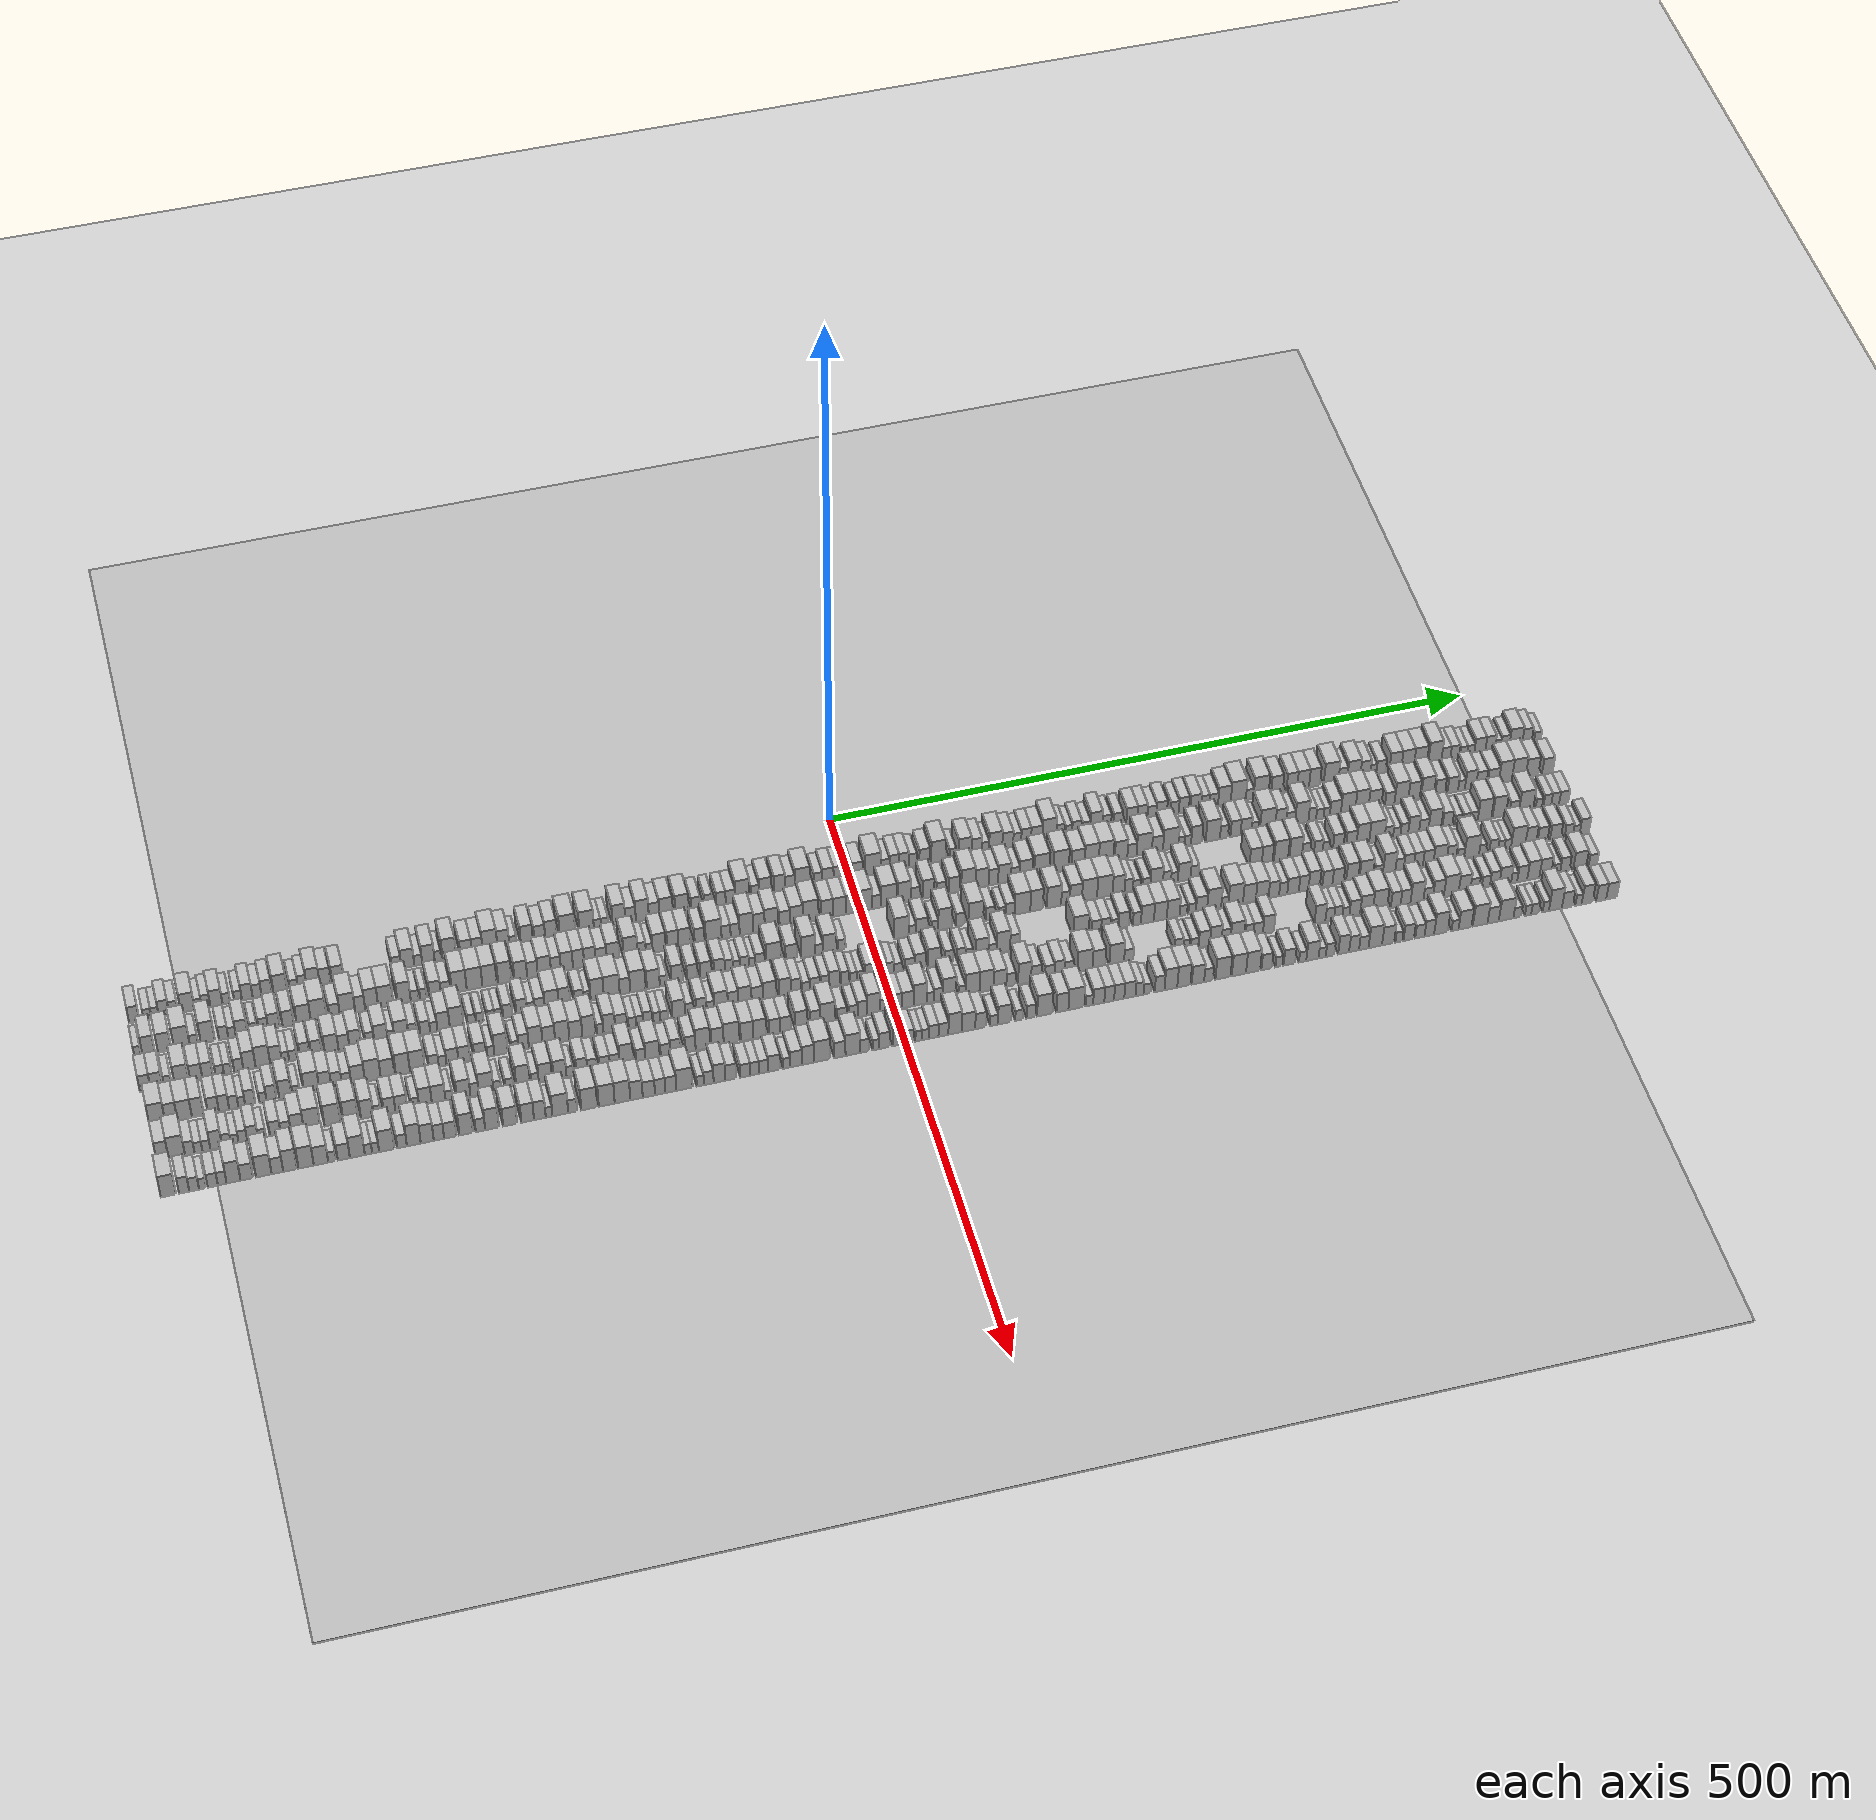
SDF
<?xml version="1.0" encoding="utf-8"?>

<sdf version="1.6">

   <world name="default">

      <gui fullscreen="0">

         <camera name="user_camera">

            <pose>-15 0 4.57585 0 0 0</pose>

            <view_controller>orbit</view_controller>

         </camera>

      </gui>

      <scene>

         <sky>

           <clouds>

             <speed>12</speed>

           </clouds>

         </sky>

         <ambient>0.4 0.4 0.4 1</ambient>

         <background>0.7 0.7 0.7 1</background>

         <shadows>1</shadows>

      </scene>

      <gravity>0 0 -9.8066</gravity>

      <magnetic_field>6e-06 2.3e-05 -4.2e-05</magnetic_field>

      <physics default="0" name="default_physics" type="ode">

         <ode>

            <solver>

               <type>quick</type>

               <iters>10</iters>

               <sor>1.0</sor>

               <use_dynamic_moi_rescaling>0</use_dynamic_moi_rescaling>

            </solver>

            <constraints>

               <cfm>0</cfm>

               <erp>0.2</erp>

               <contact_max_correcting_vel>100</contact_max_correcting_vel>

               <contact_surface_layer>0.001</contact_surface_layer>

            </constraints>

         </ode>

         <max_step_size>0.004</max_step_size>

         <real_time_factor>1</real_time_factor>

         <real_time_update_rate>250</real_time_update_rate>

      </physics>

      <light name="sun" type="directional">

         <cast_shadows>1</cast_shadows>

         <pose>0 0 10 0 0 0</pose>

         <diffuse>0.8 0.8 0.8 1</diffuse>

         <specular>0.2 0.2 0.2 1</specular>

         <attenuation>

            <range>1000</range>

            <constant>0.9</constant>

            <linear>0.01</linear>

            <quadratic>0.001</quadratic>

         </attenuation>

         <direction>-0.5 0.1 -0.9</direction>

      </light>

      <include>

         <name>ground_plane_1</name>

         <uri>model://HANNAS_ground_plane</uri>

         <pose>0 0 0  0 0 0</pose>

      </include>

      <include>

         <name>ground_plane_2</name>

         <uri>model://HANNAS_ground_plane</uri>

         <pose>100 0 0  0 0 0</pose>

      </include>

      <model name="building_1">

         <static>1</static>

         <pose frame="">50.0000 -534.1991 0 0.000000 0.000000 0.000000</pose>

         <link name="link">

            <pose frame="">0 0 9.00 0 0 0</pose>

            <collision name="collision">

               <geometry>

                  <box>

                     <size>20.0000 7.6018 18.0000</size>

                  </box>

               </geometry>

               <max_contacts>10</max_contacts>

               <surface>

                  <contact>

                     <ode/>

                  </contact>

                  <bounce/>

                  <friction>

                     <torsional>

                        <ode/>

                     </torsional>

                     <ode/>

                  </friction>

               </surface>

            </collision>

            <visual name="visual">

               <cast_shadows>0</cast_shadows>

               <geometry>

                  <box>

                     <size>20.0000 7.6018 18.0000</size>

                  </box>

               </geometry>

               <material>

                  <script>

                     <uri>model://HANNAS_wall/materials/scripts</uri>

                     <uri>model://HANNAS_wall/materials/textures</uri>

                     <name>vrc/HANNAS_wall</name>

                  </script>

               </material>

            </visual>

            <self_collide>0</self_collide>

            <enable_wind>0</enable_wind>

            <kinematic>0</kinematic>

         </link>

      </model>

      <model name="building_2">

         <static>1</static>

         <pose frame="">50.0000 -524.4637 0 0.000000 0.000000 0.000000</pose>

         <link name="link">

            <pose frame="">0 0 6.00 0 0 0</pose>

            <collision name="collision">

               <geometry>

                  <box>

                     <size>20.0000 5.8690 12.0000</size>

                  </box>

               </geometry>

               <max_contacts>10</max_contacts>

               <surface>

                  <contact>

                     <ode/>

                  </contact>

                  <bounce/>

                  <friction>

                     <torsional>

                        <ode/>

                     </torsional>

                     <ode/>

                  </friction>

               </surface>

            </collision>

            <visual name="visual">

               <cast_shadows>0</cast_shadows>

               <geometry>

                  <box>

                     <size>20.0000 5.8690 12.0000</size>

                  </box>

               </geometry>

               <material>

                  <script>

                     <uri>model://HANNAS_wall/materials/scripts</uri>

                     <uri>model://HANNAS_wall/materials/textures</uri>

                     <name>vrc/HANNAS_wall</name>

                  </script>

               </material>

            </visual>

            <self_collide>0</self_collide>

            <enable_wind>0</enable_wind>

            <kinematic>0</kinematic>

         </link>

      </model>

      <model name="building_3">

         <static>1</static>

         <pose frame="">50.0000 -518.8966 0 0.000000 0.000000 0.000000</pose>

         <link name="link">

            <pose frame="">0 0 6.00 0 0 0</pose>

            <collision name="collision">

               <geometry>

                  <box>

                     <size>20.0000 5.2653 12.0000</size>

                  </box>

               </geometry>

               <max_contacts>10</max_contacts>

               <surface>

                  <contact>

                     <ode/>

                  </contact>

                  <bounce/>

                  <friction>

                     <torsional>

                        <ode/>

                     </torsional>

                     <ode/>

                  </friction>

               </surface>

            </collision>

            <visual name="visual">

               <cast_shadows>0</cast_shadows>

               <geometry>

                  <box>

                     <size>20.0000 5.2653 12.0000</size>

                  </box>

               </geometry>

               <material>

                  <script>

                     <uri>model://HANNAS_wall/materials/scripts</uri>

                     <uri>model://HANNAS_wall/materials/textures</uri>

                     <name>vrc/HANNAS_wall</name>

                  </script>

               </material>

            </visual>

            <self_collide>0</self_collide>

            <enable_wind>0</enable_wind>

            <kinematic>0</kinematic>

         </link>

      </model>

      <model name="building_4">

         <static>1</static>

         <pose frame="">50.0000 -512.4413 0 0.000000 0.000000 0.000000</pose>

         <link name="link">

            <pose frame="">0 0 9.00 0 0 0</pose>

            <collision name="collision">

               <geometry>

                  <box>

                     <size>20.0000 7.6454 18.0000</size>

                  </box>

               </geometry>

               <max_contacts>10</max_contacts>

               <surface>

                  <contact>

                     <ode/>

                  </contact>

                  <bounce/>

                  <friction>

                     <torsional>

                        <ode/>

                     </torsional>

                     <ode/>

                  </friction>

               </surface>

            </collision>

            <visual name="visual">

               <cast_shadows>0</cast_shadows>

               <geometry>

                  <box>

                     <size>20.0000 7.6454 18.0000</size>

                  </box>

               </geometry>

               <material>

                  <script>

                     <uri>model://HANNAS_wall/materials/scripts</uri>

                     <uri>model://HANNAS_wall/materials/textures</uri>

                     <name>vrc/HANNAS_wall</name>

                  </script>

               </material>

            </visual>

            <self_collide>0</self_collide>

            <enable_wind>0</enable_wind>

            <kinematic>0</kinematic>

         </link>

      </model>

      <model name="building_5">

         <static>1</static>

         <pose frame="">50.0000 -505.3724 0 0.000000 0.000000 0.000000</pose>

         <link name="link">

            <pose frame="">0 0 7.50 0 0 0</pose>

            <collision name="collision">

               <geometry>

                  <box>

                     <size>20.0000 6.4923 15.0000</size>

                  </box>

               </geometry>

               <max_contacts>10</max_contacts>

               <surface>

                  <contact>

                     <ode/>

                  </contact>

                  <bounce/>

                  <friction>

                     <torsional>

                        <ode/>

                     </torsional>

                     <ode/>

                  </friction>

               </surface>

            </collision>

            <visual name="visual">

               <cast_shadows>0</cast_shadows>

               <geometry>

                  <box>

                     <size>20.0000 6.4923 15.0000</size>

                  </box>

               </geometry>

               <material>

                  <script>

                     <uri>model://HANNAS_wall/materials/scripts</uri>

                     <uri>model://HANNAS_wall/materials/textures</uri>

                     <name>vrc/HANNAS_wall</name>

                  </script>

               </material>

            </visual>

            <self_collide>0</self_collide>

            <enable_wind>0</enable_wind>

            <kinematic>0</kinematic>

         </link>

      </model>

      <model name="building_6">

         <static>1</static>

         <pose frame="">50.0000 -495.1157 0 0.000000 0.000000 0.000000</pose>

         <link name="link">

            <pose frame="">0 0 10.50 0 0 0</pose>

            <collision name="collision">

               <geometry>

                  <box>

                     <size>20.0000 10.0212 21.0000</size>

                  </box>

               </geometry>

               <max_contacts>10</max_contacts>

               <surface>

                  <contact>

                     <ode/>

                  </contact>

                  <bounce/>

                  <friction>

                     <torsional>

                        <ode/>

                     </torsional>

                     <ode/>

                  </friction>

               </surface>

            </collision>

            <visual name="visual">

               <cast_shadows>0</cast_shadows>

               <geometry>

                  <box>

                     <size>20.0000 10.0212 21.0000</size>

                  </box>

               </geometry>

               <material>

                  <script>

                     <uri>model://HANNAS_wall/materials/scripts</uri>

                     <uri>model://HANNAS_wall/materials/textures</uri>

                     <name>vrc/HANNAS_wall</name>

                  </script>

               </material>

            </visual>

            <self_collide>0</self_collide>

            <enable_wind>0</enable_wind>

            <kinematic>0</kinematic>

         </link>

      </model>

      <model name="building_7">

         <static>1</static>

         <pose frame="">50.0000 -487.4866 0 0.000000 0.000000 0.000000</pose>

         <link name="link">

            <pose frame="">0 0 6.00 0 0 0</pose>

            <collision name="collision">

               <geometry>

                  <box>

                     <size>20.0000 5.2372 12.0000</size>

                  </box>

               </geometry>

               <max_contacts>10</max_contacts>

               <surface>

                  <contact>

                     <ode/>

                  </contact>

                  <bounce/>

                  <friction>

                     <torsional>

                        <ode/>

                     </torsional>

                     <ode/>

                  </friction>

               </surface>

            </collision>

            <visual name="visual">

               <cast_shadows>0</cast_shadows>

               <geometry>

                  <box>

                     <size>20.0000 5.2372 12.0000</size>

                  </box>

               </geometry>

               <material>

                  <script>

                     <uri>model://HANNAS_wall/materials/scripts</uri>

                     <uri>model://HANNAS_wall/materials/textures</uri>

                     <name>vrc/HANNAS_wall</name>

                  </script>

               </material>

            </visual>

            <self_collide>0</self_collide>

            <enable_wind>0</enable_wind>

            <kinematic>0</kinematic>

         </link>

      </model>

      <model name="building_8">

         <static>1</static>

         <pose frame="">50.0000 -481.7836 0 0.000000 0.000000 0.000000</pose>

         <link name="link">

            <pose frame="">0 0 7.50 0 0 0</pose>

            <collision name="collision">

               <geometry>

                  <box>

                     <size>20.0000 6.1688 15.0000</size>

                  </box>

               </geometry>

               <max_contacts>10</max_contacts>

               <surface>

                  <contact>

                     <ode/>

                  </contact>

                  <bounce/>

                  <friction>

                     <torsional>

                        <ode/>

                     </torsional>

                     <ode/>

                  </friction>

               </surface>

            </collision>

            <visual name="visual">

               <cast_shadows>0</cast_shadows>

               <geometry>

                  <box>

                     <size>20.0000 6.1688 15.0000</size>

                  </box>

               </geometry>

               <material>

                  <script>

                     <uri>model://HANNAS_wall/materials/scripts</uri>

                     <uri>model://HANNAS_wall/materials/textures</uri>

                     <name>vrc/HANNAS_wall</name>

                  </script>

               </material>

            </visual>

            <self_collide>0</self_collide>

            <enable_wind>0</enable_wind>

            <kinematic>0</kinematic>

         </link>

      </model>

      <model name="building_9">

         <static>1</static>

         <pose frame="">50.0000 -474.2498 0 0.000000 0.000000 0.000000</pose>

         <link name="link">

            <pose frame="">0 0 9.00 0 0 0</pose>

            <collision name="collision">

               <geometry>

                  <box>

                     <size>20.0000 8.8986 18.0000</size>

                  </box>

               </geometry>

               <max_contacts>10</max_contacts>

               <surface>

                  <contact>

                     <ode/>

                  </contact>

                  <bounce/>

                  <friction>

                     <torsional>

                        <ode/>

                     </torsional>

                     <ode/>

                  </friction>

               </surface>

            </collision>

            <visual name="visual">

               <cast_shadows>0</cast_shadows>

               <geometry>

                  <box>

                     <size>20.0000 8.8986 18.0000</size>

                  </box>

               </geometry>

               <material>

                  <script>

                     <uri>model://HANNAS_wall/materials/scripts</uri>

                     <uri>model://HANNAS_wall/materials/textures</uri>

                     <name>vrc/HANNAS_wall</name>

                  </script>

               </material>

            </visual>

            <self_collide>0</self_collide>

            <enable_wind>0</enable_wind>

            <kinematic>0</kinematic>

         </link>

      </model>

      <model name="building_10">

         <static>1</static>

         <pose frame="">50.0000 -466.9744 0 0.000000 0.000000 0.000000</pose>

         <link name="link">

            <pose frame="">0 0 6.00 0 0 0</pose>

            <collision name="collision">

               <geometry>

                  <box>

                     <size>20.0000 5.6523 12.0000</size>

                  </box>

               </geometry>

               <max_contacts>10</max_contacts>

               <surface>

                  <contact>

                     <ode/>

                  </contact>

                  <bounce/>

                  <friction>

                     <torsional>

                        <ode/>

                     </torsional>

                     <ode/>

                  </friction>

               </surface>

            </collision>

            <visual name="visual">

               <cast_shadows>0</cast_shadows>

               <geometry>

                  <box>

                     <size>20.0000 5.6523 12.0000</size>

                  </box>

               </geometry>

               <material>

                  <script>

                     <uri>model://HANNAS_wall/materials/scripts</uri>

                     <uri>model://HANNAS_wall/materials/textures</uri>

                     <name>vrc/HANNAS_wall</name>

                  </script>

               </material>

            </visual>

            <self_collide>0</self_collide>

            <enable_wind>0</enable_wind>

            <kinematic>0</kinematic>

         </link>

      </model>

      <model name="building_11">

         <static>1</static>

         <pose frame="">50.0000 -458.3835 0 0.000000 0.000000 0.000000</pose>

         <link name="link">

            <pose frame="">0 0 6.00 0 0 0</pose>

            <collision name="collision">

               <geometry>

                  <box>

                     <size>20.0000 5.5294 12.0000</size>

                  </box>

               </geometry>

               <max_contacts>10</max_contacts>

               <surface>

                  <contact>

                     <ode/>

                  </contact>

                  <bounce/>

                  <friction>

                     <torsional>

                        <ode/>

                     </torsional>

                     <ode/>

                  </friction>

               </surface>

            </collision>

            <visual name="visual">

               <cast_shadows>0</cast_shadows>

               <geometry>

                  <box>

                     <size>20.0000 5.5294 12.0000</size>

                  </box>

               </geometry>

               <material>

                  <script>

                     <uri>model://HANNAS_wall/materials/scripts</uri>

                     <uri>model://HANNAS_wall/materials/textures</uri>

                     <name>vrc/HANNAS_wall</name>

                  </script>

               </material>

            </visual>

            <self_collide>0</self_collide>

            <enable_wind>0</enable_wind>

            <kinematic>0</kinematic>

         </link>

      </model>

      <model name="building_12">

         <static>1</static>

         <pose frame="">50.0000 -451.6609 0 0.000000 0.000000 0.000000</pose>

         <link name="link">

            <pose frame="">0 0 9.00 0 0 0</pose>

            <collision name="collision">

               <geometry>

                  <box>

                     <size>20.0000 7.9158 18.0000</size>

                  </box>

               </geometry>

               <max_contacts>10</max_contacts>

               <surface>

                  <contact>

                     <ode/>

                  </contact>

                  <bounce/>

                  <friction>

                     <torsional>

                        <ode/>

                     </torsional>

                     <ode/>

                  </friction>

               </surface>

            </collision>

            <visual name="visual">

               <cast_shadows>0</cast_shadows>

               <geometry>

                  <box>

                     <size>20.0000 7.9158 18.0000</size>

                  </box>

               </geometry>

               <material>

                  <script>

                     <uri>model://HANNAS_wall/materials/scripts</uri>

                     <uri>model://HANNAS_wall/materials/textures</uri>

                     <name>vrc/HANNAS_wall</name>

                  </script>

               </material>

            </visual>

            <self_collide>0</self_collide>

            <enable_wind>0</enable_wind>

            <kinematic>0</kinematic>

         </link>

      </model>

      <model name="building_13">

         <static>1</static>

         <pose frame="">50.0000 -444.4153 0 0.000000 0.000000 0.000000</pose>

         <link name="link">

            <pose frame="">0 0 7.50 0 0 0</pose>

            <collision name="collision">

               <geometry>

                  <box>

                     <size>20.0000 6.5753 15.0000</size>

                  </box>

               </geometry>

               <max_contacts>10</max_contacts>

               <surface>

                  <contact>

                     <ode/>

                  </contact>

                  <bounce/>

                  <friction>

                     <torsional>

                        <ode/>

                     </torsional>

                     <ode/>

                  </friction>

               </surface>

            </collision>

            <visual name="visual">

               <cast_shadows>0</cast_shadows>

               <geometry>

                  <box>

                     <size>20.0000 6.5753 15.0000</size>

                  </box>

               </geometry>

               <material>

                  <script>

                     <uri>model://HANNAS_wall/materials/scripts</uri>

                     <uri>model://HANNAS_wall/materials/textures</uri>

                     <name>vrc/HANNAS_wall</name>

                  </script>

               </material>

            </visual>

            <self_collide>0</self_collide>

            <enable_wind>0</enable_wind>

            <kinematic>0</kinematic>

         </link>

      </model>

      <model name="building_14">

         <static>1</static>

         <pose frame="">50.0000 -437.2513 0 0.000000 0.000000 0.000000</pose>

         <link name="link">

            <pose frame="">0 0 9.00 0 0 0</pose>

            <collision name="collision">

               <geometry>

                  <box>

                     <size>20.0000 7.7527 18.0000</size>

                  </box>

               </geometry>

               <max_contacts>10</max_contacts>

               <surface>

                  <contact>

                     <ode/>

                  </contact>

                  <bounce/>

                  <friction>

                     <torsional>

                        <ode/>

                     </torsional>

                     <ode/>

                  </friction>

               </surface>

            </collision>

            <visual name="visual">

               <cast_shadows>0</cast_shadows>

               <geometry>

                  <box>

                     <size>20.0000 7.7527 18.0000</size>

                  </box>

               </geometry>

               <material>

                  <script>

                     <uri>model://HANNAS_wall/materials/scripts</uri>

                     <uri>model://HANNAS_wall/materials/textures</uri>

                     <name>vrc/HANNAS_wall</name>

                  </script>

               </material>

            </visual>

            <self_collide>0</self_collide>

            <enable_wind>0</enable_wind>

            <kinematic>0</kinematic>

         </link>

      </model>

      <model name="building_15">

         <static>1</static>

         <pose frame="">50.0000 -427.3314 0 0.000000 0.000000 0.000000</pose>

         <link name="link">

            <pose frame="">0 0 10.50 0 0 0</pose>

            <collision name="collision">

               <geometry>

                  <box>

                     <size>20.0000 10.0871 21.0000</size>

                  </box>

               </geometry>

               <max_contacts>10</max_contacts>

               <surface>

                  <contact>

                     <ode/>

                  </contact>

                  <bounce/>

                  <friction>

                     <torsional>

                        <ode/>

                     </torsional>

                     <ode/>

                  </friction>

               </surface>

            </collision>

            <visual name="visual">

               <cast_shadows>0</cast_shadows>

               <geometry>

                  <box>

                     <size>20.0000 10.0871 21.0000</size>

                  </box>

               </geometry>

               <material>

                  <script>

                     <uri>model://HANNAS_wall/materials/scripts</uri>

                     <uri>model://HANNAS_wall/materials/textures</uri>

                     <name>vrc/HANNAS_wall</name>

                  </script>

               </material>

            </visual>

            <self_collide>0</self_collide>

            <enable_wind>0</enable_wind>

            <kinematic>0</kinematic>

         </link>

      </model>

      <model name="building_16">

         <static>1</static>

         <pose frame="">50.0000 -417.3152 0 0.000000 0.000000 0.000000</pose>

         <link name="link">

            <pose frame="">0 0 6.00 0 0 0</pose>

            <collision name="collision">

               <geometry>

                  <box>

                     <size>20.0000 5.9452 12.0000</size>

                  </box>

               </geometry>

               <max_contacts>10</max_contacts>

               <surface>

                  <contact>

                     <ode/>

                  </contact>

                  <bounce/>

                  <friction>

                     <torsional>

                        <ode/>

                     </torsional>

                     <ode/>

                  </friction>

               </surface>

            </collision>

            <visual name="visual">

               <cast_shadows>0</cast_shadows>

               <geometry>

                  <box>

                     <size>20.0000 5.9452 12.0000</size>

                  </box>

               </geometry>

               <material>

                  <script>

                     <uri>model://HANNAS_wall/materials/scripts</uri>

                     <uri>model://HANNAS_wall/materials/textures</uri>

                     <name>vrc/HANNAS_wall</name>

                  </script>

               </material>

            </visual>

            <self_collide>0</self_collide>

            <enable_wind>0</enable_wind>

            <kinematic>0</kinematic>

         </link>

      </model>

      <model name="building_17">

         <static>1</static>

         <pose frame="">50.0000 -411.2061 0 0.000000 0.000000 0.000000</pose>

         <link name="link">

            <pose frame="">0 0 7.50 0 0 0</pose>

            <collision name="collision">

               <geometry>

                  <box>

                     <size>20.0000 6.2730 15.0000</size>

                  </box>

               </geometry>

               <max_contacts>10</max_contacts>

               <surface>

                  <contact>

                     <ode/>

                  </contact>

                  <bounce/>

                  <friction>

                     <torsional>

                        <ode/>

                     </torsional>

                     <ode/>

                  </friction>

               </surface>

            </collision>

            <visual name="visual">

               <cast_shadows>0</cast_shadows>

               <geometry>

                  <box>

                     <size>20.0000 6.2730 15.0000</size>

                  </box>

               </geometry>

               <material>

                  <script>

                     <uri>model://HANNAS_wall/materials/scripts</uri>

                     <uri>model://HANNAS_wall/materials/textures</uri>

                     <name>vrc/HANNAS_wall</name>

                  </script>

               </material>

            </visual>

            <self_collide>0</self_collide>

            <enable_wind>0</enable_wind>

            <kinematic>0</kinematic>

         </link>

      </model>

      <model name="building_18">

         <static>1</static>

         <pose frame="">50.0000 -403.2545 0 0.000000 0.000000 0.000000</pose>

         <link name="link">

            <pose frame="">0 0 10.50 0 0 0</pose>

            <collision name="collision">

               <geometry>

                  <box>

                     <size>20.0000 9.6303 21.0000</size>

                  </box>

               </geometry>

               <max_contacts>10</max_contacts>

               <surface>

                  <contact>

                     <ode/>

                  </contact>

                  <bounce/>

                  <friction>

                     <torsional>

                        <ode/>

                     </torsional>

                     <ode/>

                  </friction>

               </surface>

            </collision>

            <visual name="visual">

               <cast_shadows>0</cast_shadows>

               <geometry>

                  <box>

                     <size>20.0000 9.6303 21.0000</size>

                  </box>

               </geometry>

               <material>

                  <script>

                     <uri>model://HANNAS_wall/materials/scripts</uri>

                     <uri>model://HANNAS_wall/materials/textures</uri>

                     <name>vrc/HANNAS_wall</name>

                  </script>

               </material>

            </visual>

            <self_collide>0</self_collide>

            <enable_wind>0</enable_wind>

            <kinematic>0</kinematic>

         </link>

      </model>

      <model name="building_19">

         <static>1</static>

         <pose frame="">50.0000 -394.4292 0 0.000000 0.000000 0.000000</pose>

         <link name="link">

            <pose frame="">0 0 9.00 0 0 0</pose>

            <collision name="collision">

               <geometry>

                  <box>

                     <size>20.0000 8.0204 18.0000</size>

                  </box>

               </geometry>

               <max_contacts>10</max_contacts>

               <surface>

                  <contact>

                     <ode/>

                  </contact>

                  <bounce/>

                  <friction>

                     <torsional>

                        <ode/>

                     </torsional>

                     <ode/>

                  </friction>

               </surface>

            </collision>

            <visual name="visual">

               <cast_shadows>0</cast_shadows>

               <geometry>

                  <box>

                     <size>20.0000 8.0204 18.0000</size>

                  </box>

               </geometry>

               <material>

                  <script>

                     <uri>model://HANNAS_wall/materials/scripts</uri>

                     <uri>model://HANNAS_wall/materials/textures</uri>

                     <name>vrc/HANNAS_wall</name>

                  </script>

               </material>

            </visual>

            <self_collide>0</self_collide>

            <enable_wind>0</enable_wind>

            <kinematic>0</kinematic>

         </link>

      </model>

      <model name="building_20">

         <static>1</static>

         <pose frame="">50.0000 -385.0337 0 0.000000 0.000000 0.000000</pose>

         <link name="link">

            <pose frame="">0 0 9.00 0 0 0</pose>

            <collision name="collision">

               <geometry>

                  <box>

                     <size>20.0000 8.7706 18.0000</size>

                  </box>

               </geometry>

               <max_contacts>10</max_contacts>

               <surface>

                  <contact>

                     <ode/>

                  </contact>

                  <bounce/>

                  <friction>

                     <torsional>

                        <ode/>

                     </torsional>

                     <ode/>

                  </friction>

               </surface>

            </collision>

            <visual name="visual">

               <cast_shadows>0</cast_shadows>

               <geometry>

                  <box>

                     <size>20.0000 8.7706 18.0000</size>

                  </box>

               </geometry>

               <material>

                  <script>

                     <uri>model://HANNAS_wall/materials/scripts</uri>

                     <uri>model://HANNAS_wall/materials/textures</uri>

                     <name>vrc/HANNAS_wall</name>

                  </script>

               </material>

            </visual>

            <self_collide>0</self_collide>

            <enable_wind>0</enable_wind>

            <kinematic>0</kinematic>

         </link>

      </model>

      <model name="building_21">

         <static>1</static>

         <pose frame="">50.0000 -341.4658 0 0.000000 0.000000 0.000000</pose>

         <link name="link">

            <pose frame="">0 0 7.50 0 0 0</pose>

            <collision name="collision">

               <geometry>

                  <box>

                     <size>20.0000 6.7884 15.0000</size>

                  </box>

               </geometry>

               <max_contacts>10</max_contacts>

               <surface>

                  <contact>

                     <ode/>

                  </contact>

                  <bounce/>

                  <friction>

                     <torsional>

                        <ode/>

                     </torsional>

                     <ode/>

                  </friction>

               </surface>

            </collision>

            <visual name="visual">

               <cast_shadows>0</cast_shadows>

               <geometry>

                  <box>

                     <size>20.0000 6.7884 15.0000</size>

                  </box>

               </geometry>

               <material>

                  <script>

                     <uri>model://HANNAS_wall/materials/scripts</uri>

                     <uri>model://HANNAS_wall/materials/textures</uri>

                     <name>vrc/HANNAS_wall</name>

                  </script>

               </material>

            </visual>

            <self_collide>0</self_collide>

            <enable_wind>0</enable_wind>

            <kinematic>0</kinematic>

         </link>

      </model>

      <model name="building_22">

         <static>1</static>

         <pose frame="">50.0000 -333.2770 0 0.000000 0.000000 0.000000</pose>

         <link name="link">

            <pose frame="">0 0 10.50 0 0 0</pose>

            <collision name="collision">

               <geometry>

                  <box>

                     <size>20.0000 9.5892 21.0000</size>

                  </box>

               </geometry>

               <max_contacts>10</max_contacts>

               <surface>

                  <contact>

                     <ode/>

                  </contact>

                  <bounce/>

                  <friction>

                     <torsional>

                        <ode/>

                     </torsional>

                     <ode/>

                  </friction>

               </surface>

            </collision>

            <visual name="visual">

               <cast_shadows>0</cast_shadows>

               <geometry>

                  <box>

                     <size>20.0000 9.5892 21.0000</size>

                  </box>

               </geometry>

               <material>

                  <script>

                     <uri>model://HANNAS_wall/materials/scripts</uri>

                     <uri>model://HANNAS_wall/materials/textures</uri>

                     <name>vrc/HANNAS_wall</name>

                  </script>

               </material>

            </visual>

            <self_collide>0</self_collide>

            <enable_wind>0</enable_wind>

            <kinematic>0</kinematic>

         </link>

      </model>

      <model name="building_23">

         <static>1</static>

         <pose frame="">50.0000 -325.5582 0 0.000000 0.000000 0.000000</pose>

         <link name="link">

            <pose frame="">0 0 6.00 0 0 0</pose>

            <collision name="collision">

               <geometry>

                  <box>

                     <size>20.0000 5.8484 12.0000</size>

                  </box>

               </geometry>

               <max_contacts>10</max_contacts>

               <surface>

                  <contact>

                     <ode/>

                  </contact>

                  <bounce/>

                  <friction>

                     <torsional>

                        <ode/>

                     </torsional>

                     <ode/>

                  </friction>

               </surface>

            </collision>

            <visual name="visual">

               <cast_shadows>0</cast_shadows>

               <geometry>

                  <box>

                     <size>20.0000 5.8484 12.0000</size>

                  </box>

               </geometry>

               <material>

                  <script>

                     <uri>model://HANNAS_wall/materials/scripts</uri>

                     <uri>model://HANNAS_wall/materials/textures</uri>

                     <name>vrc/HANNAS_wall</name>

                  </script>

               </material>

            </visual>

            <self_collide>0</self_collide>

            <enable_wind>0</enable_wind>

            <kinematic>0</kinematic>

         </link>

      </model>

      <model name="building_24">

         <static>1</static>

         <pose frame="">50.0000 -318.0007 0 0.000000 0.000000 0.000000</pose>

         <link name="link">

            <pose frame="">0 0 10.50 0 0 0</pose>

            <collision name="collision">

               <geometry>

                  <box>

                     <size>20.0000 9.2668 21.0000</size>

                  </box>

               </geometry>

               <max_contacts>10</max_contacts>

               <surface>

                  <contact>

                     <ode/>

                  </contact>

                  <bounce/>

                  <friction>

                     <torsional>

                        <ode/>

                     </torsional>

                     <ode/>

                  </friction>

               </surface>

            </collision>

            <visual name="visual">

               <cast_shadows>0</cast_shadows>

               <geometry>

                  <box>

                     <size>20.0000 9.2668 21.0000</size>

                  </box>

               </geometry>

               <material>

                  <script>

                     <uri>model://HANNAS_wall/materials/scripts</uri>

                     <uri>model://HANNAS_wall/materials/textures</uri>

                     <name>vrc/HANNAS_wall</name>

                  </script>

               </material>

            </visual>

            <self_collide>0</self_collide>

            <enable_wind>0</enable_wind>

            <kinematic>0</kinematic>

         </link>

      </model>

      <model name="building_25">

         <static>1</static>

         <pose frame="">50.0000 -310.9358 0 0.000000 0.000000 0.000000</pose>

         <link name="link">

            <pose frame="">0 0 6.00 0 0 0</pose>

            <collision name="collision">

               <geometry>

                  <box>

                     <size>20.0000 4.8629 12.0000</size>

                  </box>

               </geometry>

               <max_contacts>10</max_contacts>

               <surface>

                  <contact>

                     <ode/>

                  </contact>

                  <bounce/>

                  <friction>

                     <torsional>

                        <ode/>

                     </torsional>

                     <ode/>

                  </friction>

               </surface>

            </collision>

            <visual name="visual">

               <cast_shadows>0</cast_shadows>

               <geometry>

                  <box>

                     <size>20.0000 4.8629 12.0000</size>

                  </box>

               </geometry>

               <material>

                  <script>

                     <uri>model://HANNAS_wall/materials/scripts</uri>

                     <uri>model://HANNAS_wall/materials/textures</uri>

                     <name>vrc/HANNAS_wall</name>

                  </script>

               </material>

            </visual>

            <self_collide>0</self_collide>

            <enable_wind>0</enable_wind>

            <kinematic>0</kinematic>

         </link>

      </model>

      <model name="building_26">

         <static>1</static>

         <pose frame="">50.0000 -302.3581 0 0.000000 0.000000 0.000000</pose>

         <link name="link">

            <pose frame="">0 0 12.00 0 0 0</pose>

            <collision name="collision">

               <geometry>

                  <box>

                     <size>20.0000 10.2926 24.0000</size>

                  </box>

               </geometry>

               <max_contacts>10</max_contacts>

               <surface>

                  <contact>

                     <ode/>

                  </contact>

                  <bounce/>

                  <friction>

                     <torsional>

                        <ode/>

                     </torsional>

                     <ode/>

                  </friction>

               </surface>

            </collision>

            <visual name="visual">

               <cast_shadows>0</cast_shadows>

               <geometry>

                  <box>

                     <size>20.0000 10.2926 24.0000</size>

                  </box>

               </geometry>

               <material>

                  <script>

                     <uri>model://HANNAS_wall/materials/scripts</uri>

                     <uri>model://HANNAS_wall/materials/textures</uri>

                     <name>vrc/HANNAS_wall</name>

                  </script>

               </material>

            </visual>

            <self_collide>0</self_collide>

            <enable_wind>0</enable_wind>

            <kinematic>0</kinematic>

         </link>

      </model>

      <model name="building_27">

         <static>1</static>

         <pose frame="">50.0000 -289.9420 0 0.000000 0.000000 0.000000</pose>

         <link name="link">

            <pose frame="">0 0 9.00 0 0 0</pose>

            <collision name="collision">

               <geometry>

                  <box>

                     <size>20.0000 8.5396 18.0000</size>

                  </box>

               </geometry>

               <max_contacts>10</max_contacts>

               <surface>

                  <contact>

                     <ode/>

                  </contact>

                  <bounce/>

                  <friction>

                     <torsional>

                        <ode/>

                     </torsional>

                     <ode/>

                  </friction>

               </surface>

            </collision>

            <visual name="visual">

               <cast_shadows>0</cast_shadows>

               <geometry>

                  <box>

                     <size>20.0000 8.5396 18.0000</size>

                  </box>

               </geometry>

               <material>

                  <script>

                     <uri>model://HANNAS_wall/materials/scripts</uri>

                     <uri>model://HANNAS_wall/materials/textures</uri>

                     <name>vrc/HANNAS_wall</name>

                  </script>

               </material>

            </visual>

            <self_collide>0</self_collide>

            <enable_wind>0</enable_wind>

            <kinematic>0</kinematic>

         </link>

      </model>

      <model name="building_28">

         <static>1</static>

         <pose frame="">50.0000 -281.6641 0 0.000000 0.000000 0.000000</pose>

         <link name="link">

            <pose frame="">0 0 9.00 0 0 0</pose>

            <collision name="collision">

               <geometry>

                  <box>

                     <size>20.0000 8.0164 18.0000</size>

                  </box>

               </geometry>

               <max_contacts>10</max_contacts>

               <surface>

                  <contact>

                     <ode/>

                  </contact>

                  <bounce/>

                  <friction>

                     <torsional>

                        <ode/>

                     </torsional>

                     <ode/>

                  </friction>

               </surface>

            </collision>

            <visual name="visual">

               <cast_shadows>0</cast_shadows>

               <geometry>

                  <box>

                     <size>20.0000 8.0164 18.0000</size>

                  </box>

               </geometry>

               <material>

                  <script>

                     <uri>model://HANNAS_wall/materials/scripts</uri>

                     <uri>model://HANNAS_wall/materials/textures</uri>

                     <name>vrc/HANNAS_wall</name>

                  </script>

               </material>

            </visual>

            <self_collide>0</self_collide>

            <enable_wind>0</enable_wind>

            <kinematic>0</kinematic>

         </link>

      </model>

      <model name="building_29">

         <static>1</static>

         <pose frame="">50.0000 -272.1109 0 0.000000 0.000000 0.000000</pose>

         <link name="link">

            <pose frame="">0 0 12.00 0 0 0</pose>

            <collision name="collision">

               <geometry>

                  <box>

                     <size>20.0000 11.0899 24.0000</size>

                  </box>

               </geometry>

               <max_contacts>10</max_contacts>

               <surface>

                  <contact>

                     <ode/>

                  </contact>

                  <bounce/>

                  <friction>

                     <torsional>

                        <ode/>

                     </torsional>

                     <ode/>

                  </friction>

               </surface>

            </collision>

            <visual name="visual">

               <cast_shadows>0</cast_shadows>

               <geometry>

                  <box>

                     <size>20.0000 11.0899 24.0000</size>

                  </box>

               </geometry>

               <material>

                  <script>

                     <uri>model://HANNAS_wall/materials/scripts</uri>

                     <uri>model://HANNAS_wall/materials/textures</uri>

                     <name>vrc/HANNAS_wall</name>

                  </script>

               </material>

            </visual>

            <self_collide>0</self_collide>

            <enable_wind>0</enable_wind>

            <kinematic>0</kinematic>

         </link>

      </model>

      <model name="building_30">

         <static>1</static>

         <pose frame="">50.0000 -262.1293 0 0.000000 0.000000 0.000000</pose>

         <link name="link">

            <pose frame="">0 0 10.50 0 0 0</pose>

            <collision name="collision">

               <geometry>

                  <box>

                     <size>20.0000 8.8732 21.0000</size>

                  </box>

               </geometry>

               <max_contacts>10</max_contacts>

               <surface>

                  <contact>

                     <ode/>

                  </contact>

                  <bounce/>

                  <friction>

                     <torsional>

                        <ode/>

                     </torsional>

                     <ode/>

                  </friction>

               </surface>

            </collision>

            <visual name="visual">

               <cast_shadows>0</cast_shadows>

               <geometry>

                  <box>

                     <size>20.0000 8.8732 21.0000</size>

                  </box>

               </geometry>

               <material>

                  <script>

                     <uri>model://HANNAS_wall/materials/scripts</uri>

                     <uri>model://HANNAS_wall/materials/textures</uri>

                     <name>vrc/HANNAS_wall</name>

                  </script>

               </material>

            </visual>

            <self_collide>0</self_collide>

            <enable_wind>0</enable_wind>

            <kinematic>0</kinematic>

         </link>

      </model>

      <model name="building_31">

         <static>1</static>

         <pose frame="">50.0000 -254.9460 0 0.000000 0.000000 0.000000</pose>

         <link name="link">

            <pose frame="">0 0 6.00 0 0 0</pose>

            <collision name="collision">

               <geometry>

                  <box>

                     <size>20.0000 5.4935 12.0000</size>

                  </box>

               </geometry>

               <max_contacts>10</max_contacts>

               <surface>

                  <contact>

                     <ode/>

                  </contact>

                  <bounce/>

                  <friction>

                     <torsional>

                        <ode/>

                     </torsional>

                     <ode/>

                  </friction>

               </surface>

            </collision>

            <visual name="visual">

               <cast_shadows>0</cast_shadows>

               <geometry>

                  <box>

                     <size>20.0000 5.4935 12.0000</size>

                  </box>

               </geometry>

               <material>

                  <script>

                     <uri>model://HANNAS_wall/materials/scripts</uri>

                     <uri>model://HANNAS_wall/materials/textures</uri>

                     <name>vrc/HANNAS_wall</name>

                  </script>

               </material>

            </visual>

            <self_collide>0</self_collide>

            <enable_wind>0</enable_wind>

            <kinematic>0</kinematic>

         </link>

      </model>

      <model name="building_32">

         <static>1</static>

         <pose frame="">50.0000 -244.6528 0 0.000000 0.000000 0.000000</pose>

         <link name="link">

            <pose frame="">0 0 10.50 0 0 0</pose>

            <collision name="collision">

               <geometry>

                  <box>

                     <size>20.0000 9.0929 21.0000</size>

                  </box>

               </geometry>

               <max_contacts>10</max_contacts>

               <surface>

                  <contact>

                     <ode/>

                  </contact>

                  <bounce/>

                  <friction>

                     <torsional>

                        <ode/>

                     </torsional>

                     <ode/>

                  </friction>

               </surface>

            </collision>

            <visual name="visual">

               <cast_shadows>0</cast_shadows>

               <geometry>

                  <box>

                     <size>20.0000 9.0929 21.0000</size>

                  </box>

               </geometry>

               <material>

                  <script>

                     <uri>model://HANNAS_wall/materials/scripts</uri>

                     <uri>model://HANNAS_wall/materials/textures</uri>

                     <name>vrc/HANNAS_wall</name>

                  </script>

               </material>

            </visual>

            <self_collide>0</self_collide>

            <enable_wind>0</enable_wind>

            <kinematic>0</kinematic>

         </link>

      </model>

      <model name="building_33">

         <static>1</static>

         <pose frame="">50.0000 -235.0039 0 0.000000 0.000000 0.000000</pose>

         <link name="link">

            <pose frame="">0 0 9.00 0 0 0</pose>

            <collision name="collision">

               <geometry>

                  <box>

                     <size>20.0000 8.2049 18.0000</size>

                  </box>

               </geometry>

               <max_contacts>10</max_contacts>

               <surface>

                  <contact>

                     <ode/>

                  </contact>

                  <bounce/>

                  <friction>

                     <torsional>

                        <ode/>

                     </torsional>

                     <ode/>

                  </friction>

               </surface>

            </collision>

            <visual name="visual">

               <cast_shadows>0</cast_shadows>

               <geometry>

                  <box>

                     <size>20.0000 8.2049 18.0000</size>

                  </box>

               </geometry>

               <material>

                  <script>

                     <uri>model://HANNAS_wall/materials/scripts</uri>

                     <uri>model://HANNAS_wall/materials/textures</uri>

                     <name>vrc/HANNAS_wall</name>

                  </script>

               </material>

            </visual>

            <self_collide>0</self_collide>

            <enable_wind>0</enable_wind>

            <kinematic>0</kinematic>

         </link>

      </model>

      <model name="building_34">

         <static>1</static>

         <pose frame="">50.0000 -226.4914 0 0.000000 0.000000 0.000000</pose>

         <link name="link">

            <pose frame="">0 0 10.50 0 0 0</pose>

            <collision name="collision">

               <geometry>

                  <box>

                     <size>20.0000 8.8201 21.0000</size>

                  </box>

               </geometry>

               <max_contacts>10</max_contacts>

               <surface>

                  <contact>

                     <ode/>

                  </contact>

                  <bounce/>

                  <friction>

                     <torsional>

                        <ode/>

                     </torsional>

                     <ode/>

                  </friction>

               </surface>

            </collision>

            <visual name="visual">

               <cast_shadows>0</cast_shadows>

               <geometry>

                  <box>

                     <size>20.0000 8.8201 21.0000</size>

                  </box>

               </geometry>

               <material>

                  <script>

                     <uri>model://HANNAS_wall/materials/scripts</uri>

                     <uri>model://HANNAS_wall/materials/textures</uri>

                     <name>vrc/HANNAS_wall</name>

                  </script>

               </material>

            </visual>

            <self_collide>0</self_collide>

            <enable_wind>0</enable_wind>

            <kinematic>0</kinematic>

         </link>

      </model>

      <model name="building_35">

         <static>1</static>

         <pose frame="">50.0000 -214.1954 0 0.000000 0.000000 0.000000</pose>

         <link name="link">

            <pose frame="">0 0 12.00 0 0 0</pose>

            <collision name="collision">

               <geometry>

                  <box>

                     <size>20.0000 11.7719 24.0000</size>

                  </box>

               </geometry>

               <max_contacts>10</max_contacts>

               <surface>

                  <contact>

                     <ode/>

                  </contact>

                  <bounce/>

                  <friction>

                     <torsional>

                        <ode/>

                     </torsional>

                     <ode/>

                  </friction>

               </surface>

            </collision>

            <visual name="visual">

               <cast_shadows>0</cast_shadows>

               <geometry>

                  <box>

                     <size>20.0000 11.7719 24.0000</size>

                  </box>

               </geometry>

               <material>

                  <script>

                     <uri>model://HANNAS_wall/materials/scripts</uri>

                     <uri>model://HANNAS_wall/materials/textures</uri>

                     <name>vrc/HANNAS_wall</name>

                  </script>

               </material>

            </visual>

            <self_collide>0</self_collide>

            <enable_wind>0</enable_wind>

            <kinematic>0</kinematic>

         </link>

      </model>

      <model name="building_36">

         <static>1</static>

         <pose frame="">50.0000 -199.8539 0 0.000000 0.000000 0.000000</pose>

         <link name="link">

            <pose frame="">0 0 12.00 0 0 0</pose>

            <collision name="collision">

               <geometry>

                  <box>

                     <size>20.0000 10.9111 24.0000</size>

                  </box>

               </geometry>

               <max_contacts>10</max_contacts>

               <surface>

                  <contact>

                     <ode/>

                  </contact>

                  <bounce/>

                  <friction>

                     <torsional>

                        <ode/>

                     </torsional>

                     <ode/>

                  </friction>

               </surface>

            </collision>

            <visual name="visual">

               <cast_shadows>0</cast_shadows>

               <geometry>

                  <box>

                     <size>20.0000 10.9111 24.0000</size>

                  </box>

               </geometry>

               <material>

                  <script>

                     <uri>model://HANNAS_wall/materials/scripts</uri>

                     <uri>model://HANNAS_wall/materials/textures</uri>

                     <name>vrc/HANNAS_wall</name>

                  </script>

               </material>

            </visual>

            <self_collide>0</self_collide>

            <enable_wind>0</enable_wind>

            <kinematic>0</kinematic>

         </link>

      </model>

      <model name="building_37">

         <static>1</static>

         <pose frame="">50.0000 -191.7278 0 0.000000 0.000000 0.000000</pose>

         <link name="link">

            <pose frame="">0 0 6.00 0 0 0</pose>

            <collision name="collision">

               <geometry>

                  <box>

                     <size>20.0000 5.3411 12.0000</size>

                  </box>

               </geometry>

               <max_contacts>10</max_contacts>

               <surface>

                  <contact>

                     <ode/>

                  </contact>

                  <bounce/>

                  <friction>

                     <torsional>

                        <ode/>

                     </torsional>

                     <ode/>

                  </friction>

               </surface>

            </collision>

            <visual name="visual">

               <cast_shadows>0</cast_shadows>

               <geometry>

                  <box>

                     <size>20.0000 5.3411 12.0000</size>

                  </box>

               </geometry>

               <material>

                  <script>

                     <uri>model://HANNAS_wall/materials/scripts</uri>

                     <uri>model://HANNAS_wall/materials/textures</uri>

                     <name>vrc/HANNAS_wall</name>

                  </script>

               </material>

            </visual>

            <self_collide>0</self_collide>

            <enable_wind>0</enable_wind>

            <kinematic>0</kinematic>

         </link>

      </model>

      <model name="building_38">

         <static>1</static>

         <pose frame="">50.0000 -186.2281 0 0.000000 0.000000 0.000000</pose>

         <link name="link">

            <pose frame="">0 0 6.00 0 0 0</pose>

            <collision name="collision">

               <geometry>

                  <box>

                     <size>20.0000 5.6583 12.0000</size>

                  </box>

               </geometry>

               <max_contacts>10</max_contacts>

               <surface>

                  <contact>

                     <ode/>

                  </contact>

                  <bounce/>

                  <friction>

                     <torsional>

                        <ode/>

                     </torsional>

                     <ode/>

                  </friction>

               </surface>

            </collision>

            <visual name="visual">

               <cast_shadows>0</cast_shadows>

               <geometry>

                  <box>

                     <size>20.0000 5.6583 12.0000</size>

                  </box>

               </geometry>

               <material>

                  <script>

                     <uri>model://HANNAS_wall/materials/scripts</uri>

                     <uri>model://HANNAS_wall/materials/textures</uri>

                     <name>vrc/HANNAS_wall</name>

                  </script>

               </material>

            </visual>

            <self_collide>0</self_collide>

            <enable_wind>0</enable_wind>

            <kinematic>0</kinematic>

         </link>

      </model>

      <model name="building_39">

         <static>1</static>

         <pose frame="">50.0000 -175.5490 0 0.000000 0.000000 0.000000</pose>

         <link name="link">

            <pose frame="">0 0 12.00 0 0 0</pose>

            <collision name="collision">

               <geometry>

                  <box>

                     <size>20.0000 9.6998 24.0000</size>

                  </box>

               </geometry>

               <max_contacts>10</max_contacts>

               <surface>

                  <contact>

                     <ode/>

                  </contact>

                  <bounce/>

                  <friction>

                     <torsional>

                        <ode/>

                     </torsional>

                     <ode/>

                  </friction>

               </surface>

            </collision>

            <visual name="visual">

               <cast_shadows>0</cast_shadows>

               <geometry>

                  <box>

                     <size>20.0000 9.6998 24.0000</size>

                  </box>

               </geometry>

               <material>

                  <script>

                     <uri>model://HANNAS_wall/materials/scripts</uri>

                     <uri>model://HANNAS_wall/materials/textures</uri>

                     <name>vrc/HANNAS_wall</name>

                  </script>

               </material>

            </visual>

            <self_collide>0</self_collide>

            <enable_wind>0</enable_wind>

            <kinematic>0</kinematic>

         </link>

      </model>

      <model name="building_40">

         <static>1</static>

         <pose frame="">50.0000 -166.7754 0 0.000000 0.000000 0.000000</pose>

         <link name="link">

            <pose frame="">0 0 9.00 0 0 0</pose>

            <collision name="collision">

               <geometry>

                  <box>

                     <size>20.0000 7.8475 18.0000</size>

                  </box>

               </geometry>

               <max_contacts>10</max_contacts>

               <surface>

                  <contact>

                     <ode/>

                  </contact>

                  <bounce/>

                  <friction>

                     <torsional>

                        <ode/>

                     </torsional>

                     <ode/>

                  </friction>

               </surface>

            </collision>

            <visual name="visual">

               <cast_shadows>0</cast_shadows>

               <geometry>

                  <box>

                     <size>20.0000 7.8475 18.0000</size>

                  </box>

               </geometry>

               <material>

                  <script>

                     <uri>model://HANNAS_wall/materials/scripts</uri>

                     <uri>model://HANNAS_wall/materials/textures</uri>

                     <name>vrc/HANNAS_wall</name>

                  </script>

               </material>

            </visual>

            <self_collide>0</self_collide>

            <enable_wind>0</enable_wind>

            <kinematic>0</kinematic>

         </link>

      </model>

      <model name="building_41">

         <static>1</static>

         <pose frame="">50.0000 -157.9485 0 0.000000 0.000000 0.000000</pose>

         <link name="link">

            <pose frame="">0 0 12.00 0 0 0</pose>

            <collision name="collision">

               <geometry>

                  <box>

                     <size>20.0000 9.8065 24.0000</size>

                  </box>

               </geometry>

               <max_contacts>10</max_contacts>

               <surface>

                  <contact>

                     <ode/>

                  </contact>

                  <bounce/>

                  <friction>

                     <torsional>

                        <ode/>

                     </torsional>

                     <ode/>

                  </friction>

               </surface>

            </collision>

            <visual name="visual">

               <cast_shadows>0</cast_shadows>

               <geometry>

                  <box>

                     <size>20.0000 9.8065 24.0000</size>

                  </box>

               </geometry>

               <material>

                  <script>

                     <uri>model://HANNAS_wall/materials/scripts</uri>

                     <uri>model://HANNAS_wall/materials/textures</uri>

                     <name>vrc/HANNAS_wall</name>

                  </script>

               </material>

            </visual>

            <self_collide>0</self_collide>

            <enable_wind>0</enable_wind>

            <kinematic>0</kinematic>

         </link>

      </model>

      <model name="building_42">

         <static>1</static>

         <pose frame="">50.0000 -149.0765 0 0.000000 0.000000 0.000000</pose>

         <link name="link">

            <pose frame="">0 0 9.00 0 0 0</pose>

            <collision name="collision">

               <geometry>

                  <box>

                     <size>20.0000 7.9375 18.0000</size>

                  </box>

               </geometry>

               <max_contacts>10</max_contacts>

               <surface>

                  <contact>

                     <ode/>

                  </contact>

                  <bounce/>

                  <friction>

                     <torsional>

                        <ode/>

                     </torsional>

                     <ode/>

                  </friction>

               </surface>

            </collision>

            <visual name="visual">

               <cast_shadows>0</cast_shadows>

               <geometry>

                  <box>

                     <size>20.0000 7.9375 18.0000</size>

                  </box>

               </geometry>

               <material>

                  <script>

                     <uri>model://HANNAS_wall/materials/scripts</uri>

                     <uri>model://HANNAS_wall/materials/textures</uri>

                     <name>vrc/HANNAS_wall</name>

                  </script>

               </material>

            </visual>

            <self_collide>0</self_collide>

            <enable_wind>0</enable_wind>

            <kinematic>0</kinematic>

         </link>

      </model>

      <model name="building_43">

         <static>1</static>

         <pose frame="">50.0000 -140.1402 0 0.000000 0.000000 0.000000</pose>

         <link name="link">

            <pose frame="">0 0 10.50 0 0 0</pose>

            <collision name="collision">

               <geometry>

                  <box>

                     <size>20.0000 9.9351 21.0000</size>

                  </box>

               </geometry>

               <max_contacts>10</max_contacts>

               <surface>

                  <contact>

                     <ode/>

                  </contact>

                  <bounce/>

                  <friction>

                     <torsional>

                        <ode/>

                     </torsional>

                     <ode/>

                  </friction>

               </surface>

            </collision>

            <visual name="visual">

               <cast_shadows>0</cast_shadows>

               <geometry>

                  <box>

                     <size>20.0000 9.9351 21.0000</size>

                  </box>

               </geometry>

               <material>

                  <script>

                     <uri>model://HANNAS_wall/materials/scripts</uri>

                     <uri>model://HANNAS_wall/materials/textures</uri>

                     <name>vrc/HANNAS_wall</name>

                  </script>

               </material>

            </visual>

            <self_collide>0</self_collide>

            <enable_wind>0</enable_wind>

            <kinematic>0</kinematic>

         </link>

      </model>

      <model name="building_44">

         <static>1</static>

         <pose frame="">50.0000 -128.0864 0 0.000000 0.000000 0.000000</pose>

         <link name="link">

            <pose frame="">0 0 10.50 0 0 0</pose>

            <collision name="collision">

               <geometry>

                  <box>

                     <size>20.0000 10.1724 21.0000</size>

                  </box>

               </geometry>

               <max_contacts>10</max_contacts>

               <surface>

                  <contact>

                     <ode/>

                  </contact>

                  <bounce/>

                  <friction>

                     <torsional>

                        <ode/>

                     </torsional>

                     <ode/>

                  </friction>

               </surface>

            </collision>

            <visual name="visual">

               <cast_shadows>0</cast_shadows>

               <geometry>

                  <box>

                     <size>20.0000 10.1724 21.0000</size>

                  </box>

               </geometry>

               <material>

                  <script>

                     <uri>model://HANNAS_wall/materials/scripts</uri>

                     <uri>model://HANNAS_wall/materials/textures</uri>

                     <name>vrc/HANNAS_wall</name>

                  </script>

               </material>

            </visual>

            <self_collide>0</self_collide>

            <enable_wind>0</enable_wind>

            <kinematic>0</kinematic>

         </link>

      </model>

      <model name="building_45">

         <static>1</static>

         <pose frame="">50.0000 -117.5288 0 0.000000 0.000000 0.000000</pose>

         <link name="link">

            <pose frame="">0 0 7.50 0 0 0</pose>

            <collision name="collision">

               <geometry>

                  <box>

                     <size>20.0000 6.9429 15.0000</size>

                  </box>

               </geometry>

               <max_contacts>10</max_contacts>

               <surface>

                  <contact>

                     <ode/>

                  </contact>

                  <bounce/>

                  <friction>

                     <torsional>

                        <ode/>

                     </torsional>

                     <ode/>

                  </friction>

               </surface>

            </collision>

            <visual name="visual">

               <cast_shadows>0</cast_shadows>

               <geometry>

                  <box>

                     <size>20.0000 6.9429 15.0000</size>

                  </box>

               </geometry>

               <material>

                  <script>

                     <uri>model://HANNAS_wall/materials/scripts</uri>

                     <uri>model://HANNAS_wall/materials/textures</uri>

                     <name>vrc/HANNAS_wall</name>

                  </script>

               </material>

            </visual>

            <self_collide>0</self_collide>

            <enable_wind>0</enable_wind>

            <kinematic>0</kinematic>

         </link>

      </model>

      <model name="building_46">

         <static>1</static>

         <pose frame="">50.0000 -108.0022 0 0.000000 0.000000 0.000000</pose>

         <link name="link">

            <pose frame="">0 0 7.50 0 0 0</pose>

            <collision name="collision">

               <geometry>

                  <box>

                     <size>20.0000 6.1102 15.0000</size>

                  </box>

               </geometry>

               <max_contacts>10</max_contacts>

               <surface>

                  <contact>

                     <ode/>

                  </contact>

                  <bounce/>

                  <friction>

                     <torsional>

                        <ode/>

                     </torsional>

                     <ode/>

                  </friction>

               </surface>

            </collision>

            <visual name="visual">

               <cast_shadows>0</cast_shadows>

               <geometry>

                  <box>

                     <size>20.0000 6.1102 15.0000</size>

                  </box>

               </geometry>

               <material>

                  <script>

                     <uri>model://HANNAS_wall/materials/scripts</uri>

                     <uri>model://HANNAS_wall/materials/textures</uri>

                     <name>vrc/HANNAS_wall</name>

                  </script>

               </material>

            </visual>

            <self_collide>0</self_collide>

            <enable_wind>0</enable_wind>

            <kinematic>0</kinematic>

         </link>

      </model>

      <model name="building_47">

         <static>1</static>

         <pose frame="">50.0000 -98.4298 0 0.000000 0.000000 0.000000</pose>

         <link name="link">

            <pose frame="">0 0 7.50 0 0 0</pose>

            <collision name="collision">

               <geometry>

                  <box>

                     <size>20.0000 7.0346 15.0000</size>

                  </box>

               </geometry>

               <max_contacts>10</max_contacts>

               <surface>

                  <contact>

                     <ode/>

                  </contact>

                  <bounce/>

                  <friction>

                     <torsional>

                        <ode/>

                     </torsional>

                     <ode/>

                  </friction>

               </surface>

            </collision>

            <visual name="visual">

               <cast_shadows>0</cast_shadows>

               <geometry>

                  <box>

                     <size>20.0000 7.0346 15.0000</size>

                  </box>

               </geometry>

               <material>

                  <script>

                     <uri>model://HANNAS_wall/materials/scripts</uri>

                     <uri>model://HANNAS_wall/materials/textures</uri>

                     <name>vrc/HANNAS_wall</name>

                  </script>

               </material>

            </visual>

            <self_collide>0</self_collide>

            <enable_wind>0</enable_wind>

            <kinematic>0</kinematic>

         </link>

      </model>

      <model name="building_48">

         <static>1</static>

         <pose frame="">50.0000 -91.2666 0 0.000000 0.000000 0.000000</pose>

         <link name="link">

            <pose frame="">0 0 7.50 0 0 0</pose>

            <collision name="collision">

               <geometry>

                  <box>

                     <size>20.0000 7.2917 15.0000</size>

                  </box>

               </geometry>

               <max_contacts>10</max_contacts>

               <surface>

                  <contact>

                     <ode/>

                  </contact>

                  <bounce/>

                  <friction>

                     <torsional>

                        <ode/>

                     </torsional>

                     <ode/>

                  </friction>

               </surface>

            </collision>

            <visual name="visual">

               <cast_shadows>0</cast_shadows>

               <geometry>

                  <box>

                     <size>20.0000 7.2917 15.0000</size>

                  </box>

               </geometry>

               <material>

                  <script>

                     <uri>model://HANNAS_wall/materials/scripts</uri>

                     <uri>model://HANNAS_wall/materials/textures</uri>

                     <name>vrc/HANNAS_wall</name>

                  </script>

               </material>

            </visual>

            <self_collide>0</self_collide>

            <enable_wind>0</enable_wind>

            <kinematic>0</kinematic>

         </link>

      </model>

      <model name="building_49">

         <static>1</static>

         <pose frame="">50.0000 -82.1670 0 0.000000 0.000000 0.000000</pose>

         <link name="link">

            <pose frame="">0 0 12.00 0 0 0</pose>

            <collision name="collision">

               <geometry>

                  <box>

                     <size>20.0000 10.9074 24.0000</size>

                  </box>

               </geometry>

               <max_contacts>10</max_contacts>

               <surface>

                  <contact>

                     <ode/>

                  </contact>

                  <bounce/>

                  <friction>

                     <torsional>

                        <ode/>

                     </torsional>

                     <ode/>

                  </friction>

               </surface>

            </collision>

            <visual name="visual">

               <cast_shadows>0</cast_shadows>

               <geometry>

                  <box>

                     <size>20.0000 10.9074 24.0000</size>

                  </box>

               </geometry>

               <material>

                  <script>

                     <uri>model://HANNAS_wall/materials/scripts</uri>

                     <uri>model://HANNAS_wall/materials/textures</uri>

                     <name>vrc/HANNAS_wall</name>

                  </script>

               </material>

            </visual>

            <self_collide>0</self_collide>

            <enable_wind>0</enable_wind>

            <kinematic>0</kinematic>

         </link>

      </model>

      <model name="building_50">

         <static>1</static>

         <pose frame="">50.0000 -72.6350 0 0.000000 0.000000 0.000000</pose>

         <link name="link">

            <pose frame="">0 0 7.50 0 0 0</pose>

            <collision name="collision">

               <geometry>

                  <box>

                     <size>20.0000 6.1566 15.0000</size>

                  </box>

               </geometry>

               <max_contacts>10</max_contacts>

               <surface>

                  <contact>

                     <ode/>

                  </contact>

                  <bounce/>

                  <friction>

                     <torsional>

                        <ode/>

                     </torsional>

                     <ode/>

                  </friction>

               </surface>

            </collision>

            <visual name="visual">

               <cast_shadows>0</cast_shadows>

               <geometry>

                  <box>

                     <size>20.0000 6.1566 15.0000</size>

                  </box>

               </geometry>

               <material>

                  <script>

                     <uri>model://HANNAS_wall/materials/scripts</uri>

                     <uri>model://HANNAS_wall/materials/textures</uri>

                     <name>vrc/HANNAS_wall</name>

                  </script>

               </material>

            </visual>

            <self_collide>0</self_collide>

            <enable_wind>0</enable_wind>

            <kinematic>0</kinematic>

         </link>

      </model>

      <model name="building_51">

         <static>1</static>

         <pose frame="">50.0000 -64.8374 0 0.000000 0.000000 0.000000</pose>

         <link name="link">

            <pose frame="">0 0 10.50 0 0 0</pose>

            <collision name="collision">

               <geometry>

                  <box>

                     <size>20.0000 9.4385 21.0000</size>

                  </box>

               </geometry>

               <max_contacts>10</max_contacts>

               <surface>

                  <contact>

                     <ode/>

                  </contact>

                  <bounce/>

                  <friction>

                     <torsional>

                        <ode/>

                     </torsional>

                     <ode/>

                  </friction>

               </surface>

            </collision>

            <visual name="visual">

               <cast_shadows>0</cast_shadows>

               <geometry>

                  <box>

                     <size>20.0000 9.4385 21.0000</size>

                  </box>

               </geometry>

               <material>

                  <script>

                     <uri>model://HANNAS_wall/materials/scripts</uri>

                     <uri>model://HANNAS_wall/materials/textures</uri>

                     <name>vrc/HANNAS_wall</name>

                  </script>

               </material>

            </visual>

            <self_collide>0</self_collide>

            <enable_wind>0</enable_wind>

            <kinematic>0</kinematic>

         </link>

      </model>

      <model name="building_52">

         <static>1</static>

         <pose frame="">50.0000 -53.8887 0 0.000000 0.000000 0.000000</pose>

         <link name="link">

            <pose frame="">0 0 10.50 0 0 0</pose>

            <collision name="collision">

               <geometry>

                  <box>

                     <size>20.0000 8.4590 21.0000</size>

                  </box>

               </geometry>

               <max_contacts>10</max_contacts>

               <surface>

                  <contact>

                     <ode/>

                  </contact>

                  <bounce/>

                  <friction>

                     <torsional>

                        <ode/>

                     </torsional>

                     <ode/>

                  </friction>

               </surface>

            </collision>

            <visual name="visual">

               <cast_shadows>0</cast_shadows>

               <geometry>

                  <box>

                     <size>20.0000 8.4590 21.0000</size>

                  </box>

               </geometry>

               <material>

                  <script>

                     <uri>model://HANNAS_wall/materials/scripts</uri>

                     <uri>model://HANNAS_wall/materials/textures</uri>

                     <name>vrc/HANNAS_wall</name>

                  </script>

               </material>

            </visual>

            <self_collide>0</self_collide>

            <enable_wind>0</enable_wind>

            <kinematic>0</kinematic>

         </link>

      </model>

      <model name="building_53">

         <static>1</static>

         <pose frame="">50.0000 -45.9639 0 0.000000 0.000000 0.000000</pose>

         <link name="link">

            <pose frame="">0 0 9.00 0 0 0</pose>

            <collision name="collision">

               <geometry>

                  <box>

                     <size>20.0000 7.3907 18.0000</size>

                  </box>

               </geometry>

               <max_contacts>10</max_contacts>

               <surface>

                  <contact>

                     <ode/>

                  </contact>

                  <bounce/>

                  <friction>

                     <torsional>

                        <ode/>

                     </torsional>

                     <ode/>

                  </friction>

               </surface>

            </collision>

            <visual name="visual">

               <cast_shadows>0</cast_shadows>

               <geometry>

                  <box>

                     <size>20.0000 7.3907 18.0000</size>

                  </box>

               </geometry>

               <material>

                  <script>

                     <uri>model://HANNAS_wall/materials/scripts</uri>

                     <uri>model://HANNAS_wall/materials/textures</uri>

                     <name>vrc/HANNAS_wall</name>

                  </script>

               </material>

            </visual>

            <self_collide>0</self_collide>

            <enable_wind>0</enable_wind>

            <kinematic>0</kinematic>

         </link>

      </model>

      <model name="building_54">

         <static>1</static>

         <pose frame="">50.0000 -36.4717 0 0.000000 0.000000 0.000000</pose>

         <link name="link">

            <pose frame="">0 0 12.00 0 0 0</pose>

            <collision name="collision">

               <geometry>

                  <box>

                     <size>20.0000 11.5937 24.0000</size>

                  </box>

               </geometry>

               <max_contacts>10</max_contacts>

               <surface>

                  <contact>

                     <ode/>

                  </contact>

                  <bounce/>

                  <friction>

                     <torsional>

                        <ode/>

                     </torsional>

                     <ode/>

                  </friction>

               </surface>

            </collision>

            <visual name="visual">

               <cast_shadows>0</cast_shadows>

               <geometry>

                  <box>

                     <size>20.0000 11.5937 24.0000</size>

                  </box>

               </geometry>

               <material>

                  <script>

                     <uri>model://HANNAS_wall/materials/scripts</uri>

                     <uri>model://HANNAS_wall/materials/textures</uri>

                     <name>vrc/HANNAS_wall</name>

                  </script>

               </material>

            </visual>

            <self_collide>0</self_collide>

            <enable_wind>0</enable_wind>

            <kinematic>0</kinematic>

         </link>

      </model>

      <model name="building_55">

         <static>1</static>

         <pose frame="">50.0000 -24.4267 0 0.000000 0.000000 0.000000</pose>

         <link name="link">

            <pose frame="">0 0 7.50 0 0 0</pose>

            <collision name="collision">

               <geometry>

                  <box>

                     <size>20.0000 6.4962 15.0000</size>

                  </box>

               </geometry>

               <max_contacts>10</max_contacts>

               <surface>

                  <contact>

                     <ode/>

                  </contact>

                  <bounce/>

                  <friction>

                     <torsional>

                        <ode/>

                     </torsional>

                     <ode/>

                  </friction>

               </surface>

            </collision>

            <visual name="visual">

               <cast_shadows>0</cast_shadows>

               <geometry>

                  <box>

                     <size>20.0000 6.4962 15.0000</size>

                  </box>

               </geometry>

               <material>

                  <script>

                     <uri>model://HANNAS_wall/materials/scripts</uri>

                     <uri>model://HANNAS_wall/materials/textures</uri>

                     <name>vrc/HANNAS_wall</name>

                  </script>

               </material>

            </visual>

            <self_collide>0</self_collide>

            <enable_wind>0</enable_wind>

            <kinematic>0</kinematic>

         </link>

      </model>

      <model name="building_56">

         <static>1</static>

         <pose frame="">50.0000 -16.9407 0 0.000000 0.000000 0.000000</pose>

         <link name="link">

            <pose frame="">0 0 9.00 0 0 0</pose>

            <collision name="collision">

               <geometry>

                  <box>

                     <size>20.0000 8.4759 18.0000</size>

                  </box>

               </geometry>

               <max_contacts>10</max_contacts>

               <surface>

                  <contact>

                     <ode/>

                  </contact>

                  <bounce/>

                  <friction>

                     <torsional>

                        <ode/>

                     </torsional>

                     <ode/>

                  </friction>

               </surface>

            </collision>

            <visual name="visual">

               <cast_shadows>0</cast_shadows>

               <geometry>

                  <box>

                     <size>20.0000 8.4759 18.0000</size>

                  </box>

               </geometry>

               <material>

                  <script>

                     <uri>model://HANNAS_wall/materials/scripts</uri>

                     <uri>model://HANNAS_wall/materials/textures</uri>

                     <name>vrc/HANNAS_wall</name>

                  </script>

               </material>

            </visual>

            <self_collide>0</self_collide>

            <enable_wind>0</enable_wind>

            <kinematic>0</kinematic>

         </link>

      </model>

      <model name="building_57">

         <static>1</static>

         <pose frame="">50.0000 -8.5096 0 0.000000 0.000000 0.000000</pose>

         <link name="link">

            <pose frame="">0 0 9.00 0 0 0</pose>

            <collision name="collision">

               <geometry>

                  <box>

                     <size>20.0000 8.3861 18.0000</size>

                  </box>

               </geometry>

               <max_contacts>10</max_contacts>

               <surface>

                  <contact>

                     <ode/>

                  </contact>

                  <bounce/>

                  <friction>

                     <torsional>

                        <ode/>

                     </torsional>

                     <ode/>

                  </friction>

               </surface>

            </collision>

            <visual name="visual">

               <cast_shadows>0</cast_shadows>

               <geometry>

                  <box>

                     <size>20.0000 8.3861 18.0000</size>

                  </box>

               </geometry>

               <material>

                  <script>

                     <uri>model://HANNAS_wall/materials/scripts</uri>

                     <uri>model://HANNAS_wall/materials/textures</uri>

                     <name>vrc/HANNAS_wall</name>

                  </script>

               </material>

            </visual>

            <self_collide>0</self_collide>

            <enable_wind>0</enable_wind>

            <kinematic>0</kinematic>

         </link>

      </model>

      <model name="building_58">

         <static>1</static>

         <pose frame="">50.0000 -1.6064 0 0.000000 0.000000 0.000000</pose>

         <link name="link">

            <pose frame="">0 0 6.00 0 0 0</pose>

            <collision name="collision">

               <geometry>

                  <box>

                     <size>20.0000 5.4205 12.0000</size>

                  </box>

               </geometry>

               <max_contacts>10</max_contacts>

               <surface>

                  <contact>

                     <ode/>

                  </contact>

                  <bounce/>

                  <friction>

                     <torsional>

                        <ode/>

                     </torsional>

                     <ode/>

                  </friction>

               </surface>

            </collision>

            <visual name="visual">

               <cast_shadows>0</cast_shadows>

               <geometry>

                  <box>

                     <size>20.0000 5.4205 12.0000</size>

                  </box>

               </geometry>

               <material>

                  <script>

                     <uri>model://HANNAS_wall/materials/scripts</uri>

                     <uri>model://HANNAS_wall/materials/textures</uri>

                     <name>vrc/HANNAS_wall</name>

                  </script>

               </material>

            </visual>

            <self_collide>0</self_collide>

            <enable_wind>0</enable_wind>

            <kinematic>0</kinematic>

         </link>

      </model>

      <model name="building_59">

         <static>1</static>

         <pose frame="">50.0000 5.4025 0 0.000000 0.000000 0.000000</pose>

         <link name="link">

            <pose frame="">0 0 9.00 0 0 0</pose>

            <collision name="collision">

               <geometry>

                  <box>

                     <size>20.0000 8.5973 18.0000</size>

                  </box>

               </geometry>

               <max_contacts>10</max_contacts>

               <surface>

                  <contact>

                     <ode/>

                  </contact>

                  <bounce/>

                  <friction>

                     <torsional>

                        <ode/>

                     </torsional>

                     <ode/>

                  </friction>

               </surface>

            </collision>

            <visual name="visual">

               <cast_shadows>0</cast_shadows>

               <geometry>

                  <box>

                     <size>20.0000 8.5973 18.0000</size>

                  </box>

               </geometry>

               <material>

                  <script>

                     <uri>model://HANNAS_wall/materials/scripts</uri>

                     <uri>model://HANNAS_wall/materials/textures</uri>

                     <name>vrc/HANNAS_wall</name>

                  </script>

               </material>

            </visual>

            <self_collide>0</self_collide>

            <enable_wind>0</enable_wind>

            <kinematic>0</kinematic>

         </link>

      </model>

      <model name="building_60">

         <static>1</static>

         <pose frame="">50.0000 17.6853 0 0.000000 0.000000 0.000000</pose>

         <link name="link">

            <pose frame="">0 0 12.00 0 0 0</pose>

            <collision name="collision">

               <geometry>

                  <box>

                     <size>20.0000 11.9684 24.0000</size>

                  </box>

               </geometry>

               <max_contacts>10</max_contacts>

               <surface>

                  <contact>

                     <ode/>

                  </contact>

                  <bounce/>

                  <friction>

                     <torsional>

                        <ode/>

                     </torsional>

                     <ode/>

                  </friction>

               </surface>

            </collision>

            <visual name="visual">

               <cast_shadows>0</cast_shadows>

               <geometry>

                  <box>

                     <size>20.0000 11.9684 24.0000</size>

                  </box>

               </geometry>

               <material>

                  <script>

                     <uri>model://HANNAS_wall/materials/scripts</uri>

                     <uri>model://HANNAS_wall/materials/textures</uri>

                     <name>vrc/HANNAS_wall</name>

                  </script>

               </material>

            </visual>

            <self_collide>0</self_collide>

            <enable_wind>0</enable_wind>

            <kinematic>0</kinematic>

         </link>

      </model>

      <model name="building_61">

         <static>1</static>

         <pose frame="">50.0000 26.9206 0 0.000000 0.000000 0.000000</pose>

         <link name="link">

            <pose frame="">0 0 7.50 0 0 0</pose>

            <collision name="collision">

               <geometry>

                  <box>

                     <size>20.0000 6.5022 15.0000</size>

                  </box>

               </geometry>

               <max_contacts>10</max_contacts>

               <surface>

                  <contact>

                     <ode/>

                  </contact>

                  <bounce/>

                  <friction>

                     <torsional>

                        <ode/>

                     </torsional>

                     <ode/>

                  </friction>

               </surface>

            </collision>

            <visual name="visual">

               <cast_shadows>0</cast_shadows>

               <geometry>

                  <box>

                     <size>20.0000 6.5022 15.0000</size>

                  </box>

               </geometry>

               <material>

                  <script>

                     <uri>model://HANNAS_wall/materials/scripts</uri>

                     <uri>model://HANNAS_wall/materials/textures</uri>

                     <name>vrc/HANNAS_wall</name>

                  </script>

               </material>

            </visual>

            <self_collide>0</self_collide>

            <enable_wind>0</enable_wind>

            <kinematic>0</kinematic>

         </link>

      </model>

      <model name="building_62">

         <static>1</static>

         <pose frame="">50.0000 33.8525 0 0.000000 0.000000 0.000000</pose>

         <link name="link">

            <pose frame="">0 0 9.00 0 0 0</pose>

            <collision name="collision">

               <geometry>

                  <box>

                     <size>20.0000 7.3617 18.0000</size>

                  </box>

               </geometry>

               <max_contacts>10</max_contacts>

               <surface>

                  <contact>

                     <ode/>

                  </contact>

                  <bounce/>

                  <friction>

                     <torsional>

                        <ode/>

                     </torsional>

                     <ode/>

                  </friction>

               </surface>

            </collision>

            <visual name="visual">

               <cast_shadows>0</cast_shadows>

               <geometry>

                  <box>

                     <size>20.0000 7.3617 18.0000</size>

                  </box>

               </geometry>

               <material>

                  <script>

                     <uri>model://HANNAS_wall/materials/scripts</uri>

                     <uri>model://HANNAS_wall/materials/textures</uri>

                     <name>vrc/HANNAS_wall</name>

                  </script>

               </material>

            </visual>

            <self_collide>0</self_collide>

            <enable_wind>0</enable_wind>

            <kinematic>0</kinematic>

         </link>

      </model>

      <model name="building_63">

         <static>1</static>

         <pose frame="">50.0000 41.2627 0 0.000000 0.000000 0.000000</pose>

         <link name="link">

            <pose frame="">0 0 9.00 0 0 0</pose>

            <collision name="collision">

               <geometry>

                  <box>

                     <size>20.0000 7.4587 18.0000</size>

                  </box>

               </geometry>

               <max_contacts>10</max_contacts>

               <surface>

                  <contact>

                     <ode/>

                  </contact>

                  <bounce/>

                  <friction>

                     <torsional>

                        <ode/>

                     </torsional>

                     <ode/>

                  </friction>

               </surface>

            </collision>

            <visual name="visual">

               <cast_shadows>0</cast_shadows>

               <geometry>

                  <box>

                     <size>20.0000 7.4587 18.0000</size>

                  </box>

               </geometry>

               <material>

                  <script>

                     <uri>model://HANNAS_wall/materials/scripts</uri>

                     <uri>model://HANNAS_wall/materials/textures</uri>

                     <name>vrc/HANNAS_wall</name>

                  </script>

               </material>

            </visual>

            <self_collide>0</self_collide>

            <enable_wind>0</enable_wind>

            <kinematic>0</kinematic>

         </link>

      </model>

      <model name="building_64">

         <static>1</static>

         <pose frame="">50.0000 48.0713 0 0.000000 0.000000 0.000000</pose>

         <link name="link">

            <pose frame="">0 0 7.50 0 0 0</pose>

            <collision name="collision">

               <geometry>

                  <box>

                     <size>20.0000 6.1585 15.0000</size>

                  </box>

               </geometry>

               <max_contacts>10</max_contacts>

               <surface>

                  <contact>

                     <ode/>

                  </contact>

                  <bounce/>

                  <friction>

                     <torsional>

                        <ode/>

                     </torsional>

                     <ode/>

                  </friction>

               </surface>

            </collision>

            <visual name="visual">

               <cast_shadows>0</cast_shadows>

               <geometry>

                  <box>

                     <size>20.0000 6.1585 15.0000</size>

                  </box>

               </geometry>

               <material>

                  <script>

                     <uri>model://HANNAS_wall/materials/scripts</uri>

                     <uri>model://HANNAS_wall/materials/textures</uri>

                     <name>vrc/HANNAS_wall</name>

                  </script>

               </material>

            </visual>

            <self_collide>0</self_collide>

            <enable_wind>0</enable_wind>

            <kinematic>0</kinematic>

         </link>

      </model>

      <model name="building_65">

         <static>1</static>

         <pose frame="">50.0000 57.2252 0 0.000000 0.000000 0.000000</pose>

         <link name="link">

            <pose frame="">0 0 9.00 0 0 0</pose>

            <collision name="collision">

               <geometry>

                  <box>

                     <size>20.0000 8.1494 18.0000</size>

                  </box>

               </geometry>

               <max_contacts>10</max_contacts>

               <surface>

                  <contact>

                     <ode/>

                  </contact>

                  <bounce/>

                  <friction>

                     <torsional>

                        <ode/>

                     </torsional>

                     <ode/>

                  </friction>

               </surface>

            </collision>

            <visual name="visual">

               <cast_shadows>0</cast_shadows>

               <geometry>

                  <box>

                     <size>20.0000 8.1494 18.0000</size>

                  </box>

               </geometry>

               <material>

                  <script>

                     <uri>model://HANNAS_wall/materials/scripts</uri>

                     <uri>model://HANNAS_wall/materials/textures</uri>

                     <name>vrc/HANNAS_wall</name>

                  </script>

               </material>

            </visual>

            <self_collide>0</self_collide>

            <enable_wind>0</enable_wind>

            <kinematic>0</kinematic>

         </link>

      </model>

      <model name="building_66">

         <static>1</static>

         <pose frame="">50.0000 67.8666 0 0.000000 0.000000 0.000000</pose>

         <link name="link">

            <pose frame="">0 0 12.00 0 0 0</pose>

            <collision name="collision">

               <geometry>

                  <box>

                     <size>20.0000 11.1333 24.0000</size>

                  </box>

               </geometry>

               <max_contacts>10</max_contacts>

               <surface>

                  <contact>

                     <ode/>

                  </contact>

                  <bounce/>

                  <friction>

                     <torsional>

                        <ode/>

                     </torsional>

                     <ode/>

                  </friction>

               </surface>

            </collision>

            <visual name="visual">

               <cast_shadows>0</cast_shadows>

               <geometry>

                  <box>

                     <size>20.0000 11.1333 24.0000</size>

                  </box>

               </geometry>

               <material>

                  <script>

                     <uri>model://HANNAS_wall/materials/scripts</uri>

                     <uri>model://HANNAS_wall/materials/textures</uri>

                     <name>vrc/HANNAS_wall</name>

                  </script>

               </material>

            </visual>

            <self_collide>0</self_collide>

            <enable_wind>0</enable_wind>

            <kinematic>0</kinematic>

         </link>

      </model>

      <model name="building_67">

         <static>1</static>

         <pose frame="">50.0000 78.9440 0 0.000000 0.000000 0.000000</pose>

         <link name="link">

            <pose frame="">0 0 6.00 0 0 0</pose>

            <collision name="collision">

               <geometry>

                  <box>

                     <size>20.0000 5.0215 12.0000</size>

                  </box>

               </geometry>

               <max_contacts>10</max_contacts>

               <surface>

                  <contact>

                     <ode/>

                  </contact>

                  <bounce/>

                  <friction>

                     <torsional>

                        <ode/>

                     </torsional>

                     <ode/>

                  </friction>

               </surface>

            </collision>

            <visual name="visual">

               <cast_shadows>0</cast_shadows>

               <geometry>

                  <box>

                     <size>20.0000 5.0215 12.0000</size>

                  </box>

               </geometry>

               <material>

                  <script>

                     <uri>model://HANNAS_wall/materials/scripts</uri>

                     <uri>model://HANNAS_wall/materials/textures</uri>

                     <name>vrc/HANNAS_wall</name>

                  </script>

               </material>

            </visual>

            <self_collide>0</self_collide>

            <enable_wind>0</enable_wind>

            <kinematic>0</kinematic>

         </link>

      </model>

      <model name="building_68">

         <static>1</static>

         <pose frame="">50.0000 88.4028 0 0.000000 0.000000 0.000000</pose>

         <link name="link">

            <pose frame="">0 0 10.50 0 0 0</pose>

            <collision name="collision">

               <geometry>

                  <box>

                     <size>20.0000 9.8961 21.0000</size>

                  </box>

               </geometry>

               <max_contacts>10</max_contacts>

               <surface>

                  <contact>

                     <ode/>

                  </contact>

                  <bounce/>

                  <friction>

                     <torsional>

                        <ode/>

                     </torsional>

                     <ode/>

                  </friction>

               </surface>

            </collision>

            <visual name="visual">

               <cast_shadows>0</cast_shadows>

               <geometry>

                  <box>

                     <size>20.0000 9.8961 21.0000</size>

                  </box>

               </geometry>

               <material>

                  <script>

                     <uri>model://HANNAS_wall/materials/scripts</uri>

                     <uri>model://HANNAS_wall/materials/textures</uri>

                     <name>vrc/HANNAS_wall</name>

                  </script>

               </material>

            </visual>

            <self_collide>0</self_collide>

            <enable_wind>0</enable_wind>

            <kinematic>0</kinematic>

         </link>

      </model>

      <model name="building_69">

         <static>1</static>

         <pose frame="">50.0000 97.4115 0 0.000000 0.000000 0.000000</pose>

         <link name="link">

            <pose frame="">0 0 9.00 0 0 0</pose>

            <collision name="collision">

               <geometry>

                  <box>

                     <size>20.0000 8.1214 18.0000</size>

                  </box>

               </geometry>

               <max_contacts>10</max_contacts>

               <surface>

                  <contact>

                     <ode/>

                  </contact>

                  <bounce/>

                  <friction>

                     <torsional>

                        <ode/>

                     </torsional>

                     <ode/>

                  </friction>

               </surface>

            </collision>

            <visual name="visual">

               <cast_shadows>0</cast_shadows>

               <geometry>

                  <box>

                     <size>20.0000 8.1214 18.0000</size>

                  </box>

               </geometry>

               <material>

                  <script>

                     <uri>model://HANNAS_wall/materials/scripts</uri>

                     <uri>model://HANNAS_wall/materials/textures</uri>

                     <name>vrc/HANNAS_wall</name>

                  </script>

               </material>

            </visual>

            <self_collide>0</self_collide>

            <enable_wind>0</enable_wind>

            <kinematic>0</kinematic>

         </link>

      </model>

      <model name="building_70">

         <static>1</static>

         <pose frame="">50.0000 104.2377 0 0.000000 0.000000 0.000000</pose>

         <link name="link">

            <pose frame="">0 0 6.00 0 0 0</pose>

            <collision name="collision">

               <geometry>

                  <box>

                     <size>20.0000 5.5310 12.0000</size>

                  </box>

               </geometry>

               <max_contacts>10</max_contacts>

               <surface>

                  <contact>

                     <ode/>

                  </contact>

                  <bounce/>

                  <friction>

                     <torsional>

                        <ode/>

                     </torsional>

                     <ode/>

                  </friction>

               </surface>

            </collision>

            <visual name="visual">

               <cast_shadows>0</cast_shadows>

               <geometry>

                  <box>

                     <size>20.0000 5.5310 12.0000</size>

                  </box>

               </geometry>

               <material>

                  <script>

                     <uri>model://HANNAS_wall/materials/scripts</uri>

                     <uri>model://HANNAS_wall/materials/textures</uri>

                     <name>vrc/HANNAS_wall</name>

                  </script>

               </material>

            </visual>

            <self_collide>0</self_collide>

            <enable_wind>0</enable_wind>

            <kinematic>0</kinematic>

         </link>

      </model>

      <model name="building_71">

         <static>1</static>

         <pose frame="">50.0000 112.1027 0 0.000000 0.000000 0.000000</pose>

         <link name="link">

            <pose frame="">0 0 10.50 0 0 0</pose>

            <collision name="collision">

               <geometry>

                  <box>

                     <size>20.0000 10.1990 21.0000</size>

                  </box>

               </geometry>

               <max_contacts>10</max_contacts>

               <surface>

                  <contact>

                     <ode/>

                  </contact>

                  <bounce/>

                  <friction>

                     <torsional>

                        <ode/>

                     </torsional>

                     <ode/>

                  </friction>

               </surface>

            </collision>

            <visual name="visual">

               <cast_shadows>0</cast_shadows>

               <geometry>

                  <box>

                     <size>20.0000 10.1990 21.0000</size>

                  </box>

               </geometry>

               <material>

                  <script>

                     <uri>model://HANNAS_wall/materials/scripts</uri>

                     <uri>model://HANNAS_wall/materials/textures</uri>

                     <name>vrc/HANNAS_wall</name>

                  </script>

               </material>

            </visual>

            <self_collide>0</self_collide>

            <enable_wind>0</enable_wind>

            <kinematic>0</kinematic>

         </link>

      </model>

      <model name="building_72">

         <static>1</static>

         <pose frame="">50.0000 121.4422 0 0.000000 0.000000 0.000000</pose>

         <link name="link">

            <pose frame="">0 0 9.00 0 0 0</pose>

            <collision name="collision">

               <geometry>

                  <box>

                     <size>20.0000 8.4801 18.0000</size>

                  </box>

               </geometry>

               <max_contacts>10</max_contacts>

               <surface>

                  <contact>

                     <ode/>

                  </contact>

                  <bounce/>

                  <friction>

                     <torsional>

                        <ode/>

                     </torsional>

                     <ode/>

                  </friction>

               </surface>

            </collision>

            <visual name="visual">

               <cast_shadows>0</cast_shadows>

               <geometry>

                  <box>

                     <size>20.0000 8.4801 18.0000</size>

                  </box>

               </geometry>

               <material>

                  <script>

                     <uri>model://HANNAS_wall/materials/scripts</uri>

                     <uri>model://HANNAS_wall/materials/textures</uri>

                     <name>vrc/HANNAS_wall</name>

                  </script>

               </material>

            </visual>

            <self_collide>0</self_collide>

            <enable_wind>0</enable_wind>

            <kinematic>0</kinematic>

         </link>

      </model>

      <model name="building_73">

         <static>1</static>

         <pose frame="">50.0000 128.7639 0 0.000000 0.000000 0.000000</pose>

         <link name="link">

            <pose frame="">0 0 7.50 0 0 0</pose>

            <collision name="collision">

               <geometry>

                  <box>

                     <size>20.0000 6.1633 15.0000</size>

                  </box>

               </geometry>

               <max_contacts>10</max_contacts>

               <surface>

                  <contact>

                     <ode/>

                  </contact>

                  <bounce/>

                  <friction>

                     <torsional>

                        <ode/>

                     </torsional>

                     <ode/>

                  </friction>

               </surface>

            </collision>

            <visual name="visual">

               <cast_shadows>0</cast_shadows>

               <geometry>

                  <box>

                     <size>20.0000 6.1633 15.0000</size>

                  </box>

               </geometry>

               <material>

                  <script>

                     <uri>model://HANNAS_wall/materials/scripts</uri>

                     <uri>model://HANNAS_wall/materials/textures</uri>

                     <name>vrc/HANNAS_wall</name>

                  </script>

               </material>

            </visual>

            <self_collide>0</self_collide>

            <enable_wind>0</enable_wind>

            <kinematic>0</kinematic>

         </link>

      </model>

      <model name="building_74">

         <static>1</static>

         <pose frame="">50.0000 135.6921 0 0.000000 0.000000 0.000000</pose>

         <link name="link">

            <pose frame="">0 0 9.00 0 0 0</pose>

            <collision name="collision">

               <geometry>

                  <box>

                     <size>20.0000 7.6930 18.0000</size>

                  </box>

               </geometry>

               <max_contacts>10</max_contacts>

               <surface>

                  <contact>

                     <ode/>

                  </contact>

                  <bounce/>

                  <friction>

                     <torsional>

                        <ode/>

                     </torsional>

                     <ode/>

                  </friction>

               </surface>

            </collision>

            <visual name="visual">

               <cast_shadows>0</cast_shadows>

               <geometry>

                  <box>

                     <size>20.0000 7.6930 18.0000</size>

                  </box>

               </geometry>

               <material>

                  <script>

                     <uri>model://HANNAS_wall/materials/scripts</uri>

                     <uri>model://HANNAS_wall/materials/textures</uri>

                     <name>vrc/HANNAS_wall</name>

                  </script>

               </material>

            </visual>

            <self_collide>0</self_collide>

            <enable_wind>0</enable_wind>

            <kinematic>0</kinematic>

         </link>

      </model>

      <model name="building_75">

         <static>1</static>

         <pose frame="">50.0000 144.0087 0 0.000000 0.000000 0.000000</pose>

         <link name="link">

            <pose frame="">0 0 9.00 0 0 0</pose>

            <collision name="collision">

               <geometry>

                  <box>

                     <size>20.0000 8.9403 18.0000</size>

                  </box>

               </geometry>

               <max_contacts>10</max_contacts>

               <surface>

                  <contact>

                     <ode/>

                  </contact>

                  <bounce/>

                  <friction>

                     <torsional>

                        <ode/>

                     </torsional>

                     <ode/>

                  </friction>

               </surface>

            </collision>

            <visual name="visual">

               <cast_shadows>0</cast_shadows>

               <geometry>

                  <box>

                     <size>20.0000 8.9403 18.0000</size>

                  </box>

               </geometry>

               <material>

                  <script>

                     <uri>model://HANNAS_wall/materials/scripts</uri>

                     <uri>model://HANNAS_wall/materials/textures</uri>

                     <name>vrc/HANNAS_wall</name>

                  </script>

               </material>

            </visual>

            <self_collide>0</self_collide>

            <enable_wind>0</enable_wind>

            <kinematic>0</kinematic>

         </link>

      </model>

      <model name="building_76">

         <static>1</static>

         <pose frame="">50.0000 153.7544 0 0.000000 0.000000 0.000000</pose>

         <link name="link">

            <pose frame="">0 0 12.00 0 0 0</pose>

            <collision name="collision">

               <geometry>

                  <box>

                     <size>20.0000 10.5511 24.0000</size>

                  </box>

               </geometry>

               <max_contacts>10</max_contacts>

               <surface>

                  <contact>

                     <ode/>

                  </contact>

                  <bounce/>

                  <friction>

                     <torsional>

                        <ode/>

                     </torsional>

                     <ode/>

                  </friction>

               </surface>

            </collision>

            <visual name="visual">

               <cast_shadows>0</cast_shadows>

               <geometry>

                  <box>

                     <size>20.0000 10.5511 24.0000</size>

                  </box>

               </geometry>

               <material>

                  <script>

                     <uri>model://HANNAS_wall/materials/scripts</uri>

                     <uri>model://HANNAS_wall/materials/textures</uri>

                     <name>vrc/HANNAS_wall</name>

                  </script>

               </material>

            </visual>

            <self_collide>0</self_collide>

            <enable_wind>0</enable_wind>

            <kinematic>0</kinematic>

         </link>

      </model>

      <model name="building_77">

         <static>1</static>

         <pose frame="">50.0000 162.1807 0 0.000000 0.000000 0.000000</pose>

         <link name="link">

            <pose frame="">0 0 7.50 0 0 0</pose>

            <collision name="collision">

               <geometry>

                  <box>

                     <size>20.0000 6.3015 15.0000</size>

                  </box>

               </geometry>

               <max_contacts>10</max_contacts>

               <surface>

                  <contact>

                     <ode/>

                  </contact>

                  <bounce/>

                  <friction>

                     <torsional>

                        <ode/>

                     </torsional>

                     <ode/>

                  </friction>

               </surface>

            </collision>

            <visual name="visual">

               <cast_shadows>0</cast_shadows>

               <geometry>

                  <box>

                     <size>20.0000 6.3015 15.0000</size>

                  </box>

               </geometry>

               <material>

                  <script>

                     <uri>model://HANNAS_wall/materials/scripts</uri>

                     <uri>model://HANNAS_wall/materials/textures</uri>

                     <name>vrc/HANNAS_wall</name>

                  </script>

               </material>

            </visual>

            <self_collide>0</self_collide>

            <enable_wind>0</enable_wind>

            <kinematic>0</kinematic>

         </link>

      </model>

      <model name="building_78">

         <static>1</static>

         <pose frame="">50.0000 168.9005 0 0.000000 0.000000 0.000000</pose>

         <link name="link">

            <pose frame="">0 0 6.00 0 0 0</pose>

            <collision name="collision">

               <geometry>

                  <box>

                     <size>20.0000 5.1382 12.0000</size>

                  </box>

               </geometry>

               <max_contacts>10</max_contacts>

               <surface>

                  <contact>

                     <ode/>

                  </contact>

                  <bounce/>

                  <friction>

                     <torsional>

                        <ode/>

                     </torsional>

                     <ode/>

                  </friction>

               </surface>

            </collision>

            <visual name="visual">

               <cast_shadows>0</cast_shadows>

               <geometry>

                  <box>

                     <size>20.0000 5.1382 12.0000</size>

                  </box>

               </geometry>

               <material>

                  <script>

                     <uri>model://HANNAS_wall/materials/scripts</uri>

                     <uri>model://HANNAS_wall/materials/textures</uri>

                     <name>vrc/HANNAS_wall</name>

                  </script>

               </material>

            </visual>

            <self_collide>0</self_collide>

            <enable_wind>0</enable_wind>

            <kinematic>0</kinematic>

         </link>

      </model>

      <model name="building_79">

         <static>1</static>

         <pose frame="">50.0000 175.1348 0 0.000000 0.000000 0.000000</pose>

         <link name="link">

            <pose frame="">0 0 7.50 0 0 0</pose>

            <collision name="collision">

               <geometry>

                  <box>

                     <size>20.0000 7.3303 15.0000</size>

                  </box>

               </geometry>

               <max_contacts>10</max_contacts>

               <surface>

                  <contact>

                     <ode/>

                  </contact>

                  <bounce/>

                  <friction>

                     <torsional>

                        <ode/>

                     </torsional>

                     <ode/>

                  </friction>

               </surface>

            </collision>

            <visual name="visual">

               <cast_shadows>0</cast_shadows>

               <geometry>

                  <box>

                     <size>20.0000 7.3303 15.0000</size>

                  </box>

               </geometry>

               <material>

                  <script>

                     <uri>model://HANNAS_wall/materials/scripts</uri>

                     <uri>model://HANNAS_wall/materials/textures</uri>

                     <name>vrc/HANNAS_wall</name>

                  </script>

               </material>

            </visual>

            <self_collide>0</self_collide>

            <enable_wind>0</enable_wind>

            <kinematic>0</kinematic>

         </link>

      </model>

      <model name="building_80">

         <static>1</static>

         <pose frame="">50.0000 182.7957 0 0.000000 0.000000 0.000000</pose>

         <link name="link">

            <pose frame="">0 0 6.00 0 0 0</pose>

            <collision name="collision">

               <geometry>

                  <box>

                     <size>20.0000 5.9916 12.0000</size>

                  </box>

               </geometry>

               <max_contacts>10</max_contacts>

               <surface>

                  <contact>

                     <ode/>

                  </contact>

                  <bounce/>

                  <friction>

                     <torsional>

                        <ode/>

                     </torsional>

                     <ode/>

                  </friction>

               </surface>

            </collision>

            <visual name="visual">

               <cast_shadows>0</cast_shadows>

               <geometry>

                  <box>

                     <size>20.0000 5.9916 12.0000</size>

                  </box>

               </geometry>

               <material>

                  <script>

                     <uri>model://HANNAS_wall/materials/scripts</uri>

                     <uri>model://HANNAS_wall/materials/textures</uri>

                     <name>vrc/HANNAS_wall</name>

                  </script>

               </material>

            </visual>

            <self_collide>0</self_collide>

            <enable_wind>0</enable_wind>

            <kinematic>0</kinematic>

         </link>

      </model>

      <model name="building_81">

         <static>1</static>

         <pose frame="">50.0000 190.3365 0 0.000000 0.000000 0.000000</pose>

         <link name="link">

            <pose frame="">0 0 10.50 0 0 0</pose>

            <collision name="collision">

               <geometry>

                  <box>

                     <size>20.0000 9.0900 21.0000</size>

                  </box>

               </geometry>

               <max_contacts>10</max_contacts>

               <surface>

                  <contact>

                     <ode/>

                  </contact>

                  <bounce/>

                  <friction>

                     <torsional>

                        <ode/>

                     </torsional>

                     <ode/>

                  </friction>

               </surface>

            </collision>

            <visual name="visual">

               <cast_shadows>0</cast_shadows>

               <geometry>

                  <box>

                     <size>20.0000 9.0900 21.0000</size>

                  </box>

               </geometry>

               <material>

                  <script>

                     <uri>model://HANNAS_wall/materials/scripts</uri>

                     <uri>model://HANNAS_wall/materials/textures</uri>

                     <name>vrc/HANNAS_wall</name>

                  </script>

               </material>

            </visual>

            <self_collide>0</self_collide>

            <enable_wind>0</enable_wind>

            <kinematic>0</kinematic>

         </link>

      </model>

      <model name="building_82">

         <static>1</static>

         <pose frame="">50.0000 198.3667 0 0.000000 0.000000 0.000000</pose>

         <link name="link">

            <pose frame="">0 0 7.50 0 0 0</pose>

            <collision name="collision">

               <geometry>

                  <box>

                     <size>20.0000 6.9704 15.0000</size>

                  </box>

               </geometry>

               <max_contacts>10</max_contacts>

               <surface>

                  <contact>

                     <ode/>

                  </contact>

                  <bounce/>

                  <friction>

                     <torsional>

                        <ode/>

                     </torsional>

                     <ode/>

                  </friction>

               </surface>

            </collision>

            <visual name="visual">

               <cast_shadows>0</cast_shadows>

               <geometry>

                  <box>

                     <size>20.0000 6.9704 15.0000</size>

                  </box>

               </geometry>

               <material>

                  <script>

                     <uri>model://HANNAS_wall/materials/scripts</uri>

                     <uri>model://HANNAS_wall/materials/textures</uri>

                     <name>vrc/HANNAS_wall</name>

                  </script>

               </material>

            </visual>

            <self_collide>0</self_collide>

            <enable_wind>0</enable_wind>

            <kinematic>0</kinematic>

         </link>

      </model>

      <model name="building_83">

         <static>1</static>

         <pose frame="">50.0000 207.3338 0 0.000000 0.000000 0.000000</pose>

         <link name="link">

            <pose frame="">0 0 7.50 0 0 0</pose>

            <collision name="collision">

               <geometry>

                  <box>

                     <size>20.0000 6.9637 15.0000</size>

                  </box>

               </geometry>

               <max_contacts>10</max_contacts>

               <surface>

                  <contact>

                     <ode/>

                  </contact>

                  <bounce/>

                  <friction>

                     <torsional>

                        <ode/>

                     </torsional>

                     <ode/>

                  </friction>

               </surface>

            </collision>

            <visual name="visual">

               <cast_shadows>0</cast_shadows>

               <geometry>

                  <box>

                     <size>20.0000 6.9637 15.0000</size>

                  </box>

               </geometry>

               <material>

                  <script>

                     <uri>model://HANNAS_wall/materials/scripts</uri>

                     <uri>model://HANNAS_wall/materials/textures</uri>

                     <name>vrc/HANNAS_wall</name>

                  </script>

               </material>

            </visual>

            <self_collide>0</self_collide>

            <enable_wind>0</enable_wind>

            <kinematic>0</kinematic>

         </link>

      </model>

      <model name="building_84">

         <static>1</static>

         <pose frame="">50.0000 218.2044 0 0.000000 0.000000 0.000000</pose>

         <link name="link">

            <pose frame="">0 0 9.00 0 0 0</pose>

            <collision name="collision">

               <geometry>

                  <box>

                     <size>20.0000 8.7774 18.0000</size>

                  </box>

               </geometry>

               <max_contacts>10</max_contacts>

               <surface>

                  <contact>

                     <ode/>

                  </contact>

                  <bounce/>

                  <friction>

                     <torsional>

                        <ode/>

                     </torsional>

                     <ode/>

                  </friction>

               </surface>

            </collision>

            <visual name="visual">

               <cast_shadows>0</cast_shadows>

               <geometry>

                  <box>

                     <size>20.0000 8.7774 18.0000</size>

                  </box>

               </geometry>

               <material>

                  <script>

                     <uri>model://HANNAS_wall/materials/scripts</uri>

                     <uri>model://HANNAS_wall/materials/textures</uri>

                     <name>vrc/HANNAS_wall</name>

                  </script>

               </material>

            </visual>

            <self_collide>0</self_collide>

            <enable_wind>0</enable_wind>

            <kinematic>0</kinematic>

         </link>

      </model>

      <model name="building_85">

         <static>1</static>

         <pose frame="">50.0000 226.3988 0 0.000000 0.000000 0.000000</pose>

         <link name="link">

            <pose frame="">0 0 9.00 0 0 0</pose>

            <collision name="collision">

               <geometry>

                  <box>

                     <size>20.0000 7.6116 18.0000</size>

                  </box>

               </geometry>

               <max_contacts>10</max_contacts>

               <surface>

                  <contact>

                     <ode/>

                  </contact>

                  <bounce/>

                  <friction>

                     <torsional>

                        <ode/>

                     </torsional>

                     <ode/>

                  </friction>

               </surface>

            </collision>

            <visual name="visual">

               <cast_shadows>0</cast_shadows>

               <geometry>

                  <box>

                     <size>20.0000 7.6116 18.0000</size>

                  </box>

               </geometry>

               <material>

                  <script>

                     <uri>model://HANNAS_wall/materials/scripts</uri>

                     <uri>model://HANNAS_wall/materials/textures</uri>

                     <name>vrc/HANNAS_wall</name>

                  </script>

               </material>

            </visual>

            <self_collide>0</self_collide>

            <enable_wind>0</enable_wind>

            <kinematic>0</kinematic>

         </link>

      </model>

      <model name="building_86">

         <static>1</static>

         <pose frame="">50.0000 233.7968 0 0.000000 0.000000 0.000000</pose>

         <link name="link">

            <pose frame="">0 0 7.50 0 0 0</pose>

            <collision name="collision">

               <geometry>

                  <box>

                     <size>20.0000 7.1843 15.0000</size>

                  </box>

               </geometry>

               <max_contacts>10</max_contacts>

               <surface>

                  <contact>

                     <ode/>

                  </contact>

                  <bounce/>

                  <friction>

                     <torsional>

                        <ode/>

                     </torsional>

                     <ode/>

                  </friction>

               </surface>

            </collision>

            <visual name="visual">

               <cast_shadows>0</cast_shadows>

               <geometry>

                  <box>

                     <size>20.0000 7.1843 15.0000</size>

                  </box>

               </geometry>

               <material>

                  <script>

                     <uri>model://HANNAS_wall/materials/scripts</uri>

                     <uri>model://HANNAS_wall/materials/textures</uri>

                     <name>vrc/HANNAS_wall</name>

                  </script>

               </material>

            </visual>

            <self_collide>0</self_collide>

            <enable_wind>0</enable_wind>

            <kinematic>0</kinematic>

         </link>

      </model>

      <model name="building_87">

         <static>1</static>

         <pose frame="">50.0000 241.4472 0 0.000000 0.000000 0.000000</pose>

         <link name="link">

            <pose frame="">0 0 9.00 0 0 0</pose>

            <collision name="collision">

               <geometry>

                  <box>

                     <size>20.0000 8.1165 18.0000</size>

                  </box>

               </geometry>

               <max_contacts>10</max_contacts>

               <surface>

                  <contact>

                     <ode/>

                  </contact>

                  <bounce/>

                  <friction>

                     <torsional>

                        <ode/>

                     </torsional>

                     <ode/>

                  </friction>

               </surface>

            </collision>

            <visual name="visual">

               <cast_shadows>0</cast_shadows>

               <geometry>

                  <box>

                     <size>20.0000 8.1165 18.0000</size>

                  </box>

               </geometry>

               <material>

                  <script>

                     <uri>model://HANNAS_wall/materials/scripts</uri>

                     <uri>model://HANNAS_wall/materials/textures</uri>

                     <name>vrc/HANNAS_wall</name>

                  </script>

               </material>

            </visual>

            <self_collide>0</self_collide>

            <enable_wind>0</enable_wind>

            <kinematic>0</kinematic>

         </link>

      </model>

      <model name="building_88">

         <static>1</static>

         <pose frame="">50.0000 251.7078 0 0.000000 0.000000 0.000000</pose>

         <link name="link">

            <pose frame="">0 0 7.50 0 0 0</pose>

            <collision name="collision">

               <geometry>

                  <box>

                     <size>20.0000 6.4047 15.0000</size>

                  </box>

               </geometry>

               <max_contacts>10</max_contacts>

               <surface>

                  <contact>

                     <ode/>

                  </contact>

                  <bounce/>

                  <friction>

                     <torsional>

                        <ode/>

                     </torsional>

                     <ode/>

                  </friction>

               </surface>

            </collision>

            <visual name="visual">

               <cast_shadows>0</cast_shadows>

               <geometry>

                  <box>

                     <size>20.0000 6.4047 15.0000</size>

                  </box>

               </geometry>

               <material>

                  <script>

                     <uri>model://HANNAS_wall/materials/scripts</uri>

                     <uri>model://HANNAS_wall/materials/textures</uri>

                     <name>vrc/HANNAS_wall</name>

                  </script>

               </material>

            </visual>

            <self_collide>0</self_collide>

            <enable_wind>0</enable_wind>

            <kinematic>0</kinematic>

         </link>

      </model>

      <model name="building_89">

         <static>1</static>

         <pose frame="">50.0000 258.8592 0 0.000000 0.000000 0.000000</pose>

         <link name="link">

            <pose frame="">0 0 9.00 0 0 0</pose>

            <collision name="collision">

               <geometry>

                  <box>

                     <size>20.0000 7.8982 18.0000</size>

                  </box>

               </geometry>

               <max_contacts>10</max_contacts>

               <surface>

                  <contact>

                     <ode/>

                  </contact>

                  <bounce/>

                  <friction>

                     <torsional>

                        <ode/>

                     </torsional>

                     <ode/>

                  </friction>

               </surface>

            </collision>

            <visual name="visual">

               <cast_shadows>0</cast_shadows>

               <geometry>

                  <box>

                     <size>20.0000 7.8982 18.0000</size>

                  </box>

               </geometry>

               <material>

                  <script>

                     <uri>model://HANNAS_wall/materials/scripts</uri>

                     <uri>model://HANNAS_wall/materials/textures</uri>

                     <name>vrc/HANNAS_wall</name>

                  </script>

               </material>

            </visual>

            <self_collide>0</self_collide>

            <enable_wind>0</enable_wind>

            <kinematic>0</kinematic>

         </link>

      </model>

      <model name="building_90">

         <static>1</static>

         <pose frame="">50.0000 268.1409 0 0.000000 0.000000 0.000000</pose>

         <link name="link">

            <pose frame="">0 0 9.00 0 0 0</pose>

            <collision name="collision">

               <geometry>

                  <box>

                     <size>20.0000 8.6652 18.0000</size>

                  </box>

               </geometry>

               <max_contacts>10</max_contacts>

               <surface>

                  <contact>

                     <ode/>

                  </contact>

                  <bounce/>

                  <friction>

                     <torsional>

                        <ode/>

                     </torsional>

                     <ode/>

                  </friction>

               </surface>

            </collision>

            <visual name="visual">

               <cast_shadows>0</cast_shadows>

               <geometry>

                  <box>

                     <size>20.0000 8.6652 18.0000</size>

                  </box>

               </geometry>

               <material>

                  <script>

                     <uri>model://HANNAS_wall/materials/scripts</uri>

                     <uri>model://HANNAS_wall/materials/textures</uri>

                     <name>vrc/HANNAS_wall</name>

                  </script>

               </material>

            </visual>

            <self_collide>0</self_collide>

            <enable_wind>0</enable_wind>

            <kinematic>0</kinematic>

         </link>

      </model>

      <model name="building_91">

         <static>1</static>

         <pose frame="">50.0000 275.6585 0 0.000000 0.000000 0.000000</pose>

         <link name="link">

            <pose frame="">0 0 7.50 0 0 0</pose>

            <collision name="collision">

               <geometry>

                  <box>

                     <size>20.0000 6.3701 15.0000</size>

                  </box>

               </geometry>

               <max_contacts>10</max_contacts>

               <surface>

                  <contact>

                     <ode/>

                  </contact>

                  <bounce/>

                  <friction>

                     <torsional>

                        <ode/>

                     </torsional>

                     <ode/>

                  </friction>

               </surface>

            </collision>

            <visual name="visual">

               <cast_shadows>0</cast_shadows>

               <geometry>

                  <box>

                     <size>20.0000 6.3701 15.0000</size>

                  </box>

               </geometry>

               <material>

                  <script>

                     <uri>model://HANNAS_wall/materials/scripts</uri>

                     <uri>model://HANNAS_wall/materials/textures</uri>

                     <name>vrc/HANNAS_wall</name>

                  </script>

               </material>

            </visual>

            <self_collide>0</self_collide>

            <enable_wind>0</enable_wind>

            <kinematic>0</kinematic>

         </link>

      </model>

      <model name="building_92">

         <static>1</static>

         <pose frame="">50.0000 282.3334 0 0.000000 0.000000 0.000000</pose>

         <link name="link">

            <pose frame="">0 0 7.50 0 0 0</pose>

            <collision name="collision">

               <geometry>

                  <box>

                     <size>20.0000 6.9796 15.0000</size>

                  </box>

               </geometry>

               <max_contacts>10</max_contacts>

               <surface>

                  <contact>

                     <ode/>

                  </contact>

                  <bounce/>

                  <friction>

                     <torsional>

                        <ode/>

                     </torsional>

                     <ode/>

                  </friction>

               </surface>

            </collision>

            <visual name="visual">

               <cast_shadows>0</cast_shadows>

               <geometry>

                  <box>

                     <size>20.0000 6.9796 15.0000</size>

                  </box>

               </geometry>

               <material>

                  <script>

                     <uri>model://HANNAS_wall/materials/scripts</uri>

                     <uri>model://HANNAS_wall/materials/textures</uri>

                     <name>vrc/HANNAS_wall</name>

                  </script>

               </material>

            </visual>

            <self_collide>0</self_collide>

            <enable_wind>0</enable_wind>

            <kinematic>0</kinematic>

         </link>

      </model>

      <model name="building_93">

         <static>1</static>

         <pose frame="">50.0000 290.8119 0 0.000000 0.000000 0.000000</pose>

         <link name="link">

            <pose frame="">0 0 10.50 0 0 0</pose>

            <collision name="collision">

               <geometry>

                  <box>

                     <size>20.0000 9.9773 21.0000</size>

                  </box>

               </geometry>

               <max_contacts>10</max_contacts>

               <surface>

                  <contact>

                     <ode/>

                  </contact>

                  <bounce/>

                  <friction>

                     <torsional>

                        <ode/>

                     </torsional>

                     <ode/>

                  </friction>

               </surface>

            </collision>

            <visual name="visual">

               <cast_shadows>0</cast_shadows>

               <geometry>

                  <box>

                     <size>20.0000 9.9773 21.0000</size>

                  </box>

               </geometry>

               <material>

                  <script>

                     <uri>model://HANNAS_wall/materials/scripts</uri>

                     <uri>model://HANNAS_wall/materials/textures</uri>

                     <name>vrc/HANNAS_wall</name>

                  </script>

               </material>

            </visual>

            <self_collide>0</self_collide>

            <enable_wind>0</enable_wind>

            <kinematic>0</kinematic>

         </link>

      </model>

      <model name="building_94">

         <static>1</static>

         <pose frame="">50.0000 301.7791 0 0.000000 0.000000 0.000000</pose>

         <link name="link">

            <pose frame="">0 0 12.00 0 0 0</pose>

            <collision name="collision">

               <geometry>

                  <box>

                     <size>20.0000 11.9571 24.0000</size>

                  </box>

               </geometry>

               <max_contacts>10</max_contacts>

               <surface>

                  <contact>

                     <ode/>

                  </contact>

                  <bounce/>

                  <friction>

                     <torsional>

                        <ode/>

                     </torsional>

                     <ode/>

                  </friction>

               </surface>

            </collision>

            <visual name="visual">

               <cast_shadows>0</cast_shadows>

               <geometry>

                  <box>

                     <size>20.0000 11.9571 24.0000</size>

                  </box>

               </geometry>

               <material>

                  <script>

                     <uri>model://HANNAS_wall/materials/scripts</uri>

                     <uri>model://HANNAS_wall/materials/textures</uri>

                     <name>vrc/HANNAS_wall</name>

                  </script>

               </material>

            </visual>

            <self_collide>0</self_collide>

            <enable_wind>0</enable_wind>

            <kinematic>0</kinematic>

         </link>

      </model>

      <model name="building_95">

         <static>1</static>

         <pose frame="">50.0000 310.7447 0 0.000000 0.000000 0.000000</pose>

         <link name="link">

            <pose frame="">0 0 6.00 0 0 0</pose>

            <collision name="collision">

               <geometry>

                  <box>

                     <size>20.0000 5.9742 12.0000</size>

                  </box>

               </geometry>

               <max_contacts>10</max_contacts>

               <surface>

                  <contact>

                     <ode/>

                  </contact>

                  <bounce/>

                  <friction>

                     <torsional>

                        <ode/>

                     </torsional>

                     <ode/>

                  </friction>

               </surface>

            </collision>

            <visual name="visual">

               <cast_shadows>0</cast_shadows>

               <geometry>

                  <box>

                     <size>20.0000 5.9742 12.0000</size>

                  </box>

               </geometry>

               <material>

                  <script>

                     <uri>model://HANNAS_wall/materials/scripts</uri>

                     <uri>model://HANNAS_wall/materials/textures</uri>

                     <name>vrc/HANNAS_wall</name>

                  </script>

               </material>

            </visual>

            <self_collide>0</self_collide>

            <enable_wind>0</enable_wind>

            <kinematic>0</kinematic>

         </link>

      </model>

      <model name="building_96">

         <static>1</static>

         <pose frame="">50.0000 319.6630 0 0.000000 0.000000 0.000000</pose>

         <link name="link">

            <pose frame="">0 0 12.00 0 0 0</pose>

            <collision name="collision">

               <geometry>

                  <box>

                     <size>20.0000 11.8625 24.0000</size>

                  </box>

               </geometry>

               <max_contacts>10</max_contacts>

               <surface>

                  <contact>

                     <ode/>

                  </contact>

                  <bounce/>

                  <friction>

                     <torsional>

                        <ode/>

                     </torsional>

                     <ode/>

                  </friction>

               </surface>

            </collision>

            <visual name="visual">

               <cast_shadows>0</cast_shadows>

               <geometry>

                  <box>

                     <size>20.0000 11.8625 24.0000</size>

                  </box>

               </geometry>

               <material>

                  <script>

                     <uri>model://HANNAS_wall/materials/scripts</uri>

                     <uri>model://HANNAS_wall/materials/textures</uri>

                     <name>vrc/HANNAS_wall</name>

                  </script>

               </material>

            </visual>

            <self_collide>0</self_collide>

            <enable_wind>0</enable_wind>

            <kinematic>0</kinematic>

         </link>

      </model>

      <model name="building_97">

         <static>1</static>

         <pose frame="">50.0000 332.1719 0 0.000000 0.000000 0.000000</pose>

         <link name="link">

            <pose frame="">0 0 10.50 0 0 0</pose>

            <collision name="collision">

               <geometry>

                  <box>

                     <size>20.0000 9.1551 21.0000</size>

                  </box>

               </geometry>

               <max_contacts>10</max_contacts>

               <surface>

                  <contact>

                     <ode/>

                  </contact>

                  <bounce/>

                  <friction>

                     <torsional>

                        <ode/>

                     </torsional>

                     <ode/>

                  </friction>

               </surface>

            </collision>

            <visual name="visual">

               <cast_shadows>0</cast_shadows>

               <geometry>

                  <box>

                     <size>20.0000 9.1551 21.0000</size>

                  </box>

               </geometry>

               <material>

                  <script>

                     <uri>model://HANNAS_wall/materials/scripts</uri>

                     <uri>model://HANNAS_wall/materials/textures</uri>

                     <name>vrc/HANNAS_wall</name>

                  </script>

               </material>

            </visual>

            <self_collide>0</self_collide>

            <enable_wind>0</enable_wind>

            <kinematic>0</kinematic>

         </link>

      </model>

      <model name="building_98">

         <static>1</static>

         <pose frame="">50.0000 343.9629 0 0.000000 0.000000 0.000000</pose>

         <link name="link">

            <pose frame="">0 0 10.50 0 0 0</pose>

            <collision name="collision">

               <geometry>

                  <box>

                     <size>20.0000 8.4268 21.0000</size>

                  </box>

               </geometry>

               <max_contacts>10</max_contacts>

               <surface>

                  <contact>

                     <ode/>

                  </contact>

                  <bounce/>

                  <friction>

                     <torsional>

                        <ode/>

                     </torsional>

                     <ode/>

                  </friction>

               </surface>

            </collision>

            <visual name="visual">

               <cast_shadows>0</cast_shadows>

               <geometry>

                  <box>

                     <size>20.0000 8.4268 21.0000</size>

                  </box>

               </geometry>

               <material>

                  <script>

                     <uri>model://HANNAS_wall/materials/scripts</uri>

                     <uri>model://HANNAS_wall/materials/textures</uri>

                     <name>vrc/HANNAS_wall</name>

                  </script>

               </material>

            </visual>

            <self_collide>0</self_collide>

            <enable_wind>0</enable_wind>

            <kinematic>0</kinematic>

         </link>

      </model>

      <model name="building_99">

         <static>1</static>

         <pose frame="">50.0000 352.9538 0 0.000000 0.000000 0.000000</pose>

         <link name="link">

            <pose frame="">0 0 10.50 0 0 0</pose>

            <collision name="collision">

               <geometry>

                  <box>

                     <size>20.0000 9.5550 21.0000</size>

                  </box>

               </geometry>

               <max_contacts>10</max_contacts>

               <surface>

                  <contact>

                     <ode/>

                  </contact>

                  <bounce/>

                  <friction>

                     <torsional>

                        <ode/>

                     </torsional>

                     <ode/>

                  </friction>

               </surface>

            </collision>

            <visual name="visual">

               <cast_shadows>0</cast_shadows>

               <geometry>

                  <box>

                     <size>20.0000 9.5550 21.0000</size>

                  </box>

               </geometry>

               <material>

                  <script>

                     <uri>model://HANNAS_wall/materials/scripts</uri>

                     <uri>model://HANNAS_wall/materials/textures</uri>

                     <name>vrc/HANNAS_wall</name>

                  </script>

               </material>

            </visual>

            <self_collide>0</self_collide>

            <enable_wind>0</enable_wind>

            <kinematic>0</kinematic>

         </link>

      </model>

      <model name="building_100">

         <static>1</static>

         <pose frame="">50.0000 362.0524 0 0.000000 0.000000 0.000000</pose>

         <link name="link">

            <pose frame="">0 0 10.50 0 0 0</pose>

            <collision name="collision">

               <geometry>

                  <box>

                     <size>20.0000 8.6421 21.0000</size>

                  </box>

               </geometry>

               <max_contacts>10</max_contacts>

               <surface>

                  <contact>

                     <ode/>

                  </contact>

                  <bounce/>

                  <friction>

                     <torsional>

                        <ode/>

                     </torsional>

                     <ode/>

                  </friction>

               </surface>

            </collision>

            <visual name="visual">

               <cast_shadows>0</cast_shadows>

               <geometry>

                  <box>

                     <size>20.0000 8.6421 21.0000</size>

                  </box>

               </geometry>

               <material>

                  <script>

                     <uri>model://HANNAS_wall/materials/scripts</uri>

                     <uri>model://HANNAS_wall/materials/textures</uri>

                     <name>vrc/HANNAS_wall</name>

                  </script>

               </material>

            </visual>

            <self_collide>0</self_collide>

            <enable_wind>0</enable_wind>

            <kinematic>0</kinematic>

         </link>

      </model>

      <model name="building_101">

         <static>1</static>

         <pose frame="">50.0000 375.1971 0 0.000000 0.000000 0.000000</pose>

         <link name="link">

            <pose frame="">0 0 12.00 0 0 0</pose>

            <collision name="collision">

               <geometry>

                  <box>

                     <size>20.0000 11.6472 24.0000</size>

                  </box>

               </geometry>

               <max_contacts>10</max_contacts>

               <surface>

                  <contact>

                     <ode/>

                  </contact>

                  <bounce/>

                  <friction>

                     <torsional>

                        <ode/>

                     </torsional>

                     <ode/>

                  </friction>

               </surface>

            </collision>

            <visual name="visual">

               <cast_shadows>0</cast_shadows>

               <geometry>

                  <box>

                     <size>20.0000 11.6472 24.0000</size>

                  </box>

               </geometry>

               <material>

                  <script>

                     <uri>model://HANNAS_wall/materials/scripts</uri>

                     <uri>model://HANNAS_wall/materials/textures</uri>

                     <name>vrc/HANNAS_wall</name>

                  </script>

               </material>

            </visual>

            <self_collide>0</self_collide>

            <enable_wind>0</enable_wind>

            <kinematic>0</kinematic>

         </link>

      </model>

      <model name="building_102">

         <static>1</static>

         <pose frame="">50.0000 384.5535 0 0.000000 0.000000 0.000000</pose>

         <link name="link">

            <pose frame="">0 0 7.50 0 0 0</pose>

            <collision name="collision">

               <geometry>

                  <box>

                     <size>20.0000 7.0658 15.0000</size>

                  </box>

               </geometry>

               <max_contacts>10</max_contacts>

               <surface>

                  <contact>

                     <ode/>

                  </contact>

                  <bounce/>

                  <friction>

                     <torsional>

                        <ode/>

                     </torsional>

                     <ode/>

                  </friction>

               </surface>

            </collision>

            <visual name="visual">

               <cast_shadows>0</cast_shadows>

               <geometry>

                  <box>

                     <size>20.0000 7.0658 15.0000</size>

                  </box>

               </geometry>

               <material>

                  <script>

                     <uri>model://HANNAS_wall/materials/scripts</uri>

                     <uri>model://HANNAS_wall/materials/textures</uri>

                     <name>vrc/HANNAS_wall</name>

                  </script>

               </material>

            </visual>

            <self_collide>0</self_collide>

            <enable_wind>0</enable_wind>

            <kinematic>0</kinematic>

         </link>

      </model>

      <model name="building_103">

         <static>1</static>

         <pose frame="">50.0000 393.2509 0 0.000000 0.000000 0.000000</pose>

         <link name="link">

            <pose frame="">0 0 10.50 0 0 0</pose>

            <collision name="collision">

               <geometry>

                  <box>

                     <size>20.0000 10.3289 21.0000</size>

                  </box>

               </geometry>

               <max_contacts>10</max_contacts>

               <surface>

                  <contact>

                     <ode/>

                  </contact>

                  <bounce/>

                  <friction>

                     <torsional>

                        <ode/>

                     </torsional>

                     <ode/>

                  </friction>

               </surface>

            </collision>

            <visual name="visual">

               <cast_shadows>0</cast_shadows>

               <geometry>

                  <box>

                     <size>20.0000 10.3289 21.0000</size>

                  </box>

               </geometry>

               <material>

                  <script>

                     <uri>model://HANNAS_wall/materials/scripts</uri>

                     <uri>model://HANNAS_wall/materials/textures</uri>

                     <name>vrc/HANNAS_wall</name>

                  </script>

               </material>

            </visual>

            <self_collide>0</self_collide>

            <enable_wind>0</enable_wind>

            <kinematic>0</kinematic>

         </link>

      </model>

      <model name="building_104">

         <static>1</static>

         <pose frame="">50.0000 402.4417 0 0.000000 0.000000 0.000000</pose>

         <link name="link">

            <pose frame="">0 0 9.00 0 0 0</pose>

            <collision name="collision">

               <geometry>

                  <box>

                     <size>20.0000 8.0527 18.0000</size>

                  </box>

               </geometry>

               <max_contacts>10</max_contacts>

               <surface>

                  <contact>

                     <ode/>

                  </contact>

                  <bounce/>

                  <friction>

                     <torsional>

                        <ode/>

                     </torsional>

                     <ode/>

                  </friction>

               </surface>

            </collision>

            <visual name="visual">

               <cast_shadows>0</cast_shadows>

               <geometry>

                  <box>

                     <size>20.0000 8.0527 18.0000</size>

                  </box>

               </geometry>

               <material>

                  <script>

                     <uri>model://HANNAS_wall/materials/scripts</uri>

                     <uri>model://HANNAS_wall/materials/textures</uri>

                     <name>vrc/HANNAS_wall</name>

                  </script>

               </material>

            </visual>

            <self_collide>0</self_collide>

            <enable_wind>0</enable_wind>

            <kinematic>0</kinematic>

         </link>

      </model>

      <model name="building_105">

         <static>1</static>

         <pose frame="">50.0000 408.8727 0 0.000000 0.000000 0.000000</pose>

         <link name="link">

            <pose frame="">0 0 6.00 0 0 0</pose>

            <collision name="collision">

               <geometry>

                  <box>

                     <size>20.0000 4.8091 12.0000</size>

                  </box>

               </geometry>

               <max_contacts>10</max_contacts>

               <surface>

                  <contact>

                     <ode/>

                  </contact>

                  <bounce/>

                  <friction>

                     <torsional>

                        <ode/>

                     </torsional>

                     <ode/>

                  </friction>

               </surface>

            </collision>

            <visual name="visual">

               <cast_shadows>0</cast_shadows>

               <geometry>

                  <box>

                     <size>20.0000 4.8091 12.0000</size>

                  </box>

               </geometry>

               <material>

                  <script>

                     <uri>model://HANNAS_wall/materials/scripts</uri>

                     <uri>model://HANNAS_wall/materials/textures</uri>

                     <name>vrc/HANNAS_wall</name>

                  </script>

               </material>

            </visual>

            <self_collide>0</self_collide>

            <enable_wind>0</enable_wind>

            <kinematic>0</kinematic>

         </link>

      </model>

      <model name="building_106">

         <static>1</static>

         <pose frame="">50.0000 414.9271 0 0.000000 0.000000 0.000000</pose>

         <link name="link">

            <pose frame="">0 0 7.50 0 0 0</pose>

            <collision name="collision">

               <geometry>

                  <box>

                     <size>20.0000 7.2997 15.0000</size>

                  </box>

               </geometry>

               <max_contacts>10</max_contacts>

               <surface>

                  <contact>

                     <ode/>

                  </contact>

                  <bounce/>

                  <friction>

                     <torsional>

                        <ode/>

                     </torsional>

                     <ode/>

                  </friction>

               </surface>

            </collision>

            <visual name="visual">

               <cast_shadows>0</cast_shadows>

               <geometry>

                  <box>

                     <size>20.0000 7.2997 15.0000</size>

                  </box>

               </geometry>

               <material>

                  <script>

                     <uri>model://HANNAS_wall/materials/scripts</uri>

                     <uri>model://HANNAS_wall/materials/textures</uri>

                     <name>vrc/HANNAS_wall</name>

                  </script>

               </material>

            </visual>

            <self_collide>0</self_collide>

            <enable_wind>0</enable_wind>

            <kinematic>0</kinematic>

         </link>

      </model>

      <model name="building_107">

         <static>1</static>

         <pose frame="">50.0000 426.3813 0 0.000000 0.000000 0.000000</pose>

         <link name="link">

            <pose frame="">0 0 10.50 0 0 0</pose>

            <collision name="collision">

               <geometry>

                  <box>

                     <size>20.0000 9.6088 21.0000</size>

                  </box>

               </geometry>

               <max_contacts>10</max_contacts>

               <surface>

                  <contact>

                     <ode/>

                  </contact>

                  <bounce/>

                  <friction>

                     <torsional>

                        <ode/>

                     </torsional>

                     <ode/>

                  </friction>

               </surface>

            </collision>

            <visual name="visual">

               <cast_shadows>0</cast_shadows>

               <geometry>

                  <box>

                     <size>20.0000 9.6088 21.0000</size>

                  </box>

               </geometry>

               <material>

                  <script>

                     <uri>model://HANNAS_wall/materials/scripts</uri>

                     <uri>model://HANNAS_wall/materials/textures</uri>

                     <name>vrc/HANNAS_wall</name>

                  </script>

               </material>

            </visual>

            <self_collide>0</self_collide>

            <enable_wind>0</enable_wind>

            <kinematic>0</kinematic>

         </link>

      </model>

      <model name="building_108">

         <static>1</static>

         <pose frame="">50.0000 436.2255 0 0.000000 0.000000 0.000000</pose>

         <link name="link">

            <pose frame="">0 0 10.50 0 0 0</pose>

            <collision name="collision">

               <geometry>

                  <box>

                     <size>20.0000 10.0796 21.0000</size>

                  </box>

               </geometry>

               <max_contacts>10</max_contacts>

               <surface>

                  <contact>

                     <ode/>

                  </contact>

                  <bounce/>

                  <friction>

                     <torsional>

                        <ode/>

                     </torsional>

                     <ode/>

                  </friction>

               </surface>

            </collision>

            <visual name="visual">

               <cast_shadows>0</cast_shadows>

               <geometry>

                  <box>

                     <size>20.0000 10.0796 21.0000</size>

                  </box>

               </geometry>

               <material>

                  <script>

                     <uri>model://HANNAS_wall/materials/scripts</uri>

                     <uri>model://HANNAS_wall/materials/textures</uri>

                     <name>vrc/HANNAS_wall</name>

                  </script>

               </material>

            </visual>

            <self_collide>0</self_collide>

            <enable_wind>0</enable_wind>

            <kinematic>0</kinematic>

         </link>

      </model>

      <model name="building_109">

         <static>1</static>

         <pose frame="">50.0000 446.4468 0 0.000000 0.000000 0.000000</pose>

         <link name="link">

            <pose frame="">0 0 10.50 0 0 0</pose>

            <collision name="collision">

               <geometry>

                  <box>

                     <size>20.0000 10.3629 21.0000</size>

                  </box>

               </geometry>

               <max_contacts>10</max_contacts>

               <surface>

                  <contact>

                     <ode/>

                  </contact>

                  <bounce/>

                  <friction>

                     <torsional>

                        <ode/>

                     </torsional>

                     <ode/>

                  </friction>

               </surface>

            </collision>

            <visual name="visual">

               <cast_shadows>0</cast_shadows>

               <geometry>

                  <box>

                     <size>20.0000 10.3629 21.0000</size>

                  </box>

               </geometry>

               <material>

                  <script>

                     <uri>model://HANNAS_wall/materials/scripts</uri>

                     <uri>model://HANNAS_wall/materials/textures</uri>

                     <name>vrc/HANNAS_wall</name>

                  </script>

               </material>

            </visual>

            <self_collide>0</self_collide>

            <enable_wind>0</enable_wind>

            <kinematic>0</kinematic>

         </link>

      </model>

      <model name="building_110">

         <static>1</static>

         <pose frame="">50.0000 457.9427 0 0.000000 0.000000 0.000000</pose>

         <link name="link">

            <pose frame="">0 0 12.00 0 0 0</pose>

            <collision name="collision">

               <geometry>

                  <box>

                     <size>20.0000 10.6289 24.0000</size>

                  </box>

               </geometry>

               <max_contacts>10</max_contacts>

               <surface>

                  <contact>

                     <ode/>

                  </contact>

                  <bounce/>

                  <friction>

                     <torsional>

                        <ode/>

                     </torsional>

                     <ode/>

                  </friction>

               </surface>

            </collision>

            <visual name="visual">

               <cast_shadows>0</cast_shadows>

               <geometry>

                  <box>

                     <size>20.0000 10.6289 24.0000</size>

                  </box>

               </geometry>

               <material>

                  <script>

                     <uri>model://HANNAS_wall/materials/scripts</uri>

                     <uri>model://HANNAS_wall/materials/textures</uri>

                     <name>vrc/HANNAS_wall</name>

                  </script>

               </material>

            </visual>

            <self_collide>0</self_collide>

            <enable_wind>0</enable_wind>

            <kinematic>0</kinematic>

         </link>

      </model>

      <model name="building_111">

         <static>1</static>

         <pose frame="">50.0000 466.8266 0 0.000000 0.000000 0.000000</pose>

         <link name="link">

            <pose frame="">0 0 7.50 0 0 0</pose>

            <collision name="collision">

               <geometry>

                  <box>

                     <size>20.0000 7.1389 15.0000</size>

                  </box>

               </geometry>

               <max_contacts>10</max_contacts>

               <surface>

                  <contact>

                     <ode/>

                  </contact>

                  <bounce/>

                  <friction>

                     <torsional>

                        <ode/>

                     </torsional>

                     <ode/>

                  </friction>

               </surface>

            </collision>

            <visual name="visual">

               <cast_shadows>0</cast_shadows>

               <geometry>

                  <box>

                     <size>20.0000 7.1389 15.0000</size>

                  </box>

               </geometry>

               <material>

                  <script>

                     <uri>model://HANNAS_wall/materials/scripts</uri>

                     <uri>model://HANNAS_wall/materials/textures</uri>

                     <name>vrc/HANNAS_wall</name>

                  </script>

               </material>

            </visual>

            <self_collide>0</self_collide>

            <enable_wind>0</enable_wind>

            <kinematic>0</kinematic>

         </link>

      </model>

      <model name="building_112">

         <static>1</static>

         <pose frame="">50.0000 473.9402 0 0.000000 0.000000 0.000000</pose>

         <link name="link">

            <pose frame="">0 0 7.50 0 0 0</pose>

            <collision name="collision">

               <geometry>

                  <box>

                     <size>20.0000 7.0884 15.0000</size>

                  </box>

               </geometry>

               <max_contacts>10</max_contacts>

               <surface>

                  <contact>

                     <ode/>

                  </contact>

                  <bounce/>

                  <friction>

                     <torsional>

                        <ode/>

                     </torsional>

                     <ode/>

                  </friction>

               </surface>

            </collision>

            <visual name="visual">

               <cast_shadows>0</cast_shadows>

               <geometry>

                  <box>

                     <size>20.0000 7.0884 15.0000</size>

                  </box>

               </geometry>

               <material>

                  <script>

                     <uri>model://HANNAS_wall/materials/scripts</uri>

                     <uri>model://HANNAS_wall/materials/textures</uri>

                     <name>vrc/HANNAS_wall</name>

                  </script>

               </material>

            </visual>

            <self_collide>0</self_collide>

            <enable_wind>0</enable_wind>

            <kinematic>0</kinematic>

         </link>

      </model>

      <model name="building_113">

         <static>1</static>

         <pose frame="">50.0000 481.1409 0 0.000000 0.000000 0.000000</pose>

         <link name="link">

            <pose frame="">0 0 6.00 0 0 0</pose>

            <collision name="collision">

               <geometry>

                  <box>

                     <size>20.0000 5.3129 12.0000</size>

                  </box>

               </geometry>

               <max_contacts>10</max_contacts>

               <surface>

                  <contact>

                     <ode/>

                  </contact>

                  <bounce/>

                  <friction>

                     <torsional>

                        <ode/>

                     </torsional>

                     <ode/>

                  </friction>

               </surface>

            </collision>

            <visual name="visual">

               <cast_shadows>0</cast_shadows>

               <geometry>

                  <box>

                     <size>20.0000 5.3129 12.0000</size>

                  </box>

               </geometry>

               <material>

                  <script>

                     <uri>model://HANNAS_wall/materials/scripts</uri>

                     <uri>model://HANNAS_wall/materials/textures</uri>

                     <name>vrc/HANNAS_wall</name>

                  </script>

               </material>

            </visual>

            <self_collide>0</self_collide>

            <enable_wind>0</enable_wind>

            <kinematic>0</kinematic>

         </link>

      </model>

      <model name="building_114">

         <static>1</static>

         <pose frame="">50.0000 486.6773 0 0.000000 0.000000 0.000000</pose>

         <link name="link">

            <pose frame="">0 0 6.00 0 0 0</pose>

            <collision name="collision">

               <geometry>

                  <box>

                     <size>20.0000 5.7600 12.0000</size>

                  </box>

               </geometry>

               <max_contacts>10</max_contacts>

               <surface>

                  <contact>

                     <ode/>

                  </contact>

                  <bounce/>

                  <friction>

                     <torsional>

                        <ode/>

                     </torsional>

                     <ode/>

                  </friction>

               </surface>

            </collision>

            <visual name="visual">

               <cast_shadows>0</cast_shadows>

               <geometry>

                  <box>

                     <size>20.0000 5.7600 12.0000</size>

                  </box>

               </geometry>

               <material>

                  <script>

                     <uri>model://HANNAS_wall/materials/scripts</uri>

                     <uri>model://HANNAS_wall/materials/textures</uri>

                     <name>vrc/HANNAS_wall</name>

                  </script>

               </material>

            </visual>

            <self_collide>0</self_collide>

            <enable_wind>0</enable_wind>

            <kinematic>0</kinematic>

         </link>

      </model>

      <model name="building_115">

         <static>1</static>

         <pose frame="">50.0000 493.9966 0 0.000000 0.000000 0.000000</pose>

         <link name="link">

            <pose frame="">0 0 9.00 0 0 0</pose>

            <collision name="collision">

               <geometry>

                  <box>

                     <size>20.0000 8.8784 18.0000</size>

                  </box>

               </geometry>

               <max_contacts>10</max_contacts>

               <surface>

                  <contact>

                     <ode/>

                  </contact>

                  <bounce/>

                  <friction>

                     <torsional>

                        <ode/>

                     </torsional>

                     <ode/>

                  </friction>

               </surface>

            </collision>

            <visual name="visual">

               <cast_shadows>0</cast_shadows>

               <geometry>

                  <box>

                     <size>20.0000 8.8784 18.0000</size>

                  </box>

               </geometry>

               <material>

                  <script>

                     <uri>model://HANNAS_wall/materials/scripts</uri>

                     <uri>model://HANNAS_wall/materials/textures</uri>

                     <name>vrc/HANNAS_wall</name>

                  </script>

               </material>

            </visual>

            <self_collide>0</self_collide>

            <enable_wind>0</enable_wind>

            <kinematic>0</kinematic>

         </link>

      </model>

      <model name="building_116">

         <static>1</static>

         <pose frame="">50.0000 502.2753 0 0.000000 0.000000 0.000000</pose>

         <link name="link">

            <pose frame="">0 0 9.00 0 0 0</pose>

            <collision name="collision">

               <geometry>

                  <box>

                     <size>20.0000 7.6791 18.0000</size>

                  </box>

               </geometry>

               <max_contacts>10</max_contacts>

               <surface>

                  <contact>

                     <ode/>

                  </contact>

                  <bounce/>

                  <friction>

                     <torsional>

                        <ode/>

                     </torsional>

                     <ode/>

                  </friction>

               </surface>

            </collision>

            <visual name="visual">

               <cast_shadows>0</cast_shadows>

               <geometry>

                  <box>

                     <size>20.0000 7.6791 18.0000</size>

                  </box>

               </geometry>

               <material>

                  <script>

                     <uri>model://HANNAS_wall/materials/scripts</uri>

                     <uri>model://HANNAS_wall/materials/textures</uri>

                     <name>vrc/HANNAS_wall</name>

                  </script>

               </material>

            </visual>

            <self_collide>0</self_collide>

            <enable_wind>0</enable_wind>

            <kinematic>0</kinematic>

         </link>

      </model>

      <model name="building_117">

         <static>1</static>

         <pose frame="">50.0000 508.6030 0 0.000000 0.000000 0.000000</pose>

         <link name="link">

            <pose frame="">0 0 6.00 0 0 0</pose>

            <collision name="collision">

               <geometry>

                  <box>

                     <size>20.0000 4.9764 12.0000</size>

                  </box>

               </geometry>

               <max_contacts>10</max_contacts>

               <surface>

                  <contact>

                     <ode/>

                  </contact>

                  <bounce/>

                  <friction>

                     <torsional>

                        <ode/>

                     </torsional>

                     <ode/>

                  </friction>

               </surface>

            </collision>

            <visual name="visual">

               <cast_shadows>0</cast_shadows>

               <geometry>

                  <box>

                     <size>20.0000 4.9764 12.0000</size>

                  </box>

               </geometry>

               <material>

                  <script>

                     <uri>model://HANNAS_wall/materials/scripts</uri>

                     <uri>model://HANNAS_wall/materials/textures</uri>

                     <name>vrc/HANNAS_wall</name>

                  </script>

               </material>

            </visual>

            <self_collide>0</self_collide>

            <enable_wind>0</enable_wind>

            <kinematic>0</kinematic>

         </link>

      </model>

      <model name="building_118">

         <static>1</static>

         <pose frame="">50.0000 514.3889 0 0.000000 0.000000 0.000000</pose>

         <link name="link">

            <pose frame="">0 0 7.50 0 0 0</pose>

            <collision name="collision">

               <geometry>

                  <box>

                     <size>20.0000 6.5953 15.0000</size>

                  </box>

               </geometry>

               <max_contacts>10</max_contacts>

               <surface>

                  <contact>

                     <ode/>

                  </contact>

                  <bounce/>

                  <friction>

                     <torsional>

                        <ode/>

                     </torsional>

                     <ode/>

                  </friction>

               </surface>

            </collision>

            <visual name="visual">

               <cast_shadows>0</cast_shadows>

               <geometry>

                  <box>

                     <size>20.0000 6.5953 15.0000</size>

                  </box>

               </geometry>

               <material>

                  <script>

                     <uri>model://HANNAS_wall/materials/scripts</uri>

                     <uri>model://HANNAS_wall/materials/textures</uri>

                     <name>vrc/HANNAS_wall</name>

                  </script>

               </material>

            </visual>

            <self_collide>0</self_collide>

            <enable_wind>0</enable_wind>

            <kinematic>0</kinematic>

         </link>

      </model>

      <model name="building_119">

         <static>1</static>

         <pose frame="">50.0000 522.8671 0 0.000000 0.000000 0.000000</pose>

         <link name="link">

            <pose frame="">0 0 10.50 0 0 0</pose>

            <collision name="collision">

               <geometry>

                  <box>

                     <size>20.0000 10.3610 21.0000</size>

                  </box>

               </geometry>

               <max_contacts>10</max_contacts>

               <surface>

                  <contact>

                     <ode/>

                  </contact>

                  <bounce/>

                  <friction>

                     <torsional>

                        <ode/>

                     </torsional>

                     <ode/>

                  </friction>

               </surface>

            </collision>

            <visual name="visual">

               <cast_shadows>0</cast_shadows>

               <geometry>

                  <box>

                     <size>20.0000 10.3610 21.0000</size>

                  </box>

               </geometry>

               <material>

                  <script>

                     <uri>model://HANNAS_wall/materials/scripts</uri>

                     <uri>model://HANNAS_wall/materials/textures</uri>

                     <name>vrc/HANNAS_wall</name>

                  </script>

               </material>

            </visual>

            <self_collide>0</self_collide>

            <enable_wind>0</enable_wind>

            <kinematic>0</kinematic>

         </link>

      </model>

      <model name="building_120">

         <static>1</static>

         <pose frame="">50.0000 531.8830 0 0.000000 0.000000 0.000000</pose>

         <link name="link">

            <pose frame="">0 0 9.00 0 0 0</pose>

            <collision name="collision">

               <geometry>

                  <box>

                     <size>20.0000 7.6708 18.0000</size>

                  </box>

               </geometry>

               <max_contacts>10</max_contacts>

               <surface>

                  <contact>

                     <ode/>

                  </contact>

                  <bounce/>

                  <friction>

                     <torsional>

                        <ode/>

                     </torsional>

                     <ode/>

                  </friction>

               </surface>

            </collision>

            <visual name="visual">

               <cast_shadows>0</cast_shadows>

               <geometry>

                  <box>

                     <size>20.0000 7.6708 18.0000</size>

                  </box>

               </geometry>

               <material>

                  <script>

                     <uri>model://HANNAS_wall/materials/scripts</uri>

                     <uri>model://HANNAS_wall/materials/textures</uri>

                     <name>vrc/HANNAS_wall</name>

                  </script>

               </material>

            </visual>

            <self_collide>0</self_collide>

            <enable_wind>0</enable_wind>

            <kinematic>0</kinematic>

         </link>

      </model>

      <model name="building_121">

         <static>1</static>

         <pose frame="">50.0000 540.4567 0 0.000000 0.000000 0.000000</pose>

         <link name="link">

            <pose frame="">0 0 6.00 0 0 0</pose>

            <collision name="collision">

               <geometry>

                  <box>

                     <size>20.0000 5.4768 12.0000</size>

                  </box>

               </geometry>

               <max_contacts>10</max_contacts>

               <surface>

                  <contact>

                     <ode/>

                  </contact>

                  <bounce/>

                  <friction>

                     <torsional>

                        <ode/>

                     </torsional>

                     <ode/>

                  </friction>

               </surface>

            </collision>

            <visual name="visual">

               <cast_shadows>0</cast_shadows>

               <geometry>

                  <box>

                     <size>20.0000 5.4768 12.0000</size>

                  </box>

               </geometry>

               <material>

                  <script>

                     <uri>model://HANNAS_wall/materials/scripts</uri>

                     <uri>model://HANNAS_wall/materials/textures</uri>

                     <name>vrc/HANNAS_wall</name>

                  </script>

               </material>

            </visual>

            <self_collide>0</self_collide>

            <enable_wind>0</enable_wind>

            <kinematic>0</kinematic>

         </link>

      </model>

      <model name="building_122">

         <static>1</static>

         <pose frame="">82.0000 -536.5222 0 0.000000 0.000000 0.000000</pose>

         <link name="link">

            <pose frame="">0 0 6.00 0 0 0</pose>

            <collision name="collision">

               <geometry>

                  <box>

                     <size>20.0000 4.9557 12.0000</size>

                  </box>

               </geometry>

               <max_contacts>10</max_contacts>

               <surface>

                  <contact>

                     <ode/>

                  </contact>

                  <bounce/>

                  <friction>

                     <torsional>

                        <ode/>

                     </torsional>

                     <ode/>

                  </friction>

               </surface>

            </collision>

            <visual name="visual">

               <cast_shadows>0</cast_shadows>

               <geometry>

                  <box>

                     <size>20.0000 4.9557 12.0000</size>

                  </box>

               </geometry>

               <material>

                  <script>

                     <uri>model://HANNAS_wall/materials/scripts</uri>

                     <uri>model://HANNAS_wall/materials/textures</uri>

                     <name>vrc/HANNAS_wall</name>

                  </script>

               </material>

            </visual>

            <self_collide>0</self_collide>

            <enable_wind>0</enable_wind>

            <kinematic>0</kinematic>

         </link>

      </model>

      <model name="building_123">

         <static>1</static>

         <pose frame="">82.0000 -528.5408 0 0.000000 0.000000 0.000000</pose>

         <link name="link">

            <pose frame="">0 0 10.50 0 0 0</pose>

            <collision name="collision">

               <geometry>

                  <box>

                     <size>20.0000 9.0070 21.0000</size>

                  </box>

               </geometry>

               <max_contacts>10</max_contacts>

               <surface>

                  <contact>

                     <ode/>

                  </contact>

                  <bounce/>

                  <friction>

                     <torsional>

                        <ode/>

                     </torsional>

                     <ode/>

                  </friction>

               </surface>

            </collision>

            <visual name="visual">

               <cast_shadows>0</cast_shadows>

               <geometry>

                  <box>

                     <size>20.0000 9.0070 21.0000</size>

                  </box>

               </geometry>

               <material>

                  <script>

                     <uri>model://HANNAS_wall/materials/scripts</uri>

                     <uri>model://HANNAS_wall/materials/textures</uri>

                     <name>vrc/HANNAS_wall</name>

                  </script>

               </material>

            </visual>

            <self_collide>0</self_collide>

            <enable_wind>0</enable_wind>

            <kinematic>0</kinematic>

         </link>

      </model>

      <model name="building_124">

         <static>1</static>

         <pose frame="">82.0000 -517.1032 0 0.000000 0.000000 0.000000</pose>

         <link name="link">

            <pose frame="">0 0 10.50 0 0 0</pose>

            <collision name="collision">

               <geometry>

                  <box>

                     <size>20.0000 9.8684 21.0000</size>

                  </box>

               </geometry>

               <max_contacts>10</max_contacts>

               <surface>

                  <contact>

                     <ode/>

                  </contact>

                  <bounce/>

                  <friction>

                     <torsional>

                        <ode/>

                     </torsional>

                     <ode/>

                  </friction>

               </surface>

            </collision>

            <visual name="visual">

               <cast_shadows>0</cast_shadows>

               <geometry>

                  <box>

                     <size>20.0000 9.8684 21.0000</size>

                  </box>

               </geometry>

               <material>

                  <script>

                     <uri>model://HANNAS_wall/materials/scripts</uri>

                     <uri>model://HANNAS_wall/materials/textures</uri>

                     <name>vrc/HANNAS_wall</name>

                  </script>

               </material>

            </visual>

            <self_collide>0</self_collide>

            <enable_wind>0</enable_wind>

            <kinematic>0</kinematic>

         </link>

      </model>

      <model name="building_125">

         <static>1</static>

         <pose frame="">82.0000 -504.4650 0 0.000000 0.000000 0.000000</pose>

         <link name="link">

            <pose frame="">0 0 12.00 0 0 0</pose>

            <collision name="collision">

               <geometry>

                  <box>

                     <size>20.0000 11.4079 24.0000</size>

                  </box>

               </geometry>

               <max_contacts>10</max_contacts>

               <surface>

                  <contact>

                     <ode/>

                  </contact>

                  <bounce/>

                  <friction>

                     <torsional>

                        <ode/>

                     </torsional>

                     <ode/>

                  </friction>

               </surface>

            </collision>

            <visual name="visual">

               <cast_shadows>0</cast_shadows>

               <geometry>

                  <box>

                     <size>20.0000 11.4079 24.0000</size>

                  </box>

               </geometry>

               <material>

                  <script>

                     <uri>model://HANNAS_wall/materials/scripts</uri>

                     <uri>model://HANNAS_wall/materials/textures</uri>

                     <name>vrc/HANNAS_wall</name>

                  </script>

               </material>

            </visual>

            <self_collide>0</self_collide>

            <enable_wind>0</enable_wind>

            <kinematic>0</kinematic>

         </link>

      </model>

      <model name="building_126">

         <static>1</static>

         <pose frame="">82.0000 -495.7739 0 0.000000 0.000000 0.000000</pose>

         <link name="link">

            <pose frame="">0 0 6.00 0 0 0</pose>

            <collision name="collision">

               <geometry>

                  <box>

                     <size>20.0000 5.9743 12.0000</size>

                  </box>

               </geometry>

               <max_contacts>10</max_contacts>

               <surface>

                  <contact>

                     <ode/>

                  </contact>

                  <bounce/>

                  <friction>

                     <torsional>

                        <ode/>

                     </torsional>

                     <ode/>

                  </friction>

               </surface>

            </collision>

            <visual name="visual">

               <cast_shadows>0</cast_shadows>

               <geometry>

                  <box>

                     <size>20.0000 5.9743 12.0000</size>

                  </box>

               </geometry>

               <material>

                  <script>

                     <uri>model://HANNAS_wall/materials/scripts</uri>

                     <uri>model://HANNAS_wall/materials/textures</uri>

                     <name>vrc/HANNAS_wall</name>

                  </script>

               </material>

            </visual>

            <self_collide>0</self_collide>

            <enable_wind>0</enable_wind>

            <kinematic>0</kinematic>

         </link>

      </model>

      <model name="building_127">

         <static>1</static>

         <pose frame="">82.0000 -485.7121 0 0.000000 0.000000 0.000000</pose>

         <link name="link">

            <pose frame="">0 0 12.00 0 0 0</pose>

            <collision name="collision">

               <geometry>

                  <box>

                     <size>20.0000 10.1493 24.0000</size>

                  </box>

               </geometry>

               <max_contacts>10</max_contacts>

               <surface>

                  <contact>

                     <ode/>

                  </contact>

                  <bounce/>

                  <friction>

                     <torsional>

                        <ode/>

                     </torsional>

                     <ode/>

                  </friction>

               </surface>

            </collision>

            <visual name="visual">

               <cast_shadows>0</cast_shadows>

               <geometry>

                  <box>

                     <size>20.0000 10.1493 24.0000</size>

                  </box>

               </geometry>

               <material>

                  <script>

                     <uri>model://HANNAS_wall/materials/scripts</uri>

                     <uri>model://HANNAS_wall/materials/textures</uri>

                     <name>vrc/HANNAS_wall</name>

                  </script>

               </material>

            </visual>

            <self_collide>0</self_collide>

            <enable_wind>0</enable_wind>

            <kinematic>0</kinematic>

         </link>

      </model>

      <model name="building_128">

         <static>1</static>

         <pose frame="">82.0000 -474.2600 0 0.000000 0.000000 0.000000</pose>

         <link name="link">

            <pose frame="">0 0 7.50 0 0 0</pose>

            <collision name="collision">

               <geometry>

                  <box>

                     <size>20.0000 6.7550 15.0000</size>

                  </box>

               </geometry>

               <max_contacts>10</max_contacts>

               <surface>

                  <contact>

                     <ode/>

                  </contact>

                  <bounce/>

                  <friction>

                     <torsional>

                        <ode/>

                     </torsional>

                     <ode/>

                  </friction>

               </surface>

            </collision>

            <visual name="visual">

               <cast_shadows>0</cast_shadows>

               <geometry>

                  <box>

                     <size>20.0000 6.7550 15.0000</size>

                  </box>

               </geometry>

               <material>

                  <script>

                     <uri>model://HANNAS_wall/materials/scripts</uri>

                     <uri>model://HANNAS_wall/materials/textures</uri>

                     <name>vrc/HANNAS_wall</name>

                  </script>

               </material>

            </visual>

            <self_collide>0</self_collide>

            <enable_wind>0</enable_wind>

            <kinematic>0</kinematic>

         </link>

      </model>

      <model name="building_129">

         <static>1</static>

         <pose frame="">82.0000 -468.1335 0 0.000000 0.000000 0.000000</pose>

         <link name="link">

            <pose frame="">0 0 6.00 0 0 0</pose>

            <collision name="collision">

               <geometry>

                  <box>

                     <size>20.0000 5.4980 12.0000</size>

                  </box>

               </geometry>

               <max_contacts>10</max_contacts>

               <surface>

                  <contact>

                     <ode/>

                  </contact>

                  <bounce/>

                  <friction>

                     <torsional>

                        <ode/>

                     </torsional>

                     <ode/>

                  </friction>

               </surface>

            </collision>

            <visual name="visual">

               <cast_shadows>0</cast_shadows>

               <geometry>

                  <box>

                     <size>20.0000 5.4980 12.0000</size>

                  </box>

               </geometry>

               <material>

                  <script>

                     <uri>model://HANNAS_wall/materials/scripts</uri>

                     <uri>model://HANNAS_wall/materials/textures</uri>

                     <name>vrc/HANNAS_wall</name>

                  </script>

               </material>

            </visual>

            <self_collide>0</self_collide>

            <enable_wind>0</enable_wind>

            <kinematic>0</kinematic>

         </link>

      </model>

      <model name="building_130">

         <static>1</static>

         <pose frame="">82.0000 -461.1105 0 0.000000 0.000000 0.000000</pose>

         <link name="link">

            <pose frame="">0 0 9.00 0 0 0</pose>

            <collision name="collision">

               <geometry>

                  <box>

                     <size>20.0000 8.5479 18.0000</size>

                  </box>

               </geometry>

               <max_contacts>10</max_contacts>

               <surface>

                  <contact>

                     <ode/>

                  </contact>

                  <bounce/>

                  <friction>

                     <torsional>

                        <ode/>

                     </torsional>

                     <ode/>

                  </friction>

               </surface>

            </collision>

            <visual name="visual">

               <cast_shadows>0</cast_shadows>

               <geometry>

                  <box>

                     <size>20.0000 8.5479 18.0000</size>

                  </box>

               </geometry>

               <material>

                  <script>

                     <uri>model://HANNAS_wall/materials/scripts</uri>

                     <uri>model://HANNAS_wall/materials/textures</uri>

                     <name>vrc/HANNAS_wall</name>

                  </script>

               </material>

            </visual>

            <self_collide>0</self_collide>

            <enable_wind>0</enable_wind>

            <kinematic>0</kinematic>

         </link>

      </model>

      <model name="building_131">

         <static>1</static>

         <pose frame="">82.0000 -452.1804 0 0.000000 0.000000 0.000000</pose>

         <link name="link">

            <pose frame="">0 0 6.00 0 0 0</pose>

            <collision name="collision">

               <geometry>

                  <box>

                     <size>20.0000 5.3122 12.0000</size>

                  </box>

               </geometry>

               <max_contacts>10</max_contacts>

               <surface>

                  <contact>

                     <ode/>

                  </contact>

                  <bounce/>

                  <friction>

                     <torsional>

                        <ode/>

                     </torsional>

                     <ode/>

                  </friction>

               </surface>

            </collision>

            <visual name="visual">

               <cast_shadows>0</cast_shadows>

               <geometry>

                  <box>

                     <size>20.0000 5.3122 12.0000</size>

                  </box>

               </geometry>

               <material>

                  <script>

                     <uri>model://HANNAS_wall/materials/scripts</uri>

                     <uri>model://HANNAS_wall/materials/textures</uri>

                     <name>vrc/HANNAS_wall</name>

                  </script>

               </material>

            </visual>

            <self_collide>0</self_collide>

            <enable_wind>0</enable_wind>

            <kinematic>0</kinematic>

         </link>

      </model>

      <model name="building_132">

         <static>1</static>

         <pose frame="">82.0000 -445.1319 0 0.000000 0.000000 0.000000</pose>

         <link name="link">

            <pose frame="">0 0 7.50 0 0 0</pose>

            <collision name="collision">

               <geometry>

                  <box>

                     <size>20.0000 6.7849 15.0000</size>

                  </box>

               </geometry>

               <max_contacts>10</max_contacts>

               <surface>

                  <contact>

                     <ode/>

                  </contact>

                  <bounce/>

                  <friction>

                     <torsional>

                        <ode/>

                     </torsional>

                     <ode/>

                  </friction>

               </surface>

            </collision>

            <visual name="visual">

               <cast_shadows>0</cast_shadows>

               <geometry>

                  <box>

                     <size>20.0000 6.7849 15.0000</size>

                  </box>

               </geometry>

               <material>

                  <script>

                     <uri>model://HANNAS_wall/materials/scripts</uri>

                     <uri>model://HANNAS_wall/materials/textures</uri>

                     <name>vrc/HANNAS_wall</name>

                  </script>

               </material>

            </visual>

            <self_collide>0</self_collide>

            <enable_wind>0</enable_wind>

            <kinematic>0</kinematic>

         </link>

      </model>

      <model name="building_133">

         <static>1</static>

         <pose frame="">82.0000 -437.4815 0 0.000000 0.000000 0.000000</pose>

         <link name="link">

            <pose frame="">0 0 9.00 0 0 0</pose>

            <collision name="collision">

               <geometry>

                  <box>

                     <size>20.0000 8.5158 18.0000</size>

                  </box>

               </geometry>

               <max_contacts>10</max_contacts>

               <surface>

                  <contact>

                     <ode/>

                  </contact>

                  <bounce/>

                  <friction>

                     <torsional>

                        <ode/>

                     </torsional>

                     <ode/>

                  </friction>

               </surface>

            </collision>

            <visual name="visual">

               <cast_shadows>0</cast_shadows>

               <geometry>

                  <box>

                     <size>20.0000 8.5158 18.0000</size>

                  </box>

               </geometry>

               <material>

                  <script>

                     <uri>model://HANNAS_wall/materials/scripts</uri>

                     <uri>model://HANNAS_wall/materials/textures</uri>

                     <name>vrc/HANNAS_wall</name>

                  </script>

               </material>

            </visual>

            <self_collide>0</self_collide>

            <enable_wind>0</enable_wind>

            <kinematic>0</kinematic>

         </link>

      </model>

      <model name="building_134">

         <static>1</static>

         <pose frame="">82.0000 -427.1105 0 0.000000 0.000000 0.000000</pose>

         <link name="link">

            <pose frame="">0 0 9.00 0 0 0</pose>

            <collision name="collision">

               <geometry>

                  <box>

                     <size>20.0000 8.2260 18.0000</size>

                  </box>

               </geometry>

               <max_contacts>10</max_contacts>

               <surface>

                  <contact>

                     <ode/>

                  </contact>

                  <bounce/>

                  <friction>

                     <torsional>

                        <ode/>

                     </torsional>

                     <ode/>

                  </friction>

               </surface>

            </collision>

            <visual name="visual">

               <cast_shadows>0</cast_shadows>

               <geometry>

                  <box>

                     <size>20.0000 8.2260 18.0000</size>

                  </box>

               </geometry>

               <material>

                  <script>

                     <uri>model://HANNAS_wall/materials/scripts</uri>

                     <uri>model://HANNAS_wall/materials/textures</uri>

                     <name>vrc/HANNAS_wall</name>

                  </script>

               </material>

            </visual>

            <self_collide>0</self_collide>

            <enable_wind>0</enable_wind>

            <kinematic>0</kinematic>

         </link>

      </model>

      <model name="building_135">

         <static>1</static>

         <pose frame="">82.0000 -415.8375 0 0.000000 0.000000 0.000000</pose>

         <link name="link">

            <pose frame="">0 0 10.50 0 0 0</pose>

            <collision name="collision">

               <geometry>

                  <box>

                     <size>20.0000 10.3200 21.0000</size>

                  </box>

               </geometry>

               <max_contacts>10</max_contacts>

               <surface>

                  <contact>

                     <ode/>

                  </contact>

                  <bounce/>

                  <friction>

                     <torsional>

                        <ode/>

                     </torsional>

                     <ode/>

                  </friction>

               </surface>

            </collision>

            <visual name="visual">

               <cast_shadows>0</cast_shadows>

               <geometry>

                  <box>

                     <size>20.0000 10.3200 21.0000</size>

                  </box>

               </geometry>

               <material>

                  <script>

                     <uri>model://HANNAS_wall/materials/scripts</uri>

                     <uri>model://HANNAS_wall/materials/textures</uri>

                     <name>vrc/HANNAS_wall</name>

                  </script>

               </material>

            </visual>

            <self_collide>0</self_collide>

            <enable_wind>0</enable_wind>

            <kinematic>0</kinematic>

         </link>

      </model>

      <model name="building_136">

         <static>1</static>

         <pose frame="">82.0000 -404.7858 0 0.000000 0.000000 0.000000</pose>

         <link name="link">

            <pose frame="">0 0 12.00 0 0 0</pose>

            <collision name="collision">

               <geometry>

                  <box>

                     <size>20.0000 11.7835 24.0000</size>

                  </box>

               </geometry>

               <max_contacts>10</max_contacts>

               <surface>

                  <contact>

                     <ode/>

                  </contact>

                  <bounce/>

                  <friction>

                     <torsional>

                        <ode/>

                     </torsional>

                     <ode/>

                  </friction>

               </surface>

            </collision>

            <visual name="visual">

               <cast_shadows>0</cast_shadows>

               <geometry>

                  <box>

                     <size>20.0000 11.7835 24.0000</size>

                  </box>

               </geometry>

               <material>

                  <script>

                     <uri>model://HANNAS_wall/materials/scripts</uri>

                     <uri>model://HANNAS_wall/materials/textures</uri>

                     <name>vrc/HANNAS_wall</name>

                  </script>

               </material>

            </visual>

            <self_collide>0</self_collide>

            <enable_wind>0</enable_wind>

            <kinematic>0</kinematic>

         </link>

      </model>

      <model name="building_137">

         <static>1</static>

         <pose frame="">82.0000 -393.1523 0 0.000000 0.000000 0.000000</pose>

         <link name="link">

            <pose frame="">0 0 7.50 0 0 0</pose>

            <collision name="collision">

               <geometry>

                  <box>

                     <size>20.0000 7.4835 15.0000</size>

                  </box>

               </geometry>

               <max_contacts>10</max_contacts>

               <surface>

                  <contact>

                     <ode/>

                  </contact>

                  <bounce/>

                  <friction>

                     <torsional>

                        <ode/>

                     </torsional>

                     <ode/>

                  </friction>

               </surface>

            </collision>

            <visual name="visual">

               <cast_shadows>0</cast_shadows>

               <geometry>

                  <box>

                     <size>20.0000 7.4835 15.0000</size>

                  </box>

               </geometry>

               <material>

                  <script>

                     <uri>model://HANNAS_wall/materials/scripts</uri>

                     <uri>model://HANNAS_wall/materials/textures</uri>

                     <name>vrc/HANNAS_wall</name>

                  </script>

               </material>

            </visual>

            <self_collide>0</self_collide>

            <enable_wind>0</enable_wind>

            <kinematic>0</kinematic>

         </link>

      </model>

      <model name="building_138">

         <static>1</static>

         <pose frame="">82.0000 -383.7502 0 0.000000 0.000000 0.000000</pose>

         <link name="link">

            <pose frame="">0 0 12.00 0 0 0</pose>

            <collision name="collision">

               <geometry>

                  <box>

                     <size>20.0000 11.3207 24.0000</size>

                  </box>

               </geometry>

               <max_contacts>10</max_contacts>

               <surface>

                  <contact>

                     <ode/>

                  </contact>

                  <bounce/>

                  <friction>

                     <torsional>

                        <ode/>

                     </torsional>

                     <ode/>

                  </friction>

               </surface>

            </collision>

            <visual name="visual">

               <cast_shadows>0</cast_shadows>

               <geometry>

                  <box>

                     <size>20.0000 11.3207 24.0000</size>

                  </box>

               </geometry>

               <material>

                  <script>

                     <uri>model://HANNAS_wall/materials/scripts</uri>

                     <uri>model://HANNAS_wall/materials/textures</uri>

                     <name>vrc/HANNAS_wall</name>

                  </script>

               </material>

            </visual>

            <self_collide>0</self_collide>

            <enable_wind>0</enable_wind>

            <kinematic>0</kinematic>

         </link>

      </model>

      <model name="building_139">

         <static>1</static>

         <pose frame="">82.0000 -374.4624 0 0.000000 0.000000 0.000000</pose>

         <link name="link">

            <pose frame="">0 0 9.00 0 0 0</pose>

            <collision name="collision">

               <geometry>

                  <box>

                     <size>20.0000 7.2547 18.0000</size>

                  </box>

               </geometry>

               <max_contacts>10</max_contacts>

               <surface>

                  <contact>

                     <ode/>

                  </contact>

                  <bounce/>

                  <friction>

                     <torsional>

                        <ode/>

                     </torsional>

                     <ode/>

                  </friction>

               </surface>

            </collision>

            <visual name="visual">

               <cast_shadows>0</cast_shadows>

               <geometry>

                  <box>

                     <size>20.0000 7.2547 18.0000</size>

                  </box>

               </geometry>

               <material>

                  <script>

                     <uri>model://HANNAS_wall/materials/scripts</uri>

                     <uri>model://HANNAS_wall/materials/textures</uri>

                     <name>vrc/HANNAS_wall</name>

                  </script>

               </material>

            </visual>

            <self_collide>0</self_collide>

            <enable_wind>0</enable_wind>

            <kinematic>0</kinematic>

         </link>

      </model>

      <model name="building_140">

         <static>1</static>

         <pose frame="">82.0000 -366.0152 0 0.000000 0.000000 0.000000</pose>

         <link name="link">

            <pose frame="">0 0 12.00 0 0 0</pose>

            <collision name="collision">

               <geometry>

                  <box>

                     <size>20.0000 9.6397 24.0000</size>

                  </box>

               </geometry>

               <max_contacts>10</max_contacts>

               <surface>

                  <contact>

                     <ode/>

                  </contact>

                  <bounce/>

                  <friction>

                     <torsional>

                        <ode/>

                     </torsional>

                     <ode/>

                  </friction>

               </surface>

            </collision>

            <visual name="visual">

               <cast_shadows>0</cast_shadows>

               <geometry>

                  <box>

                     <size>20.0000 9.6397 24.0000</size>

                  </box>

               </geometry>

               <material>

                  <script>

                     <uri>model://HANNAS_wall/materials/scripts</uri>

                     <uri>model://HANNAS_wall/materials/textures</uri>

                     <name>vrc/HANNAS_wall</name>

                  </script>

               </material>

            </visual>

            <self_collide>0</self_collide>

            <enable_wind>0</enable_wind>

            <kinematic>0</kinematic>

         </link>

      </model>

      <model name="building_141">

         <static>1</static>

         <pose frame="">82.0000 -355.6054 0 0.000000 0.000000 0.000000</pose>

         <link name="link">

            <pose frame="">0 0 12.00 0 0 0</pose>

            <collision name="collision">

               <geometry>

                  <box>

                     <size>20.0000 11.1799 24.0000</size>

                  </box>

               </geometry>

               <max_contacts>10</max_contacts>

               <surface>

                  <contact>

                     <ode/>

                  </contact>

                  <bounce/>

                  <friction>

                     <torsional>

                        <ode/>

                     </torsional>

                     <ode/>

                  </friction>

               </surface>

            </collision>

            <visual name="visual">

               <cast_shadows>0</cast_shadows>

               <geometry>

                  <box>

                     <size>20.0000 11.1799 24.0000</size>

                  </box>

               </geometry>

               <material>

                  <script>

                     <uri>model://HANNAS_wall/materials/scripts</uri>

                     <uri>model://HANNAS_wall/materials/textures</uri>

                     <name>vrc/HANNAS_wall</name>

                  </script>

               </material>

            </visual>

            <self_collide>0</self_collide>

            <enable_wind>0</enable_wind>

            <kinematic>0</kinematic>

         </link>

      </model>

      <model name="building_142">

         <static>1</static>

         <pose frame="">82.0000 -342.1460 0 0.000000 0.000000 0.000000</pose>

         <link name="link">

            <pose frame="">0 0 12.00 0 0 0</pose>

            <collision name="collision">

               <geometry>

                  <box>

                     <size>20.0000 9.7389 24.0000</size>

                  </box>

               </geometry>

               <max_contacts>10</max_contacts>

               <surface>

                  <contact>

                     <ode/>

                  </contact>

                  <bounce/>

                  <friction>

                     <torsional>

                        <ode/>

                     </torsional>

                     <ode/>

                  </friction>

               </surface>

            </collision>

            <visual name="visual">

               <cast_shadows>0</cast_shadows>

               <geometry>

                  <box>

                     <size>20.0000 9.7389 24.0000</size>

                  </box>

               </geometry>

               <material>

                  <script>

                     <uri>model://HANNAS_wall/materials/scripts</uri>

                     <uri>model://HANNAS_wall/materials/textures</uri>

                     <name>vrc/HANNAS_wall</name>

                  </script>

               </material>

            </visual>

            <self_collide>0</self_collide>

            <enable_wind>0</enable_wind>

            <kinematic>0</kinematic>

         </link>

      </model>

      <model name="building_143">

         <static>1</static>

         <pose frame="">82.0000 -334.3312 0 0.000000 0.000000 0.000000</pose>

         <link name="link">

            <pose frame="">0 0 6.00 0 0 0</pose>

            <collision name="collision">

               <geometry>

                  <box>

                     <size>20.0000 5.8907 12.0000</size>

                  </box>

               </geometry>

               <max_contacts>10</max_contacts>

               <surface>

                  <contact>

                     <ode/>

                  </contact>

                  <bounce/>

                  <friction>

                     <torsional>

                        <ode/>

                     </torsional>

                     <ode/>

                  </friction>

               </surface>

            </collision>

            <visual name="visual">

               <cast_shadows>0</cast_shadows>

               <geometry>

                  <box>

                     <size>20.0000 5.8907 12.0000</size>

                  </box>

               </geometry>

               <material>

                  <script>

                     <uri>model://HANNAS_wall/materials/scripts</uri>

                     <uri>model://HANNAS_wall/materials/textures</uri>

                     <name>vrc/HANNAS_wall</name>

                  </script>

               </material>

            </visual>

            <self_collide>0</self_collide>

            <enable_wind>0</enable_wind>

            <kinematic>0</kinematic>

         </link>

      </model>

      <model name="building_144">

         <static>1</static>

         <pose frame="">82.0000 -327.9210 0 0.000000 0.000000 0.000000</pose>

         <link name="link">

            <pose frame="">0 0 6.00 0 0 0</pose>

            <collision name="collision">

               <geometry>

                  <box>

                     <size>20.0000 4.9296 12.0000</size>

                  </box>

               </geometry>

               <max_contacts>10</max_contacts>

               <surface>

                  <contact>

                     <ode/>

                  </contact>

                  <bounce/>

                  <friction>

                     <torsional>

                        <ode/>

                     </torsional>

                     <ode/>

                  </friction>

               </surface>

            </collision>

            <visual name="visual">

               <cast_shadows>0</cast_shadows>

               <geometry>

                  <box>

                     <size>20.0000 4.9296 12.0000</size>

                  </box>

               </geometry>

               <material>

                  <script>

                     <uri>model://HANNAS_wall/materials/scripts</uri>

                     <uri>model://HANNAS_wall/materials/textures</uri>

                     <name>vrc/HANNAS_wall</name>

                  </script>

               </material>

            </visual>

            <self_collide>0</self_collide>

            <enable_wind>0</enable_wind>

            <kinematic>0</kinematic>

         </link>

      </model>

      <model name="building_145">

         <static>1</static>

         <pose frame="">82.0000 -319.2651 0 0.000000 0.000000 0.000000</pose>

         <link name="link">

            <pose frame="">0 0 9.00 0 0 0</pose>

            <collision name="collision">

               <geometry>

                  <box>

                     <size>20.0000 8.3822 18.0000</size>

                  </box>

               </geometry>

               <max_contacts>10</max_contacts>

               <surface>

                  <contact>

                     <ode/>

                  </contact>

                  <bounce/>

                  <friction>

                     <torsional>

                        <ode/>

                     </torsional>

                     <ode/>

                  </friction>

               </surface>

            </collision>

            <visual name="visual">

               <cast_shadows>0</cast_shadows>

               <geometry>

                  <box>

                     <size>20.0000 8.3822 18.0000</size>

                  </box>

               </geometry>

               <material>

                  <script>

                     <uri>model://HANNAS_wall/materials/scripts</uri>

                     <uri>model://HANNAS_wall/materials/textures</uri>

                     <name>vrc/HANNAS_wall</name>

                  </script>

               </material>

            </visual>

            <self_collide>0</self_collide>

            <enable_wind>0</enable_wind>

            <kinematic>0</kinematic>

         </link>

      </model>

      <model name="building_146">

         <static>1</static>

         <pose frame="">82.0000 -311.4819 0 0.000000 0.000000 0.000000</pose>

         <link name="link">

            <pose frame="">0 0 7.50 0 0 0</pose>

            <collision name="collision">

               <geometry>

                  <box>

                     <size>20.0000 7.1843 15.0000</size>

                  </box>

               </geometry>

               <max_contacts>10</max_contacts>

               <surface>

                  <contact>

                     <ode/>

                  </contact>

                  <bounce/>

                  <friction>

                     <torsional>

                        <ode/>

                     </torsional>

                     <ode/>

                  </friction>

               </surface>

            </collision>

            <visual name="visual">

               <cast_shadows>0</cast_shadows>

               <geometry>

                  <box>

                     <size>20.0000 7.1843 15.0000</size>

                  </box>

               </geometry>

               <material>

                  <script>

                     <uri>model://HANNAS_wall/materials/scripts</uri>

                     <uri>model://HANNAS_wall/materials/textures</uri>

                     <name>vrc/HANNAS_wall</name>

                  </script>

               </material>

            </visual>

            <self_collide>0</self_collide>

            <enable_wind>0</enable_wind>

            <kinematic>0</kinematic>

         </link>

      </model>

      <model name="building_147">

         <static>1</static>

         <pose frame="">82.0000 -301.4568 0 0.000000 0.000000 0.000000</pose>

         <link name="link">

            <pose frame="">0 0 12.00 0 0 0</pose>

            <collision name="collision">

               <geometry>

                  <box>

                     <size>20.0000 10.8657 24.0000</size>

                  </box>

               </geometry>

               <max_contacts>10</max_contacts>

               <surface>

                  <contact>

                     <ode/>

                  </contact>

                  <bounce/>

                  <friction>

                     <torsional>

                        <ode/>

                     </torsional>

                     <ode/>

                  </friction>

               </surface>

            </collision>

            <visual name="visual">

               <cast_shadows>0</cast_shadows>

               <geometry>

                  <box>

                     <size>20.0000 10.8657 24.0000</size>

                  </box>

               </geometry>

               <material>

                  <script>

                     <uri>model://HANNAS_wall/materials/scripts</uri>

                     <uri>model://HANNAS_wall/materials/textures</uri>

                     <name>vrc/HANNAS_wall</name>

                  </script>

               </material>

            </visual>

            <self_collide>0</self_collide>

            <enable_wind>0</enable_wind>

            <kinematic>0</kinematic>

         </link>

      </model>

      <model name="building_148">

         <static>1</static>

         <pose frame="">82.0000 -290.2229 0 0.000000 0.000000 0.000000</pose>

         <link name="link">

            <pose frame="">0 0 12.00 0 0 0</pose>

            <collision name="collision">

               <geometry>

                  <box>

                     <size>20.0000 11.6021 24.0000</size>

                  </box>

               </geometry>

               <max_contacts>10</max_contacts>

               <surface>

                  <contact>

                     <ode/>

                  </contact>

                  <bounce/>

                  <friction>

                     <torsional>

                        <ode/>

                     </torsional>

                     <ode/>

                  </friction>

               </surface>

            </collision>

            <visual name="visual">

               <cast_shadows>0</cast_shadows>

               <geometry>

                  <box>

                     <size>20.0000 11.6021 24.0000</size>

                  </box>

               </geometry>

               <material>

                  <script>

                     <uri>model://HANNAS_wall/materials/scripts</uri>

                     <uri>model://HANNAS_wall/materials/textures</uri>

                     <name>vrc/HANNAS_wall</name>

                  </script>

               </material>

            </visual>

            <self_collide>0</self_collide>

            <enable_wind>0</enable_wind>

            <kinematic>0</kinematic>

         </link>

      </model>

      <model name="building_149">

         <static>1</static>

         <pose frame="">82.0000 -279.0884 0 0.000000 0.000000 0.000000</pose>

         <link name="link">

            <pose frame="">0 0 12.00 0 0 0</pose>

            <collision name="collision">

               <geometry>

                  <box>

                     <size>20.0000 10.6669 24.0000</size>

                  </box>

               </geometry>

               <max_contacts>10</max_contacts>

               <surface>

                  <contact>

                     <ode/>

                  </contact>

                  <bounce/>

                  <friction>

                     <torsional>

                        <ode/>

                     </torsional>

                     <ode/>

                  </friction>

               </surface>

            </collision>

            <visual name="visual">

               <cast_shadows>0</cast_shadows>

               <geometry>

                  <box>

                     <size>20.0000 10.6669 24.0000</size>

                  </box>

               </geometry>

               <material>

                  <script>

                     <uri>model://HANNAS_wall/materials/scripts</uri>

                     <uri>model://HANNAS_wall/materials/textures</uri>

                     <name>vrc/HANNAS_wall</name>

                  </script>

               </material>

            </visual>

            <self_collide>0</self_collide>

            <enable_wind>0</enable_wind>

            <kinematic>0</kinematic>

         </link>

      </model>

      <model name="building_150">

         <static>1</static>

         <pose frame="">82.0000 -267.7242 0 0.000000 0.000000 0.000000</pose>

         <link name="link">

            <pose frame="">0 0 12.00 0 0 0</pose>

            <collision name="collision">

               <geometry>

                  <box>

                     <size>20.0000 10.0615 24.0000</size>

                  </box>

               </geometry>

               <max_contacts>10</max_contacts>

               <surface>

                  <contact>

                     <ode/>

                  </contact>

                  <bounce/>

                  <friction>

                     <torsional>

                        <ode/>

                     </torsional>

                     <ode/>

                  </friction>

               </surface>

            </collision>

            <visual name="visual">

               <cast_shadows>0</cast_shadows>

               <geometry>

                  <box>

                     <size>20.0000 10.0615 24.0000</size>

                  </box>

               </geometry>

               <material>

                  <script>

                     <uri>model://HANNAS_wall/materials/scripts</uri>

                     <uri>model://HANNAS_wall/materials/textures</uri>

                     <name>vrc/HANNAS_wall</name>

                  </script>

               </material>

            </visual>

            <self_collide>0</self_collide>

            <enable_wind>0</enable_wind>

            <kinematic>0</kinematic>

         </link>

      </model>

      <model name="building_151">

         <static>1</static>

         <pose frame="">82.0000 -255.9076 0 0.000000 0.000000 0.000000</pose>

         <link name="link">

            <pose frame="">0 0 10.50 0 0 0</pose>

            <collision name="collision">

               <geometry>

                  <box>

                     <size>20.0000 9.5718 21.0000</size>

                  </box>

               </geometry>

               <max_contacts>10</max_contacts>

               <surface>

                  <contact>

                     <ode/>

                  </contact>

                  <bounce/>

                  <friction>

                     <torsional>

                        <ode/>

                     </torsional>

                     <ode/>

                  </friction>

               </surface>

            </collision>

            <visual name="visual">

               <cast_shadows>0</cast_shadows>

               <geometry>

                  <box>

                     <size>20.0000 9.5718 21.0000</size>

                  </box>

               </geometry>

               <material>

                  <script>

                     <uri>model://HANNAS_wall/materials/scripts</uri>

                     <uri>model://HANNAS_wall/materials/textures</uri>

                     <name>vrc/HANNAS_wall</name>

                  </script>

               </material>

            </visual>

            <self_collide>0</self_collide>

            <enable_wind>0</enable_wind>

            <kinematic>0</kinematic>

         </link>

      </model>

      <model name="building_152">

         <static>1</static>

         <pose frame="">82.0000 -247.1902 0 0.000000 0.000000 0.000000</pose>

         <link name="link">

            <pose frame="">0 0 9.00 0 0 0</pose>

            <collision name="collision">

               <geometry>

                  <box>

                     <size>20.0000 7.8631 18.0000</size>

                  </box>

               </geometry>

               <max_contacts>10</max_contacts>

               <surface>

                  <contact>

                     <ode/>

                  </contact>

                  <bounce/>

                  <friction>

                     <torsional>

                        <ode/>

                     </torsional>

                     <ode/>

                  </friction>

               </surface>

            </collision>

            <visual name="visual">

               <cast_shadows>0</cast_shadows>

               <geometry>

                  <box>

                     <size>20.0000 7.8631 18.0000</size>

                  </box>

               </geometry>

               <material>

                  <script>

                     <uri>model://HANNAS_wall/materials/scripts</uri>

                     <uri>model://HANNAS_wall/materials/textures</uri>

                     <name>vrc/HANNAS_wall</name>

                  </script>

               </material>

            </visual>

            <self_collide>0</self_collide>

            <enable_wind>0</enable_wind>

            <kinematic>0</kinematic>

         </link>

      </model>

      <model name="building_153">

         <static>1</static>

         <pose frame="">82.0000 -238.3163 0 0.000000 0.000000 0.000000</pose>

         <link name="link">

            <pose frame="">0 0 10.50 0 0 0</pose>

            <collision name="collision">

               <geometry>

                  <box>

                     <size>20.0000 9.8846 21.0000</size>

                  </box>

               </geometry>

               <max_contacts>10</max_contacts>

               <surface>

                  <contact>

                     <ode/>

                  </contact>

                  <bounce/>

                  <friction>

                     <torsional>

                        <ode/>

                     </torsional>

                     <ode/>

                  </friction>

               </surface>

            </collision>

            <visual name="visual">

               <cast_shadows>0</cast_shadows>

               <geometry>

                  <box>

                     <size>20.0000 9.8846 21.0000</size>

                  </box>

               </geometry>

               <material>

                  <script>

                     <uri>model://HANNAS_wall/materials/scripts</uri>

                     <uri>model://HANNAS_wall/materials/textures</uri>

                     <name>vrc/HANNAS_wall</name>

                  </script>

               </material>

            </visual>

            <self_collide>0</self_collide>

            <enable_wind>0</enable_wind>

            <kinematic>0</kinematic>

         </link>

      </model>

      <model name="building_154">

         <static>1</static>

         <pose frame="">82.0000 -229.7002 0 0.000000 0.000000 0.000000</pose>

         <link name="link">

            <pose frame="">0 0 9.00 0 0 0</pose>

            <collision name="collision">

               <geometry>

                  <box>

                     <size>20.0000 7.3477 18.0000</size>

                  </box>

               </geometry>

               <max_contacts>10</max_contacts>

               <surface>

                  <contact>

                     <ode/>

                  </contact>

                  <bounce/>

                  <friction>

                     <torsional>

                        <ode/>

                     </torsional>

                     <ode/>

                  </friction>

               </surface>

            </collision>

            <visual name="visual">

               <cast_shadows>0</cast_shadows>

               <geometry>

                  <box>

                     <size>20.0000 7.3477 18.0000</size>

                  </box>

               </geometry>

               <material>

                  <script>

                     <uri>model://HANNAS_wall/materials/scripts</uri>

                     <uri>model://HANNAS_wall/materials/textures</uri>

                     <name>vrc/HANNAS_wall</name>

                  </script>

               </material>

            </visual>

            <self_collide>0</self_collide>

            <enable_wind>0</enable_wind>

            <kinematic>0</kinematic>

         </link>

      </model>

      <model name="building_155">

         <static>1</static>

         <pose frame="">82.0000 -221.5484 0 0.000000 0.000000 0.000000</pose>

         <link name="link">

            <pose frame="">0 0 10.50 0 0 0</pose>

            <collision name="collision">

               <geometry>

                  <box>

                     <size>20.0000 8.9559 21.0000</size>

                  </box>

               </geometry>

               <max_contacts>10</max_contacts>

               <surface>

                  <contact>

                     <ode/>

                  </contact>

                  <bounce/>

                  <friction>

                     <torsional>

                        <ode/>

                     </torsional>

                     <ode/>

                  </friction>

               </surface>

            </collision>

            <visual name="visual">

               <cast_shadows>0</cast_shadows>

               <geometry>

                  <box>

                     <size>20.0000 8.9559 21.0000</size>

                  </box>

               </geometry>

               <material>

                  <script>

                     <uri>model://HANNAS_wall/materials/scripts</uri>

                     <uri>model://HANNAS_wall/materials/textures</uri>

                     <name>vrc/HANNAS_wall</name>

                  </script>

               </material>

            </visual>

            <self_collide>0</self_collide>

            <enable_wind>0</enable_wind>

            <kinematic>0</kinematic>

         </link>

      </model>

      <model name="building_156">

         <static>1</static>

         <pose frame="">82.0000 -212.8543 0 0.000000 0.000000 0.000000</pose>

         <link name="link">

            <pose frame="">0 0 10.50 0 0 0</pose>

            <collision name="collision">

               <geometry>

                  <box>

                     <size>20.0000 8.4323 21.0000</size>

                  </box>

               </geometry>

               <max_contacts>10</max_contacts>

               <surface>

                  <contact>

                     <ode/>

                  </contact>

                  <bounce/>

                  <friction>

                     <torsional>

                        <ode/>

                     </torsional>

                     <ode/>

                  </friction>

               </surface>

            </collision>

            <visual name="visual">

               <cast_shadows>0</cast_shadows>

               <geometry>

                  <box>

                     <size>20.0000 8.4323 21.0000</size>

                  </box>

               </geometry>

               <material>

                  <script>

                     <uri>model://HANNAS_wall/materials/scripts</uri>

                     <uri>model://HANNAS_wall/materials/textures</uri>

                     <name>vrc/HANNAS_wall</name>

                  </script>

               </material>

            </visual>

            <self_collide>0</self_collide>

            <enable_wind>0</enable_wind>

            <kinematic>0</kinematic>

         </link>

      </model>

      <model name="building_157">

         <static>1</static>

         <pose frame="">82.0000 -204.3482 0 0.000000 0.000000 0.000000</pose>

         <link name="link">

            <pose frame="">0 0 10.50 0 0 0</pose>

            <collision name="collision">

               <geometry>

                  <box>

                     <size>20.0000 8.5800 21.0000</size>

                  </box>

               </geometry>

               <max_contacts>10</max_contacts>

               <surface>

                  <contact>

                     <ode/>

                  </contact>

                  <bounce/>

                  <friction>

                     <torsional>

                        <ode/>

                     </torsional>

                     <ode/>

                  </friction>

               </surface>

            </collision>

            <visual name="visual">

               <cast_shadows>0</cast_shadows>

               <geometry>

                  <box>

                     <size>20.0000 8.5800 21.0000</size>

                  </box>

               </geometry>

               <material>

                  <script>

                     <uri>model://HANNAS_wall/materials/scripts</uri>

                     <uri>model://HANNAS_wall/materials/textures</uri>

                     <name>vrc/HANNAS_wall</name>

                  </script>

               </material>

            </visual>

            <self_collide>0</self_collide>

            <enable_wind>0</enable_wind>

            <kinematic>0</kinematic>

         </link>

      </model>

      <model name="building_158">

         <static>1</static>

         <pose frame="">82.0000 -195.8985 0 0.000000 0.000000 0.000000</pose>

         <link name="link">

            <pose frame="">0 0 9.00 0 0 0</pose>

            <collision name="collision">

               <geometry>

                  <box>

                     <size>20.0000 8.3193 18.0000</size>

                  </box>

               </geometry>

               <max_contacts>10</max_contacts>

               <surface>

                  <contact>

                     <ode/>

                  </contact>

                  <bounce/>

                  <friction>

                     <torsional>

                        <ode/>

                     </torsional>

                     <ode/>

                  </friction>

               </surface>

            </collision>

            <visual name="visual">

               <cast_shadows>0</cast_shadows>

               <geometry>

                  <box>

                     <size>20.0000 8.3193 18.0000</size>

                  </box>

               </geometry>

               <material>

                  <script>

                     <uri>model://HANNAS_wall/materials/scripts</uri>

                     <uri>model://HANNAS_wall/materials/textures</uri>

                     <name>vrc/HANNAS_wall</name>

                  </script>

               </material>

            </visual>

            <self_collide>0</self_collide>

            <enable_wind>0</enable_wind>

            <kinematic>0</kinematic>

         </link>

      </model>

      <model name="building_159">

         <static>1</static>

         <pose frame="">82.0000 -187.0311 0 0.000000 0.000000 0.000000</pose>

         <link name="link">

            <pose frame="">0 0 10.50 0 0 0</pose>

            <collision name="collision">

               <geometry>

                  <box>

                     <size>20.0000 9.4156 21.0000</size>

                  </box>

               </geometry>

               <max_contacts>10</max_contacts>

               <surface>

                  <contact>

                     <ode/>

                  </contact>

                  <bounce/>

                  <friction>

                     <torsional>

                        <ode/>

                     </torsional>

                     <ode/>

                  </friction>

               </surface>

            </collision>

            <visual name="visual">

               <cast_shadows>0</cast_shadows>

               <geometry>

                  <box>

                     <size>20.0000 9.4156 21.0000</size>

                  </box>

               </geometry>

               <material>

                  <script>

                     <uri>model://HANNAS_wall/materials/scripts</uri>

                     <uri>model://HANNAS_wall/materials/textures</uri>

                     <name>vrc/HANNAS_wall</name>

                  </script>

               </material>

            </visual>

            <self_collide>0</self_collide>

            <enable_wind>0</enable_wind>

            <kinematic>0</kinematic>

         </link>

      </model>

      <model name="building_160">

         <static>1</static>

         <pose frame="">82.0000 -174.0773 0 0.000000 0.000000 0.000000</pose>

         <link name="link">

            <pose frame="">0 0 12.00 0 0 0</pose>

            <collision name="collision">

               <geometry>

                  <box>

                     <size>20.0000 10.4919 24.0000</size>

                  </box>

               </geometry>

               <max_contacts>10</max_contacts>

               <surface>

                  <contact>

                     <ode/>

                  </contact>

                  <bounce/>

                  <friction>

                     <torsional>

                        <ode/>

                     </torsional>

                     <ode/>

                  </friction>

               </surface>

            </collision>

            <visual name="visual">

               <cast_shadows>0</cast_shadows>

               <geometry>

                  <box>

                     <size>20.0000 10.4919 24.0000</size>

                  </box>

               </geometry>

               <material>

                  <script>

                     <uri>model://HANNAS_wall/materials/scripts</uri>

                     <uri>model://HANNAS_wall/materials/textures</uri>

                     <name>vrc/HANNAS_wall</name>

                  </script>

               </material>

            </visual>

            <self_collide>0</self_collide>

            <enable_wind>0</enable_wind>

            <kinematic>0</kinematic>

         </link>

      </model>

      <model name="building_161">

         <static>1</static>

         <pose frame="">82.0000 -165.7081 0 0.000000 0.000000 0.000000</pose>

         <link name="link">

            <pose frame="">0 0 7.50 0 0 0</pose>

            <collision name="collision">

               <geometry>

                  <box>

                     <size>20.0000 6.2464 15.0000</size>

                  </box>

               </geometry>

               <max_contacts>10</max_contacts>

               <surface>

                  <contact>

                     <ode/>

                  </contact>

                  <bounce/>

                  <friction>

                     <torsional>

                        <ode/>

                     </torsional>

                     <ode/>

                  </friction>

               </surface>

            </collision>

            <visual name="visual">

               <cast_shadows>0</cast_shadows>

               <geometry>

                  <box>

                     <size>20.0000 6.2464 15.0000</size>

                  </box>

               </geometry>

               <material>

                  <script>

                     <uri>model://HANNAS_wall/materials/scripts</uri>

                     <uri>model://HANNAS_wall/materials/textures</uri>

                     <name>vrc/HANNAS_wall</name>

                  </script>

               </material>

            </visual>

            <self_collide>0</self_collide>

            <enable_wind>0</enable_wind>

            <kinematic>0</kinematic>

         </link>

      </model>

      <model name="building_162">

         <static>1</static>

         <pose frame="">82.0000 -160.0477 0 0.000000 0.000000 0.000000</pose>

         <link name="link">

            <pose frame="">0 0 6.00 0 0 0</pose>

            <collision name="collision">

               <geometry>

                  <box>

                     <size>20.0000 5.0745 12.0000</size>

                  </box>

               </geometry>

               <max_contacts>10</max_contacts>

               <surface>

                  <contact>

                     <ode/>

                  </contact>

                  <bounce/>

                  <friction>

                     <torsional>

                        <ode/>

                     </torsional>

                     <ode/>

                  </friction>

               </surface>

            </collision>

            <visual name="visual">

               <cast_shadows>0</cast_shadows>

               <geometry>

                  <box>

                     <size>20.0000 5.0745 12.0000</size>

                  </box>

               </geometry>

               <material>

                  <script>

                     <uri>model://HANNAS_wall/materials/scripts</uri>

                     <uri>model://HANNAS_wall/materials/textures</uri>

                     <name>vrc/HANNAS_wall</name>

                  </script>

               </material>

            </visual>

            <self_collide>0</self_collide>

            <enable_wind>0</enable_wind>

            <kinematic>0</kinematic>

         </link>

      </model>

      <model name="building_163">

         <static>1</static>

         <pose frame="">82.0000 -152.5619 0 0.000000 0.000000 0.000000</pose>

         <link name="link">

            <pose frame="">0 0 10.50 0 0 0</pose>

            <collision name="collision">

               <geometry>

                  <box>

                     <size>20.0000 9.8972 21.0000</size>

                  </box>

               </geometry>

               <max_contacts>10</max_contacts>

               <surface>

                  <contact>

                     <ode/>

                  </contact>

                  <bounce/>

                  <friction>

                     <torsional>

                        <ode/>

                     </torsional>

                     <ode/>

                  </friction>

               </surface>

            </collision>

            <visual name="visual">

               <cast_shadows>0</cast_shadows>

               <geometry>

                  <box>

                     <size>20.0000 9.8972 21.0000</size>

                  </box>

               </geometry>

               <material>

                  <script>

                     <uri>model://HANNAS_wall/materials/scripts</uri>

                     <uri>model://HANNAS_wall/materials/textures</uri>

                     <name>vrc/HANNAS_wall</name>

                  </script>

               </material>

            </visual>

            <self_collide>0</self_collide>

            <enable_wind>0</enable_wind>

            <kinematic>0</kinematic>

         </link>

      </model>

      <model name="building_164">

         <static>1</static>

         <pose frame="">82.0000 -142.3916 0 0.000000 0.000000 0.000000</pose>

         <link name="link">

            <pose frame="">0 0 10.50 0 0 0</pose>

            <collision name="collision">

               <geometry>

                  <box>

                     <size>20.0000 8.4433 21.0000</size>

                  </box>

               </geometry>

               <max_contacts>10</max_contacts>

               <surface>

                  <contact>

                     <ode/>

                  </contact>

                  <bounce/>

                  <friction>

                     <torsional>

                        <ode/>

                     </torsional>

                     <ode/>

                  </friction>

               </surface>

            </collision>

            <visual name="visual">

               <cast_shadows>0</cast_shadows>

               <geometry>

                  <box>

                     <size>20.0000 8.4433 21.0000</size>

                  </box>

               </geometry>

               <material>

                  <script>

                     <uri>model://HANNAS_wall/materials/scripts</uri>

                     <uri>model://HANNAS_wall/materials/textures</uri>

                     <name>vrc/HANNAS_wall</name>

                  </script>

               </material>

            </visual>

            <self_collide>0</self_collide>

            <enable_wind>0</enable_wind>

            <kinematic>0</kinematic>

         </link>

      </model>

      <model name="building_165">

         <static>1</static>

         <pose frame="">82.0000 -133.5506 0 0.000000 0.000000 0.000000</pose>

         <link name="link">

            <pose frame="">0 0 10.50 0 0 0</pose>

            <collision name="collision">

               <geometry>

                  <box>

                     <size>20.0000 9.2387 21.0000</size>

                  </box>

               </geometry>

               <max_contacts>10</max_contacts>

               <surface>

                  <contact>

                     <ode/>

                  </contact>

                  <bounce/>

                  <friction>

                     <torsional>

                        <ode/>

                     </torsional>

                     <ode/>

                  </friction>

               </surface>

            </collision>

            <visual name="visual">

               <cast_shadows>0</cast_shadows>

               <geometry>

                  <box>

                     <size>20.0000 9.2387 21.0000</size>

                  </box>

               </geometry>

               <material>

                  <script>

                     <uri>model://HANNAS_wall/materials/scripts</uri>

                     <uri>model://HANNAS_wall/materials/textures</uri>

                     <name>vrc/HANNAS_wall</name>

                  </script>

               </material>

            </visual>

            <self_collide>0</self_collide>

            <enable_wind>0</enable_wind>

            <kinematic>0</kinematic>

         </link>

      </model>

      <model name="building_166">

         <static>1</static>

         <pose frame="">82.0000 -122.2589 0 0.000000 0.000000 0.000000</pose>

         <link name="link">

            <pose frame="">0 0 9.00 0 0 0</pose>

            <collision name="collision">

               <geometry>

                  <box>

                     <size>20.0000 7.3448 18.0000</size>

                  </box>

               </geometry>

               <max_contacts>10</max_contacts>

               <surface>

                  <contact>

                     <ode/>

                  </contact>

                  <bounce/>

                  <friction>

                     <torsional>

                        <ode/>

                     </torsional>

                     <ode/>

                  </friction>

               </surface>

            </collision>

            <visual name="visual">

               <cast_shadows>0</cast_shadows>

               <geometry>

                  <box>

                     <size>20.0000 7.3448 18.0000</size>

                  </box>

               </geometry>

               <material>

                  <script>

                     <uri>model://HANNAS_wall/materials/scripts</uri>

                     <uri>model://HANNAS_wall/materials/textures</uri>

                     <name>vrc/HANNAS_wall</name>

                  </script>

               </material>

            </visual>

            <self_collide>0</self_collide>

            <enable_wind>0</enable_wind>

            <kinematic>0</kinematic>

         </link>

      </model>

      <model name="building_167">

         <static>1</static>

         <pose frame="">82.0000 -111.6366 0 0.000000 0.000000 0.000000</pose>

         <link name="link">

            <pose frame="">0 0 12.00 0 0 0</pose>

            <collision name="collision">

               <geometry>

                  <box>

                     <size>20.0000 11.8998 24.0000</size>

                  </box>

               </geometry>

               <max_contacts>10</max_contacts>

               <surface>

                  <contact>

                     <ode/>

                  </contact>

                  <bounce/>

                  <friction>

                     <torsional>

                        <ode/>

                     </torsional>

                     <ode/>

                  </friction>

               </surface>

            </collision>

            <visual name="visual">

               <cast_shadows>0</cast_shadows>

               <geometry>

                  <box>

                     <size>20.0000 11.8998 24.0000</size>

                  </box>

               </geometry>

               <material>

                  <script>

                     <uri>model://HANNAS_wall/materials/scripts</uri>

                     <uri>model://HANNAS_wall/materials/textures</uri>

                     <name>vrc/HANNAS_wall</name>

                  </script>

               </material>

            </visual>

            <self_collide>0</self_collide>

            <enable_wind>0</enable_wind>

            <kinematic>0</kinematic>

         </link>

      </model>

      <model name="building_168">

         <static>1</static>

         <pose frame="">82.0000 -102.2812 0 0.000000 0.000000 0.000000</pose>

         <link name="link">

            <pose frame="">0 0 7.50 0 0 0</pose>

            <collision name="collision">

               <geometry>

                  <box>

                     <size>20.0000 6.8108 15.0000</size>

                  </box>

               </geometry>

               <max_contacts>10</max_contacts>

               <surface>

                  <contact>

                     <ode/>

                  </contact>

                  <bounce/>

                  <friction>

                     <torsional>

                        <ode/>

                     </torsional>

                     <ode/>

                  </friction>

               </surface>

            </collision>

            <visual name="visual">

               <cast_shadows>0</cast_shadows>

               <geometry>

                  <box>

                     <size>20.0000 6.8108 15.0000</size>

                  </box>

               </geometry>

               <material>

                  <script>

                     <uri>model://HANNAS_wall/materials/scripts</uri>

                     <uri>model://HANNAS_wall/materials/textures</uri>

                     <name>vrc/HANNAS_wall</name>

                  </script>

               </material>

            </visual>

            <self_collide>0</self_collide>

            <enable_wind>0</enable_wind>

            <kinematic>0</kinematic>

         </link>

      </model>

      <model name="building_169">

         <static>1</static>

         <pose frame="">82.0000 -95.4636 0 0.000000 0.000000 0.000000</pose>

         <link name="link">

            <pose frame="">0 0 7.50 0 0 0</pose>

            <collision name="collision">

               <geometry>

                  <box>

                     <size>20.0000 6.8244 15.0000</size>

                  </box>

               </geometry>

               <max_contacts>10</max_contacts>

               <surface>

                  <contact>

                     <ode/>

                  </contact>

                  <bounce/>

                  <friction>

                     <torsional>

                        <ode/>

                     </torsional>

                     <ode/>

                  </friction>

               </surface>

            </collision>

            <visual name="visual">

               <cast_shadows>0</cast_shadows>

               <geometry>

                  <box>

                     <size>20.0000 6.8244 15.0000</size>

                  </box>

               </geometry>

               <material>

                  <script>

                     <uri>model://HANNAS_wall/materials/scripts</uri>

                     <uri>model://HANNAS_wall/materials/textures</uri>

                     <name>vrc/HANNAS_wall</name>

                  </script>

               </material>

            </visual>

            <self_collide>0</self_collide>

            <enable_wind>0</enable_wind>

            <kinematic>0</kinematic>

         </link>

      </model>

      <model name="building_170">

         <static>1</static>

         <pose frame="">82.0000 -86.9094 0 0.000000 0.000000 0.000000</pose>

         <link name="link">

            <pose frame="">0 0 12.00 0 0 0</pose>

            <collision name="collision">

               <geometry>

                  <box>

                     <size>20.0000 10.2842 24.0000</size>

                  </box>

               </geometry>

               <max_contacts>10</max_contacts>

               <surface>

                  <contact>

                     <ode/>

                  </contact>

                  <bounce/>

                  <friction>

                     <torsional>

                        <ode/>

                     </torsional>

                     <ode/>

                  </friction>

               </surface>

            </collision>

            <visual name="visual">

               <cast_shadows>0</cast_shadows>

               <geometry>

                  <box>

                     <size>20.0000 10.2842 24.0000</size>

                  </box>

               </geometry>

               <material>

                  <script>

                     <uri>model://HANNAS_wall/materials/scripts</uri>

                     <uri>model://HANNAS_wall/materials/textures</uri>

                     <name>vrc/HANNAS_wall</name>

                  </script>

               </material>

            </visual>

            <self_collide>0</self_collide>

            <enable_wind>0</enable_wind>

            <kinematic>0</kinematic>

         </link>

      </model>

      <model name="building_171">

         <static>1</static>

         <pose frame="">82.0000 -77.4277 0 0.000000 0.000000 0.000000</pose>

         <link name="link">

            <pose frame="">0 0 10.50 0 0 0</pose>

            <collision name="collision">

               <geometry>

                  <box>

                     <size>20.0000 8.6792 21.0000</size>

                  </box>

               </geometry>

               <max_contacts>10</max_contacts>

               <surface>

                  <contact>

                     <ode/>

                  </contact>

                  <bounce/>

                  <friction>

                     <torsional>

                        <ode/>

                     </torsional>

                     <ode/>

                  </friction>

               </surface>

            </collision>

            <visual name="visual">

               <cast_shadows>0</cast_shadows>

               <geometry>

                  <box>

                     <size>20.0000 8.6792 21.0000</size>

                  </box>

               </geometry>

               <material>

                  <script>

                     <uri>model://HANNAS_wall/materials/scripts</uri>

                     <uri>model://HANNAS_wall/materials/textures</uri>

                     <name>vrc/HANNAS_wall</name>

                  </script>

               </material>

            </visual>

            <self_collide>0</self_collide>

            <enable_wind>0</enable_wind>

            <kinematic>0</kinematic>

         </link>

      </model>

      <model name="building_172">

         <static>1</static>

         <pose frame="">82.0000 -67.9847 0 0.000000 0.000000 0.000000</pose>

         <link name="link">

            <pose frame="">0 0 12.00 0 0 0</pose>

            <collision name="collision">

               <geometry>

                  <box>

                     <size>20.0000 10.2068 24.0000</size>

                  </box>

               </geometry>

               <max_contacts>10</max_contacts>

               <surface>

                  <contact>

                     <ode/>

                  </contact>

                  <bounce/>

                  <friction>

                     <torsional>

                        <ode/>

                     </torsional>

                     <ode/>

                  </friction>

               </surface>

            </collision>

            <visual name="visual">

               <cast_shadows>0</cast_shadows>

               <geometry>

                  <box>

                     <size>20.0000 10.2068 24.0000</size>

                  </box>

               </geometry>

               <material>

                  <script>

                     <uri>model://HANNAS_wall/materials/scripts</uri>

                     <uri>model://HANNAS_wall/materials/textures</uri>

                     <name>vrc/HANNAS_wall</name>

                  </script>

               </material>

            </visual>

            <self_collide>0</self_collide>

            <enable_wind>0</enable_wind>

            <kinematic>0</kinematic>

         </link>

      </model>

      <model name="building_173">

         <static>1</static>

         <pose frame="">82.0000 -57.8930 0 0.000000 0.000000 0.000000</pose>

         <link name="link">

            <pose frame="">0 0 9.00 0 0 0</pose>

            <collision name="collision">

               <geometry>

                  <box>

                     <size>20.0000 7.9767 18.0000</size>

                  </box>

               </geometry>

               <max_contacts>10</max_contacts>

               <surface>

                  <contact>

                     <ode/>

                  </contact>

                  <bounce/>

                  <friction>

                     <torsional>

                        <ode/>

                     </torsional>

                     <ode/>

                  </friction>

               </surface>

            </collision>

            <visual name="visual">

               <cast_shadows>0</cast_shadows>

               <geometry>

                  <box>

                     <size>20.0000 7.9767 18.0000</size>

                  </box>

               </geometry>

               <material>

                  <script>

                     <uri>model://HANNAS_wall/materials/scripts</uri>

                     <uri>model://HANNAS_wall/materials/textures</uri>

                     <name>vrc/HANNAS_wall</name>

                  </script>

               </material>

            </visual>

            <self_collide>0</self_collide>

            <enable_wind>0</enable_wind>

            <kinematic>0</kinematic>

         </link>

      </model>

      <model name="building_174">

         <static>1</static>

         <pose frame="">82.0000 -49.0918 0 0.000000 0.000000 0.000000</pose>

         <link name="link">

            <pose frame="">0 0 10.50 0 0 0</pose>

            <collision name="collision">

               <geometry>

                  <box>

                     <size>20.0000 9.6255 21.0000</size>

                  </box>

               </geometry>

               <max_contacts>10</max_contacts>

               <surface>

                  <contact>

                     <ode/>

                  </contact>

                  <bounce/>

                  <friction>

                     <torsional>

                        <ode/>

                     </torsional>

                     <ode/>

                  </friction>

               </surface>

            </collision>

            <visual name="visual">

               <cast_shadows>0</cast_shadows>

               <geometry>

                  <box>

                     <size>20.0000 9.6255 21.0000</size>

                  </box>

               </geometry>

               <material>

                  <script>

                     <uri>model://HANNAS_wall/materials/scripts</uri>

                     <uri>model://HANNAS_wall/materials/textures</uri>

                     <name>vrc/HANNAS_wall</name>

                  </script>

               </material>

            </visual>

            <self_collide>0</self_collide>

            <enable_wind>0</enable_wind>

            <kinematic>0</kinematic>

         </link>

      </model>

      <model name="building_175">

         <static>1</static>

         <pose frame="">82.0000 -38.2819 0 0.000000 0.000000 0.000000</pose>

         <link name="link">

            <pose frame="">0 0 12.00 0 0 0</pose>

            <collision name="collision">

               <geometry>

                  <box>

                     <size>20.0000 11.9944 24.0000</size>

                  </box>

               </geometry>

               <max_contacts>10</max_contacts>

               <surface>

                  <contact>

                     <ode/>

                  </contact>

                  <bounce/>

                  <friction>

                     <torsional>

                        <ode/>

                     </torsional>

                     <ode/>

                  </friction>

               </surface>

            </collision>

            <visual name="visual">

               <cast_shadows>0</cast_shadows>

               <geometry>

                  <box>

                     <size>20.0000 11.9944 24.0000</size>

                  </box>

               </geometry>

               <material>

                  <script>

                     <uri>model://HANNAS_wall/materials/scripts</uri>

                     <uri>model://HANNAS_wall/materials/textures</uri>

                     <name>vrc/HANNAS_wall</name>

                  </script>

               </material>

            </visual>

            <self_collide>0</self_collide>

            <enable_wind>0</enable_wind>

            <kinematic>0</kinematic>

         </link>

      </model>

      <model name="building_176">

         <static>1</static>

         <pose frame="">82.0000 -25.7535 0 0.000000 0.000000 0.000000</pose>

         <link name="link">

            <pose frame="">0 0 10.50 0 0 0</pose>

            <collision name="collision">

               <geometry>

                  <box>

                     <size>20.0000 9.0624 21.0000</size>

                  </box>

               </geometry>

               <max_contacts>10</max_contacts>

               <surface>

                  <contact>

                     <ode/>

                  </contact>

                  <bounce/>

                  <friction>

                     <torsional>

                        <ode/>

                     </torsional>

                     <ode/>

                  </friction>

               </surface>

            </collision>

            <visual name="visual">

               <cast_shadows>0</cast_shadows>

               <geometry>

                  <box>

                     <size>20.0000 9.0624 21.0000</size>

                  </box>

               </geometry>

               <material>

                  <script>

                     <uri>model://HANNAS_wall/materials/scripts</uri>

                     <uri>model://HANNAS_wall/materials/textures</uri>

                     <name>vrc/HANNAS_wall</name>

                  </script>

               </material>

            </visual>

            <self_collide>0</self_collide>

            <enable_wind>0</enable_wind>

            <kinematic>0</kinematic>

         </link>

      </model>

      <model name="building_177">

         <static>1</static>

         <pose frame="">82.0000 -16.4887 0 0.000000 0.000000 0.000000</pose>

         <link name="link">

            <pose frame="">0 0 10.50 0 0 0</pose>

            <collision name="collision">

               <geometry>

                  <box>

                     <size>20.0000 9.4673 21.0000</size>

                  </box>

               </geometry>

               <max_contacts>10</max_contacts>

               <surface>

                  <contact>

                     <ode/>

                  </contact>

                  <bounce/>

                  <friction>

                     <torsional>

                        <ode/>

                     </torsional>

                     <ode/>

                  </friction>

               </surface>

            </collision>

            <visual name="visual">

               <cast_shadows>0</cast_shadows>

               <geometry>

                  <box>

                     <size>20.0000 9.4673 21.0000</size>

                  </box>

               </geometry>

               <material>

                  <script>

                     <uri>model://HANNAS_wall/materials/scripts</uri>

                     <uri>model://HANNAS_wall/materials/textures</uri>

                     <name>vrc/HANNAS_wall</name>

                  </script>

               </material>

            </visual>

            <self_collide>0</self_collide>

            <enable_wind>0</enable_wind>

            <kinematic>0</kinematic>

         </link>

      </model>

      <model name="building_178">

         <static>1</static>

         <pose frame="">82.0000 -7.0828 0 0.000000 0.000000 0.000000</pose>

         <link name="link">

            <pose frame="">0 0 10.50 0 0 0</pose>

            <collision name="collision">

               <geometry>

                  <box>

                     <size>20.0000 9.3444 21.0000</size>

                  </box>

               </geometry>

               <max_contacts>10</max_contacts>

               <surface>

                  <contact>

                     <ode/>

                  </contact>

                  <bounce/>

                  <friction>

                     <torsional>

                        <ode/>

                     </torsional>

                     <ode/>

                  </friction>

               </surface>

            </collision>

            <visual name="visual">

               <cast_shadows>0</cast_shadows>

               <geometry>

                  <box>

                     <size>20.0000 9.3444 21.0000</size>

                  </box>

               </geometry>

               <material>

                  <script>

                     <uri>model://HANNAS_wall/materials/scripts</uri>

                     <uri>model://HANNAS_wall/materials/textures</uri>

                     <name>vrc/HANNAS_wall</name>

                  </script>

               </material>

            </visual>

            <self_collide>0</self_collide>

            <enable_wind>0</enable_wind>

            <kinematic>0</kinematic>

         </link>

      </model>

      <model name="building_179">

         <static>1</static>

         <pose frame="">82.0000 2.8060 0 0.000000 0.000000 0.000000</pose>

         <link name="link">

            <pose frame="">0 0 12.00 0 0 0</pose>

            <collision name="collision">

               <geometry>

                  <box>

                     <size>20.0000 10.4334 24.0000</size>

                  </box>

               </geometry>

               <max_contacts>10</max_contacts>

               <surface>

                  <contact>

                     <ode/>

                  </contact>

                  <bounce/>

                  <friction>

                     <torsional>

                        <ode/>

                     </torsional>

                     <ode/>

                  </friction>

               </surface>

            </collision>

            <visual name="visual">

               <cast_shadows>0</cast_shadows>

               <geometry>

                  <box>

                     <size>20.0000 10.4334 24.0000</size>

                  </box>

               </geometry>

               <material>

                  <script>

                     <uri>model://HANNAS_wall/materials/scripts</uri>

                     <uri>model://HANNAS_wall/materials/textures</uri>

                     <name>vrc/HANNAS_wall</name>

                  </script>

               </material>

            </visual>

            <self_collide>0</self_collide>

            <enable_wind>0</enable_wind>

            <kinematic>0</kinematic>

         </link>

      </model>

      <model name="building_180">

         <static>1</static>

         <pose frame="">82.0000 11.6695 0 0.000000 0.000000 0.000000</pose>

         <link name="link">

            <pose frame="">0 0 7.50 0 0 0</pose>

            <collision name="collision">

               <geometry>

                  <box>

                     <size>20.0000 7.2935 15.0000</size>

                  </box>

               </geometry>

               <max_contacts>10</max_contacts>

               <surface>

                  <contact>

                     <ode/>

                  </contact>

                  <bounce/>

                  <friction>

                     <torsional>

                        <ode/>

                     </torsional>

                     <ode/>

                  </friction>

               </surface>

            </collision>

            <visual name="visual">

               <cast_shadows>0</cast_shadows>

               <geometry>

                  <box>

                     <size>20.0000 7.2935 15.0000</size>

                  </box>

               </geometry>

               <material>

                  <script>

                     <uri>model://HANNAS_wall/materials/scripts</uri>

                     <uri>model://HANNAS_wall/materials/textures</uri>

                     <name>vrc/HANNAS_wall</name>

                  </script>

               </material>

            </visual>

            <self_collide>0</self_collide>

            <enable_wind>0</enable_wind>

            <kinematic>0</kinematic>

         </link>

      </model>

      <model name="building_181">

         <static>1</static>

         <pose frame="">82.0000 21.2624 0 0.000000 0.000000 0.000000</pose>

         <link name="link">

            <pose frame="">0 0 12.00 0 0 0</pose>

            <collision name="collision">

               <geometry>

                  <box>

                     <size>20.0000 11.8923 24.0000</size>

                  </box>

               </geometry>

               <max_contacts>10</max_contacts>

               <surface>

                  <contact>

                     <ode/>

                  </contact>

                  <bounce/>

                  <friction>

                     <torsional>

                        <ode/>

                     </torsional>

                     <ode/>

                  </friction>

               </surface>

            </collision>

            <visual name="visual">

               <cast_shadows>0</cast_shadows>

               <geometry>

                  <box>

                     <size>20.0000 11.8923 24.0000</size>

                  </box>

               </geometry>

               <material>

                  <script>

                     <uri>model://HANNAS_wall/materials/scripts</uri>

                     <uri>model://HANNAS_wall/materials/textures</uri>

                     <name>vrc/HANNAS_wall</name>

                  </script>

               </material>

            </visual>

            <self_collide>0</self_collide>

            <enable_wind>0</enable_wind>

            <kinematic>0</kinematic>

         </link>

      </model>

      <model name="building_182">

         <static>1</static>

         <pose frame="">82.0000 33.1032 0 0.000000 0.000000 0.000000</pose>

         <link name="link">

            <pose frame="">0 0 12.00 0 0 0</pose>

            <collision name="collision">

               <geometry>

                  <box>

                     <size>20.0000 9.7894 24.0000</size>

                  </box>

               </geometry>

               <max_contacts>10</max_contacts>

               <surface>

                  <contact>

                     <ode/>

                  </contact>

                  <bounce/>

                  <friction>

                     <torsional>

                        <ode/>

                     </torsional>

                     <ode/>

                  </friction>

               </surface>

            </collision>

            <visual name="visual">

               <cast_shadows>0</cast_shadows>

               <geometry>

                  <box>

                     <size>20.0000 9.7894 24.0000</size>

                  </box>

               </geometry>

               <material>

                  <script>

                     <uri>model://HANNAS_wall/materials/scripts</uri>

                     <uri>model://HANNAS_wall/materials/textures</uri>

                     <name>vrc/HANNAS_wall</name>

                  </script>

               </material>

            </visual>

            <self_collide>0</self_collide>

            <enable_wind>0</enable_wind>

            <kinematic>0</kinematic>

         </link>

      </model>

      <model name="building_183">

         <static>1</static>

         <pose frame="">82.0000 41.4541 0 0.000000 0.000000 0.000000</pose>

         <link name="link">

            <pose frame="">0 0 7.50 0 0 0</pose>

            <collision name="collision">

               <geometry>

                  <box>

                     <size>20.0000 6.9124 15.0000</size>

                  </box>

               </geometry>

               <max_contacts>10</max_contacts>

               <surface>

                  <contact>

                     <ode/>

                  </contact>

                  <bounce/>

                  <friction>

                     <torsional>

                        <ode/>

                     </torsional>

                     <ode/>

                  </friction>

               </surface>

            </collision>

            <visual name="visual">

               <cast_shadows>0</cast_shadows>

               <geometry>

                  <box>

                     <size>20.0000 6.9124 15.0000</size>

                  </box>

               </geometry>

               <material>

                  <script>

                     <uri>model://HANNAS_wall/materials/scripts</uri>

                     <uri>model://HANNAS_wall/materials/textures</uri>

                     <name>vrc/HANNAS_wall</name>

                  </script>

               </material>

            </visual>

            <self_collide>0</self_collide>

            <enable_wind>0</enable_wind>

            <kinematic>0</kinematic>

         </link>

      </model>

      <model name="building_184">

         <static>1</static>

         <pose frame="">82.0000 51.4165 0 0.000000 0.000000 0.000000</pose>

         <link name="link">

            <pose frame="">0 0 10.50 0 0 0</pose>

            <collision name="collision">

               <geometry>

                  <box>

                     <size>20.0000 9.0125 21.0000</size>

                  </box>

               </geometry>

               <max_contacts>10</max_contacts>

               <surface>

                  <contact>

                     <ode/>

                  </contact>

                  <bounce/>

                  <friction>

                     <torsional>

                        <ode/>

                     </torsional>

                     <ode/>

                  </friction>

               </surface>

            </collision>

            <visual name="visual">

               <cast_shadows>0</cast_shadows>

               <geometry>

                  <box>

                     <size>20.0000 9.0125 21.0000</size>

                  </box>

               </geometry>

               <material>

                  <script>

                     <uri>model://HANNAS_wall/materials/scripts</uri>

                     <uri>model://HANNAS_wall/materials/textures</uri>

                     <name>vrc/HANNAS_wall</name>

                  </script>

               </material>

            </visual>

            <self_collide>0</self_collide>

            <enable_wind>0</enable_wind>

            <kinematic>0</kinematic>

         </link>

      </model>

      <model name="building_185">

         <static>1</static>

         <pose frame="">82.0000 61.5110 0 0.000000 0.000000 0.000000</pose>

         <link name="link">

            <pose frame="">0 0 7.50 0 0 0</pose>

            <collision name="collision">

               <geometry>

                  <box>

                     <size>20.0000 7.1763 15.0000</size>

                  </box>

               </geometry>

               <max_contacts>10</max_contacts>

               <surface>

                  <contact>

                     <ode/>

                  </contact>

                  <bounce/>

                  <friction>

                     <torsional>

                        <ode/>

                     </torsional>

                     <ode/>

                  </friction>

               </surface>

            </collision>

            <visual name="visual">

               <cast_shadows>0</cast_shadows>

               <geometry>

                  <box>

                     <size>20.0000 7.1763 15.0000</size>

                  </box>

               </geometry>

               <material>

                  <script>

                     <uri>model://HANNAS_wall/materials/scripts</uri>

                     <uri>model://HANNAS_wall/materials/textures</uri>

                     <name>vrc/HANNAS_wall</name>

                  </script>

               </material>

            </visual>

            <self_collide>0</self_collide>

            <enable_wind>0</enable_wind>

            <kinematic>0</kinematic>

         </link>

      </model>

      <model name="building_186">

         <static>1</static>

         <pose frame="">82.0000 71.3498 0 0.000000 0.000000 0.000000</pose>

         <link name="link">

            <pose frame="">0 0 9.00 0 0 0</pose>

            <collision name="collision">

               <geometry>

                  <box>

                     <size>20.0000 8.5014 18.0000</size>

                  </box>

               </geometry>

               <max_contacts>10</max_contacts>

               <surface>

                  <contact>

                     <ode/>

                  </contact>

                  <bounce/>

                  <friction>

                     <torsional>

                        <ode/>

                     </torsional>

                     <ode/>

                  </friction>

               </surface>

            </collision>

            <visual name="visual">

               <cast_shadows>0</cast_shadows>

               <geometry>

                  <box>

                     <size>20.0000 8.5014 18.0000</size>

                  </box>

               </geometry>

               <material>

                  <script>

                     <uri>model://HANNAS_wall/materials/scripts</uri>

                     <uri>model://HANNAS_wall/materials/textures</uri>

                     <name>vrc/HANNAS_wall</name>

                  </script>

               </material>

            </visual>

            <self_collide>0</self_collide>

            <enable_wind>0</enable_wind>

            <kinematic>0</kinematic>

         </link>

      </model>

      <model name="building_187">

         <static>1</static>

         <pose frame="">82.0000 82.1082 0 0.000000 0.000000 0.000000</pose>

         <link name="link">

            <pose frame="">0 0 12.00 0 0 0</pose>

            <collision name="collision">

               <geometry>

                  <box>

                     <size>20.0000 11.0153 24.0000</size>

                  </box>

               </geometry>

               <max_contacts>10</max_contacts>

               <surface>

                  <contact>

                     <ode/>

                  </contact>

                  <bounce/>

                  <friction>

                     <torsional>

                        <ode/>

                     </torsional>

                     <ode/>

                  </friction>

               </surface>

            </collision>

            <visual name="visual">

               <cast_shadows>0</cast_shadows>

               <geometry>

                  <box>

                     <size>20.0000 11.0153 24.0000</size>

                  </box>

               </geometry>

               <material>

                  <script>

                     <uri>model://HANNAS_wall/materials/scripts</uri>

                     <uri>model://HANNAS_wall/materials/textures</uri>

                     <name>vrc/HANNAS_wall</name>

                  </script>

               </material>

            </visual>

            <self_collide>0</self_collide>

            <enable_wind>0</enable_wind>

            <kinematic>0</kinematic>

         </link>

      </model>

      <model name="building_188">

         <static>1</static>

         <pose frame="">82.0000 92.6008 0 0.000000 0.000000 0.000000</pose>

         <link name="link">

            <pose frame="">0 0 10.50 0 0 0</pose>

            <collision name="collision">

               <geometry>

                  <box>

                     <size>20.0000 9.9699 21.0000</size>

                  </box>

               </geometry>

               <max_contacts>10</max_contacts>

               <surface>

                  <contact>

                     <ode/>

                  </contact>

                  <bounce/>

                  <friction>

                     <torsional>

                        <ode/>

                     </torsional>

                     <ode/>

                  </friction>

               </surface>

            </collision>

            <visual name="visual">

               <cast_shadows>0</cast_shadows>

               <geometry>

                  <box>

                     <size>20.0000 9.9699 21.0000</size>

                  </box>

               </geometry>

               <material>

                  <script>

                     <uri>model://HANNAS_wall/materials/scripts</uri>

                     <uri>model://HANNAS_wall/materials/textures</uri>

                     <name>vrc/HANNAS_wall</name>

                  </script>

               </material>

            </visual>

            <self_collide>0</self_collide>

            <enable_wind>0</enable_wind>

            <kinematic>0</kinematic>

         </link>

      </model>

      <model name="building_189">

         <static>1</static>

         <pose frame="">82.0000 101.2985 0 0.000000 0.000000 0.000000</pose>

         <link name="link">

            <pose frame="">0 0 9.00 0 0 0</pose>

            <collision name="collision">

               <geometry>

                  <box>

                     <size>20.0000 7.4254 18.0000</size>

                  </box>

               </geometry>

               <max_contacts>10</max_contacts>

               <surface>

                  <contact>

                     <ode/>

                  </contact>

                  <bounce/>

                  <friction>

                     <torsional>

                        <ode/>

                     </torsional>

                     <ode/>

                  </friction>

               </surface>

            </collision>

            <visual name="visual">

               <cast_shadows>0</cast_shadows>

               <geometry>

                  <box>

                     <size>20.0000 7.4254 18.0000</size>

                  </box>

               </geometry>

               <material>

                  <script>

                     <uri>model://HANNAS_wall/materials/scripts</uri>

                     <uri>model://HANNAS_wall/materials/textures</uri>

                     <name>vrc/HANNAS_wall</name>

                  </script>

               </material>

            </visual>

            <self_collide>0</self_collide>

            <enable_wind>0</enable_wind>

            <kinematic>0</kinematic>

         </link>

      </model>

      <model name="building_190">

         <static>1</static>

         <pose frame="">82.0000 109.9471 0 0.000000 0.000000 0.000000</pose>

         <link name="link">

            <pose frame="">0 0 10.50 0 0 0</pose>

            <collision name="collision">

               <geometry>

                  <box>

                     <size>20.0000 9.8719 21.0000</size>

                  </box>

               </geometry>

               <max_contacts>10</max_contacts>

               <surface>

                  <contact>

                     <ode/>

                  </contact>

                  <bounce/>

                  <friction>

                     <torsional>

                        <ode/>

                     </torsional>

                     <ode/>

                  </friction>

               </surface>

            </collision>

            <visual name="visual">

               <cast_shadows>0</cast_shadows>

               <geometry>

                  <box>

                     <size>20.0000 9.8719 21.0000</size>

                  </box>

               </geometry>

               <material>

                  <script>

                     <uri>model://HANNAS_wall/materials/scripts</uri>

                     <uri>model://HANNAS_wall/materials/textures</uri>

                     <name>vrc/HANNAS_wall</name>

                  </script>

               </material>

            </visual>

            <self_collide>0</self_collide>

            <enable_wind>0</enable_wind>

            <kinematic>0</kinematic>

         </link>

      </model>

      <model name="building_191">

         <static>1</static>

         <pose frame="">82.0000 118.2887 0 0.000000 0.000000 0.000000</pose>

         <link name="link">

            <pose frame="">0 0 7.50 0 0 0</pose>

            <collision name="collision">

               <geometry>

                  <box>

                     <size>20.0000 6.8113 15.0000</size>

                  </box>

               </geometry>

               <max_contacts>10</max_contacts>

               <surface>

                  <contact>

                     <ode/>

                  </contact>

                  <bounce/>

                  <friction>

                     <torsional>

                        <ode/>

                     </torsional>

                     <ode/>

                  </friction>

               </surface>

            </collision>

            <visual name="visual">

               <cast_shadows>0</cast_shadows>

               <geometry>

                  <box>

                     <size>20.0000 6.8113 15.0000</size>

                  </box>

               </geometry>

               <material>

                  <script>

                     <uri>model://HANNAS_wall/materials/scripts</uri>

                     <uri>model://HANNAS_wall/materials/textures</uri>

                     <name>vrc/HANNAS_wall</name>

                  </script>

               </material>

            </visual>

            <self_collide>0</self_collide>

            <enable_wind>0</enable_wind>

            <kinematic>0</kinematic>

         </link>

      </model>

      <model name="building_192">

         <static>1</static>

         <pose frame="">82.0000 126.6955 0 0.000000 0.000000 0.000000</pose>

         <link name="link">

            <pose frame="">0 0 10.50 0 0 0</pose>

            <collision name="collision">

               <geometry>

                  <box>

                     <size>20.0000 10.0023 21.0000</size>

                  </box>

               </geometry>

               <max_contacts>10</max_contacts>

               <surface>

                  <contact>

                     <ode/>

                  </contact>

                  <bounce/>

                  <friction>

                     <torsional>

                        <ode/>

                     </torsional>

                     <ode/>

                  </friction>

               </surface>

            </collision>

            <visual name="visual">

               <cast_shadows>0</cast_shadows>

               <geometry>

                  <box>

                     <size>20.0000 10.0023 21.0000</size>

                  </box>

               </geometry>

               <material>

                  <script>

                     <uri>model://HANNAS_wall/materials/scripts</uri>

                     <uri>model://HANNAS_wall/materials/textures</uri>

                     <name>vrc/HANNAS_wall</name>

                  </script>

               </material>

            </visual>

            <self_collide>0</self_collide>

            <enable_wind>0</enable_wind>

            <kinematic>0</kinematic>

         </link>

      </model>

      <model name="building_193">

         <static>1</static>

         <pose frame="">82.0000 138.6816 0 0.000000 0.000000 0.000000</pose>

         <link name="link">

            <pose frame="">0 0 12.00 0 0 0</pose>

            <collision name="collision">

               <geometry>

                  <box>

                     <size>20.0000 11.9700 24.0000</size>

                  </box>

               </geometry>

               <max_contacts>10</max_contacts>

               <surface>

                  <contact>

                     <ode/>

                  </contact>

                  <bounce/>

                  <friction>

                     <torsional>

                        <ode/>

                     </torsional>

                     <ode/>

                  </friction>

               </surface>

            </collision>

            <visual name="visual">

               <cast_shadows>0</cast_shadows>

               <geometry>

                  <box>

                     <size>20.0000 11.9700 24.0000</size>

                  </box>

               </geometry>

               <material>

                  <script>

                     <uri>model://HANNAS_wall/materials/scripts</uri>

                     <uri>model://HANNAS_wall/materials/textures</uri>

                     <name>vrc/HANNAS_wall</name>

                  </script>

               </material>

            </visual>

            <self_collide>0</self_collide>

            <enable_wind>0</enable_wind>

            <kinematic>0</kinematic>

         </link>

      </model>

      <model name="building_194">

         <static>1</static>

         <pose frame="">82.0000 153.6237 0 0.000000 0.000000 0.000000</pose>

         <link name="link">

            <pose frame="">0 0 12.00 0 0 0</pose>

            <collision name="collision">

               <geometry>

                  <box>

                     <size>20.0000 11.9142 24.0000</size>

                  </box>

               </geometry>

               <max_contacts>10</max_contacts>

               <surface>

                  <contact>

                     <ode/>

                  </contact>

                  <bounce/>

                  <friction>

                     <torsional>

                        <ode/>

                     </torsional>

                     <ode/>

                  </friction>

               </surface>

            </collision>

            <visual name="visual">

               <cast_shadows>0</cast_shadows>

               <geometry>

                  <box>

                     <size>20.0000 11.9142 24.0000</size>

                  </box>

               </geometry>

               <material>

                  <script>

                     <uri>model://HANNAS_wall/materials/scripts</uri>

                     <uri>model://HANNAS_wall/materials/textures</uri>

                     <name>vrc/HANNAS_wall</name>

                  </script>

               </material>

            </visual>

            <self_collide>0</self_collide>

            <enable_wind>0</enable_wind>

            <kinematic>0</kinematic>

         </link>

      </model>

      <model name="building_195">

         <static>1</static>

         <pose frame="">82.0000 166.6712 0 0.000000 0.000000 0.000000</pose>

         <link name="link">

            <pose frame="">0 0 10.50 0 0 0</pose>

            <collision name="collision">

               <geometry>

                  <box>

                     <size>20.0000 10.1808 21.0000</size>

                  </box>

               </geometry>

               <max_contacts>10</max_contacts>

               <surface>

                  <contact>

                     <ode/>

                  </contact>

                  <bounce/>

                  <friction>

                     <torsional>

                        <ode/>

                     </torsional>

                     <ode/>

                  </friction>

               </surface>

            </collision>

            <visual name="visual">

               <cast_shadows>0</cast_shadows>

               <geometry>

                  <box>

                     <size>20.0000 10.1808 21.0000</size>

                  </box>

               </geometry>

               <material>

                  <script>

                     <uri>model://HANNAS_wall/materials/scripts</uri>

                     <uri>model://HANNAS_wall/materials/textures</uri>

                     <name>vrc/HANNAS_wall</name>

                  </script>

               </material>

            </visual>

            <self_collide>0</self_collide>

            <enable_wind>0</enable_wind>

            <kinematic>0</kinematic>

         </link>

      </model>

      <model name="building_196">

         <static>1</static>

         <pose frame="">82.0000 177.2109 0 0.000000 0.000000 0.000000</pose>

         <link name="link">

            <pose frame="">0 0 12.00 0 0 0</pose>

            <collision name="collision">

               <geometry>

                  <box>

                     <size>20.0000 10.8985 24.0000</size>

                  </box>

               </geometry>

               <max_contacts>10</max_contacts>

               <surface>

                  <contact>

                     <ode/>

                  </contact>

                  <bounce/>

                  <friction>

                     <torsional>

                        <ode/>

                     </torsional>

                     <ode/>

                  </friction>

               </surface>

            </collision>

            <visual name="visual">

               <cast_shadows>0</cast_shadows>

               <geometry>

                  <box>

                     <size>20.0000 10.8985 24.0000</size>

                  </box>

               </geometry>

               <material>

                  <script>

                     <uri>model://HANNAS_wall/materials/scripts</uri>

                     <uri>model://HANNAS_wall/materials/textures</uri>

                     <name>vrc/HANNAS_wall</name>

                  </script>

               </material>

            </visual>

            <self_collide>0</self_collide>

            <enable_wind>0</enable_wind>

            <kinematic>0</kinematic>

         </link>

      </model>

      <model name="building_197">

         <static>1</static>

         <pose frame="">82.0000 188.4048 0 0.000000 0.000000 0.000000</pose>

         <link name="link">

            <pose frame="">0 0 12.00 0 0 0</pose>

            <collision name="collision">

               <geometry>

                  <box>

                     <size>20.0000 11.4892 24.0000</size>

                  </box>

               </geometry>

               <max_contacts>10</max_contacts>

               <surface>

                  <contact>

                     <ode/>

                  </contact>

                  <bounce/>

                  <friction>

                     <torsional>

                        <ode/>

                     </torsional>

                     <ode/>

                  </friction>

               </surface>

            </collision>

            <visual name="visual">

               <cast_shadows>0</cast_shadows>

               <geometry>

                  <box>

                     <size>20.0000 11.4892 24.0000</size>

                  </box>

               </geometry>

               <material>

                  <script>

                     <uri>model://HANNAS_wall/materials/scripts</uri>

                     <uri>model://HANNAS_wall/materials/textures</uri>

                     <name>vrc/HANNAS_wall</name>

                  </script>

               </material>

            </visual>

            <self_collide>0</self_collide>

            <enable_wind>0</enable_wind>

            <kinematic>0</kinematic>

         </link>

      </model>

      <model name="building_198">

         <static>1</static>

         <pose frame="">82.0000 200.0547 0 0.000000 0.000000 0.000000</pose>

         <link name="link">

            <pose frame="">0 0 10.50 0 0 0</pose>

            <collision name="collision">

               <geometry>

                  <box>

                     <size>20.0000 9.8107 21.0000</size>

                  </box>

               </geometry>

               <max_contacts>10</max_contacts>

               <surface>

                  <contact>

                     <ode/>

                  </contact>

                  <bounce/>

                  <friction>

                     <torsional>

                        <ode/>

                     </torsional>

                     <ode/>

                  </friction>

               </surface>

            </collision>

            <visual name="visual">

               <cast_shadows>0</cast_shadows>

               <geometry>

                  <box>

                     <size>20.0000 9.8107 21.0000</size>

                  </box>

               </geometry>

               <material>

                  <script>

                     <uri>model://HANNAS_wall/materials/scripts</uri>

                     <uri>model://HANNAS_wall/materials/textures</uri>

                     <name>vrc/HANNAS_wall</name>

                  </script>

               </material>

            </visual>

            <self_collide>0</self_collide>

            <enable_wind>0</enable_wind>

            <kinematic>0</kinematic>

         </link>

      </model>

      <model name="building_199">

         <static>1</static>

         <pose frame="">82.0000 208.5327 0 0.000000 0.000000 0.000000</pose>

         <link name="link">

            <pose frame="">0 0 7.50 0 0 0</pose>

            <collision name="collision">

               <geometry>

                  <box>

                     <size>20.0000 7.1451 15.0000</size>

                  </box>

               </geometry>

               <max_contacts>10</max_contacts>

               <surface>

                  <contact>

                     <ode/>

                  </contact>

                  <bounce/>

                  <friction>

                     <torsional>

                        <ode/>

                     </torsional>

                     <ode/>

                  </friction>

               </surface>

            </collision>

            <visual name="visual">

               <cast_shadows>0</cast_shadows>

               <geometry>

                  <box>

                     <size>20.0000 7.1451 15.0000</size>

                  </box>

               </geometry>

               <material>

                  <script>

                     <uri>model://HANNAS_wall/materials/scripts</uri>

                     <uri>model://HANNAS_wall/materials/textures</uri>

                     <name>vrc/HANNAS_wall</name>

                  </script>

               </material>

            </visual>

            <self_collide>0</self_collide>

            <enable_wind>0</enable_wind>

            <kinematic>0</kinematic>

         </link>

      </model>

      <model name="building_200">

         <static>1</static>

         <pose frame="">82.0000 218.0332 0 0.000000 0.000000 0.000000</pose>

         <link name="link">

            <pose frame="">0 0 12.00 0 0 0</pose>

            <collision name="collision">

               <geometry>

                  <box>

                     <size>20.0000 11.8559 24.0000</size>

                  </box>

               </geometry>

               <max_contacts>10</max_contacts>

               <surface>

                  <contact>

                     <ode/>

                  </contact>

                  <bounce/>

                  <friction>

                     <torsional>

                        <ode/>

                     </torsional>

                     <ode/>

                  </friction>

               </surface>

            </collision>

            <visual name="visual">

               <cast_shadows>0</cast_shadows>

               <geometry>

                  <box>

                     <size>20.0000 11.8559 24.0000</size>

                  </box>

               </geometry>

               <material>

                  <script>

                     <uri>model://HANNAS_wall/materials/scripts</uri>

                     <uri>model://HANNAS_wall/materials/textures</uri>

                     <name>vrc/HANNAS_wall</name>

                  </script>

               </material>

            </visual>

            <self_collide>0</self_collide>

            <enable_wind>0</enable_wind>

            <kinematic>0</kinematic>

         </link>

      </model>

      <model name="building_201">

         <static>1</static>

         <pose frame="">82.0000 228.3301 0 0.000000 0.000000 0.000000</pose>

         <link name="link">

            <pose frame="">0 0 9.00 0 0 0</pose>

            <collision name="collision">

               <geometry>

                  <box>

                     <size>20.0000 8.7378 18.0000</size>

                  </box>

               </geometry>

               <max_contacts>10</max_contacts>

               <surface>

                  <contact>

                     <ode/>

                  </contact>

                  <bounce/>

                  <friction>

                     <torsional>

                        <ode/>

                     </torsional>

                     <ode/>

                  </friction>

               </surface>

            </collision>

            <visual name="visual">

               <cast_shadows>0</cast_shadows>

               <geometry>

                  <box>

                     <size>20.0000 8.7378 18.0000</size>

                  </box>

               </geometry>

               <material>

                  <script>

                     <uri>model://HANNAS_wall/materials/scripts</uri>

                     <uri>model://HANNAS_wall/materials/textures</uri>

                     <name>vrc/HANNAS_wall</name>

                  </script>

               </material>

            </visual>

            <self_collide>0</self_collide>

            <enable_wind>0</enable_wind>

            <kinematic>0</kinematic>

         </link>

      </model>

      <model name="building_202">

         <static>1</static>

         <pose frame="">82.0000 238.6759 0 0.000000 0.000000 0.000000</pose>

         <link name="link">

            <pose frame="">0 0 12.00 0 0 0</pose>

            <collision name="collision">

               <geometry>

                  <box>

                     <size>20.0000 11.9538 24.0000</size>

                  </box>

               </geometry>

               <max_contacts>10</max_contacts>

               <surface>

                  <contact>

                     <ode/>

                  </contact>

                  <bounce/>

                  <friction>

                     <torsional>

                        <ode/>

                     </torsional>

                     <ode/>

                  </friction>

               </surface>

            </collision>

            <visual name="visual">

               <cast_shadows>0</cast_shadows>

               <geometry>

                  <box>

                     <size>20.0000 11.9538 24.0000</size>

                  </box>

               </geometry>

               <material>

                  <script>

                     <uri>model://HANNAS_wall/materials/scripts</uri>

                     <uri>model://HANNAS_wall/materials/textures</uri>

                     <name>vrc/HANNAS_wall</name>

                  </script>

               </material>

            </visual>

            <self_collide>0</self_collide>

            <enable_wind>0</enable_wind>

            <kinematic>0</kinematic>

         </link>

      </model>

      <model name="building_203">

         <static>1</static>

         <pose frame="">82.0000 247.0743 0 0.000000 0.000000 0.000000</pose>

         <link name="link">

            <pose frame="">0 0 6.00 0 0 0</pose>

            <collision name="collision">

               <geometry>

                  <box>

                     <size>20.0000 4.8431 12.0000</size>

                  </box>

               </geometry>

               <max_contacts>10</max_contacts>

               <surface>

                  <contact>

                     <ode/>

                  </contact>

                  <bounce/>

                  <friction>

                     <torsional>

                        <ode/>

                     </torsional>

                     <ode/>

                  </friction>

               </surface>

            </collision>

            <visual name="visual">

               <cast_shadows>0</cast_shadows>

               <geometry>

                  <box>

                     <size>20.0000 4.8431 12.0000</size>

                  </box>

               </geometry>

               <material>

                  <script>

                     <uri>model://HANNAS_wall/materials/scripts</uri>

                     <uri>model://HANNAS_wall/materials/textures</uri>

                     <name>vrc/HANNAS_wall</name>

                  </script>

               </material>

            </visual>

            <self_collide>0</self_collide>

            <enable_wind>0</enable_wind>

            <kinematic>0</kinematic>

         </link>

      </model>

      <model name="building_204">

         <static>1</static>

         <pose frame="">82.0000 252.0162 0 0.000000 0.000000 0.000000</pose>

         <link name="link">

            <pose frame="">0 0 6.00 0 0 0</pose>

            <collision name="collision">

               <geometry>

                  <box>

                     <size>20.0000 5.0405 12.0000</size>

                  </box>

               </geometry>

               <max_contacts>10</max_contacts>

               <surface>

                  <contact>

                     <ode/>

                  </contact>

                  <bounce/>

                  <friction>

                     <torsional>

                        <ode/>

                     </torsional>

                     <ode/>

                  </friction>

               </surface>

            </collision>

            <visual name="visual">

               <cast_shadows>0</cast_shadows>

               <geometry>

                  <box>

                     <size>20.0000 5.0405 12.0000</size>

                  </box>

               </geometry>

               <material>

                  <script>

                     <uri>model://HANNAS_wall/materials/scripts</uri>

                     <uri>model://HANNAS_wall/materials/textures</uri>

                     <name>vrc/HANNAS_wall</name>

                  </script>

               </material>

            </visual>

            <self_collide>0</self_collide>

            <enable_wind>0</enable_wind>

            <kinematic>0</kinematic>

         </link>

      </model>

      <model name="building_205">

         <static>1</static>

         <pose frame="">82.0000 258.7908 0 0.000000 0.000000 0.000000</pose>

         <link name="link">

            <pose frame="">0 0 10.50 0 0 0</pose>

            <collision name="collision">

               <geometry>

                  <box>

                     <size>20.0000 8.5086 21.0000</size>

                  </box>

               </geometry>

               <max_contacts>10</max_contacts>

               <surface>

                  <contact>

                     <ode/>

                  </contact>

                  <bounce/>

                  <friction>

                     <torsional>

                        <ode/>

                     </torsional>

                     <ode/>

                  </friction>

               </surface>

            </collision>

            <visual name="visual">

               <cast_shadows>0</cast_shadows>

               <geometry>

                  <box>

                     <size>20.0000 8.5086 21.0000</size>

                  </box>

               </geometry>

               <material>

                  <script>

                     <uri>model://HANNAS_wall/materials/scripts</uri>

                     <uri>model://HANNAS_wall/materials/textures</uri>

                     <name>vrc/HANNAS_wall</name>

                  </script>

               </material>

            </visual>

            <self_collide>0</self_collide>

            <enable_wind>0</enable_wind>

            <kinematic>0</kinematic>

         </link>

      </model>

      <model name="building_206">

         <static>1</static>

         <pose frame="">82.0000 271.6113 0 0.000000 0.000000 0.000000</pose>

         <link name="link">

            <pose frame="">0 0 12.00 0 0 0</pose>

            <collision name="collision">

               <geometry>

                  <box>

                     <size>20.0000 11.1324 24.0000</size>

                  </box>

               </geometry>

               <max_contacts>10</max_contacts>

               <surface>

                  <contact>

                     <ode/>

                  </contact>

                  <bounce/>

                  <friction>

                     <torsional>

                        <ode/>

                     </torsional>

                     <ode/>

                  </friction>

               </surface>

            </collision>

            <visual name="visual">

               <cast_shadows>0</cast_shadows>

               <geometry>

                  <box>

                     <size>20.0000 11.1324 24.0000</size>

                  </box>

               </geometry>

               <material>

                  <script>

                     <uri>model://HANNAS_wall/materials/scripts</uri>

                     <uri>model://HANNAS_wall/materials/textures</uri>

                     <name>vrc/HANNAS_wall</name>

                  </script>

               </material>

            </visual>

            <self_collide>0</self_collide>

            <enable_wind>0</enable_wind>

            <kinematic>0</kinematic>

         </link>

      </model>

      <model name="building_207">

         <static>1</static>

         <pose frame="">82.0000 280.2932 0 0.000000 0.000000 0.000000</pose>

         <link name="link">

            <pose frame="">0 0 7.50 0 0 0</pose>

            <collision name="collision">

               <geometry>

                  <box>

                     <size>20.0000 6.2316 15.0000</size>

                  </box>

               </geometry>

               <max_contacts>10</max_contacts>

               <surface>

                  <contact>

                     <ode/>

                  </contact>

                  <bounce/>

                  <friction>

                     <torsional>

                        <ode/>

                     </torsional>

                     <ode/>

                  </friction>

               </surface>

            </collision>

            <visual name="visual">

               <cast_shadows>0</cast_shadows>

               <geometry>

                  <box>

                     <size>20.0000 6.2316 15.0000</size>

                  </box>

               </geometry>

               <material>

                  <script>

                     <uri>model://HANNAS_wall/materials/scripts</uri>

                     <uri>model://HANNAS_wall/materials/textures</uri>

                     <name>vrc/HANNAS_wall</name>

                  </script>

               </material>

            </visual>

            <self_collide>0</self_collide>

            <enable_wind>0</enable_wind>

            <kinematic>0</kinematic>

         </link>

      </model>

      <model name="building_208">

         <static>1</static>

         <pose frame="">82.0000 289.3868 0 0.000000 0.000000 0.000000</pose>

         <link name="link">

            <pose frame="">0 0 9.00 0 0 0</pose>

            <collision name="collision">

               <geometry>

                  <box>

                     <size>20.0000 7.9556 18.0000</size>

                  </box>

               </geometry>

               <max_contacts>10</max_contacts>

               <surface>

                  <contact>

                     <ode/>

                  </contact>

                  <bounce/>

                  <friction>

                     <torsional>

                        <ode/>

                     </torsional>

                     <ode/>

                  </friction>

               </surface>

            </collision>

            <visual name="visual">

               <cast_shadows>0</cast_shadows>

               <geometry>

                  <box>

                     <size>20.0000 7.9556 18.0000</size>

                  </box>

               </geometry>

               <material>

                  <script>

                     <uri>model://HANNAS_wall/materials/scripts</uri>

                     <uri>model://HANNAS_wall/materials/textures</uri>

                     <name>vrc/HANNAS_wall</name>

                  </script>

               </material>

            </visual>

            <self_collide>0</self_collide>

            <enable_wind>0</enable_wind>

            <kinematic>0</kinematic>

         </link>

      </model>

      <model name="building_209">

         <static>1</static>

         <pose frame="">82.0000 297.6287 0 0.000000 0.000000 0.000000</pose>

         <link name="link">

            <pose frame="">0 0 9.00 0 0 0</pose>

            <collision name="collision">

               <geometry>

                  <box>

                     <size>20.0000 8.5283 18.0000</size>

                  </box>

               </geometry>

               <max_contacts>10</max_contacts>

               <surface>

                  <contact>

                     <ode/>

                  </contact>

                  <bounce/>

                  <friction>

                     <torsional>

                        <ode/>

                     </torsional>

                     <ode/>

                  </friction>

               </surface>

            </collision>

            <visual name="visual">

               <cast_shadows>0</cast_shadows>

               <geometry>

                  <box>

                     <size>20.0000 8.5283 18.0000</size>

                  </box>

               </geometry>

               <material>

                  <script>

                     <uri>model://HANNAS_wall/materials/scripts</uri>

                     <uri>model://HANNAS_wall/materials/textures</uri>

                     <name>vrc/HANNAS_wall</name>

                  </script>

               </material>

            </visual>

            <self_collide>0</self_collide>

            <enable_wind>0</enable_wind>

            <kinematic>0</kinematic>

         </link>

      </model>

      <model name="building_210">

         <static>1</static>

         <pose frame="">82.0000 304.6822 0 0.000000 0.000000 0.000000</pose>

         <link name="link">

            <pose frame="">0 0 6.00 0 0 0</pose>

            <collision name="collision">

               <geometry>

                  <box>

                     <size>20.0000 5.5787 12.0000</size>

                  </box>

               </geometry>

               <max_contacts>10</max_contacts>

               <surface>

                  <contact>

                     <ode/>

                  </contact>

                  <bounce/>

                  <friction>

                     <torsional>

                        <ode/>

                     </torsional>

                     <ode/>

                  </friction>

               </surface>

            </collision>

            <visual name="visual">

               <cast_shadows>0</cast_shadows>

               <geometry>

                  <box>

                     <size>20.0000 5.5787 12.0000</size>

                  </box>

               </geometry>

               <material>

                  <script>

                     <uri>model://HANNAS_wall/materials/scripts</uri>

                     <uri>model://HANNAS_wall/materials/textures</uri>

                     <name>vrc/HANNAS_wall</name>

                  </script>

               </material>

            </visual>

            <self_collide>0</self_collide>

            <enable_wind>0</enable_wind>

            <kinematic>0</kinematic>

         </link>

      </model>

      <model name="building_211">

         <static>1</static>

         <pose frame="">82.0000 314.4596 0 0.000000 0.000000 0.000000</pose>

         <link name="link">

            <pose frame="">0 0 12.00 0 0 0</pose>

            <collision name="collision">

               <geometry>

                  <box>

                     <size>20.0000 11.9762 24.0000</size>

                  </box>

               </geometry>

               <max_contacts>10</max_contacts>

               <surface>

                  <contact>

                     <ode/>

                  </contact>

                  <bounce/>

                  <friction>

                     <torsional>

                        <ode/>

                     </torsional>

                     <ode/>

                  </friction>

               </surface>

            </collision>

            <visual name="visual">

               <cast_shadows>0</cast_shadows>

               <geometry>

                  <box>

                     <size>20.0000 11.9762 24.0000</size>

                  </box>

               </geometry>

               <material>

                  <script>

                     <uri>model://HANNAS_wall/materials/scripts</uri>

                     <uri>model://HANNAS_wall/materials/textures</uri>

                     <name>vrc/HANNAS_wall</name>

                  </script>

               </material>

            </visual>

            <self_collide>0</self_collide>

            <enable_wind>0</enable_wind>

            <kinematic>0</kinematic>

         </link>

      </model>

      <model name="building_212">

         <static>1</static>

         <pose frame="">82.0000 324.7568 0 0.000000 0.000000 0.000000</pose>

         <link name="link">

            <pose frame="">0 0 10.50 0 0 0</pose>

            <collision name="collision">

               <geometry>

                  <box>

                     <size>20.0000 8.6182 21.0000</size>

                  </box>

               </geometry>

               <max_contacts>10</max_contacts>

               <surface>

                  <contact>

                     <ode/>

                  </contact>

                  <bounce/>

                  <friction>

                     <torsional>

                        <ode/>

                     </torsional>

                     <ode/>

                  </friction>

               </surface>

            </collision>

            <visual name="visual">

               <cast_shadows>0</cast_shadows>

               <geometry>

                  <box>

                     <size>20.0000 8.6182 21.0000</size>

                  </box>

               </geometry>

               <material>

                  <script>

                     <uri>model://HANNAS_wall/materials/scripts</uri>

                     <uri>model://HANNAS_wall/materials/textures</uri>

                     <name>vrc/HANNAS_wall</name>

                  </script>

               </material>

            </visual>

            <self_collide>0</self_collide>

            <enable_wind>0</enable_wind>

            <kinematic>0</kinematic>

         </link>

      </model>

      <model name="building_213">

         <static>1</static>

         <pose frame="">82.0000 332.5285 0 0.000000 0.000000 0.000000</pose>

         <link name="link">

            <pose frame="">0 0 7.50 0 0 0</pose>

            <collision name="collision">

               <geometry>

                  <box>

                     <size>20.0000 6.9253 15.0000</size>

                  </box>

               </geometry>

               <max_contacts>10</max_contacts>

               <surface>

                  <contact>

                     <ode/>

                  </contact>

                  <bounce/>

                  <friction>

                     <torsional>

                        <ode/>

                     </torsional>

                     <ode/>

                  </friction>

               </surface>

            </collision>

            <visual name="visual">

               <cast_shadows>0</cast_shadows>

               <geometry>

                  <box>

                     <size>20.0000 6.9253 15.0000</size>

                  </box>

               </geometry>

               <material>

                  <script>

                     <uri>model://HANNAS_wall/materials/scripts</uri>

                     <uri>model://HANNAS_wall/materials/textures</uri>

                     <name>vrc/HANNAS_wall</name>

                  </script>

               </material>

            </visual>

            <self_collide>0</self_collide>

            <enable_wind>0</enable_wind>

            <kinematic>0</kinematic>

         </link>

      </model>

      <model name="building_214">

         <static>1</static>

         <pose frame="">82.0000 341.3594 0 0.000000 0.000000 0.000000</pose>

         <link name="link">

            <pose frame="">0 0 12.00 0 0 0</pose>

            <collision name="collision">

               <geometry>

                  <box>

                     <size>20.0000 10.7366 24.0000</size>

                  </box>

               </geometry>

               <max_contacts>10</max_contacts>

               <surface>

                  <contact>

                     <ode/>

                  </contact>

                  <bounce/>

                  <friction>

                     <torsional>

                        <ode/>

                     </torsional>

                     <ode/>

                  </friction>

               </surface>

            </collision>

            <visual name="visual">

               <cast_shadows>0</cast_shadows>

               <geometry>

                  <box>

                     <size>20.0000 10.7366 24.0000</size>

                  </box>

               </geometry>

               <material>

                  <script>

                     <uri>model://HANNAS_wall/materials/scripts</uri>

                     <uri>model://HANNAS_wall/materials/textures</uri>

                     <name>vrc/HANNAS_wall</name>

                  </script>

               </material>

            </visual>

            <self_collide>0</self_collide>

            <enable_wind>0</enable_wind>

            <kinematic>0</kinematic>

         </link>

      </model>

      <model name="building_215">

         <static>1</static>

         <pose frame="">82.0000 349.7554 0 0.000000 0.000000 0.000000</pose>

         <link name="link">

            <pose frame="">0 0 7.50 0 0 0</pose>

            <collision name="collision">

               <geometry>

                  <box>

                     <size>20.0000 6.0556 15.0000</size>

                  </box>

               </geometry>

               <max_contacts>10</max_contacts>

               <surface>

                  <contact>

                     <ode/>

                  </contact>

                  <bounce/>

                  <friction>

                     <torsional>

                        <ode/>

                     </torsional>

                     <ode/>

                  </friction>

               </surface>

            </collision>

            <visual name="visual">

               <cast_shadows>0</cast_shadows>

               <geometry>

                  <box>

                     <size>20.0000 6.0556 15.0000</size>

                  </box>

               </geometry>

               <material>

                  <script>

                     <uri>model://HANNAS_wall/materials/scripts</uri>

                     <uri>model://HANNAS_wall/materials/textures</uri>

                     <name>vrc/HANNAS_wall</name>

                  </script>

               </material>

            </visual>

            <self_collide>0</self_collide>

            <enable_wind>0</enable_wind>

            <kinematic>0</kinematic>

         </link>

      </model>

      <model name="building_216">

         <static>1</static>

         <pose frame="">82.0000 355.7447 0 0.000000 0.000000 0.000000</pose>

         <link name="link">

            <pose frame="">0 0 6.00 0 0 0</pose>

            <collision name="collision">

               <geometry>

                  <box>

                     <size>20.0000 5.9231 12.0000</size>

                  </box>

               </geometry>

               <max_contacts>10</max_contacts>

               <surface>

                  <contact>

                     <ode/>

                  </contact>

                  <bounce/>

                  <friction>

                     <torsional>

                        <ode/>

                     </torsional>

                     <ode/>

                  </friction>

               </surface>

            </collision>

            <visual name="visual">

               <cast_shadows>0</cast_shadows>

               <geometry>

                  <box>

                     <size>20.0000 5.9231 12.0000</size>

                  </box>

               </geometry>

               <material>

                  <script>

                     <uri>model://HANNAS_wall/materials/scripts</uri>

                     <uri>model://HANNAS_wall/materials/textures</uri>

                     <name>vrc/HANNAS_wall</name>

                  </script>

               </material>

            </visual>

            <self_collide>0</self_collide>

            <enable_wind>0</enable_wind>

            <kinematic>0</kinematic>

         </link>

      </model>

      <model name="building_217">

         <static>1</static>

         <pose frame="">82.0000 361.1078 0 0.000000 0.000000 0.000000</pose>

         <link name="link">

            <pose frame="">0 0 6.00 0 0 0</pose>

            <collision name="collision">

               <geometry>

                  <box>

                     <size>20.0000 4.8030 12.0000</size>

                  </box>

               </geometry>

               <max_contacts>10</max_contacts>

               <surface>

                  <contact>

                     <ode/>

                  </contact>

                  <bounce/>

                  <friction>

                     <torsional>

                        <ode/>

                     </torsional>

                     <ode/>

                  </friction>

               </surface>

            </collision>

            <visual name="visual">

               <cast_shadows>0</cast_shadows>

               <geometry>

                  <box>

                     <size>20.0000 4.8030 12.0000</size>

                  </box>

               </geometry>

               <material>

                  <script>

                     <uri>model://HANNAS_wall/materials/scripts</uri>

                     <uri>model://HANNAS_wall/materials/textures</uri>

                     <name>vrc/HANNAS_wall</name>

                  </script>

               </material>

            </visual>

            <self_collide>0</self_collide>

            <enable_wind>0</enable_wind>

            <kinematic>0</kinematic>

         </link>

      </model>

      <model name="building_218">

         <static>1</static>

         <pose frame="">82.0000 367.8355 0 0.000000 0.000000 0.000000</pose>

         <link name="link">

            <pose frame="">0 0 9.00 0 0 0</pose>

            <collision name="collision">

               <geometry>

                  <box>

                     <size>20.0000 8.6523 18.0000</size>

                  </box>

               </geometry>

               <max_contacts>10</max_contacts>

               <surface>

                  <contact>

                     <ode/>

                  </contact>

                  <bounce/>

                  <friction>

                     <torsional>

                        <ode/>

                     </torsional>

                     <ode/>

                  </friction>

               </surface>

            </collision>

            <visual name="visual">

               <cast_shadows>0</cast_shadows>

               <geometry>

                  <box>

                     <size>20.0000 8.6523 18.0000</size>

                  </box>

               </geometry>

               <material>

                  <script>

                     <uri>model://HANNAS_wall/materials/scripts</uri>

                     <uri>model://HANNAS_wall/materials/textures</uri>

                     <name>vrc/HANNAS_wall</name>

                  </script>

               </material>

            </visual>

            <self_collide>0</self_collide>

            <enable_wind>0</enable_wind>

            <kinematic>0</kinematic>

         </link>

      </model>

      <model name="building_219">

         <static>1</static>

         <pose frame="">82.0000 377.8743 0 0.000000 0.000000 0.000000</pose>

         <link name="link">

            <pose frame="">0 0 12.00 0 0 0</pose>

            <collision name="collision">

               <geometry>

                  <box>

                     <size>20.0000 11.4253 24.0000</size>

                  </box>

               </geometry>

               <max_contacts>10</max_contacts>

               <surface>

                  <contact>

                     <ode/>

                  </contact>

                  <bounce/>

                  <friction>

                     <torsional>

                        <ode/>

                     </torsional>

                     <ode/>

                  </friction>

               </surface>

            </collision>

            <visual name="visual">

               <cast_shadows>0</cast_shadows>

               <geometry>

                  <box>

                     <size>20.0000 11.4253 24.0000</size>

                  </box>

               </geometry>

               <material>

                  <script>

                     <uri>model://HANNAS_wall/materials/scripts</uri>

                     <uri>model://HANNAS_wall/materials/textures</uri>

                     <name>vrc/HANNAS_wall</name>

                  </script>

               </material>

            </visual>

            <self_collide>0</self_collide>

            <enable_wind>0</enable_wind>

            <kinematic>0</kinematic>

         </link>

      </model>

      <model name="building_220">

         <static>1</static>

         <pose frame="">82.0000 388.8088 0 0.000000 0.000000 0.000000</pose>

         <link name="link">

            <pose frame="">0 0 12.00 0 0 0</pose>

            <collision name="collision">

               <geometry>

                  <box>

                     <size>20.0000 10.4438 24.0000</size>

                  </box>

               </geometry>

               <max_contacts>10</max_contacts>

               <surface>

                  <contact>

                     <ode/>

                  </contact>

                  <bounce/>

                  <friction>

                     <torsional>

                        <ode/>

                     </torsional>

                     <ode/>

                  </friction>

               </surface>

            </collision>

            <visual name="visual">

               <cast_shadows>0</cast_shadows>

               <geometry>

                  <box>

                     <size>20.0000 10.4438 24.0000</size>

                  </box>

               </geometry>

               <material>

                  <script>

                     <uri>model://HANNAS_wall/materials/scripts</uri>

                     <uri>model://HANNAS_wall/materials/textures</uri>

                     <name>vrc/HANNAS_wall</name>

                  </script>

               </material>

            </visual>

            <self_collide>0</self_collide>

            <enable_wind>0</enable_wind>

            <kinematic>0</kinematic>

         </link>

      </model>

      <model name="building_221">

         <static>1</static>

         <pose frame="">82.0000 399.1464 0 0.000000 0.000000 0.000000</pose>

         <link name="link">

            <pose frame="">0 0 10.50 0 0 0</pose>

            <collision name="collision">

               <geometry>

                  <box>

                     <size>20.0000 10.2313 21.0000</size>

                  </box>

               </geometry>

               <max_contacts>10</max_contacts>

               <surface>

                  <contact>

                     <ode/>

                  </contact>

                  <bounce/>

                  <friction>

                     <torsional>

                        <ode/>

                     </torsional>

                     <ode/>

                  </friction>

               </surface>

            </collision>

            <visual name="visual">

               <cast_shadows>0</cast_shadows>

               <geometry>

                  <box>

                     <size>20.0000 10.2313 21.0000</size>

                  </box>

               </geometry>

               <material>

                  <script>

                     <uri>model://HANNAS_wall/materials/scripts</uri>

                     <uri>model://HANNAS_wall/materials/textures</uri>

                     <name>vrc/HANNAS_wall</name>

                  </script>

               </material>

            </visual>

            <self_collide>0</self_collide>

            <enable_wind>0</enable_wind>

            <kinematic>0</kinematic>

         </link>

      </model>

      <model name="building_222">

         <static>1</static>

         <pose frame="">82.0000 410.9798 0 0.000000 0.000000 0.000000</pose>

         <link name="link">

            <pose frame="">0 0 7.50 0 0 0</pose>

            <collision name="collision">

               <geometry>

                  <box>

                     <size>20.0000 7.4356 15.0000</size>

                  </box>

               </geometry>

               <max_contacts>10</max_contacts>

               <surface>

                  <contact>

                     <ode/>

                  </contact>

                  <bounce/>

                  <friction>

                     <torsional>

                        <ode/>

                     </torsional>

                     <ode/>

                  </friction>

               </surface>

            </collision>

            <visual name="visual">

               <cast_shadows>0</cast_shadows>

               <geometry>

                  <box>

                     <size>20.0000 7.4356 15.0000</size>

                  </box>

               </geometry>

               <material>

                  <script>

                     <uri>model://HANNAS_wall/materials/scripts</uri>

                     <uri>model://HANNAS_wall/materials/textures</uri>

                     <name>vrc/HANNAS_wall</name>

                  </script>

               </material>

            </visual>

            <self_collide>0</self_collide>

            <enable_wind>0</enable_wind>

            <kinematic>0</kinematic>

         </link>

      </model>

      <model name="building_223">

         <static>1</static>

         <pose frame="">82.0000 420.1331 0 0.000000 0.000000 0.000000</pose>

         <link name="link">

            <pose frame="">0 0 12.00 0 0 0</pose>

            <collision name="collision">

               <geometry>

                  <box>

                     <size>20.0000 10.8712 24.0000</size>

                  </box>

               </geometry>

               <max_contacts>10</max_contacts>

               <surface>

                  <contact>

                     <ode/>

                  </contact>

                  <bounce/>

                  <friction>

                     <torsional>

                        <ode/>

                     </torsional>

                     <ode/>

                  </friction>

               </surface>

            </collision>

            <visual name="visual">

               <cast_shadows>0</cast_shadows>

               <geometry>

                  <box>

                     <size>20.0000 10.8712 24.0000</size>

                  </box>

               </geometry>

               <material>

                  <script>

                     <uri>model://HANNAS_wall/materials/scripts</uri>

                     <uri>model://HANNAS_wall/materials/textures</uri>

                     <name>vrc/HANNAS_wall</name>

                  </script>

               </material>

            </visual>

            <self_collide>0</self_collide>

            <enable_wind>0</enable_wind>

            <kinematic>0</kinematic>

         </link>

      </model>

      <model name="building_224">

         <static>1</static>

         <pose frame="">82.0000 430.1492 0 0.000000 0.000000 0.000000</pose>

         <link name="link">

            <pose frame="">0 0 10.50 0 0 0</pose>

            <collision name="collision">

               <geometry>

                  <box>

                     <size>20.0000 9.1609 21.0000</size>

                  </box>

               </geometry>

               <max_contacts>10</max_contacts>

               <surface>

                  <contact>

                     <ode/>

                  </contact>

                  <bounce/>

                  <friction>

                     <torsional>

                        <ode/>

                     </torsional>

                     <ode/>

                  </friction>

               </surface>

            </collision>

            <visual name="visual">

               <cast_shadows>0</cast_shadows>

               <geometry>

                  <box>

                     <size>20.0000 9.1609 21.0000</size>

                  </box>

               </geometry>

               <material>

                  <script>

                     <uri>model://HANNAS_wall/materials/scripts</uri>

                     <uri>model://HANNAS_wall/materials/textures</uri>

                     <name>vrc/HANNAS_wall</name>

                  </script>

               </material>

            </visual>

            <self_collide>0</self_collide>

            <enable_wind>0</enable_wind>

            <kinematic>0</kinematic>

         </link>

      </model>

      <model name="building_225">

         <static>1</static>

         <pose frame="">82.0000 440.8472 0 0.000000 0.000000 0.000000</pose>

         <link name="link">

            <pose frame="">0 0 12.00 0 0 0</pose>

            <collision name="collision">

               <geometry>

                  <box>

                     <size>20.0000 10.2350 24.0000</size>

                  </box>

               </geometry>

               <max_contacts>10</max_contacts>

               <surface>

                  <contact>

                     <ode/>

                  </contact>

                  <bounce/>

                  <friction>

                     <torsional>

                        <ode/>

                     </torsional>

                     <ode/>

                  </friction>

               </surface>

            </collision>

            <visual name="visual">

               <cast_shadows>0</cast_shadows>

               <geometry>

                  <box>

                     <size>20.0000 10.2350 24.0000</size>

                  </box>

               </geometry>

               <material>

                  <script>

                     <uri>model://HANNAS_wall/materials/scripts</uri>

                     <uri>model://HANNAS_wall/materials/textures</uri>

                     <name>vrc/HANNAS_wall</name>

                  </script>

               </material>

            </visual>

            <self_collide>0</self_collide>

            <enable_wind>0</enable_wind>

            <kinematic>0</kinematic>

         </link>

      </model>

      <model name="building_226">

         <static>1</static>

         <pose frame="">82.0000 450.8980 0 0.000000 0.000000 0.000000</pose>

         <link name="link">

            <pose frame="">0 0 9.00 0 0 0</pose>

            <collision name="collision">

               <geometry>

                  <box>

                     <size>20.0000 7.8666 18.0000</size>

                  </box>

               </geometry>

               <max_contacts>10</max_contacts>

               <surface>

                  <contact>

                     <ode/>

                  </contact>

                  <bounce/>

                  <friction>

                     <torsional>

                        <ode/>

                     </torsional>

                     <ode/>

                  </friction>

               </surface>

            </collision>

            <visual name="visual">

               <cast_shadows>0</cast_shadows>

               <geometry>

                  <box>

                     <size>20.0000 7.8666 18.0000</size>

                  </box>

               </geometry>

               <material>

                  <script>

                     <uri>model://HANNAS_wall/materials/scripts</uri>

                     <uri>model://HANNAS_wall/materials/textures</uri>

                     <name>vrc/HANNAS_wall</name>

                  </script>

               </material>

            </visual>

            <self_collide>0</self_collide>

            <enable_wind>0</enable_wind>

            <kinematic>0</kinematic>

         </link>

      </model>

      <model name="building_227">

         <static>1</static>

         <pose frame="">82.0000 461.0440 0 0.000000 0.000000 0.000000</pose>

         <link name="link">

            <pose frame="">0 0 9.00 0 0 0</pose>

            <collision name="collision">

               <geometry>

                  <box>

                     <size>20.0000 8.4254 18.0000</size>

                  </box>

               </geometry>

               <max_contacts>10</max_contacts>

               <surface>

                  <contact>

                     <ode/>

                  </contact>

                  <bounce/>

                  <friction>

                     <torsional>

                        <ode/>

                     </torsional>

                     <ode/>

                  </friction>

               </surface>

            </collision>

            <visual name="visual">

               <cast_shadows>0</cast_shadows>

               <geometry>

                  <box>

                     <size>20.0000 8.4254 18.0000</size>

                  </box>

               </geometry>

               <material>

                  <script>

                     <uri>model://HANNAS_wall/materials/scripts</uri>

                     <uri>model://HANNAS_wall/materials/textures</uri>

                     <name>vrc/HANNAS_wall</name>

                  </script>

               </material>

            </visual>

            <self_collide>0</self_collide>

            <enable_wind>0</enable_wind>

            <kinematic>0</kinematic>

         </link>

      </model>

      <model name="building_228">

         <static>1</static>

         <pose frame="">82.0000 467.9710 0 0.000000 0.000000 0.000000</pose>

         <link name="link">

            <pose frame="">0 0 6.00 0 0 0</pose>

            <collision name="collision">

               <geometry>

                  <box>

                     <size>20.0000 5.4286 12.0000</size>

                  </box>

               </geometry>

               <max_contacts>10</max_contacts>

               <surface>

                  <contact>

                     <ode/>

                  </contact>

                  <bounce/>

                  <friction>

                     <torsional>

                        <ode/>

                     </torsional>

                     <ode/>

                  </friction>

               </surface>

            </collision>

            <visual name="visual">

               <cast_shadows>0</cast_shadows>

               <geometry>

                  <box>

                     <size>20.0000 5.4286 12.0000</size>

                  </box>

               </geometry>

               <material>

                  <script>

                     <uri>model://HANNAS_wall/materials/scripts</uri>

                     <uri>model://HANNAS_wall/materials/textures</uri>

                     <name>vrc/HANNAS_wall</name>

                  </script>

               </material>

            </visual>

            <self_collide>0</self_collide>

            <enable_wind>0</enable_wind>

            <kinematic>0</kinematic>

         </link>

      </model>

      <model name="building_229">

         <static>1</static>

         <pose frame="">82.0000 475.0808 0 0.000000 0.000000 0.000000</pose>

         <link name="link">

            <pose frame="">0 0 10.50 0 0 0</pose>

            <collision name="collision">

               <geometry>

                  <box>

                     <size>20.0000 8.7910 21.0000</size>

                  </box>

               </geometry>

               <max_contacts>10</max_contacts>

               <surface>

                  <contact>

                     <ode/>

                  </contact>

                  <bounce/>

                  <friction>

                     <torsional>

                        <ode/>

                     </torsional>

                     <ode/>

                  </friction>

               </surface>

            </collision>

            <visual name="visual">

               <cast_shadows>0</cast_shadows>

               <geometry>

                  <box>

                     <size>20.0000 8.7910 21.0000</size>

                  </box>

               </geometry>

               <material>

                  <script>

                     <uri>model://HANNAS_wall/materials/scripts</uri>

                     <uri>model://HANNAS_wall/materials/textures</uri>

                     <name>vrc/HANNAS_wall</name>

                  </script>

               </material>

            </visual>

            <self_collide>0</self_collide>

            <enable_wind>0</enable_wind>

            <kinematic>0</kinematic>

         </link>

      </model>

      <model name="building_230">

         <static>1</static>

         <pose frame="">82.0000 483.6263 0 0.000000 0.000000 0.000000</pose>

         <link name="link">

            <pose frame="">0 0 9.00 0 0 0</pose>

            <collision name="collision">

               <geometry>

                  <box>

                     <size>20.0000 8.3002 18.0000</size>

                  </box>

               </geometry>

               <max_contacts>10</max_contacts>

               <surface>

                  <contact>

                     <ode/>

                  </contact>

                  <bounce/>

                  <friction>

                     <torsional>

                        <ode/>

                     </torsional>

                     <ode/>

                  </friction>

               </surface>

            </collision>

            <visual name="visual">

               <cast_shadows>0</cast_shadows>

               <geometry>

                  <box>

                     <size>20.0000 8.3002 18.0000</size>

                  </box>

               </geometry>

               <material>

                  <script>

                     <uri>model://HANNAS_wall/materials/scripts</uri>

                     <uri>model://HANNAS_wall/materials/textures</uri>

                     <name>vrc/HANNAS_wall</name>

                  </script>

               </material>

            </visual>

            <self_collide>0</self_collide>

            <enable_wind>0</enable_wind>

            <kinematic>0</kinematic>

         </link>

      </model>

      <model name="building_231">

         <static>1</static>

         <pose frame="">82.0000 493.2618 0 0.000000 0.000000 0.000000</pose>

         <link name="link">

            <pose frame="">0 0 9.00 0 0 0</pose>

            <collision name="collision">

               <geometry>

                  <box>

                     <size>20.0000 8.9708 18.0000</size>

                  </box>

               </geometry>

               <max_contacts>10</max_contacts>

               <surface>

                  <contact>

                     <ode/>

                  </contact>

                  <bounce/>

                  <friction>

                     <torsional>

                        <ode/>

                     </torsional>

                     <ode/>

                  </friction>

               </surface>

            </collision>

            <visual name="visual">

               <cast_shadows>0</cast_shadows>

               <geometry>

                  <box>

                     <size>20.0000 8.9708 18.0000</size>

                  </box>

               </geometry>

               <material>

                  <script>

                     <uri>model://HANNAS_wall/materials/scripts</uri>

                     <uri>model://HANNAS_wall/materials/textures</uri>

                     <name>vrc/HANNAS_wall</name>

                  </script>

               </material>

            </visual>

            <self_collide>0</self_collide>

            <enable_wind>0</enable_wind>

            <kinematic>0</kinematic>

         </link>

      </model>

      <model name="building_232">

         <static>1</static>

         <pose frame="">82.0000 503.0058 0 0.000000 0.000000 0.000000</pose>

         <link name="link">

            <pose frame="">0 0 12.00 0 0 0</pose>

            <collision name="collision">

               <geometry>

                  <box>

                     <size>20.0000 10.5174 24.0000</size>

                  </box>

               </geometry>

               <max_contacts>10</max_contacts>

               <surface>

                  <contact>

                     <ode/>

                  </contact>

                  <bounce/>

                  <friction>

                     <torsional>

                        <ode/>

                     </torsional>

                     <ode/>

                  </friction>

               </surface>

            </collision>

            <visual name="visual">

               <cast_shadows>0</cast_shadows>

               <geometry>

                  <box>

                     <size>20.0000 10.5174 24.0000</size>

                  </box>

               </geometry>

               <material>

                  <script>

                     <uri>model://HANNAS_wall/materials/scripts</uri>

                     <uri>model://HANNAS_wall/materials/textures</uri>

                     <name>vrc/HANNAS_wall</name>

                  </script>

               </material>

            </visual>

            <self_collide>0</self_collide>

            <enable_wind>0</enable_wind>

            <kinematic>0</kinematic>

         </link>

      </model>

      <model name="building_233">

         <static>1</static>

         <pose frame="">82.0000 513.7458 0 0.000000 0.000000 0.000000</pose>

         <link name="link">

            <pose frame="">0 0 12.00 0 0 0</pose>

            <collision name="collision">

               <geometry>

                  <box>

                     <size>20.0000 10.9625 24.0000</size>

                  </box>

               </geometry>

               <max_contacts>10</max_contacts>

               <surface>

                  <contact>

                     <ode/>

                  </contact>

                  <bounce/>

                  <friction>

                     <torsional>

                        <ode/>

                     </torsional>

                     <ode/>

                  </friction>

               </surface>

            </collision>

            <visual name="visual">

               <cast_shadows>0</cast_shadows>

               <geometry>

                  <box>

                     <size>20.0000 10.9625 24.0000</size>

                  </box>

               </geometry>

               <material>

                  <script>

                     <uri>model://HANNAS_wall/materials/scripts</uri>

                     <uri>model://HANNAS_wall/materials/textures</uri>

                     <name>vrc/HANNAS_wall</name>

                  </script>

               </material>

            </visual>

            <self_collide>0</self_collide>

            <enable_wind>0</enable_wind>

            <kinematic>0</kinematic>

         </link>

      </model>

      <model name="building_234">

         <static>1</static>

         <pose frame="">82.0000 524.3508 0 0.000000 0.000000 0.000000</pose>

         <link name="link">

            <pose frame="">0 0 10.50 0 0 0</pose>

            <collision name="collision">

               <geometry>

                  <box>

                     <size>20.0000 10.2475 21.0000</size>

                  </box>

               </geometry>

               <max_contacts>10</max_contacts>

               <surface>

                  <contact>

                     <ode/>

                  </contact>

                  <bounce/>

                  <friction>

                     <torsional>

                        <ode/>

                     </torsional>

                     <ode/>

                  </friction>

               </surface>

            </collision>

            <visual name="visual">

               <cast_shadows>0</cast_shadows>

               <geometry>

                  <box>

                     <size>20.0000 10.2475 21.0000</size>

                  </box>

               </geometry>

               <material>

                  <script>

                     <uri>model://HANNAS_wall/materials/scripts</uri>

                     <uri>model://HANNAS_wall/materials/textures</uri>

                     <name>vrc/HANNAS_wall</name>

                  </script>

               </material>

            </visual>

            <self_collide>0</self_collide>

            <enable_wind>0</enable_wind>

            <kinematic>0</kinematic>

         </link>

      </model>

      <model name="building_235">

         <static>1</static>

         <pose frame="">82.0000 536.8005 0 0.000000 0.000000 0.000000</pose>

         <link name="link">

            <pose frame="">0 0 9.00 0 0 0</pose>

            <collision name="collision">

               <geometry>

                  <box>

                     <size>20.0000 8.6520 18.0000</size>

                  </box>

               </geometry>

               <max_contacts>10</max_contacts>

               <surface>

                  <contact>

                     <ode/>

                  </contact>

                  <bounce/>

                  <friction>

                     <torsional>

                        <ode/>

                     </torsional>

                     <ode/>

                  </friction>

               </surface>

            </collision>

            <visual name="visual">

               <cast_shadows>0</cast_shadows>

               <geometry>

                  <box>

                     <size>20.0000 8.6520 18.0000</size>

                  </box>

               </geometry>

               <material>

                  <script>

                     <uri>model://HANNAS_wall/materials/scripts</uri>

                     <uri>model://HANNAS_wall/materials/textures</uri>

                     <name>vrc/HANNAS_wall</name>

                  </script>

               </material>

            </visual>

            <self_collide>0</self_collide>

            <enable_wind>0</enable_wind>

            <kinematic>0</kinematic>

         </link>

      </model>

      <model name="building_236">

         <static>1</static>

         <pose frame="">114.0000 -536.0311 0 0.000000 0.000000 0.000000</pose>

         <link name="link">

            <pose frame="">0 0 9.00 0 0 0</pose>

            <collision name="collision">

               <geometry>

                  <box>

                     <size>20.0000 7.9377 18.0000</size>

                  </box>

               </geometry>

               <max_contacts>10</max_contacts>

               <surface>

                  <contact>

                     <ode/>

                  </contact>

                  <bounce/>

                  <friction>

                     <torsional>

                        <ode/>

                     </torsional>

                     <ode/>

                  </friction>

               </surface>

            </collision>

            <visual name="visual">

               <cast_shadows>0</cast_shadows>

               <geometry>

                  <box>

                     <size>20.0000 7.9377 18.0000</size>

                  </box>

               </geometry>

               <material>

                  <script>

                     <uri>model://HANNAS_wall/materials/scripts</uri>

                     <uri>model://HANNAS_wall/materials/textures</uri>

                     <name>vrc/HANNAS_wall</name>

                  </script>

               </material>

            </visual>

            <self_collide>0</self_collide>

            <enable_wind>0</enable_wind>

            <kinematic>0</kinematic>

         </link>

      </model>

      <model name="building_237">

         <static>1</static>

         <pose frame="">114.0000 -527.7567 0 0.000000 0.000000 0.000000</pose>

         <link name="link">

            <pose frame="">0 0 9.00 0 0 0</pose>

            <collision name="collision">

               <geometry>

                  <box>

                     <size>20.0000 8.6112 18.0000</size>

                  </box>

               </geometry>

               <max_contacts>10</max_contacts>

               <surface>

                  <contact>

                     <ode/>

                  </contact>

                  <bounce/>

                  <friction>

                     <torsional>

                        <ode/>

                     </torsional>

                     <ode/>

                  </friction>

               </surface>

            </collision>

            <visual name="visual">

               <cast_shadows>0</cast_shadows>

               <geometry>

                  <box>

                     <size>20.0000 8.6112 18.0000</size>

                  </box>

               </geometry>

               <material>

                  <script>

                     <uri>model://HANNAS_wall/materials/scripts</uri>

                     <uri>model://HANNAS_wall/materials/textures</uri>

                     <name>vrc/HANNAS_wall</name>

                  </script>

               </material>

            </visual>

            <self_collide>0</self_collide>

            <enable_wind>0</enable_wind>

            <kinematic>0</kinematic>

         </link>

      </model>

      <model name="building_238">

         <static>1</static>

         <pose frame="">114.0000 -519.6798 0 0.000000 0.000000 0.000000</pose>

         <link name="link">

            <pose frame="">0 0 6.00 0 0 0</pose>

            <collision name="collision">

               <geometry>

                  <box>

                     <size>20.0000 5.5426 12.0000</size>

                  </box>

               </geometry>

               <max_contacts>10</max_contacts>

               <surface>

                  <contact>

                     <ode/>

                  </contact>

                  <bounce/>

                  <friction>

                     <torsional>

                        <ode/>

                     </torsional>

                     <ode/>

                  </friction>

               </surface>

            </collision>

            <visual name="visual">

               <cast_shadows>0</cast_shadows>

               <geometry>

                  <box>

                     <size>20.0000 5.5426 12.0000</size>

                  </box>

               </geometry>

               <material>

                  <script>

                     <uri>model://HANNAS_wall/materials/scripts</uri>

                     <uri>model://HANNAS_wall/materials/textures</uri>

                     <name>vrc/HANNAS_wall</name>

                  </script>

               </material>

            </visual>

            <self_collide>0</self_collide>

            <enable_wind>0</enable_wind>

            <kinematic>0</kinematic>

         </link>

      </model>

      <model name="building_239">

         <static>1</static>

         <pose frame="">114.0000 -509.7211 0 0.000000 0.000000 0.000000</pose>

         <link name="link">

            <pose frame="">0 0 10.50 0 0 0</pose>

            <collision name="collision">

               <geometry>

                  <box>

                     <size>20.0000 10.3748 21.0000</size>

                  </box>

               </geometry>

               <max_contacts>10</max_contacts>

               <surface>

                  <contact>

                     <ode/>

                  </contact>

                  <bounce/>

                  <friction>

                     <torsional>

                        <ode/>

                     </torsional>

                     <ode/>

                  </friction>

               </surface>

            </collision>

            <visual name="visual">

               <cast_shadows>0</cast_shadows>

               <geometry>

                  <box>

                     <size>20.0000 10.3748 21.0000</size>

                  </box>

               </geometry>

               <material>

                  <script>

                     <uri>model://HANNAS_wall/materials/scripts</uri>

                     <uri>model://HANNAS_wall/materials/textures</uri>

                     <name>vrc/HANNAS_wall</name>

                  </script>

               </material>

            </visual>

            <self_collide>0</self_collide>

            <enable_wind>0</enable_wind>

            <kinematic>0</kinematic>

         </link>

      </model>

      <model name="building_240">

         <static>1</static>

         <pose frame="">114.0000 -499.1908 0 0.000000 0.000000 0.000000</pose>

         <link name="link">

            <pose frame="">0 0 9.00 0 0 0</pose>

            <collision name="collision">

               <geometry>

                  <box>

                     <size>20.0000 8.6857 18.0000</size>

                  </box>

               </geometry>

               <max_contacts>10</max_contacts>

               <surface>

                  <contact>

                     <ode/>

                  </contact>

                  <bounce/>

                  <friction>

                     <torsional>

                        <ode/>

                     </torsional>

                     <ode/>

                  </friction>

               </surface>

            </collision>

            <visual name="visual">

               <cast_shadows>0</cast_shadows>

               <geometry>

                  <box>

                     <size>20.0000 8.6857 18.0000</size>

                  </box>

               </geometry>

               <material>

                  <script>

                     <uri>model://HANNAS_wall/materials/scripts</uri>

                     <uri>model://HANNAS_wall/materials/textures</uri>

                     <name>vrc/HANNAS_wall</name>

                  </script>

               </material>

            </visual>

            <self_collide>0</self_collide>

            <enable_wind>0</enable_wind>

            <kinematic>0</kinematic>

         </link>

      </model>

      <model name="building_241">

         <static>1</static>

         <pose frame="">114.0000 -491.0491 0 0.000000 0.000000 0.000000</pose>

         <link name="link">

            <pose frame="">0 0 9.00 0 0 0</pose>

            <collision name="collision">

               <geometry>

                  <box>

                     <size>20.0000 7.5977 18.0000</size>

                  </box>

               </geometry>

               <max_contacts>10</max_contacts>

               <surface>

                  <contact>

                     <ode/>

                  </contact>

                  <bounce/>

                  <friction>

                     <torsional>

                        <ode/>

                     </torsional>

                     <ode/>

                  </friction>

               </surface>

            </collision>

            <visual name="visual">

               <cast_shadows>0</cast_shadows>

               <geometry>

                  <box>

                     <size>20.0000 7.5977 18.0000</size>

                  </box>

               </geometry>

               <material>

                  <script>

                     <uri>model://HANNAS_wall/materials/scripts</uri>

                     <uri>model://HANNAS_wall/materials/textures</uri>

                     <name>vrc/HANNAS_wall</name>

                  </script>

               </material>

            </visual>

            <self_collide>0</self_collide>

            <enable_wind>0</enable_wind>

            <kinematic>0</kinematic>

         </link>

      </model>

      <model name="building_242">

         <static>1</static>

         <pose frame="">114.0000 -482.2731 0 0.000000 0.000000 0.000000</pose>

         <link name="link">

            <pose frame="">0 0 6.00 0 0 0</pose>

            <collision name="collision">

               <geometry>

                  <box>

                     <size>20.0000 5.9544 12.0000</size>

                  </box>

               </geometry>

               <max_contacts>10</max_contacts>

               <surface>

                  <contact>

                     <ode/>

                  </contact>

                  <bounce/>

                  <friction>

                     <torsional>

                        <ode/>

                     </torsional>

                     <ode/>

                  </friction>

               </surface>

            </collision>

            <visual name="visual">

               <cast_shadows>0</cast_shadows>

               <geometry>

                  <box>

                     <size>20.0000 5.9544 12.0000</size>

                  </box>

               </geometry>

               <material>

                  <script>

                     <uri>model://HANNAS_wall/materials/scripts</uri>

                     <uri>model://HANNAS_wall/materials/textures</uri>

                     <name>vrc/HANNAS_wall</name>

                  </script>

               </material>

            </visual>

            <self_collide>0</self_collide>

            <enable_wind>0</enable_wind>

            <kinematic>0</kinematic>

         </link>

      </model>

      <model name="building_243">

         <static>1</static>

         <pose frame="">114.0000 -476.5747 0 0.000000 0.000000 0.000000</pose>

         <link name="link">

            <pose frame="">0 0 6.00 0 0 0</pose>

            <collision name="collision">

               <geometry>

                  <box>

                     <size>20.0000 5.4423 12.0000</size>

                  </box>

               </geometry>

               <max_contacts>10</max_contacts>

               <surface>

                  <contact>

                     <ode/>

                  </contact>

                  <bounce/>

                  <friction>

                     <torsional>

                        <ode/>

                     </torsional>

                     <ode/>

                  </friction>

               </surface>

            </collision>

            <visual name="visual">

               <cast_shadows>0</cast_shadows>

               <geometry>

                  <box>

                     <size>20.0000 5.4423 12.0000</size>

                  </box>

               </geometry>

               <material>

                  <script>

                     <uri>model://HANNAS_wall/materials/scripts</uri>

                     <uri>model://HANNAS_wall/materials/textures</uri>

                     <name>vrc/HANNAS_wall</name>

                  </script>

               </material>

            </visual>

            <self_collide>0</self_collide>

            <enable_wind>0</enable_wind>

            <kinematic>0</kinematic>

         </link>

      </model>

      <model name="building_244">

         <static>1</static>

         <pose frame="">114.0000 -468.5376 0 0.000000 0.000000 0.000000</pose>

         <link name="link">

            <pose frame="">0 0 7.50 0 0 0</pose>

            <collision name="collision">

               <geometry>

                  <box>

                     <size>20.0000 6.6319 15.0000</size>

                  </box>

               </geometry>

               <max_contacts>10</max_contacts>

               <surface>

                  <contact>

                     <ode/>

                  </contact>

                  <bounce/>

                  <friction>

                     <torsional>

                        <ode/>

                     </torsional>

                     <ode/>

                  </friction>

               </surface>

            </collision>

            <visual name="visual">

               <cast_shadows>0</cast_shadows>

               <geometry>

                  <box>

                     <size>20.0000 6.6319 15.0000</size>

                  </box>

               </geometry>

               <material>

                  <script>

                     <uri>model://HANNAS_wall/materials/scripts</uri>

                     <uri>model://HANNAS_wall/materials/textures</uri>

                     <name>vrc/HANNAS_wall</name>

                  </script>

               </material>

            </visual>

            <self_collide>0</self_collide>

            <enable_wind>0</enable_wind>

            <kinematic>0</kinematic>

         </link>

      </model>

      <model name="building_245">

         <static>1</static>

         <pose frame="">114.0000 -460.7966 0 0.000000 0.000000 0.000000</pose>

         <link name="link">

            <pose frame="">0 0 10.50 0 0 0</pose>

            <collision name="collision">

               <geometry>

                  <box>

                     <size>20.0000 8.8501 21.0000</size>

                  </box>

               </geometry>

               <max_contacts>10</max_contacts>

               <surface>

                  <contact>

                     <ode/>

                  </contact>

                  <bounce/>

                  <friction>

                     <torsional>

                        <ode/>

                     </torsional>

                     <ode/>

                  </friction>

               </surface>

            </collision>

            <visual name="visual">

               <cast_shadows>0</cast_shadows>

               <geometry>

                  <box>

                     <size>20.0000 8.8501 21.0000</size>

                  </box>

               </geometry>

               <material>

                  <script>

                     <uri>model://HANNAS_wall/materials/scripts</uri>

                     <uri>model://HANNAS_wall/materials/textures</uri>

                     <name>vrc/HANNAS_wall</name>

                  </script>

               </material>

            </visual>

            <self_collide>0</self_collide>

            <enable_wind>0</enable_wind>

            <kinematic>0</kinematic>

         </link>

      </model>

      <model name="building_246">

         <static>1</static>

         <pose frame="">114.0000 -451.0702 0 0.000000 0.000000 0.000000</pose>

         <link name="link">

            <pose frame="">0 0 12.00 0 0 0</pose>

            <collision name="collision">

               <geometry>

                  <box>

                     <size>20.0000 10.6026 24.0000</size>

                  </box>

               </geometry>

               <max_contacts>10</max_contacts>

               <surface>

                  <contact>

                     <ode/>

                  </contact>

                  <bounce/>

                  <friction>

                     <torsional>

                        <ode/>

                     </torsional>

                     <ode/>

                  </friction>

               </surface>

            </collision>

            <visual name="visual">

               <cast_shadows>0</cast_shadows>

               <geometry>

                  <box>

                     <size>20.0000 10.6026 24.0000</size>

                  </box>

               </geometry>

               <material>

                  <script>

                     <uri>model://HANNAS_wall/materials/scripts</uri>

                     <uri>model://HANNAS_wall/materials/textures</uri>

                     <name>vrc/HANNAS_wall</name>

                  </script>

               </material>

            </visual>

            <self_collide>0</self_collide>

            <enable_wind>0</enable_wind>

            <kinematic>0</kinematic>

         </link>

      </model>

      <model name="building_247">

         <static>1</static>

         <pose frame="">114.0000 -441.5308 0 0.000000 0.000000 0.000000</pose>

         <link name="link">

            <pose frame="">0 0 10.50 0 0 0</pose>

            <collision name="collision">

               <geometry>

                  <box>

                     <size>20.0000 8.4763 21.0000</size>

                  </box>

               </geometry>

               <max_contacts>10</max_contacts>

               <surface>

                  <contact>

                     <ode/>

                  </contact>

                  <bounce/>

                  <friction>

                     <torsional>

                        <ode/>

                     </torsional>

                     <ode/>

                  </friction>

               </surface>

            </collision>

            <visual name="visual">

               <cast_shadows>0</cast_shadows>

               <geometry>

                  <box>

                     <size>20.0000 8.4763 21.0000</size>

                  </box>

               </geometry>

               <material>

                  <script>

                     <uri>model://HANNAS_wall/materials/scripts</uri>

                     <uri>model://HANNAS_wall/materials/textures</uri>

                     <name>vrc/HANNAS_wall</name>

                  </script>

               </material>

            </visual>

            <self_collide>0</self_collide>

            <enable_wind>0</enable_wind>

            <kinematic>0</kinematic>

         </link>

      </model>

      <model name="building_248">

         <static>1</static>

         <pose frame="">114.0000 -434.7066 0 0.000000 0.000000 0.000000</pose>

         <link name="link">

            <pose frame="">0 0 6.00 0 0 0</pose>

            <collision name="collision">

               <geometry>

                  <box>

                     <size>20.0000 5.1721 12.0000</size>

                  </box>

               </geometry>

               <max_contacts>10</max_contacts>

               <surface>

                  <contact>

                     <ode/>

                  </contact>

                  <bounce/>

                  <friction>

                     <torsional>

                        <ode/>

                     </torsional>

                     <ode/>

                  </friction>

               </surface>

            </collision>

            <visual name="visual">

               <cast_shadows>0</cast_shadows>

               <geometry>

                  <box>

                     <size>20.0000 5.1721 12.0000</size>

                  </box>

               </geometry>

               <material>

                  <script>

                     <uri>model://HANNAS_wall/materials/scripts</uri>

                     <uri>model://HANNAS_wall/materials/textures</uri>

                     <name>vrc/HANNAS_wall</name>

                  </script>

               </material>

            </visual>

            <self_collide>0</self_collide>

            <enable_wind>0</enable_wind>

            <kinematic>0</kinematic>

         </link>

      </model>

      <model name="building_249">

         <static>1</static>

         <pose frame="">114.0000 -429.1706 0 0.000000 0.000000 0.000000</pose>

         <link name="link">

            <pose frame="">0 0 6.00 0 0 0</pose>

            <collision name="collision">

               <geometry>

                  <box>

                     <size>20.0000 5.8999 12.0000</size>

                  </box>

               </geometry>

               <max_contacts>10</max_contacts>

               <surface>

                  <contact>

                     <ode/>

                  </contact>

                  <bounce/>

                  <friction>

                     <torsional>

                        <ode/>

                     </torsional>

                     <ode/>

                  </friction>

               </surface>

            </collision>

            <visual name="visual">

               <cast_shadows>0</cast_shadows>

               <geometry>

                  <box>

                     <size>20.0000 5.8999 12.0000</size>

                  </box>

               </geometry>

               <material>

                  <script>

                     <uri>model://HANNAS_wall/materials/scripts</uri>

                     <uri>model://HANNAS_wall/materials/textures</uri>

                     <name>vrc/HANNAS_wall</name>

                  </script>

               </material>

            </visual>

            <self_collide>0</self_collide>

            <enable_wind>0</enable_wind>

            <kinematic>0</kinematic>

         </link>

      </model>

      <model name="building_250">

         <static>1</static>

         <pose frame="">114.0000 -420.6093 0 0.000000 0.000000 0.000000</pose>

         <link name="link">

            <pose frame="">0 0 9.00 0 0 0</pose>

            <collision name="collision">

               <geometry>

                  <box>

                     <size>20.0000 7.2228 18.0000</size>

                  </box>

               </geometry>

               <max_contacts>10</max_contacts>

               <surface>

                  <contact>

                     <ode/>

                  </contact>

                  <bounce/>

                  <friction>

                     <torsional>

                        <ode/>

                     </torsional>

                     <ode/>

                  </friction>

               </surface>

            </collision>

            <visual name="visual">

               <cast_shadows>0</cast_shadows>

               <geometry>

                  <box>

                     <size>20.0000 7.2228 18.0000</size>

                  </box>

               </geometry>

               <material>

                  <script>

                     <uri>model://HANNAS_wall/materials/scripts</uri>

                     <uri>model://HANNAS_wall/materials/textures</uri>

                     <name>vrc/HANNAS_wall</name>

                  </script>

               </material>

            </visual>

            <self_collide>0</self_collide>

            <enable_wind>0</enable_wind>

            <kinematic>0</kinematic>

         </link>

      </model>

      <model name="building_251">

         <static>1</static>

         <pose frame="">114.0000 -412.0750 0 0.000000 0.000000 0.000000</pose>

         <link name="link">

            <pose frame="">0 0 9.00 0 0 0</pose>

            <collision name="collision">

               <geometry>

                  <box>

                     <size>20.0000 7.8458 18.0000</size>

                  </box>

               </geometry>

               <max_contacts>10</max_contacts>

               <surface>

                  <contact>

                     <ode/>

                  </contact>

                  <bounce/>

                  <friction>

                     <torsional>

                        <ode/>

                     </torsional>

                     <ode/>

                  </friction>

               </surface>

            </collision>

            <visual name="visual">

               <cast_shadows>0</cast_shadows>

               <geometry>

                  <box>

                     <size>20.0000 7.8458 18.0000</size>

                  </box>

               </geometry>

               <material>

                  <script>

                     <uri>model://HANNAS_wall/materials/scripts</uri>

                     <uri>model://HANNAS_wall/materials/textures</uri>

                     <name>vrc/HANNAS_wall</name>

                  </script>

               </material>

            </visual>

            <self_collide>0</self_collide>

            <enable_wind>0</enable_wind>

            <kinematic>0</kinematic>

         </link>

      </model>

      <model name="building_252">

         <static>1</static>

         <pose frame="">114.0000 -401.1496 0 0.000000 0.000000 0.000000</pose>

         <link name="link">

            <pose frame="">0 0 10.50 0 0 0</pose>

            <collision name="collision">

               <geometry>

                  <box>

                     <size>20.0000 10.0049 21.0000</size>

                  </box>

               </geometry>

               <max_contacts>10</max_contacts>

               <surface>

                  <contact>

                     <ode/>

                  </contact>

                  <bounce/>

                  <friction>

                     <torsional>

                        <ode/>

                     </torsional>

                     <ode/>

                  </friction>

               </surface>

            </collision>

            <visual name="visual">

               <cast_shadows>0</cast_shadows>

               <geometry>

                  <box>

                     <size>20.0000 10.0049 21.0000</size>

                  </box>

               </geometry>

               <material>

                  <script>

                     <uri>model://HANNAS_wall/materials/scripts</uri>

                     <uri>model://HANNAS_wall/materials/textures</uri>

                     <name>vrc/HANNAS_wall</name>

                  </script>

               </material>

            </visual>

            <self_collide>0</self_collide>

            <enable_wind>0</enable_wind>

            <kinematic>0</kinematic>

         </link>

      </model>

      <model name="building_253">

         <static>1</static>

         <pose frame="">114.0000 -392.1414 0 0.000000 0.000000 0.000000</pose>

         <link name="link">

            <pose frame="">0 0 9.00 0 0 0</pose>

            <collision name="collision">

               <geometry>

                  <box>

                     <size>20.0000 8.0114 18.0000</size>

                  </box>

               </geometry>

               <max_contacts>10</max_contacts>

               <surface>

                  <contact>

                     <ode/>

                  </contact>

                  <bounce/>

                  <friction>

                     <torsional>

                        <ode/>

                     </torsional>

                     <ode/>

                  </friction>

               </surface>

            </collision>

            <visual name="visual">

               <cast_shadows>0</cast_shadows>

               <geometry>

                  <box>

                     <size>20.0000 8.0114 18.0000</size>

                  </box>

               </geometry>

               <material>

                  <script>

                     <uri>model://HANNAS_wall/materials/scripts</uri>

                     <uri>model://HANNAS_wall/materials/textures</uri>

                     <name>vrc/HANNAS_wall</name>

                  </script>

               </material>

            </visual>

            <self_collide>0</self_collide>

            <enable_wind>0</enable_wind>

            <kinematic>0</kinematic>

         </link>

      </model>

      <model name="building_254">

         <static>1</static>

         <pose frame="">114.0000 -383.7779 0 0.000000 0.000000 0.000000</pose>

         <link name="link">

            <pose frame="">0 0 10.50 0 0 0</pose>

            <collision name="collision">

               <geometry>

                  <box>

                     <size>20.0000 8.7156 21.0000</size>

                  </box>

               </geometry>

               <max_contacts>10</max_contacts>

               <surface>

                  <contact>

                     <ode/>

                  </contact>

                  <bounce/>

                  <friction>

                     <torsional>

                        <ode/>

                     </torsional>

                     <ode/>

                  </friction>

               </surface>

            </collision>

            <visual name="visual">

               <cast_shadows>0</cast_shadows>

               <geometry>

                  <box>

                     <size>20.0000 8.7156 21.0000</size>

                  </box>

               </geometry>

               <material>

                  <script>

                     <uri>model://HANNAS_wall/materials/scripts</uri>

                     <uri>model://HANNAS_wall/materials/textures</uri>

                     <name>vrc/HANNAS_wall</name>

                  </script>

               </material>

            </visual>

            <self_collide>0</self_collide>

            <enable_wind>0</enable_wind>

            <kinematic>0</kinematic>

         </link>

      </model>

      <model name="building_255">

         <static>1</static>

         <pose frame="">114.0000 -373.2004 0 0.000000 0.000000 0.000000</pose>

         <link name="link">

            <pose frame="">0 0 7.50 0 0 0</pose>

            <collision name="collision">

               <geometry>

                  <box>

                     <size>20.0000 6.4394 15.0000</size>

                  </box>

               </geometry>

               <max_contacts>10</max_contacts>

               <surface>

                  <contact>

                     <ode/>

                  </contact>

                  <bounce/>

                  <friction>

                     <torsional>

                        <ode/>

                     </torsional>

                     <ode/>

                  </friction>

               </surface>

            </collision>

            <visual name="visual">

               <cast_shadows>0</cast_shadows>

               <geometry>

                  <box>

                     <size>20.0000 6.4394 15.0000</size>

                  </box>

               </geometry>

               <material>

                  <script>

                     <uri>model://HANNAS_wall/materials/scripts</uri>

                     <uri>model://HANNAS_wall/materials/textures</uri>

                     <name>vrc/HANNAS_wall</name>

                  </script>

               </material>

            </visual>

            <self_collide>0</self_collide>

            <enable_wind>0</enable_wind>

            <kinematic>0</kinematic>

         </link>

      </model>

      <model name="building_256">

         <static>1</static>

         <pose frame="">114.0000 -365.0993 0 0.000000 0.000000 0.000000</pose>

         <link name="link">

            <pose frame="">0 0 10.50 0 0 0</pose>

            <collision name="collision">

               <geometry>

                  <box>

                     <size>20.0000 9.7629 21.0000</size>

                  </box>

               </geometry>

               <max_contacts>10</max_contacts>

               <surface>

                  <contact>

                     <ode/>

                  </contact>

                  <bounce/>

                  <friction>

                     <torsional>

                        <ode/>

                     </torsional>

                     <ode/>

                  </friction>

               </surface>

            </collision>

            <visual name="visual">

               <cast_shadows>0</cast_shadows>

               <geometry>

                  <box>

                     <size>20.0000 9.7629 21.0000</size>

                  </box>

               </geometry>

               <material>

                  <script>

                     <uri>model://HANNAS_wall/materials/scripts</uri>

                     <uri>model://HANNAS_wall/materials/textures</uri>

                     <name>vrc/HANNAS_wall</name>

                  </script>

               </material>

            </visual>

            <self_collide>0</self_collide>

            <enable_wind>0</enable_wind>

            <kinematic>0</kinematic>

         </link>

      </model>

      <model name="building_257">

         <static>1</static>

         <pose frame="">114.0000 -357.7712 0 0.000000 0.000000 0.000000</pose>

         <link name="link">

            <pose frame="">0 0 6.00 0 0 0</pose>

            <collision name="collision">

               <geometry>

                  <box>

                     <size>20.0000 4.8933 12.0000</size>

                  </box>

               </geometry>

               <max_contacts>10</max_contacts>

               <surface>

                  <contact>

                     <ode/>

                  </contact>

                  <bounce/>

                  <friction>

                     <torsional>

                        <ode/>

                     </torsional>

                     <ode/>

                  </friction>

               </surface>

            </collision>

            <visual name="visual">

               <cast_shadows>0</cast_shadows>

               <geometry>

                  <box>

                     <size>20.0000 4.8933 12.0000</size>

                  </box>

               </geometry>

               <material>

                  <script>

                     <uri>model://HANNAS_wall/materials/scripts</uri>

                     <uri>model://HANNAS_wall/materials/textures</uri>

                     <name>vrc/HANNAS_wall</name>

                  </script>

               </material>

            </visual>

            <self_collide>0</self_collide>

            <enable_wind>0</enable_wind>

            <kinematic>0</kinematic>

         </link>

      </model>

      <model name="building_258">

         <static>1</static>

         <pose frame="">114.0000 -350.2074 0 0.000000 0.000000 0.000000</pose>

         <link name="link">

            <pose frame="">0 0 10.50 0 0 0</pose>

            <collision name="collision">

               <geometry>

                  <box>

                     <size>20.0000 10.2344 21.0000</size>

                  </box>

               </geometry>

               <max_contacts>10</max_contacts>

               <surface>

                  <contact>

                     <ode/>

                  </contact>

                  <bounce/>

                  <friction>

                     <torsional>

                        <ode/>

                     </torsional>

                     <ode/>

                  </friction>

               </surface>

            </collision>

            <visual name="visual">

               <cast_shadows>0</cast_shadows>

               <geometry>

                  <box>

                     <size>20.0000 10.2344 21.0000</size>

                  </box>

               </geometry>

               <material>

                  <script>

                     <uri>model://HANNAS_wall/materials/scripts</uri>

                     <uri>model://HANNAS_wall/materials/textures</uri>

                     <name>vrc/HANNAS_wall</name>

                  </script>

               </material>

            </visual>

            <self_collide>0</self_collide>

            <enable_wind>0</enable_wind>

            <kinematic>0</kinematic>

         </link>

      </model>

      <model name="building_259">

         <static>1</static>

         <pose frame="">114.0000 -341.7911 0 0.000000 0.000000 0.000000</pose>

         <link name="link">

            <pose frame="">0 0 7.50 0 0 0</pose>

            <collision name="collision">

               <geometry>

                  <box>

                     <size>20.0000 6.5981 15.0000</size>

                  </box>

               </geometry>

               <max_contacts>10</max_contacts>

               <surface>

                  <contact>

                     <ode/>

                  </contact>

                  <bounce/>

                  <friction>

                     <torsional>

                        <ode/>

                     </torsional>

                     <ode/>

                  </friction>

               </surface>

            </collision>

            <visual name="visual">

               <cast_shadows>0</cast_shadows>

               <geometry>

                  <box>

                     <size>20.0000 6.5981 15.0000</size>

                  </box>

               </geometry>

               <material>

                  <script>

                     <uri>model://HANNAS_wall/materials/scripts</uri>

                     <uri>model://HANNAS_wall/materials/textures</uri>

                     <name>vrc/HANNAS_wall</name>

                  </script>

               </material>

            </visual>

            <self_collide>0</self_collide>

            <enable_wind>0</enable_wind>

            <kinematic>0</kinematic>

         </link>

      </model>

      <model name="building_260">

         <static>1</static>

         <pose frame="">114.0000 -332.8927 0 0.000000 0.000000 0.000000</pose>

         <link name="link">

            <pose frame="">0 0 7.50 0 0 0</pose>

            <collision name="collision">

               <geometry>

                  <box>

                     <size>20.0000 7.1989 15.0000</size>

                  </box>

               </geometry>

               <max_contacts>10</max_contacts>

               <surface>

                  <contact>

                     <ode/>

                  </contact>

                  <bounce/>

                  <friction>

                     <torsional>

                        <ode/>

                     </torsional>

                     <ode/>

                  </friction>

               </surface>

            </collision>

            <visual name="visual">

               <cast_shadows>0</cast_shadows>

               <geometry>

                  <box>

                     <size>20.0000 7.1989 15.0000</size>

                  </box>

               </geometry>

               <material>

                  <script>

                     <uri>model://HANNAS_wall/materials/scripts</uri>

                     <uri>model://HANNAS_wall/materials/textures</uri>

                     <name>vrc/HANNAS_wall</name>

                  </script>

               </material>

            </visual>

            <self_collide>0</self_collide>

            <enable_wind>0</enable_wind>

            <kinematic>0</kinematic>

         </link>

      </model>

      <model name="building_261">

         <static>1</static>

         <pose frame="">114.0000 -326.6287 0 0.000000 0.000000 0.000000</pose>

         <link name="link">

            <pose frame="">0 0 6.00 0 0 0</pose>

            <collision name="collision">

               <geometry>

                  <box>

                     <size>20.0000 5.3290 12.0000</size>

                  </box>

               </geometry>

               <max_contacts>10</max_contacts>

               <surface>

                  <contact>

                     <ode/>

                  </contact>

                  <bounce/>

                  <friction>

                     <torsional>

                        <ode/>

                     </torsional>

                     <ode/>

                  </friction>

               </surface>

            </collision>

            <visual name="visual">

               <cast_shadows>0</cast_shadows>

               <geometry>

                  <box>

                     <size>20.0000 5.3290 12.0000</size>

                  </box>

               </geometry>

               <material>

                  <script>

                     <uri>model://HANNAS_wall/materials/scripts</uri>

                     <uri>model://HANNAS_wall/materials/textures</uri>

                     <name>vrc/HANNAS_wall</name>

                  </script>

               </material>

            </visual>

            <self_collide>0</self_collide>

            <enable_wind>0</enable_wind>

            <kinematic>0</kinematic>

         </link>

      </model>

      <model name="building_262">

         <static>1</static>

         <pose frame="">114.0000 -319.3986 0 0.000000 0.000000 0.000000</pose>

         <link name="link">

            <pose frame="">0 0 10.50 0 0 0</pose>

            <collision name="collision">

               <geometry>

                  <box>

                     <size>20.0000 9.1313 21.0000</size>

                  </box>

               </geometry>

               <max_contacts>10</max_contacts>

               <surface>

                  <contact>

                     <ode/>

                  </contact>

                  <bounce/>

                  <friction>

                     <torsional>

                        <ode/>

                     </torsional>

                     <ode/>

                  </friction>

               </surface>

            </collision>

            <visual name="visual">

               <cast_shadows>0</cast_shadows>

               <geometry>

                  <box>

                     <size>20.0000 9.1313 21.0000</size>

                  </box>

               </geometry>

               <material>

                  <script>

                     <uri>model://HANNAS_wall/materials/scripts</uri>

                     <uri>model://HANNAS_wall/materials/textures</uri>

                     <name>vrc/HANNAS_wall</name>

                  </script>

               </material>

            </visual>

            <self_collide>0</self_collide>

            <enable_wind>0</enable_wind>

            <kinematic>0</kinematic>

         </link>

      </model>

      <model name="building_263">

         <static>1</static>

         <pose frame="">114.0000 -309.7681 0 0.000000 0.000000 0.000000</pose>

         <link name="link">

            <pose frame="">0 0 12.00 0 0 0</pose>

            <collision name="collision">

               <geometry>

                  <box>

                     <size>20.0000 10.1297 24.0000</size>

                  </box>

               </geometry>

               <max_contacts>10</max_contacts>

               <surface>

                  <contact>

                     <ode/>

                  </contact>

                  <bounce/>

                  <friction>

                     <torsional>

                        <ode/>

                     </torsional>

                     <ode/>

                  </friction>

               </surface>

            </collision>

            <visual name="visual">

               <cast_shadows>0</cast_shadows>

               <geometry>

                  <box>

                     <size>20.0000 10.1297 24.0000</size>

                  </box>

               </geometry>

               <material>

                  <script>

                     <uri>model://HANNAS_wall/materials/scripts</uri>

                     <uri>model://HANNAS_wall/materials/textures</uri>

                     <name>vrc/HANNAS_wall</name>

                  </script>

               </material>

            </visual>

            <self_collide>0</self_collide>

            <enable_wind>0</enable_wind>

            <kinematic>0</kinematic>

         </link>

      </model>

      <model name="building_264">

         <static>1</static>

         <pose frame="">114.0000 -298.9255 0 0.000000 0.000000 0.000000</pose>

         <link name="link">

            <pose frame="">0 0 6.00 0 0 0</pose>

            <collision name="collision">

               <geometry>

                  <box>

                     <size>20.0000 5.5554 12.0000</size>

                  </box>

               </geometry>

               <max_contacts>10</max_contacts>

               <surface>

                  <contact>

                     <ode/>

                  </contact>

                  <bounce/>

                  <friction>

                     <torsional>

                        <ode/>

                     </torsional>

                     <ode/>

                  </friction>

               </surface>

            </collision>

            <visual name="visual">

               <cast_shadows>0</cast_shadows>

               <geometry>

                  <box>

                     <size>20.0000 5.5554 12.0000</size>

                  </box>

               </geometry>

               <material>

                  <script>

                     <uri>model://HANNAS_wall/materials/scripts</uri>

                     <uri>model://HANNAS_wall/materials/textures</uri>

                     <name>vrc/HANNAS_wall</name>

                  </script>

               </material>

            </visual>

            <self_collide>0</self_collide>

            <enable_wind>0</enable_wind>

            <kinematic>0</kinematic>

         </link>

      </model>

      <model name="building_265">

         <static>1</static>

         <pose frame="">114.0000 -292.5940 0 0.000000 0.000000 0.000000</pose>

         <link name="link">

            <pose frame="">0 0 6.00 0 0 0</pose>

            <collision name="collision">

               <geometry>

                  <box>

                     <size>20.0000 5.1076 12.0000</size>

                  </box>

               </geometry>

               <max_contacts>10</max_contacts>

               <surface>

                  <contact>

                     <ode/>

                  </contact>

                  <bounce/>

                  <friction>

                     <torsional>

                        <ode/>

                     </torsional>

                     <ode/>

                  </friction>

               </surface>

            </collision>

            <visual name="visual">

               <cast_shadows>0</cast_shadows>

               <geometry>

                  <box>

                     <size>20.0000 5.1076 12.0000</size>

                  </box>

               </geometry>

               <material>

                  <script>

                     <uri>model://HANNAS_wall/materials/scripts</uri>

                     <uri>model://HANNAS_wall/materials/textures</uri>

                     <name>vrc/HANNAS_wall</name>

                  </script>

               </material>

            </visual>

            <self_collide>0</self_collide>

            <enable_wind>0</enable_wind>

            <kinematic>0</kinematic>

         </link>

      </model>

      <model name="building_266">

         <static>1</static>

         <pose frame="">114.0000 -284.4264 0 0.000000 0.000000 0.000000</pose>

         <link name="link">

            <pose frame="">0 0 6.00 0 0 0</pose>

            <collision name="collision">

               <geometry>

                  <box>

                     <size>20.0000 5.2277 12.0000</size>

                  </box>

               </geometry>

               <max_contacts>10</max_contacts>

               <surface>

                  <contact>

                     <ode/>

                  </contact>

                  <bounce/>

                  <friction>

                     <torsional>

                        <ode/>

                     </torsional>

                     <ode/>

                  </friction>

               </surface>

            </collision>

            <visual name="visual">

               <cast_shadows>0</cast_shadows>

               <geometry>

                  <box>

                     <size>20.0000 5.2277 12.0000</size>

                  </box>

               </geometry>

               <material>

                  <script>

                     <uri>model://HANNAS_wall/materials/scripts</uri>

                     <uri>model://HANNAS_wall/materials/textures</uri>

                     <name>vrc/HANNAS_wall</name>

                  </script>

               </material>

            </visual>

            <self_collide>0</self_collide>

            <enable_wind>0</enable_wind>

            <kinematic>0</kinematic>

         </link>

      </model>

      <model name="building_267">

         <static>1</static>

         <pose frame="">114.0000 -279.1982 0 0.000000 0.000000 0.000000</pose>

         <link name="link">

            <pose frame="">0 0 6.00 0 0 0</pose>

            <collision name="collision">

               <geometry>

                  <box>

                     <size>20.0000 5.2286 12.0000</size>

                  </box>

               </geometry>

               <max_contacts>10</max_contacts>

               <surface>

                  <contact>

                     <ode/>

                  </contact>

                  <bounce/>

                  <friction>

                     <torsional>

                        <ode/>

                     </torsional>

                     <ode/>

                  </friction>

               </surface>

            </collision>

            <visual name="visual">

               <cast_shadows>0</cast_shadows>

               <geometry>

                  <box>

                     <size>20.0000 5.2286 12.0000</size>

                  </box>

               </geometry>

               <material>

                  <script>

                     <uri>model://HANNAS_wall/materials/scripts</uri>

                     <uri>model://HANNAS_wall/materials/textures</uri>

                     <name>vrc/HANNAS_wall</name>

                  </script>

               </material>

            </visual>

            <self_collide>0</self_collide>

            <enable_wind>0</enable_wind>

            <kinematic>0</kinematic>

         </link>

      </model>

      <model name="building_268">

         <static>1</static>

         <pose frame="">114.0000 -272.2229 0 0.000000 0.000000 0.000000</pose>

         <link name="link">

            <pose frame="">0 0 7.50 0 0 0</pose>

            <collision name="collision">

               <geometry>

                  <box>

                     <size>20.0000 6.7221 15.0000</size>

                  </box>

               </geometry>

               <max_contacts>10</max_contacts>

               <surface>

                  <contact>

                     <ode/>

                  </contact>

                  <bounce/>

                  <friction>

                     <torsional>

                        <ode/>

                     </torsional>

                     <ode/>

                  </friction>

               </surface>

            </collision>

            <visual name="visual">

               <cast_shadows>0</cast_shadows>

               <geometry>

                  <box>

                     <size>20.0000 6.7221 15.0000</size>

                  </box>

               </geometry>

               <material>

                  <script>

                     <uri>model://HANNAS_wall/materials/scripts</uri>

                     <uri>model://HANNAS_wall/materials/textures</uri>

                     <name>vrc/HANNAS_wall</name>

                  </script>

               </material>

            </visual>

            <self_collide>0</self_collide>

            <enable_wind>0</enable_wind>

            <kinematic>0</kinematic>

         </link>

      </model>

      <model name="building_269">

         <static>1</static>

         <pose frame="">114.0000 -261.9147 0 0.000000 0.000000 0.000000</pose>

         <link name="link">

            <pose frame="">0 0 9.00 0 0 0</pose>

            <collision name="collision">

               <geometry>

                  <box>

                     <size>20.0000 7.8942 18.0000</size>

                  </box>

               </geometry>

               <max_contacts>10</max_contacts>

               <surface>

                  <contact>

                     <ode/>

                  </contact>

                  <bounce/>

                  <friction>

                     <torsional>

                        <ode/>

                     </torsional>

                     <ode/>

                  </friction>

               </surface>

            </collision>

            <visual name="visual">

               <cast_shadows>0</cast_shadows>

               <geometry>

                  <box>

                     <size>20.0000 7.8942 18.0000</size>

                  </box>

               </geometry>

               <material>

                  <script>

                     <uri>model://HANNAS_wall/materials/scripts</uri>

                     <uri>model://HANNAS_wall/materials/textures</uri>

                     <name>vrc/HANNAS_wall</name>

                  </script>

               </material>

            </visual>

            <self_collide>0</self_collide>

            <enable_wind>0</enable_wind>

            <kinematic>0</kinematic>

         </link>

      </model>

      <model name="building_270">

         <static>1</static>

         <pose frame="">114.0000 -255.0722 0 0.000000 0.000000 0.000000</pose>

         <link name="link">

            <pose frame="">0 0 6.00 0 0 0</pose>

            <collision name="collision">

               <geometry>

                  <box>

                     <size>20.0000 5.7909 12.0000</size>

                  </box>

               </geometry>

               <max_contacts>10</max_contacts>

               <surface>

                  <contact>

                     <ode/>

                  </contact>

                  <bounce/>

                  <friction>

                     <torsional>

                        <ode/>

                     </torsional>

                     <ode/>

                  </friction>

               </surface>

            </collision>

            <visual name="visual">

               <cast_shadows>0</cast_shadows>

               <geometry>

                  <box>

                     <size>20.0000 5.7909 12.0000</size>

                  </box>

               </geometry>

               <material>

                  <script>

                     <uri>model://HANNAS_wall/materials/scripts</uri>

                     <uri>model://HANNAS_wall/materials/textures</uri>

                     <name>vrc/HANNAS_wall</name>

                  </script>

               </material>

            </visual>

            <self_collide>0</self_collide>

            <enable_wind>0</enable_wind>

            <kinematic>0</kinematic>

         </link>

      </model>

      <model name="building_271">

         <static>1</static>

         <pose frame="">114.0000 -248.5119 0 0.000000 0.000000 0.000000</pose>

         <link name="link">

            <pose frame="">0 0 7.50 0 0 0</pose>

            <collision name="collision">

               <geometry>

                  <box>

                     <size>20.0000 7.3298 15.0000</size>

                  </box>

               </geometry>

               <max_contacts>10</max_contacts>

               <surface>

                  <contact>

                     <ode/>

                  </contact>

                  <bounce/>

                  <friction>

                     <torsional>

                        <ode/>

                     </torsional>

                     <ode/>

                  </friction>

               </surface>

            </collision>

            <visual name="visual">

               <cast_shadows>0</cast_shadows>

               <geometry>

                  <box>

                     <size>20.0000 7.3298 15.0000</size>

                  </box>

               </geometry>

               <material>

                  <script>

                     <uri>model://HANNAS_wall/materials/scripts</uri>

                     <uri>model://HANNAS_wall/materials/textures</uri>

                     <name>vrc/HANNAS_wall</name>

                  </script>

               </material>

            </visual>

            <self_collide>0</self_collide>

            <enable_wind>0</enable_wind>

            <kinematic>0</kinematic>

         </link>

      </model>

      <model name="building_272">

         <static>1</static>

         <pose frame="">114.0000 -239.7047 0 0.000000 0.000000 0.000000</pose>

         <link name="link">

            <pose frame="">0 0 10.50 0 0 0</pose>

            <collision name="collision">

               <geometry>

                  <box>

                     <size>20.0000 10.2845 21.0000</size>

                  </box>

               </geometry>

               <max_contacts>10</max_contacts>

               <surface>

                  <contact>

                     <ode/>

                  </contact>

                  <bounce/>

                  <friction>

                     <torsional>

                        <ode/>

                     </torsional>

                     <ode/>

                  </friction>

               </surface>

            </collision>

            <visual name="visual">

               <cast_shadows>0</cast_shadows>

               <geometry>

                  <box>

                     <size>20.0000 10.2845 21.0000</size>

                  </box>

               </geometry>

               <material>

                  <script>

                     <uri>model://HANNAS_wall/materials/scripts</uri>

                     <uri>model://HANNAS_wall/materials/textures</uri>

                     <name>vrc/HANNAS_wall</name>

                  </script>

               </material>

            </visual>

            <self_collide>0</self_collide>

            <enable_wind>0</enable_wind>

            <kinematic>0</kinematic>

         </link>

      </model>

      <model name="building_273">

         <static>1</static>

         <pose frame="">114.0000 -230.2375 0 0.000000 0.000000 0.000000</pose>

         <link name="link">

            <pose frame="">0 0 10.50 0 0 0</pose>

            <collision name="collision">

               <geometry>

                  <box>

                     <size>20.0000 8.6498 21.0000</size>

                  </box>

               </geometry>

               <max_contacts>10</max_contacts>

               <surface>

                  <contact>

                     <ode/>

                  </contact>

                  <bounce/>

                  <friction>

                     <torsional>

                        <ode/>

                     </torsional>

                     <ode/>

                  </friction>

               </surface>

            </collision>

            <visual name="visual">

               <cast_shadows>0</cast_shadows>

               <geometry>

                  <box>

                     <size>20.0000 8.6498 21.0000</size>

                  </box>

               </geometry>

               <material>

                  <script>

                     <uri>model://HANNAS_wall/materials/scripts</uri>

                     <uri>model://HANNAS_wall/materials/textures</uri>

                     <name>vrc/HANNAS_wall</name>

                  </script>

               </material>

            </visual>

            <self_collide>0</self_collide>

            <enable_wind>0</enable_wind>

            <kinematic>0</kinematic>

         </link>

      </model>

      <model name="building_274">

         <static>1</static>

         <pose frame="">114.0000 -219.4136 0 0.000000 0.000000 0.000000</pose>

         <link name="link">

            <pose frame="">0 0 7.50 0 0 0</pose>

            <collision name="collision">

               <geometry>

                  <box>

                     <size>20.0000 6.9980 15.0000</size>

                  </box>

               </geometry>

               <max_contacts>10</max_contacts>

               <surface>

                  <contact>

                     <ode/>

                  </contact>

                  <bounce/>

                  <friction>

                     <torsional>

                        <ode/>

                     </torsional>

                     <ode/>

                  </friction>

               </surface>

            </collision>

            <visual name="visual">

               <cast_shadows>0</cast_shadows>

               <geometry>

                  <box>

                     <size>20.0000 6.9980 15.0000</size>

                  </box>

               </geometry>

               <material>

                  <script>

                     <uri>model://HANNAS_wall/materials/scripts</uri>

                     <uri>model://HANNAS_wall/materials/textures</uri>

                     <name>vrc/HANNAS_wall</name>

                  </script>

               </material>

            </visual>

            <self_collide>0</self_collide>

            <enable_wind>0</enable_wind>

            <kinematic>0</kinematic>

         </link>

      </model>

      <model name="building_275">

         <static>1</static>

         <pose frame="">114.0000 -213.4409 0 0.000000 0.000000 0.000000</pose>

         <link name="link">

            <pose frame="">0 0 6.00 0 0 0</pose>

            <collision name="collision">

               <geometry>

                  <box>

                     <size>20.0000 4.9474 12.0000</size>

                  </box>

               </geometry>

               <max_contacts>10</max_contacts>

               <surface>

                  <contact>

                     <ode/>

                  </contact>

                  <bounce/>

                  <friction>

                     <torsional>

                        <ode/>

                     </torsional>

                     <ode/>

                  </friction>

               </surface>

            </collision>

            <visual name="visual">

               <cast_shadows>0</cast_shadows>

               <geometry>

                  <box>

                     <size>20.0000 4.9474 12.0000</size>

                  </box>

               </geometry>

               <material>

                  <script>

                     <uri>model://HANNAS_wall/materials/scripts</uri>

                     <uri>model://HANNAS_wall/materials/textures</uri>

                     <name>vrc/HANNAS_wall</name>

                  </script>

               </material>

            </visual>

            <self_collide>0</self_collide>

            <enable_wind>0</enable_wind>

            <kinematic>0</kinematic>

         </link>

      </model>

      <model name="building_276">

         <static>1</static>

         <pose frame="">114.0000 -206.0848 0 0.000000 0.000000 0.000000</pose>

         <link name="link">

            <pose frame="">0 0 12.00 0 0 0</pose>

            <collision name="collision">

               <geometry>

                  <box>

                     <size>20.0000 9.7649 24.0000</size>

                  </box>

               </geometry>

               <max_contacts>10</max_contacts>

               <surface>

                  <contact>

                     <ode/>

                  </contact>

                  <bounce/>

                  <friction>

                     <torsional>

                        <ode/>

                     </torsional>

                     <ode/>

                  </friction>

               </surface>

            </collision>

            <visual name="visual">

               <cast_shadows>0</cast_shadows>

               <geometry>

                  <box>

                     <size>20.0000 9.7649 24.0000</size>

                  </box>

               </geometry>

               <material>

                  <script>

                     <uri>model://HANNAS_wall/materials/scripts</uri>

                     <uri>model://HANNAS_wall/materials/textures</uri>

                     <name>vrc/HANNAS_wall</name>

                  </script>

               </material>

            </visual>

            <self_collide>0</self_collide>

            <enable_wind>0</enable_wind>

            <kinematic>0</kinematic>

         </link>

      </model>

      <model name="building_277">

         <static>1</static>

         <pose frame="">114.0000 -195.2815 0 0.000000 0.000000 0.000000</pose>

         <link name="link">

            <pose frame="">0 0 12.00 0 0 0</pose>

            <collision name="collision">

               <geometry>

                  <box>

                     <size>20.0000 11.8415 24.0000</size>

                  </box>

               </geometry>

               <max_contacts>10</max_contacts>

               <surface>

                  <contact>

                     <ode/>

                  </contact>

                  <bounce/>

                  <friction>

                     <torsional>

                        <ode/>

                     </torsional>

                     <ode/>

                  </friction>

               </surface>

            </collision>

            <visual name="visual">

               <cast_shadows>0</cast_shadows>

               <geometry>

                  <box>

                     <size>20.0000 11.8415 24.0000</size>

                  </box>

               </geometry>

               <material>

                  <script>

                     <uri>model://HANNAS_wall/materials/scripts</uri>

                     <uri>model://HANNAS_wall/materials/textures</uri>

                     <name>vrc/HANNAS_wall</name>

                  </script>

               </material>

            </visual>

            <self_collide>0</self_collide>

            <enable_wind>0</enable_wind>

            <kinematic>0</kinematic>

         </link>

      </model>

      <model name="building_278">

         <static>1</static>

         <pose frame="">114.0000 -185.4504 0 0.000000 0.000000 0.000000</pose>

         <link name="link">

            <pose frame="">0 0 9.00 0 0 0</pose>

            <collision name="collision">

               <geometry>

                  <box>

                     <size>20.0000 7.8208 18.0000</size>

                  </box>

               </geometry>

               <max_contacts>10</max_contacts>

               <surface>

                  <contact>

                     <ode/>

                  </contact>

                  <bounce/>

                  <friction>

                     <torsional>

                        <ode/>

                     </torsional>

                     <ode/>

                  </friction>

               </surface>

            </collision>

            <visual name="visual">

               <cast_shadows>0</cast_shadows>

               <geometry>

                  <box>

                     <size>20.0000 7.8208 18.0000</size>

                  </box>

               </geometry>

               <material>

                  <script>

                     <uri>model://HANNAS_wall/materials/scripts</uri>

                     <uri>model://HANNAS_wall/materials/textures</uri>

                     <name>vrc/HANNAS_wall</name>

                  </script>

               </material>

            </visual>

            <self_collide>0</self_collide>

            <enable_wind>0</enable_wind>

            <kinematic>0</kinematic>

         </link>

      </model>

      <model name="building_279">

         <static>1</static>

         <pose frame="">114.0000 -175.8579 0 0.000000 0.000000 0.000000</pose>

         <link name="link">

            <pose frame="">0 0 12.00 0 0 0</pose>

            <collision name="collision">

               <geometry>

                  <box>

                     <size>20.0000 11.3642 24.0000</size>

                  </box>

               </geometry>

               <max_contacts>10</max_contacts>

               <surface>

                  <contact>

                     <ode/>

                  </contact>

                  <bounce/>

                  <friction>

                     <torsional>

                        <ode/>

                     </torsional>

                     <ode/>

                  </friction>

               </surface>

            </collision>

            <visual name="visual">

               <cast_shadows>0</cast_shadows>

               <geometry>

                  <box>

                     <size>20.0000 11.3642 24.0000</size>

                  </box>

               </geometry>

               <material>

                  <script>

                     <uri>model://HANNAS_wall/materials/scripts</uri>

                     <uri>model://HANNAS_wall/materials/textures</uri>

                     <name>vrc/HANNAS_wall</name>

                  </script>

               </material>

            </visual>

            <self_collide>0</self_collide>

            <enable_wind>0</enable_wind>

            <kinematic>0</kinematic>

         </link>

      </model>

      <model name="building_280">

         <static>1</static>

         <pose frame="">114.0000 -164.3500 0 0.000000 0.000000 0.000000</pose>

         <link name="link">

            <pose frame="">0 0 10.50 0 0 0</pose>

            <collision name="collision">

               <geometry>

                  <box>

                     <size>20.0000 9.6517 21.0000</size>

                  </box>

               </geometry>

               <max_contacts>10</max_contacts>

               <surface>

                  <contact>

                     <ode/>

                  </contact>

                  <bounce/>

                  <friction>

                     <torsional>

                        <ode/>

                     </torsional>

                     <ode/>

                  </friction>

               </surface>

            </collision>

            <visual name="visual">

               <cast_shadows>0</cast_shadows>

               <geometry>

                  <box>

                     <size>20.0000 9.6517 21.0000</size>

                  </box>

               </geometry>

               <material>

                  <script>

                     <uri>model://HANNAS_wall/materials/scripts</uri>

                     <uri>model://HANNAS_wall/materials/textures</uri>

                     <name>vrc/HANNAS_wall</name>

                  </script>

               </material>

            </visual>

            <self_collide>0</self_collide>

            <enable_wind>0</enable_wind>

            <kinematic>0</kinematic>

         </link>

      </model>

      <model name="building_281">

         <static>1</static>

         <pose frame="">114.0000 -156.6700 0 0.000000 0.000000 0.000000</pose>

         <link name="link">

            <pose frame="">0 0 6.00 0 0 0</pose>

            <collision name="collision">

               <geometry>

                  <box>

                     <size>20.0000 5.7083 12.0000</size>

                  </box>

               </geometry>

               <max_contacts>10</max_contacts>

               <surface>

                  <contact>

                     <ode/>

                  </contact>

                  <bounce/>

                  <friction>

                     <torsional>

                        <ode/>

                     </torsional>

                     <ode/>

                  </friction>

               </surface>

            </collision>

            <visual name="visual">

               <cast_shadows>0</cast_shadows>

               <geometry>

                  <box>

                     <size>20.0000 5.7083 12.0000</size>

                  </box>

               </geometry>

               <material>

                  <script>

                     <uri>model://HANNAS_wall/materials/scripts</uri>

                     <uri>model://HANNAS_wall/materials/textures</uri>

                     <name>vrc/HANNAS_wall</name>

                  </script>

               </material>

            </visual>

            <self_collide>0</self_collide>

            <enable_wind>0</enable_wind>

            <kinematic>0</kinematic>

         </link>

      </model>

      <model name="building_282">

         <static>1</static>

         <pose frame="">114.0000 -146.5268 0 0.000000 0.000000 0.000000</pose>

         <link name="link">

            <pose frame="">0 0 10.50 0 0 0</pose>

            <collision name="collision">

               <geometry>

                  <box>

                     <size>20.0000 8.5781 21.0000</size>

                  </box>

               </geometry>

               <max_contacts>10</max_contacts>

               <surface>

                  <contact>

                     <ode/>

                  </contact>

                  <bounce/>

                  <friction>

                     <torsional>

                        <ode/>

                     </torsional>

                     <ode/>

                  </friction>

               </surface>

            </collision>

            <visual name="visual">

               <cast_shadows>0</cast_shadows>

               <geometry>

                  <box>

                     <size>20.0000 8.5781 21.0000</size>

                  </box>

               </geometry>

               <material>

                  <script>

                     <uri>model://HANNAS_wall/materials/scripts</uri>

                     <uri>model://HANNAS_wall/materials/textures</uri>

                     <name>vrc/HANNAS_wall</name>

                  </script>

               </material>

            </visual>

            <self_collide>0</self_collide>

            <enable_wind>0</enable_wind>

            <kinematic>0</kinematic>

         </link>

      </model>

      <model name="building_283">

         <static>1</static>

         <pose frame="">114.0000 -135.3115 0 0.000000 0.000000 0.000000</pose>

         <link name="link">

            <pose frame="">0 0 9.00 0 0 0</pose>

            <collision name="collision">

               <geometry>

                  <box>

                     <size>20.0000 7.8524 18.0000</size>

                  </box>

               </geometry>

               <max_contacts>10</max_contacts>

               <surface>

                  <contact>

                     <ode/>

                  </contact>

                  <bounce/>

                  <friction>

                     <torsional>

                        <ode/>

                     </torsional>

                     <ode/>

                  </friction>

               </surface>

            </collision>

            <visual name="visual">

               <cast_shadows>0</cast_shadows>

               <geometry>

                  <box>

                     <size>20.0000 7.8524 18.0000</size>

                  </box>

               </geometry>

               <material>

                  <script>

                     <uri>model://HANNAS_wall/materials/scripts</uri>

                     <uri>model://HANNAS_wall/materials/textures</uri>

                     <name>vrc/HANNAS_wall</name>

                  </script>

               </material>

            </visual>

            <self_collide>0</self_collide>

            <enable_wind>0</enable_wind>

            <kinematic>0</kinematic>

         </link>

      </model>

      <model name="building_284">

         <static>1</static>

         <pose frame="">114.0000 -125.2199 0 0.000000 0.000000 0.000000</pose>

         <link name="link">

            <pose frame="">0 0 9.00 0 0 0</pose>

            <collision name="collision">

               <geometry>

                  <box>

                     <size>20.0000 8.3308 18.0000</size>

                  </box>

               </geometry>

               <max_contacts>10</max_contacts>

               <surface>

                  <contact>

                     <ode/>

                  </contact>

                  <bounce/>

                  <friction>

                     <torsional>

                        <ode/>

                     </torsional>

                     <ode/>

                  </friction>

               </surface>

            </collision>

            <visual name="visual">

               <cast_shadows>0</cast_shadows>

               <geometry>

                  <box>

                     <size>20.0000 8.3308 18.0000</size>

                  </box>

               </geometry>

               <material>

                  <script>

                     <uri>model://HANNAS_wall/materials/scripts</uri>

                     <uri>model://HANNAS_wall/materials/textures</uri>

                     <name>vrc/HANNAS_wall</name>

                  </script>

               </material>

            </visual>

            <self_collide>0</self_collide>

            <enable_wind>0</enable_wind>

            <kinematic>0</kinematic>

         </link>

      </model>

      <model name="building_285">

         <static>1</static>

         <pose frame="">114.0000 -114.9392 0 0.000000 0.000000 0.000000</pose>

         <link name="link">

            <pose frame="">0 0 9.00 0 0 0</pose>

            <collision name="collision">

               <geometry>

                  <box>

                     <size>20.0000 8.2307 18.0000</size>

                  </box>

               </geometry>

               <max_contacts>10</max_contacts>

               <surface>

                  <contact>

                     <ode/>

                  </contact>

                  <bounce/>

                  <friction>

                     <torsional>

                        <ode/>

                     </torsional>

                     <ode/>

                  </friction>

               </surface>

            </collision>

            <visual name="visual">

               <cast_shadows>0</cast_shadows>

               <geometry>

                  <box>

                     <size>20.0000 8.2307 18.0000</size>

                  </box>

               </geometry>

               <material>

                  <script>

                     <uri>model://HANNAS_wall/materials/scripts</uri>

                     <uri>model://HANNAS_wall/materials/textures</uri>

                     <name>vrc/HANNAS_wall</name>

                  </script>

               </material>

            </visual>

            <self_collide>0</self_collide>

            <enable_wind>0</enable_wind>

            <kinematic>0</kinematic>

         </link>

      </model>

      <model name="building_286">

         <static>1</static>

         <pose frame="">114.0000 -107.6057 0 0.000000 0.000000 0.000000</pose>

         <link name="link">

            <pose frame="">0 0 7.50 0 0 0</pose>

            <collision name="collision">

               <geometry>

                  <box>

                     <size>20.0000 6.4363 15.0000</size>

                  </box>

               </geometry>

               <max_contacts>10</max_contacts>

               <surface>

                  <contact>

                     <ode/>

                  </contact>

                  <bounce/>

                  <friction>

                     <torsional>

                        <ode/>

                     </torsional>

                     <ode/>

                  </friction>

               </surface>

            </collision>

            <visual name="visual">

               <cast_shadows>0</cast_shadows>

               <geometry>

                  <box>

                     <size>20.0000 6.4363 15.0000</size>

                  </box>

               </geometry>

               <material>

                  <script>

                     <uri>model://HANNAS_wall/materials/scripts</uri>

                     <uri>model://HANNAS_wall/materials/textures</uri>

                     <name>vrc/HANNAS_wall</name>

                  </script>

               </material>

            </visual>

            <self_collide>0</self_collide>

            <enable_wind>0</enable_wind>

            <kinematic>0</kinematic>

         </link>

      </model>

      <model name="building_287">

         <static>1</static>

         <pose frame="">114.0000 -101.8410 0 0.000000 0.000000 0.000000</pose>

         <link name="link">

            <pose frame="">0 0 6.00 0 0 0</pose>

            <collision name="collision">

               <geometry>

                  <box>

                     <size>20.0000 5.0933 12.0000</size>

                  </box>

               </geometry>

               <max_contacts>10</max_contacts>

               <surface>

                  <contact>

                     <ode/>

                  </contact>

                  <bounce/>

                  <friction>

                     <torsional>

                        <ode/>

                     </torsional>

                     <ode/>

                  </friction>

               </surface>

            </collision>

            <visual name="visual">

               <cast_shadows>0</cast_shadows>

               <geometry>

                  <box>

                     <size>20.0000 5.0933 12.0000</size>

                  </box>

               </geometry>

               <material>

                  <script>

                     <uri>model://HANNAS_wall/materials/scripts</uri>

                     <uri>model://HANNAS_wall/materials/textures</uri>

                     <name>vrc/HANNAS_wall</name>

                  </script>

               </material>

            </visual>

            <self_collide>0</self_collide>

            <enable_wind>0</enable_wind>

            <kinematic>0</kinematic>

         </link>

      </model>

      <model name="building_288">

         <static>1</static>

         <pose frame="">114.0000 -96.0455 0 0.000000 0.000000 0.000000</pose>

         <link name="link">

            <pose frame="">0 0 7.50 0 0 0</pose>

            <collision name="collision">

               <geometry>

                  <box>

                     <size>20.0000 6.4976 15.0000</size>

                  </box>

               </geometry>

               <max_contacts>10</max_contacts>

               <surface>

                  <contact>

                     <ode/>

                  </contact>

                  <bounce/>

                  <friction>

                     <torsional>

                        <ode/>

                     </torsional>

                     <ode/>

                  </friction>

               </surface>

            </collision>

            <visual name="visual">

               <cast_shadows>0</cast_shadows>

               <geometry>

                  <box>

                     <size>20.0000 6.4976 15.0000</size>

                  </box>

               </geometry>

               <material>

                  <script>

                     <uri>model://HANNAS_wall/materials/scripts</uri>

                     <uri>model://HANNAS_wall/materials/textures</uri>

                     <name>vrc/HANNAS_wall</name>

                  </script>

               </material>

            </visual>

            <self_collide>0</self_collide>

            <enable_wind>0</enable_wind>

            <kinematic>0</kinematic>

         </link>

      </model>

      <model name="building_289">

         <static>1</static>

         <pose frame="">114.0000 -90.3392 0 0.000000 0.000000 0.000000</pose>

         <link name="link">

            <pose frame="">0 0 6.00 0 0 0</pose>

            <collision name="collision">

               <geometry>

                  <box>

                     <size>20.0000 4.9150 12.0000</size>

                  </box>

               </geometry>

               <max_contacts>10</max_contacts>

               <surface>

                  <contact>

                     <ode/>

                  </contact>

                  <bounce/>

                  <friction>

                     <torsional>

                        <ode/>

                     </torsional>

                     <ode/>

                  </friction>

               </surface>

            </collision>

            <visual name="visual">

               <cast_shadows>0</cast_shadows>

               <geometry>

                  <box>

                     <size>20.0000 4.9150 12.0000</size>

                  </box>

               </geometry>

               <material>

                  <script>

                     <uri>model://HANNAS_wall/materials/scripts</uri>

                     <uri>model://HANNAS_wall/materials/textures</uri>

                     <name>vrc/HANNAS_wall</name>

                  </script>

               </material>

            </visual>

            <self_collide>0</self_collide>

            <enable_wind>0</enable_wind>

            <kinematic>0</kinematic>

         </link>

      </model>

      <model name="building_290">

         <static>1</static>

         <pose frame="">114.0000 -84.4362 0 0.000000 0.000000 0.000000</pose>

         <link name="link">

            <pose frame="">0 0 7.50 0 0 0</pose>

            <collision name="collision">

               <geometry>

                  <box>

                     <size>20.0000 6.8911 15.0000</size>

                  </box>

               </geometry>

               <max_contacts>10</max_contacts>

               <surface>

                  <contact>

                     <ode/>

                  </contact>

                  <bounce/>

                  <friction>

                     <torsional>

                        <ode/>

                     </torsional>

                     <ode/>

                  </friction>

               </surface>

            </collision>

            <visual name="visual">

               <cast_shadows>0</cast_shadows>

               <geometry>

                  <box>

                     <size>20.0000 6.8911 15.0000</size>

                  </box>

               </geometry>

               <material>

                  <script>

                     <uri>model://HANNAS_wall/materials/scripts</uri>

                     <uri>model://HANNAS_wall/materials/textures</uri>

                     <name>vrc/HANNAS_wall</name>

                  </script>

               </material>

            </visual>

            <self_collide>0</self_collide>

            <enable_wind>0</enable_wind>

            <kinematic>0</kinematic>

         </link>

      </model>

      <model name="building_291">

         <static>1</static>

         <pose frame="">114.0000 -74.1368 0 0.000000 0.000000 0.000000</pose>

         <link name="link">

            <pose frame="">0 0 12.00 0 0 0</pose>

            <collision name="collision">

               <geometry>

                  <box>

                     <size>20.0000 11.7077 24.0000</size>

                  </box>

               </geometry>

               <max_contacts>10</max_contacts>

               <surface>

                  <contact>

                     <ode/>

                  </contact>

                  <bounce/>

                  <friction>

                     <torsional>

                        <ode/>

                     </torsional>

                     <ode/>

                  </friction>

               </surface>

            </collision>

            <visual name="visual">

               <cast_shadows>0</cast_shadows>

               <geometry>

                  <box>

                     <size>20.0000 11.7077 24.0000</size>

                  </box>

               </geometry>

               <material>

                  <script>

                     <uri>model://HANNAS_wall/materials/scripts</uri>

                     <uri>model://HANNAS_wall/materials/textures</uri>

                     <name>vrc/HANNAS_wall</name>

                  </script>

               </material>

            </visual>

            <self_collide>0</self_collide>

            <enable_wind>0</enable_wind>

            <kinematic>0</kinematic>

         </link>

      </model>

      <model name="building_292">

         <static>1</static>

         <pose frame="">114.0000 -60.8588 0 0.000000 0.000000 0.000000</pose>

         <link name="link">

            <pose frame="">0 0 9.00 0 0 0</pose>

            <collision name="collision">

               <geometry>

                  <box>

                     <size>20.0000 8.8482 18.0000</size>

                  </box>

               </geometry>

               <max_contacts>10</max_contacts>

               <surface>

                  <contact>

                     <ode/>

                  </contact>

                  <bounce/>

                  <friction>

                     <torsional>

                        <ode/>

                     </torsional>

                     <ode/>

                  </friction>

               </surface>

            </collision>

            <visual name="visual">

               <cast_shadows>0</cast_shadows>

               <geometry>

                  <box>

                     <size>20.0000 8.8482 18.0000</size>

                  </box>

               </geometry>

               <material>

                  <script>

                     <uri>model://HANNAS_wall/materials/scripts</uri>

                     <uri>model://HANNAS_wall/materials/textures</uri>

                     <name>vrc/HANNAS_wall</name>

                  </script>

               </material>

            </visual>

            <self_collide>0</self_collide>

            <enable_wind>0</enable_wind>

            <kinematic>0</kinematic>

         </link>

      </model>

      <model name="building_293">

         <static>1</static>

         <pose frame="">114.0000 -48.1903 0 0.000000 0.000000 0.000000</pose>

         <link name="link">

            <pose frame="">0 0 12.00 0 0 0</pose>

            <collision name="collision">

               <geometry>

                  <box>

                     <size>20.0000 10.4889 24.0000</size>

                  </box>

               </geometry>

               <max_contacts>10</max_contacts>

               <surface>

                  <contact>

                     <ode/>

                  </contact>

                  <bounce/>

                  <friction>

                     <torsional>

                        <ode/>

                     </torsional>

                     <ode/>

                  </friction>

               </surface>

            </collision>

            <visual name="visual">

               <cast_shadows>0</cast_shadows>

               <geometry>

                  <box>

                     <size>20.0000 10.4889 24.0000</size>

                  </box>

               </geometry>

               <material>

                  <script>

                     <uri>model://HANNAS_wall/materials/scripts</uri>

                     <uri>model://HANNAS_wall/materials/textures</uri>

                     <name>vrc/HANNAS_wall</name>

                  </script>

               </material>

            </visual>

            <self_collide>0</self_collide>

            <enable_wind>0</enable_wind>

            <kinematic>0</kinematic>

         </link>

      </model>

      <model name="building_294">

         <static>1</static>

         <pose frame="">114.0000 -40.0156 0 0.000000 0.000000 0.000000</pose>

         <link name="link">

            <pose frame="">0 0 6.00 0 0 0</pose>

            <collision name="collision">

               <geometry>

                  <box>

                     <size>20.0000 5.8604 12.0000</size>

                  </box>

               </geometry>

               <max_contacts>10</max_contacts>

               <surface>

                  <contact>

                     <ode/>

                  </contact>

                  <bounce/>

                  <friction>

                     <torsional>

                        <ode/>

                     </torsional>

                     <ode/>

                  </friction>

               </surface>

            </collision>

            <visual name="visual">

               <cast_shadows>0</cast_shadows>

               <geometry>

                  <box>

                     <size>20.0000 5.8604 12.0000</size>

                  </box>

               </geometry>

               <material>

                  <script>

                     <uri>model://HANNAS_wall/materials/scripts</uri>

                     <uri>model://HANNAS_wall/materials/textures</uri>

                     <name>vrc/HANNAS_wall</name>

                  </script>

               </material>

            </visual>

            <self_collide>0</self_collide>

            <enable_wind>0</enable_wind>

            <kinematic>0</kinematic>

         </link>

      </model>

      <model name="building_295">

         <static>1</static>

         <pose frame="">114.0000 -31.9829 0 0.000000 0.000000 0.000000</pose>

         <link name="link">

            <pose frame="">0 0 10.50 0 0 0</pose>

            <collision name="collision">

               <geometry>

                  <box>

                     <size>20.0000 10.2049 21.0000</size>

                  </box>

               </geometry>

               <max_contacts>10</max_contacts>

               <surface>

                  <contact>

                     <ode/>

                  </contact>

                  <bounce/>

                  <friction>

                     <torsional>

                        <ode/>

                     </torsional>

                     <ode/>

                  </friction>

               </surface>

            </collision>

            <visual name="visual">

               <cast_shadows>0</cast_shadows>

               <geometry>

                  <box>

                     <size>20.0000 10.2049 21.0000</size>

                  </box>

               </geometry>

               <material>

                  <script>

                     <uri>model://HANNAS_wall/materials/scripts</uri>

                     <uri>model://HANNAS_wall/materials/textures</uri>

                     <name>vrc/HANNAS_wall</name>

                  </script>

               </material>

            </visual>

            <self_collide>0</self_collide>

            <enable_wind>0</enable_wind>

            <kinematic>0</kinematic>

         </link>

      </model>

      <model name="building_296">

         <static>1</static>

         <pose frame="">114.0000 -22.9929 0 0.000000 0.000000 0.000000</pose>

         <link name="link">

            <pose frame="">0 0 6.00 0 0 0</pose>

            <collision name="collision">

               <geometry>

                  <box>

                     <size>20.0000 5.7751 12.0000</size>

                  </box>

               </geometry>

               <max_contacts>10</max_contacts>

               <surface>

                  <contact>

                     <ode/>

                  </contact>

                  <bounce/>

                  <friction>

                     <torsional>

                        <ode/>

                     </torsional>

                     <ode/>

                  </friction>

               </surface>

            </collision>

            <visual name="visual">

               <cast_shadows>0</cast_shadows>

               <geometry>

                  <box>

                     <size>20.0000 5.7751 12.0000</size>

                  </box>

               </geometry>

               <material>

                  <script>

                     <uri>model://HANNAS_wall/materials/scripts</uri>

                     <uri>model://HANNAS_wall/materials/textures</uri>

                     <name>vrc/HANNAS_wall</name>

                  </script>

               </material>

            </visual>

            <self_collide>0</self_collide>

            <enable_wind>0</enable_wind>

            <kinematic>0</kinematic>

         </link>

      </model>

      <model name="building_297">

         <static>1</static>

         <pose frame="">114.0000 22.3633 0 0.000000 0.000000 0.000000</pose>

         <link name="link">

            <pose frame="">0 0 12.00 0 0 0</pose>

            <collision name="collision">

               <geometry>

                  <box>

                     <size>20.0000 10.9791 24.0000</size>

                  </box>

               </geometry>

               <max_contacts>10</max_contacts>

               <surface>

                  <contact>

                     <ode/>

                  </contact>

                  <bounce/>

                  <friction>

                     <torsional>

                        <ode/>

                     </torsional>

                     <ode/>

                  </friction>

               </surface>

            </collision>

            <visual name="visual">

               <cast_shadows>0</cast_shadows>

               <geometry>

                  <box>

                     <size>20.0000 10.9791 24.0000</size>

                  </box>

               </geometry>

               <material>

                  <script>

                     <uri>model://HANNAS_wall/materials/scripts</uri>

                     <uri>model://HANNAS_wall/materials/textures</uri>

                     <name>vrc/HANNAS_wall</name>

                  </script>

               </material>

            </visual>

            <self_collide>0</self_collide>

            <enable_wind>0</enable_wind>

            <kinematic>0</kinematic>

         </link>

      </model>

      <model name="building_298">

         <static>1</static>

         <pose frame="">114.0000 30.6021 0 0.000000 0.000000 0.000000</pose>

         <link name="link">

            <pose frame="">0 0 6.00 0 0 0</pose>

            <collision name="collision">

               <geometry>

                  <box>

                     <size>20.0000 5.4985 12.0000</size>

                  </box>

               </geometry>

               <max_contacts>10</max_contacts>

               <surface>

                  <contact>

                     <ode/>

                  </contact>

                  <bounce/>

                  <friction>

                     <torsional>

                        <ode/>

                     </torsional>

                     <ode/>

                  </friction>

               </surface>

            </collision>

            <visual name="visual">

               <cast_shadows>0</cast_shadows>

               <geometry>

                  <box>

                     <size>20.0000 5.4985 12.0000</size>

                  </box>

               </geometry>

               <material>

                  <script>

                     <uri>model://HANNAS_wall/materials/scripts</uri>

                     <uri>model://HANNAS_wall/materials/textures</uri>

                     <name>vrc/HANNAS_wall</name>

                  </script>

               </material>

            </visual>

            <self_collide>0</self_collide>

            <enable_wind>0</enable_wind>

            <kinematic>0</kinematic>

         </link>

      </model>

      <model name="building_299">

         <static>1</static>

         <pose frame="">114.0000 37.8193 0 0.000000 0.000000 0.000000</pose>

         <link name="link">

            <pose frame="">0 0 9.00 0 0 0</pose>

            <collision name="collision">

               <geometry>

                  <box>

                     <size>20.0000 8.9359 18.0000</size>

                  </box>

               </geometry>

               <max_contacts>10</max_contacts>

               <surface>

                  <contact>

                     <ode/>

                  </contact>

                  <bounce/>

                  <friction>

                     <torsional>

                        <ode/>

                     </torsional>

                     <ode/>

                  </friction>

               </surface>

            </collision>

            <visual name="visual">

               <cast_shadows>0</cast_shadows>

               <geometry>

                  <box>

                     <size>20.0000 8.9359 18.0000</size>

                  </box>

               </geometry>

               <material>

                  <script>

                     <uri>model://HANNAS_wall/materials/scripts</uri>

                     <uri>model://HANNAS_wall/materials/textures</uri>

                     <name>vrc/HANNAS_wall</name>

                  </script>

               </material>

            </visual>

            <self_collide>0</self_collide>

            <enable_wind>0</enable_wind>

            <kinematic>0</kinematic>

         </link>

      </model>

      <model name="building_300">

         <static>1</static>

         <pose frame="">114.0000 47.7660 0 0.000000 0.000000 0.000000</pose>

         <link name="link">

            <pose frame="">0 0 6.00 0 0 0</pose>

            <collision name="collision">

               <geometry>

                  <box>

                     <size>20.0000 4.9575 12.0000</size>

                  </box>

               </geometry>

               <max_contacts>10</max_contacts>

               <surface>

                  <contact>

                     <ode/>

                  </contact>

                  <bounce/>

                  <friction>

                     <torsional>

                        <ode/>

                     </torsional>

                     <ode/>

                  </friction>

               </surface>

            </collision>

            <visual name="visual">

               <cast_shadows>0</cast_shadows>

               <geometry>

                  <box>

                     <size>20.0000 4.9575 12.0000</size>

                  </box>

               </geometry>

               <material>

                  <script>

                     <uri>model://HANNAS_wall/materials/scripts</uri>

                     <uri>model://HANNAS_wall/materials/textures</uri>

                     <name>vrc/HANNAS_wall</name>

                  </script>

               </material>

            </visual>

            <self_collide>0</self_collide>

            <enable_wind>0</enable_wind>

            <kinematic>0</kinematic>

         </link>

      </model>

      <model name="building_301">

         <static>1</static>

         <pose frame="">114.0000 55.5227 0 0.000000 0.000000 0.000000</pose>

         <link name="link">

            <pose frame="">0 0 12.00 0 0 0</pose>

            <collision name="collision">

               <geometry>

                  <box>

                     <size>20.0000 10.5559 24.0000</size>

                  </box>

               </geometry>

               <max_contacts>10</max_contacts>

               <surface>

                  <contact>

                     <ode/>

                  </contact>

                  <bounce/>

                  <friction>

                     <torsional>

                        <ode/>

                     </torsional>

                     <ode/>

                  </friction>

               </surface>

            </collision>

            <visual name="visual">

               <cast_shadows>0</cast_shadows>

               <geometry>

                  <box>

                     <size>20.0000 10.5559 24.0000</size>

                  </box>

               </geometry>

               <material>

                  <script>

                     <uri>model://HANNAS_wall/materials/scripts</uri>

                     <uri>model://HANNAS_wall/materials/textures</uri>

                     <name>vrc/HANNAS_wall</name>

                  </script>

               </material>

            </visual>

            <self_collide>0</self_collide>

            <enable_wind>0</enable_wind>

            <kinematic>0</kinematic>

         </link>

      </model>

      <model name="building_302">

         <static>1</static>

         <pose frame="">114.0000 67.0223 0 0.000000 0.000000 0.000000</pose>

         <link name="link">

            <pose frame="">0 0 7.50 0 0 0</pose>

            <collision name="collision">

               <geometry>

                  <box>

                     <size>20.0000 6.4432 15.0000</size>

                  </box>

               </geometry>

               <max_contacts>10</max_contacts>

               <surface>

                  <contact>

                     <ode/>

                  </contact>

                  <bounce/>

                  <friction>

                     <torsional>

                        <ode/>

                     </torsional>

                     <ode/>

                  </friction>

               </surface>

            </collision>

            <visual name="visual">

               <cast_shadows>0</cast_shadows>

               <geometry>

                  <box>

                     <size>20.0000 6.4432 15.0000</size>

                  </box>

               </geometry>

               <material>

                  <script>

                     <uri>model://HANNAS_wall/materials/scripts</uri>

                     <uri>model://HANNAS_wall/materials/textures</uri>

                     <name>vrc/HANNAS_wall</name>

                  </script>

               </material>

            </visual>

            <self_collide>0</self_collide>

            <enable_wind>0</enable_wind>

            <kinematic>0</kinematic>

         </link>

      </model>

      <model name="building_303">

         <static>1</static>

         <pose frame="">114.0000 78.9023 0 0.000000 0.000000 0.000000</pose>

         <link name="link">

            <pose frame="">0 0 12.00 0 0 0</pose>

            <collision name="collision">

               <geometry>

                  <box>

                     <size>20.0000 11.3169 24.0000</size>

                  </box>

               </geometry>

               <max_contacts>10</max_contacts>

               <surface>

                  <contact>

                     <ode/>

                  </contact>

                  <bounce/>

                  <friction>

                     <torsional>

                        <ode/>

                     </torsional>

                     <ode/>

                  </friction>

               </surface>

            </collision>

            <visual name="visual">

               <cast_shadows>0</cast_shadows>

               <geometry>

                  <box>

                     <size>20.0000 11.3169 24.0000</size>

                  </box>

               </geometry>

               <material>

                  <script>

                     <uri>model://HANNAS_wall/materials/scripts</uri>

                     <uri>model://HANNAS_wall/materials/textures</uri>

                     <name>vrc/HANNAS_wall</name>

                  </script>

               </material>

            </visual>

            <self_collide>0</self_collide>

            <enable_wind>0</enable_wind>

            <kinematic>0</kinematic>

         </link>

      </model>

      <model name="building_304">

         <static>1</static>

         <pose frame="">114.0000 89.9402 0 0.000000 0.000000 0.000000</pose>

         <link name="link">

            <pose frame="">0 0 7.50 0 0 0</pose>

            <collision name="collision">

               <geometry>

                  <box>

                     <size>20.0000 6.7590 15.0000</size>

                  </box>

               </geometry>

               <max_contacts>10</max_contacts>

               <surface>

                  <contact>

                     <ode/>

                  </contact>

                  <bounce/>

                  <friction>

                     <torsional>

                        <ode/>

                     </torsional>

                     <ode/>

                  </friction>

               </surface>

            </collision>

            <visual name="visual">

               <cast_shadows>0</cast_shadows>

               <geometry>

                  <box>

                     <size>20.0000 6.7590 15.0000</size>

                  </box>

               </geometry>

               <material>

                  <script>

                     <uri>model://HANNAS_wall/materials/scripts</uri>

                     <uri>model://HANNAS_wall/materials/textures</uri>

                     <name>vrc/HANNAS_wall</name>

                  </script>

               </material>

            </visual>

            <self_collide>0</self_collide>

            <enable_wind>0</enable_wind>

            <kinematic>0</kinematic>

         </link>

      </model>

      <model name="building_305">

         <static>1</static>

         <pose frame="">114.0000 99.0251 0 0.000000 0.000000 0.000000</pose>

         <link name="link">

            <pose frame="">0 0 6.00 0 0 0</pose>

            <collision name="collision">

               <geometry>

                  <box>

                     <size>20.0000 5.4108 12.0000</size>

                  </box>

               </geometry>

               <max_contacts>10</max_contacts>

               <surface>

                  <contact>

                     <ode/>

                  </contact>

                  <bounce/>

                  <friction>

                     <torsional>

                        <ode/>

                     </torsional>

                     <ode/>

                  </friction>

               </surface>

            </collision>

            <visual name="visual">

               <cast_shadows>0</cast_shadows>

               <geometry>

                  <box>

                     <size>20.0000 5.4108 12.0000</size>

                  </box>

               </geometry>

               <material>

                  <script>

                     <uri>model://HANNAS_wall/materials/scripts</uri>

                     <uri>model://HANNAS_wall/materials/textures</uri>

                     <name>vrc/HANNAS_wall</name>

                  </script>

               </material>

            </visual>

            <self_collide>0</self_collide>

            <enable_wind>0</enable_wind>

            <kinematic>0</kinematic>

         </link>

      </model>

      <model name="building_306">

         <static>1</static>

         <pose frame="">114.0000 105.2010 0 0.000000 0.000000 0.000000</pose>

         <link name="link">

            <pose frame="">0 0 7.50 0 0 0</pose>

            <collision name="collision">

               <geometry>

                  <box>

                     <size>20.0000 6.9410 15.0000</size>

                  </box>

               </geometry>

               <max_contacts>10</max_contacts>

               <surface>

                  <contact>

                     <ode/>

                  </contact>

                  <bounce/>

                  <friction>

                     <torsional>

                        <ode/>

                     </torsional>

                     <ode/>

                  </friction>

               </surface>

            </collision>

            <visual name="visual">

               <cast_shadows>0</cast_shadows>

               <geometry>

                  <box>

                     <size>20.0000 6.9410 15.0000</size>

                  </box>

               </geometry>

               <material>

                  <script>

                     <uri>model://HANNAS_wall/materials/scripts</uri>

                     <uri>model://HANNAS_wall/materials/textures</uri>

                     <name>vrc/HANNAS_wall</name>

                  </script>

               </material>

            </visual>

            <self_collide>0</self_collide>

            <enable_wind>0</enable_wind>

            <kinematic>0</kinematic>

         </link>

      </model>

      <model name="building_307">

         <static>1</static>

         <pose frame="">114.0000 114.6307 0 0.000000 0.000000 0.000000</pose>

         <link name="link">

            <pose frame="">0 0 12.00 0 0 0</pose>

            <collision name="collision">

               <geometry>

                  <box>

                     <size>20.0000 11.9185 24.0000</size>

                  </box>

               </geometry>

               <max_contacts>10</max_contacts>

               <surface>

                  <contact>

                     <ode/>

                  </contact>

                  <bounce/>

                  <friction>

                     <torsional>

                        <ode/>

                     </torsional>

                     <ode/>

                  </friction>

               </surface>

            </collision>

            <visual name="visual">

               <cast_shadows>0</cast_shadows>

               <geometry>

                  <box>

                     <size>20.0000 11.9185 24.0000</size>

                  </box>

               </geometry>

               <material>

                  <script>

                     <uri>model://HANNAS_wall/materials/scripts</uri>

                     <uri>model://HANNAS_wall/materials/textures</uri>

                     <name>vrc/HANNAS_wall</name>

                  </script>

               </material>

            </visual>

            <self_collide>0</self_collide>

            <enable_wind>0</enable_wind>

            <kinematic>0</kinematic>

         </link>

      </model>

      <model name="building_308">

         <static>1</static>

         <pose frame="">114.0000 125.4257 0 0.000000 0.000000 0.000000</pose>

         <link name="link">

            <pose frame="">0 0 12.00 0 0 0</pose>

            <collision name="collision">

               <geometry>

                  <box>

                     <size>20.0000 9.6714 24.0000</size>

                  </box>

               </geometry>

               <max_contacts>10</max_contacts>

               <surface>

                  <contact>

                     <ode/>

                  </contact>

                  <bounce/>

                  <friction>

                     <torsional>

                        <ode/>

                     </torsional>

                     <ode/>

                  </friction>

               </surface>

            </collision>

            <visual name="visual">

               <cast_shadows>0</cast_shadows>

               <geometry>

                  <box>

                     <size>20.0000 9.6714 24.0000</size>

                  </box>

               </geometry>

               <material>

                  <script>

                     <uri>model://HANNAS_wall/materials/scripts</uri>

                     <uri>model://HANNAS_wall/materials/textures</uri>

                     <name>vrc/HANNAS_wall</name>

                  </script>

               </material>

            </visual>

            <self_collide>0</self_collide>

            <enable_wind>0</enable_wind>

            <kinematic>0</kinematic>

         </link>

      </model>

      <model name="building_309">

         <static>1</static>

         <pose frame="">114.0000 138.7803 0 0.000000 0.000000 0.000000</pose>

         <link name="link">

            <pose frame="">0 0 12.00 0 0 0</pose>

            <collision name="collision">

               <geometry>

                  <box>

                     <size>20.0000 11.0379 24.0000</size>

                  </box>

               </geometry>

               <max_contacts>10</max_contacts>

               <surface>

                  <contact>

                     <ode/>

                  </contact>

                  <bounce/>

                  <friction>

                     <torsional>

                        <ode/>

                     </torsional>

                     <ode/>

                  </friction>

               </surface>

            </collision>

            <visual name="visual">

               <cast_shadows>0</cast_shadows>

               <geometry>

                  <box>

                     <size>20.0000 11.0379 24.0000</size>

                  </box>

               </geometry>

               <material>

                  <script>

                     <uri>model://HANNAS_wall/materials/scripts</uri>

                     <uri>model://HANNAS_wall/materials/textures</uri>

                     <name>vrc/HANNAS_wall</name>

                  </script>

               </material>

            </visual>

            <self_collide>0</self_collide>

            <enable_wind>0</enable_wind>

            <kinematic>0</kinematic>

         </link>

      </model>

      <model name="building_310">

         <static>1</static>

         <pose frame="">114.0000 147.6210 0 0.000000 0.000000 0.000000</pose>

         <link name="link">

            <pose frame="">0 0 7.50 0 0 0</pose>

            <collision name="collision">

               <geometry>

                  <box>

                     <size>20.0000 6.6434 15.0000</size>

                  </box>

               </geometry>

               <max_contacts>10</max_contacts>

               <surface>

                  <contact>

                     <ode/>

                  </contact>

                  <bounce/>

                  <friction>

                     <torsional>

                        <ode/>

                     </torsional>

                     <ode/>

                  </friction>

               </surface>

            </collision>

            <visual name="visual">

               <cast_shadows>0</cast_shadows>

               <geometry>

                  <box>

                     <size>20.0000 6.6434 15.0000</size>

                  </box>

               </geometry>

               <material>

                  <script>

                     <uri>model://HANNAS_wall/materials/scripts</uri>

                     <uri>model://HANNAS_wall/materials/textures</uri>

                     <name>vrc/HANNAS_wall</name>

                  </script>

               </material>

            </visual>

            <self_collide>0</self_collide>

            <enable_wind>0</enable_wind>

            <kinematic>0</kinematic>

         </link>

      </model>

      <model name="building_311">

         <static>1</static>

         <pose frame="">114.0000 155.5889 0 0.000000 0.000000 0.000000</pose>

         <link name="link">

            <pose frame="">0 0 10.50 0 0 0</pose>

            <collision name="collision">

               <geometry>

                  <box>

                     <size>20.0000 9.2924 21.0000</size>

                  </box>

               </geometry>

               <max_contacts>10</max_contacts>

               <surface>

                  <contact>

                     <ode/>

                  </contact>

                  <bounce/>

                  <friction>

                     <torsional>

                        <ode/>

                     </torsional>

                     <ode/>

                  </friction>

               </surface>

            </collision>

            <visual name="visual">

               <cast_shadows>0</cast_shadows>

               <geometry>

                  <box>

                     <size>20.0000 9.2924 21.0000</size>

                  </box>

               </geometry>

               <material>

                  <script>

                     <uri>model://HANNAS_wall/materials/scripts</uri>

                     <uri>model://HANNAS_wall/materials/textures</uri>

                     <name>vrc/HANNAS_wall</name>

                  </script>

               </material>

            </visual>

            <self_collide>0</self_collide>

            <enable_wind>0</enable_wind>

            <kinematic>0</kinematic>

         </link>

      </model>

      <model name="building_312">

         <static>1</static>

         <pose frame="">114.0000 166.0883 0 0.000000 0.000000 0.000000</pose>

         <link name="link">

            <pose frame="">0 0 12.00 0 0 0</pose>

            <collision name="collision">

               <geometry>

                  <box>

                     <size>20.0000 11.7065 24.0000</size>

                  </box>

               </geometry>

               <max_contacts>10</max_contacts>

               <surface>

                  <contact>

                     <ode/>

                  </contact>

                  <bounce/>

                  <friction>

                     <torsional>

                        <ode/>

                     </torsional>

                     <ode/>

                  </friction>

               </surface>

            </collision>

            <visual name="visual">

               <cast_shadows>0</cast_shadows>

               <geometry>

                  <box>

                     <size>20.0000 11.7065 24.0000</size>

                  </box>

               </geometry>

               <material>

                  <script>

                     <uri>model://HANNAS_wall/materials/scripts</uri>

                     <uri>model://HANNAS_wall/materials/textures</uri>

                     <name>vrc/HANNAS_wall</name>

                  </script>

               </material>

            </visual>

            <self_collide>0</self_collide>

            <enable_wind>0</enable_wind>

            <kinematic>0</kinematic>

         </link>

      </model>

      <model name="building_313">

         <static>1</static>

         <pose frame="">114.0000 177.9226 0 0.000000 0.000000 0.000000</pose>

         <link name="link">

            <pose frame="">0 0 12.00 0 0 0</pose>

            <collision name="collision">

               <geometry>

                  <box>

                     <size>20.0000 11.9619 24.0000</size>

                  </box>

               </geometry>

               <max_contacts>10</max_contacts>

               <surface>

                  <contact>

                     <ode/>

                  </contact>

                  <bounce/>

                  <friction>

                     <torsional>

                        <ode/>

                     </torsional>

                     <ode/>

                  </friction>

               </surface>

            </collision>

            <visual name="visual">

               <cast_shadows>0</cast_shadows>

               <geometry>

                  <box>

                     <size>20.0000 11.9619 24.0000</size>

                  </box>

               </geometry>

               <material>

                  <script>

                     <uri>model://HANNAS_wall/materials/scripts</uri>

                     <uri>model://HANNAS_wall/materials/textures</uri>

                     <name>vrc/HANNAS_wall</name>

                  </script>

               </material>

            </visual>

            <self_collide>0</self_collide>

            <enable_wind>0</enable_wind>

            <kinematic>0</kinematic>

         </link>

      </model>

      <model name="building_314">

         <static>1</static>

         <pose frame="">114.0000 188.5191 0 0.000000 0.000000 0.000000</pose>

         <link name="link">

            <pose frame="">0 0 10.50 0 0 0</pose>

            <collision name="collision">

               <geometry>

                  <box>

                     <size>20.0000 9.2311 21.0000</size>

                  </box>

               </geometry>

               <max_contacts>10</max_contacts>

               <surface>

                  <contact>

                     <ode/>

                  </contact>

                  <bounce/>

                  <friction>

                     <torsional>

                        <ode/>

                     </torsional>

                     <ode/>

                  </friction>

               </surface>

            </collision>

            <visual name="visual">

               <cast_shadows>0</cast_shadows>

               <geometry>

                  <box>

                     <size>20.0000 9.2311 21.0000</size>

                  </box>

               </geometry>

               <material>

                  <script>

                     <uri>model://HANNAS_wall/materials/scripts</uri>

                     <uri>model://HANNAS_wall/materials/textures</uri>

                     <name>vrc/HANNAS_wall</name>

                  </script>

               </material>

            </visual>

            <self_collide>0</self_collide>

            <enable_wind>0</enable_wind>

            <kinematic>0</kinematic>

         </link>

      </model>

      <model name="building_315">

         <static>1</static>

         <pose frame="">114.0000 196.3335 0 0.000000 0.000000 0.000000</pose>

         <link name="link">

            <pose frame="">0 0 7.50 0 0 0</pose>

            <collision name="collision">

               <geometry>

                  <box>

                     <size>20.0000 6.3978 15.0000</size>

                  </box>

               </geometry>

               <max_contacts>10</max_contacts>

               <surface>

                  <contact>

                     <ode/>

                  </contact>

                  <bounce/>

                  <friction>

                     <torsional>

                        <ode/>

                     </torsional>

                     <ode/>

                  </friction>

               </surface>

            </collision>

            <visual name="visual">

               <cast_shadows>0</cast_shadows>

               <geometry>

                  <box>

                     <size>20.0000 6.3978 15.0000</size>

                  </box>

               </geometry>

               <material>

                  <script>

                     <uri>model://HANNAS_wall/materials/scripts</uri>

                     <uri>model://HANNAS_wall/materials/textures</uri>

                     <name>vrc/HANNAS_wall</name>

                  </script>

               </material>

            </visual>

            <self_collide>0</self_collide>

            <enable_wind>0</enable_wind>

            <kinematic>0</kinematic>

         </link>

      </model>

      <model name="building_316">

         <static>1</static>

         <pose frame="">114.0000 202.3570 0 0.000000 0.000000 0.000000</pose>

         <link name="link">

            <pose frame="">0 0 6.00 0 0 0</pose>

            <collision name="collision">

               <geometry>

                  <box>

                     <size>20.0000 5.6490 12.0000</size>

                  </box>

               </geometry>

               <max_contacts>10</max_contacts>

               <surface>

                  <contact>

                     <ode/>

                  </contact>

                  <bounce/>

                  <friction>

                     <torsional>

                        <ode/>

                     </torsional>

                     <ode/>

                  </friction>

               </surface>

            </collision>

            <visual name="visual">

               <cast_shadows>0</cast_shadows>

               <geometry>

                  <box>

                     <size>20.0000 5.6490 12.0000</size>

                  </box>

               </geometry>

               <material>

                  <script>

                     <uri>model://HANNAS_wall/materials/scripts</uri>

                     <uri>model://HANNAS_wall/materials/textures</uri>

                     <name>vrc/HANNAS_wall</name>

                  </script>

               </material>

            </visual>

            <self_collide>0</self_collide>

            <enable_wind>0</enable_wind>

            <kinematic>0</kinematic>

         </link>

      </model>

      <model name="building_317">

         <static>1</static>

         <pose frame="">114.0000 210.0790 0 0.000000 0.000000 0.000000</pose>

         <link name="link">

            <pose frame="">0 0 6.00 0 0 0</pose>

            <collision name="collision">

               <geometry>

                  <box>

                     <size>20.0000 5.7951 12.0000</size>

                  </box>

               </geometry>

               <max_contacts>10</max_contacts>

               <surface>

                  <contact>

                     <ode/>

                  </contact>

                  <bounce/>

                  <friction>

                     <torsional>

                        <ode/>

                     </torsional>

                     <ode/>

                  </friction>

               </surface>

            </collision>

            <visual name="visual">

               <cast_shadows>0</cast_shadows>

               <geometry>

                  <box>

                     <size>20.0000 5.7951 12.0000</size>

                  </box>

               </geometry>

               <material>

                  <script>

                     <uri>model://HANNAS_wall/materials/scripts</uri>

                     <uri>model://HANNAS_wall/materials/textures</uri>

                     <name>vrc/HANNAS_wall</name>

                  </script>

               </material>

            </visual>

            <self_collide>0</self_collide>

            <enable_wind>0</enable_wind>

            <kinematic>0</kinematic>

         </link>

      </model>

      <model name="building_318">

         <static>1</static>

         <pose frame="">114.0000 217.8367 0 0.000000 0.000000 0.000000</pose>

         <link name="link">

            <pose frame="">0 0 10.50 0 0 0</pose>

            <collision name="collision">

               <geometry>

                  <box>

                     <size>20.0000 9.7202 21.0000</size>

                  </box>

               </geometry>

               <max_contacts>10</max_contacts>

               <surface>

                  <contact>

                     <ode/>

                  </contact>

                  <bounce/>

                  <friction>

                     <torsional>

                        <ode/>

                     </torsional>

                     <ode/>

                  </friction>

               </surface>

            </collision>

            <visual name="visual">

               <cast_shadows>0</cast_shadows>

               <geometry>

                  <box>

                     <size>20.0000 9.7202 21.0000</size>

                  </box>

               </geometry>

               <material>

                  <script>

                     <uri>model://HANNAS_wall/materials/scripts</uri>

                     <uri>model://HANNAS_wall/materials/textures</uri>

                     <name>vrc/HANNAS_wall</name>

                  </script>

               </material>

            </visual>

            <self_collide>0</self_collide>

            <enable_wind>0</enable_wind>

            <kinematic>0</kinematic>

         </link>

      </model>

      <model name="building_319">

         <static>1</static>

         <pose frame="">114.0000 225.8505 0 0.000000 0.000000 0.000000</pose>

         <link name="link">

            <pose frame="">0 0 7.50 0 0 0</pose>

            <collision name="collision">

               <geometry>

                  <box>

                     <size>20.0000 6.3074 15.0000</size>

                  </box>

               </geometry>

               <max_contacts>10</max_contacts>

               <surface>

                  <contact>

                     <ode/>

                  </contact>

                  <bounce/>

                  <friction>

                     <torsional>

                        <ode/>

                     </torsional>

                     <ode/>

                  </friction>

               </surface>

            </collision>

            <visual name="visual">

               <cast_shadows>0</cast_shadows>

               <geometry>

                  <box>

                     <size>20.0000 6.3074 15.0000</size>

                  </box>

               </geometry>

               <material>

                  <script>

                     <uri>model://HANNAS_wall/materials/scripts</uri>

                     <uri>model://HANNAS_wall/materials/textures</uri>

                     <name>vrc/HANNAS_wall</name>

                  </script>

               </material>

            </visual>

            <self_collide>0</self_collide>

            <enable_wind>0</enable_wind>

            <kinematic>0</kinematic>

         </link>

      </model>

      <model name="building_320">

         <static>1</static>

         <pose frame="">114.0000 231.6619 0 0.000000 0.000000 0.000000</pose>

         <link name="link">

            <pose frame="">0 0 6.00 0 0 0</pose>

            <collision name="collision">

               <geometry>

                  <box>

                     <size>20.0000 5.3155 12.0000</size>

                  </box>

               </geometry>

               <max_contacts>10</max_contacts>

               <surface>

                  <contact>

                     <ode/>

                  </contact>

                  <bounce/>

                  <friction>

                     <torsional>

                        <ode/>

                     </torsional>

                     <ode/>

                  </friction>

               </surface>

            </collision>

            <visual name="visual">

               <cast_shadows>0</cast_shadows>

               <geometry>

                  <box>

                     <size>20.0000 5.3155 12.0000</size>

                  </box>

               </geometry>

               <material>

                  <script>

                     <uri>model://HANNAS_wall/materials/scripts</uri>

                     <uri>model://HANNAS_wall/materials/textures</uri>

                     <name>vrc/HANNAS_wall</name>

                  </script>

               </material>

            </visual>

            <self_collide>0</self_collide>

            <enable_wind>0</enable_wind>

            <kinematic>0</kinematic>

         </link>

      </model>

      <model name="building_321">

         <static>1</static>

         <pose frame="">114.0000 239.2602 0 0.000000 0.000000 0.000000</pose>

         <link name="link">

            <pose frame="">0 0 10.50 0 0 0</pose>

            <collision name="collision">

               <geometry>

                  <box>

                     <size>20.0000 9.8811 21.0000</size>

                  </box>

               </geometry>

               <max_contacts>10</max_contacts>

               <surface>

                  <contact>

                     <ode/>

                  </contact>

                  <bounce/>

                  <friction>

                     <torsional>

                        <ode/>

                     </torsional>

                     <ode/>

                  </friction>

               </surface>

            </collision>

            <visual name="visual">

               <cast_shadows>0</cast_shadows>

               <geometry>

                  <box>

                     <size>20.0000 9.8811 21.0000</size>

                  </box>

               </geometry>

               <material>

                  <script>

                     <uri>model://HANNAS_wall/materials/scripts</uri>

                     <uri>model://HANNAS_wall/materials/textures</uri>

                     <name>vrc/HANNAS_wall</name>

                  </script>

               </material>

            </visual>

            <self_collide>0</self_collide>

            <enable_wind>0</enable_wind>

            <kinematic>0</kinematic>

         </link>

      </model>

      <model name="building_322">

         <static>1</static>

         <pose frame="">114.0000 247.2539 0 0.000000 0.000000 0.000000</pose>

         <link name="link">

            <pose frame="">0 0 7.50 0 0 0</pose>

            <collision name="collision">

               <geometry>

                  <box>

                     <size>20.0000 6.1063 15.0000</size>

                  </box>

               </geometry>

               <max_contacts>10</max_contacts>

               <surface>

                  <contact>

                     <ode/>

                  </contact>

                  <bounce/>

                  <friction>

                     <torsional>

                        <ode/>

                     </torsional>

                     <ode/>

                  </friction>

               </surface>

            </collision>

            <visual name="visual">

               <cast_shadows>0</cast_shadows>

               <geometry>

                  <box>

                     <size>20.0000 6.1063 15.0000</size>

                  </box>

               </geometry>

               <material>

                  <script>

                     <uri>model://HANNAS_wall/materials/scripts</uri>

                     <uri>model://HANNAS_wall/materials/textures</uri>

                     <name>vrc/HANNAS_wall</name>

                  </script>

               </material>

            </visual>

            <self_collide>0</self_collide>

            <enable_wind>0</enable_wind>

            <kinematic>0</kinematic>

         </link>

      </model>

      <model name="building_323">

         <static>1</static>

         <pose frame="">114.0000 294.7930 0 0.000000 0.000000 0.000000</pose>

         <link name="link">

            <pose frame="">0 0 10.50 0 0 0</pose>

            <collision name="collision">

               <geometry>

                  <box>

                     <size>20.0000 9.6573 21.0000</size>

                  </box>

               </geometry>

               <max_contacts>10</max_contacts>

               <surface>

                  <contact>

                     <ode/>

                  </contact>

                  <bounce/>

                  <friction>

                     <torsional>

                        <ode/>

                     </torsional>

                     <ode/>

                  </friction>

               </surface>

            </collision>

            <visual name="visual">

               <cast_shadows>0</cast_shadows>

               <geometry>

                  <box>

                     <size>20.0000 9.6573 21.0000</size>

                  </box>

               </geometry>

               <material>

                  <script>

                     <uri>model://HANNAS_wall/materials/scripts</uri>

                     <uri>model://HANNAS_wall/materials/textures</uri>

                     <name>vrc/HANNAS_wall</name>

                  </script>

               </material>

            </visual>

            <self_collide>0</self_collide>

            <enable_wind>0</enable_wind>

            <kinematic>0</kinematic>

         </link>

      </model>

      <model name="building_324">

         <static>1</static>

         <pose frame="">114.0000 303.8495 0 0.000000 0.000000 0.000000</pose>

         <link name="link">

            <pose frame="">0 0 10.50 0 0 0</pose>

            <collision name="collision">

               <geometry>

                  <box>

                     <size>20.0000 8.4556 21.0000</size>

                  </box>

               </geometry>

               <max_contacts>10</max_contacts>

               <surface>

                  <contact>

                     <ode/>

                  </contact>

                  <bounce/>

                  <friction>

                     <torsional>

                        <ode/>

                     </torsional>

                     <ode/>

                  </friction>

               </surface>

            </collision>

            <visual name="visual">

               <cast_shadows>0</cast_shadows>

               <geometry>

                  <box>

                     <size>20.0000 8.4556 21.0000</size>

                  </box>

               </geometry>

               <material>

                  <script>

                     <uri>model://HANNAS_wall/materials/scripts</uri>

                     <uri>model://HANNAS_wall/materials/textures</uri>

                     <name>vrc/HANNAS_wall</name>

                  </script>

               </material>

            </visual>

            <self_collide>0</self_collide>

            <enable_wind>0</enable_wind>

            <kinematic>0</kinematic>

         </link>

      </model>

      <model name="building_325">

         <static>1</static>

         <pose frame="">114.0000 314.5957 0 0.000000 0.000000 0.000000</pose>

         <link name="link">

            <pose frame="">0 0 12.00 0 0 0</pose>

            <collision name="collision">

               <geometry>

                  <box>

                     <size>20.0000 11.0368 24.0000</size>

                  </box>

               </geometry>

               <max_contacts>10</max_contacts>

               <surface>

                  <contact>

                     <ode/>

                  </contact>

                  <bounce/>

                  <friction>

                     <torsional>

                        <ode/>

                     </torsional>

                     <ode/>

                  </friction>

               </surface>

            </collision>

            <visual name="visual">

               <cast_shadows>0</cast_shadows>

               <geometry>

                  <box>

                     <size>20.0000 11.0368 24.0000</size>

                  </box>

               </geometry>

               <material>

                  <script>

                     <uri>model://HANNAS_wall/materials/scripts</uri>

                     <uri>model://HANNAS_wall/materials/textures</uri>

                     <name>vrc/HANNAS_wall</name>

                  </script>

               </material>

            </visual>

            <self_collide>0</self_collide>

            <enable_wind>0</enable_wind>

            <kinematic>0</kinematic>

         </link>

      </model>

      <model name="building_326">

         <static>1</static>

         <pose frame="">114.0000 326.0355 0 0.000000 0.000000 0.000000</pose>

         <link name="link">

            <pose frame="">0 0 12.00 0 0 0</pose>

            <collision name="collision">

               <geometry>

                  <box>

                     <size>20.0000 9.8428 24.0000</size>

                  </box>

               </geometry>

               <max_contacts>10</max_contacts>

               <surface>

                  <contact>

                     <ode/>

                  </contact>

                  <bounce/>

                  <friction>

                     <torsional>

                        <ode/>

                     </torsional>

                     <ode/>

                  </friction>

               </surface>

            </collision>

            <visual name="visual">

               <cast_shadows>0</cast_shadows>

               <geometry>

                  <box>

                     <size>20.0000 9.8428 24.0000</size>

                  </box>

               </geometry>

               <material>

                  <script>

                     <uri>model://HANNAS_wall/materials/scripts</uri>

                     <uri>model://HANNAS_wall/materials/textures</uri>

                     <name>vrc/HANNAS_wall</name>

                  </script>

               </material>

            </visual>

            <self_collide>0</self_collide>

            <enable_wind>0</enable_wind>

            <kinematic>0</kinematic>

         </link>

      </model>

      <model name="building_327">

         <static>1</static>

         <pose frame="">114.0000 334.1635 0 0.000000 0.000000 0.000000</pose>

         <link name="link">

            <pose frame="">0 0 7.50 0 0 0</pose>

            <collision name="collision">

               <geometry>

                  <box>

                     <size>20.0000 6.4133 15.0000</size>

                  </box>

               </geometry>

               <max_contacts>10</max_contacts>

               <surface>

                  <contact>

                     <ode/>

                  </contact>

                  <bounce/>

                  <friction>

                     <torsional>

                        <ode/>

                     </torsional>

                     <ode/>

                  </friction>

               </surface>

            </collision>

            <visual name="visual">

               <cast_shadows>0</cast_shadows>

               <geometry>

                  <box>

                     <size>20.0000 6.4133 15.0000</size>

                  </box>

               </geometry>

               <material>

                  <script>

                     <uri>model://HANNAS_wall/materials/scripts</uri>

                     <uri>model://HANNAS_wall/materials/textures</uri>

                     <name>vrc/HANNAS_wall</name>

                  </script>

               </material>

            </visual>

            <self_collide>0</self_collide>

            <enable_wind>0</enable_wind>

            <kinematic>0</kinematic>

         </link>

      </model>

      <model name="building_328">

         <static>1</static>

         <pose frame="">114.0000 343.8087 0 0.000000 0.000000 0.000000</pose>

         <link name="link">

            <pose frame="">0 0 7.50 0 0 0</pose>

            <collision name="collision">

               <geometry>

                  <box>

                     <size>20.0000 6.8771 15.0000</size>

                  </box>

               </geometry>

               <max_contacts>10</max_contacts>

               <surface>

                  <contact>

                     <ode/>

                  </contact>

                  <bounce/>

                  <friction>

                     <torsional>

                        <ode/>

                     </torsional>

                     <ode/>

                  </friction>

               </surface>

            </collision>

            <visual name="visual">

               <cast_shadows>0</cast_shadows>

               <geometry>

                  <box>

                     <size>20.0000 6.8771 15.0000</size>

                  </box>

               </geometry>

               <material>

                  <script>

                     <uri>model://HANNAS_wall/materials/scripts</uri>

                     <uri>model://HANNAS_wall/materials/textures</uri>

                     <name>vrc/HANNAS_wall</name>

                  </script>

               </material>

            </visual>

            <self_collide>0</self_collide>

            <enable_wind>0</enable_wind>

            <kinematic>0</kinematic>

         </link>

      </model>

      <model name="building_329">

         <static>1</static>

         <pose frame="">114.0000 349.7497 0 0.000000 0.000000 0.000000</pose>

         <link name="link">

            <pose frame="">0 0 6.00 0 0 0</pose>

            <collision name="collision">

               <geometry>

                  <box>

                     <size>20.0000 5.0047 12.0000</size>

                  </box>

               </geometry>

               <max_contacts>10</max_contacts>

               <surface>

                  <contact>

                     <ode/>

                  </contact>

                  <bounce/>

                  <friction>

                     <torsional>

                        <ode/>

                     </torsional>

                     <ode/>

                  </friction>

               </surface>

            </collision>

            <visual name="visual">

               <cast_shadows>0</cast_shadows>

               <geometry>

                  <box>

                     <size>20.0000 5.0047 12.0000</size>

                  </box>

               </geometry>

               <material>

                  <script>

                     <uri>model://HANNAS_wall/materials/scripts</uri>

                     <uri>model://HANNAS_wall/materials/textures</uri>

                     <name>vrc/HANNAS_wall</name>

                  </script>

               </material>

            </visual>

            <self_collide>0</self_collide>

            <enable_wind>0</enable_wind>

            <kinematic>0</kinematic>

         </link>

      </model>

      <model name="building_330">

         <static>1</static>

         <pose frame="">114.0000 359.3964 0 0.000000 0.000000 0.000000</pose>

         <link name="link">

            <pose frame="">0 0 9.00 0 0 0</pose>

            <collision name="collision">

               <geometry>

                  <box>

                     <size>20.0000 8.2889 18.0000</size>

                  </box>

               </geometry>

               <max_contacts>10</max_contacts>

               <surface>

                  <contact>

                     <ode/>

                  </contact>

                  <bounce/>

                  <friction>

                     <torsional>

                        <ode/>

                     </torsional>

                     <ode/>

                  </friction>

               </surface>

            </collision>

            <visual name="visual">

               <cast_shadows>0</cast_shadows>

               <geometry>

                  <box>

                     <size>20.0000 8.2889 18.0000</size>

                  </box>

               </geometry>

               <material>

                  <script>

                     <uri>model://HANNAS_wall/materials/scripts</uri>

                     <uri>model://HANNAS_wall/materials/textures</uri>

                     <name>vrc/HANNAS_wall</name>

                  </script>

               </material>

            </visual>

            <self_collide>0</self_collide>

            <enable_wind>0</enable_wind>

            <kinematic>0</kinematic>

         </link>

      </model>

      <model name="building_331">

         <static>1</static>

         <pose frame="">114.0000 369.6125 0 0.000000 0.000000 0.000000</pose>

         <link name="link">

            <pose frame="">0 0 9.00 0 0 0</pose>

            <collision name="collision">

               <geometry>

                  <box>

                     <size>20.0000 8.1433 18.0000</size>

                  </box>

               </geometry>

               <max_contacts>10</max_contacts>

               <surface>

                  <contact>

                     <ode/>

                  </contact>

                  <bounce/>

                  <friction>

                     <torsional>

                        <ode/>

                     </torsional>

                     <ode/>

                  </friction>

               </surface>

            </collision>

            <visual name="visual">

               <cast_shadows>0</cast_shadows>

               <geometry>

                  <box>

                     <size>20.0000 8.1433 18.0000</size>

                  </box>

               </geometry>

               <material>

                  <script>

                     <uri>model://HANNAS_wall/materials/scripts</uri>

                     <uri>model://HANNAS_wall/materials/textures</uri>

                     <name>vrc/HANNAS_wall</name>

                  </script>

               </material>

            </visual>

            <self_collide>0</self_collide>

            <enable_wind>0</enable_wind>

            <kinematic>0</kinematic>

         </link>

      </model>

      <model name="building_332">

         <static>1</static>

         <pose frame="">114.0000 378.7136 0 0.000000 0.000000 0.000000</pose>

         <link name="link">

            <pose frame="">0 0 12.00 0 0 0</pose>

            <collision name="collision">

               <geometry>

                  <box>

                     <size>20.0000 10.0587 24.0000</size>

                  </box>

               </geometry>

               <max_contacts>10</max_contacts>

               <surface>

                  <contact>

                     <ode/>

                  </contact>

                  <bounce/>

                  <friction>

                     <torsional>

                        <ode/>

                     </torsional>

                     <ode/>

                  </friction>

               </surface>

            </collision>

            <visual name="visual">

               <cast_shadows>0</cast_shadows>

               <geometry>

                  <box>

                     <size>20.0000 10.0587 24.0000</size>

                  </box>

               </geometry>

               <material>

                  <script>

                     <uri>model://HANNAS_wall/materials/scripts</uri>

                     <uri>model://HANNAS_wall/materials/textures</uri>

                     <name>vrc/HANNAS_wall</name>

                  </script>

               </material>

            </visual>

            <self_collide>0</self_collide>

            <enable_wind>0</enable_wind>

            <kinematic>0</kinematic>

         </link>

      </model>

      <model name="building_333">

         <static>1</static>

         <pose frame="">114.0000 389.7357 0 0.000000 0.000000 0.000000</pose>

         <link name="link">

            <pose frame="">0 0 12.00 0 0 0</pose>

            <collision name="collision">

               <geometry>

                  <box>

                     <size>20.0000 11.9856 24.0000</size>

                  </box>

               </geometry>

               <max_contacts>10</max_contacts>

               <surface>

                  <contact>

                     <ode/>

                  </contact>

                  <bounce/>

                  <friction>

                     <torsional>

                        <ode/>

                     </torsional>

                     <ode/>

                  </friction>

               </surface>

            </collision>

            <visual name="visual">

               <cast_shadows>0</cast_shadows>

               <geometry>

                  <box>

                     <size>20.0000 11.9856 24.0000</size>

                  </box>

               </geometry>

               <material>

                  <script>

                     <uri>model://HANNAS_wall/materials/scripts</uri>

                     <uri>model://HANNAS_wall/materials/textures</uri>

                     <name>vrc/HANNAS_wall</name>

                  </script>

               </material>

            </visual>

            <self_collide>0</self_collide>

            <enable_wind>0</enable_wind>

            <kinematic>0</kinematic>

         </link>

      </model>

      <model name="building_334">

         <static>1</static>

         <pose frame="">114.0000 399.1309 0 0.000000 0.000000 0.000000</pose>

         <link name="link">

            <pose frame="">0 0 7.50 0 0 0</pose>

            <collision name="collision">

               <geometry>

                  <box>

                     <size>20.0000 6.8048 15.0000</size>

                  </box>

               </geometry>

               <max_contacts>10</max_contacts>

               <surface>

                  <contact>

                     <ode/>

                  </contact>

                  <bounce/>

                  <friction>

                     <torsional>

                        <ode/>

                     </torsional>

                     <ode/>

                  </friction>

               </surface>

            </collision>

            <visual name="visual">

               <cast_shadows>0</cast_shadows>

               <geometry>

                  <box>

                     <size>20.0000 6.8048 15.0000</size>

                  </box>

               </geometry>

               <material>

                  <script>

                     <uri>model://HANNAS_wall/materials/scripts</uri>

                     <uri>model://HANNAS_wall/materials/textures</uri>

                     <name>vrc/HANNAS_wall</name>

                  </script>

               </material>

            </visual>

            <self_collide>0</self_collide>

            <enable_wind>0</enable_wind>

            <kinematic>0</kinematic>

         </link>

      </model>

      <model name="building_335">

         <static>1</static>

         <pose frame="">114.0000 405.4025 0 0.000000 0.000000 0.000000</pose>

         <link name="link">

            <pose frame="">0 0 6.00 0 0 0</pose>

            <collision name="collision">

               <geometry>

                  <box>

                     <size>20.0000 5.7385 12.0000</size>

                  </box>

               </geometry>

               <max_contacts>10</max_contacts>

               <surface>

                  <contact>

                     <ode/>

                  </contact>

                  <bounce/>

                  <friction>

                     <torsional>

                        <ode/>

                     </torsional>

                     <ode/>

                  </friction>

               </surface>

            </collision>

            <visual name="visual">

               <cast_shadows>0</cast_shadows>

               <geometry>

                  <box>

                     <size>20.0000 5.7385 12.0000</size>

                  </box>

               </geometry>

               <material>

                  <script>

                     <uri>model://HANNAS_wall/materials/scripts</uri>

                     <uri>model://HANNAS_wall/materials/textures</uri>

                     <name>vrc/HANNAS_wall</name>

                  </script>

               </material>

            </visual>

            <self_collide>0</self_collide>

            <enable_wind>0</enable_wind>

            <kinematic>0</kinematic>

         </link>

      </model>

      <model name="building_336">

         <static>1</static>

         <pose frame="">114.0000 411.3300 0 0.000000 0.000000 0.000000</pose>

         <link name="link">

            <pose frame="">0 0 7.50 0 0 0</pose>

            <collision name="collision">

               <geometry>

                  <box>

                     <size>20.0000 6.1165 15.0000</size>

                  </box>

               </geometry>

               <max_contacts>10</max_contacts>

               <surface>

                  <contact>

                     <ode/>

                  </contact>

                  <bounce/>

                  <friction>

                     <torsional>

                        <ode/>

                     </torsional>

                     <ode/>

                  </friction>

               </surface>

            </collision>

            <visual name="visual">

               <cast_shadows>0</cast_shadows>

               <geometry>

                  <box>

                     <size>20.0000 6.1165 15.0000</size>

                  </box>

               </geometry>

               <material>

                  <script>

                     <uri>model://HANNAS_wall/materials/scripts</uri>

                     <uri>model://HANNAS_wall/materials/textures</uri>

                     <name>vrc/HANNAS_wall</name>

                  </script>

               </material>

            </visual>

            <self_collide>0</self_collide>

            <enable_wind>0</enable_wind>

            <kinematic>0</kinematic>

         </link>

      </model>

      <model name="building_337">

         <static>1</static>

         <pose frame="">114.0000 418.6988 0 0.000000 0.000000 0.000000</pose>

         <link name="link">

            <pose frame="">0 0 10.50 0 0 0</pose>

            <collision name="collision">

               <geometry>

                  <box>

                     <size>20.0000 8.6212 21.0000</size>

                  </box>

               </geometry>

               <max_contacts>10</max_contacts>

               <surface>

                  <contact>

                     <ode/>

                  </contact>

                  <bounce/>

                  <friction>

                     <torsional>

                        <ode/>

                     </torsional>

                     <ode/>

                  </friction>

               </surface>

            </collision>

            <visual name="visual">

               <cast_shadows>0</cast_shadows>

               <geometry>

                  <box>

                     <size>20.0000 8.6212 21.0000</size>

                  </box>

               </geometry>

               <material>

                  <script>

                     <uri>model://HANNAS_wall/materials/scripts</uri>

                     <uri>model://HANNAS_wall/materials/textures</uri>

                     <name>vrc/HANNAS_wall</name>

                  </script>

               </material>

            </visual>

            <self_collide>0</self_collide>

            <enable_wind>0</enable_wind>

            <kinematic>0</kinematic>

         </link>

      </model>

      <model name="building_338">

         <static>1</static>

         <pose frame="">114.0000 426.7123 0 0.000000 0.000000 0.000000</pose>

         <link name="link">

            <pose frame="">0 0 7.50 0 0 0</pose>

            <collision name="collision">

               <geometry>

                  <box>

                     <size>20.0000 7.4058 15.0000</size>

                  </box>

               </geometry>

               <max_contacts>10</max_contacts>

               <surface>

                  <contact>

                     <ode/>

                  </contact>

                  <bounce/>

                  <friction>

                     <torsional>

                        <ode/>

                     </torsional>

                     <ode/>

                  </friction>

               </surface>

            </collision>

            <visual name="visual">

               <cast_shadows>0</cast_shadows>

               <geometry>

                  <box>

                     <size>20.0000 7.4058 15.0000</size>

                  </box>

               </geometry>

               <material>

                  <script>

                     <uri>model://HANNAS_wall/materials/scripts</uri>

                     <uri>model://HANNAS_wall/materials/textures</uri>

                     <name>vrc/HANNAS_wall</name>

                  </script>

               </material>

            </visual>

            <self_collide>0</self_collide>

            <enable_wind>0</enable_wind>

            <kinematic>0</kinematic>

         </link>

      </model>

      <model name="building_339">

         <static>1</static>

         <pose frame="">114.0000 435.4650 0 0.000000 0.000000 0.000000</pose>

         <link name="link">

            <pose frame="">0 0 12.00 0 0 0</pose>

            <collision name="collision">

               <geometry>

                  <box>

                     <size>20.0000 10.0996 24.0000</size>

                  </box>

               </geometry>

               <max_contacts>10</max_contacts>

               <surface>

                  <contact>

                     <ode/>

                  </contact>

                  <bounce/>

                  <friction>

                     <torsional>

                        <ode/>

                     </torsional>

                     <ode/>

                  </friction>

               </surface>

            </collision>

            <visual name="visual">

               <cast_shadows>0</cast_shadows>

               <geometry>

                  <box>

                     <size>20.0000 10.0996 24.0000</size>

                  </box>

               </geometry>

               <material>

                  <script>

                     <uri>model://HANNAS_wall/materials/scripts</uri>

                     <uri>model://HANNAS_wall/materials/textures</uri>

                     <name>vrc/HANNAS_wall</name>

                  </script>

               </material>

            </visual>

            <self_collide>0</self_collide>

            <enable_wind>0</enable_wind>

            <kinematic>0</kinematic>

         </link>

      </model>

      <model name="building_340">

         <static>1</static>

         <pose frame="">114.0000 445.4230 0 0.000000 0.000000 0.000000</pose>

         <link name="link">

            <pose frame="">0 0 9.00 0 0 0</pose>

            <collision name="collision">

               <geometry>

                  <box>

                     <size>20.0000 7.8162 18.0000</size>

                  </box>

               </geometry>

               <max_contacts>10</max_contacts>

               <surface>

                  <contact>

                     <ode/>

                  </contact>

                  <bounce/>

                  <friction>

                     <torsional>

                        <ode/>

                     </torsional>

                     <ode/>

                  </friction>

               </surface>

            </collision>

            <visual name="visual">

               <cast_shadows>0</cast_shadows>

               <geometry>

                  <box>

                     <size>20.0000 7.8162 18.0000</size>

                  </box>

               </geometry>

               <material>

                  <script>

                     <uri>model://HANNAS_wall/materials/scripts</uri>

                     <uri>model://HANNAS_wall/materials/textures</uri>

                     <name>vrc/HANNAS_wall</name>

                  </script>

               </material>

            </visual>

            <self_collide>0</self_collide>

            <enable_wind>0</enable_wind>

            <kinematic>0</kinematic>

         </link>

      </model>

      <model name="building_341">

         <static>1</static>

         <pose frame="">114.0000 454.1116 0 0.000000 0.000000 0.000000</pose>

         <link name="link">

            <pose frame="">0 0 6.00 0 0 0</pose>

            <collision name="collision">

               <geometry>

                  <box>

                     <size>20.0000 5.5611 12.0000</size>

                  </box>

               </geometry>

               <max_contacts>10</max_contacts>

               <surface>

                  <contact>

                     <ode/>

                  </contact>

                  <bounce/>

                  <friction>

                     <torsional>

                        <ode/>

                     </torsional>

                     <ode/>

                  </friction>

               </surface>

            </collision>

            <visual name="visual">

               <cast_shadows>0</cast_shadows>

               <geometry>

                  <box>

                     <size>20.0000 5.5611 12.0000</size>

                  </box>

               </geometry>

               <material>

                  <script>

                     <uri>model://HANNAS_wall/materials/scripts</uri>

                     <uri>model://HANNAS_wall/materials/textures</uri>

                     <name>vrc/HANNAS_wall</name>

                  </script>

               </material>

            </visual>

            <self_collide>0</self_collide>

            <enable_wind>0</enable_wind>

            <kinematic>0</kinematic>

         </link>

      </model>

      <model name="building_342">

         <static>1</static>

         <pose frame="">114.0000 460.7684 0 0.000000 0.000000 0.000000</pose>

         <link name="link">

            <pose frame="">0 0 6.00 0 0 0</pose>

            <collision name="collision">

               <geometry>

                  <box>

                     <size>20.0000 5.7526 12.0000</size>

                  </box>

               </geometry>

               <max_contacts>10</max_contacts>

               <surface>

                  <contact>

                     <ode/>

                  </contact>

                  <bounce/>

                  <friction>

                     <torsional>

                        <ode/>

                     </torsional>

                     <ode/>

                  </friction>

               </surface>

            </collision>

            <visual name="visual">

               <cast_shadows>0</cast_shadows>

               <geometry>

                  <box>

                     <size>20.0000 5.7526 12.0000</size>

                  </box>

               </geometry>

               <material>

                  <script>

                     <uri>model://HANNAS_wall/materials/scripts</uri>

                     <uri>model://HANNAS_wall/materials/textures</uri>

                     <name>vrc/HANNAS_wall</name>

                  </script>

               </material>

            </visual>

            <self_collide>0</self_collide>

            <enable_wind>0</enable_wind>

            <kinematic>0</kinematic>

         </link>

      </model>

      <model name="building_343">

         <static>1</static>

         <pose frame="">114.0000 466.5799 0 0.000000 0.000000 0.000000</pose>

         <link name="link">

            <pose frame="">0 0 6.00 0 0 0</pose>

            <collision name="collision">

               <geometry>

                  <box>

                     <size>20.0000 5.8704 12.0000</size>

                  </box>

               </geometry>

               <max_contacts>10</max_contacts>

               <surface>

                  <contact>

                     <ode/>

                  </contact>

                  <bounce/>

                  <friction>

                     <torsional>

                        <ode/>

                     </torsional>

                     <ode/>

                  </friction>

               </surface>

            </collision>

            <visual name="visual">

               <cast_shadows>0</cast_shadows>

               <geometry>

                  <box>

                     <size>20.0000 5.8704 12.0000</size>

                  </box>

               </geometry>

               <material>

                  <script>

                     <uri>model://HANNAS_wall/materials/scripts</uri>

                     <uri>model://HANNAS_wall/materials/textures</uri>

                     <name>vrc/HANNAS_wall</name>

                  </script>

               </material>

            </visual>

            <self_collide>0</self_collide>

            <enable_wind>0</enable_wind>

            <kinematic>0</kinematic>

         </link>

      </model>

      <model name="building_344">

         <static>1</static>

         <pose frame="">114.0000 474.9450 0 0.000000 0.000000 0.000000</pose>

         <link name="link">

            <pose frame="">0 0 12.00 0 0 0</pose>

            <collision name="collision">

               <geometry>

                  <box>

                     <size>20.0000 10.8598 24.0000</size>

                  </box>

               </geometry>

               <max_contacts>10</max_contacts>

               <surface>

                  <contact>

                     <ode/>

                  </contact>

                  <bounce/>

                  <friction>

                     <torsional>

                        <ode/>

                     </torsional>

                     <ode/>

                  </friction>

               </surface>

            </collision>

            <visual name="visual">

               <cast_shadows>0</cast_shadows>

               <geometry>

                  <box>

                     <size>20.0000 10.8598 24.0000</size>

                  </box>

               </geometry>

               <material>

                  <script>

                     <uri>model://HANNAS_wall/materials/scripts</uri>

                     <uri>model://HANNAS_wall/materials/textures</uri>

                     <name>vrc/HANNAS_wall</name>

                  </script>

               </material>

            </visual>

            <self_collide>0</self_collide>

            <enable_wind>0</enable_wind>

            <kinematic>0</kinematic>

         </link>

      </model>

      <model name="building_345">

         <static>1</static>

         <pose frame="">114.0000 486.5868 0 0.000000 0.000000 0.000000</pose>

         <link name="link">

            <pose frame="">0 0 12.00 0 0 0</pose>

            <collision name="collision">

               <geometry>

                  <box>

                     <size>20.0000 10.4238 24.0000</size>

                  </box>

               </geometry>

               <max_contacts>10</max_contacts>

               <surface>

                  <contact>

                     <ode/>

                  </contact>

                  <bounce/>

                  <friction>

                     <torsional>

                        <ode/>

                     </torsional>

                     <ode/>

                  </friction>

               </surface>

            </collision>

            <visual name="visual">

               <cast_shadows>0</cast_shadows>

               <geometry>

                  <box>

                     <size>20.0000 10.4238 24.0000</size>

                  </box>

               </geometry>

               <material>

                  <script>

                     <uri>model://HANNAS_wall/materials/scripts</uri>

                     <uri>model://HANNAS_wall/materials/textures</uri>

                     <name>vrc/HANNAS_wall</name>

                  </script>

               </material>

            </visual>

            <self_collide>0</self_collide>

            <enable_wind>0</enable_wind>

            <kinematic>0</kinematic>

         </link>

      </model>

      <model name="building_346">

         <static>1</static>

         <pose frame="">114.0000 498.4998 0 0.000000 0.000000 0.000000</pose>

         <link name="link">

            <pose frame="">0 0 7.50 0 0 0</pose>

            <collision name="collision">

               <geometry>

                  <box>

                     <size>20.0000 7.4022 15.0000</size>

                  </box>

               </geometry>

               <max_contacts>10</max_contacts>

               <surface>

                  <contact>

                     <ode/>

                  </contact>

                  <bounce/>

                  <friction>

                     <torsional>

                        <ode/>

                     </torsional>

                     <ode/>

                  </friction>

               </surface>

            </collision>

            <visual name="visual">

               <cast_shadows>0</cast_shadows>

               <geometry>

                  <box>

                     <size>20.0000 7.4022 15.0000</size>

                  </box>

               </geometry>

               <material>

                  <script>

                     <uri>model://HANNAS_wall/materials/scripts</uri>

                     <uri>model://HANNAS_wall/materials/textures</uri>

                     <name>vrc/HANNAS_wall</name>

                  </script>

               </material>

            </visual>

            <self_collide>0</self_collide>

            <enable_wind>0</enable_wind>

            <kinematic>0</kinematic>

         </link>

      </model>

      <model name="building_347">

         <static>1</static>

         <pose frame="">114.0000 507.8925 0 0.000000 0.000000 0.000000</pose>

         <link name="link">

            <pose frame="">0 0 12.00 0 0 0</pose>

            <collision name="collision">

               <geometry>

                  <box>

                     <size>20.0000 11.3832 24.0000</size>

                  </box>

               </geometry>

               <max_contacts>10</max_contacts>

               <surface>

                  <contact>

                     <ode/>

                  </contact>

                  <bounce/>

                  <friction>

                     <torsional>

                        <ode/>

                     </torsional>

                     <ode/>

                  </friction>

               </surface>

            </collision>

            <visual name="visual">

               <cast_shadows>0</cast_shadows>

               <geometry>

                  <box>

                     <size>20.0000 11.3832 24.0000</size>

                  </box>

               </geometry>

               <material>

                  <script>

                     <uri>model://HANNAS_wall/materials/scripts</uri>

                     <uri>model://HANNAS_wall/materials/textures</uri>

                     <name>vrc/HANNAS_wall</name>

                  </script>

               </material>

            </visual>

            <self_collide>0</self_collide>

            <enable_wind>0</enable_wind>

            <kinematic>0</kinematic>

         </link>

      </model>

      <model name="building_348">

         <static>1</static>

         <pose frame="">114.0000 518.1226 0 0.000000 0.000000 0.000000</pose>

         <link name="link">

            <pose frame="">0 0 6.00 0 0 0</pose>

            <collision name="collision">

               <geometry>

                  <box>

                     <size>20.0000 5.0769 12.0000</size>

                  </box>

               </geometry>

               <max_contacts>10</max_contacts>

               <surface>

                  <contact>

                     <ode/>

                  </contact>

                  <bounce/>

                  <friction>

                     <torsional>

                        <ode/>

                     </torsional>

                     <ode/>

                  </friction>

               </surface>

            </collision>

            <visual name="visual">

               <cast_shadows>0</cast_shadows>

               <geometry>

                  <box>

                     <size>20.0000 5.0769 12.0000</size>

                  </box>

               </geometry>

               <material>

                  <script>

                     <uri>model://HANNAS_wall/materials/scripts</uri>

                     <uri>model://HANNAS_wall/materials/textures</uri>

                     <name>vrc/HANNAS_wall</name>

                  </script>

               </material>

            </visual>

            <self_collide>0</self_collide>

            <enable_wind>0</enable_wind>

            <kinematic>0</kinematic>

         </link>

      </model>

      <model name="building_349">

         <static>1</static>

         <pose frame="">114.0000 524.8085 0 0.000000 0.000000 0.000000</pose>

         <link name="link">

            <pose frame="">0 0 7.50 0 0 0</pose>

            <collision name="collision">

               <geometry>

                  <box>

                     <size>20.0000 6.2950 15.0000</size>

                  </box>

               </geometry>

               <max_contacts>10</max_contacts>

               <surface>

                  <contact>

                     <ode/>

                  </contact>

                  <bounce/>

                  <friction>

                     <torsional>

                        <ode/>

                     </torsional>

                     <ode/>

                  </friction>

               </surface>

            </collision>

            <visual name="visual">

               <cast_shadows>0</cast_shadows>

               <geometry>

                  <box>

                     <size>20.0000 6.2950 15.0000</size>

                  </box>

               </geometry>

               <material>

                  <script>

                     <uri>model://HANNAS_wall/materials/scripts</uri>

                     <uri>model://HANNAS_wall/materials/textures</uri>

                     <name>vrc/HANNAS_wall</name>

                  </script>

               </material>

            </visual>

            <self_collide>0</self_collide>

            <enable_wind>0</enable_wind>

            <kinematic>0</kinematic>

         </link>

      </model>

      <model name="building_350">

         <static>1</static>

         <pose frame="">114.0000 531.1259 0 0.000000 0.000000 0.000000</pose>

         <link name="link">

            <pose frame="">0 0 7.50 0 0 0</pose>

            <collision name="collision">

               <geometry>

                  <box>

                     <size>20.0000 6.3398 15.0000</size>

                  </box>

               </geometry>

               <max_contacts>10</max_contacts>

               <surface>

                  <contact>

                     <ode/>

                  </contact>

                  <bounce/>

                  <friction>

                     <torsional>

                        <ode/>

                     </torsional>

                     <ode/>

                  </friction>

               </surface>

            </collision>

            <visual name="visual">

               <cast_shadows>0</cast_shadows>

               <geometry>

                  <box>

                     <size>20.0000 6.3398 15.0000</size>

                  </box>

               </geometry>

               <material>

                  <script>

                     <uri>model://HANNAS_wall/materials/scripts</uri>

                     <uri>model://HANNAS_wall/materials/textures</uri>

                     <name>vrc/HANNAS_wall</name>

                  </script>

               </material>

            </visual>

            <self_collide>0</self_collide>

            <enable_wind>0</enable_wind>

            <kinematic>0</kinematic>

         </link>

      </model>

      <model name="building_351">

         <static>1</static>

         <pose frame="">114.0000 537.9493 0 0.000000 0.000000 0.000000</pose>

         <link name="link">

            <pose frame="">0 0 7.50 0 0 0</pose>

            <collision name="collision">

               <geometry>

                  <box>

                     <size>20.0000 7.3071 15.0000</size>

                  </box>

               </geometry>

               <max_contacts>10</max_contacts>

               <surface>

                  <contact>

                     <ode/>

                  </contact>

                  <bounce/>

                  <friction>

                     <torsional>

                        <ode/>

                     </torsional>

                     <ode/>

                  </friction>

               </surface>

            </collision>

            <visual name="visual">

               <cast_shadows>0</cast_shadows>

               <geometry>

                  <box>

                     <size>20.0000 7.3071 15.0000</size>

                  </box>

               </geometry>

               <material>

                  <script>

                     <uri>model://HANNAS_wall/materials/scripts</uri>

                     <uri>model://HANNAS_wall/materials/textures</uri>

                     <name>vrc/HANNAS_wall</name>

                  </script>

               </material>

            </visual>

            <self_collide>0</self_collide>

            <enable_wind>0</enable_wind>

            <kinematic>0</kinematic>

         </link>

      </model>

      <model name="building_352">

         <static>1</static>

         <pose frame="">146.0000 -532.3062 0 0.000000 0.000000 0.000000</pose>

         <link name="link">

            <pose frame="">0 0 12.00 0 0 0</pose>

            <collision name="collision">

               <geometry>

                  <box>

                     <size>20.0000 11.3876 24.0000</size>

                  </box>

               </geometry>

               <max_contacts>10</max_contacts>

               <surface>

                  <contact>

                     <ode/>

                  </contact>

                  <bounce/>

                  <friction>

                     <torsional>

                        <ode/>

                     </torsional>

                     <ode/>

                  </friction>

               </surface>

            </collision>

            <visual name="visual">

               <cast_shadows>0</cast_shadows>

               <geometry>

                  <box>

                     <size>20.0000 11.3876 24.0000</size>

                  </box>

               </geometry>

               <material>

                  <script>

                     <uri>model://HANNAS_wall/materials/scripts</uri>

                     <uri>model://HANNAS_wall/materials/textures</uri>

                     <name>vrc/HANNAS_wall</name>

                  </script>

               </material>

            </visual>

            <self_collide>0</self_collide>

            <enable_wind>0</enable_wind>

            <kinematic>0</kinematic>

         </link>

      </model>

      <model name="building_353">

         <static>1</static>

         <pose frame="">146.0000 -522.3498 0 0.000000 0.000000 0.000000</pose>

         <link name="link">

            <pose frame="">0 0 10.50 0 0 0</pose>

            <collision name="collision">

               <geometry>

                  <box>

                     <size>20.0000 8.5253 21.0000</size>

                  </box>

               </geometry>

               <max_contacts>10</max_contacts>

               <surface>

                  <contact>

                     <ode/>

                  </contact>

                  <bounce/>

                  <friction>

                     <torsional>

                        <ode/>

                     </torsional>

                     <ode/>

                  </friction>

               </surface>

            </collision>

            <visual name="visual">

               <cast_shadows>0</cast_shadows>

               <geometry>

                  <box>

                     <size>20.0000 8.5253 21.0000</size>

                  </box>

               </geometry>

               <material>

                  <script>

                     <uri>model://HANNAS_wall/materials/scripts</uri>

                     <uri>model://HANNAS_wall/materials/textures</uri>

                     <name>vrc/HANNAS_wall</name>

                  </script>

               </material>

            </visual>

            <self_collide>0</self_collide>

            <enable_wind>0</enable_wind>

            <kinematic>0</kinematic>

         </link>

      </model>

      <model name="building_354">

         <static>1</static>

         <pose frame="">146.0000 -512.8570 0 0.000000 0.000000 0.000000</pose>

         <link name="link">

            <pose frame="">0 0 10.50 0 0 0</pose>

            <collision name="collision">

               <geometry>

                  <box>

                     <size>20.0000 10.4602 21.0000</size>

                  </box>

               </geometry>

               <max_contacts>10</max_contacts>

               <surface>

                  <contact>

                     <ode/>

                  </contact>

                  <bounce/>

                  <friction>

                     <torsional>

                        <ode/>

                     </torsional>

                     <ode/>

                  </friction>

               </surface>

            </collision>

            <visual name="visual">

               <cast_shadows>0</cast_shadows>

               <geometry>

                  <box>

                     <size>20.0000 10.4602 21.0000</size>

                  </box>

               </geometry>

               <material>

                  <script>

                     <uri>model://HANNAS_wall/materials/scripts</uri>

                     <uri>model://HANNAS_wall/materials/textures</uri>

                     <name>vrc/HANNAS_wall</name>

                  </script>

               </material>

            </visual>

            <self_collide>0</self_collide>

            <enable_wind>0</enable_wind>

            <kinematic>0</kinematic>

         </link>

      </model>

      <model name="building_355">

         <static>1</static>

         <pose frame="">146.0000 -503.3755 0 0.000000 0.000000 0.000000</pose>

         <link name="link">

            <pose frame="">0 0 10.50 0 0 0</pose>

            <collision name="collision">

               <geometry>

                  <box>

                     <size>20.0000 8.5027 21.0000</size>

                  </box>

               </geometry>

               <max_contacts>10</max_contacts>

               <surface>

                  <contact>

                     <ode/>

                  </contact>

                  <bounce/>

                  <friction>

                     <torsional>

                        <ode/>

                     </torsional>

                     <ode/>

                  </friction>

               </surface>

            </collision>

            <visual name="visual">

               <cast_shadows>0</cast_shadows>

               <geometry>

                  <box>

                     <size>20.0000 8.5027 21.0000</size>

                  </box>

               </geometry>

               <material>

                  <script>

                     <uri>model://HANNAS_wall/materials/scripts</uri>

                     <uri>model://HANNAS_wall/materials/textures</uri>

                     <name>vrc/HANNAS_wall</name>

                  </script>

               </material>

            </visual>

            <self_collide>0</self_collide>

            <enable_wind>0</enable_wind>

            <kinematic>0</kinematic>

         </link>

      </model>

      <model name="building_356">

         <static>1</static>

         <pose frame="">146.0000 -492.1984 0 0.000000 0.000000 0.000000</pose>

         <link name="link">

            <pose frame="">0 0 9.00 0 0 0</pose>

            <collision name="collision">

               <geometry>

                  <box>

                     <size>20.0000 7.8516 18.0000</size>

                  </box>

               </geometry>

               <max_contacts>10</max_contacts>

               <surface>

                  <contact>

                     <ode/>

                  </contact>

                  <bounce/>

                  <friction>

                     <torsional>

                        <ode/>

                     </torsional>

                     <ode/>

                  </friction>

               </surface>

            </collision>

            <visual name="visual">

               <cast_shadows>0</cast_shadows>

               <geometry>

                  <box>

                     <size>20.0000 7.8516 18.0000</size>

                  </box>

               </geometry>

               <material>

                  <script>

                     <uri>model://HANNAS_wall/materials/scripts</uri>

                     <uri>model://HANNAS_wall/materials/textures</uri>

                     <name>vrc/HANNAS_wall</name>

                  </script>

               </material>

            </visual>

            <self_collide>0</self_collide>

            <enable_wind>0</enable_wind>

            <kinematic>0</kinematic>

         </link>

      </model>

      <model name="building_357">

         <static>1</static>

         <pose frame="">146.0000 -484.5742 0 0.000000 0.000000 0.000000</pose>

         <link name="link">

            <pose frame="">0 0 9.00 0 0 0</pose>

            <collision name="collision">

               <geometry>

                  <box>

                     <size>20.0000 7.3967 18.0000</size>

                  </box>

               </geometry>

               <max_contacts>10</max_contacts>

               <surface>

                  <contact>

                     <ode/>

                  </contact>

                  <bounce/>

                  <friction>

                     <torsional>

                        <ode/>

                     </torsional>

                     <ode/>

                  </friction>

               </surface>

            </collision>

            <visual name="visual">

               <cast_shadows>0</cast_shadows>

               <geometry>

                  <box>

                     <size>20.0000 7.3967 18.0000</size>

                  </box>

               </geometry>

               <material>

                  <script>

                     <uri>model://HANNAS_wall/materials/scripts</uri>

                     <uri>model://HANNAS_wall/materials/textures</uri>

                     <name>vrc/HANNAS_wall</name>

                  </script>

               </material>

            </visual>

            <self_collide>0</self_collide>

            <enable_wind>0</enable_wind>

            <kinematic>0</kinematic>

         </link>

      </model>

      <model name="building_358">

         <static>1</static>

         <pose frame="">146.0000 -477.5885 0 0.000000 0.000000 0.000000</pose>

         <link name="link">

            <pose frame="">0 0 7.50 0 0 0</pose>

            <collision name="collision">

               <geometry>

                  <box>

                     <size>20.0000 6.5748 15.0000</size>

                  </box>

               </geometry>

               <max_contacts>10</max_contacts>

               <surface>

                  <contact>

                     <ode/>

                  </contact>

                  <bounce/>

                  <friction>

                     <torsional>

                        <ode/>

                     </torsional>

                     <ode/>

                  </friction>

               </surface>

            </collision>

            <visual name="visual">

               <cast_shadows>0</cast_shadows>

               <geometry>

                  <box>

                     <size>20.0000 6.5748 15.0000</size>

                  </box>

               </geometry>

               <material>

                  <script>

                     <uri>model://HANNAS_wall/materials/scripts</uri>

                     <uri>model://HANNAS_wall/materials/textures</uri>

                     <name>vrc/HANNAS_wall</name>

                  </script>

               </material>

            </visual>

            <self_collide>0</self_collide>

            <enable_wind>0</enable_wind>

            <kinematic>0</kinematic>

         </link>

      </model>

      <model name="building_359">

         <static>1</static>

         <pose frame="">146.0000 -471.7931 0 0.000000 0.000000 0.000000</pose>

         <link name="link">

            <pose frame="">0 0 6.00 0 0 0</pose>

            <collision name="collision">

               <geometry>

                  <box>

                     <size>20.0000 5.0159 12.0000</size>

                  </box>

               </geometry>

               <max_contacts>10</max_contacts>

               <surface>

                  <contact>

                     <ode/>

                  </contact>

                  <bounce/>

                  <friction>

                     <torsional>

                        <ode/>

                     </torsional>

                     <ode/>

                  </friction>

               </surface>

            </collision>

            <visual name="visual">

               <cast_shadows>0</cast_shadows>

               <geometry>

                  <box>

                     <size>20.0000 5.0159 12.0000</size>

                  </box>

               </geometry>

               <material>

                  <script>

                     <uri>model://HANNAS_wall/materials/scripts</uri>

                     <uri>model://HANNAS_wall/materials/textures</uri>

                     <name>vrc/HANNAS_wall</name>

                  </script>

               </material>

            </visual>

            <self_collide>0</self_collide>

            <enable_wind>0</enable_wind>

            <kinematic>0</kinematic>

         </link>

      </model>

      <model name="building_360">

         <static>1</static>

         <pose frame="">146.0000 -465.6546 0 0.000000 0.000000 0.000000</pose>

         <link name="link">

            <pose frame="">0 0 9.00 0 0 0</pose>

            <collision name="collision">

               <geometry>

                  <box>

                     <size>20.0000 7.2610 18.0000</size>

                  </box>

               </geometry>

               <max_contacts>10</max_contacts>

               <surface>

                  <contact>

                     <ode/>

                  </contact>

                  <bounce/>

                  <friction>

                     <torsional>

                        <ode/>

                     </torsional>

                     <ode/>

                  </friction>

               </surface>

            </collision>

            <visual name="visual">

               <cast_shadows>0</cast_shadows>

               <geometry>

                  <box>

                     <size>20.0000 7.2610 18.0000</size>

                  </box>

               </geometry>

               <material>

                  <script>

                     <uri>model://HANNAS_wall/materials/scripts</uri>

                     <uri>model://HANNAS_wall/materials/textures</uri>

                     <name>vrc/HANNAS_wall</name>

                  </script>

               </material>

            </visual>

            <self_collide>0</self_collide>

            <enable_wind>0</enable_wind>

            <kinematic>0</kinematic>

         </link>

      </model>

      <model name="building_361">

         <static>1</static>

         <pose frame="">146.0000 -456.5005 0 0.000000 0.000000 0.000000</pose>

         <link name="link">

            <pose frame="">0 0 6.00 0 0 0</pose>

            <collision name="collision">

               <geometry>

                  <box>

                     <size>20.0000 5.0473 12.0000</size>

                  </box>

               </geometry>

               <max_contacts>10</max_contacts>

               <surface>

                  <contact>

                     <ode/>

                  </contact>

                  <bounce/>

                  <friction>

                     <torsional>

                        <ode/>

                     </torsional>

                     <ode/>

                  </friction>

               </surface>

            </collision>

            <visual name="visual">

               <cast_shadows>0</cast_shadows>

               <geometry>

                  <box>

                     <size>20.0000 5.0473 12.0000</size>

                  </box>

               </geometry>

               <material>

                  <script>

                     <uri>model://HANNAS_wall/materials/scripts</uri>

                     <uri>model://HANNAS_wall/materials/textures</uri>

                     <name>vrc/HANNAS_wall</name>

                  </script>

               </material>

            </visual>

            <self_collide>0</self_collide>

            <enable_wind>0</enable_wind>

            <kinematic>0</kinematic>

         </link>

      </model>

      <model name="building_362">

         <static>1</static>

         <pose frame="">146.0000 -450.3592 0 0.000000 0.000000 0.000000</pose>

         <link name="link">

            <pose frame="">0 0 9.00 0 0 0</pose>

            <collision name="collision">

               <geometry>

                  <box>

                     <size>20.0000 7.2352 18.0000</size>

                  </box>

               </geometry>

               <max_contacts>10</max_contacts>

               <surface>

                  <contact>

                     <ode/>

                  </contact>

                  <bounce/>

                  <friction>

                     <torsional>

                        <ode/>

                     </torsional>

                     <ode/>

                  </friction>

               </surface>

            </collision>

            <visual name="visual">

               <cast_shadows>0</cast_shadows>

               <geometry>

                  <box>

                     <size>20.0000 7.2352 18.0000</size>

                  </box>

               </geometry>

               <material>

                  <script>

                     <uri>model://HANNAS_wall/materials/scripts</uri>

                     <uri>model://HANNAS_wall/materials/textures</uri>

                     <name>vrc/HANNAS_wall</name>

                  </script>

               </material>

            </visual>

            <self_collide>0</self_collide>

            <enable_wind>0</enable_wind>

            <kinematic>0</kinematic>

         </link>

      </model>

      <model name="building_363">

         <static>1</static>

         <pose frame="">146.0000 -440.2955 0 0.000000 0.000000 0.000000</pose>

         <link name="link">

            <pose frame="">0 0 10.50 0 0 0</pose>

            <collision name="collision">

               <geometry>

                  <box>

                     <size>20.0000 8.8923 21.0000</size>

                  </box>

               </geometry>

               <max_contacts>10</max_contacts>

               <surface>

                  <contact>

                     <ode/>

                  </contact>

                  <bounce/>

                  <friction>

                     <torsional>

                        <ode/>

                     </torsional>

                     <ode/>

                  </friction>

               </surface>

            </collision>

            <visual name="visual">

               <cast_shadows>0</cast_shadows>

               <geometry>

                  <box>

                     <size>20.0000 8.8923 21.0000</size>

                  </box>

               </geometry>

               <material>

                  <script>

                     <uri>model://HANNAS_wall/materials/scripts</uri>

                     <uri>model://HANNAS_wall/materials/textures</uri>

                     <name>vrc/HANNAS_wall</name>

                  </script>

               </material>

            </visual>

            <self_collide>0</self_collide>

            <enable_wind>0</enable_wind>

            <kinematic>0</kinematic>

         </link>

      </model>

      <model name="building_364">

         <static>1</static>

         <pose frame="">146.0000 -432.2739 0 0.000000 0.000000 0.000000</pose>

         <link name="link">

            <pose frame="">0 0 6.00 0 0 0</pose>

            <collision name="collision">

               <geometry>

                  <box>

                     <size>20.0000 5.1509 12.0000</size>

                  </box>

               </geometry>

               <max_contacts>10</max_contacts>

               <surface>

                  <contact>

                     <ode/>

                  </contact>

                  <bounce/>

                  <friction>

                     <torsional>

                        <ode/>

                     </torsional>

                     <ode/>

                  </friction>

               </surface>

            </collision>

            <visual name="visual">

               <cast_shadows>0</cast_shadows>

               <geometry>

                  <box>

                     <size>20.0000 5.1509 12.0000</size>

                  </box>

               </geometry>

               <material>

                  <script>

                     <uri>model://HANNAS_wall/materials/scripts</uri>

                     <uri>model://HANNAS_wall/materials/textures</uri>

                     <name>vrc/HANNAS_wall</name>

                  </script>

               </material>

            </visual>

            <self_collide>0</self_collide>

            <enable_wind>0</enable_wind>

            <kinematic>0</kinematic>

         </link>

      </model>

      <model name="building_365">

         <static>1</static>

         <pose frame="">146.0000 -421.2610 0 0.000000 0.000000 0.000000</pose>

         <link name="link">

            <pose frame="">0 0 12.00 0 0 0</pose>

            <collision name="collision">

               <geometry>

                  <box>

                     <size>20.0000 10.8750 24.0000</size>

                  </box>

               </geometry>

               <max_contacts>10</max_contacts>

               <surface>

                  <contact>

                     <ode/>

                  </contact>

                  <bounce/>

                  <friction>

                     <torsional>

                        <ode/>

                     </torsional>

                     <ode/>

                  </friction>

               </surface>

            </collision>

            <visual name="visual">

               <cast_shadows>0</cast_shadows>

               <geometry>

                  <box>

                     <size>20.0000 10.8750 24.0000</size>

                  </box>

               </geometry>

               <material>

                  <script>

                     <uri>model://HANNAS_wall/materials/scripts</uri>

                     <uri>model://HANNAS_wall/materials/textures</uri>

                     <name>vrc/HANNAS_wall</name>

                  </script>

               </material>

            </visual>

            <self_collide>0</self_collide>

            <enable_wind>0</enable_wind>

            <kinematic>0</kinematic>

         </link>

      </model>

      <model name="building_366">

         <static>1</static>

         <pose frame="">146.0000 -411.4115 0 0.000000 0.000000 0.000000</pose>

         <link name="link">

            <pose frame="">0 0 10.50 0 0 0</pose>

            <collision name="collision">

               <geometry>

                  <box>

                     <size>20.0000 8.8239 21.0000</size>

                  </box>

               </geometry>

               <max_contacts>10</max_contacts>

               <surface>

                  <contact>

                     <ode/>

                  </contact>

                  <bounce/>

                  <friction>

                     <torsional>

                        <ode/>

                     </torsional>

                     <ode/>

                  </friction>

               </surface>

            </collision>

            <visual name="visual">

               <cast_shadows>0</cast_shadows>

               <geometry>

                  <box>

                     <size>20.0000 8.8239 21.0000</size>

                  </box>

               </geometry>

               <material>

                  <script>

                     <uri>model://HANNAS_wall/materials/scripts</uri>

                     <uri>model://HANNAS_wall/materials/textures</uri>

                     <name>vrc/HANNAS_wall</name>

                  </script>

               </material>

            </visual>

            <self_collide>0</self_collide>

            <enable_wind>0</enable_wind>

            <kinematic>0</kinematic>

         </link>

      </model>

      <model name="building_367">

         <static>1</static>

         <pose frame="">146.0000 -403.1995 0 0.000000 0.000000 0.000000</pose>

         <link name="link">

            <pose frame="">0 0 9.00 0 0 0</pose>

            <collision name="collision">

               <geometry>

                  <box>

                     <size>20.0000 7.6000 18.0000</size>

                  </box>

               </geometry>

               <max_contacts>10</max_contacts>

               <surface>

                  <contact>

                     <ode/>

                  </contact>

                  <bounce/>

                  <friction>

                     <torsional>

                        <ode/>

                     </torsional>

                     <ode/>

                  </friction>

               </surface>

            </collision>

            <visual name="visual">

               <cast_shadows>0</cast_shadows>

               <geometry>

                  <box>

                     <size>20.0000 7.6000 18.0000</size>

                  </box>

               </geometry>

               <material>

                  <script>

                     <uri>model://HANNAS_wall/materials/scripts</uri>

                     <uri>model://HANNAS_wall/materials/textures</uri>

                     <name>vrc/HANNAS_wall</name>

                  </script>

               </material>

            </visual>

            <self_collide>0</self_collide>

            <enable_wind>0</enable_wind>

            <kinematic>0</kinematic>

         </link>

      </model>

      <model name="building_368">

         <static>1</static>

         <pose frame="">146.0000 -396.1126 0 0.000000 0.000000 0.000000</pose>

         <link name="link">

            <pose frame="">0 0 7.50 0 0 0</pose>

            <collision name="collision">

               <geometry>

                  <box>

                     <size>20.0000 6.5739 15.0000</size>

                  </box>

               </geometry>

               <max_contacts>10</max_contacts>

               <surface>

                  <contact>

                     <ode/>

                  </contact>

                  <bounce/>

                  <friction>

                     <torsional>

                        <ode/>

                     </torsional>

                     <ode/>

                  </friction>

               </surface>

            </collision>

            <visual name="visual">

               <cast_shadows>0</cast_shadows>

               <geometry>

                  <box>

                     <size>20.0000 6.5739 15.0000</size>

                  </box>

               </geometry>

               <material>

                  <script>

                     <uri>model://HANNAS_wall/materials/scripts</uri>

                     <uri>model://HANNAS_wall/materials/textures</uri>

                     <name>vrc/HANNAS_wall</name>

                  </script>

               </material>

            </visual>

            <self_collide>0</self_collide>

            <enable_wind>0</enable_wind>

            <kinematic>0</kinematic>

         </link>

      </model>

      <model name="building_369">

         <static>1</static>

         <pose frame="">146.0000 -387.8350 0 0.000000 0.000000 0.000000</pose>

         <link name="link">

            <pose frame="">0 0 10.50 0 0 0</pose>

            <collision name="collision">

               <geometry>

                  <box>

                     <size>20.0000 9.9812 21.0000</size>

                  </box>

               </geometry>

               <max_contacts>10</max_contacts>

               <surface>

                  <contact>

                     <ode/>

                  </contact>

                  <bounce/>

                  <friction>

                     <torsional>

                        <ode/>

                     </torsional>

                     <ode/>

                  </friction>

               </surface>

            </collision>

            <visual name="visual">

               <cast_shadows>0</cast_shadows>

               <geometry>

                  <box>

                     <size>20.0000 9.9812 21.0000</size>

                  </box>

               </geometry>

               <material>

                  <script>

                     <uri>model://HANNAS_wall/materials/scripts</uri>

                     <uri>model://HANNAS_wall/materials/textures</uri>

                     <name>vrc/HANNAS_wall</name>

                  </script>

               </material>

            </visual>

            <self_collide>0</self_collide>

            <enable_wind>0</enable_wind>

            <kinematic>0</kinematic>

         </link>

      </model>

      <model name="building_370">

         <static>1</static>

         <pose frame="">146.0000 -377.1566 0 0.000000 0.000000 0.000000</pose>

         <link name="link">

            <pose frame="">0 0 12.00 0 0 0</pose>

            <collision name="collision">

               <geometry>

                  <box>

                     <size>20.0000 11.3758 24.0000</size>

                  </box>

               </geometry>

               <max_contacts>10</max_contacts>

               <surface>

                  <contact>

                     <ode/>

                  </contact>

                  <bounce/>

                  <friction>

                     <torsional>

                        <ode/>

                     </torsional>

                     <ode/>

                  </friction>

               </surface>

            </collision>

            <visual name="visual">

               <cast_shadows>0</cast_shadows>

               <geometry>

                  <box>

                     <size>20.0000 11.3758 24.0000</size>

                  </box>

               </geometry>

               <material>

                  <script>

                     <uri>model://HANNAS_wall/materials/scripts</uri>

                     <uri>model://HANNAS_wall/materials/textures</uri>

                     <name>vrc/HANNAS_wall</name>

                  </script>

               </material>

            </visual>

            <self_collide>0</self_collide>

            <enable_wind>0</enable_wind>

            <kinematic>0</kinematic>

         </link>

      </model>

      <model name="building_371">

         <static>1</static>

         <pose frame="">146.0000 -366.4949 0 0.000000 0.000000 0.000000</pose>

         <link name="link">

            <pose frame="">0 0 10.50 0 0 0</pose>

            <collision name="collision">

               <geometry>

                  <box>

                     <size>20.0000 9.9475 21.0000</size>

                  </box>

               </geometry>

               <max_contacts>10</max_contacts>

               <surface>

                  <contact>

                     <ode/>

                  </contact>

                  <bounce/>

                  <friction>

                     <torsional>

                        <ode/>

                     </torsional>

                     <ode/>

                  </friction>

               </surface>

            </collision>

            <visual name="visual">

               <cast_shadows>0</cast_shadows>

               <geometry>

                  <box>

                     <size>20.0000 9.9475 21.0000</size>

                  </box>

               </geometry>

               <material>

                  <script>

                     <uri>model://HANNAS_wall/materials/scripts</uri>

                     <uri>model://HANNAS_wall/materials/textures</uri>

                     <name>vrc/HANNAS_wall</name>

                  </script>

               </material>

            </visual>

            <self_collide>0</self_collide>

            <enable_wind>0</enable_wind>

            <kinematic>0</kinematic>

         </link>

      </model>

      <model name="building_372">

         <static>1</static>

         <pose frame="">146.0000 -355.3653 0 0.000000 0.000000 0.000000</pose>

         <link name="link">

            <pose frame="">0 0 12.00 0 0 0</pose>

            <collision name="collision">

               <geometry>

                  <box>

                     <size>20.0000 10.3118 24.0000</size>

                  </box>

               </geometry>

               <max_contacts>10</max_contacts>

               <surface>

                  <contact>

                     <ode/>

                  </contact>

                  <bounce/>

                  <friction>

                     <torsional>

                        <ode/>

                     </torsional>

                     <ode/>

                  </friction>

               </surface>

            </collision>

            <visual name="visual">

               <cast_shadows>0</cast_shadows>

               <geometry>

                  <box>

                     <size>20.0000 10.3118 24.0000</size>

                  </box>

               </geometry>

               <material>

                  <script>

                     <uri>model://HANNAS_wall/materials/scripts</uri>

                     <uri>model://HANNAS_wall/materials/textures</uri>

                     <name>vrc/HANNAS_wall</name>

                  </script>

               </material>

            </visual>

            <self_collide>0</self_collide>

            <enable_wind>0</enable_wind>

            <kinematic>0</kinematic>

         </link>

      </model>

      <model name="building_373">

         <static>1</static>

         <pose frame="">146.0000 -344.7600 0 0.000000 0.000000 0.000000</pose>

         <link name="link">

            <pose frame="">0 0 12.00 0 0 0</pose>

            <collision name="collision">

               <geometry>

                  <box>

                     <size>20.0000 10.8988 24.0000</size>

                  </box>

               </geometry>

               <max_contacts>10</max_contacts>

               <surface>

                  <contact>

                     <ode/>

                  </contact>

                  <bounce/>

                  <friction>

                     <torsional>

                        <ode/>

                     </torsional>

                     <ode/>

                  </friction>

               </surface>

            </collision>

            <visual name="visual">

               <cast_shadows>0</cast_shadows>

               <geometry>

                  <box>

                     <size>20.0000 10.8988 24.0000</size>

                  </box>

               </geometry>

               <material>

                  <script>

                     <uri>model://HANNAS_wall/materials/scripts</uri>

                     <uri>model://HANNAS_wall/materials/textures</uri>

                     <name>vrc/HANNAS_wall</name>

                  </script>

               </material>

            </visual>

            <self_collide>0</self_collide>

            <enable_wind>0</enable_wind>

            <kinematic>0</kinematic>

         </link>

      </model>

      <model name="building_374">

         <static>1</static>

         <pose frame="">146.0000 -332.8020 0 0.000000 0.000000 0.000000</pose>

         <link name="link">

            <pose frame="">0 0 7.50 0 0 0</pose>

            <collision name="collision">

               <geometry>

                  <box>

                     <size>20.0000 7.0172 15.0000</size>

                  </box>

               </geometry>

               <max_contacts>10</max_contacts>

               <surface>

                  <contact>

                     <ode/>

                  </contact>

                  <bounce/>

                  <friction>

                     <torsional>

                        <ode/>

                     </torsional>

                     <ode/>

                  </friction>

               </surface>

            </collision>

            <visual name="visual">

               <cast_shadows>0</cast_shadows>

               <geometry>

                  <box>

                     <size>20.0000 7.0172 15.0000</size>

                  </box>

               </geometry>

               <material>

                  <script>

                     <uri>model://HANNAS_wall/materials/scripts</uri>

                     <uri>model://HANNAS_wall/materials/textures</uri>

                     <name>vrc/HANNAS_wall</name>

                  </script>

               </material>

            </visual>

            <self_collide>0</self_collide>

            <enable_wind>0</enable_wind>

            <kinematic>0</kinematic>

         </link>

      </model>

      <model name="building_375">

         <static>1</static>

         <pose frame="">146.0000 -326.4489 0 0.000000 0.000000 0.000000</pose>

         <link name="link">

            <pose frame="">0 0 6.00 0 0 0</pose>

            <collision name="collision">

               <geometry>

                  <box>

                     <size>20.0000 5.6890 12.0000</size>

                  </box>

               </geometry>

               <max_contacts>10</max_contacts>

               <surface>

                  <contact>

                     <ode/>

                  </contact>

                  <bounce/>

                  <friction>

                     <torsional>

                        <ode/>

                     </torsional>

                     <ode/>

                  </friction>

               </surface>

            </collision>

            <visual name="visual">

               <cast_shadows>0</cast_shadows>

               <geometry>

                  <box>

                     <size>20.0000 5.6890 12.0000</size>

                  </box>

               </geometry>

               <material>

                  <script>

                     <uri>model://HANNAS_wall/materials/scripts</uri>

                     <uri>model://HANNAS_wall/materials/textures</uri>

                     <name>vrc/HANNAS_wall</name>

                  </script>

               </material>

            </visual>

            <self_collide>0</self_collide>

            <enable_wind>0</enable_wind>

            <kinematic>0</kinematic>

         </link>

      </model>

      <model name="building_376">

         <static>1</static>

         <pose frame="">146.0000 -319.2071 0 0.000000 0.000000 0.000000</pose>

         <link name="link">

            <pose frame="">0 0 9.00 0 0 0</pose>

            <collision name="collision">

               <geometry>

                  <box>

                     <size>20.0000 8.7947 18.0000</size>

                  </box>

               </geometry>

               <max_contacts>10</max_contacts>

               <surface>

                  <contact>

                     <ode/>

                  </contact>

                  <bounce/>

                  <friction>

                     <torsional>

                        <ode/>

                     </torsional>

                     <ode/>

                  </friction>

               </surface>

            </collision>

            <visual name="visual">

               <cast_shadows>0</cast_shadows>

               <geometry>

                  <box>

                     <size>20.0000 8.7947 18.0000</size>

                  </box>

               </geometry>

               <material>

                  <script>

                     <uri>model://HANNAS_wall/materials/scripts</uri>

                     <uri>model://HANNAS_wall/materials/textures</uri>

                     <name>vrc/HANNAS_wall</name>

                  </script>

               </material>

            </visual>

            <self_collide>0</self_collide>

            <enable_wind>0</enable_wind>

            <kinematic>0</kinematic>

         </link>

      </model>

      <model name="building_377">

         <static>1</static>

         <pose frame="">146.0000 -310.5332 0 0.000000 0.000000 0.000000</pose>

         <link name="link">

            <pose frame="">0 0 9.00 0 0 0</pose>

            <collision name="collision">

               <geometry>

                  <box>

                     <size>20.0000 8.5531 18.0000</size>

                  </box>

               </geometry>

               <max_contacts>10</max_contacts>

               <surface>

                  <contact>

                     <ode/>

                  </contact>

                  <bounce/>

                  <friction>

                     <torsional>

                        <ode/>

                     </torsional>

                     <ode/>

                  </friction>

               </surface>

            </collision>

            <visual name="visual">

               <cast_shadows>0</cast_shadows>

               <geometry>

                  <box>

                     <size>20.0000 8.5531 18.0000</size>

                  </box>

               </geometry>

               <material>

                  <script>

                     <uri>model://HANNAS_wall/materials/scripts</uri>

                     <uri>model://HANNAS_wall/materials/textures</uri>

                     <name>vrc/HANNAS_wall</name>

                  </script>

               </material>

            </visual>

            <self_collide>0</self_collide>

            <enable_wind>0</enable_wind>

            <kinematic>0</kinematic>

         </link>

      </model>

      <model name="building_378">

         <static>1</static>

         <pose frame="">146.0000 -298.9833 0 0.000000 0.000000 0.000000</pose>

         <link name="link">

            <pose frame="">0 0 9.00 0 0 0</pose>

            <collision name="collision">

               <geometry>

                  <box>

                     <size>20.0000 8.5466 18.0000</size>

                  </box>

               </geometry>

               <max_contacts>10</max_contacts>

               <surface>

                  <contact>

                     <ode/>

                  </contact>

                  <bounce/>

                  <friction>

                     <torsional>

                        <ode/>

                     </torsional>

                     <ode/>

                  </friction>

               </surface>

            </collision>

            <visual name="visual">

               <cast_shadows>0</cast_shadows>

               <geometry>

                  <box>

                     <size>20.0000 8.5466 18.0000</size>

                  </box>

               </geometry>

               <material>

                  <script>

                     <uri>model://HANNAS_wall/materials/scripts</uri>

                     <uri>model://HANNAS_wall/materials/textures</uri>

                     <name>vrc/HANNAS_wall</name>

                  </script>

               </material>

            </visual>

            <self_collide>0</self_collide>

            <enable_wind>0</enable_wind>

            <kinematic>0</kinematic>

         </link>

      </model>

      <model name="building_379">

         <static>1</static>

         <pose frame="">146.0000 -291.2158 0 0.000000 0.000000 0.000000</pose>

         <link name="link">

            <pose frame="">0 0 6.00 0 0 0</pose>

            <collision name="collision">

               <geometry>

                  <box>

                     <size>20.0000 4.9885 12.0000</size>

                  </box>

               </geometry>

               <max_contacts>10</max_contacts>

               <surface>

                  <contact>

                     <ode/>

                  </contact>

                  <bounce/>

                  <friction>

                     <torsional>

                        <ode/>

                     </torsional>

                     <ode/>

                  </friction>

               </surface>

            </collision>

            <visual name="visual">

               <cast_shadows>0</cast_shadows>

               <geometry>

                  <box>

                     <size>20.0000 4.9885 12.0000</size>

                  </box>

               </geometry>

               <material>

                  <script>

                     <uri>model://HANNAS_wall/materials/scripts</uri>

                     <uri>model://HANNAS_wall/materials/textures</uri>

                     <name>vrc/HANNAS_wall</name>

                  </script>

               </material>

            </visual>

            <self_collide>0</self_collide>

            <enable_wind>0</enable_wind>

            <kinematic>0</kinematic>

         </link>

      </model>

      <model name="building_380">

         <static>1</static>

         <pose frame="">146.0000 -283.7741 0 0.000000 0.000000 0.000000</pose>

         <link name="link">

            <pose frame="">0 0 12.00 0 0 0</pose>

            <collision name="collision">

               <geometry>

                  <box>

                     <size>20.0000 9.8948 24.0000</size>

                  </box>

               </geometry>

               <max_contacts>10</max_contacts>

               <surface>

                  <contact>

                     <ode/>

                  </contact>

                  <bounce/>

                  <friction>

                     <torsional>

                        <ode/>

                     </torsional>

                     <ode/>

                  </friction>

               </surface>

            </collision>

            <visual name="visual">

               <cast_shadows>0</cast_shadows>

               <geometry>

                  <box>

                     <size>20.0000 9.8948 24.0000</size>

                  </box>

               </geometry>

               <material>

                  <script>

                     <uri>model://HANNAS_wall/materials/scripts</uri>

                     <uri>model://HANNAS_wall/materials/textures</uri>

                     <name>vrc/HANNAS_wall</name>

                  </script>

               </material>

            </visual>

            <self_collide>0</self_collide>

            <enable_wind>0</enable_wind>

            <kinematic>0</kinematic>

         </link>

      </model>

      <model name="building_381">

         <static>1</static>

         <pose frame="">146.0000 -273.2658 0 0.000000 0.000000 0.000000</pose>

         <link name="link">

            <pose frame="">0 0 6.00 0 0 0</pose>

            <collision name="collision">

               <geometry>

                  <box>

                     <size>20.0000 5.1219 12.0000</size>

                  </box>

               </geometry>

               <max_contacts>10</max_contacts>

               <surface>

                  <contact>

                     <ode/>

                  </contact>

                  <bounce/>

                  <friction>

                     <torsional>

                        <ode/>

                     </torsional>

                     <ode/>

                  </friction>

               </surface>

            </collision>

            <visual name="visual">

               <cast_shadows>0</cast_shadows>

               <geometry>

                  <box>

                     <size>20.0000 5.1219 12.0000</size>

                  </box>

               </geometry>

               <material>

                  <script>

                     <uri>model://HANNAS_wall/materials/scripts</uri>

                     <uri>model://HANNAS_wall/materials/textures</uri>

                     <name>vrc/HANNAS_wall</name>

                  </script>

               </material>

            </visual>

            <self_collide>0</self_collide>

            <enable_wind>0</enable_wind>

            <kinematic>0</kinematic>

         </link>

      </model>

      <model name="building_382">

         <static>1</static>

         <pose frame="">146.0000 -267.0562 0 0.000000 0.000000 0.000000</pose>

         <link name="link">

            <pose frame="">0 0 9.00 0 0 0</pose>

            <collision name="collision">

               <geometry>

                  <box>

                     <size>20.0000 7.2972 18.0000</size>

                  </box>

               </geometry>

               <max_contacts>10</max_contacts>

               <surface>

                  <contact>

                     <ode/>

                  </contact>

                  <bounce/>

                  <friction>

                     <torsional>

                        <ode/>

                     </torsional>

                     <ode/>

                  </friction>

               </surface>

            </collision>

            <visual name="visual">

               <cast_shadows>0</cast_shadows>

               <geometry>

                  <box>

                     <size>20.0000 7.2972 18.0000</size>

                  </box>

               </geometry>

               <material>

                  <script>

                     <uri>model://HANNAS_wall/materials/scripts</uri>

                     <uri>model://HANNAS_wall/materials/textures</uri>

                     <name>vrc/HANNAS_wall</name>

                  </script>

               </material>

            </visual>

            <self_collide>0</self_collide>

            <enable_wind>0</enable_wind>

            <kinematic>0</kinematic>

         </link>

      </model>

      <model name="building_383">

         <static>1</static>

         <pose frame="">146.0000 -258.3271 0 0.000000 0.000000 0.000000</pose>

         <link name="link">

            <pose frame="">0 0 12.00 0 0 0</pose>

            <collision name="collision">

               <geometry>

                  <box>

                     <size>20.0000 10.1611 24.0000</size>

                  </box>

               </geometry>

               <max_contacts>10</max_contacts>

               <surface>

                  <contact>

                     <ode/>

                  </contact>

                  <bounce/>

                  <friction>

                     <torsional>

                        <ode/>

                     </torsional>

                     <ode/>

                  </friction>

               </surface>

            </collision>

            <visual name="visual">

               <cast_shadows>0</cast_shadows>

               <geometry>

                  <box>

                     <size>20.0000 10.1611 24.0000</size>

                  </box>

               </geometry>

               <material>

                  <script>

                     <uri>model://HANNAS_wall/materials/scripts</uri>

                     <uri>model://HANNAS_wall/materials/textures</uri>

                     <name>vrc/HANNAS_wall</name>

                  </script>

               </material>

            </visual>

            <self_collide>0</self_collide>

            <enable_wind>0</enable_wind>

            <kinematic>0</kinematic>

         </link>

      </model>

      <model name="building_384">

         <static>1</static>

         <pose frame="">146.0000 -248.6407 0 0.000000 0.000000 0.000000</pose>

         <link name="link">

            <pose frame="">0 0 10.50 0 0 0</pose>

            <collision name="collision">

               <geometry>

                  <box>

                     <size>20.0000 9.2118 21.0000</size>

                  </box>

               </geometry>

               <max_contacts>10</max_contacts>

               <surface>

                  <contact>

                     <ode/>

                  </contact>

                  <bounce/>

                  <friction>

                     <torsional>

                        <ode/>

                     </torsional>

                     <ode/>

                  </friction>

               </surface>

            </collision>

            <visual name="visual">

               <cast_shadows>0</cast_shadows>

               <geometry>

                  <box>

                     <size>20.0000 9.2118 21.0000</size>

                  </box>

               </geometry>

               <material>

                  <script>

                     <uri>model://HANNAS_wall/materials/scripts</uri>

                     <uri>model://HANNAS_wall/materials/textures</uri>

                     <name>vrc/HANNAS_wall</name>

                  </script>

               </material>

            </visual>

            <self_collide>0</self_collide>

            <enable_wind>0</enable_wind>

            <kinematic>0</kinematic>

         </link>

      </model>

      <model name="building_385">

         <static>1</static>

         <pose frame="">146.0000 -238.8342 0 0.000000 0.000000 0.000000</pose>

         <link name="link">

            <pose frame="">0 0 12.00 0 0 0</pose>

            <collision name="collision">

               <geometry>

                  <box>

                     <size>20.0000 10.4011 24.0000</size>

                  </box>

               </geometry>

               <max_contacts>10</max_contacts>

               <surface>

                  <contact>

                     <ode/>

                  </contact>

                  <bounce/>

                  <friction>

                     <torsional>

                        <ode/>

                     </torsional>

                     <ode/>

                  </friction>

               </surface>

            </collision>

            <visual name="visual">

               <cast_shadows>0</cast_shadows>

               <geometry>

                  <box>

                     <size>20.0000 10.4011 24.0000</size>

                  </box>

               </geometry>

               <material>

                  <script>

                     <uri>model://HANNAS_wall/materials/scripts</uri>

                     <uri>model://HANNAS_wall/materials/textures</uri>

                     <name>vrc/HANNAS_wall</name>

                  </script>

               </material>

            </visual>

            <self_collide>0</self_collide>

            <enable_wind>0</enable_wind>

            <kinematic>0</kinematic>

         </link>

      </model>

      <model name="building_386">

         <static>1</static>

         <pose frame="">146.0000 -228.8628 0 0.000000 0.000000 0.000000</pose>

         <link name="link">

            <pose frame="">0 0 10.50 0 0 0</pose>

            <collision name="collision">

               <geometry>

                  <box>

                     <size>20.0000 9.5417 21.0000</size>

                  </box>

               </geometry>

               <max_contacts>10</max_contacts>

               <surface>

                  <contact>

                     <ode/>

                  </contact>

                  <bounce/>

                  <friction>

                     <torsional>

                        <ode/>

                     </torsional>

                     <ode/>

                  </friction>

               </surface>

            </collision>

            <visual name="visual">

               <cast_shadows>0</cast_shadows>

               <geometry>

                  <box>

                     <size>20.0000 9.5417 21.0000</size>

                  </box>

               </geometry>

               <material>

                  <script>

                     <uri>model://HANNAS_wall/materials/scripts</uri>

                     <uri>model://HANNAS_wall/materials/textures</uri>

                     <name>vrc/HANNAS_wall</name>

                  </script>

               </material>

            </visual>

            <self_collide>0</self_collide>

            <enable_wind>0</enable_wind>

            <kinematic>0</kinematic>

         </link>

      </model>

      <model name="building_387">

         <static>1</static>

         <pose frame="">146.0000 -219.2208 0 0.000000 0.000000 0.000000</pose>

         <link name="link">

            <pose frame="">0 0 12.00 0 0 0</pose>

            <collision name="collision">

               <geometry>

                  <box>

                     <size>20.0000 9.7423 24.0000</size>

                  </box>

               </geometry>

               <max_contacts>10</max_contacts>

               <surface>

                  <contact>

                     <ode/>

                  </contact>

                  <bounce/>

                  <friction>

                     <torsional>

                        <ode/>

                     </torsional>

                     <ode/>

                  </friction>

               </surface>

            </collision>

            <visual name="visual">

               <cast_shadows>0</cast_shadows>

               <geometry>

                  <box>

                     <size>20.0000 9.7423 24.0000</size>

                  </box>

               </geometry>

               <material>

                  <script>

                     <uri>model://HANNAS_wall/materials/scripts</uri>

                     <uri>model://HANNAS_wall/materials/textures</uri>

                     <name>vrc/HANNAS_wall</name>

                  </script>

               </material>

            </visual>

            <self_collide>0</self_collide>

            <enable_wind>0</enable_wind>

            <kinematic>0</kinematic>

         </link>

      </model>

      <model name="building_388">

         <static>1</static>

         <pose frame="">146.0000 -210.9388 0 0.000000 0.000000 0.000000</pose>

         <link name="link">

            <pose frame="">0 0 6.00 0 0 0</pose>

            <collision name="collision">

               <geometry>

                  <box>

                     <size>20.0000 4.8217 12.0000</size>

                  </box>

               </geometry>

               <max_contacts>10</max_contacts>

               <surface>

                  <contact>

                     <ode/>

                  </contact>

                  <bounce/>

                  <friction>

                     <torsional>

                        <ode/>

                     </torsional>

                     <ode/>

                  </friction>

               </surface>

            </collision>

            <visual name="visual">

               <cast_shadows>0</cast_shadows>

               <geometry>

                  <box>

                     <size>20.0000 4.8217 12.0000</size>

                  </box>

               </geometry>

               <material>

                  <script>

                     <uri>model://HANNAS_wall/materials/scripts</uri>

                     <uri>model://HANNAS_wall/materials/textures</uri>

                     <name>vrc/HANNAS_wall</name>

                  </script>

               </material>

            </visual>

            <self_collide>0</self_collide>

            <enable_wind>0</enable_wind>

            <kinematic>0</kinematic>

         </link>

      </model>

      <model name="building_389">

         <static>1</static>

         <pose frame="">146.0000 -204.1984 0 0.000000 0.000000 0.000000</pose>

         <link name="link">

            <pose frame="">0 0 10.50 0 0 0</pose>

            <collision name="collision">

               <geometry>

                  <box>

                     <size>20.0000 8.6589 21.0000</size>

                  </box>

               </geometry>

               <max_contacts>10</max_contacts>

               <surface>

                  <contact>

                     <ode/>

                  </contact>

                  <bounce/>

                  <friction>

                     <torsional>

                        <ode/>

                     </torsional>

                     <ode/>

                  </friction>

               </surface>

            </collision>

            <visual name="visual">

               <cast_shadows>0</cast_shadows>

               <geometry>

                  <box>

                     <size>20.0000 8.6589 21.0000</size>

                  </box>

               </geometry>

               <material>

                  <script>

                     <uri>model://HANNAS_wall/materials/scripts</uri>

                     <uri>model://HANNAS_wall/materials/textures</uri>

                     <name>vrc/HANNAS_wall</name>

                  </script>

               </material>

            </visual>

            <self_collide>0</self_collide>

            <enable_wind>0</enable_wind>

            <kinematic>0</kinematic>

         </link>

      </model>

      <model name="building_390">

         <static>1</static>

         <pose frame="">146.0000 -195.4256 0 0.000000 0.000000 0.000000</pose>

         <link name="link">

            <pose frame="">0 0 9.00 0 0 0</pose>

            <collision name="collision">

               <geometry>

                  <box>

                     <size>20.0000 8.8867 18.0000</size>

                  </box>

               </geometry>

               <max_contacts>10</max_contacts>

               <surface>

                  <contact>

                     <ode/>

                  </contact>

                  <bounce/>

                  <friction>

                     <torsional>

                        <ode/>

                     </torsional>

                     <ode/>

                  </friction>

               </surface>

            </collision>

            <visual name="visual">

               <cast_shadows>0</cast_shadows>

               <geometry>

                  <box>

                     <size>20.0000 8.8867 18.0000</size>

                  </box>

               </geometry>

               <material>

                  <script>

                     <uri>model://HANNAS_wall/materials/scripts</uri>

                     <uri>model://HANNAS_wall/materials/textures</uri>

                     <name>vrc/HANNAS_wall</name>

                  </script>

               </material>

            </visual>

            <self_collide>0</self_collide>

            <enable_wind>0</enable_wind>

            <kinematic>0</kinematic>

         </link>

      </model>

      <model name="building_391">

         <static>1</static>

         <pose frame="">146.0000 -187.2212 0 0.000000 0.000000 0.000000</pose>

         <link name="link">

            <pose frame="">0 0 6.00 0 0 0</pose>

            <collision name="collision">

               <geometry>

                  <box>

                     <size>20.0000 5.5221 12.0000</size>

                  </box>

               </geometry>

               <max_contacts>10</max_contacts>

               <surface>

                  <contact>

                     <ode/>

                  </contact>

                  <bounce/>

                  <friction>

                     <torsional>

                        <ode/>

                     </torsional>

                     <ode/>

                  </friction>

               </surface>

            </collision>

            <visual name="visual">

               <cast_shadows>0</cast_shadows>

               <geometry>

                  <box>

                     <size>20.0000 5.5221 12.0000</size>

                  </box>

               </geometry>

               <material>

                  <script>

                     <uri>model://HANNAS_wall/materials/scripts</uri>

                     <uri>model://HANNAS_wall/materials/textures</uri>

                     <name>vrc/HANNAS_wall</name>

                  </script>

               </material>

            </visual>

            <self_collide>0</self_collide>

            <enable_wind>0</enable_wind>

            <kinematic>0</kinematic>

         </link>

      </model>

      <model name="building_392">

         <static>1</static>

         <pose frame="">146.0000 -181.7130 0 0.000000 0.000000 0.000000</pose>

         <link name="link">

            <pose frame="">0 0 6.00 0 0 0</pose>

            <collision name="collision">

               <geometry>

                  <box>

                     <size>20.0000 5.4944 12.0000</size>

                  </box>

               </geometry>

               <max_contacts>10</max_contacts>

               <surface>

                  <contact>

                     <ode/>

                  </contact>

                  <bounce/>

                  <friction>

                     <torsional>

                        <ode/>

                     </torsional>

                     <ode/>

                  </friction>

               </surface>

            </collision>

            <visual name="visual">

               <cast_shadows>0</cast_shadows>

               <geometry>

                  <box>

                     <size>20.0000 5.4944 12.0000</size>

                  </box>

               </geometry>

               <material>

                  <script>

                     <uri>model://HANNAS_wall/materials/scripts</uri>

                     <uri>model://HANNAS_wall/materials/textures</uri>

                     <name>vrc/HANNAS_wall</name>

                  </script>

               </material>

            </visual>

            <self_collide>0</self_collide>

            <enable_wind>0</enable_wind>

            <kinematic>0</kinematic>

         </link>

      </model>

      <model name="building_393">

         <static>1</static>

         <pose frame="">146.0000 -175.7431 0 0.000000 0.000000 0.000000</pose>

         <link name="link">

            <pose frame="">0 0 7.50 0 0 0</pose>

            <collision name="collision">

               <geometry>

                  <box>

                     <size>20.0000 6.4452 15.0000</size>

                  </box>

               </geometry>

               <max_contacts>10</max_contacts>

               <surface>

                  <contact>

                     <ode/>

                  </contact>

                  <bounce/>

                  <friction>

                     <torsional>

                        <ode/>

                     </torsional>

                     <ode/>

                  </friction>

               </surface>

            </collision>

            <visual name="visual">

               <cast_shadows>0</cast_shadows>

               <geometry>

                  <box>

                     <size>20.0000 6.4452 15.0000</size>

                  </box>

               </geometry>

               <material>

                  <script>

                     <uri>model://HANNAS_wall/materials/scripts</uri>

                     <uri>model://HANNAS_wall/materials/textures</uri>

                     <name>vrc/HANNAS_wall</name>

                  </script>

               </material>

            </visual>

            <self_collide>0</self_collide>

            <enable_wind>0</enable_wind>

            <kinematic>0</kinematic>

         </link>

      </model>

      <model name="building_394">

         <static>1</static>

         <pose frame="">146.0000 -168.9469 0 0.000000 0.000000 0.000000</pose>

         <link name="link">

            <pose frame="">0 0 6.00 0 0 0</pose>

            <collision name="collision">

               <geometry>

                  <box>

                     <size>20.0000 5.1474 12.0000</size>

                  </box>

               </geometry>

               <max_contacts>10</max_contacts>

               <surface>

                  <contact>

                     <ode/>

                  </contact>

                  <bounce/>

                  <friction>

                     <torsional>

                        <ode/>

                     </torsional>

                     <ode/>

                  </friction>

               </surface>

            </collision>

            <visual name="visual">

               <cast_shadows>0</cast_shadows>

               <geometry>

                  <box>

                     <size>20.0000 5.1474 12.0000</size>

                  </box>

               </geometry>

               <material>

                  <script>

                     <uri>model://HANNAS_wall/materials/scripts</uri>

                     <uri>model://HANNAS_wall/materials/textures</uri>

                     <name>vrc/HANNAS_wall</name>

                  </script>

               </material>

            </visual>

            <self_collide>0</self_collide>

            <enable_wind>0</enable_wind>

            <kinematic>0</kinematic>

         </link>

      </model>

      <model name="building_395">

         <static>1</static>

         <pose frame="">146.0000 -163.4658 0 0.000000 0.000000 0.000000</pose>

         <link name="link">

            <pose frame="">0 0 6.00 0 0 0</pose>

            <collision name="collision">

               <geometry>

                  <box>

                     <size>20.0000 5.8147 12.0000</size>

                  </box>

               </geometry>

               <max_contacts>10</max_contacts>

               <surface>

                  <contact>

                     <ode/>

                  </contact>

                  <bounce/>

                  <friction>

                     <torsional>

                        <ode/>

                     </torsional>

                     <ode/>

                  </friction>

               </surface>

            </collision>

            <visual name="visual">

               <cast_shadows>0</cast_shadows>

               <geometry>

                  <box>

                     <size>20.0000 5.8147 12.0000</size>

                  </box>

               </geometry>

               <material>

                  <script>

                     <uri>model://HANNAS_wall/materials/scripts</uri>

                     <uri>model://HANNAS_wall/materials/textures</uri>

                     <name>vrc/HANNAS_wall</name>

                  </script>

               </material>

            </visual>

            <self_collide>0</self_collide>

            <enable_wind>0</enable_wind>

            <kinematic>0</kinematic>

         </link>

      </model>

      <model name="building_396">

         <static>1</static>

         <pose frame="">146.0000 -152.8245 0 0.000000 0.000000 0.000000</pose>

         <link name="link">

            <pose frame="">0 0 10.50 0 0 0</pose>

            <collision name="collision">

               <geometry>

                  <box>

                     <size>20.0000 9.4681 21.0000</size>

                  </box>

               </geometry>

               <max_contacts>10</max_contacts>

               <surface>

                  <contact>

                     <ode/>

                  </contact>

                  <bounce/>

                  <friction>

                     <torsional>

                        <ode/>

                     </torsional>

                     <ode/>

                  </friction>

               </surface>

            </collision>

            <visual name="visual">

               <cast_shadows>0</cast_shadows>

               <geometry>

                  <box>

                     <size>20.0000 9.4681 21.0000</size>

                  </box>

               </geometry>

               <material>

                  <script>

                     <uri>model://HANNAS_wall/materials/scripts</uri>

                     <uri>model://HANNAS_wall/materials/textures</uri>

                     <name>vrc/HANNAS_wall</name>

                  </script>

               </material>

            </visual>

            <self_collide>0</self_collide>

            <enable_wind>0</enable_wind>

            <kinematic>0</kinematic>

         </link>

      </model>

      <model name="building_397">

         <static>1</static>

         <pose frame="">146.0000 -145.0137 0 0.000000 0.000000 0.000000</pose>

         <link name="link">

            <pose frame="">0 0 7.50 0 0 0</pose>

            <collision name="collision">

               <geometry>

                  <box>

                     <size>20.0000 6.1535 15.0000</size>

                  </box>

               </geometry>

               <max_contacts>10</max_contacts>

               <surface>

                  <contact>

                     <ode/>

                  </contact>

                  <bounce/>

                  <friction>

                     <torsional>

                        <ode/>

                     </torsional>

                     <ode/>

                  </friction>

               </surface>

            </collision>

            <visual name="visual">

               <cast_shadows>0</cast_shadows>

               <geometry>

                  <box>

                     <size>20.0000 6.1535 15.0000</size>

                  </box>

               </geometry>

               <material>

                  <script>

                     <uri>model://HANNAS_wall/materials/scripts</uri>

                     <uri>model://HANNAS_wall/materials/textures</uri>

                     <name>vrc/HANNAS_wall</name>

                  </script>

               </material>

            </visual>

            <self_collide>0</self_collide>

            <enable_wind>0</enable_wind>

            <kinematic>0</kinematic>

         </link>

      </model>

      <model name="building_398">

         <static>1</static>

         <pose frame="">146.0000 -136.0012 0 0.000000 0.000000 0.000000</pose>

         <link name="link">

            <pose frame="">0 0 9.00 0 0 0</pose>

            <collision name="collision">

               <geometry>

                  <box>

                     <size>20.0000 7.8714 18.0000</size>

                  </box>

               </geometry>

               <max_contacts>10</max_contacts>

               <surface>

                  <contact>

                     <ode/>

                  </contact>

                  <bounce/>

                  <friction>

                     <torsional>

                        <ode/>

                     </torsional>

                     <ode/>

                  </friction>

               </surface>

            </collision>

            <visual name="visual">

               <cast_shadows>0</cast_shadows>

               <geometry>

                  <box>

                     <size>20.0000 7.8714 18.0000</size>

                  </box>

               </geometry>

               <material>

                  <script>

                     <uri>model://HANNAS_wall/materials/scripts</uri>

                     <uri>model://HANNAS_wall/materials/textures</uri>

                     <name>vrc/HANNAS_wall</name>

                  </script>

               </material>

            </visual>

            <self_collide>0</self_collide>

            <enable_wind>0</enable_wind>

            <kinematic>0</kinematic>

         </link>

      </model>

      <model name="building_399">

         <static>1</static>

         <pose frame="">146.0000 -129.2148 0 0.000000 0.000000 0.000000</pose>

         <link name="link">

            <pose frame="">0 0 6.00 0 0 0</pose>

            <collision name="collision">

               <geometry>

                  <box>

                     <size>20.0000 5.7015 12.0000</size>

                  </box>

               </geometry>

               <max_contacts>10</max_contacts>

               <surface>

                  <contact>

                     <ode/>

                  </contact>

                  <bounce/>

                  <friction>

                     <torsional>

                        <ode/>

                     </torsional>

                     <ode/>

                  </friction>

               </surface>

            </collision>

            <visual name="visual">

               <cast_shadows>0</cast_shadows>

               <geometry>

                  <box>

                     <size>20.0000 5.7015 12.0000</size>

                  </box>

               </geometry>

               <material>

                  <script>

                     <uri>model://HANNAS_wall/materials/scripts</uri>

                     <uri>model://HANNAS_wall/materials/textures</uri>

                     <name>vrc/HANNAS_wall</name>

                  </script>

               </material>

            </visual>

            <self_collide>0</self_collide>

            <enable_wind>0</enable_wind>

            <kinematic>0</kinematic>

         </link>

      </model>

      <model name="building_400">

         <static>1</static>

         <pose frame="">146.0000 -121.3458 0 0.000000 0.000000 0.000000</pose>

         <link name="link">

            <pose frame="">0 0 10.50 0 0 0</pose>

            <collision name="collision">

               <geometry>

                  <box>

                     <size>20.0000 10.0366 21.0000</size>

                  </box>

               </geometry>

               <max_contacts>10</max_contacts>

               <surface>

                  <contact>

                     <ode/>

                  </contact>

                  <bounce/>

                  <friction>

                     <torsional>

                        <ode/>

                     </torsional>

                     <ode/>

                  </friction>

               </surface>

            </collision>

            <visual name="visual">

               <cast_shadows>0</cast_shadows>

               <geometry>

                  <box>

                     <size>20.0000 10.0366 21.0000</size>

                  </box>

               </geometry>

               <material>

                  <script>

                     <uri>model://HANNAS_wall/materials/scripts</uri>

                     <uri>model://HANNAS_wall/materials/textures</uri>

                     <name>vrc/HANNAS_wall</name>

                  </script>

               </material>

            </visual>

            <self_collide>0</self_collide>

            <enable_wind>0</enable_wind>

            <kinematic>0</kinematic>

         </link>

      </model>

      <model name="building_401">

         <static>1</static>

         <pose frame="">146.0000 -112.4085 0 0.000000 0.000000 0.000000</pose>

         <link name="link">

            <pose frame="">0 0 9.00 0 0 0</pose>

            <collision name="collision">

               <geometry>

                  <box>

                     <size>20.0000 7.8380 18.0000</size>

                  </box>

               </geometry>

               <max_contacts>10</max_contacts>

               <surface>

                  <contact>

                     <ode/>

                  </contact>

                  <bounce/>

                  <friction>

                     <torsional>

                        <ode/>

                     </torsional>

                     <ode/>

                  </friction>

               </surface>

            </collision>

            <visual name="visual">

               <cast_shadows>0</cast_shadows>

               <geometry>

                  <box>

                     <size>20.0000 7.8380 18.0000</size>

                  </box>

               </geometry>

               <material>

                  <script>

                     <uri>model://HANNAS_wall/materials/scripts</uri>

                     <uri>model://HANNAS_wall/materials/textures</uri>

                     <name>vrc/HANNAS_wall</name>

                  </script>

               </material>

            </visual>

            <self_collide>0</self_collide>

            <enable_wind>0</enable_wind>

            <kinematic>0</kinematic>

         </link>

      </model>

      <model name="building_402">

         <static>1</static>

         <pose frame="">146.0000 -103.5425 0 0.000000 0.000000 0.000000</pose>

         <link name="link">

            <pose frame="">0 0 10.50 0 0 0</pose>

            <collision name="collision">

               <geometry>

                  <box>

                     <size>20.0000 9.8939 21.0000</size>

                  </box>

               </geometry>

               <max_contacts>10</max_contacts>

               <surface>

                  <contact>

                     <ode/>

                  </contact>

                  <bounce/>

                  <friction>

                     <torsional>

                        <ode/>

                     </torsional>

                     <ode/>

                  </friction>

               </surface>

            </collision>

            <visual name="visual">

               <cast_shadows>0</cast_shadows>

               <geometry>

                  <box>

                     <size>20.0000 9.8939 21.0000</size>

                  </box>

               </geometry>

               <material>

                  <script>

                     <uri>model://HANNAS_wall/materials/scripts</uri>

                     <uri>model://HANNAS_wall/materials/textures</uri>

                     <name>vrc/HANNAS_wall</name>

                  </script>

               </material>

            </visual>

            <self_collide>0</self_collide>

            <enable_wind>0</enable_wind>

            <kinematic>0</kinematic>

         </link>

      </model>

      <model name="building_403">

         <static>1</static>

         <pose frame="">146.0000 -94.3997 0 0.000000 0.000000 0.000000</pose>

         <link name="link">

            <pose frame="">0 0 9.00 0 0 0</pose>

            <collision name="collision">

               <geometry>

                  <box>

                     <size>20.0000 8.3918 18.0000</size>

                  </box>

               </geometry>

               <max_contacts>10</max_contacts>

               <surface>

                  <contact>

                     <ode/>

                  </contact>

                  <bounce/>

                  <friction>

                     <torsional>

                        <ode/>

                     </torsional>

                     <ode/>

                  </friction>

               </surface>

            </collision>

            <visual name="visual">

               <cast_shadows>0</cast_shadows>

               <geometry>

                  <box>

                     <size>20.0000 8.3918 18.0000</size>

                  </box>

               </geometry>

               <material>

                  <script>

                     <uri>model://HANNAS_wall/materials/scripts</uri>

                     <uri>model://HANNAS_wall/materials/textures</uri>

                     <name>vrc/HANNAS_wall</name>

                  </script>

               </material>

            </visual>

            <self_collide>0</self_collide>

            <enable_wind>0</enable_wind>

            <kinematic>0</kinematic>

         </link>

      </model>

      <model name="building_404">

         <static>1</static>

         <pose frame="">146.0000 -85.1690 0 0.000000 0.000000 0.000000</pose>

         <link name="link">

            <pose frame="">0 0 10.50 0 0 0</pose>

            <collision name="collision">

               <geometry>

                  <box>

                     <size>20.0000 10.0696 21.0000</size>

                  </box>

               </geometry>

               <max_contacts>10</max_contacts>

               <surface>

                  <contact>

                     <ode/>

                  </contact>

                  <bounce/>

                  <friction>

                     <torsional>

                        <ode/>

                     </torsional>

                     <ode/>

                  </friction>

               </surface>

            </collision>

            <visual name="visual">

               <cast_shadows>0</cast_shadows>

               <geometry>

                  <box>

                     <size>20.0000 10.0696 21.0000</size>

                  </box>

               </geometry>

               <material>

                  <script>

                     <uri>model://HANNAS_wall/materials/scripts</uri>

                     <uri>model://HANNAS_wall/materials/textures</uri>

                     <name>vrc/HANNAS_wall</name>

                  </script>

               </material>

            </visual>

            <self_collide>0</self_collide>

            <enable_wind>0</enable_wind>

            <kinematic>0</kinematic>

         </link>

      </model>

      <model name="building_405">

         <static>1</static>

         <pose frame="">146.0000 -73.6948 0 0.000000 0.000000 0.000000</pose>

         <link name="link">

            <pose frame="">0 0 10.50 0 0 0</pose>

            <collision name="collision">

               <geometry>

                  <box>

                     <size>20.0000 8.8788 21.0000</size>

                  </box>

               </geometry>

               <max_contacts>10</max_contacts>

               <surface>

                  <contact>

                     <ode/>

                  </contact>

                  <bounce/>

                  <friction>

                     <torsional>

                        <ode/>

                     </torsional>

                     <ode/>

                  </friction>

               </surface>

            </collision>

            <visual name="visual">

               <cast_shadows>0</cast_shadows>

               <geometry>

                  <box>

                     <size>20.0000 8.8788 21.0000</size>

                  </box>

               </geometry>

               <material>

                  <script>

                     <uri>model://HANNAS_wall/materials/scripts</uri>

                     <uri>model://HANNAS_wall/materials/textures</uri>

                     <name>vrc/HANNAS_wall</name>

                  </script>

               </material>

            </visual>

            <self_collide>0</self_collide>

            <enable_wind>0</enable_wind>

            <kinematic>0</kinematic>

         </link>

      </model>

      <model name="building_406">

         <static>1</static>

         <pose frame="">146.0000 -65.4591 0 0.000000 0.000000 0.000000</pose>

         <link name="link">

            <pose frame="">0 0 9.00 0 0 0</pose>

            <collision name="collision">

               <geometry>

                  <box>

                     <size>20.0000 7.5925 18.0000</size>

                  </box>

               </geometry>

               <max_contacts>10</max_contacts>

               <surface>

                  <contact>

                     <ode/>

                  </contact>

                  <bounce/>

                  <friction>

                     <torsional>

                        <ode/>

                     </torsional>

                     <ode/>

                  </friction>

               </surface>

            </collision>

            <visual name="visual">

               <cast_shadows>0</cast_shadows>

               <geometry>

                  <box>

                     <size>20.0000 7.5925 18.0000</size>

                  </box>

               </geometry>

               <material>

                  <script>

                     <uri>model://HANNAS_wall/materials/scripts</uri>

                     <uri>model://HANNAS_wall/materials/textures</uri>

                     <name>vrc/HANNAS_wall</name>

                  </script>

               </material>

            </visual>

            <self_collide>0</self_collide>

            <enable_wind>0</enable_wind>

            <kinematic>0</kinematic>

         </link>

      </model>

      <model name="building_407">

         <static>1</static>

         <pose frame="">146.0000 -57.8556 0 0.000000 0.000000 0.000000</pose>

         <link name="link">

            <pose frame="">0 0 6.00 0 0 0</pose>

            <collision name="collision">

               <geometry>

                  <box>

                     <size>20.0000 5.6147 12.0000</size>

                  </box>

               </geometry>

               <max_contacts>10</max_contacts>

               <surface>

                  <contact>

                     <ode/>

                  </contact>

                  <bounce/>

                  <friction>

                     <torsional>

                        <ode/>

                     </torsional>

                     <ode/>

                  </friction>

               </surface>

            </collision>

            <visual name="visual">

               <cast_shadows>0</cast_shadows>

               <geometry>

                  <box>

                     <size>20.0000 5.6147 12.0000</size>

                  </box>

               </geometry>

               <material>

                  <script>

                     <uri>model://HANNAS_wall/materials/scripts</uri>

                     <uri>model://HANNAS_wall/materials/textures</uri>

                     <name>vrc/HANNAS_wall</name>

                  </script>

               </material>

            </visual>

            <self_collide>0</self_collide>

            <enable_wind>0</enable_wind>

            <kinematic>0</kinematic>

         </link>

      </model>

      <model name="building_408">

         <static>1</static>

         <pose frame="">146.0000 -51.3477 0 0.000000 0.000000 0.000000</pose>

         <link name="link">

            <pose frame="">0 0 7.50 0 0 0</pose>

            <collision name="collision">

               <geometry>

                  <box>

                     <size>20.0000 7.4011 15.0000</size>

                  </box>

               </geometry>

               <max_contacts>10</max_contacts>

               <surface>

                  <contact>

                     <ode/>

                  </contact>

                  <bounce/>

                  <friction>

                     <torsional>

                        <ode/>

                     </torsional>

                     <ode/>

                  </friction>

               </surface>

            </collision>

            <visual name="visual">

               <cast_shadows>0</cast_shadows>

               <geometry>

                  <box>

                     <size>20.0000 7.4011 15.0000</size>

                  </box>

               </geometry>

               <material>

                  <script>

                     <uri>model://HANNAS_wall/materials/scripts</uri>

                     <uri>model://HANNAS_wall/materials/textures</uri>

                     <name>vrc/HANNAS_wall</name>

                  </script>

               </material>

            </visual>

            <self_collide>0</self_collide>

            <enable_wind>0</enable_wind>

            <kinematic>0</kinematic>

         </link>

      </model>

      <model name="building_409">

         <static>1</static>

         <pose frame="">146.0000 -43.6262 0 0.000000 0.000000 0.000000</pose>

         <link name="link">

            <pose frame="">0 0 7.50 0 0 0</pose>

            <collision name="collision">

               <geometry>

                  <box>

                     <size>20.0000 6.0419 15.0000</size>

                  </box>

               </geometry>

               <max_contacts>10</max_contacts>

               <surface>

                  <contact>

                     <ode/>

                  </contact>

                  <bounce/>

                  <friction>

                     <torsional>

                        <ode/>

                     </torsional>

                     <ode/>

                  </friction>

               </surface>

            </collision>

            <visual name="visual">

               <cast_shadows>0</cast_shadows>

               <geometry>

                  <box>

                     <size>20.0000 6.0419 15.0000</size>

                  </box>

               </geometry>

               <material>

                  <script>

                     <uri>model://HANNAS_wall/materials/scripts</uri>

                     <uri>model://HANNAS_wall/materials/textures</uri>

                     <name>vrc/HANNAS_wall</name>

                  </script>

               </material>

            </visual>

            <self_collide>0</self_collide>

            <enable_wind>0</enable_wind>

            <kinematic>0</kinematic>

         </link>

      </model>

      <model name="building_410">

         <static>1</static>

         <pose frame="">146.0000 -36.6966 0 0.000000 0.000000 0.000000</pose>

         <link name="link">

            <pose frame="">0 0 9.00 0 0 0</pose>

            <collision name="collision">

               <geometry>

                  <box>

                     <size>20.0000 7.8173 18.0000</size>

                  </box>

               </geometry>

               <max_contacts>10</max_contacts>

               <surface>

                  <contact>

                     <ode/>

                  </contact>

                  <bounce/>

                  <friction>

                     <torsional>

                        <ode/>

                     </torsional>

                     <ode/>

                  </friction>

               </surface>

            </collision>

            <visual name="visual">

               <cast_shadows>0</cast_shadows>

               <geometry>

                  <box>

                     <size>20.0000 7.8173 18.0000</size>

                  </box>

               </geometry>

               <material>

                  <script>

                     <uri>model://HANNAS_wall/materials/scripts</uri>

                     <uri>model://HANNAS_wall/materials/textures</uri>

                     <name>vrc/HANNAS_wall</name>

                  </script>

               </material>

            </visual>

            <self_collide>0</self_collide>

            <enable_wind>0</enable_wind>

            <kinematic>0</kinematic>

         </link>

      </model>

      <model name="building_411">

         <static>1</static>

         <pose frame="">146.0000 -28.7443 0 0.000000 0.000000 0.000000</pose>

         <link name="link">

            <pose frame="">0 0 7.50 0 0 0</pose>

            <collision name="collision">

               <geometry>

                  <box>

                     <size>20.0000 6.0872 15.0000</size>

                  </box>

               </geometry>

               <max_contacts>10</max_contacts>

               <surface>

                  <contact>

                     <ode/>

                  </contact>

                  <bounce/>

                  <friction>

                     <torsional>

                        <ode/>

                     </torsional>

                     <ode/>

                  </friction>

               </surface>

            </collision>

            <visual name="visual">

               <cast_shadows>0</cast_shadows>

               <geometry>

                  <box>

                     <size>20.0000 6.0872 15.0000</size>

                  </box>

               </geometry>

               <material>

                  <script>

                     <uri>model://HANNAS_wall/materials/scripts</uri>

                     <uri>model://HANNAS_wall/materials/textures</uri>

                     <name>vrc/HANNAS_wall</name>

                  </script>

               </material>

            </visual>

            <self_collide>0</self_collide>

            <enable_wind>0</enable_wind>

            <kinematic>0</kinematic>

         </link>

      </model>

      <model name="building_412">

         <static>1</static>

         <pose frame="">146.0000 -22.2342 0 0.000000 0.000000 0.000000</pose>

         <link name="link">

            <pose frame="">0 0 6.00 0 0 0</pose>

            <collision name="collision">

               <geometry>

                  <box>

                     <size>20.0000 4.9331 12.0000</size>

                  </box>

               </geometry>

               <max_contacts>10</max_contacts>

               <surface>

                  <contact>

                     <ode/>

                  </contact>

                  <bounce/>

                  <friction>

                     <torsional>

                        <ode/>

                     </torsional>

                     <ode/>

                  </friction>

               </surface>

            </collision>

            <visual name="visual">

               <cast_shadows>0</cast_shadows>

               <geometry>

                  <box>

                     <size>20.0000 4.9331 12.0000</size>

                  </box>

               </geometry>

               <material>

                  <script>

                     <uri>model://HANNAS_wall/materials/scripts</uri>

                     <uri>model://HANNAS_wall/materials/textures</uri>

                     <name>vrc/HANNAS_wall</name>

                  </script>

               </material>

            </visual>

            <self_collide>0</self_collide>

            <enable_wind>0</enable_wind>

            <kinematic>0</kinematic>

         </link>

      </model>

      <model name="building_413">

         <static>1</static>

         <pose frame="">146.0000 -17.2901 0 0.000000 0.000000 0.000000</pose>

         <link name="link">

            <pose frame="">0 0 6.00 0 0 0</pose>

            <collision name="collision">

               <geometry>

                  <box>

                     <size>20.0000 4.9551 12.0000</size>

                  </box>

               </geometry>

               <max_contacts>10</max_contacts>

               <surface>

                  <contact>

                     <ode/>

                  </contact>

                  <bounce/>

                  <friction>

                     <torsional>

                        <ode/>

                     </torsional>

                     <ode/>

                  </friction>

               </surface>

            </collision>

            <visual name="visual">

               <cast_shadows>0</cast_shadows>

               <geometry>

                  <box>

                     <size>20.0000 4.9551 12.0000</size>

                  </box>

               </geometry>

               <material>

                  <script>

                     <uri>model://HANNAS_wall/materials/scripts</uri>

                     <uri>model://HANNAS_wall/materials/textures</uri>

                     <name>vrc/HANNAS_wall</name>

                  </script>

               </material>

            </visual>

            <self_collide>0</self_collide>

            <enable_wind>0</enable_wind>

            <kinematic>0</kinematic>

         </link>

      </model>

      <model name="building_414">

         <static>1</static>

         <pose frame="">146.0000 -9.8416 0 0.000000 0.000000 0.000000</pose>

         <link name="link">

            <pose frame="">0 0 9.00 0 0 0</pose>

            <collision name="collision">

               <geometry>

                  <box>

                     <size>20.0000 7.9417 18.0000</size>

                  </box>

               </geometry>

               <max_contacts>10</max_contacts>

               <surface>

                  <contact>

                     <ode/>

                  </contact>

                  <bounce/>

                  <friction>

                     <torsional>

                        <ode/>

                     </torsional>

                     <ode/>

                  </friction>

               </surface>

            </collision>

            <visual name="visual">

               <cast_shadows>0</cast_shadows>

               <geometry>

                  <box>

                     <size>20.0000 7.9417 18.0000</size>

                  </box>

               </geometry>

               <material>

                  <script>

                     <uri>model://HANNAS_wall/materials/scripts</uri>

                     <uri>model://HANNAS_wall/materials/textures</uri>

                     <name>vrc/HANNAS_wall</name>

                  </script>

               </material>

            </visual>

            <self_collide>0</self_collide>

            <enable_wind>0</enable_wind>

            <kinematic>0</kinematic>

         </link>

      </model>

      <model name="building_415">

         <static>1</static>

         <pose frame="">146.0000 -1.7632 0 0.000000 0.000000 0.000000</pose>

         <link name="link">

            <pose frame="">0 0 9.00 0 0 0</pose>

            <collision name="collision">

               <geometry>

                  <box>

                     <size>20.0000 8.2153 18.0000</size>

                  </box>

               </geometry>

               <max_contacts>10</max_contacts>

               <surface>

                  <contact>

                     <ode/>

                  </contact>

                  <bounce/>

                  <friction>

                     <torsional>

                        <ode/>

                     </torsional>

                     <ode/>

                  </friction>

               </surface>

            </collision>

            <visual name="visual">

               <cast_shadows>0</cast_shadows>

               <geometry>

                  <box>

                     <size>20.0000 8.2153 18.0000</size>

                  </box>

               </geometry>

               <material>

                  <script>

                     <uri>model://HANNAS_wall/materials/scripts</uri>

                     <uri>model://HANNAS_wall/materials/textures</uri>

                     <name>vrc/HANNAS_wall</name>

                  </script>

               </material>

            </visual>

            <self_collide>0</self_collide>

            <enable_wind>0</enable_wind>

            <kinematic>0</kinematic>

         </link>

      </model>

      <model name="building_416">

         <static>1</static>

         <pose frame="">146.0000 5.3659 0 0.000000 0.000000 0.000000</pose>

         <link name="link">

            <pose frame="">0 0 7.50 0 0 0</pose>

            <collision name="collision">

               <geometry>

                  <box>

                     <size>20.0000 6.0428 15.0000</size>

                  </box>

               </geometry>

               <max_contacts>10</max_contacts>

               <surface>

                  <contact>

                     <ode/>

                  </contact>

                  <bounce/>

                  <friction>

                     <torsional>

                        <ode/>

                     </torsional>

                     <ode/>

                  </friction>

               </surface>

            </collision>

            <visual name="visual">

               <cast_shadows>0</cast_shadows>

               <geometry>

                  <box>

                     <size>20.0000 6.0428 15.0000</size>

                  </box>

               </geometry>

               <material>

                  <script>

                     <uri>model://HANNAS_wall/materials/scripts</uri>

                     <uri>model://HANNAS_wall/materials/textures</uri>

                     <name>vrc/HANNAS_wall</name>

                  </script>

               </material>

            </visual>

            <self_collide>0</self_collide>

            <enable_wind>0</enable_wind>

            <kinematic>0</kinematic>

         </link>

      </model>

      <model name="building_417">

         <static>1</static>

         <pose frame="">146.0000 11.2768 0 0.000000 0.000000 0.000000</pose>

         <link name="link">

            <pose frame="">0 0 6.00 0 0 0</pose>

            <collision name="collision">

               <geometry>

                  <box>

                     <size>20.0000 5.7791 12.0000</size>

                  </box>

               </geometry>

               <max_contacts>10</max_contacts>

               <surface>

                  <contact>

                     <ode/>

                  </contact>

                  <bounce/>

                  <friction>

                     <torsional>

                        <ode/>

                     </torsional>

                     <ode/>

                  </friction>

               </surface>

            </collision>

            <visual name="visual">

               <cast_shadows>0</cast_shadows>

               <geometry>

                  <box>

                     <size>20.0000 5.7791 12.0000</size>

                  </box>

               </geometry>

               <material>

                  <script>

                     <uri>model://HANNAS_wall/materials/scripts</uri>

                     <uri>model://HANNAS_wall/materials/textures</uri>

                     <name>vrc/HANNAS_wall</name>

                  </script>

               </material>

            </visual>

            <self_collide>0</self_collide>

            <enable_wind>0</enable_wind>

            <kinematic>0</kinematic>

         </link>

      </model>

      <model name="building_418">

         <static>1</static>

         <pose frame="">146.0000 19.9114 0 0.000000 0.000000 0.000000</pose>

         <link name="link">

            <pose frame="">0 0 7.50 0 0 0</pose>

            <collision name="collision">

               <geometry>

                  <box>

                     <size>20.0000 7.4900 15.0000</size>

                  </box>

               </geometry>

               <max_contacts>10</max_contacts>

               <surface>

                  <contact>

                     <ode/>

                  </contact>

                  <bounce/>

                  <friction>

                     <torsional>

                        <ode/>

                     </torsional>

                     <ode/>

                  </friction>

               </surface>

            </collision>

            <visual name="visual">

               <cast_shadows>0</cast_shadows>

               <geometry>

                  <box>

                     <size>20.0000 7.4900 15.0000</size>

                  </box>

               </geometry>

               <material>

                  <script>

                     <uri>model://HANNAS_wall/materials/scripts</uri>

                     <uri>model://HANNAS_wall/materials/textures</uri>

                     <name>vrc/HANNAS_wall</name>

                  </script>

               </material>

            </visual>

            <self_collide>0</self_collide>

            <enable_wind>0</enable_wind>

            <kinematic>0</kinematic>

         </link>

      </model>

      <model name="building_419">

         <static>1</static>

         <pose frame="">146.0000 27.7898 0 0.000000 0.000000 0.000000</pose>

         <link name="link">

            <pose frame="">0 0 9.00 0 0 0</pose>

            <collision name="collision">

               <geometry>

                  <box>

                     <size>20.0000 8.2668 18.0000</size>

                  </box>

               </geometry>

               <max_contacts>10</max_contacts>

               <surface>

                  <contact>

                     <ode/>

                  </contact>

                  <bounce/>

                  <friction>

                     <torsional>

                        <ode/>

                     </torsional>

                     <ode/>

                  </friction>

               </surface>

            </collision>

            <visual name="visual">

               <cast_shadows>0</cast_shadows>

               <geometry>

                  <box>

                     <size>20.0000 8.2668 18.0000</size>

                  </box>

               </geometry>

               <material>

                  <script>

                     <uri>model://HANNAS_wall/materials/scripts</uri>

                     <uri>model://HANNAS_wall/materials/textures</uri>

                     <name>vrc/HANNAS_wall</name>

                  </script>

               </material>

            </visual>

            <self_collide>0</self_collide>

            <enable_wind>0</enable_wind>

            <kinematic>0</kinematic>

         </link>

      </model>

      <model name="building_420">

         <static>1</static>

         <pose frame="">146.0000 38.6534 0 0.000000 0.000000 0.000000</pose>

         <link name="link">

            <pose frame="">0 0 10.50 0 0 0</pose>

            <collision name="collision">

               <geometry>

                  <box>

                     <size>20.0000 9.4604 21.0000</size>

                  </box>

               </geometry>

               <max_contacts>10</max_contacts>

               <surface>

                  <contact>

                     <ode/>

                  </contact>

                  <bounce/>

                  <friction>

                     <torsional>

                        <ode/>

                     </torsional>

                     <ode/>

                  </friction>

               </surface>

            </collision>

            <visual name="visual">

               <cast_shadows>0</cast_shadows>

               <geometry>

                  <box>

                     <size>20.0000 9.4604 21.0000</size>

                  </box>

               </geometry>

               <material>

                  <script>

                     <uri>model://HANNAS_wall/materials/scripts</uri>

                     <uri>model://HANNAS_wall/materials/textures</uri>

                     <name>vrc/HANNAS_wall</name>

                  </script>

               </material>

            </visual>

            <self_collide>0</self_collide>

            <enable_wind>0</enable_wind>

            <kinematic>0</kinematic>

         </link>

      </model>

      <model name="building_421">

         <static>1</static>

         <pose frame="">146.0000 49.6461 0 0.000000 0.000000 0.000000</pose>

         <link name="link">

            <pose frame="">0 0 7.50 0 0 0</pose>

            <collision name="collision">

               <geometry>

                  <box>

                     <size>20.0000 6.5250 15.0000</size>

                  </box>

               </geometry>

               <max_contacts>10</max_contacts>

               <surface>

                  <contact>

                     <ode/>

                  </contact>

                  <bounce/>

                  <friction>

                     <torsional>

                        <ode/>

                     </torsional>

                     <ode/>

                  </friction>

               </surface>

            </collision>

            <visual name="visual">

               <cast_shadows>0</cast_shadows>

               <geometry>

                  <box>

                     <size>20.0000 6.5250 15.0000</size>

                  </box>

               </geometry>

               <material>

                  <script>

                     <uri>model://HANNAS_wall/materials/scripts</uri>

                     <uri>model://HANNAS_wall/materials/textures</uri>

                     <name>vrc/HANNAS_wall</name>

                  </script>

               </material>

            </visual>

            <self_collide>0</self_collide>

            <enable_wind>0</enable_wind>

            <kinematic>0</kinematic>

         </link>

      </model>

      <model name="building_422">

         <static>1</static>

         <pose frame="">146.0000 59.0238 0 0.000000 0.000000 0.000000</pose>

         <link name="link">

            <pose frame="">0 0 7.50 0 0 0</pose>

            <collision name="collision">

               <geometry>

                  <box>

                     <size>20.0000 6.2305 15.0000</size>

                  </box>

               </geometry>

               <max_contacts>10</max_contacts>

               <surface>

                  <contact>

                     <ode/>

                  </contact>

                  <bounce/>

                  <friction>

                     <torsional>

                        <ode/>

                     </torsional>

                     <ode/>

                  </friction>

               </surface>

            </collision>

            <visual name="visual">

               <cast_shadows>0</cast_shadows>

               <geometry>

                  <box>

                     <size>20.0000 6.2305 15.0000</size>

                  </box>

               </geometry>

               <material>

                  <script>

                     <uri>model://HANNAS_wall/materials/scripts</uri>

                     <uri>model://HANNAS_wall/materials/textures</uri>

                     <name>vrc/HANNAS_wall</name>

                  </script>

               </material>

            </visual>

            <self_collide>0</self_collide>

            <enable_wind>0</enable_wind>

            <kinematic>0</kinematic>

         </link>

      </model>

      <model name="building_423">

         <static>1</static>

         <pose frame="">146.0000 64.9280 0 0.000000 0.000000 0.000000</pose>

         <link name="link">

            <pose frame="">0 0 6.00 0 0 0</pose>

            <collision name="collision">

               <geometry>

                  <box>

                     <size>20.0000 5.5779 12.0000</size>

                  </box>

               </geometry>

               <max_contacts>10</max_contacts>

               <surface>

                  <contact>

                     <ode/>

                  </contact>

                  <bounce/>

                  <friction>

                     <torsional>

                        <ode/>

                     </torsional>

                     <ode/>

                  </friction>

               </surface>

            </collision>

            <visual name="visual">

               <cast_shadows>0</cast_shadows>

               <geometry>

                  <box>

                     <size>20.0000 5.5779 12.0000</size>

                  </box>

               </geometry>

               <material>

                  <script>

                     <uri>model://HANNAS_wall/materials/scripts</uri>

                     <uri>model://HANNAS_wall/materials/textures</uri>

                     <name>vrc/HANNAS_wall</name>

                  </script>

               </material>

            </visual>

            <self_collide>0</self_collide>

            <enable_wind>0</enable_wind>

            <kinematic>0</kinematic>

         </link>

      </model>

      <model name="building_424">

         <static>1</static>

         <pose frame="">146.0000 74.8089 0 0.000000 0.000000 0.000000</pose>

         <link name="link">

            <pose frame="">0 0 10.50 0 0 0</pose>

            <collision name="collision">

               <geometry>

                  <box>

                     <size>20.0000 10.1840 21.0000</size>

                  </box>

               </geometry>

               <max_contacts>10</max_contacts>

               <surface>

                  <contact>

                     <ode/>

                  </contact>

                  <bounce/>

                  <friction>

                     <torsional>

                        <ode/>

                     </torsional>

                     <ode/>

                  </friction>

               </surface>

            </collision>

            <visual name="visual">

               <cast_shadows>0</cast_shadows>

               <geometry>

                  <box>

                     <size>20.0000 10.1840 21.0000</size>

                  </box>

               </geometry>

               <material>

                  <script>

                     <uri>model://HANNAS_wall/materials/scripts</uri>

                     <uri>model://HANNAS_wall/materials/textures</uri>

                     <name>vrc/HANNAS_wall</name>

                  </script>

               </material>

            </visual>

            <self_collide>0</self_collide>

            <enable_wind>0</enable_wind>

            <kinematic>0</kinematic>

         </link>

      </model>

      <model name="building_425">

         <static>1</static>

         <pose frame="">146.0000 82.8524 0 0.000000 0.000000 0.000000</pose>

         <link name="link">

            <pose frame="">0 0 6.00 0 0 0</pose>

            <collision name="collision">

               <geometry>

                  <box>

                     <size>20.0000 5.9029 12.0000</size>

                  </box>

               </geometry>

               <max_contacts>10</max_contacts>

               <surface>

                  <contact>

                     <ode/>

                  </contact>

                  <bounce/>

                  <friction>

                     <torsional>

                        <ode/>

                     </torsional>

                     <ode/>

                  </friction>

               </surface>

            </collision>

            <visual name="visual">

               <cast_shadows>0</cast_shadows>

               <geometry>

                  <box>

                     <size>20.0000 5.9029 12.0000</size>

                  </box>

               </geometry>

               <material>

                  <script>

                     <uri>model://HANNAS_wall/materials/scripts</uri>

                     <uri>model://HANNAS_wall/materials/textures</uri>

                     <name>vrc/HANNAS_wall</name>

                  </script>

               </material>

            </visual>

            <self_collide>0</self_collide>

            <enable_wind>0</enable_wind>

            <kinematic>0</kinematic>

         </link>

      </model>

      <model name="building_426">

         <static>1</static>

         <pose frame="">146.0000 90.9182 0 0.000000 0.000000 0.000000</pose>

         <link name="link">

            <pose frame="">0 0 12.00 0 0 0</pose>

            <collision name="collision">

               <geometry>

                  <box>

                     <size>20.0000 10.2288 24.0000</size>

                  </box>

               </geometry>

               <max_contacts>10</max_contacts>

               <surface>

                  <contact>

                     <ode/>

                  </contact>

                  <bounce/>

                  <friction>

                     <torsional>

                        <ode/>

                     </torsional>

                     <ode/>

                  </friction>

               </surface>

            </collision>

            <visual name="visual">

               <cast_shadows>0</cast_shadows>

               <geometry>

                  <box>

                     <size>20.0000 10.2288 24.0000</size>

                  </box>

               </geometry>

               <material>

                  <script>

                     <uri>model://HANNAS_wall/materials/scripts</uri>

                     <uri>model://HANNAS_wall/materials/textures</uri>

                     <name>vrc/HANNAS_wall</name>

                  </script>

               </material>

            </visual>

            <self_collide>0</self_collide>

            <enable_wind>0</enable_wind>

            <kinematic>0</kinematic>

         </link>

      </model>

      <model name="building_427">

         <static>1</static>

         <pose frame="">146.0000 99.7624 0 0.000000 0.000000 0.000000</pose>

         <link name="link">

            <pose frame="">0 0 9.00 0 0 0</pose>

            <collision name="collision">

               <geometry>

                  <box>

                     <size>20.0000 7.4596 18.0000</size>

                  </box>

               </geometry>

               <max_contacts>10</max_contacts>

               <surface>

                  <contact>

                     <ode/>

                  </contact>

                  <bounce/>

                  <friction>

                     <torsional>

                        <ode/>

                     </torsional>

                     <ode/>

                  </friction>

               </surface>

            </collision>

            <visual name="visual">

               <cast_shadows>0</cast_shadows>

               <geometry>

                  <box>

                     <size>20.0000 7.4596 18.0000</size>

                  </box>

               </geometry>

               <material>

                  <script>

                     <uri>model://HANNAS_wall/materials/scripts</uri>

                     <uri>model://HANNAS_wall/materials/textures</uri>

                     <name>vrc/HANNAS_wall</name>

                  </script>

               </material>

            </visual>

            <self_collide>0</self_collide>

            <enable_wind>0</enable_wind>

            <kinematic>0</kinematic>

         </link>

      </model>

      <model name="building_428">

         <static>1</static>

         <pose frame="">146.0000 150.1026 0 0.000000 0.000000 0.000000</pose>

         <link name="link">

            <pose frame="">0 0 12.00 0 0 0</pose>

            <collision name="collision">

               <geometry>

                  <box>

                     <size>20.0000 11.7402 24.0000</size>

                  </box>

               </geometry>

               <max_contacts>10</max_contacts>

               <surface>

                  <contact>

                     <ode/>

                  </contact>

                  <bounce/>

                  <friction>

                     <torsional>

                        <ode/>

                     </torsional>

                     <ode/>

                  </friction>

               </surface>

            </collision>

            <visual name="visual">

               <cast_shadows>0</cast_shadows>

               <geometry>

                  <box>

                     <size>20.0000 11.7402 24.0000</size>

                  </box>

               </geometry>

               <material>

                  <script>

                     <uri>model://HANNAS_wall/materials/scripts</uri>

                     <uri>model://HANNAS_wall/materials/textures</uri>

                     <name>vrc/HANNAS_wall</name>

                  </script>

               </material>

            </visual>

            <self_collide>0</self_collide>

            <enable_wind>0</enable_wind>

            <kinematic>0</kinematic>

         </link>

      </model>

      <model name="building_429">

         <static>1</static>

         <pose frame="">146.0000 161.7214 0 0.000000 0.000000 0.000000</pose>

         <link name="link">

            <pose frame="">0 0 7.50 0 0 0</pose>

            <collision name="collision">

               <geometry>

                  <box>

                     <size>20.0000 7.4975 15.0000</size>

                  </box>

               </geometry>

               <max_contacts>10</max_contacts>

               <surface>

                  <contact>

                     <ode/>

                  </contact>

                  <bounce/>

                  <friction>

                     <torsional>

                        <ode/>

                     </torsional>

                     <ode/>

                  </friction>

               </surface>

            </collision>

            <visual name="visual">

               <cast_shadows>0</cast_shadows>

               <geometry>

                  <box>

                     <size>20.0000 7.4975 15.0000</size>

                  </box>

               </geometry>

               <material>

                  <script>

                     <uri>model://HANNAS_wall/materials/scripts</uri>

                     <uri>model://HANNAS_wall/materials/textures</uri>

                     <name>vrc/HANNAS_wall</name>

                  </script>

               </material>

            </visual>

            <self_collide>0</self_collide>

            <enable_wind>0</enable_wind>

            <kinematic>0</kinematic>

         </link>

      </model>

      <model name="building_430">

         <static>1</static>

         <pose frame="">146.0000 169.0650 0 0.000000 0.000000 0.000000</pose>

         <link name="link">

            <pose frame="">0 0 7.50 0 0 0</pose>

            <collision name="collision">

               <geometry>

                  <box>

                     <size>20.0000 7.1895 15.0000</size>

                  </box>

               </geometry>

               <max_contacts>10</max_contacts>

               <surface>

                  <contact>

                     <ode/>

                  </contact>

                  <bounce/>

                  <friction>

                     <torsional>

                        <ode/>

                     </torsional>

                     <ode/>

                  </friction>

               </surface>

            </collision>

            <visual name="visual">

               <cast_shadows>0</cast_shadows>

               <geometry>

                  <box>

                     <size>20.0000 7.1895 15.0000</size>

                  </box>

               </geometry>

               <material>

                  <script>

                     <uri>model://HANNAS_wall/materials/scripts</uri>

                     <uri>model://HANNAS_wall/materials/textures</uri>

                     <name>vrc/HANNAS_wall</name>

                  </script>

               </material>

            </visual>

            <self_collide>0</self_collide>

            <enable_wind>0</enable_wind>

            <kinematic>0</kinematic>

         </link>

      </model>

      <model name="building_431">

         <static>1</static>

         <pose frame="">146.0000 176.1539 0 0.000000 0.000000 0.000000</pose>

         <link name="link">

            <pose frame="">0 0 6.00 0 0 0</pose>

            <collision name="collision">

               <geometry>

                  <box>

                     <size>20.0000 4.9883 12.0000</size>

                  </box>

               </geometry>

               <max_contacts>10</max_contacts>

               <surface>

                  <contact>

                     <ode/>

                  </contact>

                  <bounce/>

                  <friction>

                     <torsional>

                        <ode/>

                     </torsional>

                     <ode/>

                  </friction>

               </surface>

            </collision>

            <visual name="visual">

               <cast_shadows>0</cast_shadows>

               <geometry>

                  <box>

                     <size>20.0000 4.9883 12.0000</size>

                  </box>

               </geometry>

               <material>

                  <script>

                     <uri>model://HANNAS_wall/materials/scripts</uri>

                     <uri>model://HANNAS_wall/materials/textures</uri>

                     <name>vrc/HANNAS_wall</name>

                  </script>

               </material>

            </visual>

            <self_collide>0</self_collide>

            <enable_wind>0</enable_wind>

            <kinematic>0</kinematic>

         </link>

      </model>

      <model name="building_432">

         <static>1</static>

         <pose frame="">146.0000 182.7481 0 0.000000 0.000000 0.000000</pose>

         <link name="link">

            <pose frame="">0 0 9.00 0 0 0</pose>

            <collision name="collision">

               <geometry>

                  <box>

                     <size>20.0000 8.2001 18.0000</size>

                  </box>

               </geometry>

               <max_contacts>10</max_contacts>

               <surface>

                  <contact>

                     <ode/>

                  </contact>

                  <bounce/>

                  <friction>

                     <torsional>

                        <ode/>

                     </torsional>

                     <ode/>

                  </friction>

               </surface>

            </collision>

            <visual name="visual">

               <cast_shadows>0</cast_shadows>

               <geometry>

                  <box>

                     <size>20.0000 8.2001 18.0000</size>

                  </box>

               </geometry>

               <material>

                  <script>

                     <uri>model://HANNAS_wall/materials/scripts</uri>

                     <uri>model://HANNAS_wall/materials/textures</uri>

                     <name>vrc/HANNAS_wall</name>

                  </script>

               </material>

            </visual>

            <self_collide>0</self_collide>

            <enable_wind>0</enable_wind>

            <kinematic>0</kinematic>

         </link>

      </model>

      <model name="building_433">

         <static>1</static>

         <pose frame="">146.0000 192.9391 0 0.000000 0.000000 0.000000</pose>

         <link name="link">

            <pose frame="">0 0 7.50 0 0 0</pose>

            <collision name="collision">

               <geometry>

                  <box>

                     <size>20.0000 6.1818 15.0000</size>

                  </box>

               </geometry>

               <max_contacts>10</max_contacts>

               <surface>

                  <contact>

                     <ode/>

                  </contact>

                  <bounce/>

                  <friction>

                     <torsional>

                        <ode/>

                     </torsional>

                     <ode/>

                  </friction>

               </surface>

            </collision>

            <visual name="visual">

               <cast_shadows>0</cast_shadows>

               <geometry>

                  <box>

                     <size>20.0000 6.1818 15.0000</size>

                  </box>

               </geometry>

               <material>

                  <script>

                     <uri>model://HANNAS_wall/materials/scripts</uri>

                     <uri>model://HANNAS_wall/materials/textures</uri>

                     <name>vrc/HANNAS_wall</name>

                  </script>

               </material>

            </visual>

            <self_collide>0</self_collide>

            <enable_wind>0</enable_wind>

            <kinematic>0</kinematic>

         </link>

      </model>

      <model name="building_434">

         <static>1</static>

         <pose frame="">146.0000 201.0506 0 0.000000 0.000000 0.000000</pose>

         <link name="link">

            <pose frame="">0 0 10.50 0 0 0</pose>

            <collision name="collision">

               <geometry>

                  <box>

                     <size>20.0000 10.0413 21.0000</size>

                  </box>

               </geometry>

               <max_contacts>10</max_contacts>

               <surface>

                  <contact>

                     <ode/>

                  </contact>

                  <bounce/>

                  <friction>

                     <torsional>

                        <ode/>

                     </torsional>

                     <ode/>

                  </friction>

               </surface>

            </collision>

            <visual name="visual">

               <cast_shadows>0</cast_shadows>

               <geometry>

                  <box>

                     <size>20.0000 10.0413 21.0000</size>

                  </box>

               </geometry>

               <material>

                  <script>

                     <uri>model://HANNAS_wall/materials/scripts</uri>

                     <uri>model://HANNAS_wall/materials/textures</uri>

                     <name>vrc/HANNAS_wall</name>

                  </script>

               </material>

            </visual>

            <self_collide>0</self_collide>

            <enable_wind>0</enable_wind>

            <kinematic>0</kinematic>

         </link>

      </model>

      <model name="building_435">

         <static>1</static>

         <pose frame="">146.0000 211.0124 0 0.000000 0.000000 0.000000</pose>

         <link name="link">

            <pose frame="">0 0 10.50 0 0 0</pose>

            <collision name="collision">

               <geometry>

                  <box>

                     <size>20.0000 9.8824 21.0000</size>

                  </box>

               </geometry>

               <max_contacts>10</max_contacts>

               <surface>

                  <contact>

                     <ode/>

                  </contact>

                  <bounce/>

                  <friction>

                     <torsional>

                        <ode/>

                     </torsional>

                     <ode/>

                  </friction>

               </surface>

            </collision>

            <visual name="visual">

               <cast_shadows>0</cast_shadows>

               <geometry>

                  <box>

                     <size>20.0000 9.8824 21.0000</size>

                  </box>

               </geometry>

               <material>

                  <script>

                     <uri>model://HANNAS_wall/materials/scripts</uri>

                     <uri>model://HANNAS_wall/materials/textures</uri>

                     <name>vrc/HANNAS_wall</name>

                  </script>

               </material>

            </visual>

            <self_collide>0</self_collide>

            <enable_wind>0</enable_wind>

            <kinematic>0</kinematic>

         </link>

      </model>

      <model name="building_436">

         <static>1</static>

         <pose frame="">146.0000 220.8661 0 0.000000 0.000000 0.000000</pose>

         <link name="link">

            <pose frame="">0 0 10.50 0 0 0</pose>

            <collision name="collision">

               <geometry>

                  <box>

                     <size>20.0000 9.8248 21.0000</size>

                  </box>

               </geometry>

               <max_contacts>10</max_contacts>

               <surface>

                  <contact>

                     <ode/>

                  </contact>

                  <bounce/>

                  <friction>

                     <torsional>

                        <ode/>

                     </torsional>

                     <ode/>

                  </friction>

               </surface>

            </collision>

            <visual name="visual">

               <cast_shadows>0</cast_shadows>

               <geometry>

                  <box>

                     <size>20.0000 9.8248 21.0000</size>

                  </box>

               </geometry>

               <material>

                  <script>

                     <uri>model://HANNAS_wall/materials/scripts</uri>

                     <uri>model://HANNAS_wall/materials/textures</uri>

                     <name>vrc/HANNAS_wall</name>

                  </script>

               </material>

            </visual>

            <self_collide>0</self_collide>

            <enable_wind>0</enable_wind>

            <kinematic>0</kinematic>

         </link>

      </model>

      <model name="building_437">

         <static>1</static>

         <pose frame="">146.0000 228.6499 0 0.000000 0.000000 0.000000</pose>

         <link name="link">

            <pose frame="">0 0 6.00 0 0 0</pose>

            <collision name="collision">

               <geometry>

                  <box>

                     <size>20.0000 5.7429 12.0000</size>

                  </box>

               </geometry>

               <max_contacts>10</max_contacts>

               <surface>

                  <contact>

                     <ode/>

                  </contact>

                  <bounce/>

                  <friction>

                     <torsional>

                        <ode/>

                     </torsional>

                     <ode/>

                  </friction>

               </surface>

            </collision>

            <visual name="visual">

               <cast_shadows>0</cast_shadows>

               <geometry>

                  <box>

                     <size>20.0000 5.7429 12.0000</size>

                  </box>

               </geometry>

               <material>

                  <script>

                     <uri>model://HANNAS_wall/materials/scripts</uri>

                     <uri>model://HANNAS_wall/materials/textures</uri>

                     <name>vrc/HANNAS_wall</name>

                  </script>

               </material>

            </visual>

            <self_collide>0</self_collide>

            <enable_wind>0</enable_wind>

            <kinematic>0</kinematic>

         </link>

      </model>

      <model name="building_438">

         <static>1</static>

         <pose frame="">146.0000 235.4104 0 0.000000 0.000000 0.000000</pose>

         <link name="link">

            <pose frame="">0 0 6.00 0 0 0</pose>

            <collision name="collision">

               <geometry>

                  <box>

                     <size>20.0000 5.7780 12.0000</size>

                  </box>

               </geometry>

               <max_contacts>10</max_contacts>

               <surface>

                  <contact>

                     <ode/>

                  </contact>

                  <bounce/>

                  <friction>

                     <torsional>

                        <ode/>

                     </torsional>

                     <ode/>

                  </friction>

               </surface>

            </collision>

            <visual name="visual">

               <cast_shadows>0</cast_shadows>

               <geometry>

                  <box>

                     <size>20.0000 5.7780 12.0000</size>

                  </box>

               </geometry>

               <material>

                  <script>

                     <uri>model://HANNAS_wall/materials/scripts</uri>

                     <uri>model://HANNAS_wall/materials/textures</uri>

                     <name>vrc/HANNAS_wall</name>

                  </script>

               </material>

            </visual>

            <self_collide>0</self_collide>

            <enable_wind>0</enable_wind>

            <kinematic>0</kinematic>

         </link>

      </model>

      <model name="building_439">

         <static>1</static>

         <pose frame="">146.0000 242.6281 0 0.000000 0.000000 0.000000</pose>

         <link name="link">

            <pose frame="">0 0 9.00 0 0 0</pose>

            <collision name="collision">

               <geometry>

                  <box>

                     <size>20.0000 8.6575 18.0000</size>

                  </box>

               </geometry>

               <max_contacts>10</max_contacts>

               <surface>

                  <contact>

                     <ode/>

                  </contact>

                  <bounce/>

                  <friction>

                     <torsional>

                        <ode/>

                     </torsional>

                     <ode/>

                  </friction>

               </surface>

            </collision>

            <visual name="visual">

               <cast_shadows>0</cast_shadows>

               <geometry>

                  <box>

                     <size>20.0000 8.6575 18.0000</size>

                  </box>

               </geometry>

               <material>

                  <script>

                     <uri>model://HANNAS_wall/materials/scripts</uri>

                     <uri>model://HANNAS_wall/materials/textures</uri>

                     <name>vrc/HANNAS_wall</name>

                  </script>

               </material>

            </visual>

            <self_collide>0</self_collide>

            <enable_wind>0</enable_wind>

            <kinematic>0</kinematic>

         </link>

      </model>

      <model name="building_440">

         <static>1</static>

         <pose frame="">146.0000 252.4223 0 0.000000 0.000000 0.000000</pose>

         <link name="link">

            <pose frame="">0 0 12.00 0 0 0</pose>

            <collision name="collision">

               <geometry>

                  <box>

                     <size>20.0000 10.9309 24.0000</size>

                  </box>

               </geometry>

               <max_contacts>10</max_contacts>

               <surface>

                  <contact>

                     <ode/>

                  </contact>

                  <bounce/>

                  <friction>

                     <torsional>

                        <ode/>

                     </torsional>

                     <ode/>

                  </friction>

               </surface>

            </collision>

            <visual name="visual">

               <cast_shadows>0</cast_shadows>

               <geometry>

                  <box>

                     <size>20.0000 10.9309 24.0000</size>

                  </box>

               </geometry>

               <material>

                  <script>

                     <uri>model://HANNAS_wall/materials/scripts</uri>

                     <uri>model://HANNAS_wall/materials/textures</uri>

                     <name>vrc/HANNAS_wall</name>

                  </script>

               </material>

            </visual>

            <self_collide>0</self_collide>

            <enable_wind>0</enable_wind>

            <kinematic>0</kinematic>

         </link>

      </model>

      <model name="building_441">

         <static>1</static>

         <pose frame="">146.0000 260.5908 0 0.000000 0.000000 0.000000</pose>

         <link name="link">

            <pose frame="">0 0 6.00 0 0 0</pose>

            <collision name="collision">

               <geometry>

                  <box>

                     <size>20.0000 5.4063 12.0000</size>

                  </box>

               </geometry>

               <max_contacts>10</max_contacts>

               <surface>

                  <contact>

                     <ode/>

                  </contact>

                  <bounce/>

                  <friction>

                     <torsional>

                        <ode/>

                     </torsional>

                     <ode/>

                  </friction>

               </surface>

            </collision>

            <visual name="visual">

               <cast_shadows>0</cast_shadows>

               <geometry>

                  <box>

                     <size>20.0000 5.4063 12.0000</size>

                  </box>

               </geometry>

               <material>

                  <script>

                     <uri>model://HANNAS_wall/materials/scripts</uri>

                     <uri>model://HANNAS_wall/materials/textures</uri>

                     <name>vrc/HANNAS_wall</name>

                  </script>

               </material>

            </visual>

            <self_collide>0</self_collide>

            <enable_wind>0</enable_wind>

            <kinematic>0</kinematic>

         </link>

      </model>

      <model name="building_442">

         <static>1</static>

         <pose frame="">146.0000 269.0041 0 0.000000 0.000000 0.000000</pose>

         <link name="link">

            <pose frame="">0 0 12.00 0 0 0</pose>

            <collision name="collision">

               <geometry>

                  <box>

                     <size>20.0000 11.4202 24.0000</size>

                  </box>

               </geometry>

               <max_contacts>10</max_contacts>

               <surface>

                  <contact>

                     <ode/>

                  </contact>

                  <bounce/>

                  <friction>

                     <torsional>

                        <ode/>

                     </torsional>

                     <ode/>

                  </friction>

               </surface>

            </collision>

            <visual name="visual">

               <cast_shadows>0</cast_shadows>

               <geometry>

                  <box>

                     <size>20.0000 11.4202 24.0000</size>

                  </box>

               </geometry>

               <material>

                  <script>

                     <uri>model://HANNAS_wall/materials/scripts</uri>

                     <uri>model://HANNAS_wall/materials/textures</uri>

                     <name>vrc/HANNAS_wall</name>

                  </script>

               </material>

            </visual>

            <self_collide>0</self_collide>

            <enable_wind>0</enable_wind>

            <kinematic>0</kinematic>

         </link>

      </model>

      <model name="building_443">

         <static>1</static>

         <pose frame="">146.0000 279.7028 0 0.000000 0.000000 0.000000</pose>

         <link name="link">

            <pose frame="">0 0 10.50 0 0 0</pose>

            <collision name="collision">

               <geometry>

                  <box>

                     <size>20.0000 9.9772 21.0000</size>

                  </box>

               </geometry>

               <max_contacts>10</max_contacts>

               <surface>

                  <contact>

                     <ode/>

                  </contact>

                  <bounce/>

                  <friction>

                     <torsional>

                        <ode/>

                     </torsional>

                     <ode/>

                  </friction>

               </surface>

            </collision>

            <visual name="visual">

               <cast_shadows>0</cast_shadows>

               <geometry>

                  <box>

                     <size>20.0000 9.9772 21.0000</size>

                  </box>

               </geometry>

               <material>

                  <script>

                     <uri>model://HANNAS_wall/materials/scripts</uri>

                     <uri>model://HANNAS_wall/materials/textures</uri>

                     <name>vrc/HANNAS_wall</name>

                  </script>

               </material>

            </visual>

            <self_collide>0</self_collide>

            <enable_wind>0</enable_wind>

            <kinematic>0</kinematic>

         </link>

      </model>

      <model name="building_444">

         <static>1</static>

         <pose frame="">146.0000 289.6208 0 0.000000 0.000000 0.000000</pose>

         <link name="link">

            <pose frame="">0 0 10.50 0 0 0</pose>

            <collision name="collision">

               <geometry>

                  <box>

                     <size>20.0000 9.8587 21.0000</size>

                  </box>

               </geometry>

               <max_contacts>10</max_contacts>

               <surface>

                  <contact>

                     <ode/>

                  </contact>

                  <bounce/>

                  <friction>

                     <torsional>

                        <ode/>

                     </torsional>

                     <ode/>

                  </friction>

               </surface>

            </collision>

            <visual name="visual">

               <cast_shadows>0</cast_shadows>

               <geometry>

                  <box>

                     <size>20.0000 9.8587 21.0000</size>

                  </box>

               </geometry>

               <material>

                  <script>

                     <uri>model://HANNAS_wall/materials/scripts</uri>

                     <uri>model://HANNAS_wall/materials/textures</uri>

                     <name>vrc/HANNAS_wall</name>

                  </script>

               </material>

            </visual>

            <self_collide>0</self_collide>

            <enable_wind>0</enable_wind>

            <kinematic>0</kinematic>

         </link>

      </model>

      <model name="building_445">

         <static>1</static>

         <pose frame="">146.0000 298.6566 0 0.000000 0.000000 0.000000</pose>

         <link name="link">

            <pose frame="">0 0 9.00 0 0 0</pose>

            <collision name="collision">

               <geometry>

                  <box>

                     <size>20.0000 8.2128 18.0000</size>

                  </box>

               </geometry>

               <max_contacts>10</max_contacts>

               <surface>

                  <contact>

                     <ode/>

                  </contact>

                  <bounce/>

                  <friction>

                     <torsional>

                        <ode/>

                     </torsional>

                     <ode/>

                  </friction>

               </surface>

            </collision>

            <visual name="visual">

               <cast_shadows>0</cast_shadows>

               <geometry>

                  <box>

                     <size>20.0000 8.2128 18.0000</size>

                  </box>

               </geometry>

               <material>

                  <script>

                     <uri>model://HANNAS_wall/materials/scripts</uri>

                     <uri>model://HANNAS_wall/materials/textures</uri>

                     <name>vrc/HANNAS_wall</name>

                  </script>

               </material>

            </visual>

            <self_collide>0</self_collide>

            <enable_wind>0</enable_wind>

            <kinematic>0</kinematic>

         </link>

      </model>

      <model name="building_446">

         <static>1</static>

         <pose frame="">146.0000 305.9157 0 0.000000 0.000000 0.000000</pose>

         <link name="link">

            <pose frame="">0 0 7.50 0 0 0</pose>

            <collision name="collision">

               <geometry>

                  <box>

                     <size>20.0000 6.3055 15.0000</size>

                  </box>

               </geometry>

               <max_contacts>10</max_contacts>

               <surface>

                  <contact>

                     <ode/>

                  </contact>

                  <bounce/>

                  <friction>

                     <torsional>

                        <ode/>

                     </torsional>

                     <ode/>

                  </friction>

               </surface>

            </collision>

            <visual name="visual">

               <cast_shadows>0</cast_shadows>

               <geometry>

                  <box>

                     <size>20.0000 6.3055 15.0000</size>

                  </box>

               </geometry>

               <material>

                  <script>

                     <uri>model://HANNAS_wall/materials/scripts</uri>

                     <uri>model://HANNAS_wall/materials/textures</uri>

                     <name>vrc/HANNAS_wall</name>

                  </script>

               </material>

            </visual>

            <self_collide>0</self_collide>

            <enable_wind>0</enable_wind>

            <kinematic>0</kinematic>

         </link>

      </model>

      <model name="building_447">

         <static>1</static>

         <pose frame="">146.0000 313.5553 0 0.000000 0.000000 0.000000</pose>

         <link name="link">

            <pose frame="">0 0 9.00 0 0 0</pose>

            <collision name="collision">

               <geometry>

                  <box>

                     <size>20.0000 8.9738 18.0000</size>

                  </box>

               </geometry>

               <max_contacts>10</max_contacts>

               <surface>

                  <contact>

                     <ode/>

                  </contact>

                  <bounce/>

                  <friction>

                     <torsional>

                        <ode/>

                     </torsional>

                     <ode/>

                  </friction>

               </surface>

            </collision>

            <visual name="visual">

               <cast_shadows>0</cast_shadows>

               <geometry>

                  <box>

                     <size>20.0000 8.9738 18.0000</size>

                  </box>

               </geometry>

               <material>

                  <script>

                     <uri>model://HANNAS_wall/materials/scripts</uri>

                     <uri>model://HANNAS_wall/materials/textures</uri>

                     <name>vrc/HANNAS_wall</name>

                  </script>

               </material>

            </visual>

            <self_collide>0</self_collide>

            <enable_wind>0</enable_wind>

            <kinematic>0</kinematic>

         </link>

      </model>

      <model name="building_448">

         <static>1</static>

         <pose frame="">146.0000 321.8104 0 0.000000 0.000000 0.000000</pose>

         <link name="link">

            <pose frame="">0 0 9.00 0 0 0</pose>

            <collision name="collision">

               <geometry>

                  <box>

                     <size>20.0000 7.5363 18.0000</size>

                  </box>

               </geometry>

               <max_contacts>10</max_contacts>

               <surface>

                  <contact>

                     <ode/>

                  </contact>

                  <bounce/>

                  <friction>

                     <torsional>

                        <ode/>

                     </torsional>

                     <ode/>

                  </friction>

               </surface>

            </collision>

            <visual name="visual">

               <cast_shadows>0</cast_shadows>

               <geometry>

                  <box>

                     <size>20.0000 7.5363 18.0000</size>

                  </box>

               </geometry>

               <material>

                  <script>

                     <uri>model://HANNAS_wall/materials/scripts</uri>

                     <uri>model://HANNAS_wall/materials/textures</uri>

                     <name>vrc/HANNAS_wall</name>

                  </script>

               </material>

            </visual>

            <self_collide>0</self_collide>

            <enable_wind>0</enable_wind>

            <kinematic>0</kinematic>

         </link>

      </model>

      <model name="building_449">

         <static>1</static>

         <pose frame="">146.0000 329.9399 0 0.000000 0.000000 0.000000</pose>

         <link name="link">

            <pose frame="">0 0 10.50 0 0 0</pose>

            <collision name="collision">

               <geometry>

                  <box>

                     <size>20.0000 8.7228 21.0000</size>

                  </box>

               </geometry>

               <max_contacts>10</max_contacts>

               <surface>

                  <contact>

                     <ode/>

                  </contact>

                  <bounce/>

                  <friction>

                     <torsional>

                        <ode/>

                     </torsional>

                     <ode/>

                  </friction>

               </surface>

            </collision>

            <visual name="visual">

               <cast_shadows>0</cast_shadows>

               <geometry>

                  <box>

                     <size>20.0000 8.7228 21.0000</size>

                  </box>

               </geometry>

               <material>

                  <script>

                     <uri>model://HANNAS_wall/materials/scripts</uri>

                     <uri>model://HANNAS_wall/materials/textures</uri>

                     <name>vrc/HANNAS_wall</name>

                  </script>

               </material>

            </visual>

            <self_collide>0</self_collide>

            <enable_wind>0</enable_wind>

            <kinematic>0</kinematic>

         </link>

      </model>

      <model name="building_450">

         <static>1</static>

         <pose frame="">146.0000 340.2707 0 0.000000 0.000000 0.000000</pose>

         <link name="link">

            <pose frame="">0 0 9.00 0 0 0</pose>

            <collision name="collision">

               <geometry>

                  <box>

                     <size>20.0000 7.9386 18.0000</size>

                  </box>

               </geometry>

               <max_contacts>10</max_contacts>

               <surface>

                  <contact>

                     <ode/>

                  </contact>

                  <bounce/>

                  <friction>

                     <torsional>

                        <ode/>

                     </torsional>

                     <ode/>

                  </friction>

               </surface>

            </collision>

            <visual name="visual">

               <cast_shadows>0</cast_shadows>

               <geometry>

                  <box>

                     <size>20.0000 7.9386 18.0000</size>

                  </box>

               </geometry>

               <material>

                  <script>

                     <uri>model://HANNAS_wall/materials/scripts</uri>

                     <uri>model://HANNAS_wall/materials/textures</uri>

                     <name>vrc/HANNAS_wall</name>

                  </script>

               </material>

            </visual>

            <self_collide>0</self_collide>

            <enable_wind>0</enable_wind>

            <kinematic>0</kinematic>

         </link>

      </model>

      <model name="building_451">

         <static>1</static>

         <pose frame="">146.0000 348.5396 0 0.000000 0.000000 0.000000</pose>

         <link name="link">

            <pose frame="">0 0 9.00 0 0 0</pose>

            <collision name="collision">

               <geometry>

                  <box>

                     <size>20.0000 8.5992 18.0000</size>

                  </box>

               </geometry>

               <max_contacts>10</max_contacts>

               <surface>

                  <contact>

                     <ode/>

                  </contact>

                  <bounce/>

                  <friction>

                     <torsional>

                        <ode/>

                     </torsional>

                     <ode/>

                  </friction>

               </surface>

            </collision>

            <visual name="visual">

               <cast_shadows>0</cast_shadows>

               <geometry>

                  <box>

                     <size>20.0000 8.5992 18.0000</size>

                  </box>

               </geometry>

               <material>

                  <script>

                     <uri>model://HANNAS_wall/materials/scripts</uri>

                     <uri>model://HANNAS_wall/materials/textures</uri>

                     <name>vrc/HANNAS_wall</name>

                  </script>

               </material>

            </visual>

            <self_collide>0</self_collide>

            <enable_wind>0</enable_wind>

            <kinematic>0</kinematic>

         </link>

      </model>

      <model name="building_452">

         <static>1</static>

         <pose frame="">146.0000 359.5745 0 0.000000 0.000000 0.000000</pose>

         <link name="link">

            <pose frame="">0 0 10.50 0 0 0</pose>

            <collision name="collision">

               <geometry>

                  <box>

                     <size>20.0000 9.4705 21.0000</size>

                  </box>

               </geometry>

               <max_contacts>10</max_contacts>

               <surface>

                  <contact>

                     <ode/>

                  </contact>

                  <bounce/>

                  <friction>

                     <torsional>

                        <ode/>

                     </torsional>

                     <ode/>

                  </friction>

               </surface>

            </collision>

            <visual name="visual">

               <cast_shadows>0</cast_shadows>

               <geometry>

                  <box>

                     <size>20.0000 9.4705 21.0000</size>

                  </box>

               </geometry>

               <material>

                  <script>

                     <uri>model://HANNAS_wall/materials/scripts</uri>

                     <uri>model://HANNAS_wall/materials/textures</uri>

                     <name>vrc/HANNAS_wall</name>

                  </script>

               </material>

            </visual>

            <self_collide>0</self_collide>

            <enable_wind>0</enable_wind>

            <kinematic>0</kinematic>

         </link>

      </model>

      <model name="building_453">

         <static>1</static>

         <pose frame="">146.0000 370.5487 0 0.000000 0.000000 0.000000</pose>

         <link name="link">

            <pose frame="">0 0 10.50 0 0 0</pose>

            <collision name="collision">

               <geometry>

                  <box>

                     <size>20.0000 10.4779 21.0000</size>

                  </box>

               </geometry>

               <max_contacts>10</max_contacts>

               <surface>

                  <contact>

                     <ode/>

                  </contact>

                  <bounce/>

                  <friction>

                     <torsional>

                        <ode/>

                     </torsional>

                     <ode/>

                  </friction>

               </surface>

            </collision>

            <visual name="visual">

               <cast_shadows>0</cast_shadows>

               <geometry>

                  <box>

                     <size>20.0000 10.4779 21.0000</size>

                  </box>

               </geometry>

               <material>

                  <script>

                     <uri>model://HANNAS_wall/materials/scripts</uri>

                     <uri>model://HANNAS_wall/materials/textures</uri>

                     <name>vrc/HANNAS_wall</name>

                  </script>

               </material>

            </visual>

            <self_collide>0</self_collide>

            <enable_wind>0</enable_wind>

            <kinematic>0</kinematic>

         </link>

      </model>

      <model name="building_454">

         <static>1</static>

         <pose frame="">146.0000 380.6337 0 0.000000 0.000000 0.000000</pose>

         <link name="link">

            <pose frame="">0 0 6.00 0 0 0</pose>

            <collision name="collision">

               <geometry>

                  <box>

                     <size>20.0000 5.6920 12.0000</size>

                  </box>

               </geometry>

               <max_contacts>10</max_contacts>

               <surface>

                  <contact>

                     <ode/>

                  </contact>

                  <bounce/>

                  <friction>

                     <torsional>

                        <ode/>

                     </torsional>

                     <ode/>

                  </friction>

               </surface>

            </collision>

            <visual name="visual">

               <cast_shadows>0</cast_shadows>

               <geometry>

                  <box>

                     <size>20.0000 5.6920 12.0000</size>

                  </box>

               </geometry>

               <material>

                  <script>

                     <uri>model://HANNAS_wall/materials/scripts</uri>

                     <uri>model://HANNAS_wall/materials/textures</uri>

                     <name>vrc/HANNAS_wall</name>

                  </script>

               </material>

            </visual>

            <self_collide>0</self_collide>

            <enable_wind>0</enable_wind>

            <kinematic>0</kinematic>

         </link>

      </model>

      <model name="building_455">

         <static>1</static>

         <pose frame="">146.0000 388.3983 0 0.000000 0.000000 0.000000</pose>

         <link name="link">

            <pose frame="">0 0 12.00 0 0 0</pose>

            <collision name="collision">

               <geometry>

                  <box>

                     <size>20.0000 9.8373 24.0000</size>

                  </box>

               </geometry>

               <max_contacts>10</max_contacts>

               <surface>

                  <contact>

                     <ode/>

                  </contact>

                  <bounce/>

                  <friction>

                     <torsional>

                        <ode/>

                     </torsional>

                     <ode/>

                  </friction>

               </surface>

            </collision>

            <visual name="visual">

               <cast_shadows>0</cast_shadows>

               <geometry>

                  <box>

                     <size>20.0000 9.8373 24.0000</size>

                  </box>

               </geometry>

               <material>

                  <script>

                     <uri>model://HANNAS_wall/materials/scripts</uri>

                     <uri>model://HANNAS_wall/materials/textures</uri>

                     <name>vrc/HANNAS_wall</name>

                  </script>

               </material>

            </visual>

            <self_collide>0</self_collide>

            <enable_wind>0</enable_wind>

            <kinematic>0</kinematic>

         </link>

      </model>

      <model name="building_456">

         <static>1</static>

         <pose frame="">146.0000 396.6386 0 0.000000 0.000000 0.000000</pose>

         <link name="link">

            <pose frame="">0 0 7.50 0 0 0</pose>

            <collision name="collision">

               <geometry>

                  <box>

                     <size>20.0000 6.6433 15.0000</size>

                  </box>

               </geometry>

               <max_contacts>10</max_contacts>

               <surface>

                  <contact>

                     <ode/>

                  </contact>

                  <bounce/>

                  <friction>

                     <torsional>

                        <ode/>

                     </torsional>

                     <ode/>

                  </friction>

               </surface>

            </collision>

            <visual name="visual">

               <cast_shadows>0</cast_shadows>

               <geometry>

                  <box>

                     <size>20.0000 6.6433 15.0000</size>

                  </box>

               </geometry>

               <material>

                  <script>

                     <uri>model://HANNAS_wall/materials/scripts</uri>

                     <uri>model://HANNAS_wall/materials/textures</uri>

                     <name>vrc/HANNAS_wall</name>

                  </script>

               </material>

            </visual>

            <self_collide>0</self_collide>

            <enable_wind>0</enable_wind>

            <kinematic>0</kinematic>

         </link>

      </model>

      <model name="building_457">

         <static>1</static>

         <pose frame="">146.0000 403.8555 0 0.000000 0.000000 0.000000</pose>

         <link name="link">

            <pose frame="">0 0 9.00 0 0 0</pose>

            <collision name="collision">

               <geometry>

                  <box>

                     <size>20.0000 7.7905 18.0000</size>

                  </box>

               </geometry>

               <max_contacts>10</max_contacts>

               <surface>

                  <contact>

                     <ode/>

                  </contact>

                  <bounce/>

                  <friction>

                     <torsional>

                        <ode/>

                     </torsional>

                     <ode/>

                  </friction>

               </surface>

            </collision>

            <visual name="visual">

               <cast_shadows>0</cast_shadows>

               <geometry>

                  <box>

                     <size>20.0000 7.7905 18.0000</size>

                  </box>

               </geometry>

               <material>

                  <script>

                     <uri>model://HANNAS_wall/materials/scripts</uri>

                     <uri>model://HANNAS_wall/materials/textures</uri>

                     <name>vrc/HANNAS_wall</name>

                  </script>

               </material>

            </visual>

            <self_collide>0</self_collide>

            <enable_wind>0</enable_wind>

            <kinematic>0</kinematic>

         </link>

      </model>

      <model name="building_458">

         <static>1</static>

         <pose frame="">146.0000 411.3577 0 0.000000 0.000000 0.000000</pose>

         <link name="link">

            <pose frame="">0 0 9.00 0 0 0</pose>

            <collision name="collision">

               <geometry>

                  <box>

                     <size>20.0000 7.2138 18.0000</size>

                  </box>

               </geometry>

               <max_contacts>10</max_contacts>

               <surface>

                  <contact>

                     <ode/>

                  </contact>

                  <bounce/>

                  <friction>

                     <torsional>

                        <ode/>

                     </torsional>

                     <ode/>

                  </friction>

               </surface>

            </collision>

            <visual name="visual">

               <cast_shadows>0</cast_shadows>

               <geometry>

                  <box>

                     <size>20.0000 7.2138 18.0000</size>

                  </box>

               </geometry>

               <material>

                  <script>

                     <uri>model://HANNAS_wall/materials/scripts</uri>

                     <uri>model://HANNAS_wall/materials/textures</uri>

                     <name>vrc/HANNAS_wall</name>

                  </script>

               </material>

            </visual>

            <self_collide>0</self_collide>

            <enable_wind>0</enable_wind>

            <kinematic>0</kinematic>

         </link>

      </model>

      <model name="building_459">

         <static>1</static>

         <pose frame="">146.0000 419.0470 0 0.000000 0.000000 0.000000</pose>

         <link name="link">

            <pose frame="">0 0 9.00 0 0 0</pose>

            <collision name="collision">

               <geometry>

                  <box>

                     <size>20.0000 8.1649 18.0000</size>

                  </box>

               </geometry>

               <max_contacts>10</max_contacts>

               <surface>

                  <contact>

                     <ode/>

                  </contact>

                  <bounce/>

                  <friction>

                     <torsional>

                        <ode/>

                     </torsional>

                     <ode/>

                  </friction>

               </surface>

            </collision>

            <visual name="visual">

               <cast_shadows>0</cast_shadows>

               <geometry>

                  <box>

                     <size>20.0000 8.1649 18.0000</size>

                  </box>

               </geometry>

               <material>

                  <script>

                     <uri>model://HANNAS_wall/materials/scripts</uri>

                     <uri>model://HANNAS_wall/materials/textures</uri>

                     <name>vrc/HANNAS_wall</name>

                  </script>

               </material>

            </visual>

            <self_collide>0</self_collide>

            <enable_wind>0</enable_wind>

            <kinematic>0</kinematic>

         </link>

      </model>

      <model name="building_460">

         <static>1</static>

         <pose frame="">146.0000 428.3027 0 0.000000 0.000000 0.000000</pose>

         <link name="link">

            <pose frame="">0 0 10.50 0 0 0</pose>

            <collision name="collision">

               <geometry>

                  <box>

                     <size>20.0000 10.3466 21.0000</size>

                  </box>

               </geometry>

               <max_contacts>10</max_contacts>

               <surface>

                  <contact>

                     <ode/>

                  </contact>

                  <bounce/>

                  <friction>

                     <torsional>

                        <ode/>

                     </torsional>

                     <ode/>

                  </friction>

               </surface>

            </collision>

            <visual name="visual">

               <cast_shadows>0</cast_shadows>

               <geometry>

                  <box>

                     <size>20.0000 10.3466 21.0000</size>

                  </box>

               </geometry>

               <material>

                  <script>

                     <uri>model://HANNAS_wall/materials/scripts</uri>

                     <uri>model://HANNAS_wall/materials/textures</uri>

                     <name>vrc/HANNAS_wall</name>

                  </script>

               </material>

            </visual>

            <self_collide>0</self_collide>

            <enable_wind>0</enable_wind>

            <kinematic>0</kinematic>

         </link>

      </model>

      <model name="building_461">

         <static>1</static>

         <pose frame="">146.0000 437.2226 0 0.000000 0.000000 0.000000</pose>

         <link name="link">

            <pose frame="">0 0 9.00 0 0 0</pose>

            <collision name="collision">

               <geometry>

                  <box>

                     <size>20.0000 7.4932 18.0000</size>

                  </box>

               </geometry>

               <max_contacts>10</max_contacts>

               <surface>

                  <contact>

                     <ode/>

                  </contact>

                  <bounce/>

                  <friction>

                     <torsional>

                        <ode/>

                     </torsional>

                     <ode/>

                  </friction>

               </surface>

            </collision>

            <visual name="visual">

               <cast_shadows>0</cast_shadows>

               <geometry>

                  <box>

                     <size>20.0000 7.4932 18.0000</size>

                  </box>

               </geometry>

               <material>

                  <script>

                     <uri>model://HANNAS_wall/materials/scripts</uri>

                     <uri>model://HANNAS_wall/materials/textures</uri>

                     <name>vrc/HANNAS_wall</name>

                  </script>

               </material>

            </visual>

            <self_collide>0</self_collide>

            <enable_wind>0</enable_wind>

            <kinematic>0</kinematic>

         </link>

      </model>

      <model name="building_462">

         <static>1</static>

         <pose frame="">146.0000 444.6626 0 0.000000 0.000000 0.000000</pose>

         <link name="link">

            <pose frame="">0 0 6.00 0 0 0</pose>

            <collision name="collision">

               <geometry>

                  <box>

                     <size>20.0000 5.3867 12.0000</size>

                  </box>

               </geometry>

               <max_contacts>10</max_contacts>

               <surface>

                  <contact>

                     <ode/>

                  </contact>

                  <bounce/>

                  <friction>

                     <torsional>

                        <ode/>

                     </torsional>

                     <ode/>

                  </friction>

               </surface>

            </collision>

            <visual name="visual">

               <cast_shadows>0</cast_shadows>

               <geometry>

                  <box>

                     <size>20.0000 5.3867 12.0000</size>

                  </box>

               </geometry>

               <material>

                  <script>

                     <uri>model://HANNAS_wall/materials/scripts</uri>

                     <uri>model://HANNAS_wall/materials/textures</uri>

                     <name>vrc/HANNAS_wall</name>

                  </script>

               </material>

            </visual>

            <self_collide>0</self_collide>

            <enable_wind>0</enable_wind>

            <kinematic>0</kinematic>

         </link>

      </model>

      <model name="building_463">

         <static>1</static>

         <pose frame="">146.0000 453.2777 0 0.000000 0.000000 0.000000</pose>

         <link name="link">

            <pose frame="">0 0 12.00 0 0 0</pose>

            <collision name="collision">

               <geometry>

                  <box>

                     <size>20.0000 11.8436 24.0000</size>

                  </box>

               </geometry>

               <max_contacts>10</max_contacts>

               <surface>

                  <contact>

                     <ode/>

                  </contact>

                  <bounce/>

                  <friction>

                     <torsional>

                        <ode/>

                     </torsional>

                     <ode/>

                  </friction>

               </surface>

            </collision>

            <visual name="visual">

               <cast_shadows>0</cast_shadows>

               <geometry>

                  <box>

                     <size>20.0000 11.8436 24.0000</size>

                  </box>

               </geometry>

               <material>

                  <script>

                     <uri>model://HANNAS_wall/materials/scripts</uri>

                     <uri>model://HANNAS_wall/materials/textures</uri>

                     <name>vrc/HANNAS_wall</name>

                  </script>

               </material>

            </visual>

            <self_collide>0</self_collide>

            <enable_wind>0</enable_wind>

            <kinematic>0</kinematic>

         </link>

      </model>

      <model name="building_464">

         <static>1</static>

         <pose frame="">146.0000 461.6652 0 0.000000 0.000000 0.000000</pose>

         <link name="link">

            <pose frame="">0 0 6.00 0 0 0</pose>

            <collision name="collision">

               <geometry>

                  <box>

                     <size>20.0000 4.9313 12.0000</size>

                  </box>

               </geometry>

               <max_contacts>10</max_contacts>

               <surface>

                  <contact>

                     <ode/>

                  </contact>

                  <bounce/>

                  <friction>

                     <torsional>

                        <ode/>

                     </torsional>

                     <ode/>

                  </friction>

               </surface>

            </collision>

            <visual name="visual">

               <cast_shadows>0</cast_shadows>

               <geometry>

                  <box>

                     <size>20.0000 4.9313 12.0000</size>

                  </box>

               </geometry>

               <material>

                  <script>

                     <uri>model://HANNAS_wall/materials/scripts</uri>

                     <uri>model://HANNAS_wall/materials/textures</uri>

                     <name>vrc/HANNAS_wall</name>

                  </script>

               </material>

            </visual>

            <self_collide>0</self_collide>

            <enable_wind>0</enable_wind>

            <kinematic>0</kinematic>

         </link>

      </model>

      <model name="building_465">

         <static>1</static>

         <pose frame="">146.0000 470.5243 0 0.000000 0.000000 0.000000</pose>

         <link name="link">

            <pose frame="">0 0 7.50 0 0 0</pose>

            <collision name="collision">

               <geometry>

                  <box>

                     <size>20.0000 6.7870 15.0000</size>

                  </box>

               </geometry>

               <max_contacts>10</max_contacts>

               <surface>

                  <contact>

                     <ode/>

                  </contact>

                  <bounce/>

                  <friction>

                     <torsional>

                        <ode/>

                     </torsional>

                     <ode/>

                  </friction>

               </surface>

            </collision>

            <visual name="visual">

               <cast_shadows>0</cast_shadows>

               <geometry>

                  <box>

                     <size>20.0000 6.7870 15.0000</size>

                  </box>

               </geometry>

               <material>

                  <script>

                     <uri>model://HANNAS_wall/materials/scripts</uri>

                     <uri>model://HANNAS_wall/materials/textures</uri>

                     <name>vrc/HANNAS_wall</name>

                  </script>

               </material>

            </visual>

            <self_collide>0</self_collide>

            <enable_wind>0</enable_wind>

            <kinematic>0</kinematic>

         </link>

      </model>

      <model name="building_466">

         <static>1</static>

         <pose frame="">146.0000 476.5491 0 0.000000 0.000000 0.000000</pose>

         <link name="link">

            <pose frame="">0 0 6.00 0 0 0</pose>

            <collision name="collision">

               <geometry>

                  <box>

                     <size>20.0000 5.2627 12.0000</size>

                  </box>

               </geometry>

               <max_contacts>10</max_contacts>

               <surface>

                  <contact>

                     <ode/>

                  </contact>

                  <bounce/>

                  <friction>

                     <torsional>

                        <ode/>

                     </torsional>

                     <ode/>

                  </friction>

               </surface>

            </collision>

            <visual name="visual">

               <cast_shadows>0</cast_shadows>

               <geometry>

                  <box>

                     <size>20.0000 5.2627 12.0000</size>

                  </box>

               </geometry>

               <material>

                  <script>

                     <uri>model://HANNAS_wall/materials/scripts</uri>

                     <uri>model://HANNAS_wall/materials/textures</uri>

                     <name>vrc/HANNAS_wall</name>

                  </script>

               </material>

            </visual>

            <self_collide>0</self_collide>

            <enable_wind>0</enable_wind>

            <kinematic>0</kinematic>

         </link>

      </model>

      <model name="building_467">

         <static>1</static>

         <pose frame="">146.0000 481.7399 0 0.000000 0.000000 0.000000</pose>

         <link name="link">

            <pose frame="">0 0 6.00 0 0 0</pose>

            <collision name="collision">

               <geometry>

                  <box>

                     <size>20.0000 5.1189 12.0000</size>

                  </box>

               </geometry>

               <max_contacts>10</max_contacts>

               <surface>

                  <contact>

                     <ode/>

                  </contact>

                  <bounce/>

                  <friction>

                     <torsional>

                        <ode/>

                     </torsional>

                     <ode/>

                  </friction>

               </surface>

            </collision>

            <visual name="visual">

               <cast_shadows>0</cast_shadows>

               <geometry>

                  <box>

                     <size>20.0000 5.1189 12.0000</size>

                  </box>

               </geometry>

               <material>

                  <script>

                     <uri>model://HANNAS_wall/materials/scripts</uri>

                     <uri>model://HANNAS_wall/materials/textures</uri>

                     <name>vrc/HANNAS_wall</name>

                  </script>

               </material>

            </visual>

            <self_collide>0</self_collide>

            <enable_wind>0</enable_wind>

            <kinematic>0</kinematic>

         </link>

      </model>

      <model name="building_468">

         <static>1</static>

         <pose frame="">146.0000 489.9629 0 0.000000 0.000000 0.000000</pose>

         <link name="link">

            <pose frame="">0 0 12.00 0 0 0</pose>

            <collision name="collision">

               <geometry>

                  <box>

                     <size>20.0000 11.3272 24.0000</size>

                  </box>

               </geometry>

               <max_contacts>10</max_contacts>

               <surface>

                  <contact>

                     <ode/>

                  </contact>

                  <bounce/>

                  <friction>

                     <torsional>

                        <ode/>

                     </torsional>

                     <ode/>

                  </friction>

               </surface>

            </collision>

            <visual name="visual">

               <cast_shadows>0</cast_shadows>

               <geometry>

                  <box>

                     <size>20.0000 11.3272 24.0000</size>

                  </box>

               </geometry>

               <material>

                  <script>

                     <uri>model://HANNAS_wall/materials/scripts</uri>

                     <uri>model://HANNAS_wall/materials/textures</uri>

                     <name>vrc/HANNAS_wall</name>

                  </script>

               </material>

            </visual>

            <self_collide>0</self_collide>

            <enable_wind>0</enable_wind>

            <kinematic>0</kinematic>

         </link>

      </model>

      <model name="building_469">

         <static>1</static>

         <pose frame="">146.0000 499.9306 0 0.000000 0.000000 0.000000</pose>

         <link name="link">

            <pose frame="">0 0 10.50 0 0 0</pose>

            <collision name="collision">

               <geometry>

                  <box>

                     <size>20.0000 8.6081 21.0000</size>

                  </box>

               </geometry>

               <max_contacts>10</max_contacts>

               <surface>

                  <contact>

                     <ode/>

                  </contact>

                  <bounce/>

                  <friction>

                     <torsional>

                        <ode/>

                     </torsional>

                     <ode/>

                  </friction>

               </surface>

            </collision>

            <visual name="visual">

               <cast_shadows>0</cast_shadows>

               <geometry>

                  <box>

                     <size>20.0000 8.6081 21.0000</size>

                  </box>

               </geometry>

               <material>

                  <script>

                     <uri>model://HANNAS_wall/materials/scripts</uri>

                     <uri>model://HANNAS_wall/materials/textures</uri>

                     <name>vrc/HANNAS_wall</name>

                  </script>

               </material>

            </visual>

            <self_collide>0</self_collide>

            <enable_wind>0</enable_wind>

            <kinematic>0</kinematic>

         </link>

      </model>

      <model name="building_470">

         <static>1</static>

         <pose frame="">146.0000 509.2064 0 0.000000 0.000000 0.000000</pose>

         <link name="link">

            <pose frame="">0 0 9.00 0 0 0</pose>

            <collision name="collision">

               <geometry>

                  <box>

                     <size>20.0000 7.9436 18.0000</size>

                  </box>

               </geometry>

               <max_contacts>10</max_contacts>

               <surface>

                  <contact>

                     <ode/>

                  </contact>

                  <bounce/>

                  <friction>

                     <torsional>

                        <ode/>

                     </torsional>

                     <ode/>

                  </friction>

               </surface>

            </collision>

            <visual name="visual">

               <cast_shadows>0</cast_shadows>

               <geometry>

                  <box>

                     <size>20.0000 7.9436 18.0000</size>

                  </box>

               </geometry>

               <material>

                  <script>

                     <uri>model://HANNAS_wall/materials/scripts</uri>

                     <uri>model://HANNAS_wall/materials/textures</uri>

                     <name>vrc/HANNAS_wall</name>

                  </script>

               </material>

            </visual>

            <self_collide>0</self_collide>

            <enable_wind>0</enable_wind>

            <kinematic>0</kinematic>

         </link>

      </model>

      <model name="building_471">

         <static>1</static>

         <pose frame="">146.0000 519.4947 0 0.000000 0.000000 0.000000</pose>

         <link name="link">

            <pose frame="">0 0 9.00 0 0 0</pose>

            <collision name="collision">

               <geometry>

                  <box>

                     <size>20.0000 8.6330 18.0000</size>

                  </box>

               </geometry>

               <max_contacts>10</max_contacts>

               <surface>

                  <contact>

                     <ode/>

                  </contact>

                  <bounce/>

                  <friction>

                     <torsional>

                        <ode/>

                     </torsional>

                     <ode/>

                  </friction>

               </surface>

            </collision>

            <visual name="visual">

               <cast_shadows>0</cast_shadows>

               <geometry>

                  <box>

                     <size>20.0000 8.6330 18.0000</size>

                  </box>

               </geometry>

               <material>

                  <script>

                     <uri>model://HANNAS_wall/materials/scripts</uri>

                     <uri>model://HANNAS_wall/materials/textures</uri>

                     <name>vrc/HANNAS_wall</name>

                  </script>

               </material>

            </visual>

            <self_collide>0</self_collide>

            <enable_wind>0</enable_wind>

            <kinematic>0</kinematic>

         </link>

      </model>

      <model name="building_472">

         <static>1</static>

         <pose frame="">146.0000 530.0475 0 0.000000 0.000000 0.000000</pose>

         <link name="link">

            <pose frame="">0 0 7.50 0 0 0</pose>

            <collision name="collision">

               <geometry>

                  <box>

                     <size>20.0000 6.4727 15.0000</size>

                  </box>

               </geometry>

               <max_contacts>10</max_contacts>

               <surface>

                  <contact>

                     <ode/>

                  </contact>

                  <bounce/>

                  <friction>

                     <torsional>

                        <ode/>

                     </torsional>

                     <ode/>

                  </friction>

               </surface>

            </collision>

            <visual name="visual">

               <cast_shadows>0</cast_shadows>

               <geometry>

                  <box>

                     <size>20.0000 6.4727 15.0000</size>

                  </box>

               </geometry>

               <material>

                  <script>

                     <uri>model://HANNAS_wall/materials/scripts</uri>

                     <uri>model://HANNAS_wall/materials/textures</uri>

                     <name>vrc/HANNAS_wall</name>

                  </script>

               </material>

            </visual>

            <self_collide>0</self_collide>

            <enable_wind>0</enable_wind>

            <kinematic>0</kinematic>

         </link>

      </model>

      <model name="building_473">

         <static>1</static>

         <pose frame="">146.0000 535.9885 0 0.000000 0.000000 0.000000</pose>

         <link name="link">

            <pose frame="">0 0 6.00 0 0 0</pose>

            <collision name="collision">

               <geometry>

                  <box>

                     <size>20.0000 5.4092 12.0000</size>

                  </box>

               </geometry>

               <max_contacts>10</max_contacts>

               <surface>

                  <contact>

                     <ode/>

                  </contact>

                  <bounce/>

                  <friction>

                     <torsional>

                        <ode/>

                     </torsional>

                     <ode/>

                  </friction>

               </surface>

            </collision>

            <visual name="visual">

               <cast_shadows>0</cast_shadows>

               <geometry>

                  <box>

                     <size>20.0000 5.4092 12.0000</size>

                  </box>

               </geometry>

               <material>

                  <script>

                     <uri>model://HANNAS_wall/materials/scripts</uri>

                     <uri>model://HANNAS_wall/materials/textures</uri>

                     <name>vrc/HANNAS_wall</name>

                  </script>

               </material>

            </visual>

            <self_collide>0</self_collide>

            <enable_wind>0</enable_wind>

            <kinematic>0</kinematic>

         </link>

      </model>

      <model name="building_474">

         <static>1</static>

         <pose frame="">146.0000 542.3773 0 0.000000 0.000000 0.000000</pose>

         <link name="link">

            <pose frame="">0 0 9.00 0 0 0</pose>

            <collision name="collision">

               <geometry>

                  <box>

                     <size>20.0000 7.3684 18.0000</size>

                  </box>

               </geometry>

               <max_contacts>10</max_contacts>

               <surface>

                  <contact>

                     <ode/>

                  </contact>

                  <bounce/>

                  <friction>

                     <torsional>

                        <ode/>

                     </torsional>

                     <ode/>

                  </friction>

               </surface>

            </collision>

            <visual name="visual">

               <cast_shadows>0</cast_shadows>

               <geometry>

                  <box>

                     <size>20.0000 7.3684 18.0000</size>

                  </box>

               </geometry>

               <material>

                  <script>

                     <uri>model://HANNAS_wall/materials/scripts</uri>

                     <uri>model://HANNAS_wall/materials/textures</uri>

                     <name>vrc/HANNAS_wall</name>

                  </script>

               </material>

            </visual>

            <self_collide>0</self_collide>

            <enable_wind>0</enable_wind>

            <kinematic>0</kinematic>

         </link>

      </model>

      <model name="building_475">

         <static>1</static>

         <pose frame="">178.0000 -533.7002 0 0.000000 0.000000 0.000000</pose>

         <link name="link">

            <pose frame="">0 0 10.50 0 0 0</pose>

            <collision name="collision">

               <geometry>

                  <box>

                     <size>20.0000 8.5996 21.0000</size>

                  </box>

               </geometry>

               <max_contacts>10</max_contacts>

               <surface>

                  <contact>

                     <ode/>

                  </contact>

                  <bounce/>

                  <friction>

                     <torsional>

                        <ode/>

                     </torsional>

                     <ode/>

                  </friction>

               </surface>

            </collision>

            <visual name="visual">

               <cast_shadows>0</cast_shadows>

               <geometry>

                  <box>

                     <size>20.0000 8.5996 21.0000</size>

                  </box>

               </geometry>

               <material>

                  <script>

                     <uri>model://HANNAS_wall/materials/scripts</uri>

                     <uri>model://HANNAS_wall/materials/textures</uri>

                     <name>vrc/HANNAS_wall</name>

                  </script>

               </material>

            </visual>

            <self_collide>0</self_collide>

            <enable_wind>0</enable_wind>

            <kinematic>0</kinematic>

         </link>

      </model>

      <model name="building_476">

         <static>1</static>

         <pose frame="">178.0000 -523.5572 0 0.000000 0.000000 0.000000</pose>

         <link name="link">

            <pose frame="">0 0 12.00 0 0 0</pose>

            <collision name="collision">

               <geometry>

                  <box>

                     <size>20.0000 11.6865 24.0000</size>

                  </box>

               </geometry>

               <max_contacts>10</max_contacts>

               <surface>

                  <contact>

                     <ode/>

                  </contact>

                  <bounce/>

                  <friction>

                     <torsional>

                        <ode/>

                     </torsional>

                     <ode/>

                  </friction>

               </surface>

            </collision>

            <visual name="visual">

               <cast_shadows>0</cast_shadows>

               <geometry>

                  <box>

                     <size>20.0000 11.6865 24.0000</size>

                  </box>

               </geometry>

               <material>

                  <script>

                     <uri>model://HANNAS_wall/materials/scripts</uri>

                     <uri>model://HANNAS_wall/materials/textures</uri>

                     <name>vrc/HANNAS_wall</name>

                  </script>

               </material>

            </visual>

            <self_collide>0</self_collide>

            <enable_wind>0</enable_wind>

            <kinematic>0</kinematic>

         </link>

      </model>

      <model name="building_477">

         <static>1</static>

         <pose frame="">178.0000 -514.3060 0 0.000000 0.000000 0.000000</pose>

         <link name="link">

            <pose frame="">0 0 7.50 0 0 0</pose>

            <collision name="collision">

               <geometry>

                  <box>

                     <size>20.0000 6.8159 15.0000</size>

                  </box>

               </geometry>

               <max_contacts>10</max_contacts>

               <surface>

                  <contact>

                     <ode/>

                  </contact>

                  <bounce/>

                  <friction>

                     <torsional>

                        <ode/>

                     </torsional>

                     <ode/>

                  </friction>

               </surface>

            </collision>

            <visual name="visual">

               <cast_shadows>0</cast_shadows>

               <geometry>

                  <box>

                     <size>20.0000 6.8159 15.0000</size>

                  </box>

               </geometry>

               <material>

                  <script>

                     <uri>model://HANNAS_wall/materials/scripts</uri>

                     <uri>model://HANNAS_wall/materials/textures</uri>

                     <name>vrc/HANNAS_wall</name>

                  </script>

               </material>

            </visual>

            <self_collide>0</self_collide>

            <enable_wind>0</enable_wind>

            <kinematic>0</kinematic>

         </link>

      </model>

      <model name="building_478">

         <static>1</static>

         <pose frame="">178.0000 -508.0785 0 0.000000 0.000000 0.000000</pose>

         <link name="link">

            <pose frame="">0 0 6.00 0 0 0</pose>

            <collision name="collision">

               <geometry>

                  <box>

                     <size>20.0000 5.6392 12.0000</size>

                  </box>

               </geometry>

               <max_contacts>10</max_contacts>

               <surface>

                  <contact>

                     <ode/>

                  </contact>

                  <bounce/>

                  <friction>

                     <torsional>

                        <ode/>

                     </torsional>

                     <ode/>

                  </friction>

               </surface>

            </collision>

            <visual name="visual">

               <cast_shadows>0</cast_shadows>

               <geometry>

                  <box>

                     <size>20.0000 5.6392 12.0000</size>

                  </box>

               </geometry>

               <material>

                  <script>

                     <uri>model://HANNAS_wall/materials/scripts</uri>

                     <uri>model://HANNAS_wall/materials/textures</uri>

                     <name>vrc/HANNAS_wall</name>

                  </script>

               </material>

            </visual>

            <self_collide>0</self_collide>

            <enable_wind>0</enable_wind>

            <kinematic>0</kinematic>

         </link>

      </model>

      <model name="building_479">

         <static>1</static>

         <pose frame="">178.0000 -502.4257 0 0.000000 0.000000 0.000000</pose>

         <link name="link">

            <pose frame="">0 0 6.00 0 0 0</pose>

            <collision name="collision">

               <geometry>

                  <box>

                     <size>20.0000 5.6665 12.0000</size>

                  </box>

               </geometry>

               <max_contacts>10</max_contacts>

               <surface>

                  <contact>

                     <ode/>

                  </contact>

                  <bounce/>

                  <friction>

                     <torsional>

                        <ode/>

                     </torsional>

                     <ode/>

                  </friction>

               </surface>

            </collision>

            <visual name="visual">

               <cast_shadows>0</cast_shadows>

               <geometry>

                  <box>

                     <size>20.0000 5.6665 12.0000</size>

                  </box>

               </geometry>

               <material>

                  <script>

                     <uri>model://HANNAS_wall/materials/scripts</uri>

                     <uri>model://HANNAS_wall/materials/textures</uri>

                     <name>vrc/HANNAS_wall</name>

                  </script>

               </material>

            </visual>

            <self_collide>0</self_collide>

            <enable_wind>0</enable_wind>

            <kinematic>0</kinematic>

         </link>

      </model>

      <model name="building_480">

         <static>1</static>

         <pose frame="">178.0000 -495.3494 0 0.000000 0.000000 0.000000</pose>

         <link name="link">

            <pose frame="">0 0 10.50 0 0 0</pose>

            <collision name="collision">

               <geometry>

                  <box>

                     <size>20.0000 8.4861 21.0000</size>

                  </box>

               </geometry>

               <max_contacts>10</max_contacts>

               <surface>

                  <contact>

                     <ode/>

                  </contact>

                  <bounce/>

                  <friction>

                     <torsional>

                        <ode/>

                     </torsional>

                     <ode/>

                  </friction>

               </surface>

            </collision>

            <visual name="visual">

               <cast_shadows>0</cast_shadows>

               <geometry>

                  <box>

                     <size>20.0000 8.4861 21.0000</size>

                  </box>

               </geometry>

               <material>

                  <script>

                     <uri>model://HANNAS_wall/materials/scripts</uri>

                     <uri>model://HANNAS_wall/materials/textures</uri>

                     <name>vrc/HANNAS_wall</name>

                  </script>

               </material>

            </visual>

            <self_collide>0</self_collide>

            <enable_wind>0</enable_wind>

            <kinematic>0</kinematic>

         </link>

      </model>

      <model name="building_481">

         <static>1</static>

         <pose frame="">178.0000 -487.8759 0 0.000000 0.000000 0.000000</pose>

         <link name="link">

            <pose frame="">0 0 7.50 0 0 0</pose>

            <collision name="collision">

               <geometry>

                  <box>

                     <size>20.0000 6.4610 15.0000</size>

                  </box>

               </geometry>

               <max_contacts>10</max_contacts>

               <surface>

                  <contact>

                     <ode/>

                  </contact>

                  <bounce/>

                  <friction>

                     <torsional>

                        <ode/>

                     </torsional>

                     <ode/>

                  </friction>

               </surface>

            </collision>

            <visual name="visual">

               <cast_shadows>0</cast_shadows>

               <geometry>

                  <box>

                     <size>20.0000 6.4610 15.0000</size>

                  </box>

               </geometry>

               <material>

                  <script>

                     <uri>model://HANNAS_wall/materials/scripts</uri>

                     <uri>model://HANNAS_wall/materials/textures</uri>

                     <name>vrc/HANNAS_wall</name>

                  </script>

               </material>

            </visual>

            <self_collide>0</self_collide>

            <enable_wind>0</enable_wind>

            <kinematic>0</kinematic>

         </link>

      </model>

      <model name="building_482">

         <static>1</static>

         <pose frame="">178.0000 -481.9979 0 0.000000 0.000000 0.000000</pose>

         <link name="link">

            <pose frame="">0 0 6.00 0 0 0</pose>

            <collision name="collision">

               <geometry>

                  <box>

                     <size>20.0000 5.2950 12.0000</size>

                  </box>

               </geometry>

               <max_contacts>10</max_contacts>

               <surface>

                  <contact>

                     <ode/>

                  </contact>

                  <bounce/>

                  <friction>

                     <torsional>

                        <ode/>

                     </torsional>

                     <ode/>

                  </friction>

               </surface>

            </collision>

            <visual name="visual">

               <cast_shadows>0</cast_shadows>

               <geometry>

                  <box>

                     <size>20.0000 5.2950 12.0000</size>

                  </box>

               </geometry>

               <material>

                  <script>

                     <uri>model://HANNAS_wall/materials/scripts</uri>

                     <uri>model://HANNAS_wall/materials/textures</uri>

                     <name>vrc/HANNAS_wall</name>

                  </script>

               </material>

            </visual>

            <self_collide>0</self_collide>

            <enable_wind>0</enable_wind>

            <kinematic>0</kinematic>

         </link>

      </model>

      <model name="building_483">

         <static>1</static>

         <pose frame="">178.0000 -476.2620 0 0.000000 0.000000 0.000000</pose>

         <link name="link">

            <pose frame="">0 0 7.50 0 0 0</pose>

            <collision name="collision">

               <geometry>

                  <box>

                     <size>20.0000 6.1768 15.0000</size>

                  </box>

               </geometry>

               <max_contacts>10</max_contacts>

               <surface>

                  <contact>

                     <ode/>

                  </contact>

                  <bounce/>

                  <friction>

                     <torsional>

                        <ode/>

                     </torsional>

                     <ode/>

                  </friction>

               </surface>

            </collision>

            <visual name="visual">

               <cast_shadows>0</cast_shadows>

               <geometry>

                  <box>

                     <size>20.0000 6.1768 15.0000</size>

                  </box>

               </geometry>

               <material>

                  <script>

                     <uri>model://HANNAS_wall/materials/scripts</uri>

                     <uri>model://HANNAS_wall/materials/textures</uri>

                     <name>vrc/HANNAS_wall</name>

                  </script>

               </material>

            </visual>

            <self_collide>0</self_collide>

            <enable_wind>0</enable_wind>

            <kinematic>0</kinematic>

         </link>

      </model>

      <model name="building_484">

         <static>1</static>

         <pose frame="">178.0000 -469.2791 0 0.000000 0.000000 0.000000</pose>

         <link name="link">

            <pose frame="">0 0 9.00 0 0 0</pose>

            <collision name="collision">

               <geometry>

                  <box>

                     <size>20.0000 7.7890 18.0000</size>

                  </box>

               </geometry>

               <max_contacts>10</max_contacts>

               <surface>

                  <contact>

                     <ode/>

                  </contact>

                  <bounce/>

                  <friction>

                     <torsional>

                        <ode/>

                     </torsional>

                     <ode/>

                  </friction>

               </surface>

            </collision>

            <visual name="visual">

               <cast_shadows>0</cast_shadows>

               <geometry>

                  <box>

                     <size>20.0000 7.7890 18.0000</size>

                  </box>

               </geometry>

               <material>

                  <script>

                     <uri>model://HANNAS_wall/materials/scripts</uri>

                     <uri>model://HANNAS_wall/materials/textures</uri>

                     <name>vrc/HANNAS_wall</name>

                  </script>

               </material>

            </visual>

            <self_collide>0</self_collide>

            <enable_wind>0</enable_wind>

            <kinematic>0</kinematic>

         </link>

      </model>

      <model name="building_485">

         <static>1</static>

         <pose frame="">178.0000 -462.6354 0 0.000000 0.000000 0.000000</pose>

         <link name="link">

            <pose frame="">0 0 6.00 0 0 0</pose>

            <collision name="collision">

               <geometry>

                  <box>

                     <size>20.0000 5.4984 12.0000</size>

                  </box>

               </geometry>

               <max_contacts>10</max_contacts>

               <surface>

                  <contact>

                     <ode/>

                  </contact>

                  <bounce/>

                  <friction>

                     <torsional>

                        <ode/>

                     </torsional>

                     <ode/>

                  </friction>

               </surface>

            </collision>

            <visual name="visual">

               <cast_shadows>0</cast_shadows>

               <geometry>

                  <box>

                     <size>20.0000 5.4984 12.0000</size>

                  </box>

               </geometry>

               <material>

                  <script>

                     <uri>model://HANNAS_wall/materials/scripts</uri>

                     <uri>model://HANNAS_wall/materials/textures</uri>

                     <name>vrc/HANNAS_wall</name>

                  </script>

               </material>

            </visual>

            <self_collide>0</self_collide>

            <enable_wind>0</enable_wind>

            <kinematic>0</kinematic>

         </link>

      </model>

      <model name="building_486">

         <static>1</static>

         <pose frame="">178.0000 -453.0637 0 0.000000 0.000000 0.000000</pose>

         <link name="link">

            <pose frame="">0 0 9.00 0 0 0</pose>

            <collision name="collision">

               <geometry>

                  <box>

                     <size>20.0000 7.6450 18.0000</size>

                  </box>

               </geometry>

               <max_contacts>10</max_contacts>

               <surface>

                  <contact>

                     <ode/>

                  </contact>

                  <bounce/>

                  <friction>

                     <torsional>

                        <ode/>

                     </torsional>

                     <ode/>

                  </friction>

               </surface>

            </collision>

            <visual name="visual">

               <cast_shadows>0</cast_shadows>

               <geometry>

                  <box>

                     <size>20.0000 7.6450 18.0000</size>

                  </box>

               </geometry>

               <material>

                  <script>

                     <uri>model://HANNAS_wall/materials/scripts</uri>

                     <uri>model://HANNAS_wall/materials/textures</uri>

                     <name>vrc/HANNAS_wall</name>

                  </script>

               </material>

            </visual>

            <self_collide>0</self_collide>

            <enable_wind>0</enable_wind>

            <kinematic>0</kinematic>

         </link>

      </model>

      <model name="building_487">

         <static>1</static>

         <pose frame="">178.0000 -445.6131 0 0.000000 0.000000 0.000000</pose>

         <link name="link">

            <pose frame="">0 0 7.50 0 0 0</pose>

            <collision name="collision">

               <geometry>

                  <box>

                     <size>20.0000 7.2562 15.0000</size>

                  </box>

               </geometry>

               <max_contacts>10</max_contacts>

               <surface>

                  <contact>

                     <ode/>

                  </contact>

                  <bounce/>

                  <friction>

                     <torsional>

                        <ode/>

                     </torsional>

                     <ode/>

                  </friction>

               </surface>

            </collision>

            <visual name="visual">

               <cast_shadows>0</cast_shadows>

               <geometry>

                  <box>

                     <size>20.0000 7.2562 15.0000</size>

                  </box>

               </geometry>

               <material>

                  <script>

                     <uri>model://HANNAS_wall/materials/scripts</uri>

                     <uri>model://HANNAS_wall/materials/textures</uri>

                     <name>vrc/HANNAS_wall</name>

                  </script>

               </material>

            </visual>

            <self_collide>0</self_collide>

            <enable_wind>0</enable_wind>

            <kinematic>0</kinematic>

         </link>

      </model>

      <model name="building_488">

         <static>1</static>

         <pose frame="">178.0000 -437.3694 0 0.000000 0.000000 0.000000</pose>

         <link name="link">

            <pose frame="">0 0 10.50 0 0 0</pose>

            <collision name="collision">

               <geometry>

                  <box>

                     <size>20.0000 9.2313 21.0000</size>

                  </box>

               </geometry>

               <max_contacts>10</max_contacts>

               <surface>

                  <contact>

                     <ode/>

                  </contact>

                  <bounce/>

                  <friction>

                     <torsional>

                        <ode/>

                     </torsional>

                     <ode/>

                  </friction>

               </surface>

            </collision>

            <visual name="visual">

               <cast_shadows>0</cast_shadows>

               <geometry>

                  <box>

                     <size>20.0000 9.2313 21.0000</size>

                  </box>

               </geometry>

               <material>

                  <script>

                     <uri>model://HANNAS_wall/materials/scripts</uri>

                     <uri>model://HANNAS_wall/materials/textures</uri>

                     <name>vrc/HANNAS_wall</name>

                  </script>

               </material>

            </visual>

            <self_collide>0</self_collide>

            <enable_wind>0</enable_wind>

            <kinematic>0</kinematic>

         </link>

      </model>

      <model name="building_489">

         <static>1</static>

         <pose frame="">178.0000 -426.8522 0 0.000000 0.000000 0.000000</pose>

         <link name="link">

            <pose frame="">0 0 12.00 0 0 0</pose>

            <collision name="collision">

               <geometry>

                  <box>

                     <size>20.0000 11.8031 24.0000</size>

                  </box>

               </geometry>

               <max_contacts>10</max_contacts>

               <surface>

                  <contact>

                     <ode/>

                  </contact>

                  <bounce/>

                  <friction>

                     <torsional>

                        <ode/>

                     </torsional>

                     <ode/>

                  </friction>

               </surface>

            </collision>

            <visual name="visual">

               <cast_shadows>0</cast_shadows>

               <geometry>

                  <box>

                     <size>20.0000 11.8031 24.0000</size>

                  </box>

               </geometry>

               <material>

                  <script>

                     <uri>model://HANNAS_wall/materials/scripts</uri>

                     <uri>model://HANNAS_wall/materials/textures</uri>

                     <name>vrc/HANNAS_wall</name>

                  </script>

               </material>

            </visual>

            <self_collide>0</self_collide>

            <enable_wind>0</enable_wind>

            <kinematic>0</kinematic>

         </link>

      </model>

      <model name="building_490">

         <static>1</static>

         <pose frame="">178.0000 -412.1583 0 0.000000 0.000000 0.000000</pose>

         <link name="link">

            <pose frame="">0 0 12.00 0 0 0</pose>

            <collision name="collision">

               <geometry>

                  <box>

                     <size>20.0000 11.5849 24.0000</size>

                  </box>

               </geometry>

               <max_contacts>10</max_contacts>

               <surface>

                  <contact>

                     <ode/>

                  </contact>

                  <bounce/>

                  <friction>

                     <torsional>

                        <ode/>

                     </torsional>

                     <ode/>

                  </friction>

               </surface>

            </collision>

            <visual name="visual">

               <cast_shadows>0</cast_shadows>

               <geometry>

                  <box>

                     <size>20.0000 11.5849 24.0000</size>

                  </box>

               </geometry>

               <material>

                  <script>

                     <uri>model://HANNAS_wall/materials/scripts</uri>

                     <uri>model://HANNAS_wall/materials/textures</uri>

                     <name>vrc/HANNAS_wall</name>

                  </script>

               </material>

            </visual>

            <self_collide>0</self_collide>

            <enable_wind>0</enable_wind>

            <kinematic>0</kinematic>

         </link>

      </model>

      <model name="building_491">

         <static>1</static>

         <pose frame="">178.0000 -399.0704 0 0.000000 0.000000 0.000000</pose>

         <link name="link">

            <pose frame="">0 0 12.00 0 0 0</pose>

            <collision name="collision">

               <geometry>

                  <box>

                     <size>20.0000 10.5908 24.0000</size>

                  </box>

               </geometry>

               <max_contacts>10</max_contacts>

               <surface>

                  <contact>

                     <ode/>

                  </contact>

                  <bounce/>

                  <friction>

                     <torsional>

                        <ode/>

                     </torsional>

                     <ode/>

                  </friction>

               </surface>

            </collision>

            <visual name="visual">

               <cast_shadows>0</cast_shadows>

               <geometry>

                  <box>

                     <size>20.0000 10.5908 24.0000</size>

                  </box>

               </geometry>

               <material>

                  <script>

                     <uri>model://HANNAS_wall/materials/scripts</uri>

                     <uri>model://HANNAS_wall/materials/textures</uri>

                     <name>vrc/HANNAS_wall</name>

                  </script>

               </material>

            </visual>

            <self_collide>0</self_collide>

            <enable_wind>0</enable_wind>

            <kinematic>0</kinematic>

         </link>

      </model>

      <model name="building_492">

         <static>1</static>

         <pose frame="">178.0000 -387.2399 0 0.000000 0.000000 0.000000</pose>

         <link name="link">

            <pose frame="">0 0 10.50 0 0 0</pose>

            <collision name="collision">

               <geometry>

                  <box>

                     <size>20.0000 9.0703 21.0000</size>

                  </box>

               </geometry>

               <max_contacts>10</max_contacts>

               <surface>

                  <contact>

                     <ode/>

                  </contact>

                  <bounce/>

                  <friction>

                     <torsional>

                        <ode/>

                     </torsional>

                     <ode/>

                  </friction>

               </surface>

            </collision>

            <visual name="visual">

               <cast_shadows>0</cast_shadows>

               <geometry>

                  <box>

                     <size>20.0000 9.0703 21.0000</size>

                  </box>

               </geometry>

               <material>

                  <script>

                     <uri>model://HANNAS_wall/materials/scripts</uri>

                     <uri>model://HANNAS_wall/materials/textures</uri>

                     <name>vrc/HANNAS_wall</name>

                  </script>

               </material>

            </visual>

            <self_collide>0</self_collide>

            <enable_wind>0</enable_wind>

            <kinematic>0</kinematic>

         </link>

      </model>

      <model name="building_493">

         <static>1</static>

         <pose frame="">178.0000 -379.9896 0 0.000000 0.000000 0.000000</pose>

         <link name="link">

            <pose frame="">0 0 6.00 0 0 0</pose>

            <collision name="collision">

               <geometry>

                  <box>

                     <size>20.0000 5.4305 12.0000</size>

                  </box>

               </geometry>

               <max_contacts>10</max_contacts>

               <surface>

                  <contact>

                     <ode/>

                  </contact>

                  <bounce/>

                  <friction>

                     <torsional>

                        <ode/>

                     </torsional>

                     <ode/>

                  </friction>

               </surface>

            </collision>

            <visual name="visual">

               <cast_shadows>0</cast_shadows>

               <geometry>

                  <box>

                     <size>20.0000 5.4305 12.0000</size>

                  </box>

               </geometry>

               <material>

                  <script>

                     <uri>model://HANNAS_wall/materials/scripts</uri>

                     <uri>model://HANNAS_wall/materials/textures</uri>

                     <name>vrc/HANNAS_wall</name>

                  </script>

               </material>

            </visual>

            <self_collide>0</self_collide>

            <enable_wind>0</enable_wind>

            <kinematic>0</kinematic>

         </link>

      </model>

      <model name="building_494">

         <static>1</static>

         <pose frame="">178.0000 -371.1079 0 0.000000 0.000000 0.000000</pose>

         <link name="link">

            <pose frame="">0 0 9.00 0 0 0</pose>

            <collision name="collision">

               <geometry>

                  <box>

                     <size>20.0000 8.3329 18.0000</size>

                  </box>

               </geometry>

               <max_contacts>10</max_contacts>

               <surface>

                  <contact>

                     <ode/>

                  </contact>

                  <bounce/>

                  <friction>

                     <torsional>

                        <ode/>

                     </torsional>

                     <ode/>

                  </friction>

               </surface>

            </collision>

            <visual name="visual">

               <cast_shadows>0</cast_shadows>

               <geometry>

                  <box>

                     <size>20.0000 8.3329 18.0000</size>

                  </box>

               </geometry>

               <material>

                  <script>

                     <uri>model://HANNAS_wall/materials/scripts</uri>

                     <uri>model://HANNAS_wall/materials/textures</uri>

                     <name>vrc/HANNAS_wall</name>

                  </script>

               </material>

            </visual>

            <self_collide>0</self_collide>

            <enable_wind>0</enable_wind>

            <kinematic>0</kinematic>

         </link>

      </model>

      <model name="building_495">

         <static>1</static>

         <pose frame="">178.0000 -362.6305 0 0.000000 0.000000 0.000000</pose>

         <link name="link">

            <pose frame="">0 0 9.00 0 0 0</pose>

            <collision name="collision">

               <geometry>

                  <box>

                     <size>20.0000 8.6217 18.0000</size>

                  </box>

               </geometry>

               <max_contacts>10</max_contacts>

               <surface>

                  <contact>

                     <ode/>

                  </contact>

                  <bounce/>

                  <friction>

                     <torsional>

                        <ode/>

                     </torsional>

                     <ode/>

                  </friction>

               </surface>

            </collision>

            <visual name="visual">

               <cast_shadows>0</cast_shadows>

               <geometry>

                  <box>

                     <size>20.0000 8.6217 18.0000</size>

                  </box>

               </geometry>

               <material>

                  <script>

                     <uri>model://HANNAS_wall/materials/scripts</uri>

                     <uri>model://HANNAS_wall/materials/textures</uri>

                     <name>vrc/HANNAS_wall</name>

                  </script>

               </material>

            </visual>

            <self_collide>0</self_collide>

            <enable_wind>0</enable_wind>

            <kinematic>0</kinematic>

         </link>

      </model>

      <model name="building_496">

         <static>1</static>

         <pose frame="">178.0000 -352.5813 0 0.000000 0.000000 0.000000</pose>

         <link name="link">

            <pose frame="">0 0 6.00 0 0 0</pose>

            <collision name="collision">

               <geometry>

                  <box>

                     <size>20.0000 5.4767 12.0000</size>

                  </box>

               </geometry>

               <max_contacts>10</max_contacts>

               <surface>

                  <contact>

                     <ode/>

                  </contact>

                  <bounce/>

                  <friction>

                     <torsional>

                        <ode/>

                     </torsional>

                     <ode/>

                  </friction>

               </surface>

            </collision>

            <visual name="visual">

               <cast_shadows>0</cast_shadows>

               <geometry>

                  <box>

                     <size>20.0000 5.4767 12.0000</size>

                  </box>

               </geometry>

               <material>

                  <script>

                     <uri>model://HANNAS_wall/materials/scripts</uri>

                     <uri>model://HANNAS_wall/materials/textures</uri>

                     <name>vrc/HANNAS_wall</name>

                  </script>

               </material>

            </visual>

            <self_collide>0</self_collide>

            <enable_wind>0</enable_wind>

            <kinematic>0</kinematic>

         </link>

      </model>

      <model name="building_497">

         <static>1</static>

         <pose frame="">178.0000 -345.2233 0 0.000000 0.000000 0.000000</pose>

         <link name="link">

            <pose frame="">0 0 10.50 0 0 0</pose>

            <collision name="collision">

               <geometry>

                  <box>

                     <size>20.0000 9.2393 21.0000</size>

                  </box>

               </geometry>

               <max_contacts>10</max_contacts>

               <surface>

                  <contact>

                     <ode/>

                  </contact>

                  <bounce/>

                  <friction>

                     <torsional>

                        <ode/>

                     </torsional>

                     <ode/>

                  </friction>

               </surface>

            </collision>

            <visual name="visual">

               <cast_shadows>0</cast_shadows>

               <geometry>

                  <box>

                     <size>20.0000 9.2393 21.0000</size>

                  </box>

               </geometry>

               <material>

                  <script>

                     <uri>model://HANNAS_wall/materials/scripts</uri>

                     <uri>model://HANNAS_wall/materials/textures</uri>

                     <name>vrc/HANNAS_wall</name>

                  </script>

               </material>

            </visual>

            <self_collide>0</self_collide>

            <enable_wind>0</enable_wind>

            <kinematic>0</kinematic>

         </link>

      </model>

      <model name="building_498">

         <static>1</static>

         <pose frame="">178.0000 -335.6048 0 0.000000 0.000000 0.000000</pose>

         <link name="link">

            <pose frame="">0 0 10.50 0 0 0</pose>

            <collision name="collision">

               <geometry>

                  <box>

                     <size>20.0000 9.9976 21.0000</size>

                  </box>

               </geometry>

               <max_contacts>10</max_contacts>

               <surface>

                  <contact>

                     <ode/>

                  </contact>

                  <bounce/>

                  <friction>

                     <torsional>

                        <ode/>

                     </torsional>

                     <ode/>

                  </friction>

               </surface>

            </collision>

            <visual name="visual">

               <cast_shadows>0</cast_shadows>

               <geometry>

                  <box>

                     <size>20.0000 9.9976 21.0000</size>

                  </box>

               </geometry>

               <material>

                  <script>

                     <uri>model://HANNAS_wall/materials/scripts</uri>

                     <uri>model://HANNAS_wall/materials/textures</uri>

                     <name>vrc/HANNAS_wall</name>

                  </script>

               </material>

            </visual>

            <self_collide>0</self_collide>

            <enable_wind>0</enable_wind>

            <kinematic>0</kinematic>

         </link>

      </model>

      <model name="building_499">

         <static>1</static>

         <pose frame="">178.0000 -328.0425 0 0.000000 0.000000 0.000000</pose>

         <link name="link">

            <pose frame="">0 0 6.00 0 0 0</pose>

            <collision name="collision">

               <geometry>

                  <box>

                     <size>20.0000 5.1271 12.0000</size>

                  </box>

               </geometry>

               <max_contacts>10</max_contacts>

               <surface>

                  <contact>

                     <ode/>

                  </contact>

                  <bounce/>

                  <friction>

                     <torsional>

                        <ode/>

                     </torsional>

                     <ode/>

                  </friction>

               </surface>

            </collision>

            <visual name="visual">

               <cast_shadows>0</cast_shadows>

               <geometry>

                  <box>

                     <size>20.0000 5.1271 12.0000</size>

                  </box>

               </geometry>

               <material>

                  <script>

                     <uri>model://HANNAS_wall/materials/scripts</uri>

                     <uri>model://HANNAS_wall/materials/textures</uri>

                     <name>vrc/HANNAS_wall</name>

                  </script>

               </material>

            </visual>

            <self_collide>0</self_collide>

            <enable_wind>0</enable_wind>

            <kinematic>0</kinematic>

         </link>

      </model>

      <model name="building_500">

         <static>1</static>

         <pose frame="">178.0000 -317.5527 0 0.000000 0.000000 0.000000</pose>

         <link name="link">

            <pose frame="">0 0 10.50 0 0 0</pose>

            <collision name="collision">

               <geometry>

                  <box>

                     <size>20.0000 9.8525 21.0000</size>

                  </box>

               </geometry>

               <max_contacts>10</max_contacts>

               <surface>

                  <contact>

                     <ode/>

                  </contact>

                  <bounce/>

                  <friction>

                     <torsional>

                        <ode/>

                     </torsional>

                     <ode/>

                  </friction>

               </surface>

            </collision>

            <visual name="visual">

               <cast_shadows>0</cast_shadows>

               <geometry>

                  <box>

                     <size>20.0000 9.8525 21.0000</size>

                  </box>

               </geometry>

               <material>

                  <script>

                     <uri>model://HANNAS_wall/materials/scripts</uri>

                     <uri>model://HANNAS_wall/materials/textures</uri>

                     <name>vrc/HANNAS_wall</name>

                  </script>

               </material>

            </visual>

            <self_collide>0</self_collide>

            <enable_wind>0</enable_wind>

            <kinematic>0</kinematic>

         </link>

      </model>

      <model name="building_501">

         <static>1</static>

         <pose frame="">178.0000 -309.6091 0 0.000000 0.000000 0.000000</pose>

         <link name="link">

            <pose frame="">0 0 7.50 0 0 0</pose>

            <collision name="collision">

               <geometry>

                  <box>

                     <size>20.0000 6.0348 15.0000</size>

                  </box>

               </geometry>

               <max_contacts>10</max_contacts>

               <surface>

                  <contact>

                     <ode/>

                  </contact>

                  <bounce/>

                  <friction>

                     <torsional>

                        <ode/>

                     </torsional>

                     <ode/>

                  </friction>

               </surface>

            </collision>

            <visual name="visual">

               <cast_shadows>0</cast_shadows>

               <geometry>

                  <box>

                     <size>20.0000 6.0348 15.0000</size>

                  </box>

               </geometry>

               <material>

                  <script>

                     <uri>model://HANNAS_wall/materials/scripts</uri>

                     <uri>model://HANNAS_wall/materials/textures</uri>

                     <name>vrc/HANNAS_wall</name>

                  </script>

               </material>

            </visual>

            <self_collide>0</self_collide>

            <enable_wind>0</enable_wind>

            <kinematic>0</kinematic>

         </link>

      </model>

      <model name="building_502">

         <static>1</static>

         <pose frame="">178.0000 -301.1922 0 0.000000 0.000000 0.000000</pose>

         <link name="link">

            <pose frame="">0 0 12.00 0 0 0</pose>

            <collision name="collision">

               <geometry>

                  <box>

                     <size>20.0000 10.7988 24.0000</size>

                  </box>

               </geometry>

               <max_contacts>10</max_contacts>

               <surface>

                  <contact>

                     <ode/>

                  </contact>

                  <bounce/>

                  <friction>

                     <torsional>

                        <ode/>

                     </torsional>

                     <ode/>

                  </friction>

               </surface>

            </collision>

            <visual name="visual">

               <cast_shadows>0</cast_shadows>

               <geometry>

                  <box>

                     <size>20.0000 10.7988 24.0000</size>

                  </box>

               </geometry>

               <material>

                  <script>

                     <uri>model://HANNAS_wall/materials/scripts</uri>

                     <uri>model://HANNAS_wall/materials/textures</uri>

                     <name>vrc/HANNAS_wall</name>

                  </script>

               </material>

            </visual>

            <self_collide>0</self_collide>

            <enable_wind>0</enable_wind>

            <kinematic>0</kinematic>

         </link>

      </model>

      <model name="building_503">

         <static>1</static>

         <pose frame="">178.0000 -293.0245 0 0.000000 0.000000 0.000000</pose>

         <link name="link">

            <pose frame="">0 0 6.00 0 0 0</pose>

            <collision name="collision">

               <geometry>

                  <box>

                     <size>20.0000 5.5367 12.0000</size>

                  </box>

               </geometry>

               <max_contacts>10</max_contacts>

               <surface>

                  <contact>

                     <ode/>

                  </contact>

                  <bounce/>

                  <friction>

                     <torsional>

                        <ode/>

                     </torsional>

                     <ode/>

                  </friction>

               </surface>

            </collision>

            <visual name="visual">

               <cast_shadows>0</cast_shadows>

               <geometry>

                  <box>

                     <size>20.0000 5.5367 12.0000</size>

                  </box>

               </geometry>

               <material>

                  <script>

                     <uri>model://HANNAS_wall/materials/scripts</uri>

                     <uri>model://HANNAS_wall/materials/textures</uri>

                     <name>vrc/HANNAS_wall</name>

                  </script>

               </material>

            </visual>

            <self_collide>0</self_collide>

            <enable_wind>0</enable_wind>

            <kinematic>0</kinematic>

         </link>

      </model>

      <model name="building_504">

         <static>1</static>

         <pose frame="">178.0000 -284.3356 0 0.000000 0.000000 0.000000</pose>

         <link name="link">

            <pose frame="">0 0 6.00 0 0 0</pose>

            <collision name="collision">

               <geometry>

                  <box>

                     <size>20.0000 5.8410 12.0000</size>

                  </box>

               </geometry>

               <max_contacts>10</max_contacts>

               <surface>

                  <contact>

                     <ode/>

                  </contact>

                  <bounce/>

                  <friction>

                     <torsional>

                        <ode/>

                     </torsional>

                     <ode/>

                  </friction>

               </surface>

            </collision>

            <visual name="visual">

               <cast_shadows>0</cast_shadows>

               <geometry>

                  <box>

                     <size>20.0000 5.8410 12.0000</size>

                  </box>

               </geometry>

               <material>

                  <script>

                     <uri>model://HANNAS_wall/materials/scripts</uri>

                     <uri>model://HANNAS_wall/materials/textures</uri>

                     <name>vrc/HANNAS_wall</name>

                  </script>

               </material>

            </visual>

            <self_collide>0</self_collide>

            <enable_wind>0</enable_wind>

            <kinematic>0</kinematic>

         </link>

      </model>

      <model name="building_505">

         <static>1</static>

         <pose frame="">178.0000 -274.3993 0 0.000000 0.000000 0.000000</pose>

         <link name="link">

            <pose frame="">0 0 12.00 0 0 0</pose>

            <collision name="collision">

               <geometry>

                  <box>

                     <size>20.0000 10.0318 24.0000</size>

                  </box>

               </geometry>

               <max_contacts>10</max_contacts>

               <surface>

                  <contact>

                     <ode/>

                  </contact>

                  <bounce/>

                  <friction>

                     <torsional>

                        <ode/>

                     </torsional>

                     <ode/>

                  </friction>

               </surface>

            </collision>

            <visual name="visual">

               <cast_shadows>0</cast_shadows>

               <geometry>

                  <box>

                     <size>20.0000 10.0318 24.0000</size>

                  </box>

               </geometry>

               <material>

                  <script>

                     <uri>model://HANNAS_wall/materials/scripts</uri>

                     <uri>model://HANNAS_wall/materials/textures</uri>

                     <name>vrc/HANNAS_wall</name>

                  </script>

               </material>

            </visual>

            <self_collide>0</self_collide>

            <enable_wind>0</enable_wind>

            <kinematic>0</kinematic>

         </link>

      </model>

      <model name="building_506">

         <static>1</static>

         <pose frame="">178.0000 -265.6634 0 0.000000 0.000000 0.000000</pose>

         <link name="link">

            <pose frame="">0 0 6.00 0 0 0</pose>

            <collision name="collision">

               <geometry>

                  <box>

                     <size>20.0000 5.4400 12.0000</size>

                  </box>

               </geometry>

               <max_contacts>10</max_contacts>

               <surface>

                  <contact>

                     <ode/>

                  </contact>

                  <bounce/>

                  <friction>

                     <torsional>

                        <ode/>

                     </torsional>

                     <ode/>

                  </friction>

               </surface>

            </collision>

            <visual name="visual">

               <cast_shadows>0</cast_shadows>

               <geometry>

                  <box>

                     <size>20.0000 5.4400 12.0000</size>

                  </box>

               </geometry>

               <material>

                  <script>

                     <uri>model://HANNAS_wall/materials/scripts</uri>

                     <uri>model://HANNAS_wall/materials/textures</uri>

                     <name>vrc/HANNAS_wall</name>

                  </script>

               </material>

            </visual>

            <self_collide>0</self_collide>

            <enable_wind>0</enable_wind>

            <kinematic>0</kinematic>

         </link>

      </model>

      <model name="building_507">

         <static>1</static>

         <pose frame="">178.0000 -258.0468 0 0.000000 0.000000 0.000000</pose>

         <link name="link">

            <pose frame="">0 0 10.50 0 0 0</pose>

            <collision name="collision">

               <geometry>

                  <box>

                     <size>20.0000 9.7933 21.0000</size>

                  </box>

               </geometry>

               <max_contacts>10</max_contacts>

               <surface>

                  <contact>

                     <ode/>

                  </contact>

                  <bounce/>

                  <friction>

                     <torsional>

                        <ode/>

                     </torsional>

                     <ode/>

                  </friction>

               </surface>

            </collision>

            <visual name="visual">

               <cast_shadows>0</cast_shadows>

               <geometry>

                  <box>

                     <size>20.0000 9.7933 21.0000</size>

                  </box>

               </geometry>

               <material>

                  <script>

                     <uri>model://HANNAS_wall/materials/scripts</uri>

                     <uri>model://HANNAS_wall/materials/textures</uri>

                     <name>vrc/HANNAS_wall</name>

                  </script>

               </material>

            </visual>

            <self_collide>0</self_collide>

            <enable_wind>0</enable_wind>

            <kinematic>0</kinematic>

         </link>

      </model>

      <model name="building_508">

         <static>1</static>

         <pose frame="">178.0000 -247.4368 0 0.000000 0.000000 0.000000</pose>

         <link name="link">

            <pose frame="">0 0 10.50 0 0 0</pose>

            <collision name="collision">

               <geometry>

                  <box>

                     <size>20.0000 9.4268 21.0000</size>

                  </box>

               </geometry>

               <max_contacts>10</max_contacts>

               <surface>

                  <contact>

                     <ode/>

                  </contact>

                  <bounce/>

                  <friction>

                     <torsional>

                        <ode/>

                     </torsional>

                     <ode/>

                  </friction>

               </surface>

            </collision>

            <visual name="visual">

               <cast_shadows>0</cast_shadows>

               <geometry>

                  <box>

                     <size>20.0000 9.4268 21.0000</size>

                  </box>

               </geometry>

               <material>

                  <script>

                     <uri>model://HANNAS_wall/materials/scripts</uri>

                     <uri>model://HANNAS_wall/materials/textures</uri>

                     <name>vrc/HANNAS_wall</name>

                  </script>

               </material>

            </visual>

            <self_collide>0</self_collide>

            <enable_wind>0</enable_wind>

            <kinematic>0</kinematic>

         </link>

      </model>

      <model name="building_509">

         <static>1</static>

         <pose frame="">178.0000 -240.0914 0 0.000000 0.000000 0.000000</pose>

         <link name="link">

            <pose frame="">0 0 6.00 0 0 0</pose>

            <collision name="collision">

               <geometry>

                  <box>

                     <size>20.0000 5.2639 12.0000</size>

                  </box>

               </geometry>

               <max_contacts>10</max_contacts>

               <surface>

                  <contact>

                     <ode/>

                  </contact>

                  <bounce/>

                  <friction>

                     <torsional>

                        <ode/>

                     </torsional>

                     <ode/>

                  </friction>

               </surface>

            </collision>

            <visual name="visual">

               <cast_shadows>0</cast_shadows>

               <geometry>

                  <box>

                     <size>20.0000 5.2639 12.0000</size>

                  </box>

               </geometry>

               <material>

                  <script>

                     <uri>model://HANNAS_wall/materials/scripts</uri>

                     <uri>model://HANNAS_wall/materials/textures</uri>

                     <name>vrc/HANNAS_wall</name>

                  </script>

               </material>

            </visual>

            <self_collide>0</self_collide>

            <enable_wind>0</enable_wind>

            <kinematic>0</kinematic>

         </link>

      </model>

      <model name="building_510">

         <static>1</static>

         <pose frame="">178.0000 -231.4427 0 0.000000 0.000000 0.000000</pose>

         <link name="link">

            <pose frame="">0 0 9.00 0 0 0</pose>

            <collision name="collision">

               <geometry>

                  <box>

                     <size>20.0000 8.0336 18.0000</size>

                  </box>

               </geometry>

               <max_contacts>10</max_contacts>

               <surface>

                  <contact>

                     <ode/>

                  </contact>

                  <bounce/>

                  <friction>

                     <torsional>

                        <ode/>

                     </torsional>

                     <ode/>

                  </friction>

               </surface>

            </collision>

            <visual name="visual">

               <cast_shadows>0</cast_shadows>

               <geometry>

                  <box>

                     <size>20.0000 8.0336 18.0000</size>

                  </box>

               </geometry>

               <material>

                  <script>

                     <uri>model://HANNAS_wall/materials/scripts</uri>

                     <uri>model://HANNAS_wall/materials/textures</uri>

                     <name>vrc/HANNAS_wall</name>

                  </script>

               </material>

            </visual>

            <self_collide>0</self_collide>

            <enable_wind>0</enable_wind>

            <kinematic>0</kinematic>

         </link>

      </model>

      <model name="building_511">

         <static>1</static>

         <pose frame="">178.0000 -223.8288 0 0.000000 0.000000 0.000000</pose>

         <link name="link">

            <pose frame="">0 0 7.50 0 0 0</pose>

            <collision name="collision">

               <geometry>

                  <box>

                     <size>20.0000 7.1941 15.0000</size>

                  </box>

               </geometry>

               <max_contacts>10</max_contacts>

               <surface>

                  <contact>

                     <ode/>

                  </contact>

                  <bounce/>

                  <friction>

                     <torsional>

                        <ode/>

                     </torsional>

                     <ode/>

                  </friction>

               </surface>

            </collision>

            <visual name="visual">

               <cast_shadows>0</cast_shadows>

               <geometry>

                  <box>

                     <size>20.0000 7.1941 15.0000</size>

                  </box>

               </geometry>

               <material>

                  <script>

                     <uri>model://HANNAS_wall/materials/scripts</uri>

                     <uri>model://HANNAS_wall/materials/textures</uri>

                     <name>vrc/HANNAS_wall</name>

                  </script>

               </material>

            </visual>

            <self_collide>0</self_collide>

            <enable_wind>0</enable_wind>

            <kinematic>0</kinematic>

         </link>

      </model>

      <model name="building_512">

         <static>1</static>

         <pose frame="">178.0000 -214.5488 0 0.000000 0.000000 0.000000</pose>

         <link name="link">

            <pose frame="">0 0 7.50 0 0 0</pose>

            <collision name="collision">

               <geometry>

                  <box>

                     <size>20.0000 7.3659 15.0000</size>

                  </box>

               </geometry>

               <max_contacts>10</max_contacts>

               <surface>

                  <contact>

                     <ode/>

                  </contact>

                  <bounce/>

                  <friction>

                     <torsional>

                        <ode/>

                     </torsional>

                     <ode/>

                  </friction>

               </surface>

            </collision>

            <visual name="visual">

               <cast_shadows>0</cast_shadows>

               <geometry>

                  <box>

                     <size>20.0000 7.3659 15.0000</size>

                  </box>

               </geometry>

               <material>

                  <script>

                     <uri>model://HANNAS_wall/materials/scripts</uri>

                     <uri>model://HANNAS_wall/materials/textures</uri>

                     <name>vrc/HANNAS_wall</name>

                  </script>

               </material>

            </visual>

            <self_collide>0</self_collide>

            <enable_wind>0</enable_wind>

            <kinematic>0</kinematic>

         </link>

      </model>

      <model name="building_513">

         <static>1</static>

         <pose frame="">178.0000 -207.3166 0 0.000000 0.000000 0.000000</pose>

         <link name="link">

            <pose frame="">0 0 7.50 0 0 0</pose>

            <collision name="collision">

               <geometry>

                  <box>

                     <size>20.0000 7.0985 15.0000</size>

                  </box>

               </geometry>

               <max_contacts>10</max_contacts>

               <surface>

                  <contact>

                     <ode/>

                  </contact>

                  <bounce/>

                  <friction>

                     <torsional>

                        <ode/>

                     </torsional>

                     <ode/>

                  </friction>

               </surface>

            </collision>

            <visual name="visual">

               <cast_shadows>0</cast_shadows>

               <geometry>

                  <box>

                     <size>20.0000 7.0985 15.0000</size>

                  </box>

               </geometry>

               <material>

                  <script>

                     <uri>model://HANNAS_wall/materials/scripts</uri>

                     <uri>model://HANNAS_wall/materials/textures</uri>

                     <name>vrc/HANNAS_wall</name>

                  </script>

               </material>

            </visual>

            <self_collide>0</self_collide>

            <enable_wind>0</enable_wind>

            <kinematic>0</kinematic>

         </link>

      </model>

      <model name="building_514">

         <static>1</static>

         <pose frame="">178.0000 -198.7525 0 0.000000 0.000000 0.000000</pose>

         <link name="link">

            <pose frame="">0 0 12.00 0 0 0</pose>

            <collision name="collision">

               <geometry>

                  <box>

                     <size>20.0000 10.0297 24.0000</size>

                  </box>

               </geometry>

               <max_contacts>10</max_contacts>

               <surface>

                  <contact>

                     <ode/>

                  </contact>

                  <bounce/>

                  <friction>

                     <torsional>

                        <ode/>

                     </torsional>

                     <ode/>

                  </friction>

               </surface>

            </collision>

            <visual name="visual">

               <cast_shadows>0</cast_shadows>

               <geometry>

                  <box>

                     <size>20.0000 10.0297 24.0000</size>

                  </box>

               </geometry>

               <material>

                  <script>

                     <uri>model://HANNAS_wall/materials/scripts</uri>

                     <uri>model://HANNAS_wall/materials/textures</uri>

                     <name>vrc/HANNAS_wall</name>

                  </script>

               </material>

            </visual>

            <self_collide>0</self_collide>

            <enable_wind>0</enable_wind>

            <kinematic>0</kinematic>

         </link>

      </model>

      <model name="building_515">

         <static>1</static>

         <pose frame="">178.0000 -188.3210 0 0.000000 0.000000 0.000000</pose>

         <link name="link">

            <pose frame="">0 0 7.50 0 0 0</pose>

            <collision name="collision">

               <geometry>

                  <box>

                     <size>20.0000 6.8333 15.0000</size>

                  </box>

               </geometry>

               <max_contacts>10</max_contacts>

               <surface>

                  <contact>

                     <ode/>

                  </contact>

                  <bounce/>

                  <friction>

                     <torsional>

                        <ode/>

                     </torsional>

                     <ode/>

                  </friction>

               </surface>

            </collision>

            <visual name="visual">

               <cast_shadows>0</cast_shadows>

               <geometry>

                  <box>

                     <size>20.0000 6.8333 15.0000</size>

                  </box>

               </geometry>

               <material>

                  <script>

                     <uri>model://HANNAS_wall/materials/scripts</uri>

                     <uri>model://HANNAS_wall/materials/textures</uri>

                     <name>vrc/HANNAS_wall</name>

                  </script>

               </material>

            </visual>

            <self_collide>0</self_collide>

            <enable_wind>0</enable_wind>

            <kinematic>0</kinematic>

         </link>

      </model>

      <model name="building_516">

         <static>1</static>

         <pose frame="">178.0000 -179.7385 0 0.000000 0.000000 0.000000</pose>

         <link name="link">

            <pose frame="">0 0 10.50 0 0 0</pose>

            <collision name="collision">

               <geometry>

                  <box>

                     <size>20.0000 10.3317 21.0000</size>

                  </box>

               </geometry>

               <max_contacts>10</max_contacts>

               <surface>

                  <contact>

                     <ode/>

                  </contact>

                  <bounce/>

                  <friction>

                     <torsional>

                        <ode/>

                     </torsional>

                     <ode/>

                  </friction>

               </surface>

            </collision>

            <visual name="visual">

               <cast_shadows>0</cast_shadows>

               <geometry>

                  <box>

                     <size>20.0000 10.3317 21.0000</size>

                  </box>

               </geometry>

               <material>

                  <script>

                     <uri>model://HANNAS_wall/materials/scripts</uri>

                     <uri>model://HANNAS_wall/materials/textures</uri>

                     <name>vrc/HANNAS_wall</name>

                  </script>

               </material>

            </visual>

            <self_collide>0</self_collide>

            <enable_wind>0</enable_wind>

            <kinematic>0</kinematic>

         </link>

      </model>

      <model name="building_517">

         <static>1</static>

         <pose frame="">178.0000 -169.9419 0 0.000000 0.000000 0.000000</pose>

         <link name="link">

            <pose frame="">0 0 7.50 0 0 0</pose>

            <collision name="collision">

               <geometry>

                  <box>

                     <size>20.0000 7.2614 15.0000</size>

                  </box>

               </geometry>

               <max_contacts>10</max_contacts>

               <surface>

                  <contact>

                     <ode/>

                  </contact>

                  <bounce/>

                  <friction>

                     <torsional>

                        <ode/>

                     </torsional>

                     <ode/>

                  </friction>

               </surface>

            </collision>

            <visual name="visual">

               <cast_shadows>0</cast_shadows>

               <geometry>

                  <box>

                     <size>20.0000 7.2614 15.0000</size>

                  </box>

               </geometry>

               <material>

                  <script>

                     <uri>model://HANNAS_wall/materials/scripts</uri>

                     <uri>model://HANNAS_wall/materials/textures</uri>

                     <name>vrc/HANNAS_wall</name>

                  </script>

               </material>

            </visual>

            <self_collide>0</self_collide>

            <enable_wind>0</enable_wind>

            <kinematic>0</kinematic>

         </link>

      </model>

      <model name="building_518">

         <static>1</static>

         <pose frame="">178.0000 -162.4864 0 0.000000 0.000000 0.000000</pose>

         <link name="link">

            <pose frame="">0 0 9.00 0 0 0</pose>

            <collision name="collision">

               <geometry>

                  <box>

                     <size>20.0000 7.6496 18.0000</size>

                  </box>

               </geometry>

               <max_contacts>10</max_contacts>

               <surface>

                  <contact>

                     <ode/>

                  </contact>

                  <bounce/>

                  <friction>

                     <torsional>

                        <ode/>

                     </torsional>

                     <ode/>

                  </friction>

               </surface>

            </collision>

            <visual name="visual">

               <cast_shadows>0</cast_shadows>

               <geometry>

                  <box>

                     <size>20.0000 7.6496 18.0000</size>

                  </box>

               </geometry>

               <material>

                  <script>

                     <uri>model://HANNAS_wall/materials/scripts</uri>

                     <uri>model://HANNAS_wall/materials/textures</uri>

                     <name>vrc/HANNAS_wall</name>

                  </script>

               </material>

            </visual>

            <self_collide>0</self_collide>

            <enable_wind>0</enable_wind>

            <kinematic>0</kinematic>

         </link>

      </model>

      <model name="building_519">

         <static>1</static>

         <pose frame="">178.0000 -151.7542 0 0.000000 0.000000 0.000000</pose>

         <link name="link">

            <pose frame="">0 0 9.00 0 0 0</pose>

            <collision name="collision">

               <geometry>

                  <box>

                     <size>20.0000 7.8147 18.0000</size>

                  </box>

               </geometry>

               <max_contacts>10</max_contacts>

               <surface>

                  <contact>

                     <ode/>

                  </contact>

                  <bounce/>

                  <friction>

                     <torsional>

                        <ode/>

                     </torsional>

                     <ode/>

                  </friction>

               </surface>

            </collision>

            <visual name="visual">

               <cast_shadows>0</cast_shadows>

               <geometry>

                  <box>

                     <size>20.0000 7.8147 18.0000</size>

                  </box>

               </geometry>

               <material>

                  <script>

                     <uri>model://HANNAS_wall/materials/scripts</uri>

                     <uri>model://HANNAS_wall/materials/textures</uri>

                     <name>vrc/HANNAS_wall</name>

                  </script>

               </material>

            </visual>

            <self_collide>0</self_collide>

            <enable_wind>0</enable_wind>

            <kinematic>0</kinematic>

         </link>

      </model>

      <model name="building_520">

         <static>1</static>

         <pose frame="">178.0000 -142.4742 0 0.000000 0.000000 0.000000</pose>

         <link name="link">

            <pose frame="">0 0 12.00 0 0 0</pose>

            <collision name="collision">

               <geometry>

                  <box>

                     <size>20.0000 10.7454 24.0000</size>

                  </box>

               </geometry>

               <max_contacts>10</max_contacts>

               <surface>

                  <contact>

                     <ode/>

                  </contact>

                  <bounce/>

                  <friction>

                     <torsional>

                        <ode/>

                     </torsional>

                     <ode/>

                  </friction>

               </surface>

            </collision>

            <visual name="visual">

               <cast_shadows>0</cast_shadows>

               <geometry>

                  <box>

                     <size>20.0000 10.7454 24.0000</size>

                  </box>

               </geometry>

               <material>

                  <script>

                     <uri>model://HANNAS_wall/materials/scripts</uri>

                     <uri>model://HANNAS_wall/materials/textures</uri>

                     <name>vrc/HANNAS_wall</name>

                  </script>

               </material>

            </visual>

            <self_collide>0</self_collide>

            <enable_wind>0</enable_wind>

            <kinematic>0</kinematic>

         </link>

      </model>

      <model name="building_521">

         <static>1</static>

         <pose frame="">178.0000 -131.6146 0 0.000000 0.000000 0.000000</pose>

         <link name="link">

            <pose frame="">0 0 10.50 0 0 0</pose>

            <collision name="collision">

               <geometry>

                  <box>

                     <size>20.0000 8.9737 21.0000</size>

                  </box>

               </geometry>

               <max_contacts>10</max_contacts>

               <surface>

                  <contact>

                     <ode/>

                  </contact>

                  <bounce/>

                  <friction>

                     <torsional>

                        <ode/>

                     </torsional>

                     <ode/>

                  </friction>

               </surface>

            </collision>

            <visual name="visual">

               <cast_shadows>0</cast_shadows>

               <geometry>

                  <box>

                     <size>20.0000 8.9737 21.0000</size>

                  </box>

               </geometry>

               <material>

                  <script>

                     <uri>model://HANNAS_wall/materials/scripts</uri>

                     <uri>model://HANNAS_wall/materials/textures</uri>

                     <name>vrc/HANNAS_wall</name>

                  </script>

               </material>

            </visual>

            <self_collide>0</self_collide>

            <enable_wind>0</enable_wind>

            <kinematic>0</kinematic>

         </link>

      </model>

      <model name="building_522">

         <static>1</static>

         <pose frame="">178.0000 -121.3338 0 0.000000 0.000000 0.000000</pose>

         <link name="link">

            <pose frame="">0 0 12.00 0 0 0</pose>

            <collision name="collision">

               <geometry>

                  <box>

                     <size>20.0000 11.5879 24.0000</size>

                  </box>

               </geometry>

               <max_contacts>10</max_contacts>

               <surface>

                  <contact>

                     <ode/>

                  </contact>

                  <bounce/>

                  <friction>

                     <torsional>

                        <ode/>

                     </torsional>

                     <ode/>

                  </friction>

               </surface>

            </collision>

            <visual name="visual">

               <cast_shadows>0</cast_shadows>

               <geometry>

                  <box>

                     <size>20.0000 11.5879 24.0000</size>

                  </box>

               </geometry>

               <material>

                  <script>

                     <uri>model://HANNAS_wall/materials/scripts</uri>

                     <uri>model://HANNAS_wall/materials/textures</uri>

                     <name>vrc/HANNAS_wall</name>

                  </script>

               </material>

            </visual>

            <self_collide>0</self_collide>

            <enable_wind>0</enable_wind>

            <kinematic>0</kinematic>

         </link>

      </model>

      <model name="building_523">

         <static>1</static>

         <pose frame="">178.0000 -109.8180 0 0.000000 0.000000 0.000000</pose>

         <link name="link">

            <pose frame="">0 0 10.50 0 0 0</pose>

            <collision name="collision">

               <geometry>

                  <box>

                     <size>20.0000 9.4437 21.0000</size>

                  </box>

               </geometry>

               <max_contacts>10</max_contacts>

               <surface>

                  <contact>

                     <ode/>

                  </contact>

                  <bounce/>

                  <friction>

                     <torsional>

                        <ode/>

                     </torsional>

                     <ode/>

                  </friction>

               </surface>

            </collision>

            <visual name="visual">

               <cast_shadows>0</cast_shadows>

               <geometry>

                  <box>

                     <size>20.0000 9.4437 21.0000</size>

                  </box>

               </geometry>

               <material>

                  <script>

                     <uri>model://HANNAS_wall/materials/scripts</uri>

                     <uri>model://HANNAS_wall/materials/textures</uri>

                     <name>vrc/HANNAS_wall</name>

                  </script>

               </material>

            </visual>

            <self_collide>0</self_collide>

            <enable_wind>0</enable_wind>

            <kinematic>0</kinematic>

         </link>

      </model>

      <model name="building_524">

         <static>1</static>

         <pose frame="">178.0000 -100.3850 0 0.000000 0.000000 0.000000</pose>

         <link name="link">

            <pose frame="">0 0 10.50 0 0 0</pose>

            <collision name="collision">

               <geometry>

                  <box>

                     <size>20.0000 9.4222 21.0000</size>

                  </box>

               </geometry>

               <max_contacts>10</max_contacts>

               <surface>

                  <contact>

                     <ode/>

                  </contact>

                  <bounce/>

                  <friction>

                     <torsional>

                        <ode/>

                     </torsional>

                     <ode/>

                  </friction>

               </surface>

            </collision>

            <visual name="visual">

               <cast_shadows>0</cast_shadows>

               <geometry>

                  <box>

                     <size>20.0000 9.4222 21.0000</size>

                  </box>

               </geometry>

               <material>

                  <script>

                     <uri>model://HANNAS_wall/materials/scripts</uri>

                     <uri>model://HANNAS_wall/materials/textures</uri>

                     <name>vrc/HANNAS_wall</name>

                  </script>

               </material>

            </visual>

            <self_collide>0</self_collide>

            <enable_wind>0</enable_wind>

            <kinematic>0</kinematic>

         </link>

      </model>

      <model name="building_525">

         <static>1</static>

         <pose frame="">178.0000 -89.4948 0 0.000000 0.000000 0.000000</pose>

         <link name="link">

            <pose frame="">0 0 9.00 0 0 0</pose>

            <collision name="collision">

               <geometry>

                  <box>

                     <size>20.0000 8.3583 18.0000</size>

                  </box>

               </geometry>

               <max_contacts>10</max_contacts>

               <surface>

                  <contact>

                     <ode/>

                  </contact>

                  <bounce/>

                  <friction>

                     <torsional>

                        <ode/>

                     </torsional>

                     <ode/>

                  </friction>

               </surface>

            </collision>

            <visual name="visual">

               <cast_shadows>0</cast_shadows>

               <geometry>

                  <box>

                     <size>20.0000 8.3583 18.0000</size>

                  </box>

               </geometry>

               <material>

                  <script>

                     <uri>model://HANNAS_wall/materials/scripts</uri>

                     <uri>model://HANNAS_wall/materials/textures</uri>

                     <name>vrc/HANNAS_wall</name>

                  </script>

               </material>

            </visual>

            <self_collide>0</self_collide>

            <enable_wind>0</enable_wind>

            <kinematic>0</kinematic>

         </link>

      </model>

      <model name="building_526">

         <static>1</static>

         <pose frame="">178.0000 -81.2458 0 0.000000 0.000000 0.000000</pose>

         <link name="link">

            <pose frame="">0 0 9.00 0 0 0</pose>

            <collision name="collision">

               <geometry>

                  <box>

                     <size>20.0000 8.1398 18.0000</size>

                  </box>

               </geometry>

               <max_contacts>10</max_contacts>

               <surface>

                  <contact>

                     <ode/>

                  </contact>

                  <bounce/>

                  <friction>

                     <torsional>

                        <ode/>

                     </torsional>

                     <ode/>

                  </friction>

               </surface>

            </collision>

            <visual name="visual">

               <cast_shadows>0</cast_shadows>

               <geometry>

                  <box>

                     <size>20.0000 8.1398 18.0000</size>

                  </box>

               </geometry>

               <material>

                  <script>

                     <uri>model://HANNAS_wall/materials/scripts</uri>

                     <uri>model://HANNAS_wall/materials/textures</uri>

                     <name>vrc/HANNAS_wall</name>

                  </script>

               </material>

            </visual>

            <self_collide>0</self_collide>

            <enable_wind>0</enable_wind>

            <kinematic>0</kinematic>

         </link>

      </model>

      <model name="building_527">

         <static>1</static>

         <pose frame="">178.0000 -69.5526 0 0.000000 0.000000 0.000000</pose>

         <link name="link">

            <pose frame="">0 0 10.50 0 0 0</pose>

            <collision name="collision">

               <geometry>

                  <box>

                     <size>20.0000 9.2466 21.0000</size>

                  </box>

               </geometry>

               <max_contacts>10</max_contacts>

               <surface>

                  <contact>

                     <ode/>

                  </contact>

                  <bounce/>

                  <friction>

                     <torsional>

                        <ode/>

                     </torsional>

                     <ode/>

                  </friction>

               </surface>

            </collision>

            <visual name="visual">

               <cast_shadows>0</cast_shadows>

               <geometry>

                  <box>

                     <size>20.0000 9.2466 21.0000</size>

                  </box>

               </geometry>

               <material>

                  <script>

                     <uri>model://HANNAS_wall/materials/scripts</uri>

                     <uri>model://HANNAS_wall/materials/textures</uri>

                     <name>vrc/HANNAS_wall</name>

                  </script>

               </material>

            </visual>

            <self_collide>0</self_collide>

            <enable_wind>0</enable_wind>

            <kinematic>0</kinematic>

         </link>

      </model>

      <model name="building_528">

         <static>1</static>

         <pose frame="">178.0000 -59.0841 0 0.000000 0.000000 0.000000</pose>

         <link name="link">

            <pose frame="">0 0 9.00 0 0 0</pose>

            <collision name="collision">

               <geometry>

                  <box>

                     <size>20.0000 7.6904 18.0000</size>

                  </box>

               </geometry>

               <max_contacts>10</max_contacts>

               <surface>

                  <contact>

                     <ode/>

                  </contact>

                  <bounce/>

                  <friction>

                     <torsional>

                        <ode/>

                     </torsional>

                     <ode/>

                  </friction>

               </surface>

            </collision>

            <visual name="visual">

               <cast_shadows>0</cast_shadows>

               <geometry>

                  <box>

                     <size>20.0000 7.6904 18.0000</size>

                  </box>

               </geometry>

               <material>

                  <script>

                     <uri>model://HANNAS_wall/materials/scripts</uri>

                     <uri>model://HANNAS_wall/materials/textures</uri>

                     <name>vrc/HANNAS_wall</name>

                  </script>

               </material>

            </visual>

            <self_collide>0</self_collide>

            <enable_wind>0</enable_wind>

            <kinematic>0</kinematic>

         </link>

      </model>

      <model name="building_529">

         <static>1</static>

         <pose frame="">178.0000 -49.7363 0 0.000000 0.000000 0.000000</pose>

         <link name="link">

            <pose frame="">0 0 12.00 0 0 0</pose>

            <collision name="collision">

               <geometry>

                  <box>

                     <size>20.0000 11.0052 24.0000</size>

                  </box>

               </geometry>

               <max_contacts>10</max_contacts>

               <surface>

                  <contact>

                     <ode/>

                  </contact>

                  <bounce/>

                  <friction>

                     <torsional>

                        <ode/>

                     </torsional>

                     <ode/>

                  </friction>

               </surface>

            </collision>

            <visual name="visual">

               <cast_shadows>0</cast_shadows>

               <geometry>

                  <box>

                     <size>20.0000 11.0052 24.0000</size>

                  </box>

               </geometry>

               <material>

                  <script>

                     <uri>model://HANNAS_wall/materials/scripts</uri>

                     <uri>model://HANNAS_wall/materials/textures</uri>

                     <name>vrc/HANNAS_wall</name>

                  </script>

               </material>

            </visual>

            <self_collide>0</self_collide>

            <enable_wind>0</enable_wind>

            <kinematic>0</kinematic>

         </link>

      </model>

      <model name="building_530">

         <static>1</static>

         <pose frame="">178.0000 -39.5459 0 0.000000 0.000000 0.000000</pose>

         <link name="link">

            <pose frame="">0 0 7.50 0 0 0</pose>

            <collision name="collision">

               <geometry>

                  <box>

                     <size>20.0000 7.3756 15.0000</size>

                  </box>

               </geometry>

               <max_contacts>10</max_contacts>

               <surface>

                  <contact>

                     <ode/>

                  </contact>

                  <bounce/>

                  <friction>

                     <torsional>

                        <ode/>

                     </torsional>

                     <ode/>

                  </friction>

               </surface>

            </collision>

            <visual name="visual">

               <cast_shadows>0</cast_shadows>

               <geometry>

                  <box>

                     <size>20.0000 7.3756 15.0000</size>

                  </box>

               </geometry>

               <material>

                  <script>

                     <uri>model://HANNAS_wall/materials/scripts</uri>

                     <uri>model://HANNAS_wall/materials/textures</uri>

                     <name>vrc/HANNAS_wall</name>

                  </script>

               </material>

            </visual>

            <self_collide>0</self_collide>

            <enable_wind>0</enable_wind>

            <kinematic>0</kinematic>

         </link>

      </model>

      <model name="building_531">

         <static>1</static>

         <pose frame="">178.0000 -30.7378 0 0.000000 0.000000 0.000000</pose>

         <link name="link">

            <pose frame="">0 0 7.50 0 0 0</pose>

            <collision name="collision">

               <geometry>

                  <box>

                     <size>20.0000 6.2407 15.0000</size>

                  </box>

               </geometry>

               <max_contacts>10</max_contacts>

               <surface>

                  <contact>

                     <ode/>

                  </contact>

                  <bounce/>

                  <friction>

                     <torsional>

                        <ode/>

                     </torsional>

                     <ode/>

                  </friction>

               </surface>

            </collision>

            <visual name="visual">

               <cast_shadows>0</cast_shadows>

               <geometry>

                  <box>

                     <size>20.0000 6.2407 15.0000</size>

                  </box>

               </geometry>

               <material>

                  <script>

                     <uri>model://HANNAS_wall/materials/scripts</uri>

                     <uri>model://HANNAS_wall/materials/textures</uri>

                     <name>vrc/HANNAS_wall</name>

                  </script>

               </material>

            </visual>

            <self_collide>0</self_collide>

            <enable_wind>0</enable_wind>

            <kinematic>0</kinematic>

         </link>

      </model>

      <model name="building_532">

         <static>1</static>

         <pose frame="">178.0000 -23.9743 0 0.000000 0.000000 0.000000</pose>

         <link name="link">

            <pose frame="">0 0 9.00 0 0 0</pose>

            <collision name="collision">

               <geometry>

                  <box>

                     <size>20.0000 7.2863 18.0000</size>

                  </box>

               </geometry>

               <max_contacts>10</max_contacts>

               <surface>

                  <contact>

                     <ode/>

                  </contact>

                  <bounce/>

                  <friction>

                     <torsional>

                        <ode/>

                     </torsional>

                     <ode/>

                  </friction>

               </surface>

            </collision>

            <visual name="visual">

               <cast_shadows>0</cast_shadows>

               <geometry>

                  <box>

                     <size>20.0000 7.2863 18.0000</size>

                  </box>

               </geometry>

               <material>

                  <script>

                     <uri>model://HANNAS_wall/materials/scripts</uri>

                     <uri>model://HANNAS_wall/materials/textures</uri>

                     <name>vrc/HANNAS_wall</name>

                  </script>

               </material>

            </visual>

            <self_collide>0</self_collide>

            <enable_wind>0</enable_wind>

            <kinematic>0</kinematic>

         </link>

      </model>

      <model name="building_533">

         <static>1</static>

         <pose frame="">178.0000 -15.4589 0 0.000000 0.000000 0.000000</pose>

         <link name="link">

            <pose frame="">0 0 12.00 0 0 0</pose>

            <collision name="collision">

               <geometry>

                  <box>

                     <size>20.0000 9.7444 24.0000</size>

                  </box>

               </geometry>

               <max_contacts>10</max_contacts>

               <surface>

                  <contact>

                     <ode/>

                  </contact>

                  <bounce/>

                  <friction>

                     <torsional>

                        <ode/>

                     </torsional>

                     <ode/>

                  </friction>

               </surface>

            </collision>

            <visual name="visual">

               <cast_shadows>0</cast_shadows>

               <geometry>

                  <box>

                     <size>20.0000 9.7444 24.0000</size>

                  </box>

               </geometry>

               <material>

                  <script>

                     <uri>model://HANNAS_wall/materials/scripts</uri>

                     <uri>model://HANNAS_wall/materials/textures</uri>

                     <name>vrc/HANNAS_wall</name>

                  </script>

               </material>

            </visual>

            <self_collide>0</self_collide>

            <enable_wind>0</enable_wind>

            <kinematic>0</kinematic>

         </link>

      </model>

      <model name="building_534">

         <static>1</static>

         <pose frame="">178.0000 -7.3222 0 0.000000 0.000000 0.000000</pose>

         <link name="link">

            <pose frame="">0 0 7.50 0 0 0</pose>

            <collision name="collision">

               <geometry>

                  <box>

                     <size>20.0000 6.5291 15.0000</size>

                  </box>

               </geometry>

               <max_contacts>10</max_contacts>

               <surface>

                  <contact>

                     <ode/>

                  </contact>

                  <bounce/>

                  <friction>

                     <torsional>

                        <ode/>

                     </torsional>

                     <ode/>

                  </friction>

               </surface>

            </collision>

            <visual name="visual">

               <cast_shadows>0</cast_shadows>

               <geometry>

                  <box>

                     <size>20.0000 6.5291 15.0000</size>

                  </box>

               </geometry>

               <material>

                  <script>

                     <uri>model://HANNAS_wall/materials/scripts</uri>

                     <uri>model://HANNAS_wall/materials/textures</uri>

                     <name>vrc/HANNAS_wall</name>

                  </script>

               </material>

            </visual>

            <self_collide>0</self_collide>

            <enable_wind>0</enable_wind>

            <kinematic>0</kinematic>

         </link>

      </model>

      <model name="building_535">

         <static>1</static>

         <pose frame="">178.0000 1.7492 0 0.000000 0.000000 0.000000</pose>

         <link name="link">

            <pose frame="">0 0 9.00 0 0 0</pose>

            <collision name="collision">

               <geometry>

                  <box>

                     <size>20.0000 7.6137 18.0000</size>

                  </box>

               </geometry>

               <max_contacts>10</max_contacts>

               <surface>

                  <contact>

                     <ode/>

                  </contact>

                  <bounce/>

                  <friction>

                     <torsional>

                        <ode/>

                     </torsional>

                     <ode/>

                  </friction>

               </surface>

            </collision>

            <visual name="visual">

               <cast_shadows>0</cast_shadows>

               <geometry>

                  <box>

                     <size>20.0000 7.6137 18.0000</size>

                  </box>

               </geometry>

               <material>

                  <script>

                     <uri>model://HANNAS_wall/materials/scripts</uri>

                     <uri>model://HANNAS_wall/materials/textures</uri>

                     <name>vrc/HANNAS_wall</name>

                  </script>

               </material>

            </visual>

            <self_collide>0</self_collide>

            <enable_wind>0</enable_wind>

            <kinematic>0</kinematic>

         </link>

      </model>

      <model name="building_536">

         <static>1</static>

         <pose frame="">178.0000 9.9342 0 0.000000 0.000000 0.000000</pose>

         <link name="link">

            <pose frame="">0 0 9.00 0 0 0</pose>

            <collision name="collision">

               <geometry>

                  <box>

                     <size>20.0000 8.7564 18.0000</size>

                  </box>

               </geometry>

               <max_contacts>10</max_contacts>

               <surface>

                  <contact>

                     <ode/>

                  </contact>

                  <bounce/>

                  <friction>

                     <torsional>

                        <ode/>

                     </torsional>

                     <ode/>

                  </friction>

               </surface>

            </collision>

            <visual name="visual">

               <cast_shadows>0</cast_shadows>

               <geometry>

                  <box>

                     <size>20.0000 8.7564 18.0000</size>

                  </box>

               </geometry>

               <material>

                  <script>

                     <uri>model://HANNAS_wall/materials/scripts</uri>

                     <uri>model://HANNAS_wall/materials/textures</uri>

                     <name>vrc/HANNAS_wall</name>

                  </script>

               </material>

            </visual>

            <self_collide>0</self_collide>

            <enable_wind>0</enable_wind>

            <kinematic>0</kinematic>

         </link>

      </model>

      <model name="building_537">

         <static>1</static>

         <pose frame="">178.0000 19.3404 0 0.000000 0.000000 0.000000</pose>

         <link name="link">

            <pose frame="">0 0 12.00 0 0 0</pose>

            <collision name="collision">

               <geometry>

                  <box>

                     <size>20.0000 10.0559 24.0000</size>

                  </box>

               </geometry>

               <max_contacts>10</max_contacts>

               <surface>

                  <contact>

                     <ode/>

                  </contact>

                  <bounce/>

                  <friction>

                     <torsional>

                        <ode/>

                     </torsional>

                     <ode/>

                  </friction>

               </surface>

            </collision>

            <visual name="visual">

               <cast_shadows>0</cast_shadows>

               <geometry>

                  <box>

                     <size>20.0000 10.0559 24.0000</size>

                  </box>

               </geometry>

               <material>

                  <script>

                     <uri>model://HANNAS_wall/materials/scripts</uri>

                     <uri>model://HANNAS_wall/materials/textures</uri>

                     <name>vrc/HANNAS_wall</name>

                  </script>

               </material>

            </visual>

            <self_collide>0</self_collide>

            <enable_wind>0</enable_wind>

            <kinematic>0</kinematic>

         </link>

      </model>

      <model name="building_538">

         <static>1</static>

         <pose frame="">178.0000 27.0728 0 0.000000 0.000000 0.000000</pose>

         <link name="link">

            <pose frame="">0 0 6.00 0 0 0</pose>

            <collision name="collision">

               <geometry>

                  <box>

                     <size>20.0000 5.4088 12.0000</size>

                  </box>

               </geometry>

               <max_contacts>10</max_contacts>

               <surface>

                  <contact>

                     <ode/>

                  </contact>

                  <bounce/>

                  <friction>

                     <torsional>

                        <ode/>

                     </torsional>

                     <ode/>

                  </friction>

               </surface>

            </collision>

            <visual name="visual">

               <cast_shadows>0</cast_shadows>

               <geometry>

                  <box>

                     <size>20.0000 5.4088 12.0000</size>

                  </box>

               </geometry>

               <material>

                  <script>

                     <uri>model://HANNAS_wall/materials/scripts</uri>

                     <uri>model://HANNAS_wall/materials/textures</uri>

                     <name>vrc/HANNAS_wall</name>

                  </script>

               </material>

            </visual>

            <self_collide>0</self_collide>

            <enable_wind>0</enable_wind>

            <kinematic>0</kinematic>

         </link>

      </model>

      <model name="building_539">

         <static>1</static>

         <pose frame="">178.0000 32.9199 0 0.000000 0.000000 0.000000</pose>

         <link name="link">

            <pose frame="">0 0 7.50 0 0 0</pose>

            <collision name="collision">

               <geometry>

                  <box>

                     <size>20.0000 6.2854 15.0000</size>

                  </box>

               </geometry>

               <max_contacts>10</max_contacts>

               <surface>

                  <contact>

                     <ode/>

                  </contact>

                  <bounce/>

                  <friction>

                     <torsional>

                        <ode/>

                     </torsional>

                     <ode/>

                  </friction>

               </surface>

            </collision>

            <visual name="visual">

               <cast_shadows>0</cast_shadows>

               <geometry>

                  <box>

                     <size>20.0000 6.2854 15.0000</size>

                  </box>

               </geometry>

               <material>

                  <script>

                     <uri>model://HANNAS_wall/materials/scripts</uri>

                     <uri>model://HANNAS_wall/materials/textures</uri>

                     <name>vrc/HANNAS_wall</name>

                  </script>

               </material>

            </visual>

            <self_collide>0</self_collide>

            <enable_wind>0</enable_wind>

            <kinematic>0</kinematic>

         </link>

      </model>

      <model name="building_540">

         <static>1</static>

         <pose frame="">178.0000 41.1477 0 0.000000 0.000000 0.000000</pose>

         <link name="link">

            <pose frame="">0 0 12.00 0 0 0</pose>

            <collision name="collision">

               <geometry>

                  <box>

                     <size>20.0000 10.1703 24.0000</size>

                  </box>

               </geometry>

               <max_contacts>10</max_contacts>

               <surface>

                  <contact>

                     <ode/>

                  </contact>

                  <bounce/>

                  <friction>

                     <torsional>

                        <ode/>

                     </torsional>

                     <ode/>

                  </friction>

               </surface>

            </collision>

            <visual name="visual">

               <cast_shadows>0</cast_shadows>

               <geometry>

                  <box>

                     <size>20.0000 10.1703 24.0000</size>

                  </box>

               </geometry>

               <material>

                  <script>

                     <uri>model://HANNAS_wall/materials/scripts</uri>

                     <uri>model://HANNAS_wall/materials/textures</uri>

                     <name>vrc/HANNAS_wall</name>

                  </script>

               </material>

            </visual>

            <self_collide>0</self_collide>

            <enable_wind>0</enable_wind>

            <kinematic>0</kinematic>

         </link>

      </model>

      <model name="building_541">

         <static>1</static>

         <pose frame="">178.0000 50.7449 0 0.000000 0.000000 0.000000</pose>

         <link name="link">

            <pose frame="">0 0 6.00 0 0 0</pose>

            <collision name="collision">

               <geometry>

                  <box>

                     <size>20.0000 5.0241 12.0000</size>

                  </box>

               </geometry>

               <max_contacts>10</max_contacts>

               <surface>

                  <contact>

                     <ode/>

                  </contact>

                  <bounce/>

                  <friction>

                     <torsional>

                        <ode/>

                     </torsional>

                     <ode/>

                  </friction>

               </surface>

            </collision>

            <visual name="visual">

               <cast_shadows>0</cast_shadows>

               <geometry>

                  <box>

                     <size>20.0000 5.0241 12.0000</size>

                  </box>

               </geometry>

               <material>

                  <script>

                     <uri>model://HANNAS_wall/materials/scripts</uri>

                     <uri>model://HANNAS_wall/materials/textures</uri>

                     <name>vrc/HANNAS_wall</name>

                  </script>

               </material>

            </visual>

            <self_collide>0</self_collide>

            <enable_wind>0</enable_wind>

            <kinematic>0</kinematic>

         </link>

      </model>

      <model name="building_542">

         <static>1</static>

         <pose frame="">178.0000 58.7115 0 0.000000 0.000000 0.000000</pose>

         <link name="link">

            <pose frame="">0 0 12.00 0 0 0</pose>

            <collision name="collision">

               <geometry>

                  <box>

                     <size>20.0000 10.9092 24.0000</size>

                  </box>

               </geometry>

               <max_contacts>10</max_contacts>

               <surface>

                  <contact>

                     <ode/>

                  </contact>

                  <bounce/>

                  <friction>

                     <torsional>

                        <ode/>

                     </torsional>

                     <ode/>

                  </friction>

               </surface>

            </collision>

            <visual name="visual">

               <cast_shadows>0</cast_shadows>

               <geometry>

                  <box>

                     <size>20.0000 10.9092 24.0000</size>

                  </box>

               </geometry>

               <material>

                  <script>

                     <uri>model://HANNAS_wall/materials/scripts</uri>

                     <uri>model://HANNAS_wall/materials/textures</uri>

                     <name>vrc/HANNAS_wall</name>

                  </script>

               </material>

            </visual>

            <self_collide>0</self_collide>

            <enable_wind>0</enable_wind>

            <kinematic>0</kinematic>

         </link>

      </model>

      <model name="building_543">

         <static>1</static>

         <pose frame="">178.0000 69.4236 0 0.000000 0.000000 0.000000</pose>

         <link name="link">

            <pose frame="">0 0 12.00 0 0 0</pose>

            <collision name="collision">

               <geometry>

                  <box>

                     <size>20.0000 10.5151 24.0000</size>

                  </box>

               </geometry>

               <max_contacts>10</max_contacts>

               <surface>

                  <contact>

                     <ode/>

                  </contact>

                  <bounce/>

                  <friction>

                     <torsional>

                        <ode/>

                     </torsional>

                     <ode/>

                  </friction>

               </surface>

            </collision>

            <visual name="visual">

               <cast_shadows>0</cast_shadows>

               <geometry>

                  <box>

                     <size>20.0000 10.5151 24.0000</size>

                  </box>

               </geometry>

               <material>

                  <script>

                     <uri>model://HANNAS_wall/materials/scripts</uri>

                     <uri>model://HANNAS_wall/materials/textures</uri>

                     <name>vrc/HANNAS_wall</name>

                  </script>

               </material>

            </visual>

            <self_collide>0</self_collide>

            <enable_wind>0</enable_wind>

            <kinematic>0</kinematic>

         </link>

      </model>

      <model name="building_544">

         <static>1</static>

         <pose frame="">178.0000 79.4034 0 0.000000 0.000000 0.000000</pose>

         <link name="link">

            <pose frame="">0 0 10.50 0 0 0</pose>

            <collision name="collision">

               <geometry>

                  <box>

                     <size>20.0000 9.4445 21.0000</size>

                  </box>

               </geometry>

               <max_contacts>10</max_contacts>

               <surface>

                  <contact>

                     <ode/>

                  </contact>

                  <bounce/>

                  <friction>

                     <torsional>

                        <ode/>

                     </torsional>

                     <ode/>

                  </friction>

               </surface>

            </collision>

            <visual name="visual">

               <cast_shadows>0</cast_shadows>

               <geometry>

                  <box>

                     <size>20.0000 9.4445 21.0000</size>

                  </box>

               </geometry>

               <material>

                  <script>

                     <uri>model://HANNAS_wall/materials/scripts</uri>

                     <uri>model://HANNAS_wall/materials/textures</uri>

                     <name>vrc/HANNAS_wall</name>

                  </script>

               </material>

            </visual>

            <self_collide>0</self_collide>

            <enable_wind>0</enable_wind>

            <kinematic>0</kinematic>

         </link>

      </model>

      <model name="building_545">

         <static>1</static>

         <pose frame="">178.0000 87.5437 0 0.000000 0.000000 0.000000</pose>

         <link name="link">

            <pose frame="">0 0 7.50 0 0 0</pose>

            <collision name="collision">

               <geometry>

                  <box>

                     <size>20.0000 6.8361 15.0000</size>

                  </box>

               </geometry>

               <max_contacts>10</max_contacts>

               <surface>

                  <contact>

                     <ode/>

                  </contact>

                  <bounce/>

                  <friction>

                     <torsional>

                        <ode/>

                     </torsional>

                     <ode/>

                  </friction>

               </surface>

            </collision>

            <visual name="visual">

               <cast_shadows>0</cast_shadows>

               <geometry>

                  <box>

                     <size>20.0000 6.8361 15.0000</size>

                  </box>

               </geometry>

               <material>

                  <script>

                     <uri>model://HANNAS_wall/materials/scripts</uri>

                     <uri>model://HANNAS_wall/materials/textures</uri>

                     <name>vrc/HANNAS_wall</name>

                  </script>

               </material>

            </visual>

            <self_collide>0</self_collide>

            <enable_wind>0</enable_wind>

            <kinematic>0</kinematic>

         </link>

      </model>

      <model name="building_546">

         <static>1</static>

         <pose frame="">178.0000 97.8634 0 0.000000 0.000000 0.000000</pose>

         <link name="link">

            <pose frame="">0 0 12.00 0 0 0</pose>

            <collision name="collision">

               <geometry>

                  <box>

                     <size>20.0000 9.8032 24.0000</size>

                  </box>

               </geometry>

               <max_contacts>10</max_contacts>

               <surface>

                  <contact>

                     <ode/>

                  </contact>

                  <bounce/>

                  <friction>

                     <torsional>

                        <ode/>

                     </torsional>

                     <ode/>

                  </friction>

               </surface>

            </collision>

            <visual name="visual">

               <cast_shadows>0</cast_shadows>

               <geometry>

                  <box>

                     <size>20.0000 9.8032 24.0000</size>

                  </box>

               </geometry>

               <material>

                  <script>

                     <uri>model://HANNAS_wall/materials/scripts</uri>

                     <uri>model://HANNAS_wall/materials/textures</uri>

                     <name>vrc/HANNAS_wall</name>

                  </script>

               </material>

            </visual>

            <self_collide>0</self_collide>

            <enable_wind>0</enable_wind>

            <kinematic>0</kinematic>

         </link>

      </model>

      <model name="building_547">

         <static>1</static>

         <pose frame="">178.0000 106.5735 0 0.000000 0.000000 0.000000</pose>

         <link name="link">

            <pose frame="">0 0 9.00 0 0 0</pose>

            <collision name="collision">

               <geometry>

                  <box>

                     <size>20.0000 7.6171 18.0000</size>

                  </box>

               </geometry>

               <max_contacts>10</max_contacts>

               <surface>

                  <contact>

                     <ode/>

                  </contact>

                  <bounce/>

                  <friction>

                     <torsional>

                        <ode/>

                     </torsional>

                     <ode/>

                  </friction>

               </surface>

            </collision>

            <visual name="visual">

               <cast_shadows>0</cast_shadows>

               <geometry>

                  <box>

                     <size>20.0000 7.6171 18.0000</size>

                  </box>

               </geometry>

               <material>

                  <script>

                     <uri>model://HANNAS_wall/materials/scripts</uri>

                     <uri>model://HANNAS_wall/materials/textures</uri>

                     <name>vrc/HANNAS_wall</name>

                  </script>

               </material>

            </visual>

            <self_collide>0</self_collide>

            <enable_wind>0</enable_wind>

            <kinematic>0</kinematic>

         </link>

      </model>

      <model name="building_548">

         <static>1</static>

         <pose frame="">178.0000 116.9295 0 0.000000 0.000000 0.000000</pose>

         <link name="link">

            <pose frame="">0 0 7.50 0 0 0</pose>

            <collision name="collision">

               <geometry>

                  <box>

                     <size>20.0000 7.0949 15.0000</size>

                  </box>

               </geometry>

               <max_contacts>10</max_contacts>

               <surface>

                  <contact>

                     <ode/>

                  </contact>

                  <bounce/>

                  <friction>

                     <torsional>

                        <ode/>

                     </torsional>

                     <ode/>

                  </friction>

               </surface>

            </collision>

            <visual name="visual">

               <cast_shadows>0</cast_shadows>

               <geometry>

                  <box>

                     <size>20.0000 7.0949 15.0000</size>

                  </box>

               </geometry>

               <material>

                  <script>

                     <uri>model://HANNAS_wall/materials/scripts</uri>

                     <uri>model://HANNAS_wall/materials/textures</uri>

                     <name>vrc/HANNAS_wall</name>

                  </script>

               </material>

            </visual>

            <self_collide>0</self_collide>

            <enable_wind>0</enable_wind>

            <kinematic>0</kinematic>

         </link>

      </model>

      <model name="building_549">

         <static>1</static>

         <pose frame="">178.0000 124.3090 0 0.000000 0.000000 0.000000</pose>

         <link name="link">

            <pose frame="">0 0 9.00 0 0 0</pose>

            <collision name="collision">

               <geometry>

                  <box>

                     <size>20.0000 7.6640 18.0000</size>

                  </box>

               </geometry>

               <max_contacts>10</max_contacts>

               <surface>

                  <contact>

                     <ode/>

                  </contact>

                  <bounce/>

                  <friction>

                     <torsional>

                        <ode/>

                     </torsional>

                     <ode/>

                  </friction>

               </surface>

            </collision>

            <visual name="visual">

               <cast_shadows>0</cast_shadows>

               <geometry>

                  <box>

                     <size>20.0000 7.6640 18.0000</size>

                  </box>

               </geometry>

               <material>

                  <script>

                     <uri>model://HANNAS_wall/materials/scripts</uri>

                     <uri>model://HANNAS_wall/materials/textures</uri>

                     <name>vrc/HANNAS_wall</name>

                  </script>

               </material>

            </visual>

            <self_collide>0</self_collide>

            <enable_wind>0</enable_wind>

            <kinematic>0</kinematic>

         </link>

      </model>

      <model name="building_550">

         <static>1</static>

         <pose frame="">178.0000 131.4963 0 0.000000 0.000000 0.000000</pose>

         <link name="link">

            <pose frame="">0 0 7.50 0 0 0</pose>

            <collision name="collision">

               <geometry>

                  <box>

                     <size>20.0000 6.7108 15.0000</size>

                  </box>

               </geometry>

               <max_contacts>10</max_contacts>

               <surface>

                  <contact>

                     <ode/>

                  </contact>

                  <bounce/>

                  <friction>

                     <torsional>

                        <ode/>

                     </torsional>

                     <ode/>

                  </friction>

               </surface>

            </collision>

            <visual name="visual">

               <cast_shadows>0</cast_shadows>

               <geometry>

                  <box>

                     <size>20.0000 6.7108 15.0000</size>

                  </box>

               </geometry>

               <material>

                  <script>

                     <uri>model://HANNAS_wall/materials/scripts</uri>

                     <uri>model://HANNAS_wall/materials/textures</uri>

                     <name>vrc/HANNAS_wall</name>

                  </script>

               </material>

            </visual>

            <self_collide>0</self_collide>

            <enable_wind>0</enable_wind>

            <kinematic>0</kinematic>

         </link>

      </model>

      <model name="building_551">

         <static>1</static>

         <pose frame="">178.0000 143.6427 0 0.000000 0.000000 0.000000</pose>

         <link name="link">

            <pose frame="">0 0 12.00 0 0 0</pose>

            <collision name="collision">

               <geometry>

                  <box>

                     <size>20.0000 11.5820 24.0000</size>

                  </box>

               </geometry>

               <max_contacts>10</max_contacts>

               <surface>

                  <contact>

                     <ode/>

                  </contact>

                  <bounce/>

                  <friction>

                     <torsional>

                        <ode/>

                     </torsional>

                     <ode/>

                  </friction>

               </surface>

            </collision>

            <visual name="visual">

               <cast_shadows>0</cast_shadows>

               <geometry>

                  <box>

                     <size>20.0000 11.5820 24.0000</size>

                  </box>

               </geometry>

               <material>

                  <script>

                     <uri>model://HANNAS_wall/materials/scripts</uri>

                     <uri>model://HANNAS_wall/materials/textures</uri>

                     <name>vrc/HANNAS_wall</name>

                  </script>

               </material>

            </visual>

            <self_collide>0</self_collide>

            <enable_wind>0</enable_wind>

            <kinematic>0</kinematic>

         </link>

      </model>

      <model name="building_552">

         <static>1</static>

         <pose frame="">178.0000 154.3191 0 0.000000 0.000000 0.000000</pose>

         <link name="link">

            <pose frame="">0 0 10.50 0 0 0</pose>

            <collision name="collision">

               <geometry>

                  <box>

                     <size>20.0000 9.7709 21.0000</size>

                  </box>

               </geometry>

               <max_contacts>10</max_contacts>

               <surface>

                  <contact>

                     <ode/>

                  </contact>

                  <bounce/>

                  <friction>

                     <torsional>

                        <ode/>

                     </torsional>

                     <ode/>

                  </friction>

               </surface>

            </collision>

            <visual name="visual">

               <cast_shadows>0</cast_shadows>

               <geometry>

                  <box>

                     <size>20.0000 9.7709 21.0000</size>

                  </box>

               </geometry>

               <material>

                  <script>

                     <uri>model://HANNAS_wall/materials/scripts</uri>

                     <uri>model://HANNAS_wall/materials/textures</uri>

                     <name>vrc/HANNAS_wall</name>

                  </script>

               </material>

            </visual>

            <self_collide>0</self_collide>

            <enable_wind>0</enable_wind>

            <kinematic>0</kinematic>

         </link>

      </model>

      <model name="building_553">

         <static>1</static>

         <pose frame="">178.0000 167.8184 0 0.000000 0.000000 0.000000</pose>

         <link name="link">

            <pose frame="">0 0 12.00 0 0 0</pose>

            <collision name="collision">

               <geometry>

                  <box>

                     <size>20.0000 11.2276 24.0000</size>

                  </box>

               </geometry>

               <max_contacts>10</max_contacts>

               <surface>

                  <contact>

                     <ode/>

                  </contact>

                  <bounce/>

                  <friction>

                     <torsional>

                        <ode/>

                     </torsional>

                     <ode/>

                  </friction>

               </surface>

            </collision>

            <visual name="visual">

               <cast_shadows>0</cast_shadows>

               <geometry>

                  <box>

                     <size>20.0000 11.2276 24.0000</size>

                  </box>

               </geometry>

               <material>

                  <script>

                     <uri>model://HANNAS_wall/materials/scripts</uri>

                     <uri>model://HANNAS_wall/materials/textures</uri>

                     <name>vrc/HANNAS_wall</name>

                  </script>

               </material>

            </visual>

            <self_collide>0</self_collide>

            <enable_wind>0</enable_wind>

            <kinematic>0</kinematic>

         </link>

      </model>

      <model name="building_554">

         <static>1</static>

         <pose frame="">178.0000 176.9302 0 0.000000 0.000000 0.000000</pose>

         <link name="link">

            <pose frame="">0 0 7.50 0 0 0</pose>

            <collision name="collision">

               <geometry>

                  <box>

                     <size>20.0000 6.9960 15.0000</size>

                  </box>

               </geometry>

               <max_contacts>10</max_contacts>

               <surface>

                  <contact>

                     <ode/>

                  </contact>

                  <bounce/>

                  <friction>

                     <torsional>

                        <ode/>

                     </torsional>

                     <ode/>

                  </friction>

               </surface>

            </collision>

            <visual name="visual">

               <cast_shadows>0</cast_shadows>

               <geometry>

                  <box>

                     <size>20.0000 6.9960 15.0000</size>

                  </box>

               </geometry>

               <material>

                  <script>

                     <uri>model://HANNAS_wall/materials/scripts</uri>

                     <uri>model://HANNAS_wall/materials/textures</uri>

                     <name>vrc/HANNAS_wall</name>

                  </script>

               </material>

            </visual>

            <self_collide>0</self_collide>

            <enable_wind>0</enable_wind>

            <kinematic>0</kinematic>

         </link>

      </model>

      <model name="building_555">

         <static>1</static>

         <pose frame="">178.0000 215.2594 0 0.000000 0.000000 0.000000</pose>

         <link name="link">

            <pose frame="">0 0 7.50 0 0 0</pose>

            <collision name="collision">

               <geometry>

                  <box>

                     <size>20.0000 6.5541 15.0000</size>

                  </box>

               </geometry>

               <max_contacts>10</max_contacts>

               <surface>

                  <contact>

                     <ode/>

                  </contact>

                  <bounce/>

                  <friction>

                     <torsional>

                        <ode/>

                     </torsional>

                     <ode/>

                  </friction>

               </surface>

            </collision>

            <visual name="visual">

               <cast_shadows>0</cast_shadows>

               <geometry>

                  <box>

                     <size>20.0000 6.5541 15.0000</size>

                  </box>

               </geometry>

               <material>

                  <script>

                     <uri>model://HANNAS_wall/materials/scripts</uri>

                     <uri>model://HANNAS_wall/materials/textures</uri>

                     <name>vrc/HANNAS_wall</name>

                  </script>

               </material>

            </visual>

            <self_collide>0</self_collide>

            <enable_wind>0</enable_wind>

            <kinematic>0</kinematic>

         </link>

      </model>

      <model name="building_556">

         <static>1</static>

         <pose frame="">178.0000 221.0325 0 0.000000 0.000000 0.000000</pose>

         <link name="link">

            <pose frame="">0 0 6.00 0 0 0</pose>

            <collision name="collision">

               <geometry>

                  <box>

                     <size>20.0000 4.9922 12.0000</size>

                  </box>

               </geometry>

               <max_contacts>10</max_contacts>

               <surface>

                  <contact>

                     <ode/>

                  </contact>

                  <bounce/>

                  <friction>

                     <torsional>

                        <ode/>

                     </torsional>

                     <ode/>

                  </friction>

               </surface>

            </collision>

            <visual name="visual">

               <cast_shadows>0</cast_shadows>

               <geometry>

                  <box>

                     <size>20.0000 4.9922 12.0000</size>

                  </box>

               </geometry>

               <material>

                  <script>

                     <uri>model://HANNAS_wall/materials/scripts</uri>

                     <uri>model://HANNAS_wall/materials/textures</uri>

                     <name>vrc/HANNAS_wall</name>

                  </script>

               </material>

            </visual>

            <self_collide>0</self_collide>

            <enable_wind>0</enable_wind>

            <kinematic>0</kinematic>

         </link>

      </model>

      <model name="building_557">

         <static>1</static>

         <pose frame="">178.0000 227.4751 0 0.000000 0.000000 0.000000</pose>

         <link name="link">

            <pose frame="">0 0 6.00 0 0 0</pose>

            <collision name="collision">

               <geometry>

                  <box>

                     <size>20.0000 5.8928 12.0000</size>

                  </box>

               </geometry>

               <max_contacts>10</max_contacts>

               <surface>

                  <contact>

                     <ode/>

                  </contact>

                  <bounce/>

                  <friction>

                     <torsional>

                        <ode/>

                     </torsional>

                     <ode/>

                  </friction>

               </surface>

            </collision>

            <visual name="visual">

               <cast_shadows>0</cast_shadows>

               <geometry>

                  <box>

                     <size>20.0000 5.8928 12.0000</size>

                  </box>

               </geometry>

               <material>

                  <script>

                     <uri>model://HANNAS_wall/materials/scripts</uri>

                     <uri>model://HANNAS_wall/materials/textures</uri>

                     <name>vrc/HANNAS_wall</name>

                  </script>

               </material>

            </visual>

            <self_collide>0</self_collide>

            <enable_wind>0</enable_wind>

            <kinematic>0</kinematic>

         </link>

      </model>

      <model name="building_558">

         <static>1</static>

         <pose frame="">178.0000 234.7134 0 0.000000 0.000000 0.000000</pose>

         <link name="link">

            <pose frame="">0 0 9.00 0 0 0</pose>

            <collision name="collision">

               <geometry>

                  <box>

                     <size>20.0000 8.5838 18.0000</size>

                  </box>

               </geometry>

               <max_contacts>10</max_contacts>

               <surface>

                  <contact>

                     <ode/>

                  </contact>

                  <bounce/>

                  <friction>

                     <torsional>

                        <ode/>

                     </torsional>

                     <ode/>

                  </friction>

               </surface>

            </collision>

            <visual name="visual">

               <cast_shadows>0</cast_shadows>

               <geometry>

                  <box>

                     <size>20.0000 8.5838 18.0000</size>

                  </box>

               </geometry>

               <material>

                  <script>

                     <uri>model://HANNAS_wall/materials/scripts</uri>

                     <uri>model://HANNAS_wall/materials/textures</uri>

                     <name>vrc/HANNAS_wall</name>

                  </script>

               </material>

            </visual>

            <self_collide>0</self_collide>

            <enable_wind>0</enable_wind>

            <kinematic>0</kinematic>

         </link>

      </model>

      <model name="building_559">

         <static>1</static>

         <pose frame="">178.0000 243.4857 0 0.000000 0.000000 0.000000</pose>

         <link name="link">

            <pose frame="">0 0 10.50 0 0 0</pose>

            <collision name="collision">

               <geometry>

                  <box>

                     <size>20.0000 8.9609 21.0000</size>

                  </box>

               </geometry>

               <max_contacts>10</max_contacts>

               <surface>

                  <contact>

                     <ode/>

                  </contact>

                  <bounce/>

                  <friction>

                     <torsional>

                        <ode/>

                     </torsional>

                     <ode/>

                  </friction>

               </surface>

            </collision>

            <visual name="visual">

               <cast_shadows>0</cast_shadows>

               <geometry>

                  <box>

                     <size>20.0000 8.9609 21.0000</size>

                  </box>

               </geometry>

               <material>

                  <script>

                     <uri>model://HANNAS_wall/materials/scripts</uri>

                     <uri>model://HANNAS_wall/materials/textures</uri>

                     <name>vrc/HANNAS_wall</name>

                  </script>

               </material>

            </visual>

            <self_collide>0</self_collide>

            <enable_wind>0</enable_wind>

            <kinematic>0</kinematic>

         </link>

      </model>

      <model name="building_560">

         <static>1</static>

         <pose frame="">178.0000 251.4385 0 0.000000 0.000000 0.000000</pose>

         <link name="link">

            <pose frame="">0 0 7.50 0 0 0</pose>

            <collision name="collision">

               <geometry>

                  <box>

                     <size>20.0000 6.9448 15.0000</size>

                  </box>

               </geometry>

               <max_contacts>10</max_contacts>

               <surface>

                  <contact>

                     <ode/>

                  </contact>

                  <bounce/>

                  <friction>

                     <torsional>

                        <ode/>

                     </torsional>

                     <ode/>

                  </friction>

               </surface>

            </collision>

            <visual name="visual">

               <cast_shadows>0</cast_shadows>

               <geometry>

                  <box>

                     <size>20.0000 6.9448 15.0000</size>

                  </box>

               </geometry>

               <material>

                  <script>

                     <uri>model://HANNAS_wall/materials/scripts</uri>

                     <uri>model://HANNAS_wall/materials/textures</uri>

                     <name>vrc/HANNAS_wall</name>

                  </script>

               </material>

            </visual>

            <self_collide>0</self_collide>

            <enable_wind>0</enable_wind>

            <kinematic>0</kinematic>

         </link>

      </model>

      <model name="building_561">

         <static>1</static>

         <pose frame="">178.0000 260.1531 0 0.000000 0.000000 0.000000</pose>

         <link name="link">

            <pose frame="">0 0 10.50 0 0 0</pose>

            <collision name="collision">

               <geometry>

                  <box>

                     <size>20.0000 10.4845 21.0000</size>

                  </box>

               </geometry>

               <max_contacts>10</max_contacts>

               <surface>

                  <contact>

                     <ode/>

                  </contact>

                  <bounce/>

                  <friction>

                     <torsional>

                        <ode/>

                     </torsional>

                     <ode/>

                  </friction>

               </surface>

            </collision>

            <visual name="visual">

               <cast_shadows>0</cast_shadows>

               <geometry>

                  <box>

                     <size>20.0000 10.4845 21.0000</size>

                  </box>

               </geometry>

               <material>

                  <script>

                     <uri>model://HANNAS_wall/materials/scripts</uri>

                     <uri>model://HANNAS_wall/materials/textures</uri>

                     <name>vrc/HANNAS_wall</name>

                  </script>

               </material>

            </visual>

            <self_collide>0</self_collide>

            <enable_wind>0</enable_wind>

            <kinematic>0</kinematic>

         </link>

      </model>

      <model name="building_562">

         <static>1</static>

         <pose frame="">178.0000 269.4670 0 0.000000 0.000000 0.000000</pose>

         <link name="link">

            <pose frame="">0 0 7.50 0 0 0</pose>

            <collision name="collision">

               <geometry>

                  <box>

                     <size>20.0000 6.1433 15.0000</size>

                  </box>

               </geometry>

               <max_contacts>10</max_contacts>

               <surface>

                  <contact>

                     <ode/>

                  </contact>

                  <bounce/>

                  <friction>

                     <torsional>

                        <ode/>

                     </torsional>

                     <ode/>

                  </friction>

               </surface>

            </collision>

            <visual name="visual">

               <cast_shadows>0</cast_shadows>

               <geometry>

                  <box>

                     <size>20.0000 6.1433 15.0000</size>

                  </box>

               </geometry>

               <material>

                  <script>

                     <uri>model://HANNAS_wall/materials/scripts</uri>

                     <uri>model://HANNAS_wall/materials/textures</uri>

                     <name>vrc/HANNAS_wall</name>

                  </script>

               </material>

            </visual>

            <self_collide>0</self_collide>

            <enable_wind>0</enable_wind>

            <kinematic>0</kinematic>

         </link>

      </model>

      <model name="building_563">

         <static>1</static>

         <pose frame="">178.0000 276.1387 0 0.000000 0.000000 0.000000</pose>

         <link name="link">

            <pose frame="">0 0 7.50 0 0 0</pose>

            <collision name="collision">

               <geometry>

                  <box>

                     <size>20.0000 7.2001 15.0000</size>

                  </box>

               </geometry>

               <max_contacts>10</max_contacts>

               <surface>

                  <contact>

                     <ode/>

                  </contact>

                  <bounce/>

                  <friction>

                     <torsional>

                        <ode/>

                     </torsional>

                     <ode/>

                  </friction>

               </surface>

            </collision>

            <visual name="visual">

               <cast_shadows>0</cast_shadows>

               <geometry>

                  <box>

                     <size>20.0000 7.2001 15.0000</size>

                  </box>

               </geometry>

               <material>

                  <script>

                     <uri>model://HANNAS_wall/materials/scripts</uri>

                     <uri>model://HANNAS_wall/materials/textures</uri>

                     <name>vrc/HANNAS_wall</name>

                  </script>

               </material>

            </visual>

            <self_collide>0</self_collide>

            <enable_wind>0</enable_wind>

            <kinematic>0</kinematic>

         </link>

      </model>

      <model name="building_564">

         <static>1</static>

         <pose frame="">178.0000 283.9947 0 0.000000 0.000000 0.000000</pose>

         <link name="link">

            <pose frame="">0 0 10.50 0 0 0</pose>

            <collision name="collision">

               <geometry>

                  <box>

                     <size>20.0000 8.5118 21.0000</size>

                  </box>

               </geometry>

               <max_contacts>10</max_contacts>

               <surface>

                  <contact>

                     <ode/>

                  </contact>

                  <bounce/>

                  <friction>

                     <torsional>

                        <ode/>

                     </torsional>

                     <ode/>

                  </friction>

               </surface>

            </collision>

            <visual name="visual">

               <cast_shadows>0</cast_shadows>

               <geometry>

                  <box>

                     <size>20.0000 8.5118 21.0000</size>

                  </box>

               </geometry>

               <material>

                  <script>

                     <uri>model://HANNAS_wall/materials/scripts</uri>

                     <uri>model://HANNAS_wall/materials/textures</uri>

                     <name>vrc/HANNAS_wall</name>

                  </script>

               </material>

            </visual>

            <self_collide>0</self_collide>

            <enable_wind>0</enable_wind>

            <kinematic>0</kinematic>

         </link>

      </model>

      <model name="building_565">

         <static>1</static>

         <pose frame="">178.0000 323.8800 0 0.000000 0.000000 0.000000</pose>

         <link name="link">

            <pose frame="">0 0 10.50 0 0 0</pose>

            <collision name="collision">

               <geometry>

                  <box>

                     <size>20.0000 8.4196 21.0000</size>

                  </box>

               </geometry>

               <max_contacts>10</max_contacts>

               <surface>

                  <contact>

                     <ode/>

                  </contact>

                  <bounce/>

                  <friction>

                     <torsional>

                        <ode/>

                     </torsional>

                     <ode/>

                  </friction>

               </surface>

            </collision>

            <visual name="visual">

               <cast_shadows>0</cast_shadows>

               <geometry>

                  <box>

                     <size>20.0000 8.4196 21.0000</size>

                  </box>

               </geometry>

               <material>

                  <script>

                     <uri>model://HANNAS_wall/materials/scripts</uri>

                     <uri>model://HANNAS_wall/materials/textures</uri>

                     <name>vrc/HANNAS_wall</name>

                  </script>

               </material>

            </visual>

            <self_collide>0</self_collide>

            <enable_wind>0</enable_wind>

            <kinematic>0</kinematic>

         </link>

      </model>

      <model name="building_566">

         <static>1</static>

         <pose frame="">178.0000 331.4400 0 0.000000 0.000000 0.000000</pose>

         <link name="link">

            <pose frame="">0 0 7.50 0 0 0</pose>

            <collision name="collision">

               <geometry>

                  <box>

                     <size>20.0000 6.7004 15.0000</size>

                  </box>

               </geometry>

               <max_contacts>10</max_contacts>

               <surface>

                  <contact>

                     <ode/>

                  </contact>

                  <bounce/>

                  <friction>

                     <torsional>

                        <ode/>

                     </torsional>

                     <ode/>

                  </friction>

               </surface>

            </collision>

            <visual name="visual">

               <cast_shadows>0</cast_shadows>

               <geometry>

                  <box>

                     <size>20.0000 6.7004 15.0000</size>

                  </box>

               </geometry>

               <material>

                  <script>

                     <uri>model://HANNAS_wall/materials/scripts</uri>

                     <uri>model://HANNAS_wall/materials/textures</uri>

                     <name>vrc/HANNAS_wall</name>

                  </script>

               </material>

            </visual>

            <self_collide>0</self_collide>

            <enable_wind>0</enable_wind>

            <kinematic>0</kinematic>

         </link>

      </model>

      <model name="building_567">

         <static>1</static>

         <pose frame="">178.0000 337.9464 0 0.000000 0.000000 0.000000</pose>

         <link name="link">

            <pose frame="">0 0 7.50 0 0 0</pose>

            <collision name="collision">

               <geometry>

                  <box>

                     <size>20.0000 6.3125 15.0000</size>

                  </box>

               </geometry>

               <max_contacts>10</max_contacts>

               <surface>

                  <contact>

                     <ode/>

                  </contact>

                  <bounce/>

                  <friction>

                     <torsional>

                        <ode/>

                     </torsional>

                     <ode/>

                  </friction>

               </surface>

            </collision>

            <visual name="visual">

               <cast_shadows>0</cast_shadows>

               <geometry>

                  <box>

                     <size>20.0000 6.3125 15.0000</size>

                  </box>

               </geometry>

               <material>

                  <script>

                     <uri>model://HANNAS_wall/materials/scripts</uri>

                     <uri>model://HANNAS_wall/materials/textures</uri>

                     <name>vrc/HANNAS_wall</name>

                  </script>

               </material>

            </visual>

            <self_collide>0</self_collide>

            <enable_wind>0</enable_wind>

            <kinematic>0</kinematic>

         </link>

      </model>

      <model name="building_568">

         <static>1</static>

         <pose frame="">178.0000 343.8651 0 0.000000 0.000000 0.000000</pose>

         <link name="link">

            <pose frame="">0 0 6.00 0 0 0</pose>

            <collision name="collision">

               <geometry>

                  <box>

                     <size>20.0000 5.5249 12.0000</size>

                  </box>

               </geometry>

               <max_contacts>10</max_contacts>

               <surface>

                  <contact>

                     <ode/>

                  </contact>

                  <bounce/>

                  <friction>

                     <torsional>

                        <ode/>

                     </torsional>

                     <ode/>

                  </friction>

               </surface>

            </collision>

            <visual name="visual">

               <cast_shadows>0</cast_shadows>

               <geometry>

                  <box>

                     <size>20.0000 5.5249 12.0000</size>

                  </box>

               </geometry>

               <material>

                  <script>

                     <uri>model://HANNAS_wall/materials/scripts</uri>

                     <uri>model://HANNAS_wall/materials/textures</uri>

                     <name>vrc/HANNAS_wall</name>

                  </script>

               </material>

            </visual>

            <self_collide>0</self_collide>

            <enable_wind>0</enable_wind>

            <kinematic>0</kinematic>

         </link>

      </model>

      <model name="building_569">

         <static>1</static>

         <pose frame="">178.0000 350.8038 0 0.000000 0.000000 0.000000</pose>

         <link name="link">

            <pose frame="">0 0 9.00 0 0 0</pose>

            <collision name="collision">

               <geometry>

                  <box>

                     <size>20.0000 8.3526 18.0000</size>

                  </box>

               </geometry>

               <max_contacts>10</max_contacts>

               <surface>

                  <contact>

                     <ode/>

                  </contact>

                  <bounce/>

                  <friction>

                     <torsional>

                        <ode/>

                     </torsional>

                     <ode/>

                  </friction>

               </surface>

            </collision>

            <visual name="visual">

               <cast_shadows>0</cast_shadows>

               <geometry>

                  <box>

                     <size>20.0000 8.3526 18.0000</size>

                  </box>

               </geometry>

               <material>

                  <script>

                     <uri>model://HANNAS_wall/materials/scripts</uri>

                     <uri>model://HANNAS_wall/materials/textures</uri>

                     <name>vrc/HANNAS_wall</name>

                  </script>

               </material>

            </visual>

            <self_collide>0</self_collide>

            <enable_wind>0</enable_wind>

            <kinematic>0</kinematic>

         </link>

      </model>

      <model name="building_570">

         <static>1</static>

         <pose frame="">178.0000 359.8917 0 0.000000 0.000000 0.000000</pose>

         <link name="link">

            <pose frame="">0 0 10.50 0 0 0</pose>

            <collision name="collision">

               <geometry>

                  <box>

                     <size>20.0000 9.8232 21.0000</size>

                  </box>

               </geometry>

               <max_contacts>10</max_contacts>

               <surface>

                  <contact>

                     <ode/>

                  </contact>

                  <bounce/>

                  <friction>

                     <torsional>

                        <ode/>

                     </torsional>

                     <ode/>

                  </friction>

               </surface>

            </collision>

            <visual name="visual">

               <cast_shadows>0</cast_shadows>

               <geometry>

                  <box>

                     <size>20.0000 9.8232 21.0000</size>

                  </box>

               </geometry>

               <material>

                  <script>

                     <uri>model://HANNAS_wall/materials/scripts</uri>

                     <uri>model://HANNAS_wall/materials/textures</uri>

                     <name>vrc/HANNAS_wall</name>

                  </script>

               </material>

            </visual>

            <self_collide>0</self_collide>

            <enable_wind>0</enable_wind>

            <kinematic>0</kinematic>

         </link>

      </model>

      <model name="building_571">

         <static>1</static>

         <pose frame="">178.0000 370.3410 0 0.000000 0.000000 0.000000</pose>

         <link name="link">

            <pose frame="">0 0 12.00 0 0 0</pose>

            <collision name="collision">

               <geometry>

                  <box>

                     <size>20.0000 11.0753 24.0000</size>

                  </box>

               </geometry>

               <max_contacts>10</max_contacts>

               <surface>

                  <contact>

                     <ode/>

                  </contact>

                  <bounce/>

                  <friction>

                     <torsional>

                        <ode/>

                     </torsional>

                     <ode/>

                  </friction>

               </surface>

            </collision>

            <visual name="visual">

               <cast_shadows>0</cast_shadows>

               <geometry>

                  <box>

                     <size>20.0000 11.0753 24.0000</size>

                  </box>

               </geometry>

               <material>

                  <script>

                     <uri>model://HANNAS_wall/materials/scripts</uri>

                     <uri>model://HANNAS_wall/materials/textures</uri>

                     <name>vrc/HANNAS_wall</name>

                  </script>

               </material>

            </visual>

            <self_collide>0</self_collide>

            <enable_wind>0</enable_wind>

            <kinematic>0</kinematic>

         </link>

      </model>

      <model name="building_572">

         <static>1</static>

         <pose frame="">178.0000 382.6270 0 0.000000 0.000000 0.000000</pose>

         <link name="link">

            <pose frame="">0 0 9.00 0 0 0</pose>

            <collision name="collision">

               <geometry>

                  <box>

                     <size>20.0000 7.4969 18.0000</size>

                  </box>

               </geometry>

               <max_contacts>10</max_contacts>

               <surface>

                  <contact>

                     <ode/>

                  </contact>

                  <bounce/>

                  <friction>

                     <torsional>

                        <ode/>

                     </torsional>

                     <ode/>

                  </friction>

               </surface>

            </collision>

            <visual name="visual">

               <cast_shadows>0</cast_shadows>

               <geometry>

                  <box>

                     <size>20.0000 7.4969 18.0000</size>

                  </box>

               </geometry>

               <material>

                  <script>

                     <uri>model://HANNAS_wall/materials/scripts</uri>

                     <uri>model://HANNAS_wall/materials/textures</uri>

                     <name>vrc/HANNAS_wall</name>

                  </script>

               </material>

            </visual>

            <self_collide>0</self_collide>

            <enable_wind>0</enable_wind>

            <kinematic>0</kinematic>

         </link>

      </model>

      <model name="building_573">

         <static>1</static>

         <pose frame="">178.0000 390.1970 0 0.000000 0.000000 0.000000</pose>

         <link name="link">

            <pose frame="">0 0 9.00 0 0 0</pose>

            <collision name="collision">

               <geometry>

                  <box>

                     <size>20.0000 7.6430 18.0000</size>

                  </box>

               </geometry>

               <max_contacts>10</max_contacts>

               <surface>

                  <contact>

                     <ode/>

                  </contact>

                  <bounce/>

                  <friction>

                     <torsional>

                        <ode/>

                     </torsional>

                     <ode/>

                  </friction>

               </surface>

            </collision>

            <visual name="visual">

               <cast_shadows>0</cast_shadows>

               <geometry>

                  <box>

                     <size>20.0000 7.6430 18.0000</size>

                  </box>

               </geometry>

               <material>

                  <script>

                     <uri>model://HANNAS_wall/materials/scripts</uri>

                     <uri>model://HANNAS_wall/materials/textures</uri>

                     <name>vrc/HANNAS_wall</name>

                  </script>

               </material>

            </visual>

            <self_collide>0</self_collide>

            <enable_wind>0</enable_wind>

            <kinematic>0</kinematic>

         </link>

      </model>

      <model name="building_574">

         <static>1</static>

         <pose frame="">178.0000 399.0656 0 0.000000 0.000000 0.000000</pose>

         <link name="link">

            <pose frame="">0 0 12.00 0 0 0</pose>

            <collision name="collision">

               <geometry>

                  <box>

                     <size>20.0000 10.0942 24.0000</size>

                  </box>

               </geometry>

               <max_contacts>10</max_contacts>

               <surface>

                  <contact>

                     <ode/>

                  </contact>

                  <bounce/>

                  <friction>

                     <torsional>

                        <ode/>

                     </torsional>

                     <ode/>

                  </friction>

               </surface>

            </collision>

            <visual name="visual">

               <cast_shadows>0</cast_shadows>

               <geometry>

                  <box>

                     <size>20.0000 10.0942 24.0000</size>

                  </box>

               </geometry>

               <material>

                  <script>

                     <uri>model://HANNAS_wall/materials/scripts</uri>

                     <uri>model://HANNAS_wall/materials/textures</uri>

                     <name>vrc/HANNAS_wall</name>

                  </script>

               </material>

            </visual>

            <self_collide>0</self_collide>

            <enable_wind>0</enable_wind>

            <kinematic>0</kinematic>

         </link>

      </model>

      <model name="building_575">

         <static>1</static>

         <pose frame="">178.0000 407.7987 0 0.000000 0.000000 0.000000</pose>

         <link name="link">

            <pose frame="">0 0 7.50 0 0 0</pose>

            <collision name="collision">

               <geometry>

                  <box>

                     <size>20.0000 7.3720 15.0000</size>

                  </box>

               </geometry>

               <max_contacts>10</max_contacts>

               <surface>

                  <contact>

                     <ode/>

                  </contact>

                  <bounce/>

                  <friction>

                     <torsional>

                        <ode/>

                     </torsional>

                     <ode/>

                  </friction>

               </surface>

            </collision>

            <visual name="visual">

               <cast_shadows>0</cast_shadows>

               <geometry>

                  <box>

                     <size>20.0000 7.3720 15.0000</size>

                  </box>

               </geometry>

               <material>

                  <script>

                     <uri>model://HANNAS_wall/materials/scripts</uri>

                     <uri>model://HANNAS_wall/materials/textures</uri>

                     <name>vrc/HANNAS_wall</name>

                  </script>

               </material>

            </visual>

            <self_collide>0</self_collide>

            <enable_wind>0</enable_wind>

            <kinematic>0</kinematic>

         </link>

      </model>

      <model name="building_576">

         <static>1</static>

         <pose frame="">178.0000 415.7822 0 0.000000 0.000000 0.000000</pose>

         <link name="link">

            <pose frame="">0 0 10.50 0 0 0</pose>

            <collision name="collision">

               <geometry>

                  <box>

                     <size>20.0000 8.5948 21.0000</size>

                  </box>

               </geometry>

               <max_contacts>10</max_contacts>

               <surface>

                  <contact>

                     <ode/>

                  </contact>

                  <bounce/>

                  <friction>

                     <torsional>

                        <ode/>

                     </torsional>

                     <ode/>

                  </friction>

               </surface>

            </collision>

            <visual name="visual">

               <cast_shadows>0</cast_shadows>

               <geometry>

                  <box>

                     <size>20.0000 8.5948 21.0000</size>

                  </box>

               </geometry>

               <material>

                  <script>

                     <uri>model://HANNAS_wall/materials/scripts</uri>

                     <uri>model://HANNAS_wall/materials/textures</uri>

                     <name>vrc/HANNAS_wall</name>

                  </script>

               </material>

            </visual>

            <self_collide>0</self_collide>

            <enable_wind>0</enable_wind>

            <kinematic>0</kinematic>

         </link>

      </model>

      <model name="building_577">

         <static>1</static>

         <pose frame="">178.0000 425.8216 0 0.000000 0.000000 0.000000</pose>

         <link name="link">

            <pose frame="">0 0 12.00 0 0 0</pose>

            <collision name="collision">

               <geometry>

                  <box>

                     <size>20.0000 11.4841 24.0000</size>

                  </box>

               </geometry>

               <max_contacts>10</max_contacts>

               <surface>

                  <contact>

                     <ode/>

                  </contact>

                  <bounce/>

                  <friction>

                     <torsional>

                        <ode/>

                     </torsional>

                     <ode/>

                  </friction>

               </surface>

            </collision>

            <visual name="visual">

               <cast_shadows>0</cast_shadows>

               <geometry>

                  <box>

                     <size>20.0000 11.4841 24.0000</size>

                  </box>

               </geometry>

               <material>

                  <script>

                     <uri>model://HANNAS_wall/materials/scripts</uri>

                     <uri>model://HANNAS_wall/materials/textures</uri>

                     <name>vrc/HANNAS_wall</name>

                  </script>

               </material>

            </visual>

            <self_collide>0</self_collide>

            <enable_wind>0</enable_wind>

            <kinematic>0</kinematic>

         </link>

      </model>

      <model name="building_578">

         <static>1</static>

         <pose frame="">178.0000 436.1528 0 0.000000 0.000000 0.000000</pose>

         <link name="link">

            <pose frame="">0 0 10.50 0 0 0</pose>

            <collision name="collision">

               <geometry>

                  <box>

                     <size>20.0000 9.1782 21.0000</size>

                  </box>

               </geometry>

               <max_contacts>10</max_contacts>

               <surface>

                  <contact>

                     <ode/>

                  </contact>

                  <bounce/>

                  <friction>

                     <torsional>

                        <ode/>

                     </torsional>

                     <ode/>

                  </friction>

               </surface>

            </collision>

            <visual name="visual">

               <cast_shadows>0</cast_shadows>

               <geometry>

                  <box>

                     <size>20.0000 9.1782 21.0000</size>

                  </box>

               </geometry>

               <material>

                  <script>

                     <uri>model://HANNAS_wall/materials/scripts</uri>

                     <uri>model://HANNAS_wall/materials/textures</uri>

                     <name>vrc/HANNAS_wall</name>

                  </script>

               </material>

            </visual>

            <self_collide>0</self_collide>

            <enable_wind>0</enable_wind>

            <kinematic>0</kinematic>

         </link>

      </model>

      <model name="building_579">

         <static>1</static>

         <pose frame="">178.0000 444.2007 0 0.000000 0.000000 0.000000</pose>

         <link name="link">

            <pose frame="">0 0 7.50 0 0 0</pose>

            <collision name="collision">

               <geometry>

                  <box>

                     <size>20.0000 6.9176 15.0000</size>

                  </box>

               </geometry>

               <max_contacts>10</max_contacts>

               <surface>

                  <contact>

                     <ode/>

                  </contact>

                  <bounce/>

                  <friction>

                     <torsional>

                        <ode/>

                     </torsional>

                     <ode/>

                  </friction>

               </surface>

            </collision>

            <visual name="visual">

               <cast_shadows>0</cast_shadows>

               <geometry>

                  <box>

                     <size>20.0000 6.9176 15.0000</size>

                  </box>

               </geometry>

               <material>

                  <script>

                     <uri>model://HANNAS_wall/materials/scripts</uri>

                     <uri>model://HANNAS_wall/materials/textures</uri>

                     <name>vrc/HANNAS_wall</name>

                  </script>

               </material>

            </visual>

            <self_collide>0</self_collide>

            <enable_wind>0</enable_wind>

            <kinematic>0</kinematic>

         </link>

      </model>

      <model name="building_580">

         <static>1</static>

         <pose frame="">178.0000 452.8923 0 0.000000 0.000000 0.000000</pose>

         <link name="link">

            <pose frame="">0 0 7.50 0 0 0</pose>

            <collision name="collision">

               <geometry>

                  <box>

                     <size>20.0000 6.4657 15.0000</size>

                  </box>

               </geometry>

               <max_contacts>10</max_contacts>

               <surface>

                  <contact>

                     <ode/>

                  </contact>

                  <bounce/>

                  <friction>

                     <torsional>

                        <ode/>

                     </torsional>

                     <ode/>

                  </friction>

               </surface>

            </collision>

            <visual name="visual">

               <cast_shadows>0</cast_shadows>

               <geometry>

                  <box>

                     <size>20.0000 6.4657 15.0000</size>

                  </box>

               </geometry>

               <material>

                  <script>

                     <uri>model://HANNAS_wall/materials/scripts</uri>

                     <uri>model://HANNAS_wall/materials/textures</uri>

                     <name>vrc/HANNAS_wall</name>

                  </script>

               </material>

            </visual>

            <self_collide>0</self_collide>

            <enable_wind>0</enable_wind>

            <kinematic>0</kinematic>

         </link>

      </model>

      <model name="building_581">

         <static>1</static>

         <pose frame="">178.0000 459.7927 0 0.000000 0.000000 0.000000</pose>

         <link name="link">

            <pose frame="">0 0 9.00 0 0 0</pose>

            <collision name="collision">

               <geometry>

                  <box>

                     <size>20.0000 7.3351 18.0000</size>

                  </box>

               </geometry>

               <max_contacts>10</max_contacts>

               <surface>

                  <contact>

                     <ode/>

                  </contact>

                  <bounce/>

                  <friction>

                     <torsional>

                        <ode/>

                     </torsional>

                     <ode/>

                  </friction>

               </surface>

            </collision>

            <visual name="visual">

               <cast_shadows>0</cast_shadows>

               <geometry>

                  <box>

                     <size>20.0000 7.3351 18.0000</size>

                  </box>

               </geometry>

               <material>

                  <script>

                     <uri>model://HANNAS_wall/materials/scripts</uri>

                     <uri>model://HANNAS_wall/materials/textures</uri>

                     <name>vrc/HANNAS_wall</name>

                  </script>

               </material>

            </visual>

            <self_collide>0</self_collide>

            <enable_wind>0</enable_wind>

            <kinematic>0</kinematic>

         </link>

      </model>

      <model name="building_582">

         <static>1</static>

         <pose frame="">178.0000 468.1271 0 0.000000 0.000000 0.000000</pose>

         <link name="link">

            <pose frame="">0 0 10.50 0 0 0</pose>

            <collision name="collision">

               <geometry>

                  <box>

                     <size>20.0000 9.3336 21.0000</size>

                  </box>

               </geometry>

               <max_contacts>10</max_contacts>

               <surface>

                  <contact>

                     <ode/>

                  </contact>

                  <bounce/>

                  <friction>

                     <torsional>

                        <ode/>

                     </torsional>

                     <ode/>

                  </friction>

               </surface>

            </collision>

            <visual name="visual">

               <cast_shadows>0</cast_shadows>

               <geometry>

                  <box>

                     <size>20.0000 9.3336 21.0000</size>

                  </box>

               </geometry>

               <material>

                  <script>

                     <uri>model://HANNAS_wall/materials/scripts</uri>

                     <uri>model://HANNAS_wall/materials/textures</uri>

                     <name>vrc/HANNAS_wall</name>

                  </script>

               </material>

            </visual>

            <self_collide>0</self_collide>

            <enable_wind>0</enable_wind>

            <kinematic>0</kinematic>

         </link>

      </model>

      <model name="building_583">

         <static>1</static>

         <pose frame="">178.0000 475.2232 0 0.000000 0.000000 0.000000</pose>

         <link name="link">

            <pose frame="">0 0 6.00 0 0 0</pose>

            <collision name="collision">

               <geometry>

                  <box>

                     <size>20.0000 4.8586 12.0000</size>

                  </box>

               </geometry>

               <max_contacts>10</max_contacts>

               <surface>

                  <contact>

                     <ode/>

                  </contact>

                  <bounce/>

                  <friction>

                     <torsional>

                        <ode/>

                     </torsional>

                     <ode/>

                  </friction>

               </surface>

            </collision>

            <visual name="visual">

               <cast_shadows>0</cast_shadows>

               <geometry>

                  <box>

                     <size>20.0000 4.8586 12.0000</size>

                  </box>

               </geometry>

               <material>

                  <script>

                     <uri>model://HANNAS_wall/materials/scripts</uri>

                     <uri>model://HANNAS_wall/materials/textures</uri>

                     <name>vrc/HANNAS_wall</name>

                  </script>

               </material>

            </visual>

            <self_collide>0</self_collide>

            <enable_wind>0</enable_wind>

            <kinematic>0</kinematic>

         </link>

      </model>

      <model name="building_584">

         <static>1</static>

         <pose frame="">178.0000 481.5780 0 0.000000 0.000000 0.000000</pose>

         <link name="link">

            <pose frame="">0 0 9.00 0 0 0</pose>

            <collision name="collision">

               <geometry>

                  <box>

                     <size>20.0000 7.8510 18.0000</size>

                  </box>

               </geometry>

               <max_contacts>10</max_contacts>

               <surface>

                  <contact>

                     <ode/>

                  </contact>

                  <bounce/>

                  <friction>

                     <torsional>

                        <ode/>

                     </torsional>

                     <ode/>

                  </friction>

               </surface>

            </collision>

            <visual name="visual">

               <cast_shadows>0</cast_shadows>

               <geometry>

                  <box>

                     <size>20.0000 7.8510 18.0000</size>

                  </box>

               </geometry>

               <material>

                  <script>

                     <uri>model://HANNAS_wall/materials/scripts</uri>

                     <uri>model://HANNAS_wall/materials/textures</uri>

                     <name>vrc/HANNAS_wall</name>

                  </script>

               </material>

            </visual>

            <self_collide>0</self_collide>

            <enable_wind>0</enable_wind>

            <kinematic>0</kinematic>

         </link>

      </model>

      <model name="building_585">

         <static>1</static>

         <pose frame="">178.0000 490.2990 0 0.000000 0.000000 0.000000</pose>

         <link name="link">

            <pose frame="">0 0 10.50 0 0 0</pose>

            <collision name="collision">

               <geometry>

                  <box>

                     <size>20.0000 9.5910 21.0000</size>

                  </box>

               </geometry>

               <max_contacts>10</max_contacts>

               <surface>

                  <contact>

                     <ode/>

                  </contact>

                  <bounce/>

                  <friction>

                     <torsional>

                        <ode/>

                     </torsional>

                     <ode/>

                  </friction>

               </surface>

            </collision>

            <visual name="visual">

               <cast_shadows>0</cast_shadows>

               <geometry>

                  <box>

                     <size>20.0000 9.5910 21.0000</size>

                  </box>

               </geometry>

               <material>

                  <script>

                     <uri>model://HANNAS_wall/materials/scripts</uri>

                     <uri>model://HANNAS_wall/materials/textures</uri>

                     <name>vrc/HANNAS_wall</name>

                  </script>

               </material>

            </visual>

            <self_collide>0</self_collide>

            <enable_wind>0</enable_wind>

            <kinematic>0</kinematic>

         </link>

      </model>

      <model name="building_586">

         <static>1</static>

         <pose frame="">178.0000 499.6498 0 0.000000 0.000000 0.000000</pose>

         <link name="link">

            <pose frame="">0 0 10.50 0 0 0</pose>

            <collision name="collision">

               <geometry>

                  <box>

                     <size>20.0000 9.1107 21.0000</size>

                  </box>

               </geometry>

               <max_contacts>10</max_contacts>

               <surface>

                  <contact>

                     <ode/>

                  </contact>

                  <bounce/>

                  <friction>

                     <torsional>

                        <ode/>

                     </torsional>

                     <ode/>

                  </friction>

               </surface>

            </collision>

            <visual name="visual">

               <cast_shadows>0</cast_shadows>

               <geometry>

                  <box>

                     <size>20.0000 9.1107 21.0000</size>

                  </box>

               </geometry>

               <material>

                  <script>

                     <uri>model://HANNAS_wall/materials/scripts</uri>

                     <uri>model://HANNAS_wall/materials/textures</uri>

                     <name>vrc/HANNAS_wall</name>

                  </script>

               </material>

            </visual>

            <self_collide>0</self_collide>

            <enable_wind>0</enable_wind>

            <kinematic>0</kinematic>

         </link>

      </model>

      <model name="building_587">

         <static>1</static>

         <pose frame="">178.0000 508.7628 0 0.000000 0.000000 0.000000</pose>

         <link name="link">

            <pose frame="">0 0 6.00 0 0 0</pose>

            <collision name="collision">

               <geometry>

                  <box>

                     <size>20.0000 5.1152 12.0000</size>

                  </box>

               </geometry>

               <max_contacts>10</max_contacts>

               <surface>

                  <contact>

                     <ode/>

                  </contact>

                  <bounce/>

                  <friction>

                     <torsional>

                        <ode/>

                     </torsional>

                     <ode/>

                  </friction>

               </surface>

            </collision>

            <visual name="visual">

               <cast_shadows>0</cast_shadows>

               <geometry>

                  <box>

                     <size>20.0000 5.1152 12.0000</size>

                  </box>

               </geometry>

               <material>

                  <script>

                     <uri>model://HANNAS_wall/materials/scripts</uri>

                     <uri>model://HANNAS_wall/materials/textures</uri>

                     <name>vrc/HANNAS_wall</name>

                  </script>

               </material>

            </visual>

            <self_collide>0</self_collide>

            <enable_wind>0</enable_wind>

            <kinematic>0</kinematic>

         </link>

      </model>

      <model name="building_588">

         <static>1</static>

         <pose frame="">178.0000 514.9468 0 0.000000 0.000000 0.000000</pose>

         <link name="link">

            <pose frame="">0 0 9.00 0 0 0</pose>

            <collision name="collision">

               <geometry>

                  <box>

                     <size>20.0000 7.2528 18.0000</size>

                  </box>

               </geometry>

               <max_contacts>10</max_contacts>

               <surface>

                  <contact>

                     <ode/>

                  </contact>

                  <bounce/>

                  <friction>

                     <torsional>

                        <ode/>

                     </torsional>

                     <ode/>

                  </friction>

               </surface>

            </collision>

            <visual name="visual">

               <cast_shadows>0</cast_shadows>

               <geometry>

                  <box>

                     <size>20.0000 7.2528 18.0000</size>

                  </box>

               </geometry>

               <material>

                  <script>

                     <uri>model://HANNAS_wall/materials/scripts</uri>

                     <uri>model://HANNAS_wall/materials/textures</uri>

                     <name>vrc/HANNAS_wall</name>

                  </script>

               </material>

            </visual>

            <self_collide>0</self_collide>

            <enable_wind>0</enable_wind>

            <kinematic>0</kinematic>

         </link>

      </model>

      <model name="building_589">

         <static>1</static>

         <pose frame="">178.0000 526.7001 0 0.000000 0.000000 0.000000</pose>

         <link name="link">

            <pose frame="">0 0 10.50 0 0 0</pose>

            <collision name="collision">

               <geometry>

                  <box>

                     <size>20.0000 10.2538 21.0000</size>

                  </box>

               </geometry>

               <max_contacts>10</max_contacts>

               <surface>

                  <contact>

                     <ode/>

                  </contact>

                  <bounce/>

                  <friction>

                     <torsional>

                        <ode/>

                     </torsional>

                     <ode/>

                  </friction>

               </surface>

            </collision>

            <visual name="visual">

               <cast_shadows>0</cast_shadows>

               <geometry>

                  <box>

                     <size>20.0000 10.2538 21.0000</size>

                  </box>

               </geometry>

               <material>

                  <script>

                     <uri>model://HANNAS_wall/materials/scripts</uri>

                     <uri>model://HANNAS_wall/materials/textures</uri>

                     <name>vrc/HANNAS_wall</name>

                  </script>

               </material>

            </visual>

            <self_collide>0</self_collide>

            <enable_wind>0</enable_wind>

            <kinematic>0</kinematic>

         </link>

      </model>

      <model name="building_590">

         <static>1</static>

         <pose frame="">178.0000 537.0675 0 0.000000 0.000000 0.000000</pose>

         <link name="link">

            <pose frame="">0 0 7.50 0 0 0</pose>

            <collision name="collision">

               <geometry>

                  <box>

                     <size>20.0000 6.4809 15.0000</size>

                  </box>

               </geometry>

               <max_contacts>10</max_contacts>

               <surface>

                  <contact>

                     <ode/>

                  </contact>

                  <bounce/>

                  <friction>

                     <torsional>

                        <ode/>

                     </torsional>

                     <ode/>

                  </friction>

               </surface>

            </collision>

            <visual name="visual">

               <cast_shadows>0</cast_shadows>

               <geometry>

                  <box>

                     <size>20.0000 6.4809 15.0000</size>

                  </box>

               </geometry>

               <material>

                  <script>

                     <uri>model://HANNAS_wall/materials/scripts</uri>

                     <uri>model://HANNAS_wall/materials/textures</uri>

                     <name>vrc/HANNAS_wall</name>

                  </script>

               </material>

            </visual>

            <self_collide>0</self_collide>

            <enable_wind>0</enable_wind>

            <kinematic>0</kinematic>

         </link>

      </model>

      <model name="building_591">

         <static>1</static>

         <pose frame="">210.0000 -534.5713 0 0.000000 0.000000 0.000000</pose>

         <link name="link">

            <pose frame="">0 0 12.00 0 0 0</pose>

            <collision name="collision">

               <geometry>

                  <box>

                     <size>20.0000 10.8573 24.0000</size>

                  </box>

               </geometry>

               <max_contacts>10</max_contacts>

               <surface>

                  <contact>

                     <ode/>

                  </contact>

                  <bounce/>

                  <friction>

                     <torsional>

                        <ode/>

                     </torsional>

                     <ode/>

                  </friction>

               </surface>

            </collision>

            <visual name="visual">

               <cast_shadows>0</cast_shadows>

               <geometry>

                  <box>

                     <size>20.0000 10.8573 24.0000</size>

                  </box>

               </geometry>

               <material>

                  <script>

                     <uri>model://HANNAS_wall/materials/scripts</uri>

                     <uri>model://HANNAS_wall/materials/textures</uri>

                     <name>vrc/HANNAS_wall</name>

                  </script>

               </material>

            </visual>

            <self_collide>0</self_collide>

            <enable_wind>0</enable_wind>

            <kinematic>0</kinematic>

         </link>

      </model>

      <model name="building_592">

         <static>1</static>

         <pose frame="">210.0000 -523.5032 0 0.000000 0.000000 0.000000</pose>

         <link name="link">

            <pose frame="">0 0 9.00 0 0 0</pose>

            <collision name="collision">

               <geometry>

                  <box>

                     <size>20.0000 7.2790 18.0000</size>

                  </box>

               </geometry>

               <max_contacts>10</max_contacts>

               <surface>

                  <contact>

                     <ode/>

                  </contact>

                  <bounce/>

                  <friction>

                     <torsional>

                        <ode/>

                     </torsional>

                     <ode/>

                  </friction>

               </surface>

            </collision>

            <visual name="visual">

               <cast_shadows>0</cast_shadows>

               <geometry>

                  <box>

                     <size>20.0000 7.2790 18.0000</size>

                  </box>

               </geometry>

               <material>

                  <script>

                     <uri>model://HANNAS_wall/materials/scripts</uri>

                     <uri>model://HANNAS_wall/materials/textures</uri>

                     <name>vrc/HANNAS_wall</name>

                  </script>

               </material>

            </visual>

            <self_collide>0</self_collide>

            <enable_wind>0</enable_wind>

            <kinematic>0</kinematic>

         </link>

      </model>

      <model name="building_593">

         <static>1</static>

         <pose frame="">210.0000 -516.3963 0 0.000000 0.000000 0.000000</pose>

         <link name="link">

            <pose frame="">0 0 7.50 0 0 0</pose>

            <collision name="collision">

               <geometry>

                  <box>

                     <size>20.0000 6.9348 15.0000</size>

                  </box>

               </geometry>

               <max_contacts>10</max_contacts>

               <surface>

                  <contact>

                     <ode/>

                  </contact>

                  <bounce/>

                  <friction>

                     <torsional>

                        <ode/>

                     </torsional>

                     <ode/>

                  </friction>

               </surface>

            </collision>

            <visual name="visual">

               <cast_shadows>0</cast_shadows>

               <geometry>

                  <box>

                     <size>20.0000 6.9348 15.0000</size>

                  </box>

               </geometry>

               <material>

                  <script>

                     <uri>model://HANNAS_wall/materials/scripts</uri>

                     <uri>model://HANNAS_wall/materials/textures</uri>

                     <name>vrc/HANNAS_wall</name>

                  </script>

               </material>

            </visual>

            <self_collide>0</self_collide>

            <enable_wind>0</enable_wind>

            <kinematic>0</kinematic>

         </link>

      </model>

      <model name="building_594">

         <static>1</static>

         <pose frame="">210.0000 -510.3402 0 0.000000 0.000000 0.000000</pose>

         <link name="link">

            <pose frame="">0 0 6.00 0 0 0</pose>

            <collision name="collision">

               <geometry>

                  <box>

                     <size>20.0000 5.1775 12.0000</size>

                  </box>

               </geometry>

               <max_contacts>10</max_contacts>

               <surface>

                  <contact>

                     <ode/>

                  </contact>

                  <bounce/>

                  <friction>

                     <torsional>

                        <ode/>

                     </torsional>

                     <ode/>

                  </friction>

               </surface>

            </collision>

            <visual name="visual">

               <cast_shadows>0</cast_shadows>

               <geometry>

                  <box>

                     <size>20.0000 5.1775 12.0000</size>

                  </box>

               </geometry>

               <material>

                  <script>

                     <uri>model://HANNAS_wall/materials/scripts</uri>

                     <uri>model://HANNAS_wall/materials/textures</uri>

                     <name>vrc/HANNAS_wall</name>

                  </script>

               </material>

            </visual>

            <self_collide>0</self_collide>

            <enable_wind>0</enable_wind>

            <kinematic>0</kinematic>

         </link>

      </model>

      <model name="building_595">

         <static>1</static>

         <pose frame="">210.0000 -503.1665 0 0.000000 0.000000 0.000000</pose>

         <link name="link">

            <pose frame="">0 0 7.50 0 0 0</pose>

            <collision name="collision">

               <geometry>

                  <box>

                     <size>20.0000 7.1698 15.0000</size>

                  </box>

               </geometry>

               <max_contacts>10</max_contacts>

               <surface>

                  <contact>

                     <ode/>

                  </contact>

                  <bounce/>

                  <friction>

                     <torsional>

                        <ode/>

                     </torsional>

                     <ode/>

                  </friction>

               </surface>

            </collision>

            <visual name="visual">

               <cast_shadows>0</cast_shadows>

               <geometry>

                  <box>

                     <size>20.0000 7.1698 15.0000</size>

                  </box>

               </geometry>

               <material>

                  <script>

                     <uri>model://HANNAS_wall/materials/scripts</uri>

                     <uri>model://HANNAS_wall/materials/textures</uri>

                     <name>vrc/HANNAS_wall</name>

                  </script>

               </material>

            </visual>

            <self_collide>0</self_collide>

            <enable_wind>0</enable_wind>

            <kinematic>0</kinematic>

         </link>

      </model>

      <model name="building_596">

         <static>1</static>

         <pose frame="">210.0000 -496.4894 0 0.000000 0.000000 0.000000</pose>

         <link name="link">

            <pose frame="">0 0 7.50 0 0 0</pose>

            <collision name="collision">

               <geometry>

                  <box>

                     <size>20.0000 6.1843 15.0000</size>

                  </box>

               </geometry>

               <max_contacts>10</max_contacts>

               <surface>

                  <contact>

                     <ode/>

                  </contact>

                  <bounce/>

                  <friction>

                     <torsional>

                        <ode/>

                     </torsional>

                     <ode/>

                  </friction>

               </surface>

            </collision>

            <visual name="visual">

               <cast_shadows>0</cast_shadows>

               <geometry>

                  <box>

                     <size>20.0000 6.1843 15.0000</size>

                  </box>

               </geometry>

               <material>

                  <script>

                     <uri>model://HANNAS_wall/materials/scripts</uri>

                     <uri>model://HANNAS_wall/materials/textures</uri>

                     <name>vrc/HANNAS_wall</name>

                  </script>

               </material>

            </visual>

            <self_collide>0</self_collide>

            <enable_wind>0</enable_wind>

            <kinematic>0</kinematic>

         </link>

      </model>

      <model name="building_597">

         <static>1</static>

         <pose frame="">210.0000 -488.4387 0 0.000000 0.000000 0.000000</pose>

         <link name="link">

            <pose frame="">0 0 12.00 0 0 0</pose>

            <collision name="collision">

               <geometry>

                  <box>

                     <size>20.0000 9.9172 24.0000</size>

                  </box>

               </geometry>

               <max_contacts>10</max_contacts>

               <surface>

                  <contact>

                     <ode/>

                  </contact>

                  <bounce/>

                  <friction>

                     <torsional>

                        <ode/>

                     </torsional>

                     <ode/>

                  </friction>

               </surface>

            </collision>

            <visual name="visual">

               <cast_shadows>0</cast_shadows>

               <geometry>

                  <box>

                     <size>20.0000 9.9172 24.0000</size>

                  </box>

               </geometry>

               <material>

                  <script>

                     <uri>model://HANNAS_wall/materials/scripts</uri>

                     <uri>model://HANNAS_wall/materials/textures</uri>

                     <name>vrc/HANNAS_wall</name>

                  </script>

               </material>

            </visual>

            <self_collide>0</self_collide>

            <enable_wind>0</enable_wind>

            <kinematic>0</kinematic>

         </link>

      </model>

      <model name="building_598">

         <static>1</static>

         <pose frame="">210.0000 -479.0303 0 0.000000 0.000000 0.000000</pose>

         <link name="link">

            <pose frame="">0 0 9.00 0 0 0</pose>

            <collision name="collision">

               <geometry>

                  <box>

                     <size>20.0000 8.8996 18.0000</size>

                  </box>

               </geometry>

               <max_contacts>10</max_contacts>

               <surface>

                  <contact>

                     <ode/>

                  </contact>

                  <bounce/>

                  <friction>

                     <torsional>

                        <ode/>

                     </torsional>

                     <ode/>

                  </friction>

               </surface>

            </collision>

            <visual name="visual">

               <cast_shadows>0</cast_shadows>

               <geometry>

                  <box>

                     <size>20.0000 8.8996 18.0000</size>

                  </box>

               </geometry>

               <material>

                  <script>

                     <uri>model://HANNAS_wall/materials/scripts</uri>

                     <uri>model://HANNAS_wall/materials/textures</uri>

                     <name>vrc/HANNAS_wall</name>

                  </script>

               </material>

            </visual>

            <self_collide>0</self_collide>

            <enable_wind>0</enable_wind>

            <kinematic>0</kinematic>

         </link>

      </model>

      <model name="building_599">

         <static>1</static>

         <pose frame="">210.0000 -467.0095 0 0.000000 0.000000 0.000000</pose>

         <link name="link">

            <pose frame="">0 0 12.00 0 0 0</pose>

            <collision name="collision">

               <geometry>

                  <box>

                     <size>20.0000 11.1420 24.0000</size>

                  </box>

               </geometry>

               <max_contacts>10</max_contacts>

               <surface>

                  <contact>

                     <ode/>

                  </contact>

                  <bounce/>

                  <friction>

                     <torsional>

                        <ode/>

                     </torsional>

                     <ode/>

                  </friction>

               </surface>

            </collision>

            <visual name="visual">

               <cast_shadows>0</cast_shadows>

               <geometry>

                  <box>

                     <size>20.0000 11.1420 24.0000</size>

                  </box>

               </geometry>

               <material>

                  <script>

                     <uri>model://HANNAS_wall/materials/scripts</uri>

                     <uri>model://HANNAS_wall/materials/textures</uri>

                     <name>vrc/HANNAS_wall</name>

                  </script>

               </material>

            </visual>

            <self_collide>0</self_collide>

            <enable_wind>0</enable_wind>

            <kinematic>0</kinematic>

         </link>

      </model>

      <model name="building_600">

         <static>1</static>

         <pose frame="">210.0000 -457.3418 0 0.000000 0.000000 0.000000</pose>

         <link name="link">

            <pose frame="">0 0 9.00 0 0 0</pose>

            <collision name="collision">

               <geometry>

                  <box>

                     <size>20.0000 8.1934 18.0000</size>

                  </box>

               </geometry>

               <max_contacts>10</max_contacts>

               <surface>

                  <contact>

                     <ode/>

                  </contact>

                  <bounce/>

                  <friction>

                     <torsional>

                        <ode/>

                     </torsional>

                     <ode/>

                  </friction>

               </surface>

            </collision>

            <visual name="visual">

               <cast_shadows>0</cast_shadows>

               <geometry>

                  <box>

                     <size>20.0000 8.1934 18.0000</size>

                  </box>

               </geometry>

               <material>

                  <script>

                     <uri>model://HANNAS_wall/materials/scripts</uri>

                     <uri>model://HANNAS_wall/materials/textures</uri>

                     <name>vrc/HANNAS_wall</name>

                  </script>

               </material>

            </visual>

            <self_collide>0</self_collide>

            <enable_wind>0</enable_wind>

            <kinematic>0</kinematic>

         </link>

      </model>

      <model name="building_601">

         <static>1</static>

         <pose frame="">210.0000 -448.3058 0 0.000000 0.000000 0.000000</pose>

         <link name="link">

            <pose frame="">0 0 12.00 0 0 0</pose>

            <collision name="collision">

               <geometry>

                  <box>

                     <size>20.0000 9.8785 24.0000</size>

                  </box>

               </geometry>

               <max_contacts>10</max_contacts>

               <surface>

                  <contact>

                     <ode/>

                  </contact>

                  <bounce/>

                  <friction>

                     <torsional>

                        <ode/>

                     </torsional>

                     <ode/>

                  </friction>

               </surface>

            </collision>

            <visual name="visual">

               <cast_shadows>0</cast_shadows>

               <geometry>

                  <box>

                     <size>20.0000 9.8785 24.0000</size>

                  </box>

               </geometry>

               <material>

                  <script>

                     <uri>model://HANNAS_wall/materials/scripts</uri>

                     <uri>model://HANNAS_wall/materials/textures</uri>

                     <name>vrc/HANNAS_wall</name>

                  </script>

               </material>

            </visual>

            <self_collide>0</self_collide>

            <enable_wind>0</enable_wind>

            <kinematic>0</kinematic>

         </link>

      </model>

      <model name="building_602">

         <static>1</static>

         <pose frame="">210.0000 -436.9111 0 0.000000 0.000000 0.000000</pose>

         <link name="link">

            <pose frame="">0 0 12.00 0 0 0</pose>

            <collision name="collision">

               <geometry>

                  <box>

                     <size>20.0000 10.9111 24.0000</size>

                  </box>

               </geometry>

               <max_contacts>10</max_contacts>

               <surface>

                  <contact>

                     <ode/>

                  </contact>

                  <bounce/>

                  <friction>

                     <torsional>

                        <ode/>

                     </torsional>

                     <ode/>

                  </friction>

               </surface>

            </collision>

            <visual name="visual">

               <cast_shadows>0</cast_shadows>

               <geometry>

                  <box>

                     <size>20.0000 10.9111 24.0000</size>

                  </box>

               </geometry>

               <material>

                  <script>

                     <uri>model://HANNAS_wall/materials/scripts</uri>

                     <uri>model://HANNAS_wall/materials/textures</uri>

                     <name>vrc/HANNAS_wall</name>

                  </script>

               </material>

            </visual>

            <self_collide>0</self_collide>

            <enable_wind>0</enable_wind>

            <kinematic>0</kinematic>

         </link>

      </model>

      <model name="building_603">

         <static>1</static>

         <pose frame="">210.0000 -426.2633 0 0.000000 0.000000 0.000000</pose>

         <link name="link">

            <pose frame="">0 0 10.50 0 0 0</pose>

            <collision name="collision">

               <geometry>

                  <box>

                     <size>20.0000 10.3845 21.0000</size>

                  </box>

               </geometry>

               <max_contacts>10</max_contacts>

               <surface>

                  <contact>

                     <ode/>

                  </contact>

                  <bounce/>

                  <friction>

                     <torsional>

                        <ode/>

                     </torsional>

                     <ode/>

                  </friction>

               </surface>

            </collision>

            <visual name="visual">

               <cast_shadows>0</cast_shadows>

               <geometry>

                  <box>

                     <size>20.0000 10.3845 21.0000</size>

                  </box>

               </geometry>

               <material>

                  <script>

                     <uri>model://HANNAS_wall/materials/scripts</uri>

                     <uri>model://HANNAS_wall/materials/textures</uri>

                     <name>vrc/HANNAS_wall</name>

                  </script>

               </material>

            </visual>

            <self_collide>0</self_collide>

            <enable_wind>0</enable_wind>

            <kinematic>0</kinematic>

         </link>

      </model>

      <model name="building_604">

         <static>1</static>

         <pose frame="">210.0000 -418.1985 0 0.000000 0.000000 0.000000</pose>

         <link name="link">

            <pose frame="">0 0 6.00 0 0 0</pose>

            <collision name="collision">

               <geometry>

                  <box>

                     <size>20.0000 5.7449 12.0000</size>

                  </box>

               </geometry>

               <max_contacts>10</max_contacts>

               <surface>

                  <contact>

                     <ode/>

                  </contact>

                  <bounce/>

                  <friction>

                     <torsional>

                        <ode/>

                     </torsional>

                     <ode/>

                  </friction>

               </surface>

            </collision>

            <visual name="visual">

               <cast_shadows>0</cast_shadows>

               <geometry>

                  <box>

                     <size>20.0000 5.7449 12.0000</size>

                  </box>

               </geometry>

               <material>

                  <script>

                     <uri>model://HANNAS_wall/materials/scripts</uri>

                     <uri>model://HANNAS_wall/materials/textures</uri>

                     <name>vrc/HANNAS_wall</name>

                  </script>

               </material>

            </visual>

            <self_collide>0</self_collide>

            <enable_wind>0</enable_wind>

            <kinematic>0</kinematic>

         </link>

      </model>

      <model name="building_605">

         <static>1</static>

         <pose frame="">210.0000 -410.0102 0 0.000000 0.000000 0.000000</pose>

         <link name="link">

            <pose frame="">0 0 9.00 0 0 0</pose>

            <collision name="collision">

               <geometry>

                  <box>

                     <size>20.0000 8.6317 18.0000</size>

                  </box>

               </geometry>

               <max_contacts>10</max_contacts>

               <surface>

                  <contact>

                     <ode/>

                  </contact>

                  <bounce/>

                  <friction>

                     <torsional>

                        <ode/>

                     </torsional>

                     <ode/>

                  </friction>

               </surface>

            </collision>

            <visual name="visual">

               <cast_shadows>0</cast_shadows>

               <geometry>

                  <box>

                     <size>20.0000 8.6317 18.0000</size>

                  </box>

               </geometry>

               <material>

                  <script>

                     <uri>model://HANNAS_wall/materials/scripts</uri>

                     <uri>model://HANNAS_wall/materials/textures</uri>

                     <name>vrc/HANNAS_wall</name>

                  </script>

               </material>

            </visual>

            <self_collide>0</self_collide>

            <enable_wind>0</enable_wind>

            <kinematic>0</kinematic>

         </link>

      </model>

      <model name="building_606">

         <static>1</static>

         <pose frame="">210.0000 -400.3207 0 0.000000 0.000000 0.000000</pose>

         <link name="link">

            <pose frame="">0 0 12.00 0 0 0</pose>

            <collision name="collision">

               <geometry>

                  <box>

                     <size>20.0000 10.7474 24.0000</size>

                  </box>

               </geometry>

               <max_contacts>10</max_contacts>

               <surface>

                  <contact>

                     <ode/>

                  </contact>

                  <bounce/>

                  <friction>

                     <torsional>

                        <ode/>

                     </torsional>

                     <ode/>

                  </friction>

               </surface>

            </collision>

            <visual name="visual">

               <cast_shadows>0</cast_shadows>

               <geometry>

                  <box>

                     <size>20.0000 10.7474 24.0000</size>

                  </box>

               </geometry>

               <material>

                  <script>

                     <uri>model://HANNAS_wall/materials/scripts</uri>

                     <uri>model://HANNAS_wall/materials/textures</uri>

                     <name>vrc/HANNAS_wall</name>

                  </script>

               </material>

            </visual>

            <self_collide>0</self_collide>

            <enable_wind>0</enable_wind>

            <kinematic>0</kinematic>

         </link>

      </model>

      <model name="building_607">

         <static>1</static>

         <pose frame="">210.0000 -392.3336 0 0.000000 0.000000 0.000000</pose>

         <link name="link">

            <pose frame="">0 0 6.00 0 0 0</pose>

            <collision name="collision">

               <geometry>

                  <box>

                     <size>20.0000 5.2269 12.0000</size>

                  </box>

               </geometry>

               <max_contacts>10</max_contacts>

               <surface>

                  <contact>

                     <ode/>

                  </contact>

                  <bounce/>

                  <friction>

                     <torsional>

                        <ode/>

                     </torsional>

                     <ode/>

                  </friction>

               </surface>

            </collision>

            <visual name="visual">

               <cast_shadows>0</cast_shadows>

               <geometry>

                  <box>

                     <size>20.0000 5.2269 12.0000</size>

                  </box>

               </geometry>

               <material>

                  <script>

                     <uri>model://HANNAS_wall/materials/scripts</uri>

                     <uri>model://HANNAS_wall/materials/textures</uri>

                     <name>vrc/HANNAS_wall</name>

                  </script>

               </material>

            </visual>

            <self_collide>0</self_collide>

            <enable_wind>0</enable_wind>

            <kinematic>0</kinematic>

         </link>

      </model>

      <model name="building_608">

         <static>1</static>

         <pose frame="">210.0000 -387.2392 0 0.000000 0.000000 0.000000</pose>

         <link name="link">

            <pose frame="">0 0 6.00 0 0 0</pose>

            <collision name="collision">

               <geometry>

                  <box>

                     <size>20.0000 4.9619 12.0000</size>

                  </box>

               </geometry>

               <max_contacts>10</max_contacts>

               <surface>

                  <contact>

                     <ode/>

                  </contact>

                  <bounce/>

                  <friction>

                     <torsional>

                        <ode/>

                     </torsional>

                     <ode/>

                  </friction>

               </surface>

            </collision>

            <visual name="visual">

               <cast_shadows>0</cast_shadows>

               <geometry>

                  <box>

                     <size>20.0000 4.9619 12.0000</size>

                  </box>

               </geometry>

               <material>

                  <script>

                     <uri>model://HANNAS_wall/materials/scripts</uri>

                     <uri>model://HANNAS_wall/materials/textures</uri>

                     <name>vrc/HANNAS_wall</name>

                  </script>

               </material>

            </visual>

            <self_collide>0</self_collide>

            <enable_wind>0</enable_wind>

            <kinematic>0</kinematic>

         </link>

      </model>

      <model name="building_609">

         <static>1</static>

         <pose frame="">210.0000 -379.2452 0 0.000000 0.000000 0.000000</pose>

         <link name="link">

            <pose frame="">0 0 12.00 0 0 0</pose>

            <collision name="collision">

               <geometry>

                  <box>

                     <size>20.0000 11.0261 24.0000</size>

                  </box>

               </geometry>

               <max_contacts>10</max_contacts>

               <surface>

                  <contact>

                     <ode/>

                  </contact>

                  <bounce/>

                  <friction>

                     <torsional>

                        <ode/>

                     </torsional>

                     <ode/>

                  </friction>

               </surface>

            </collision>

            <visual name="visual">

               <cast_shadows>0</cast_shadows>

               <geometry>

                  <box>

                     <size>20.0000 11.0261 24.0000</size>

                  </box>

               </geometry>

               <material>

                  <script>

                     <uri>model://HANNAS_wall/materials/scripts</uri>

                     <uri>model://HANNAS_wall/materials/textures</uri>

                     <name>vrc/HANNAS_wall</name>

                  </script>

               </material>

            </visual>

            <self_collide>0</self_collide>

            <enable_wind>0</enable_wind>

            <kinematic>0</kinematic>

         </link>

      </model>

      <model name="building_610">

         <static>1</static>

         <pose frame="">210.0000 -368.2863 0 0.000000 0.000000 0.000000</pose>

         <link name="link">

            <pose frame="">0 0 7.50 0 0 0</pose>

            <collision name="collision">

               <geometry>

                  <box>

                     <size>20.0000 6.8916 15.0000</size>

                  </box>

               </geometry>

               <max_contacts>10</max_contacts>

               <surface>

                  <contact>

                     <ode/>

                  </contact>

                  <bounce/>

                  <friction>

                     <torsional>

                        <ode/>

                     </torsional>

                     <ode/>

                  </friction>

               </surface>

            </collision>

            <visual name="visual">

               <cast_shadows>0</cast_shadows>

               <geometry>

                  <box>

                     <size>20.0000 6.8916 15.0000</size>

                  </box>

               </geometry>

               <material>

                  <script>

                     <uri>model://HANNAS_wall/materials/scripts</uri>

                     <uri>model://HANNAS_wall/materials/textures</uri>

                     <name>vrc/HANNAS_wall</name>

                  </script>

               </material>

            </visual>

            <self_collide>0</self_collide>

            <enable_wind>0</enable_wind>

            <kinematic>0</kinematic>

         </link>

      </model>

      <model name="building_611">

         <static>1</static>

         <pose frame="">210.0000 -359.8782 0 0.000000 0.000000 0.000000</pose>

         <link name="link">

            <pose frame="">0 0 12.00 0 0 0</pose>

            <collision name="collision">

               <geometry>

                  <box>

                     <size>20.0000 9.9247 24.0000</size>

                  </box>

               </geometry>

               <max_contacts>10</max_contacts>

               <surface>

                  <contact>

                     <ode/>

                  </contact>

                  <bounce/>

                  <friction>

                     <torsional>

                        <ode/>

                     </torsional>

                     <ode/>

                  </friction>

               </surface>

            </collision>

            <visual name="visual">

               <cast_shadows>0</cast_shadows>

               <geometry>

                  <box>

                     <size>20.0000 9.9247 24.0000</size>

                  </box>

               </geometry>

               <material>

                  <script>

                     <uri>model://HANNAS_wall/materials/scripts</uri>

                     <uri>model://HANNAS_wall/materials/textures</uri>

                     <name>vrc/HANNAS_wall</name>

                  </script>

               </material>

            </visual>

            <self_collide>0</self_collide>

            <enable_wind>0</enable_wind>

            <kinematic>0</kinematic>

         </link>

      </model>

      <model name="building_612">

         <static>1</static>

         <pose frame="">210.0000 -350.2515 0 0.000000 0.000000 0.000000</pose>

         <link name="link">

            <pose frame="">0 0 10.50 0 0 0</pose>

            <collision name="collision">

               <geometry>

                  <box>

                     <size>20.0000 9.3288 21.0000</size>

                  </box>

               </geometry>

               <max_contacts>10</max_contacts>

               <surface>

                  <contact>

                     <ode/>

                  </contact>

                  <bounce/>

                  <friction>

                     <torsional>

                        <ode/>

                     </torsional>

                     <ode/>

                  </friction>

               </surface>

            </collision>

            <visual name="visual">

               <cast_shadows>0</cast_shadows>

               <geometry>

                  <box>

                     <size>20.0000 9.3288 21.0000</size>

                  </box>

               </geometry>

               <material>

                  <script>

                     <uri>model://HANNAS_wall/materials/scripts</uri>

                     <uri>model://HANNAS_wall/materials/textures</uri>

                     <name>vrc/HANNAS_wall</name>

                  </script>

               </material>

            </visual>

            <self_collide>0</self_collide>

            <enable_wind>0</enable_wind>

            <kinematic>0</kinematic>

         </link>

      </model>

      <model name="building_613">

         <static>1</static>

         <pose frame="">210.0000 -341.8331 0 0.000000 0.000000 0.000000</pose>

         <link name="link">

            <pose frame="">0 0 9.00 0 0 0</pose>

            <collision name="collision">

               <geometry>

                  <box>

                     <size>20.0000 7.5080 18.0000</size>

                  </box>

               </geometry>

               <max_contacts>10</max_contacts>

               <surface>

                  <contact>

                     <ode/>

                  </contact>

                  <bounce/>

                  <friction>

                     <torsional>

                        <ode/>

                     </torsional>

                     <ode/>

                  </friction>

               </surface>

            </collision>

            <visual name="visual">

               <cast_shadows>0</cast_shadows>

               <geometry>

                  <box>

                     <size>20.0000 7.5080 18.0000</size>

                  </box>

               </geometry>

               <material>

                  <script>

                     <uri>model://HANNAS_wall/materials/scripts</uri>

                     <uri>model://HANNAS_wall/materials/textures</uri>

                     <name>vrc/HANNAS_wall</name>

                  </script>

               </material>

            </visual>

            <self_collide>0</self_collide>

            <enable_wind>0</enable_wind>

            <kinematic>0</kinematic>

         </link>

      </model>

      <model name="building_614">

         <static>1</static>

         <pose frame="">210.0000 -333.5984 0 0.000000 0.000000 0.000000</pose>

         <link name="link">

            <pose frame="">0 0 9.00 0 0 0</pose>

            <collision name="collision">

               <geometry>

                  <box>

                     <size>20.0000 8.9614 18.0000</size>

                  </box>

               </geometry>

               <max_contacts>10</max_contacts>

               <surface>

                  <contact>

                     <ode/>

                  </contact>

                  <bounce/>

                  <friction>

                     <torsional>

                        <ode/>

                     </torsional>

                     <ode/>

                  </friction>

               </surface>

            </collision>

            <visual name="visual">

               <cast_shadows>0</cast_shadows>

               <geometry>

                  <box>

                     <size>20.0000 8.9614 18.0000</size>

                  </box>

               </geometry>

               <material>

                  <script>

                     <uri>model://HANNAS_wall/materials/scripts</uri>

                     <uri>model://HANNAS_wall/materials/textures</uri>

                     <name>vrc/HANNAS_wall</name>

                  </script>

               </material>

            </visual>

            <self_collide>0</self_collide>

            <enable_wind>0</enable_wind>

            <kinematic>0</kinematic>

         </link>

      </model>

      <model name="building_615">

         <static>1</static>

         <pose frame="">210.0000 -322.1967 0 0.000000 0.000000 0.000000</pose>

         <link name="link">

            <pose frame="">0 0 12.00 0 0 0</pose>

            <collision name="collision">

               <geometry>

                  <box>

                     <size>20.0000 9.8420 24.0000</size>

                  </box>

               </geometry>

               <max_contacts>10</max_contacts>

               <surface>

                  <contact>

                     <ode/>

                  </contact>

                  <bounce/>

                  <friction>

                     <torsional>

                        <ode/>

                     </torsional>

                     <ode/>

                  </friction>

               </surface>

            </collision>

            <visual name="visual">

               <cast_shadows>0</cast_shadows>

               <geometry>

                  <box>

                     <size>20.0000 9.8420 24.0000</size>

                  </box>

               </geometry>

               <material>

                  <script>

                     <uri>model://HANNAS_wall/materials/scripts</uri>

                     <uri>model://HANNAS_wall/materials/textures</uri>

                     <name>vrc/HANNAS_wall</name>

                  </script>

               </material>

            </visual>

            <self_collide>0</self_collide>

            <enable_wind>0</enable_wind>

            <kinematic>0</kinematic>

         </link>

      </model>

      <model name="building_616">

         <static>1</static>

         <pose frame="">210.0000 -311.8684 0 0.000000 0.000000 0.000000</pose>

         <link name="link">

            <pose frame="">0 0 7.50 0 0 0</pose>

            <collision name="collision">

               <geometry>

                  <box>

                     <size>20.0000 6.8146 15.0000</size>

                  </box>

               </geometry>

               <max_contacts>10</max_contacts>

               <surface>

                  <contact>

                     <ode/>

                  </contact>

                  <bounce/>

                  <friction>

                     <torsional>

                        <ode/>

                     </torsional>

                     <ode/>

                  </friction>

               </surface>

            </collision>

            <visual name="visual">

               <cast_shadows>0</cast_shadows>

               <geometry>

                  <box>

                     <size>20.0000 6.8146 15.0000</size>

                  </box>

               </geometry>

               <material>

                  <script>

                     <uri>model://HANNAS_wall/materials/scripts</uri>

                     <uri>model://HANNAS_wall/materials/textures</uri>

                     <name>vrc/HANNAS_wall</name>

                  </script>

               </material>

            </visual>

            <self_collide>0</self_collide>

            <enable_wind>0</enable_wind>

            <kinematic>0</kinematic>

         </link>

      </model>

      <model name="building_617">

         <static>1</static>

         <pose frame="">210.0000 -303.5051 0 0.000000 0.000000 0.000000</pose>

         <link name="link">

            <pose frame="">0 0 12.00 0 0 0</pose>

            <collision name="collision">

               <geometry>

                  <box>

                     <size>20.0000 9.9120 24.0000</size>

                  </box>

               </geometry>

               <max_contacts>10</max_contacts>

               <surface>

                  <contact>

                     <ode/>

                  </contact>

                  <bounce/>

                  <friction>

                     <torsional>

                        <ode/>

                     </torsional>

                     <ode/>

                  </friction>

               </surface>

            </collision>

            <visual name="visual">

               <cast_shadows>0</cast_shadows>

               <geometry>

                  <box>

                     <size>20.0000 9.9120 24.0000</size>

                  </box>

               </geometry>

               <material>

                  <script>

                     <uri>model://HANNAS_wall/materials/scripts</uri>

                     <uri>model://HANNAS_wall/materials/textures</uri>

                     <name>vrc/HANNAS_wall</name>

                  </script>

               </material>

            </visual>

            <self_collide>0</self_collide>

            <enable_wind>0</enable_wind>

            <kinematic>0</kinematic>

         </link>

      </model>

      <model name="building_618">

         <static>1</static>

         <pose frame="">210.0000 -290.4490 0 0.000000 0.000000 0.000000</pose>

         <link name="link">

            <pose frame="">0 0 10.50 0 0 0</pose>

            <collision name="collision">

               <geometry>

                  <box>

                     <size>20.0000 10.2002 21.0000</size>

                  </box>

               </geometry>

               <max_contacts>10</max_contacts>

               <surface>

                  <contact>

                     <ode/>

                  </contact>

                  <bounce/>

                  <friction>

                     <torsional>

                        <ode/>

                     </torsional>

                     <ode/>

                  </friction>

               </surface>

            </collision>

            <visual name="visual">

               <cast_shadows>0</cast_shadows>

               <geometry>

                  <box>

                     <size>20.0000 10.2002 21.0000</size>

                  </box>

               </geometry>

               <material>

                  <script>

                     <uri>model://HANNAS_wall/materials/scripts</uri>

                     <uri>model://HANNAS_wall/materials/textures</uri>

                     <name>vrc/HANNAS_wall</name>

                  </script>

               </material>

            </visual>

            <self_collide>0</self_collide>

            <enable_wind>0</enable_wind>

            <kinematic>0</kinematic>

         </link>

      </model>

      <model name="building_619">

         <static>1</static>

         <pose frame="">210.0000 -277.7563 0 0.000000 0.000000 0.000000</pose>

         <link name="link">

            <pose frame="">0 0 10.50 0 0 0</pose>

            <collision name="collision">

               <geometry>

                  <box>

                     <size>20.0000 9.1851 21.0000</size>

                  </box>

               </geometry>

               <max_contacts>10</max_contacts>

               <surface>

                  <contact>

                     <ode/>

                  </contact>

                  <bounce/>

                  <friction>

                     <torsional>

                        <ode/>

                     </torsional>

                     <ode/>

                  </friction>

               </surface>

            </collision>

            <visual name="visual">

               <cast_shadows>0</cast_shadows>

               <geometry>

                  <box>

                     <size>20.0000 9.1851 21.0000</size>

                  </box>

               </geometry>

               <material>

                  <script>

                     <uri>model://HANNAS_wall/materials/scripts</uri>

                     <uri>model://HANNAS_wall/materials/textures</uri>

                     <name>vrc/HANNAS_wall</name>

                  </script>

               </material>

            </visual>

            <self_collide>0</self_collide>

            <enable_wind>0</enable_wind>

            <kinematic>0</kinematic>

         </link>

      </model>

      <model name="building_620">

         <static>1</static>

         <pose frame="">210.0000 -268.9171 0 0.000000 0.000000 0.000000</pose>

         <link name="link">

            <pose frame="">0 0 10.50 0 0 0</pose>

            <collision name="collision">

               <geometry>

                  <box>

                     <size>20.0000 8.4933 21.0000</size>

                  </box>

               </geometry>

               <max_contacts>10</max_contacts>

               <surface>

                  <contact>

                     <ode/>

                  </contact>

                  <bounce/>

                  <friction>

                     <torsional>

                        <ode/>

                     </torsional>

                     <ode/>

                  </friction>

               </surface>

            </collision>

            <visual name="visual">

               <cast_shadows>0</cast_shadows>

               <geometry>

                  <box>

                     <size>20.0000 8.4933 21.0000</size>

                  </box>

               </geometry>

               <material>

                  <script>

                     <uri>model://HANNAS_wall/materials/scripts</uri>

                     <uri>model://HANNAS_wall/materials/textures</uri>

                     <name>vrc/HANNAS_wall</name>

                  </script>

               </material>

            </visual>

            <self_collide>0</self_collide>

            <enable_wind>0</enable_wind>

            <kinematic>0</kinematic>

         </link>

      </model>

      <model name="building_621">

         <static>1</static>

         <pose frame="">210.0000 -262.2607 0 0.000000 0.000000 0.000000</pose>

         <link name="link">

            <pose frame="">0 0 6.00 0 0 0</pose>

            <collision name="collision">

               <geometry>

                  <box>

                     <size>20.0000 4.8195 12.0000</size>

                  </box>

               </geometry>

               <max_contacts>10</max_contacts>

               <surface>

                  <contact>

                     <ode/>

                  </contact>

                  <bounce/>

                  <friction>

                     <torsional>

                        <ode/>

                     </torsional>

                     <ode/>

                  </friction>

               </surface>

            </collision>

            <visual name="visual">

               <cast_shadows>0</cast_shadows>

               <geometry>

                  <box>

                     <size>20.0000 4.8195 12.0000</size>

                  </box>

               </geometry>

               <material>

                  <script>

                     <uri>model://HANNAS_wall/materials/scripts</uri>

                     <uri>model://HANNAS_wall/materials/textures</uri>

                     <name>vrc/HANNAS_wall</name>

                  </script>

               </material>

            </visual>

            <self_collide>0</self_collide>

            <enable_wind>0</enable_wind>

            <kinematic>0</kinematic>

         </link>

      </model>

      <model name="building_622">

         <static>1</static>

         <pose frame="">210.0000 -254.1245 0 0.000000 0.000000 0.000000</pose>

         <link name="link">

            <pose frame="">0 0 12.00 0 0 0</pose>

            <collision name="collision">

               <geometry>

                  <box>

                     <size>20.0000 11.4528 24.0000</size>

                  </box>

               </geometry>

               <max_contacts>10</max_contacts>

               <surface>

                  <contact>

                     <ode/>

                  </contact>

                  <bounce/>

                  <friction>

                     <torsional>

                        <ode/>

                     </torsional>

                     <ode/>

                  </friction>

               </surface>

            </collision>

            <visual name="visual">

               <cast_shadows>0</cast_shadows>

               <geometry>

                  <box>

                     <size>20.0000 11.4528 24.0000</size>

                  </box>

               </geometry>

               <material>

                  <script>

                     <uri>model://HANNAS_wall/materials/scripts</uri>

                     <uri>model://HANNAS_wall/materials/textures</uri>

                     <name>vrc/HANNAS_wall</name>

                  </script>

               </material>

            </visual>

            <self_collide>0</self_collide>

            <enable_wind>0</enable_wind>

            <kinematic>0</kinematic>

         </link>

      </model>

      <model name="building_623">

         <static>1</static>

         <pose frame="">210.0000 -245.1415 0 0.000000 0.000000 0.000000</pose>

         <link name="link">

            <pose frame="">0 0 7.50 0 0 0</pose>

            <collision name="collision">

               <geometry>

                  <box>

                     <size>20.0000 6.5134 15.0000</size>

                  </box>

               </geometry>

               <max_contacts>10</max_contacts>

               <surface>

                  <contact>

                     <ode/>

                  </contact>

                  <bounce/>

                  <friction>

                     <torsional>

                        <ode/>

                     </torsional>

                     <ode/>

                  </friction>

               </surface>

            </collision>

            <visual name="visual">

               <cast_shadows>0</cast_shadows>

               <geometry>

                  <box>

                     <size>20.0000 6.5134 15.0000</size>

                  </box>

               </geometry>

               <material>

                  <script>

                     <uri>model://HANNAS_wall/materials/scripts</uri>

                     <uri>model://HANNAS_wall/materials/textures</uri>

                     <name>vrc/HANNAS_wall</name>

                  </script>

               </material>

            </visual>

            <self_collide>0</self_collide>

            <enable_wind>0</enable_wind>

            <kinematic>0</kinematic>

         </link>

      </model>

      <model name="building_624">

         <static>1</static>

         <pose frame="">210.0000 -233.0566 0 0.000000 0.000000 0.000000</pose>

         <link name="link">

            <pose frame="">0 0 12.00 0 0 0</pose>

            <collision name="collision">

               <geometry>

                  <box>

                     <size>20.0000 11.6564 24.0000</size>

                  </box>

               </geometry>

               <max_contacts>10</max_contacts>

               <surface>

                  <contact>

                     <ode/>

                  </contact>

                  <bounce/>

                  <friction>

                     <torsional>

                        <ode/>

                     </torsional>

                     <ode/>

                  </friction>

               </surface>

            </collision>

            <visual name="visual">

               <cast_shadows>0</cast_shadows>

               <geometry>

                  <box>

                     <size>20.0000 11.6564 24.0000</size>

                  </box>

               </geometry>

               <material>

                  <script>

                     <uri>model://HANNAS_wall/materials/scripts</uri>

                     <uri>model://HANNAS_wall/materials/textures</uri>

                     <name>vrc/HANNAS_wall</name>

                  </script>

               </material>

            </visual>

            <self_collide>0</self_collide>

            <enable_wind>0</enable_wind>

            <kinematic>0</kinematic>

         </link>

      </model>

      <model name="building_625">

         <static>1</static>

         <pose frame="">210.0000 -220.4119 0 0.000000 0.000000 0.000000</pose>

         <link name="link">

            <pose frame="">0 0 12.00 0 0 0</pose>

            <collision name="collision">

               <geometry>

                  <box>

                     <size>20.0000 11.6330 24.0000</size>

                  </box>

               </geometry>

               <max_contacts>10</max_contacts>

               <surface>

                  <contact>

                     <ode/>

                  </contact>

                  <bounce/>

                  <friction>

                     <torsional>

                        <ode/>

                     </torsional>

                     <ode/>

                  </friction>

               </surface>

            </collision>

            <visual name="visual">

               <cast_shadows>0</cast_shadows>

               <geometry>

                  <box>

                     <size>20.0000 11.6330 24.0000</size>

                  </box>

               </geometry>

               <material>

                  <script>

                     <uri>model://HANNAS_wall/materials/scripts</uri>

                     <uri>model://HANNAS_wall/materials/textures</uri>

                     <name>vrc/HANNAS_wall</name>

                  </script>

               </material>

            </visual>

            <self_collide>0</self_collide>

            <enable_wind>0</enable_wind>

            <kinematic>0</kinematic>

         </link>

      </model>

      <model name="building_626">

         <static>1</static>

         <pose frame="">210.0000 -208.9186 0 0.000000 0.000000 0.000000</pose>

         <link name="link">

            <pose frame="">0 0 12.00 0 0 0</pose>

            <collision name="collision">

               <geometry>

                  <box>

                     <size>20.0000 11.3535 24.0000</size>

                  </box>

               </geometry>

               <max_contacts>10</max_contacts>

               <surface>

                  <contact>

                     <ode/>

                  </contact>

                  <bounce/>

                  <friction>

                     <torsional>

                        <ode/>

                     </torsional>

                     <ode/>

                  </friction>

               </surface>

            </collision>

            <visual name="visual">

               <cast_shadows>0</cast_shadows>

               <geometry>

                  <box>

                     <size>20.0000 11.3535 24.0000</size>

                  </box>

               </geometry>

               <material>

                  <script>

                     <uri>model://HANNAS_wall/materials/scripts</uri>

                     <uri>model://HANNAS_wall/materials/textures</uri>

                     <name>vrc/HANNAS_wall</name>

                  </script>

               </material>

            </visual>

            <self_collide>0</self_collide>

            <enable_wind>0</enable_wind>

            <kinematic>0</kinematic>

         </link>

      </model>

      <model name="building_627">

         <static>1</static>

         <pose frame="">210.0000 -198.6731 0 0.000000 0.000000 0.000000</pose>

         <link name="link">

            <pose frame="">0 0 10.50 0 0 0</pose>

            <collision name="collision">

               <geometry>

                  <box>

                     <size>20.0000 9.1376 21.0000</size>

                  </box>

               </geometry>

               <max_contacts>10</max_contacts>

               <surface>

                  <contact>

                     <ode/>

                  </contact>

                  <bounce/>

                  <friction>

                     <torsional>

                        <ode/>

                     </torsional>

                     <ode/>

                  </friction>

               </surface>

            </collision>

            <visual name="visual">

               <cast_shadows>0</cast_shadows>

               <geometry>

                  <box>

                     <size>20.0000 9.1376 21.0000</size>

                  </box>

               </geometry>

               <material>

                  <script>

                     <uri>model://HANNAS_wall/materials/scripts</uri>

                     <uri>model://HANNAS_wall/materials/textures</uri>

                     <name>vrc/HANNAS_wall</name>

                  </script>

               </material>

            </visual>

            <self_collide>0</self_collide>

            <enable_wind>0</enable_wind>

            <kinematic>0</kinematic>

         </link>

      </model>

      <model name="building_628">

         <static>1</static>

         <pose frame="">210.0000 -189.6287 0 0.000000 0.000000 0.000000</pose>

         <link name="link">

            <pose frame="">0 0 9.00 0 0 0</pose>

            <collision name="collision">

               <geometry>

                  <box>

                     <size>20.0000 8.9512 18.0000</size>

                  </box>

               </geometry>

               <max_contacts>10</max_contacts>

               <surface>

                  <contact>

                     <ode/>

                  </contact>

                  <bounce/>

                  <friction>

                     <torsional>

                        <ode/>

                     </torsional>

                     <ode/>

                  </friction>

               </surface>

            </collision>

            <visual name="visual">

               <cast_shadows>0</cast_shadows>

               <geometry>

                  <box>

                     <size>20.0000 8.9512 18.0000</size>

                  </box>

               </geometry>

               <material>

                  <script>

                     <uri>model://HANNAS_wall/materials/scripts</uri>

                     <uri>model://HANNAS_wall/materials/textures</uri>

                     <name>vrc/HANNAS_wall</name>

                  </script>

               </material>

            </visual>

            <self_collide>0</self_collide>

            <enable_wind>0</enable_wind>

            <kinematic>0</kinematic>

         </link>

      </model>

      <model name="building_629">

         <static>1</static>

         <pose frame="">210.0000 -181.3679 0 0.000000 0.000000 0.000000</pose>

         <link name="link">

            <pose frame="">0 0 9.00 0 0 0</pose>

            <collision name="collision">

               <geometry>

                  <box>

                     <size>20.0000 7.5704 18.0000</size>

                  </box>

               </geometry>

               <max_contacts>10</max_contacts>

               <surface>

                  <contact>

                     <ode/>

                  </contact>

                  <bounce/>

                  <friction>

                     <torsional>

                        <ode/>

                     </torsional>

                     <ode/>

                  </friction>

               </surface>

            </collision>

            <visual name="visual">

               <cast_shadows>0</cast_shadows>

               <geometry>

                  <box>

                     <size>20.0000 7.5704 18.0000</size>

                  </box>

               </geometry>

               <material>

                  <script>

                     <uri>model://HANNAS_wall/materials/scripts</uri>

                     <uri>model://HANNAS_wall/materials/textures</uri>

                     <name>vrc/HANNAS_wall</name>

                  </script>

               </material>

            </visual>

            <self_collide>0</self_collide>

            <enable_wind>0</enable_wind>

            <kinematic>0</kinematic>

         </link>

      </model>

      <model name="building_630">

         <static>1</static>

         <pose frame="">210.0000 -173.5822 0 0.000000 0.000000 0.000000</pose>

         <link name="link">

            <pose frame="">0 0 9.00 0 0 0</pose>

            <collision name="collision">

               <geometry>

                  <box>

                     <size>20.0000 8.0009 18.0000</size>

                  </box>

               </geometry>

               <max_contacts>10</max_contacts>

               <surface>

                  <contact>

                     <ode/>

                  </contact>

                  <bounce/>

                  <friction>

                     <torsional>

                        <ode/>

                     </torsional>

                     <ode/>

                  </friction>

               </surface>

            </collision>

            <visual name="visual">

               <cast_shadows>0</cast_shadows>

               <geometry>

                  <box>

                     <size>20.0000 8.0009 18.0000</size>

                  </box>

               </geometry>

               <material>

                  <script>

                     <uri>model://HANNAS_wall/materials/scripts</uri>

                     <uri>model://HANNAS_wall/materials/textures</uri>

                     <name>vrc/HANNAS_wall</name>

                  </script>

               </material>

            </visual>

            <self_collide>0</self_collide>

            <enable_wind>0</enable_wind>

            <kinematic>0</kinematic>

         </link>

      </model>

      <model name="building_631">

         <static>1</static>

         <pose frame="">210.0000 -163.5978 0 0.000000 0.000000 0.000000</pose>

         <link name="link">

            <pose frame="">0 0 12.00 0 0 0</pose>

            <collision name="collision">

               <geometry>

                  <box>

                     <size>20.0000 11.9679 24.0000</size>

                  </box>

               </geometry>

               <max_contacts>10</max_contacts>

               <surface>

                  <contact>

                     <ode/>

                  </contact>

                  <bounce/>

                  <friction>

                     <torsional>

                        <ode/>

                     </torsional>

                     <ode/>

                  </friction>

               </surface>

            </collision>

            <visual name="visual">

               <cast_shadows>0</cast_shadows>

               <geometry>

                  <box>

                     <size>20.0000 11.9679 24.0000</size>

                  </box>

               </geometry>

               <material>

                  <script>

                     <uri>model://HANNAS_wall/materials/scripts</uri>

                     <uri>model://HANNAS_wall/materials/textures</uri>

                     <name>vrc/HANNAS_wall</name>

                  </script>

               </material>

            </visual>

            <self_collide>0</self_collide>

            <enable_wind>0</enable_wind>

            <kinematic>0</kinematic>

         </link>

      </model>

      <model name="building_632">

         <static>1</static>

         <pose frame="">210.0000 -151.9918 0 0.000000 0.000000 0.000000</pose>

         <link name="link">

            <pose frame="">0 0 6.00 0 0 0</pose>

            <collision name="collision">

               <geometry>

                  <box>

                     <size>20.0000 5.2442 12.0000</size>

                  </box>

               </geometry>

               <max_contacts>10</max_contacts>

               <surface>

                  <contact>

                     <ode/>

                  </contact>

                  <bounce/>

                  <friction>

                     <torsional>

                        <ode/>

                     </torsional>

                     <ode/>

                  </friction>

               </surface>

            </collision>

            <visual name="visual">

               <cast_shadows>0</cast_shadows>

               <geometry>

                  <box>

                     <size>20.0000 5.2442 12.0000</size>

                  </box>

               </geometry>

               <material>

                  <script>

                     <uri>model://HANNAS_wall/materials/scripts</uri>

                     <uri>model://HANNAS_wall/materials/textures</uri>

                     <name>vrc/HANNAS_wall</name>

                  </script>

               </material>

            </visual>

            <self_collide>0</self_collide>

            <enable_wind>0</enable_wind>

            <kinematic>0</kinematic>

         </link>

      </model>

      <model name="building_633">

         <static>1</static>

         <pose frame="">210.0000 -145.7805 0 0.000000 0.000000 0.000000</pose>

         <link name="link">

            <pose frame="">0 0 7.50 0 0 0</pose>

            <collision name="collision">

               <geometry>

                  <box>

                     <size>20.0000 7.1784 15.0000</size>

                  </box>

               </geometry>

               <max_contacts>10</max_contacts>

               <surface>

                  <contact>

                     <ode/>

                  </contact>

                  <bounce/>

                  <friction>

                     <torsional>

                        <ode/>

                     </torsional>

                     <ode/>

                  </friction>

               </surface>

            </collision>

            <visual name="visual">

               <cast_shadows>0</cast_shadows>

               <geometry>

                  <box>

                     <size>20.0000 7.1784 15.0000</size>

                  </box>

               </geometry>

               <material>

                  <script>

                     <uri>model://HANNAS_wall/materials/scripts</uri>

                     <uri>model://HANNAS_wall/materials/textures</uri>

                     <name>vrc/HANNAS_wall</name>

                  </script>

               </material>

            </visual>

            <self_collide>0</self_collide>

            <enable_wind>0</enable_wind>

            <kinematic>0</kinematic>

         </link>

      </model>

      <model name="building_634">

         <static>1</static>

         <pose frame="">210.0000 -137.8613 0 0.000000 0.000000 0.000000</pose>

         <link name="link">

            <pose frame="">0 0 10.50 0 0 0</pose>

            <collision name="collision">

               <geometry>

                  <box>

                     <size>20.0000 8.6602 21.0000</size>

                  </box>

               </geometry>

               <max_contacts>10</max_contacts>

               <surface>

                  <contact>

                     <ode/>

                  </contact>

                  <bounce/>

                  <friction>

                     <torsional>

                        <ode/>

                     </torsional>

                     <ode/>

                  </friction>

               </surface>

            </collision>

            <visual name="visual">

               <cast_shadows>0</cast_shadows>

               <geometry>

                  <box>

                     <size>20.0000 8.6602 21.0000</size>

                  </box>

               </geometry>

               <material>

                  <script>

                     <uri>model://HANNAS_wall/materials/scripts</uri>

                     <uri>model://HANNAS_wall/materials/textures</uri>

                     <name>vrc/HANNAS_wall</name>

                  </script>

               </material>

            </visual>

            <self_collide>0</self_collide>

            <enable_wind>0</enable_wind>

            <kinematic>0</kinematic>

         </link>

      </model>

      <model name="building_635">

         <static>1</static>

         <pose frame="">210.0000 -129.5624 0 0.000000 0.000000 0.000000</pose>

         <link name="link">

            <pose frame="">0 0 9.00 0 0 0</pose>

            <collision name="collision">

               <geometry>

                  <box>

                     <size>20.0000 7.9376 18.0000</size>

                  </box>

               </geometry>

               <max_contacts>10</max_contacts>

               <surface>

                  <contact>

                     <ode/>

                  </contact>

                  <bounce/>

                  <friction>

                     <torsional>

                        <ode/>

                     </torsional>

                     <ode/>

                  </friction>

               </surface>

            </collision>

            <visual name="visual">

               <cast_shadows>0</cast_shadows>

               <geometry>

                  <box>

                     <size>20.0000 7.9376 18.0000</size>

                  </box>

               </geometry>

               <material>

                  <script>

                     <uri>model://HANNAS_wall/materials/scripts</uri>

                     <uri>model://HANNAS_wall/materials/textures</uri>

                     <name>vrc/HANNAS_wall</name>

                  </script>

               </material>

            </visual>

            <self_collide>0</self_collide>

            <enable_wind>0</enable_wind>

            <kinematic>0</kinematic>

         </link>

      </model>

      <model name="building_636">

         <static>1</static>

         <pose frame="">210.0000 -118.9047 0 0.000000 0.000000 0.000000</pose>

         <link name="link">

            <pose frame="">0 0 7.50 0 0 0</pose>

            <collision name="collision">

               <geometry>

                  <box>

                     <size>20.0000 7.3777 15.0000</size>

                  </box>

               </geometry>

               <max_contacts>10</max_contacts>

               <surface>

                  <contact>

                     <ode/>

                  </contact>

                  <bounce/>

                  <friction>

                     <torsional>

                        <ode/>

                     </torsional>

                     <ode/>

                  </friction>

               </surface>

            </collision>

            <visual name="visual">

               <cast_shadows>0</cast_shadows>

               <geometry>

                  <box>

                     <size>20.0000 7.3777 15.0000</size>

                  </box>

               </geometry>

               <material>

                  <script>

                     <uri>model://HANNAS_wall/materials/scripts</uri>

                     <uri>model://HANNAS_wall/materials/textures</uri>

                     <name>vrc/HANNAS_wall</name>

                  </script>

               </material>

            </visual>

            <self_collide>0</self_collide>

            <enable_wind>0</enable_wind>

            <kinematic>0</kinematic>

         </link>

      </model>

      <model name="building_637">

         <static>1</static>

         <pose frame="">210.0000 -112.0546 0 0.000000 0.000000 0.000000</pose>

         <link name="link">

            <pose frame="">0 0 7.50 0 0 0</pose>

            <collision name="collision">

               <geometry>

                  <box>

                     <size>20.0000 6.3225 15.0000</size>

                  </box>

               </geometry>

               <max_contacts>10</max_contacts>

               <surface>

                  <contact>

                     <ode/>

                  </contact>

                  <bounce/>

                  <friction>

                     <torsional>

                        <ode/>

                     </torsional>

                     <ode/>

                  </friction>

               </surface>

            </collision>

            <visual name="visual">

               <cast_shadows>0</cast_shadows>

               <geometry>

                  <box>

                     <size>20.0000 6.3225 15.0000</size>

                  </box>

               </geometry>

               <material>

                  <script>

                     <uri>model://HANNAS_wall/materials/scripts</uri>

                     <uri>model://HANNAS_wall/materials/textures</uri>

                     <name>vrc/HANNAS_wall</name>

                  </script>

               </material>

            </visual>

            <self_collide>0</self_collide>

            <enable_wind>0</enable_wind>

            <kinematic>0</kinematic>

         </link>

      </model>

      <model name="building_638">

         <static>1</static>

         <pose frame="">210.0000 -105.4628 0 0.000000 0.000000 0.000000</pose>

         <link name="link">

            <pose frame="">0 0 7.50 0 0 0</pose>

            <collision name="collision">

               <geometry>

                  <box>

                     <size>20.0000 6.8612 15.0000</size>

                  </box>

               </geometry>

               <max_contacts>10</max_contacts>

               <surface>

                  <contact>

                     <ode/>

                  </contact>

                  <bounce/>

                  <friction>

                     <torsional>

                        <ode/>

                     </torsional>

                     <ode/>

                  </friction>

               </surface>

            </collision>

            <visual name="visual">

               <cast_shadows>0</cast_shadows>

               <geometry>

                  <box>

                     <size>20.0000 6.8612 15.0000</size>

                  </box>

               </geometry>

               <material>

                  <script>

                     <uri>model://HANNAS_wall/materials/scripts</uri>

                     <uri>model://HANNAS_wall/materials/textures</uri>

                     <name>vrc/HANNAS_wall</name>

                  </script>

               </material>

            </visual>

            <self_collide>0</self_collide>

            <enable_wind>0</enable_wind>

            <kinematic>0</kinematic>

         </link>

      </model>

      <model name="building_639">

         <static>1</static>

         <pose frame="">210.0000 -97.6173 0 0.000000 0.000000 0.000000</pose>

         <link name="link">

            <pose frame="">0 0 9.00 0 0 0</pose>

            <collision name="collision">

               <geometry>

                  <box>

                     <size>20.0000 8.8298 18.0000</size>

                  </box>

               </geometry>

               <max_contacts>10</max_contacts>

               <surface>

                  <contact>

                     <ode/>

                  </contact>

                  <bounce/>

                  <friction>

                     <torsional>

                        <ode/>

                     </torsional>

                     <ode/>

                  </friction>

               </surface>

            </collision>

            <visual name="visual">

               <cast_shadows>0</cast_shadows>

               <geometry>

                  <box>

                     <size>20.0000 8.8298 18.0000</size>

                  </box>

               </geometry>

               <material>

                  <script>

                     <uri>model://HANNAS_wall/materials/scripts</uri>

                     <uri>model://HANNAS_wall/materials/textures</uri>

                     <name>vrc/HANNAS_wall</name>

                  </script>

               </material>

            </visual>

            <self_collide>0</self_collide>

            <enable_wind>0</enable_wind>

            <kinematic>0</kinematic>

         </link>

      </model>

      <model name="building_640">

         <static>1</static>

         <pose frame="">210.0000 -88.5271 0 0.000000 0.000000 0.000000</pose>

         <link name="link">

            <pose frame="">0 0 6.00 0 0 0</pose>

            <collision name="collision">

               <geometry>

                  <box>

                     <size>20.0000 5.3505 12.0000</size>

                  </box>

               </geometry>

               <max_contacts>10</max_contacts>

               <surface>

                  <contact>

                     <ode/>

                  </contact>

                  <bounce/>

                  <friction>

                     <torsional>

                        <ode/>

                     </torsional>

                     <ode/>

                  </friction>

               </surface>

            </collision>

            <visual name="visual">

               <cast_shadows>0</cast_shadows>

               <geometry>

                  <box>

                     <size>20.0000 5.3505 12.0000</size>

                  </box>

               </geometry>

               <material>

                  <script>

                     <uri>model://HANNAS_wall/materials/scripts</uri>

                     <uri>model://HANNAS_wall/materials/textures</uri>

                     <name>vrc/HANNAS_wall</name>

                  </script>

               </material>

            </visual>

            <self_collide>0</self_collide>

            <enable_wind>0</enable_wind>

            <kinematic>0</kinematic>

         </link>

      </model>

      <model name="building_641">

         <static>1</static>

         <pose frame="">210.0000 -81.4918 0 0.000000 0.000000 0.000000</pose>

         <link name="link">

            <pose frame="">0 0 9.00 0 0 0</pose>

            <collision name="collision">

               <geometry>

                  <box>

                     <size>20.0000 8.7201 18.0000</size>

                  </box>

               </geometry>

               <max_contacts>10</max_contacts>

               <surface>

                  <contact>

                     <ode/>

                  </contact>

                  <bounce/>

                  <friction>

                     <torsional>

                        <ode/>

                     </torsional>

                     <ode/>

                  </friction>

               </surface>

            </collision>

            <visual name="visual">

               <cast_shadows>0</cast_shadows>

               <geometry>

                  <box>

                     <size>20.0000 8.7201 18.0000</size>

                  </box>

               </geometry>

               <material>

                  <script>

                     <uri>model://HANNAS_wall/materials/scripts</uri>

                     <uri>model://HANNAS_wall/materials/textures</uri>

                     <name>vrc/HANNAS_wall</name>

                  </script>

               </material>

            </visual>

            <self_collide>0</self_collide>

            <enable_wind>0</enable_wind>

            <kinematic>0</kinematic>

         </link>

      </model>

      <model name="building_642">

         <static>1</static>

         <pose frame="">210.0000 -72.6789 0 0.000000 0.000000 0.000000</pose>

         <link name="link">

            <pose frame="">0 0 10.50 0 0 0</pose>

            <collision name="collision">

               <geometry>

                  <box>

                     <size>20.0000 8.9057 21.0000</size>

                  </box>

               </geometry>

               <max_contacts>10</max_contacts>

               <surface>

                  <contact>

                     <ode/>

                  </contact>

                  <bounce/>

                  <friction>

                     <torsional>

                        <ode/>

                     </torsional>

                     <ode/>

                  </friction>

               </surface>

            </collision>

            <visual name="visual">

               <cast_shadows>0</cast_shadows>

               <geometry>

                  <box>

                     <size>20.0000 8.9057 21.0000</size>

                  </box>

               </geometry>

               <material>

                  <script>

                     <uri>model://HANNAS_wall/materials/scripts</uri>

                     <uri>model://HANNAS_wall/materials/textures</uri>

                     <name>vrc/HANNAS_wall</name>

                  </script>

               </material>

            </visual>

            <self_collide>0</self_collide>

            <enable_wind>0</enable_wind>

            <kinematic>0</kinematic>

         </link>

      </model>

      <model name="building_643">

         <static>1</static>

         <pose frame="">210.0000 -62.2293 0 0.000000 0.000000 0.000000</pose>

         <link name="link">

            <pose frame="">0 0 12.00 0 0 0</pose>

            <collision name="collision">

               <geometry>

                  <box>

                     <size>20.0000 11.9933 24.0000</size>

                  </box>

               </geometry>

               <max_contacts>10</max_contacts>

               <surface>

                  <contact>

                     <ode/>

                  </contact>

                  <bounce/>

                  <friction>

                     <torsional>

                        <ode/>

                     </torsional>

                     <ode/>

                  </friction>

               </surface>

            </collision>

            <visual name="visual">

               <cast_shadows>0</cast_shadows>

               <geometry>

                  <box>

                     <size>20.0000 11.9933 24.0000</size>

                  </box>

               </geometry>

               <material>

                  <script>

                     <uri>model://HANNAS_wall/materials/scripts</uri>

                     <uri>model://HANNAS_wall/materials/textures</uri>

                     <name>vrc/HANNAS_wall</name>

                  </script>

               </material>

            </visual>

            <self_collide>0</self_collide>

            <enable_wind>0</enable_wind>

            <kinematic>0</kinematic>

         </link>

      </model>

      <model name="building_644">

         <static>1</static>

         <pose frame="">210.0000 -49.0777 0 0.000000 0.000000 0.000000</pose>

         <link name="link">

            <pose frame="">0 0 9.00 0 0 0</pose>

            <collision name="collision">

               <geometry>

                  <box>

                     <size>20.0000 8.3100 18.0000</size>

                  </box>

               </geometry>

               <max_contacts>10</max_contacts>

               <surface>

                  <contact>

                     <ode/>

                  </contact>

                  <bounce/>

                  <friction>

                     <torsional>

                        <ode/>

                     </torsional>

                     <ode/>

                  </friction>

               </surface>

            </collision>

            <visual name="visual">

               <cast_shadows>0</cast_shadows>

               <geometry>

                  <box>

                     <size>20.0000 8.3100 18.0000</size>

                  </box>

               </geometry>

               <material>

                  <script>

                     <uri>model://HANNAS_wall/materials/scripts</uri>

                     <uri>model://HANNAS_wall/materials/textures</uri>

                     <name>vrc/HANNAS_wall</name>

                  </script>

               </material>

            </visual>

            <self_collide>0</self_collide>

            <enable_wind>0</enable_wind>

            <kinematic>0</kinematic>

         </link>

      </model>

      <model name="building_645">

         <static>1</static>

         <pose frame="">210.0000 -39.4089 0 0.000000 0.000000 0.000000</pose>

         <link name="link">

            <pose frame="">0 0 12.00 0 0 0</pose>

            <collision name="collision">

               <geometry>

                  <box>

                     <size>20.0000 11.0275 24.0000</size>

                  </box>

               </geometry>

               <max_contacts>10</max_contacts>

               <surface>

                  <contact>

                     <ode/>

                  </contact>

                  <bounce/>

                  <friction>

                     <torsional>

                        <ode/>

                     </torsional>

                     <ode/>

                  </friction>

               </surface>

            </collision>

            <visual name="visual">

               <cast_shadows>0</cast_shadows>

               <geometry>

                  <box>

                     <size>20.0000 11.0275 24.0000</size>

                  </box>

               </geometry>

               <material>

                  <script>

                     <uri>model://HANNAS_wall/materials/scripts</uri>

                     <uri>model://HANNAS_wall/materials/textures</uri>

                     <name>vrc/HANNAS_wall</name>

                  </script>

               </material>

            </visual>

            <self_collide>0</self_collide>

            <enable_wind>0</enable_wind>

            <kinematic>0</kinematic>

         </link>

      </model>

      <model name="building_646">

         <static>1</static>

         <pose frame="">210.0000 -30.7786 0 0.000000 0.000000 0.000000</pose>

         <link name="link">

            <pose frame="">0 0 7.50 0 0 0</pose>

            <collision name="collision">

               <geometry>

                  <box>

                     <size>20.0000 6.2332 15.0000</size>

                  </box>

               </geometry>

               <max_contacts>10</max_contacts>

               <surface>

                  <contact>

                     <ode/>

                  </contact>

                  <bounce/>

                  <friction>

                     <torsional>

                        <ode/>

                     </torsional>

                     <ode/>

                  </friction>

               </surface>

            </collision>

            <visual name="visual">

               <cast_shadows>0</cast_shadows>

               <geometry>

                  <box>

                     <size>20.0000 6.2332 15.0000</size>

                  </box>

               </geometry>

               <material>

                  <script>

                     <uri>model://HANNAS_wall/materials/scripts</uri>

                     <uri>model://HANNAS_wall/materials/textures</uri>

                     <name>vrc/HANNAS_wall</name>

                  </script>

               </material>

            </visual>

            <self_collide>0</self_collide>

            <enable_wind>0</enable_wind>

            <kinematic>0</kinematic>

         </link>

      </model>

      <model name="building_647">

         <static>1</static>

         <pose frame="">210.0000 -22.2097 0 0.000000 0.000000 0.000000</pose>

         <link name="link">

            <pose frame="">0 0 6.00 0 0 0</pose>

            <collision name="collision">

               <geometry>

                  <box>

                     <size>20.0000 4.9045 12.0000</size>

                  </box>

               </geometry>

               <max_contacts>10</max_contacts>

               <surface>

                  <contact>

                     <ode/>

                  </contact>

                  <bounce/>

                  <friction>

                     <torsional>

                        <ode/>

                     </torsional>

                     <ode/>

                  </friction>

               </surface>

            </collision>

            <visual name="visual">

               <cast_shadows>0</cast_shadows>

               <geometry>

                  <box>

                     <size>20.0000 4.9045 12.0000</size>

                  </box>

               </geometry>

               <material>

                  <script>

                     <uri>model://HANNAS_wall/materials/scripts</uri>

                     <uri>model://HANNAS_wall/materials/textures</uri>

                     <name>vrc/HANNAS_wall</name>

                  </script>

               </material>

            </visual>

            <self_collide>0</self_collide>

            <enable_wind>0</enable_wind>

            <kinematic>0</kinematic>

         </link>

      </model>

      <model name="building_648">

         <static>1</static>

         <pose frame="">210.0000 -15.8903 0 0.000000 0.000000 0.000000</pose>

         <link name="link">

            <pose frame="">0 0 9.00 0 0 0</pose>

            <collision name="collision">

               <geometry>

                  <box>

                     <size>20.0000 7.7343 18.0000</size>

                  </box>

               </geometry>

               <max_contacts>10</max_contacts>

               <surface>

                  <contact>

                     <ode/>

                  </contact>

                  <bounce/>

                  <friction>

                     <torsional>

                        <ode/>

                     </torsional>

                     <ode/>

                  </friction>

               </surface>

            </collision>

            <visual name="visual">

               <cast_shadows>0</cast_shadows>

               <geometry>

                  <box>

                     <size>20.0000 7.7343 18.0000</size>

                  </box>

               </geometry>

               <material>

                  <script>

                     <uri>model://HANNAS_wall/materials/scripts</uri>

                     <uri>model://HANNAS_wall/materials/textures</uri>

                     <name>vrc/HANNAS_wall</name>

                  </script>

               </material>

            </visual>

            <self_collide>0</self_collide>

            <enable_wind>0</enable_wind>

            <kinematic>0</kinematic>

         </link>

      </model>

      <model name="building_649">

         <static>1</static>

         <pose frame="">210.0000 -5.4270 0 0.000000 0.000000 0.000000</pose>

         <link name="link">

            <pose frame="">0 0 10.50 0 0 0</pose>

            <collision name="collision">

               <geometry>

                  <box>

                     <size>20.0000 9.1923 21.0000</size>

                  </box>

               </geometry>

               <max_contacts>10</max_contacts>

               <surface>

                  <contact>

                     <ode/>

                  </contact>

                  <bounce/>

                  <friction>

                     <torsional>

                        <ode/>

                     </torsional>

                     <ode/>

                  </friction>

               </surface>

            </collision>

            <visual name="visual">

               <cast_shadows>0</cast_shadows>

               <geometry>

                  <box>

                     <size>20.0000 9.1923 21.0000</size>

                  </box>

               </geometry>

               <material>

                  <script>

                     <uri>model://HANNAS_wall/materials/scripts</uri>

                     <uri>model://HANNAS_wall/materials/textures</uri>

                     <name>vrc/HANNAS_wall</name>

                  </script>

               </material>

            </visual>

            <self_collide>0</self_collide>

            <enable_wind>0</enable_wind>

            <kinematic>0</kinematic>

         </link>

      </model>

      <model name="building_650">

         <static>1</static>

         <pose frame="">210.0000 2.6160 0 0.000000 0.000000 0.000000</pose>

         <link name="link">

            <pose frame="">0 0 7.50 0 0 0</pose>

            <collision name="collision">

               <geometry>

                  <box>

                     <size>20.0000 6.8938 15.0000</size>

                  </box>

               </geometry>

               <max_contacts>10</max_contacts>

               <surface>

                  <contact>

                     <ode/>

                  </contact>

                  <bounce/>

                  <friction>

                     <torsional>

                        <ode/>

                     </torsional>

                     <ode/>

                  </friction>

               </surface>

            </collision>

            <visual name="visual">

               <cast_shadows>0</cast_shadows>

               <geometry>

                  <box>

                     <size>20.0000 6.8938 15.0000</size>

                  </box>

               </geometry>

               <material>

                  <script>

                     <uri>model://HANNAS_wall/materials/scripts</uri>

                     <uri>model://HANNAS_wall/materials/textures</uri>

                     <name>vrc/HANNAS_wall</name>

                  </script>

               </material>

            </visual>

            <self_collide>0</self_collide>

            <enable_wind>0</enable_wind>

            <kinematic>0</kinematic>

         </link>

      </model>

      <model name="building_651">

         <static>1</static>

         <pose frame="">210.0000 9.4696 0 0.000000 0.000000 0.000000</pose>

         <link name="link">

            <pose frame="">0 0 6.00 0 0 0</pose>

            <collision name="collision">

               <geometry>

                  <box>

                     <size>20.0000 4.8134 12.0000</size>

                  </box>

               </geometry>

               <max_contacts>10</max_contacts>

               <surface>

                  <contact>

                     <ode/>

                  </contact>

                  <bounce/>

                  <friction>

                     <torsional>

                        <ode/>

                     </torsional>

                     <ode/>

                  </friction>

               </surface>

            </collision>

            <visual name="visual">

               <cast_shadows>0</cast_shadows>

               <geometry>

                  <box>

                     <size>20.0000 4.8134 12.0000</size>

                  </box>

               </geometry>

               <material>

                  <script>

                     <uri>model://HANNAS_wall/materials/scripts</uri>

                     <uri>model://HANNAS_wall/materials/textures</uri>

                     <name>vrc/HANNAS_wall</name>

                  </script>

               </material>

            </visual>

            <self_collide>0</self_collide>

            <enable_wind>0</enable_wind>

            <kinematic>0</kinematic>

         </link>

      </model>

      <model name="building_652">

         <static>1</static>

         <pose frame="">210.0000 14.5684 0 0.000000 0.000000 0.000000</pose>

         <link name="link">

            <pose frame="">0 0 6.00 0 0 0</pose>

            <collision name="collision">

               <geometry>

                  <box>

                     <size>20.0000 5.3842 12.0000</size>

                  </box>

               </geometry>

               <max_contacts>10</max_contacts>

               <surface>

                  <contact>

                     <ode/>

                  </contact>

                  <bounce/>

                  <friction>

                     <torsional>

                        <ode/>

                     </torsional>

                     <ode/>

                  </friction>

               </surface>

            </collision>

            <visual name="visual">

               <cast_shadows>0</cast_shadows>

               <geometry>

                  <box>

                     <size>20.0000 5.3842 12.0000</size>

                  </box>

               </geometry>

               <material>

                  <script>

                     <uri>model://HANNAS_wall/materials/scripts</uri>

                     <uri>model://HANNAS_wall/materials/textures</uri>

                     <name>vrc/HANNAS_wall</name>

                  </script>

               </material>

            </visual>

            <self_collide>0</self_collide>

            <enable_wind>0</enable_wind>

            <kinematic>0</kinematic>

         </link>

      </model>

      <model name="building_653">

         <static>1</static>

         <pose frame="">210.0000 20.7599 0 0.000000 0.000000 0.000000</pose>

         <link name="link">

            <pose frame="">0 0 7.50 0 0 0</pose>

            <collision name="collision">

               <geometry>

                  <box>

                     <size>20.0000 6.9988 15.0000</size>

                  </box>

               </geometry>

               <max_contacts>10</max_contacts>

               <surface>

                  <contact>

                     <ode/>

                  </contact>

                  <bounce/>

                  <friction>

                     <torsional>

                        <ode/>

                     </torsional>

                     <ode/>

                  </friction>

               </surface>

            </collision>

            <visual name="visual">

               <cast_shadows>0</cast_shadows>

               <geometry>

                  <box>

                     <size>20.0000 6.9988 15.0000</size>

                  </box>

               </geometry>

               <material>

                  <script>

                     <uri>model://HANNAS_wall/materials/scripts</uri>

                     <uri>model://HANNAS_wall/materials/textures</uri>

                     <name>vrc/HANNAS_wall</name>

                  </script>

               </material>

            </visual>

            <self_collide>0</self_collide>

            <enable_wind>0</enable_wind>

            <kinematic>0</kinematic>

         </link>

      </model>

      <model name="building_654">

         <static>1</static>

         <pose frame="">210.0000 27.9541 0 0.000000 0.000000 0.000000</pose>

         <link name="link">

            <pose frame="">0 0 7.50 0 0 0</pose>

            <collision name="collision">

               <geometry>

                  <box>

                     <size>20.0000 7.3895 15.0000</size>

                  </box>

               </geometry>

               <max_contacts>10</max_contacts>

               <surface>

                  <contact>

                     <ode/>

                  </contact>

                  <bounce/>

                  <friction>

                     <torsional>

                        <ode/>

                     </torsional>

                     <ode/>

                  </friction>

               </surface>

            </collision>

            <visual name="visual">

               <cast_shadows>0</cast_shadows>

               <geometry>

                  <box>

                     <size>20.0000 7.3895 15.0000</size>

                  </box>

               </geometry>

               <material>

                  <script>

                     <uri>model://HANNAS_wall/materials/scripts</uri>

                     <uri>model://HANNAS_wall/materials/textures</uri>

                     <name>vrc/HANNAS_wall</name>

                  </script>

               </material>

            </visual>

            <self_collide>0</self_collide>

            <enable_wind>0</enable_wind>

            <kinematic>0</kinematic>

         </link>

      </model>

      <model name="building_655">

         <static>1</static>

         <pose frame="">210.0000 36.7223 0 0.000000 0.000000 0.000000</pose>

         <link name="link">

            <pose frame="">0 0 12.00 0 0 0</pose>

            <collision name="collision">

               <geometry>

                  <box>

                     <size>20.0000 10.1469 24.0000</size>

                  </box>

               </geometry>

               <max_contacts>10</max_contacts>

               <surface>

                  <contact>

                     <ode/>

                  </contact>

                  <bounce/>

                  <friction>

                     <torsional>

                        <ode/>

                     </torsional>

                     <ode/>

                  </friction>

               </surface>

            </collision>

            <visual name="visual">

               <cast_shadows>0</cast_shadows>

               <geometry>

                  <box>

                     <size>20.0000 10.1469 24.0000</size>

                  </box>

               </geometry>

               <material>

                  <script>

                     <uri>model://HANNAS_wall/materials/scripts</uri>

                     <uri>model://HANNAS_wall/materials/textures</uri>

                     <name>vrc/HANNAS_wall</name>

                  </script>

               </material>

            </visual>

            <self_collide>0</self_collide>

            <enable_wind>0</enable_wind>

            <kinematic>0</kinematic>

         </link>

      </model>

      <model name="building_656">

         <static>1</static>

         <pose frame="">210.0000 46.7759 0 0.000000 0.000000 0.000000</pose>

         <link name="link">

            <pose frame="">0 0 10.50 0 0 0</pose>

            <collision name="collision">

               <geometry>

                  <box>

                     <size>20.0000 9.9604 21.0000</size>

                  </box>

               </geometry>

               <max_contacts>10</max_contacts>

               <surface>

                  <contact>

                     <ode/>

                  </contact>

                  <bounce/>

                  <friction>

                     <torsional>

                        <ode/>

                     </torsional>

                     <ode/>

                  </friction>

               </surface>

            </collision>

            <visual name="visual">

               <cast_shadows>0</cast_shadows>

               <geometry>

                  <box>

                     <size>20.0000 9.9604 21.0000</size>

                  </box>

               </geometry>

               <material>

                  <script>

                     <uri>model://HANNAS_wall/materials/scripts</uri>

                     <uri>model://HANNAS_wall/materials/textures</uri>

                     <name>vrc/HANNAS_wall</name>

                  </script>

               </material>

            </visual>

            <self_collide>0</self_collide>

            <enable_wind>0</enable_wind>

            <kinematic>0</kinematic>

         </link>

      </model>

      <model name="building_657">

         <static>1</static>

         <pose frame="">210.0000 55.8474 0 0.000000 0.000000 0.000000</pose>

         <link name="link">

            <pose frame="">0 0 9.00 0 0 0</pose>

            <collision name="collision">

               <geometry>

                  <box>

                     <size>20.0000 8.1826 18.0000</size>

                  </box>

               </geometry>

               <max_contacts>10</max_contacts>

               <surface>

                  <contact>

                     <ode/>

                  </contact>

                  <bounce/>

                  <friction>

                     <torsional>

                        <ode/>

                     </torsional>

                     <ode/>

                  </friction>

               </surface>

            </collision>

            <visual name="visual">

               <cast_shadows>0</cast_shadows>

               <geometry>

                  <box>

                     <size>20.0000 8.1826 18.0000</size>

                  </box>

               </geometry>

               <material>

                  <script>

                     <uri>model://HANNAS_wall/materials/scripts</uri>

                     <uri>model://HANNAS_wall/materials/textures</uri>

                     <name>vrc/HANNAS_wall</name>

                  </script>

               </material>

            </visual>

            <self_collide>0</self_collide>

            <enable_wind>0</enable_wind>

            <kinematic>0</kinematic>

         </link>

      </model>

      <model name="building_658">

         <static>1</static>

         <pose frame="">210.0000 65.8704 0 0.000000 0.000000 0.000000</pose>

         <link name="link">

            <pose frame="">0 0 6.00 0 0 0</pose>

            <collision name="collision">

               <geometry>

                  <box>

                     <size>20.0000 5.8635 12.0000</size>

                  </box>

               </geometry>

               <max_contacts>10</max_contacts>

               <surface>

                  <contact>

                     <ode/>

                  </contact>

                  <bounce/>

                  <friction>

                     <torsional>

                        <ode/>

                     </torsional>

                     <ode/>

                  </friction>

               </surface>

            </collision>

            <visual name="visual">

               <cast_shadows>0</cast_shadows>

               <geometry>

                  <box>

                     <size>20.0000 5.8635 12.0000</size>

                  </box>

               </geometry>

               <material>

                  <script>

                     <uri>model://HANNAS_wall/materials/scripts</uri>

                     <uri>model://HANNAS_wall/materials/textures</uri>

                     <name>vrc/HANNAS_wall</name>

                  </script>

               </material>

            </visual>

            <self_collide>0</self_collide>

            <enable_wind>0</enable_wind>

            <kinematic>0</kinematic>

         </link>

      </model>

      <model name="building_659">

         <static>1</static>

         <pose frame="">210.0000 73.7853 0 0.000000 0.000000 0.000000</pose>

         <link name="link">

            <pose frame="">0 0 10.50 0 0 0</pose>

            <collision name="collision">

               <geometry>

                  <box>

                     <size>20.0000 9.9664 21.0000</size>

                  </box>

               </geometry>

               <max_contacts>10</max_contacts>

               <surface>

                  <contact>

                     <ode/>

                  </contact>

                  <bounce/>

                  <friction>

                     <torsional>

                        <ode/>

                     </torsional>

                     <ode/>

                  </friction>

               </surface>

            </collision>

            <visual name="visual">

               <cast_shadows>0</cast_shadows>

               <geometry>

                  <box>

                     <size>20.0000 9.9664 21.0000</size>

                  </box>

               </geometry>

               <material>

                  <script>

                     <uri>model://HANNAS_wall/materials/scripts</uri>

                     <uri>model://HANNAS_wall/materials/textures</uri>

                     <name>vrc/HANNAS_wall</name>

                  </script>

               </material>

            </visual>

            <self_collide>0</self_collide>

            <enable_wind>0</enable_wind>

            <kinematic>0</kinematic>

         </link>

      </model>

      <model name="building_660">

         <static>1</static>

         <pose frame="">210.0000 84.5168 0 0.000000 0.000000 0.000000</pose>

         <link name="link">

            <pose frame="">0 0 6.00 0 0 0</pose>

            <collision name="collision">

               <geometry>

                  <box>

                     <size>20.0000 5.4964 12.0000</size>

                  </box>

               </geometry>

               <max_contacts>10</max_contacts>

               <surface>

                  <contact>

                     <ode/>

                  </contact>

                  <bounce/>

                  <friction>

                     <torsional>

                        <ode/>

                     </torsional>

                     <ode/>

                  </friction>

               </surface>

            </collision>

            <visual name="visual">

               <cast_shadows>0</cast_shadows>

               <geometry>

                  <box>

                     <size>20.0000 5.4964 12.0000</size>

                  </box>

               </geometry>

               <material>

                  <script>

                     <uri>model://HANNAS_wall/materials/scripts</uri>

                     <uri>model://HANNAS_wall/materials/textures</uri>

                     <name>vrc/HANNAS_wall</name>

                  </script>

               </material>

            </visual>

            <self_collide>0</self_collide>

            <enable_wind>0</enable_wind>

            <kinematic>0</kinematic>

         </link>

      </model>

      <model name="building_661">

         <static>1</static>

         <pose frame="">210.0000 93.7134 0 0.000000 0.000000 0.000000</pose>

         <link name="link">

            <pose frame="">0 0 7.50 0 0 0</pose>

            <collision name="collision">

               <geometry>

                  <box>

                     <size>20.0000 6.8969 15.0000</size>

                  </box>

               </geometry>

               <max_contacts>10</max_contacts>

               <surface>

                  <contact>

                     <ode/>

                  </contact>

                  <bounce/>

                  <friction>

                     <torsional>

                        <ode/>

                     </torsional>

                     <ode/>

                  </friction>

               </surface>

            </collision>

            <visual name="visual">

               <cast_shadows>0</cast_shadows>

               <geometry>

                  <box>

                     <size>20.0000 6.8969 15.0000</size>

                  </box>

               </geometry>

               <material>

                  <script>

                     <uri>model://HANNAS_wall/materials/scripts</uri>

                     <uri>model://HANNAS_wall/materials/textures</uri>

                     <name>vrc/HANNAS_wall</name>

                  </script>

               </material>

            </visual>

            <self_collide>0</self_collide>

            <enable_wind>0</enable_wind>

            <kinematic>0</kinematic>

         </link>

      </model>

      <model name="building_662">

         <static>1</static>

         <pose frame="">210.0000 103.9830 0 0.000000 0.000000 0.000000</pose>

         <link name="link">

            <pose frame="">0 0 12.00 0 0 0</pose>

            <collision name="collision">

               <geometry>

                  <box>

                     <size>20.0000 11.6423 24.0000</size>

                  </box>

               </geometry>

               <max_contacts>10</max_contacts>

               <surface>

                  <contact>

                     <ode/>

                  </contact>

                  <bounce/>

                  <friction>

                     <torsional>

                        <ode/>

                     </torsional>

                     <ode/>

                  </friction>

               </surface>

            </collision>

            <visual name="visual">

               <cast_shadows>0</cast_shadows>

               <geometry>

                  <box>

                     <size>20.0000 11.6423 24.0000</size>

                  </box>

               </geometry>

               <material>

                  <script>

                     <uri>model://HANNAS_wall/materials/scripts</uri>

                     <uri>model://HANNAS_wall/materials/textures</uri>

                     <name>vrc/HANNAS_wall</name>

                  </script>

               </material>

            </visual>

            <self_collide>0</self_collide>

            <enable_wind>0</enable_wind>

            <kinematic>0</kinematic>

         </link>

      </model>

      <model name="building_663">

         <static>1</static>

         <pose frame="">210.0000 117.2865 0 0.000000 0.000000 0.000000</pose>

         <link name="link">

            <pose frame="">0 0 10.50 0 0 0</pose>

            <collision name="collision">

               <geometry>

                  <box>

                     <size>20.0000 8.9646 21.0000</size>

                  </box>

               </geometry>

               <max_contacts>10</max_contacts>

               <surface>

                  <contact>

                     <ode/>

                  </contact>

                  <bounce/>

                  <friction>

                     <torsional>

                        <ode/>

                     </torsional>

                     <ode/>

                  </friction>

               </surface>

            </collision>

            <visual name="visual">

               <cast_shadows>0</cast_shadows>

               <geometry>

                  <box>

                     <size>20.0000 8.9646 21.0000</size>

                  </box>

               </geometry>

               <material>

                  <script>

                     <uri>model://HANNAS_wall/materials/scripts</uri>

                     <uri>model://HANNAS_wall/materials/textures</uri>

                     <name>vrc/HANNAS_wall</name>

                  </script>

               </material>

            </visual>

            <self_collide>0</self_collide>

            <enable_wind>0</enable_wind>

            <kinematic>0</kinematic>

         </link>

      </model>

      <model name="building_664">

         <static>1</static>

         <pose frame="">210.0000 127.7575 0 0.000000 0.000000 0.000000</pose>

         <link name="link">

            <pose frame="">0 0 12.00 0 0 0</pose>

            <collision name="collision">

               <geometry>

                  <box>

                     <size>20.0000 11.9773 24.0000</size>

                  </box>

               </geometry>

               <max_contacts>10</max_contacts>

               <surface>

                  <contact>

                     <ode/>

                  </contact>

                  <bounce/>

                  <friction>

                     <torsional>

                        <ode/>

                     </torsional>

                     <ode/>

                  </friction>

               </surface>

            </collision>

            <visual name="visual">

               <cast_shadows>0</cast_shadows>

               <geometry>

                  <box>

                     <size>20.0000 11.9773 24.0000</size>

                  </box>

               </geometry>

               <material>

                  <script>

                     <uri>model://HANNAS_wall/materials/scripts</uri>

                     <uri>model://HANNAS_wall/materials/textures</uri>

                     <name>vrc/HANNAS_wall</name>

                  </script>

               </material>

            </visual>

            <self_collide>0</self_collide>

            <enable_wind>0</enable_wind>

            <kinematic>0</kinematic>

         </link>

      </model>

      <model name="building_665">

         <static>1</static>

         <pose frame="">210.0000 137.5664 0 0.000000 0.000000 0.000000</pose>

         <link name="link">

            <pose frame="">0 0 6.00 0 0 0</pose>

            <collision name="collision">

               <geometry>

                  <box>

                     <size>20.0000 5.6405 12.0000</size>

                  </box>

               </geometry>

               <max_contacts>10</max_contacts>

               <surface>

                  <contact>

                     <ode/>

                  </contact>

                  <bounce/>

                  <friction>

                     <torsional>

                        <ode/>

                     </torsional>

                     <ode/>

                  </friction>

               </surface>

            </collision>

            <visual name="visual">

               <cast_shadows>0</cast_shadows>

               <geometry>

                  <box>

                     <size>20.0000 5.6405 12.0000</size>

                  </box>

               </geometry>

               <material>

                  <script>

                     <uri>model://HANNAS_wall/materials/scripts</uri>

                     <uri>model://HANNAS_wall/materials/textures</uri>

                     <name>vrc/HANNAS_wall</name>

                  </script>

               </material>

            </visual>

            <self_collide>0</self_collide>

            <enable_wind>0</enable_wind>

            <kinematic>0</kinematic>

         </link>

      </model>

      <model name="building_666">

         <static>1</static>

         <pose frame="">210.0000 144.6204 0 0.000000 0.000000 0.000000</pose>

         <link name="link">

            <pose frame="">0 0 9.00 0 0 0</pose>

            <collision name="collision">

               <geometry>

                  <box>

                     <size>20.0000 8.4676 18.0000</size>

                  </box>

               </geometry>

               <max_contacts>10</max_contacts>

               <surface>

                  <contact>

                     <ode/>

                  </contact>

                  <bounce/>

                  <friction>

                     <torsional>

                        <ode/>

                     </torsional>

                     <ode/>

                  </friction>

               </surface>

            </collision>

            <visual name="visual">

               <cast_shadows>0</cast_shadows>

               <geometry>

                  <box>

                     <size>20.0000 8.4676 18.0000</size>

                  </box>

               </geometry>

               <material>

                  <script>

                     <uri>model://HANNAS_wall/materials/scripts</uri>

                     <uri>model://HANNAS_wall/materials/textures</uri>

                     <name>vrc/HANNAS_wall</name>

                  </script>

               </material>

            </visual>

            <self_collide>0</self_collide>

            <enable_wind>0</enable_wind>

            <kinematic>0</kinematic>

         </link>

      </model>

      <model name="building_667">

         <static>1</static>

         <pose frame="">210.0000 152.5769 0 0.000000 0.000000 0.000000</pose>

         <link name="link">

            <pose frame="">0 0 9.00 0 0 0</pose>

            <collision name="collision">

               <geometry>

                  <box>

                     <size>20.0000 7.4455 18.0000</size>

                  </box>

               </geometry>

               <max_contacts>10</max_contacts>

               <surface>

                  <contact>

                     <ode/>

                  </contact>

                  <bounce/>

                  <friction>

                     <torsional>

                        <ode/>

                     </torsional>

                     <ode/>

                  </friction>

               </surface>

            </collision>

            <visual name="visual">

               <cast_shadows>0</cast_shadows>

               <geometry>

                  <box>

                     <size>20.0000 7.4455 18.0000</size>

                  </box>

               </geometry>

               <material>

                  <script>

                     <uri>model://HANNAS_wall/materials/scripts</uri>

                     <uri>model://HANNAS_wall/materials/textures</uri>

                     <name>vrc/HANNAS_wall</name>

                  </script>

               </material>

            </visual>

            <self_collide>0</self_collide>

            <enable_wind>0</enable_wind>

            <kinematic>0</kinematic>

         </link>

      </model>

      <model name="building_668">

         <static>1</static>

         <pose frame="">210.0000 160.1619 0 0.000000 0.000000 0.000000</pose>

         <link name="link">

            <pose frame="">0 0 9.00 0 0 0</pose>

            <collision name="collision">

               <geometry>

                  <box>

                     <size>20.0000 7.7246 18.0000</size>

                  </box>

               </geometry>

               <max_contacts>10</max_contacts>

               <surface>

                  <contact>

                     <ode/>

                  </contact>

                  <bounce/>

                  <friction>

                     <torsional>

                        <ode/>

                     </torsional>

                     <ode/>

                  </friction>

               </surface>

            </collision>

            <visual name="visual">

               <cast_shadows>0</cast_shadows>

               <geometry>

                  <box>

                     <size>20.0000 7.7246 18.0000</size>

                  </box>

               </geometry>

               <material>

                  <script>

                     <uri>model://HANNAS_wall/materials/scripts</uri>

                     <uri>model://HANNAS_wall/materials/textures</uri>

                     <name>vrc/HANNAS_wall</name>

                  </script>

               </material>

            </visual>

            <self_collide>0</self_collide>

            <enable_wind>0</enable_wind>

            <kinematic>0</kinematic>

         </link>

      </model>

      <model name="building_669">

         <static>1</static>

         <pose frame="">210.0000 168.2563 0 0.000000 0.000000 0.000000</pose>

         <link name="link">

            <pose frame="">0 0 9.00 0 0 0</pose>

            <collision name="collision">

               <geometry>

                  <box>

                     <size>20.0000 8.4642 18.0000</size>

                  </box>

               </geometry>

               <max_contacts>10</max_contacts>

               <surface>

                  <contact>

                     <ode/>

                  </contact>

                  <bounce/>

                  <friction>

                     <torsional>

                        <ode/>

                     </torsional>

                     <ode/>

                  </friction>

               </surface>

            </collision>

            <visual name="visual">

               <cast_shadows>0</cast_shadows>

               <geometry>

                  <box>

                     <size>20.0000 8.4642 18.0000</size>

                  </box>

               </geometry>

               <material>

                  <script>

                     <uri>model://HANNAS_wall/materials/scripts</uri>

                     <uri>model://HANNAS_wall/materials/textures</uri>

                     <name>vrc/HANNAS_wall</name>

                  </script>

               </material>

            </visual>

            <self_collide>0</self_collide>

            <enable_wind>0</enable_wind>

            <kinematic>0</kinematic>

         </link>

      </model>

      <model name="building_670">

         <static>1</static>

         <pose frame="">210.0000 175.5327 0 0.000000 0.000000 0.000000</pose>

         <link name="link">

            <pose frame="">0 0 7.50 0 0 0</pose>

            <collision name="collision">

               <geometry>

                  <box>

                     <size>20.0000 6.0887 15.0000</size>

                  </box>

               </geometry>

               <max_contacts>10</max_contacts>

               <surface>

                  <contact>

                     <ode/>

                  </contact>

                  <bounce/>

                  <friction>

                     <torsional>

                        <ode/>

                     </torsional>

                     <ode/>

                  </friction>

               </surface>

            </collision>

            <visual name="visual">

               <cast_shadows>0</cast_shadows>

               <geometry>

                  <box>

                     <size>20.0000 6.0887 15.0000</size>

                  </box>

               </geometry>

               <material>

                  <script>

                     <uri>model://HANNAS_wall/materials/scripts</uri>

                     <uri>model://HANNAS_wall/materials/textures</uri>

                     <name>vrc/HANNAS_wall</name>

                  </script>

               </material>

            </visual>

            <self_collide>0</self_collide>

            <enable_wind>0</enable_wind>

            <kinematic>0</kinematic>

         </link>

      </model>

      <model name="building_671">

         <static>1</static>

         <pose frame="">210.0000 181.3376 0 0.000000 0.000000 0.000000</pose>

         <link name="link">

            <pose frame="">0 0 6.00 0 0 0</pose>

            <collision name="collision">

               <geometry>

                  <box>

                     <size>20.0000 5.5211 12.0000</size>

                  </box>

               </geometry>

               <max_contacts>10</max_contacts>

               <surface>

                  <contact>

                     <ode/>

                  </contact>

                  <bounce/>

                  <friction>

                     <torsional>

                        <ode/>

                     </torsional>

                     <ode/>

                  </friction>

               </surface>

            </collision>

            <visual name="visual">

               <cast_shadows>0</cast_shadows>

               <geometry>

                  <box>

                     <size>20.0000 5.5211 12.0000</size>

                  </box>

               </geometry>

               <material>

                  <script>

                     <uri>model://HANNAS_wall/materials/scripts</uri>

                     <uri>model://HANNAS_wall/materials/textures</uri>

                     <name>vrc/HANNAS_wall</name>

                  </script>

               </material>

            </visual>

            <self_collide>0</self_collide>

            <enable_wind>0</enable_wind>

            <kinematic>0</kinematic>

         </link>

      </model>

      <model name="building_672">

         <static>1</static>

         <pose frame="">210.0000 190.7780 0 0.000000 0.000000 0.000000</pose>

         <link name="link">

            <pose frame="">0 0 9.00 0 0 0</pose>

            <collision name="collision">

               <geometry>

                  <box>

                     <size>20.0000 7.3598 18.0000</size>

                  </box>

               </geometry>

               <max_contacts>10</max_contacts>

               <surface>

                  <contact>

                     <ode/>

                  </contact>

                  <bounce/>

                  <friction>

                     <torsional>

                        <ode/>

                     </torsional>

                     <ode/>

                  </friction>

               </surface>

            </collision>

            <visual name="visual">

               <cast_shadows>0</cast_shadows>

               <geometry>

                  <box>

                     <size>20.0000 7.3598 18.0000</size>

                  </box>

               </geometry>

               <material>

                  <script>

                     <uri>model://HANNAS_wall/materials/scripts</uri>

                     <uri>model://HANNAS_wall/materials/textures</uri>

                     <name>vrc/HANNAS_wall</name>

                  </script>

               </material>

            </visual>

            <self_collide>0</self_collide>

            <enable_wind>0</enable_wind>

            <kinematic>0</kinematic>

         </link>

      </model>

      <model name="building_673">

         <static>1</static>

         <pose frame="">210.0000 199.3298 0 0.000000 0.000000 0.000000</pose>

         <link name="link">

            <pose frame="">0 0 12.00 0 0 0</pose>

            <collision name="collision">

               <geometry>

                  <box>

                     <size>20.0000 9.7437 24.0000</size>

                  </box>

               </geometry>

               <max_contacts>10</max_contacts>

               <surface>

                  <contact>

                     <ode/>

                  </contact>

                  <bounce/>

                  <friction>

                     <torsional>

                        <ode/>

                     </torsional>

                     <ode/>

                  </friction>

               </surface>

            </collision>

            <visual name="visual">

               <cast_shadows>0</cast_shadows>

               <geometry>

                  <box>

                     <size>20.0000 9.7437 24.0000</size>

                  </box>

               </geometry>

               <material>

                  <script>

                     <uri>model://HANNAS_wall/materials/scripts</uri>

                     <uri>model://HANNAS_wall/materials/textures</uri>

                     <name>vrc/HANNAS_wall</name>

                  </script>

               </material>

            </visual>

            <self_collide>0</self_collide>

            <enable_wind>0</enable_wind>

            <kinematic>0</kinematic>

         </link>

      </model>

      <model name="building_674">

         <static>1</static>

         <pose frame="">210.0000 209.1802 0 0.000000 0.000000 0.000000</pose>

         <link name="link">

            <pose frame="">0 0 12.00 0 0 0</pose>

            <collision name="collision">

               <geometry>

                  <box>

                     <size>20.0000 9.9571 24.0000</size>

                  </box>

               </geometry>

               <max_contacts>10</max_contacts>

               <surface>

                  <contact>

                     <ode/>

                  </contact>

                  <bounce/>

                  <friction>

                     <torsional>

                        <ode/>

                     </torsional>

                     <ode/>

                  </friction>

               </surface>

            </collision>

            <visual name="visual">

               <cast_shadows>0</cast_shadows>

               <geometry>

                  <box>

                     <size>20.0000 9.9571 24.0000</size>

                  </box>

               </geometry>

               <material>

                  <script>

                     <uri>model://HANNAS_wall/materials/scripts</uri>

                     <uri>model://HANNAS_wall/materials/textures</uri>

                     <name>vrc/HANNAS_wall</name>

                  </script>

               </material>

            </visual>

            <self_collide>0</self_collide>

            <enable_wind>0</enable_wind>

            <kinematic>0</kinematic>

         </link>

      </model>

      <model name="building_675">

         <static>1</static>

         <pose frame="">210.0000 219.8967 0 0.000000 0.000000 0.000000</pose>

         <link name="link">

            <pose frame="">0 0 10.50 0 0 0</pose>

            <collision name="collision">

               <geometry>

                  <box>

                     <size>20.0000 9.4760 21.0000</size>

                  </box>

               </geometry>

               <max_contacts>10</max_contacts>

               <surface>

                  <contact>

                     <ode/>

                  </contact>

                  <bounce/>

                  <friction>

                     <torsional>

                        <ode/>

                     </torsional>

                     <ode/>

                  </friction>

               </surface>

            </collision>

            <visual name="visual">

               <cast_shadows>0</cast_shadows>

               <geometry>

                  <box>

                     <size>20.0000 9.4760 21.0000</size>

                  </box>

               </geometry>

               <material>

                  <script>

                     <uri>model://HANNAS_wall/materials/scripts</uri>

                     <uri>model://HANNAS_wall/materials/textures</uri>

                     <name>vrc/HANNAS_wall</name>

                  </script>

               </material>

            </visual>

            <self_collide>0</self_collide>

            <enable_wind>0</enable_wind>

            <kinematic>0</kinematic>

         </link>

      </model>

      <model name="building_676">

         <static>1</static>

         <pose frame="">210.0000 227.9609 0 0.000000 0.000000 0.000000</pose>

         <link name="link">

            <pose frame="">0 0 7.50 0 0 0</pose>

            <collision name="collision">

               <geometry>

                  <box>

                     <size>20.0000 6.6523 15.0000</size>

                  </box>

               </geometry>

               <max_contacts>10</max_contacts>

               <surface>

                  <contact>

                     <ode/>

                  </contact>

                  <bounce/>

                  <friction>

                     <torsional>

                        <ode/>

                     </torsional>

                     <ode/>

                  </friction>

               </surface>

            </collision>

            <visual name="visual">

               <cast_shadows>0</cast_shadows>

               <geometry>

                  <box>

                     <size>20.0000 6.6523 15.0000</size>

                  </box>

               </geometry>

               <material>

                  <script>

                     <uri>model://HANNAS_wall/materials/scripts</uri>

                     <uri>model://HANNAS_wall/materials/textures</uri>

                     <name>vrc/HANNAS_wall</name>

                  </script>

               </material>

            </visual>

            <self_collide>0</self_collide>

            <enable_wind>0</enable_wind>

            <kinematic>0</kinematic>

         </link>

      </model>

      <model name="building_677">

         <static>1</static>

         <pose frame="">210.0000 239.0057 0 0.000000 0.000000 0.000000</pose>

         <link name="link">

            <pose frame="">0 0 12.00 0 0 0</pose>

            <collision name="collision">

               <geometry>

                  <box>

                     <size>20.0000 11.4374 24.0000</size>

                  </box>

               </geometry>

               <max_contacts>10</max_contacts>

               <surface>

                  <contact>

                     <ode/>

                  </contact>

                  <bounce/>

                  <friction>

                     <torsional>

                        <ode/>

                     </torsional>

                     <ode/>

                  </friction>

               </surface>

            </collision>

            <visual name="visual">

               <cast_shadows>0</cast_shadows>

               <geometry>

                  <box>

                     <size>20.0000 11.4374 24.0000</size>

                  </box>

               </geometry>

               <material>

                  <script>

                     <uri>model://HANNAS_wall/materials/scripts</uri>

                     <uri>model://HANNAS_wall/materials/textures</uri>

                     <name>vrc/HANNAS_wall</name>

                  </script>

               </material>

            </visual>

            <self_collide>0</self_collide>

            <enable_wind>0</enable_wind>

            <kinematic>0</kinematic>

         </link>

      </model>

      <model name="building_678">

         <static>1</static>

         <pose frame="">210.0000 251.1576 0 0.000000 0.000000 0.000000</pose>

         <link name="link">

            <pose frame="">0 0 12.00 0 0 0</pose>

            <collision name="collision">

               <geometry>

                  <box>

                     <size>20.0000 10.8664 24.0000</size>

                  </box>

               </geometry>

               <max_contacts>10</max_contacts>

               <surface>

                  <contact>

                     <ode/>

                  </contact>

                  <bounce/>

                  <friction>

                     <torsional>

                        <ode/>

                     </torsional>

                     <ode/>

                  </friction>

               </surface>

            </collision>

            <visual name="visual">

               <cast_shadows>0</cast_shadows>

               <geometry>

                  <box>

                     <size>20.0000 10.8664 24.0000</size>

                  </box>

               </geometry>

               <material>

                  <script>

                     <uri>model://HANNAS_wall/materials/scripts</uri>

                     <uri>model://HANNAS_wall/materials/textures</uri>

                     <name>vrc/HANNAS_wall</name>

                  </script>

               </material>

            </visual>

            <self_collide>0</self_collide>

            <enable_wind>0</enable_wind>

            <kinematic>0</kinematic>

         </link>

      </model>

      <model name="building_679">

         <static>1</static>

         <pose frame="">210.0000 261.9651 0 0.000000 0.000000 0.000000</pose>

         <link name="link">

            <pose frame="">0 0 12.00 0 0 0</pose>

            <collision name="collision">

               <geometry>

                  <box>

                     <size>20.0000 10.7485 24.0000</size>

                  </box>

               </geometry>

               <max_contacts>10</max_contacts>

               <surface>

                  <contact>

                     <ode/>

                  </contact>

                  <bounce/>

                  <friction>

                     <torsional>

                        <ode/>

                     </torsional>

                     <ode/>

                  </friction>

               </surface>

            </collision>

            <visual name="visual">

               <cast_shadows>0</cast_shadows>

               <geometry>

                  <box>

                     <size>20.0000 10.7485 24.0000</size>

                  </box>

               </geometry>

               <material>

                  <script>

                     <uri>model://HANNAS_wall/materials/scripts</uri>

                     <uri>model://HANNAS_wall/materials/textures</uri>

                     <name>vrc/HANNAS_wall</name>

                  </script>

               </material>

            </visual>

            <self_collide>0</self_collide>

            <enable_wind>0</enable_wind>

            <kinematic>0</kinematic>

         </link>

      </model>

      <model name="building_680">

         <static>1</static>

         <pose frame="">210.0000 272.2472 0 0.000000 0.000000 0.000000</pose>

         <link name="link">

            <pose frame="">0 0 9.00 0 0 0</pose>

            <collision name="collision">

               <geometry>

                  <box>

                     <size>20.0000 7.8157 18.0000</size>

                  </box>

               </geometry>

               <max_contacts>10</max_contacts>

               <surface>

                  <contact>

                     <ode/>

                  </contact>

                  <bounce/>

                  <friction>

                     <torsional>

                        <ode/>

                     </torsional>

                     <ode/>

                  </friction>

               </surface>

            </collision>

            <visual name="visual">

               <cast_shadows>0</cast_shadows>

               <geometry>

                  <box>

                     <size>20.0000 7.8157 18.0000</size>

                  </box>

               </geometry>

               <material>

                  <script>

                     <uri>model://HANNAS_wall/materials/scripts</uri>

                     <uri>model://HANNAS_wall/materials/textures</uri>

                     <name>vrc/HANNAS_wall</name>

                  </script>

               </material>

            </visual>

            <self_collide>0</self_collide>

            <enable_wind>0</enable_wind>

            <kinematic>0</kinematic>

         </link>

      </model>

      <model name="building_681">

         <static>1</static>

         <pose frame="">210.0000 281.7693 0 0.000000 0.000000 0.000000</pose>

         <link name="link">

            <pose frame="">0 0 6.00 0 0 0</pose>

            <collision name="collision">

               <geometry>

                  <box>

                     <size>20.0000 5.2283 12.0000</size>

                  </box>

               </geometry>

               <max_contacts>10</max_contacts>

               <surface>

                  <contact>

                     <ode/>

                  </contact>

                  <bounce/>

                  <friction>

                     <torsional>

                        <ode/>

                     </torsional>

                     <ode/>

                  </friction>

               </surface>

            </collision>

            <visual name="visual">

               <cast_shadows>0</cast_shadows>

               <geometry>

                  <box>

                     <size>20.0000 5.2283 12.0000</size>

                  </box>

               </geometry>

               <material>

                  <script>

                     <uri>model://HANNAS_wall/materials/scripts</uri>

                     <uri>model://HANNAS_wall/materials/textures</uri>

                     <name>vrc/HANNAS_wall</name>

                  </script>

               </material>

            </visual>

            <self_collide>0</self_collide>

            <enable_wind>0</enable_wind>

            <kinematic>0</kinematic>

         </link>

      </model>

      <model name="building_682">

         <static>1</static>

         <pose frame="">210.0000 289.7790 0 0.000000 0.000000 0.000000</pose>

         <link name="link">

            <pose frame="">0 0 9.00 0 0 0</pose>

            <collision name="collision">

               <geometry>

                  <box>

                     <size>20.0000 8.7913 18.0000</size>

                  </box>

               </geometry>

               <max_contacts>10</max_contacts>

               <surface>

                  <contact>

                     <ode/>

                  </contact>

                  <bounce/>

                  <friction>

                     <torsional>

                        <ode/>

                     </torsional>

                     <ode/>

                  </friction>

               </surface>

            </collision>

            <visual name="visual">

               <cast_shadows>0</cast_shadows>

               <geometry>

                  <box>

                     <size>20.0000 8.7913 18.0000</size>

                  </box>

               </geometry>

               <material>

                  <script>

                     <uri>model://HANNAS_wall/materials/scripts</uri>

                     <uri>model://HANNAS_wall/materials/textures</uri>

                     <name>vrc/HANNAS_wall</name>

                  </script>

               </material>

            </visual>

            <self_collide>0</self_collide>

            <enable_wind>0</enable_wind>

            <kinematic>0</kinematic>

         </link>

      </model>

      <model name="building_683">

         <static>1</static>

         <pose frame="">210.0000 299.9668 0 0.000000 0.000000 0.000000</pose>

         <link name="link">

            <pose frame="">0 0 6.00 0 0 0</pose>

            <collision name="collision">

               <geometry>

                  <box>

                     <size>20.0000 5.5841 12.0000</size>

                  </box>

               </geometry>

               <max_contacts>10</max_contacts>

               <surface>

                  <contact>

                     <ode/>

                  </contact>

                  <bounce/>

                  <friction>

                     <torsional>

                        <ode/>

                     </torsional>

                     <ode/>

                  </friction>

               </surface>

            </collision>

            <visual name="visual">

               <cast_shadows>0</cast_shadows>

               <geometry>

                  <box>

                     <size>20.0000 5.5841 12.0000</size>

                  </box>

               </geometry>

               <material>

                  <script>

                     <uri>model://HANNAS_wall/materials/scripts</uri>

                     <uri>model://HANNAS_wall/materials/textures</uri>

                     <name>vrc/HANNAS_wall</name>

                  </script>

               </material>

            </visual>

            <self_collide>0</self_collide>

            <enable_wind>0</enable_wind>

            <kinematic>0</kinematic>

         </link>

      </model>

      <model name="building_684">

         <static>1</static>

         <pose frame="">210.0000 307.4813 0 0.000000 0.000000 0.000000</pose>

         <link name="link">

            <pose frame="">0 0 10.50 0 0 0</pose>

            <collision name="collision">

               <geometry>

                  <box>

                     <size>20.0000 9.4448 21.0000</size>

                  </box>

               </geometry>

               <max_contacts>10</max_contacts>

               <surface>

                  <contact>

                     <ode/>

                  </contact>

                  <bounce/>

                  <friction>

                     <torsional>

                        <ode/>

                     </torsional>

                     <ode/>

                  </friction>

               </surface>

            </collision>

            <visual name="visual">

               <cast_shadows>0</cast_shadows>

               <geometry>

                  <box>

                     <size>20.0000 9.4448 21.0000</size>

                  </box>

               </geometry>

               <material>

                  <script>

                     <uri>model://HANNAS_wall/materials/scripts</uri>

                     <uri>model://HANNAS_wall/materials/textures</uri>

                     <name>vrc/HANNAS_wall</name>

                  </script>

               </material>

            </visual>

            <self_collide>0</self_collide>

            <enable_wind>0</enable_wind>

            <kinematic>0</kinematic>

         </link>

      </model>

      <model name="building_685">

         <static>1</static>

         <pose frame="">210.0000 314.9630 0 0.000000 0.000000 0.000000</pose>

         <link name="link">

            <pose frame="">0 0 6.00 0 0 0</pose>

            <collision name="collision">

               <geometry>

                  <box>

                     <size>20.0000 5.5186 12.0000</size>

                  </box>

               </geometry>

               <max_contacts>10</max_contacts>

               <surface>

                  <contact>

                     <ode/>

                  </contact>

                  <bounce/>

                  <friction>

                     <torsional>

                        <ode/>

                     </torsional>

                     <ode/>

                  </friction>

               </surface>

            </collision>

            <visual name="visual">

               <cast_shadows>0</cast_shadows>

               <geometry>

                  <box>

                     <size>20.0000 5.5186 12.0000</size>

                  </box>

               </geometry>

               <material>

                  <script>

                     <uri>model://HANNAS_wall/materials/scripts</uri>

                     <uri>model://HANNAS_wall/materials/textures</uri>

                     <name>vrc/HANNAS_wall</name>

                  </script>

               </material>

            </visual>

            <self_collide>0</self_collide>

            <enable_wind>0</enable_wind>

            <kinematic>0</kinematic>

         </link>

      </model>

      <model name="building_686">

         <static>1</static>

         <pose frame="">210.0000 320.9965 0 0.000000 0.000000 0.000000</pose>

         <link name="link">

            <pose frame="">0 0 7.50 0 0 0</pose>

            <collision name="collision">

               <geometry>

                  <box>

                     <size>20.0000 6.5484 15.0000</size>

                  </box>

               </geometry>

               <max_contacts>10</max_contacts>

               <surface>

                  <contact>

                     <ode/>

                  </contact>

                  <bounce/>

                  <friction>

                     <torsional>

                        <ode/>

                     </torsional>

                     <ode/>

                  </friction>

               </surface>

            </collision>

            <visual name="visual">

               <cast_shadows>0</cast_shadows>

               <geometry>

                  <box>

                     <size>20.0000 6.5484 15.0000</size>

                  </box>

               </geometry>

               <material>

                  <script>

                     <uri>model://HANNAS_wall/materials/scripts</uri>

                     <uri>model://HANNAS_wall/materials/textures</uri>

                     <name>vrc/HANNAS_wall</name>

                  </script>

               </material>

            </visual>

            <self_collide>0</self_collide>

            <enable_wind>0</enable_wind>

            <kinematic>0</kinematic>

         </link>

      </model>

      <model name="building_687">

         <static>1</static>

         <pose frame="">210.0000 331.4985 0 0.000000 0.000000 0.000000</pose>

         <link name="link">

            <pose frame="">0 0 10.50 0 0 0</pose>

            <collision name="collision">

               <geometry>

                  <box>

                     <size>20.0000 8.4555 21.0000</size>

                  </box>

               </geometry>

               <max_contacts>10</max_contacts>

               <surface>

                  <contact>

                     <ode/>

                  </contact>

                  <bounce/>

                  <friction>

                     <torsional>

                        <ode/>

                     </torsional>

                     <ode/>

                  </friction>

               </surface>

            </collision>

            <visual name="visual">

               <cast_shadows>0</cast_shadows>

               <geometry>

                  <box>

                     <size>20.0000 8.4555 21.0000</size>

                  </box>

               </geometry>

               <material>

                  <script>

                     <uri>model://HANNAS_wall/materials/scripts</uri>

                     <uri>model://HANNAS_wall/materials/textures</uri>

                     <name>vrc/HANNAS_wall</name>

                  </script>

               </material>

            </visual>

            <self_collide>0</self_collide>

            <enable_wind>0</enable_wind>

            <kinematic>0</kinematic>

         </link>

      </model>

      <model name="building_688">

         <static>1</static>

         <pose frame="">210.0000 339.5408 0 0.000000 0.000000 0.000000</pose>

         <link name="link">

            <pose frame="">0 0 9.00 0 0 0</pose>

            <collision name="collision">

               <geometry>

                  <box>

                     <size>20.0000 7.6292 18.0000</size>

                  </box>

               </geometry>

               <max_contacts>10</max_contacts>

               <surface>

                  <contact>

                     <ode/>

                  </contact>

                  <bounce/>

                  <friction>

                     <torsional>

                        <ode/>

                     </torsional>

                     <ode/>

                  </friction>

               </surface>

            </collision>

            <visual name="visual">

               <cast_shadows>0</cast_shadows>

               <geometry>

                  <box>

                     <size>20.0000 7.6292 18.0000</size>

                  </box>

               </geometry>

               <material>

                  <script>

                     <uri>model://HANNAS_wall/materials/scripts</uri>

                     <uri>model://HANNAS_wall/materials/textures</uri>

                     <name>vrc/HANNAS_wall</name>

                  </script>

               </material>

            </visual>

            <self_collide>0</self_collide>

            <enable_wind>0</enable_wind>

            <kinematic>0</kinematic>

         </link>

      </model>

      <model name="building_689">

         <static>1</static>

         <pose frame="">210.0000 347.0028 0 0.000000 0.000000 0.000000</pose>

         <link name="link">

            <pose frame="">0 0 7.50 0 0 0</pose>

            <collision name="collision">

               <geometry>

                  <box>

                     <size>20.0000 7.2947 15.0000</size>

                  </box>

               </geometry>

               <max_contacts>10</max_contacts>

               <surface>

                  <contact>

                     <ode/>

                  </contact>

                  <bounce/>

                  <friction>

                     <torsional>

                        <ode/>

                     </torsional>

                     <ode/>

                  </friction>

               </surface>

            </collision>

            <visual name="visual">

               <cast_shadows>0</cast_shadows>

               <geometry>

                  <box>

                     <size>20.0000 7.2947 15.0000</size>

                  </box>

               </geometry>

               <material>

                  <script>

                     <uri>model://HANNAS_wall/materials/scripts</uri>

                     <uri>model://HANNAS_wall/materials/textures</uri>

                     <name>vrc/HANNAS_wall</name>

                  </script>

               </material>

            </visual>

            <self_collide>0</self_collide>

            <enable_wind>0</enable_wind>

            <kinematic>0</kinematic>

         </link>

      </model>

      <model name="building_690">

         <static>1</static>

         <pose frame="">210.0000 355.8468 0 0.000000 0.000000 0.000000</pose>

         <link name="link">

            <pose frame="">0 0 12.00 0 0 0</pose>

            <collision name="collision">

               <geometry>

                  <box>

                     <size>20.0000 10.3933 24.0000</size>

                  </box>

               </geometry>

               <max_contacts>10</max_contacts>

               <surface>

                  <contact>

                     <ode/>

                  </contact>

                  <bounce/>

                  <friction>

                     <torsional>

                        <ode/>

                     </torsional>

                     <ode/>

                  </friction>

               </surface>

            </collision>

            <visual name="visual">

               <cast_shadows>0</cast_shadows>

               <geometry>

                  <box>

                     <size>20.0000 10.3933 24.0000</size>

                  </box>

               </geometry>

               <material>

                  <script>

                     <uri>model://HANNAS_wall/materials/scripts</uri>

                     <uri>model://HANNAS_wall/materials/textures</uri>

                     <name>vrc/HANNAS_wall</name>

                  </script>

               </material>

            </visual>

            <self_collide>0</self_collide>

            <enable_wind>0</enable_wind>

            <kinematic>0</kinematic>

         </link>

      </model>

      <model name="building_691">

         <static>1</static>

         <pose frame="">210.0000 365.7164 0 0.000000 0.000000 0.000000</pose>

         <link name="link">

            <pose frame="">0 0 10.50 0 0 0</pose>

            <collision name="collision">

               <geometry>

                  <box>

                     <size>20.0000 9.3459 21.0000</size>

                  </box>

               </geometry>

               <max_contacts>10</max_contacts>

               <surface>

                  <contact>

                     <ode/>

                  </contact>

                  <bounce/>

                  <friction>

                     <torsional>

                        <ode/>

                     </torsional>

                     <ode/>

                  </friction>

               </surface>

            </collision>

            <visual name="visual">

               <cast_shadows>0</cast_shadows>

               <geometry>

                  <box>

                     <size>20.0000 9.3459 21.0000</size>

                  </box>

               </geometry>

               <material>

                  <script>

                     <uri>model://HANNAS_wall/materials/scripts</uri>

                     <uri>model://HANNAS_wall/materials/textures</uri>

                     <name>vrc/HANNAS_wall</name>

                  </script>

               </material>

            </visual>

            <self_collide>0</self_collide>

            <enable_wind>0</enable_wind>

            <kinematic>0</kinematic>

         </link>

      </model>

      <model name="building_692">

         <static>1</static>

         <pose frame="">210.0000 374.0581 0 0.000000 0.000000 0.000000</pose>

         <link name="link">

            <pose frame="">0 0 6.00 0 0 0</pose>

            <collision name="collision">

               <geometry>

                  <box>

                     <size>20.0000 5.3374 12.0000</size>

                  </box>

               </geometry>

               <max_contacts>10</max_contacts>

               <surface>

                  <contact>

                     <ode/>

                  </contact>

                  <bounce/>

                  <friction>

                     <torsional>

                        <ode/>

                     </torsional>

                     <ode/>

                  </friction>

               </surface>

            </collision>

            <visual name="visual">

               <cast_shadows>0</cast_shadows>

               <geometry>

                  <box>

                     <size>20.0000 5.3374 12.0000</size>

                  </box>

               </geometry>

               <material>

                  <script>

                     <uri>model://HANNAS_wall/materials/scripts</uri>

                     <uri>model://HANNAS_wall/materials/textures</uri>

                     <name>vrc/HANNAS_wall</name>

                  </script>

               </material>

            </visual>

            <self_collide>0</self_collide>

            <enable_wind>0</enable_wind>

            <kinematic>0</kinematic>

         </link>

      </model>

      <model name="building_693">

         <static>1</static>

         <pose frame="">210.0000 381.7357 0 0.000000 0.000000 0.000000</pose>

         <link name="link">

            <pose frame="">0 0 9.00 0 0 0</pose>

            <collision name="collision">

               <geometry>

                  <box>

                     <size>20.0000 8.0179 18.0000</size>

                  </box>

               </geometry>

               <max_contacts>10</max_contacts>

               <surface>

                  <contact>

                     <ode/>

                  </contact>

                  <bounce/>

                  <friction>

                     <torsional>

                        <ode/>

                     </torsional>

                     <ode/>

                  </friction>

               </surface>

            </collision>

            <visual name="visual">

               <cast_shadows>0</cast_shadows>

               <geometry>

                  <box>

                     <size>20.0000 8.0179 18.0000</size>

                  </box>

               </geometry>

               <material>

                  <script>

                     <uri>model://HANNAS_wall/materials/scripts</uri>

                     <uri>model://HANNAS_wall/materials/textures</uri>

                     <name>vrc/HANNAS_wall</name>

                  </script>

               </material>

            </visual>

            <self_collide>0</self_collide>

            <enable_wind>0</enable_wind>

            <kinematic>0</kinematic>

         </link>

      </model>

      <model name="building_694">

         <static>1</static>

         <pose frame="">210.0000 390.3442 0 0.000000 0.000000 0.000000</pose>

         <link name="link">

            <pose frame="">0 0 7.50 0 0 0</pose>

            <collision name="collision">

               <geometry>

                  <box>

                     <size>20.0000 7.1990 15.0000</size>

                  </box>

               </geometry>

               <max_contacts>10</max_contacts>

               <surface>

                  <contact>

                     <ode/>

                  </contact>

                  <bounce/>

                  <friction>

                     <torsional>

                        <ode/>

                     </torsional>

                     <ode/>

                  </friction>

               </surface>

            </collision>

            <visual name="visual">

               <cast_shadows>0</cast_shadows>

               <geometry>

                  <box>

                     <size>20.0000 7.1990 15.0000</size>

                  </box>

               </geometry>

               <material>

                  <script>

                     <uri>model://HANNAS_wall/materials/scripts</uri>

                     <uri>model://HANNAS_wall/materials/textures</uri>

                     <name>vrc/HANNAS_wall</name>

                  </script>

               </material>

            </visual>

            <self_collide>0</self_collide>

            <enable_wind>0</enable_wind>

            <kinematic>0</kinematic>

         </link>

      </model>

      <model name="building_695">

         <static>1</static>

         <pose frame="">210.0000 397.6749 0 0.000000 0.000000 0.000000</pose>

         <link name="link">

            <pose frame="">0 0 9.00 0 0 0</pose>

            <collision name="collision">

               <geometry>

                  <box>

                     <size>20.0000 7.4625 18.0000</size>

                  </box>

               </geometry>

               <max_contacts>10</max_contacts>

               <surface>

                  <contact>

                     <ode/>

                  </contact>

                  <bounce/>

                  <friction>

                     <torsional>

                        <ode/>

                     </torsional>

                     <ode/>

                  </friction>

               </surface>

            </collision>

            <visual name="visual">

               <cast_shadows>0</cast_shadows>

               <geometry>

                  <box>

                     <size>20.0000 7.4625 18.0000</size>

                  </box>

               </geometry>

               <material>

                  <script>

                     <uri>model://HANNAS_wall/materials/scripts</uri>

                     <uri>model://HANNAS_wall/materials/textures</uri>

                     <name>vrc/HANNAS_wall</name>

                  </script>

               </material>

            </visual>

            <self_collide>0</self_collide>

            <enable_wind>0</enable_wind>

            <kinematic>0</kinematic>

         </link>

      </model>

      <model name="building_696">

         <static>1</static>

         <pose frame="">210.0000 406.6551 0 0.000000 0.000000 0.000000</pose>

         <link name="link">

            <pose frame="">0 0 12.00 0 0 0</pose>

            <collision name="collision">

               <geometry>

                  <box>

                     <size>20.0000 10.4980 24.0000</size>

                  </box>

               </geometry>

               <max_contacts>10</max_contacts>

               <surface>

                  <contact>

                     <ode/>

                  </contact>

                  <bounce/>

                  <friction>

                     <torsional>

                        <ode/>

                     </torsional>

                     <ode/>

                  </friction>

               </surface>

            </collision>

            <visual name="visual">

               <cast_shadows>0</cast_shadows>

               <geometry>

                  <box>

                     <size>20.0000 10.4980 24.0000</size>

                  </box>

               </geometry>

               <material>

                  <script>

                     <uri>model://HANNAS_wall/materials/scripts</uri>

                     <uri>model://HANNAS_wall/materials/textures</uri>

                     <name>vrc/HANNAS_wall</name>

                  </script>

               </material>

            </visual>

            <self_collide>0</self_collide>

            <enable_wind>0</enable_wind>

            <kinematic>0</kinematic>

         </link>

      </model>

      <model name="building_697">

         <static>1</static>

         <pose frame="">210.0000 417.6220 0 0.000000 0.000000 0.000000</pose>

         <link name="link">

            <pose frame="">0 0 6.00 0 0 0</pose>

            <collision name="collision">

               <geometry>

                  <box>

                     <size>20.0000 5.4356 12.0000</size>

                  </box>

               </geometry>

               <max_contacts>10</max_contacts>

               <surface>

                  <contact>

                     <ode/>

                  </contact>

                  <bounce/>

                  <friction>

                     <torsional>

                        <ode/>

                     </torsional>

                     <ode/>

                  </friction>

               </surface>

            </collision>

            <visual name="visual">

               <cast_shadows>0</cast_shadows>

               <geometry>

                  <box>

                     <size>20.0000 5.4356 12.0000</size>

                  </box>

               </geometry>

               <material>

                  <script>

                     <uri>model://HANNAS_wall/materials/scripts</uri>

                     <uri>model://HANNAS_wall/materials/textures</uri>

                     <name>vrc/HANNAS_wall</name>

                  </script>

               </material>

            </visual>

            <self_collide>0</self_collide>

            <enable_wind>0</enable_wind>

            <kinematic>0</kinematic>

         </link>

      </model>

      <model name="building_698">

         <static>1</static>

         <pose frame="">210.0000 425.3732 0 0.000000 0.000000 0.000000</pose>

         <link name="link">

            <pose frame="">0 0 10.50 0 0 0</pose>

            <collision name="collision">

               <geometry>

                  <box>

                     <size>20.0000 10.0668 21.0000</size>

                  </box>

               </geometry>

               <max_contacts>10</max_contacts>

               <surface>

                  <contact>

                     <ode/>

                  </contact>

                  <bounce/>

                  <friction>

                     <torsional>

                        <ode/>

                     </torsional>

                     <ode/>

                  </friction>

               </surface>

            </collision>

            <visual name="visual">

               <cast_shadows>0</cast_shadows>

               <geometry>

                  <box>

                     <size>20.0000 10.0668 21.0000</size>

                  </box>

               </geometry>

               <material>

                  <script>

                     <uri>model://HANNAS_wall/materials/scripts</uri>

                     <uri>model://HANNAS_wall/materials/textures</uri>

                     <name>vrc/HANNAS_wall</name>

                  </script>

               </material>

            </visual>

            <self_collide>0</self_collide>

            <enable_wind>0</enable_wind>

            <kinematic>0</kinematic>

         </link>

      </model>

      <model name="building_699">

         <static>1</static>

         <pose frame="">210.0000 437.1663 0 0.000000 0.000000 0.000000</pose>

         <link name="link">

            <pose frame="">0 0 12.00 0 0 0</pose>

            <collision name="collision">

               <geometry>

                  <box>

                     <size>20.0000 11.5193 24.0000</size>

                  </box>

               </geometry>

               <max_contacts>10</max_contacts>

               <surface>

                  <contact>

                     <ode/>

                  </contact>

                  <bounce/>

                  <friction>

                     <torsional>

                        <ode/>

                     </torsional>

                     <ode/>

                  </friction>

               </surface>

            </collision>

            <visual name="visual">

               <cast_shadows>0</cast_shadows>

               <geometry>

                  <box>

                     <size>20.0000 11.5193 24.0000</size>

                  </box>

               </geometry>

               <material>

                  <script>

                     <uri>model://HANNAS_wall/materials/scripts</uri>

                     <uri>model://HANNAS_wall/materials/textures</uri>

                     <name>vrc/HANNAS_wall</name>

                  </script>

               </material>

            </visual>

            <self_collide>0</self_collide>

            <enable_wind>0</enable_wind>

            <kinematic>0</kinematic>

         </link>

      </model>

      <model name="building_700">

         <static>1</static>

         <pose frame="">210.0000 447.3069 0 0.000000 0.000000 0.000000</pose>

         <link name="link">

            <pose frame="">0 0 9.00 0 0 0</pose>

            <collision name="collision">

               <geometry>

                  <box>

                     <size>20.0000 8.7619 18.0000</size>

                  </box>

               </geometry>

               <max_contacts>10</max_contacts>

               <surface>

                  <contact>

                     <ode/>

                  </contact>

                  <bounce/>

                  <friction>

                     <torsional>

                        <ode/>

                     </torsional>

                     <ode/>

                  </friction>

               </surface>

            </collision>

            <visual name="visual">

               <cast_shadows>0</cast_shadows>

               <geometry>

                  <box>

                     <size>20.0000 8.7619 18.0000</size>

                  </box>

               </geometry>

               <material>

                  <script>

                     <uri>model://HANNAS_wall/materials/scripts</uri>

                     <uri>model://HANNAS_wall/materials/textures</uri>

                     <name>vrc/HANNAS_wall</name>

                  </script>

               </material>

            </visual>

            <self_collide>0</self_collide>

            <enable_wind>0</enable_wind>

            <kinematic>0</kinematic>

         </link>

      </model>

      <model name="building_701">

         <static>1</static>

         <pose frame="">210.0000 457.4082 0 0.000000 0.000000 0.000000</pose>

         <link name="link">

            <pose frame="">0 0 12.00 0 0 0</pose>

            <collision name="collision">

               <geometry>

                  <box>

                     <size>20.0000 11.4407 24.0000</size>

                  </box>

               </geometry>

               <max_contacts>10</max_contacts>

               <surface>

                  <contact>

                     <ode/>

                  </contact>

                  <bounce/>

                  <friction>

                     <torsional>

                        <ode/>

                     </torsional>

                     <ode/>

                  </friction>

               </surface>

            </collision>

            <visual name="visual">

               <cast_shadows>0</cast_shadows>

               <geometry>

                  <box>

                     <size>20.0000 11.4407 24.0000</size>

                  </box>

               </geometry>

               <material>

                  <script>

                     <uri>model://HANNAS_wall/materials/scripts</uri>

                     <uri>model://HANNAS_wall/materials/textures</uri>

                     <name>vrc/HANNAS_wall</name>

                  </script>

               </material>

            </visual>

            <self_collide>0</self_collide>

            <enable_wind>0</enable_wind>

            <kinematic>0</kinematic>

         </link>

      </model>

      <model name="building_702">

         <static>1</static>

         <pose frame="">210.0000 466.1004 0 0.000000 0.000000 0.000000</pose>

         <link name="link">

            <pose frame="">0 0 6.00 0 0 0</pose>

            <collision name="collision">

               <geometry>

                  <box>

                     <size>20.0000 5.9437 12.0000</size>

                  </box>

               </geometry>

               <max_contacts>10</max_contacts>

               <surface>

                  <contact>

                     <ode/>

                  </contact>

                  <bounce/>

                  <friction>

                     <torsional>

                        <ode/>

                     </torsional>

                     <ode/>

                  </friction>

               </surface>

            </collision>

            <visual name="visual">

               <cast_shadows>0</cast_shadows>

               <geometry>

                  <box>

                     <size>20.0000 5.9437 12.0000</size>

                  </box>

               </geometry>

               <material>

                  <script>

                     <uri>model://HANNAS_wall/materials/scripts</uri>

                     <uri>model://HANNAS_wall/materials/textures</uri>

                     <name>vrc/HANNAS_wall</name>

                  </script>

               </material>

            </visual>

            <self_collide>0</self_collide>

            <enable_wind>0</enable_wind>

            <kinematic>0</kinematic>

         </link>

      </model>

      <model name="building_703">

         <static>1</static>

         <pose frame="">210.0000 474.5456 0 0.000000 0.000000 0.000000</pose>

         <link name="link">

            <pose frame="">0 0 6.00 0 0 0</pose>

            <collision name="collision">

               <geometry>

                  <box>

                     <size>20.0000 4.9467 12.0000</size>

                  </box>

               </geometry>

               <max_contacts>10</max_contacts>

               <surface>

                  <contact>

                     <ode/>

                  </contact>

                  <bounce/>

                  <friction>

                     <torsional>

                        <ode/>

                     </torsional>

                     <ode/>

                  </friction>

               </surface>

            </collision>

            <visual name="visual">

               <cast_shadows>0</cast_shadows>

               <geometry>

                  <box>

                     <size>20.0000 4.9467 12.0000</size>

                  </box>

               </geometry>

               <material>

                  <script>

                     <uri>model://HANNAS_wall/materials/scripts</uri>

                     <uri>model://HANNAS_wall/materials/textures</uri>

                     <name>vrc/HANNAS_wall</name>

                  </script>

               </material>

            </visual>

            <self_collide>0</self_collide>

            <enable_wind>0</enable_wind>

            <kinematic>0</kinematic>

         </link>

      </model>

      <model name="building_704">

         <static>1</static>

         <pose frame="">210.0000 480.0045 0 0.000000 0.000000 0.000000</pose>

         <link name="link">

            <pose frame="">0 0 6.00 0 0 0</pose>

            <collision name="collision">

               <geometry>

                  <box>

                     <size>20.0000 5.9710 12.0000</size>

                  </box>

               </geometry>

               <max_contacts>10</max_contacts>

               <surface>

                  <contact>

                     <ode/>

                  </contact>

                  <bounce/>

                  <friction>

                     <torsional>

                        <ode/>

                     </torsional>

                     <ode/>

                  </friction>

               </surface>

            </collision>

            <visual name="visual">

               <cast_shadows>0</cast_shadows>

               <geometry>

                  <box>

                     <size>20.0000 5.9710 12.0000</size>

                  </box>

               </geometry>

               <material>

                  <script>

                     <uri>model://HANNAS_wall/materials/scripts</uri>

                     <uri>model://HANNAS_wall/materials/textures</uri>

                     <name>vrc/HANNAS_wall</name>

                  </script>

               </material>

            </visual>

            <self_collide>0</self_collide>

            <enable_wind>0</enable_wind>

            <kinematic>0</kinematic>

         </link>

      </model>

      <model name="building_705">

         <static>1</static>

         <pose frame="">210.0000 488.4212 0 0.000000 0.000000 0.000000</pose>

         <link name="link">

            <pose frame="">0 0 6.00 0 0 0</pose>

            <collision name="collision">

               <geometry>

                  <box>

                     <size>20.0000 4.8625 12.0000</size>

                  </box>

               </geometry>

               <max_contacts>10</max_contacts>

               <surface>

                  <contact>

                     <ode/>

                  </contact>

                  <bounce/>

                  <friction>

                     <torsional>

                        <ode/>

                     </torsional>

                     <ode/>

                  </friction>

               </surface>

            </collision>

            <visual name="visual">

               <cast_shadows>0</cast_shadows>

               <geometry>

                  <box>

                     <size>20.0000 4.8625 12.0000</size>

                  </box>

               </geometry>

               <material>

                  <script>

                     <uri>model://HANNAS_wall/materials/scripts</uri>

                     <uri>model://HANNAS_wall/materials/textures</uri>

                     <name>vrc/HANNAS_wall</name>

                  </script>

               </material>

            </visual>

            <self_collide>0</self_collide>

            <enable_wind>0</enable_wind>

            <kinematic>0</kinematic>

         </link>

      </model>

      <model name="building_706">

         <static>1</static>

         <pose frame="">210.0000 495.9084 0 0.000000 0.000000 0.000000</pose>

         <link name="link">

            <pose frame="">0 0 12.00 0 0 0</pose>

            <collision name="collision">

               <geometry>

                  <box>

                     <size>20.0000 10.1119 24.0000</size>

                  </box>

               </geometry>

               <max_contacts>10</max_contacts>

               <surface>

                  <contact>

                     <ode/>

                  </contact>

                  <bounce/>

                  <friction>

                     <torsional>

                        <ode/>

                     </torsional>

                     <ode/>

                  </friction>

               </surface>

            </collision>

            <visual name="visual">

               <cast_shadows>0</cast_shadows>

               <geometry>

                  <box>

                     <size>20.0000 10.1119 24.0000</size>

                  </box>

               </geometry>

               <material>

                  <script>

                     <uri>model://HANNAS_wall/materials/scripts</uri>

                     <uri>model://HANNAS_wall/materials/textures</uri>

                     <name>vrc/HANNAS_wall</name>

                  </script>

               </material>

            </visual>

            <self_collide>0</self_collide>

            <enable_wind>0</enable_wind>

            <kinematic>0</kinematic>

         </link>

      </model>

      <model name="building_707">

         <static>1</static>

         <pose frame="">210.0000 505.2590 0 0.000000 0.000000 0.000000</pose>

         <link name="link">

            <pose frame="">0 0 9.00 0 0 0</pose>

            <collision name="collision">

               <geometry>

                  <box>

                     <size>20.0000 8.5892 18.0000</size>

                  </box>

               </geometry>

               <max_contacts>10</max_contacts>

               <surface>

                  <contact>

                     <ode/>

                  </contact>

                  <bounce/>

                  <friction>

                     <torsional>

                        <ode/>

                     </torsional>

                     <ode/>

                  </friction>

               </surface>

            </collision>

            <visual name="visual">

               <cast_shadows>0</cast_shadows>

               <geometry>

                  <box>

                     <size>20.0000 8.5892 18.0000</size>

                  </box>

               </geometry>

               <material>

                  <script>

                     <uri>model://HANNAS_wall/materials/scripts</uri>

                     <uri>model://HANNAS_wall/materials/textures</uri>

                     <name>vrc/HANNAS_wall</name>

                  </script>

               </material>

            </visual>

            <self_collide>0</self_collide>

            <enable_wind>0</enable_wind>

            <kinematic>0</kinematic>

         </link>

      </model>

      <model name="building_708">

         <static>1</static>

         <pose frame="">210.0000 514.0194 0 0.000000 0.000000 0.000000</pose>

         <link name="link">

            <pose frame="">0 0 6.00 0 0 0</pose>

            <collision name="collision">

               <geometry>

                  <box>

                     <size>20.0000 4.9316 12.0000</size>

                  </box>

               </geometry>

               <max_contacts>10</max_contacts>

               <surface>

                  <contact>

                     <ode/>

                  </contact>

                  <bounce/>

                  <friction>

                     <torsional>

                        <ode/>

                     </torsional>

                     <ode/>

                  </friction>

               </surface>

            </collision>

            <visual name="visual">

               <cast_shadows>0</cast_shadows>

               <geometry>

                  <box>

                     <size>20.0000 4.9316 12.0000</size>

                  </box>

               </geometry>

               <material>

                  <script>

                     <uri>model://HANNAS_wall/materials/scripts</uri>

                     <uri>model://HANNAS_wall/materials/textures</uri>

                     <name>vrc/HANNAS_wall</name>

                  </script>

               </material>

            </visual>

            <self_collide>0</self_collide>

            <enable_wind>0</enable_wind>

            <kinematic>0</kinematic>

         </link>

      </model>

      <model name="building_709">

         <static>1</static>

         <pose frame="">210.0000 520.7089 0 0.000000 0.000000 0.000000</pose>

         <link name="link">

            <pose frame="">0 0 10.50 0 0 0</pose>

            <collision name="collision">

               <geometry>

                  <box>

                     <size>20.0000 8.4475 21.0000</size>

                  </box>

               </geometry>

               <max_contacts>10</max_contacts>

               <surface>

                  <contact>

                     <ode/>

                  </contact>

                  <bounce/>

                  <friction>

                     <torsional>

                        <ode/>

                     </torsional>

                     <ode/>

                  </friction>

               </surface>

            </collision>

            <visual name="visual">

               <cast_shadows>0</cast_shadows>

               <geometry>

                  <box>

                     <size>20.0000 8.4475 21.0000</size>

                  </box>

               </geometry>

               <material>

                  <script>

                     <uri>model://HANNAS_wall/materials/scripts</uri>

                     <uri>model://HANNAS_wall/materials/textures</uri>

                     <name>vrc/HANNAS_wall</name>

                  </script>

               </material>

            </visual>

            <self_collide>0</self_collide>

            <enable_wind>0</enable_wind>

            <kinematic>0</kinematic>

         </link>

      </model>

      <model name="building_710">

         <static>1</static>

         <pose frame="">210.0000 531.8538 0 0.000000 0.000000 0.000000</pose>

         <link name="link">

            <pose frame="">0 0 9.00 0 0 0</pose>

            <collision name="collision">

               <geometry>

                  <box>

                     <size>20.0000 7.8422 18.0000</size>

                  </box>

               </geometry>

               <max_contacts>10</max_contacts>

               <surface>

                  <contact>

                     <ode/>

                  </contact>

                  <bounce/>

                  <friction>

                     <torsional>

                        <ode/>

                     </torsional>

                     <ode/>

                  </friction>

               </surface>

            </collision>

            <visual name="visual">

               <cast_shadows>0</cast_shadows>

               <geometry>

                  <box>

                     <size>20.0000 7.8422 18.0000</size>

                  </box>

               </geometry>

               <material>

                  <script>

                     <uri>model://HANNAS_wall/materials/scripts</uri>

                     <uri>model://HANNAS_wall/materials/textures</uri>

                     <name>vrc/HANNAS_wall</name>

                  </script>

               </material>

            </visual>

            <self_collide>0</self_collide>

            <enable_wind>0</enable_wind>

            <kinematic>0</kinematic>

         </link>

      </model>

      <model name="building_711">

         <static>1</static>

         <pose frame="">210.0000 539.9413 0 0.000000 0.000000 0.000000</pose>

         <link name="link">

            <pose frame="">0 0 9.00 0 0 0</pose>

            <collision name="collision">

               <geometry>

                  <box>

                     <size>20.0000 8.3328 18.0000</size>

                  </box>

               </geometry>

               <max_contacts>10</max_contacts>

               <surface>

                  <contact>

                     <ode/>

                  </contact>

                  <bounce/>

                  <friction>

                     <torsional>

                        <ode/>

                     </torsional>

                     <ode/>

                  </friction>

               </surface>

            </collision>

            <visual name="visual">

               <cast_shadows>0</cast_shadows>

               <geometry>

                  <box>

                     <size>20.0000 8.3328 18.0000</size>

                  </box>

               </geometry>

               <material>

                  <script>

                     <uri>model://HANNAS_wall/materials/scripts</uri>

                     <uri>model://HANNAS_wall/materials/textures</uri>

                     <name>vrc/HANNAS_wall</name>

                  </script>

               </material>

            </visual>

            <self_collide>0</self_collide>

            <enable_wind>0</enable_wind>

            <kinematic>0</kinematic>

         </link>

      </model>

   </world>

</sdf>

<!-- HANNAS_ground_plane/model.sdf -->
<sdf version="1.4">
<model name="HANNAS_ground_plane">
  <static>true</static>
    <link name="link">
      <collision name="collision">
        <geometry>
          <plane>
            <normal>0 0 1</normal>
            <size>1000 1000</size>
          </plane>
        </geometry>
        <surface>
          <friction>
            <ode>
              <mu>100</mu>
              <mu2>50</mu2>
            </ode>
          </friction>
        </surface>
      </collision>
      <visual name="visual">
        <cast_shadows>false</cast_shadows>
        <geometry>
          <plane>
            <normal>0 0 1</normal>
            <size>1000 1000</size>
          </plane>
        </geometry>
        <material>
          <script>
            <uri>model://HANNAS_ground_plane/materials/scripts/HANNAS_ground_plane.material</uri>
	    <uri>model://HANNAS_ground_plane/materials/textures</uri>
            <name>HANNASGroundPlane/Image</name>
          </script>
        </material>
      </visual>
    </link>
  </model>
</sdf>
